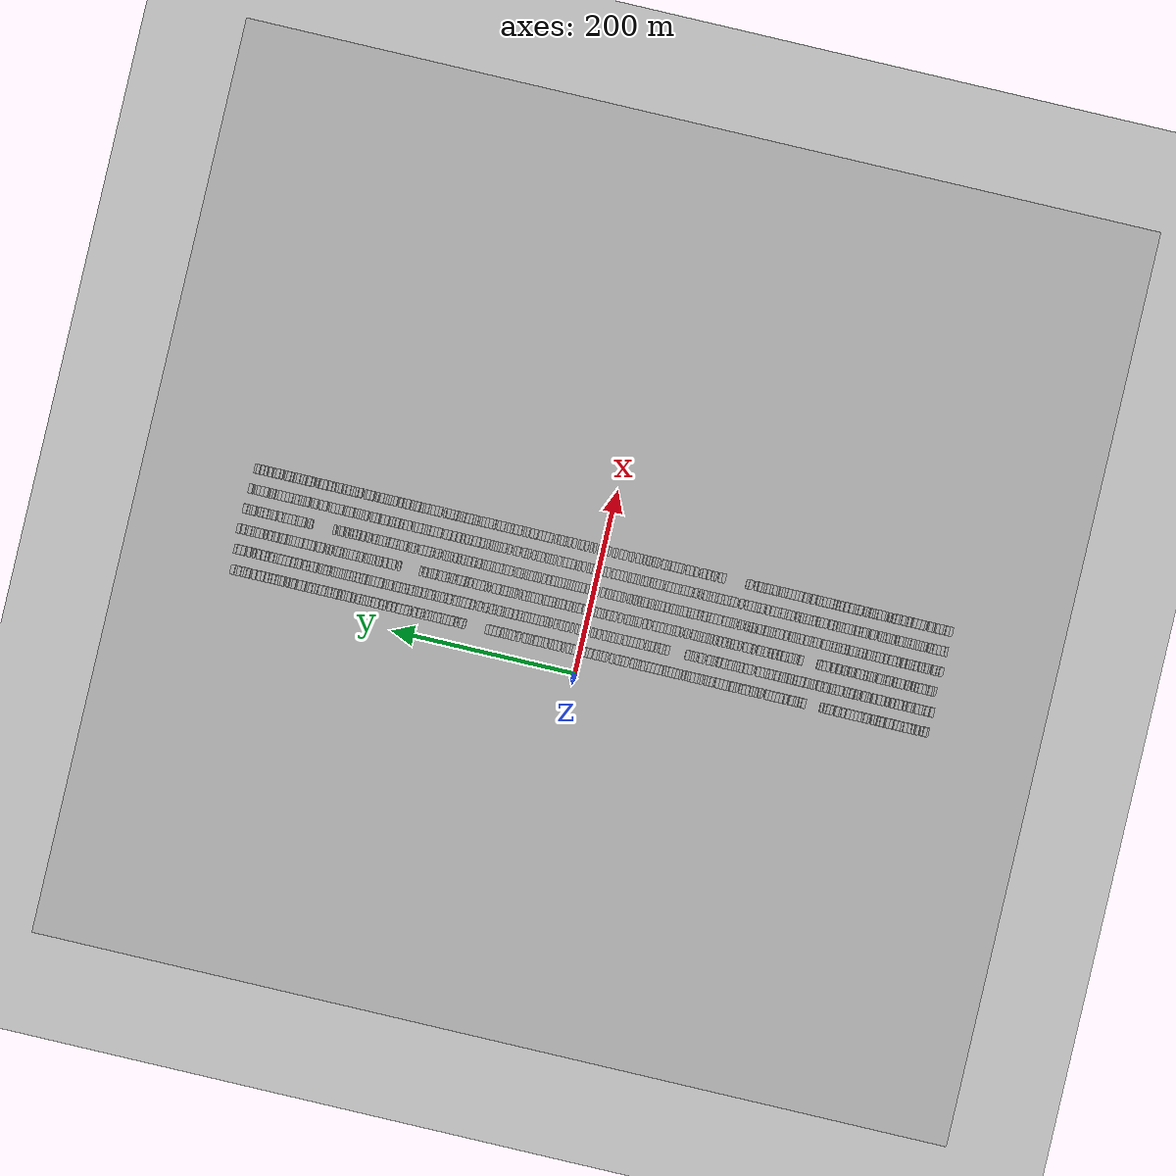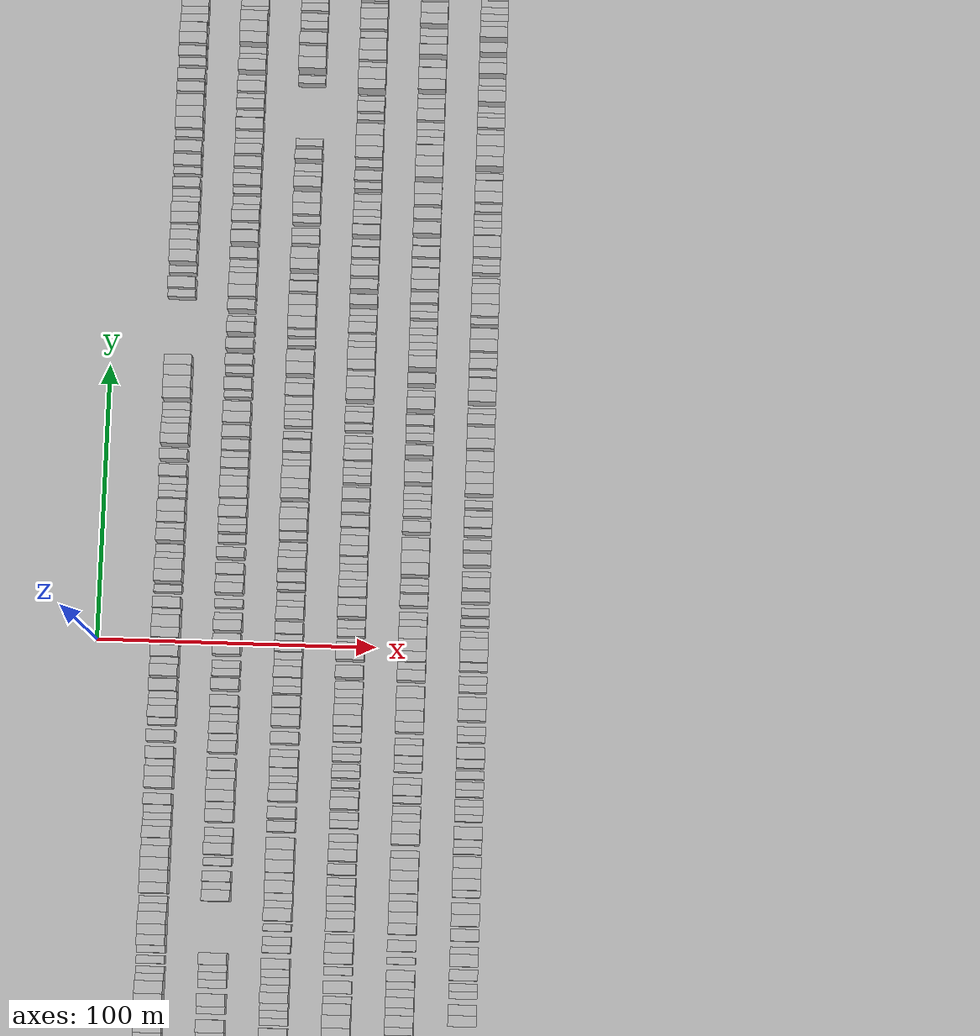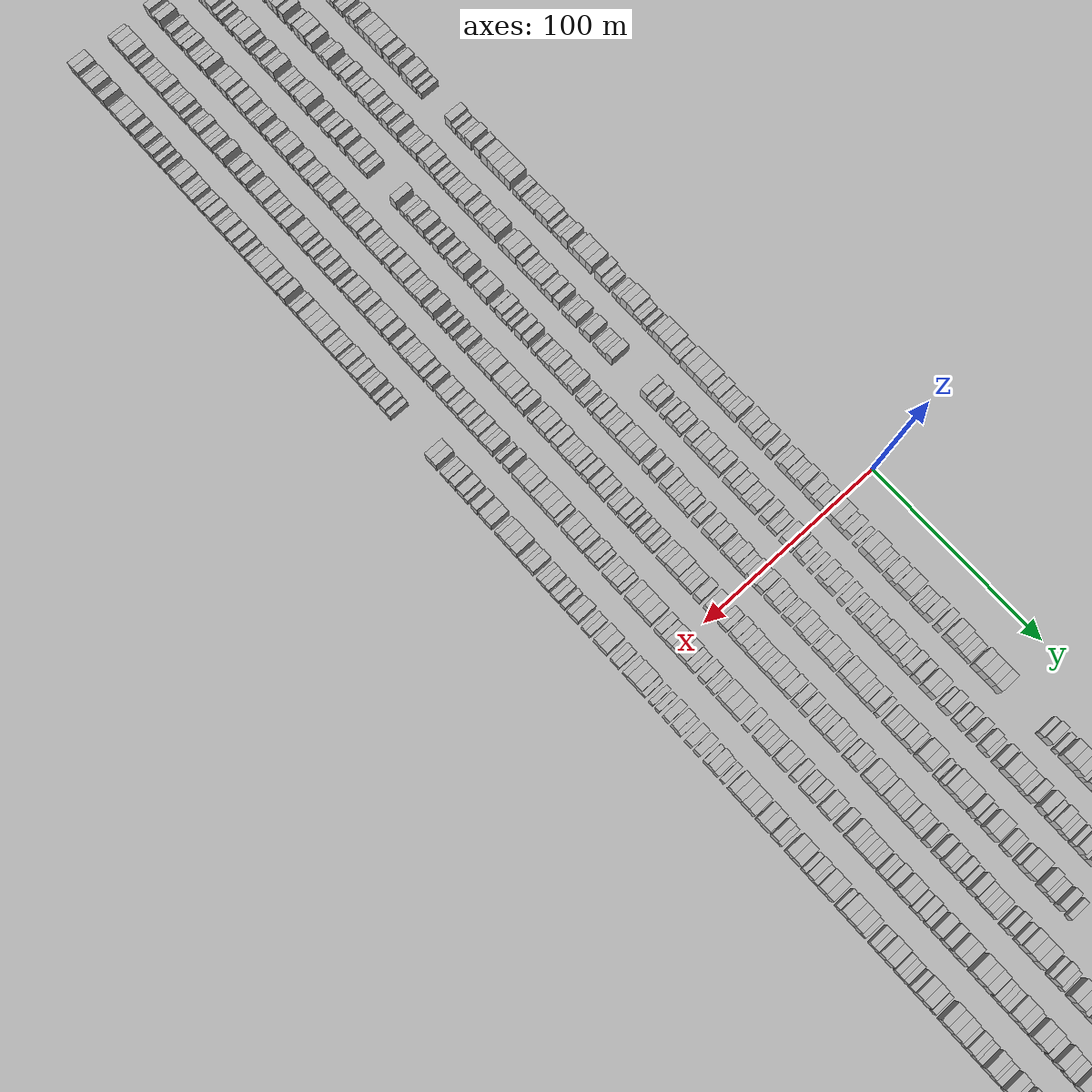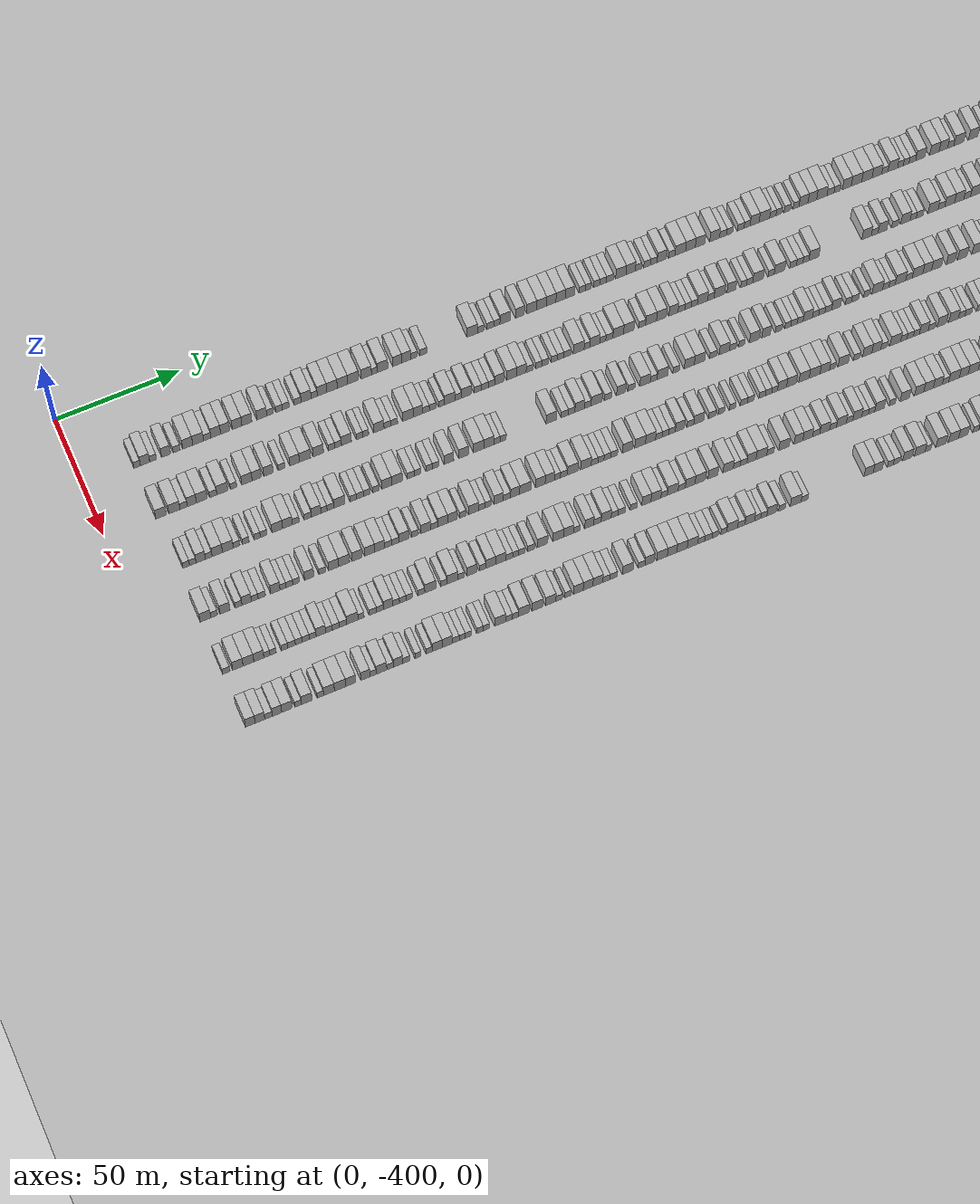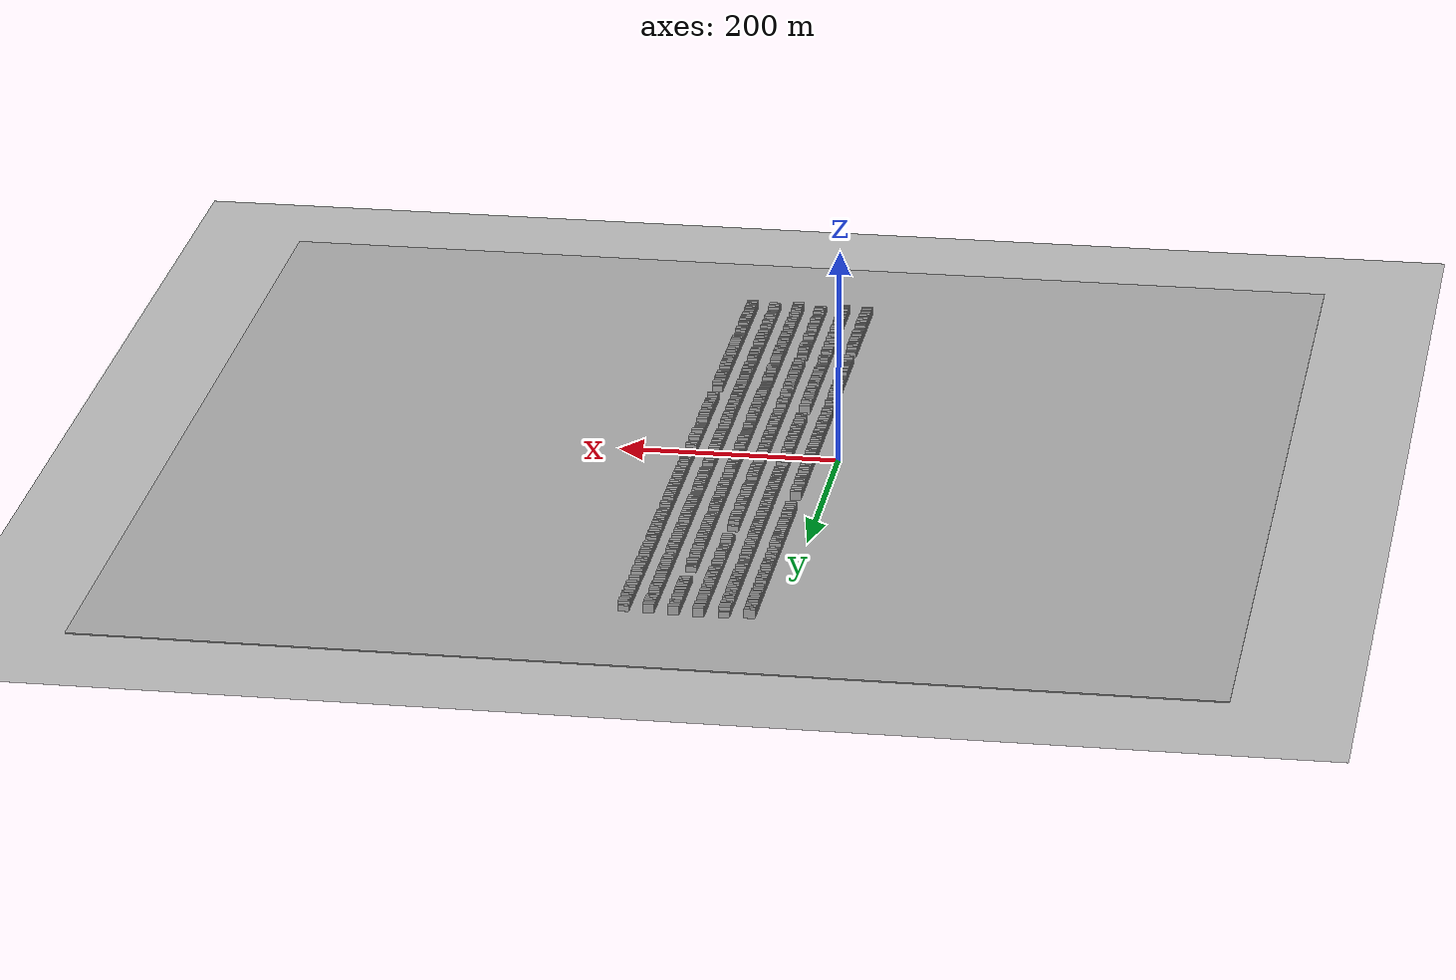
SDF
<?xml version="1.0" encoding="utf-8"?>

<sdf version="1.6">

   <world name="default">

      <gui fullscreen="0">

         <camera name="user_camera">

            <pose>-15 0 4.57585 0 0 0</pose>

            <view_controller>orbit</view_controller>

         </camera>

      </gui>

      <scene>

         <sky>

           <clouds>

             <speed>12</speed>

           </clouds>

         </sky>

         <ambient>0.4 0.4 0.4 1</ambient>

         <background>0.7 0.7 0.7 1</background>

         <shadows>1</shadows>

      </scene>

      <gravity>0 0 -9.8066</gravity>

      <magnetic_field>6e-06 2.3e-05 -4.2e-05</magnetic_field>

      <physics default="0" name="default_physics" type="ode">

         <ode>

            <solver>

               <type>quick</type>

               <iters>10</iters>

               <sor>1.0</sor>

               <use_dynamic_moi_rescaling>0</use_dynamic_moi_rescaling>

            </solver>

            <constraints>

               <cfm>0</cfm>

               <erp>0.2</erp>

               <contact_max_correcting_vel>100</contact_max_correcting_vel>

               <contact_surface_layer>0.001</contact_surface_layer>

            </constraints>

         </ode>

         <max_step_size>0.004</max_step_size>

         <real_time_factor>1</real_time_factor>

         <real_time_update_rate>250</real_time_update_rate>

      </physics>

      <light name="sun" type="directional">

         <cast_shadows>1</cast_shadows>

         <pose>0 0 10 0 0 0</pose>

         <diffuse>0.8 0.8 0.8 1</diffuse>

         <specular>0.2 0.2 0.2 1</specular>

         <attenuation>

            <range>1000</range>

            <constant>0.9</constant>

            <linear>0.01</linear>

            <quadratic>0.001</quadratic>

         </attenuation>

         <direction>-0.5 0.1 -0.9</direction>

      </light>

      <include>

         <name>ground_plane_1</name>

         <uri>model://HANNAS_ground_plane</uri>

         <pose>0 0 0  0 0 0</pose>

      </include>

      <include>

         <name>ground_plane_2</name>

         <uri>model://HANNAS_ground_plane</uri>

         <pose>100 0 0  0 0 0</pose>

      </include>

      <model name="building_1">

         <static>1</static>

         <pose frame="">25.0000 -378.7042 0 0.000000 0.000000 0.000000</pose>

         <link name="link">

            <pose frame="">0 0 3.00 0 0 0</pose>

            <collision name="collision">

               <geometry>

                  <box>

                     <size>10.0000 2.5916 6.0000</size>

                  </box>

               </geometry>

               <max_contacts>10</max_contacts>

               <surface>

                  <contact>

                     <ode/>

                  </contact>

                  <bounce/>

                  <friction>

                     <torsional>

                        <ode/>

                     </torsional>

                     <ode/>

                  </friction>

               </surface>

            </collision>

            <visual name="visual">

               <cast_shadows>0</cast_shadows>

               <geometry>

                  <box>

                     <size>10.0000 2.5916 6.0000</size>

                  </box>

               </geometry>

               <material>

                  <script>

                     <uri>model://HANNAS_wall/materials/scripts</uri>

                     <uri>model://HANNAS_wall/materials/textures</uri>

                     <name>vrc/HANNAS_wall</name>

                  </script>

               </material>

            </visual>

            <self_collide>0</self_collide>

            <enable_wind>0</enable_wind>

            <kinematic>0</kinematic>

         </link>

      </model>

      <model name="building_2">

         <static>1</static>

         <pose frame="">25.0000 -375.5459 0 0.000000 0.000000 0.000000</pose>

         <link name="link">

            <pose frame="">0 0 4.50 0 0 0</pose>

            <collision name="collision">

               <geometry>

                  <box>

                     <size>10.0000 3.7251 9.0000</size>

                  </box>

               </geometry>

               <max_contacts>10</max_contacts>

               <surface>

                  <contact>

                     <ode/>

                  </contact>

                  <bounce/>

                  <friction>

                     <torsional>

                        <ode/>

                     </torsional>

                     <ode/>

                  </friction>

               </surface>

            </collision>

            <visual name="visual">

               <cast_shadows>0</cast_shadows>

               <geometry>

                  <box>

                     <size>10.0000 3.7251 9.0000</size>

                  </box>

               </geometry>

               <material>

                  <script>

                     <uri>model://HANNAS_wall/materials/scripts</uri>

                     <uri>model://HANNAS_wall/materials/textures</uri>

                     <name>vrc/HANNAS_wall</name>

                  </script>

               </material>

            </visual>

            <self_collide>0</self_collide>

            <enable_wind>0</enable_wind>

            <kinematic>0</kinematic>

         </link>

      </model>

      <model name="building_3">

         <static>1</static>

         <pose frame="">25.0000 -372.3275 0 0.000000 0.000000 0.000000</pose>

         <link name="link">

            <pose frame="">0 0 3.00 0 0 0</pose>

            <collision name="collision">

               <geometry>

                  <box>

                     <size>10.0000 2.7116 6.0000</size>

                  </box>

               </geometry>

               <max_contacts>10</max_contacts>

               <surface>

                  <contact>

                     <ode/>

                  </contact>

                  <bounce/>

                  <friction>

                     <torsional>

                        <ode/>

                     </torsional>

                     <ode/>

                  </friction>

               </surface>

            </collision>

            <visual name="visual">

               <cast_shadows>0</cast_shadows>

               <geometry>

                  <box>

                     <size>10.0000 2.7116 6.0000</size>

                  </box>

               </geometry>

               <material>

                  <script>

                     <uri>model://HANNAS_wall/materials/scripts</uri>

                     <uri>model://HANNAS_wall/materials/textures</uri>

                     <name>vrc/HANNAS_wall</name>

                  </script>

               </material>

            </visual>

            <self_collide>0</self_collide>

            <enable_wind>0</enable_wind>

            <kinematic>0</kinematic>

         </link>

      </model>

      <model name="building_4">

         <static>1</static>

         <pose frame="">25.0000 -367.1593 0 0.000000 0.000000 0.000000</pose>

         <link name="link">

            <pose frame="">0 0 4.50 0 0 0</pose>

            <collision name="collision">

               <geometry>

                  <box>

                     <size>10.0000 3.6249 9.0000</size>

                  </box>

               </geometry>

               <max_contacts>10</max_contacts>

               <surface>

                  <contact>

                     <ode/>

                  </contact>

                  <bounce/>

                  <friction>

                     <torsional>

                        <ode/>

                     </torsional>

                     <ode/>

                  </friction>

               </surface>

            </collision>

            <visual name="visual">

               <cast_shadows>0</cast_shadows>

               <geometry>

                  <box>

                     <size>10.0000 3.6249 9.0000</size>

                  </box>

               </geometry>

               <material>

                  <script>

                     <uri>model://HANNAS_wall/materials/scripts</uri>

                     <uri>model://HANNAS_wall/materials/textures</uri>

                     <name>vrc/HANNAS_wall</name>

                  </script>

               </material>

            </visual>

            <self_collide>0</self_collide>

            <enable_wind>0</enable_wind>

            <kinematic>0</kinematic>

         </link>

      </model>

      <model name="building_5">

         <static>1</static>

         <pose frame="">25.0000 -362.9181 0 0.000000 0.000000 0.000000</pose>

         <link name="link">

            <pose frame="">0 0 3.00 0 0 0</pose>

            <collision name="collision">

               <geometry>

                  <box>

                     <size>10.0000 2.8575 6.0000</size>

                  </box>

               </geometry>

               <max_contacts>10</max_contacts>

               <surface>

                  <contact>

                     <ode/>

                  </contact>

                  <bounce/>

                  <friction>

                     <torsional>

                        <ode/>

                     </torsional>

                     <ode/>

                  </friction>

               </surface>

            </collision>

            <visual name="visual">

               <cast_shadows>0</cast_shadows>

               <geometry>

                  <box>

                     <size>10.0000 2.8575 6.0000</size>

                  </box>

               </geometry>

               <material>

                  <script>

                     <uri>model://HANNAS_wall/materials/scripts</uri>

                     <uri>model://HANNAS_wall/materials/textures</uri>

                     <name>vrc/HANNAS_wall</name>

                  </script>

               </material>

            </visual>

            <self_collide>0</self_collide>

            <enable_wind>0</enable_wind>

            <kinematic>0</kinematic>

         </link>

      </model>

      <model name="building_6">

         <static>1</static>

         <pose frame="">25.0000 -358.4756 0 0.000000 0.000000 0.000000</pose>

         <link name="link">

            <pose frame="">0 0 4.50 0 0 0</pose>

            <collision name="collision">

               <geometry>

                  <box>

                     <size>10.0000 4.0275 9.0000</size>

                  </box>

               </geometry>

               <max_contacts>10</max_contacts>

               <surface>

                  <contact>

                     <ode/>

                  </contact>

                  <bounce/>

                  <friction>

                     <torsional>

                        <ode/>

                     </torsional>

                     <ode/>

                  </friction>

               </surface>

            </collision>

            <visual name="visual">

               <cast_shadows>0</cast_shadows>

               <geometry>

                  <box>

                     <size>10.0000 4.0275 9.0000</size>

                  </box>

               </geometry>

               <material>

                  <script>

                     <uri>model://HANNAS_wall/materials/scripts</uri>

                     <uri>model://HANNAS_wall/materials/textures</uri>

                     <name>vrc/HANNAS_wall</name>

                  </script>

               </material>

            </visual>

            <self_collide>0</self_collide>

            <enable_wind>0</enable_wind>

            <kinematic>0</kinematic>

         </link>

      </model>

      <model name="building_7">

         <static>1</static>

         <pose frame="">25.0000 -354.2735 0 0.000000 0.000000 0.000000</pose>

         <link name="link">

            <pose frame="">0 0 4.50 0 0 0</pose>

            <collision name="collision">

               <geometry>

                  <box>

                     <size>10.0000 4.3768 9.0000</size>

                  </box>

               </geometry>

               <max_contacts>10</max_contacts>

               <surface>

                  <contact>

                     <ode/>

                  </contact>

                  <bounce/>

                  <friction>

                     <torsional>

                        <ode/>

                     </torsional>

                     <ode/>

                  </friction>

               </surface>

            </collision>

            <visual name="visual">

               <cast_shadows>0</cast_shadows>

               <geometry>

                  <box>

                     <size>10.0000 4.3768 9.0000</size>

                  </box>

               </geometry>

               <material>

                  <script>

                     <uri>model://HANNAS_wall/materials/scripts</uri>

                     <uri>model://HANNAS_wall/materials/textures</uri>

                     <name>vrc/HANNAS_wall</name>

                  </script>

               </material>

            </visual>

            <self_collide>0</self_collide>

            <enable_wind>0</enable_wind>

            <kinematic>0</kinematic>

         </link>

      </model>

      <model name="building_8">

         <static>1</static>

         <pose frame="">25.0000 -350.6441 0 0.000000 0.000000 0.000000</pose>

         <link name="link">

            <pose frame="">0 0 3.00 0 0 0</pose>

            <collision name="collision">

               <geometry>

                  <box>

                     <size>10.0000 2.8820 6.0000</size>

                  </box>

               </geometry>

               <max_contacts>10</max_contacts>

               <surface>

                  <contact>

                     <ode/>

                  </contact>

                  <bounce/>

                  <friction>

                     <torsional>

                        <ode/>

                     </torsional>

                     <ode/>

                  </friction>

               </surface>

            </collision>

            <visual name="visual">

               <cast_shadows>0</cast_shadows>

               <geometry>

                  <box>

                     <size>10.0000 2.8820 6.0000</size>

                  </box>

               </geometry>

               <material>

                  <script>

                     <uri>model://HANNAS_wall/materials/scripts</uri>

                     <uri>model://HANNAS_wall/materials/textures</uri>

                     <name>vrc/HANNAS_wall</name>

                  </script>

               </material>

            </visual>

            <self_collide>0</self_collide>

            <enable_wind>0</enable_wind>

            <kinematic>0</kinematic>

         </link>

      </model>

      <model name="building_9">

         <static>1</static>

         <pose frame="">25.0000 -347.2375 0 0.000000 0.000000 0.000000</pose>

         <link name="link">

            <pose frame="">0 0 4.50 0 0 0</pose>

            <collision name="collision">

               <geometry>

                  <box>

                     <size>10.0000 3.9311 9.0000</size>

                  </box>

               </geometry>

               <max_contacts>10</max_contacts>

               <surface>

                  <contact>

                     <ode/>

                  </contact>

                  <bounce/>

                  <friction>

                     <torsional>

                        <ode/>

                     </torsional>

                     <ode/>

                  </friction>

               </surface>

            </collision>

            <visual name="visual">

               <cast_shadows>0</cast_shadows>

               <geometry>

                  <box>

                     <size>10.0000 3.9311 9.0000</size>

                  </box>

               </geometry>

               <material>

                  <script>

                     <uri>model://HANNAS_wall/materials/scripts</uri>

                     <uri>model://HANNAS_wall/materials/textures</uri>

                     <name>vrc/HANNAS_wall</name>

                  </script>

               </material>

            </visual>

            <self_collide>0</self_collide>

            <enable_wind>0</enable_wind>

            <kinematic>0</kinematic>

         </link>

      </model>

      <model name="building_10">

         <static>1</static>

         <pose frame="">25.0000 -343.4574 0 0.000000 0.000000 0.000000</pose>

         <link name="link">

            <pose frame="">0 0 4.50 0 0 0</pose>

            <collision name="collision">

               <geometry>

                  <box>

                     <size>10.0000 3.6291 9.0000</size>

                  </box>

               </geometry>

               <max_contacts>10</max_contacts>

               <surface>

                  <contact>

                     <ode/>

                  </contact>

                  <bounce/>

                  <friction>

                     <torsional>

                        <ode/>

                     </torsional>

                     <ode/>

                  </friction>

               </surface>

            </collision>

            <visual name="visual">

               <cast_shadows>0</cast_shadows>

               <geometry>

                  <box>

                     <size>10.0000 3.6291 9.0000</size>

                  </box>

               </geometry>

               <material>

                  <script>

                     <uri>model://HANNAS_wall/materials/scripts</uri>

                     <uri>model://HANNAS_wall/materials/textures</uri>

                     <name>vrc/HANNAS_wall</name>

                  </script>

               </material>

            </visual>

            <self_collide>0</self_collide>

            <enable_wind>0</enable_wind>

            <kinematic>0</kinematic>

         </link>

      </model>

      <model name="building_11">

         <static>1</static>

         <pose frame="">25.0000 -338.7094 0 0.000000 0.000000 0.000000</pose>

         <link name="link">

            <pose frame="">0 0 4.50 0 0 0</pose>

            <collision name="collision">

               <geometry>

                  <box>

                     <size>10.0000 3.8671 9.0000</size>

                  </box>

               </geometry>

               <max_contacts>10</max_contacts>

               <surface>

                  <contact>

                     <ode/>

                  </contact>

                  <bounce/>

                  <friction>

                     <torsional>

                        <ode/>

                     </torsional>

                     <ode/>

                  </friction>

               </surface>

            </collision>

            <visual name="visual">

               <cast_shadows>0</cast_shadows>

               <geometry>

                  <box>

                     <size>10.0000 3.8671 9.0000</size>

                  </box>

               </geometry>

               <material>

                  <script>

                     <uri>model://HANNAS_wall/materials/scripts</uri>

                     <uri>model://HANNAS_wall/materials/textures</uri>

                     <name>vrc/HANNAS_wall</name>

                  </script>

               </material>

            </visual>

            <self_collide>0</self_collide>

            <enable_wind>0</enable_wind>

            <kinematic>0</kinematic>

         </link>

      </model>

      <model name="building_12">

         <static>1</static>

         <pose frame="">25.0000 -334.7679 0 0.000000 0.000000 0.000000</pose>

         <link name="link">

            <pose frame="">0 0 4.50 0 0 0</pose>

            <collision name="collision">

               <geometry>

                  <box>

                     <size>10.0000 4.0159 9.0000</size>

                  </box>

               </geometry>

               <max_contacts>10</max_contacts>

               <surface>

                  <contact>

                     <ode/>

                  </contact>

                  <bounce/>

                  <friction>

                     <torsional>

                        <ode/>

                     </torsional>

                     <ode/>

                  </friction>

               </surface>

            </collision>

            <visual name="visual">

               <cast_shadows>0</cast_shadows>

               <geometry>

                  <box>

                     <size>10.0000 4.0159 9.0000</size>

                  </box>

               </geometry>

               <material>

                  <script>

                     <uri>model://HANNAS_wall/materials/scripts</uri>

                     <uri>model://HANNAS_wall/materials/textures</uri>

                     <name>vrc/HANNAS_wall</name>

                  </script>

               </material>

            </visual>

            <self_collide>0</self_collide>

            <enable_wind>0</enable_wind>

            <kinematic>0</kinematic>

         </link>

      </model>

      <model name="building_13">

         <static>1</static>

         <pose frame="">25.0000 -328.7408 0 0.000000 0.000000 0.000000</pose>

         <link name="link">

            <pose frame="">0 0 4.50 0 0 0</pose>

            <collision name="collision">

               <geometry>

                  <box>

                     <size>10.0000 4.0384 9.0000</size>

                  </box>

               </geometry>

               <max_contacts>10</max_contacts>

               <surface>

                  <contact>

                     <ode/>

                  </contact>

                  <bounce/>

                  <friction>

                     <torsional>

                        <ode/>

                     </torsional>

                     <ode/>

                  </friction>

               </surface>

            </collision>

            <visual name="visual">

               <cast_shadows>0</cast_shadows>

               <geometry>

                  <box>

                     <size>10.0000 4.0384 9.0000</size>

                  </box>

               </geometry>

               <material>

                  <script>

                     <uri>model://HANNAS_wall/materials/scripts</uri>

                     <uri>model://HANNAS_wall/materials/textures</uri>

                     <name>vrc/HANNAS_wall</name>

                  </script>

               </material>

            </visual>

            <self_collide>0</self_collide>

            <enable_wind>0</enable_wind>

            <kinematic>0</kinematic>

         </link>

      </model>

      <model name="building_14">

         <static>1</static>

         <pose frame="">25.0000 -325.4519 0 0.000000 0.000000 0.000000</pose>

         <link name="link">

            <pose frame="">0 0 3.00 0 0 0</pose>

            <collision name="collision">

               <geometry>

                  <box>

                     <size>10.0000 2.5393 6.0000</size>

                  </box>

               </geometry>

               <max_contacts>10</max_contacts>

               <surface>

                  <contact>

                     <ode/>

                  </contact>

                  <bounce/>

                  <friction>

                     <torsional>

                        <ode/>

                     </torsional>

                     <ode/>

                  </friction>

               </surface>

            </collision>

            <visual name="visual">

               <cast_shadows>0</cast_shadows>

               <geometry>

                  <box>

                     <size>10.0000 2.5393 6.0000</size>

                  </box>

               </geometry>

               <material>

                  <script>

                     <uri>model://HANNAS_wall/materials/scripts</uri>

                     <uri>model://HANNAS_wall/materials/textures</uri>

                     <name>vrc/HANNAS_wall</name>

                  </script>

               </material>

            </visual>

            <self_collide>0</self_collide>

            <enable_wind>0</enable_wind>

            <kinematic>0</kinematic>

         </link>

      </model>

      <model name="building_15">

         <static>1</static>

         <pose frame="">25.0000 -321.8085 0 0.000000 0.000000 0.000000</pose>

         <link name="link">

            <pose frame="">0 0 3.00 0 0 0</pose>

            <collision name="collision">

               <geometry>

                  <box>

                     <size>10.0000 2.7476 6.0000</size>

                  </box>

               </geometry>

               <max_contacts>10</max_contacts>

               <surface>

                  <contact>

                     <ode/>

                  </contact>

                  <bounce/>

                  <friction>

                     <torsional>

                        <ode/>

                     </torsional>

                     <ode/>

                  </friction>

               </surface>

            </collision>

            <visual name="visual">

               <cast_shadows>0</cast_shadows>

               <geometry>

                  <box>

                     <size>10.0000 2.7476 6.0000</size>

                  </box>

               </geometry>

               <material>

                  <script>

                     <uri>model://HANNAS_wall/materials/scripts</uri>

                     <uri>model://HANNAS_wall/materials/textures</uri>

                     <name>vrc/HANNAS_wall</name>

                  </script>

               </material>

            </visual>

            <self_collide>0</self_collide>

            <enable_wind>0</enable_wind>

            <kinematic>0</kinematic>

         </link>

      </model>

      <model name="building_16">

         <static>1</static>

         <pose frame="">25.0000 -319.0733 0 0.000000 0.000000 0.000000</pose>

         <link name="link">

            <pose frame="">0 0 3.00 0 0 0</pose>

            <collision name="collision">

               <geometry>

                  <box>

                     <size>10.0000 2.7228 6.0000</size>

                  </box>

               </geometry>

               <max_contacts>10</max_contacts>

               <surface>

                  <contact>

                     <ode/>

                  </contact>

                  <bounce/>

                  <friction>

                     <torsional>

                        <ode/>

                     </torsional>

                     <ode/>

                  </friction>

               </surface>

            </collision>

            <visual name="visual">

               <cast_shadows>0</cast_shadows>

               <geometry>

                  <box>

                     <size>10.0000 2.7228 6.0000</size>

                  </box>

               </geometry>

               <material>

                  <script>

                     <uri>model://HANNAS_wall/materials/scripts</uri>

                     <uri>model://HANNAS_wall/materials/textures</uri>

                     <name>vrc/HANNAS_wall</name>

                  </script>

               </material>

            </visual>

            <self_collide>0</self_collide>

            <enable_wind>0</enable_wind>

            <kinematic>0</kinematic>

         </link>

      </model>

      <model name="building_17">

         <static>1</static>

         <pose frame="">25.0000 -314.3101 0 0.000000 0.000000 0.000000</pose>

         <link name="link">

            <pose frame="">0 0 3.00 0 0 0</pose>

            <collision name="collision">

               <geometry>

                  <box>

                     <size>10.0000 2.8036 6.0000</size>

                  </box>

               </geometry>

               <max_contacts>10</max_contacts>

               <surface>

                  <contact>

                     <ode/>

                  </contact>

                  <bounce/>

                  <friction>

                     <torsional>

                        <ode/>

                     </torsional>

                     <ode/>

                  </friction>

               </surface>

            </collision>

            <visual name="visual">

               <cast_shadows>0</cast_shadows>

               <geometry>

                  <box>

                     <size>10.0000 2.8036 6.0000</size>

                  </box>

               </geometry>

               <material>

                  <script>

                     <uri>model://HANNAS_wall/materials/scripts</uri>

                     <uri>model://HANNAS_wall/materials/textures</uri>

                     <name>vrc/HANNAS_wall</name>

                  </script>

               </material>

            </visual>

            <self_collide>0</self_collide>

            <enable_wind>0</enable_wind>

            <kinematic>0</kinematic>

         </link>

      </model>

      <model name="building_18">

         <static>1</static>

         <pose frame="">25.0000 -310.8846 0 0.000000 0.000000 0.000000</pose>

         <link name="link">

            <pose frame="">0 0 4.50 0 0 0</pose>

            <collision name="collision">

               <geometry>

                  <box>

                     <size>10.0000 4.0474 9.0000</size>

                  </box>

               </geometry>

               <max_contacts>10</max_contacts>

               <surface>

                  <contact>

                     <ode/>

                  </contact>

                  <bounce/>

                  <friction>

                     <torsional>

                        <ode/>

                     </torsional>

                     <ode/>

                  </friction>

               </surface>

            </collision>

            <visual name="visual">

               <cast_shadows>0</cast_shadows>

               <geometry>

                  <box>

                     <size>10.0000 4.0474 9.0000</size>

                  </box>

               </geometry>

               <material>

                  <script>

                     <uri>model://HANNAS_wall/materials/scripts</uri>

                     <uri>model://HANNAS_wall/materials/textures</uri>

                     <name>vrc/HANNAS_wall</name>

                  </script>

               </material>

            </visual>

            <self_collide>0</self_collide>

            <enable_wind>0</enable_wind>

            <kinematic>0</kinematic>

         </link>

      </model>

      <model name="building_19">

         <static>1</static>

         <pose frame="">25.0000 -307.6178 0 0.000000 0.000000 0.000000</pose>

         <link name="link">

            <pose frame="">0 0 3.00 0 0 0</pose>

            <collision name="collision">

               <geometry>

                  <box>

                     <size>10.0000 2.4863 6.0000</size>

                  </box>

               </geometry>

               <max_contacts>10</max_contacts>

               <surface>

                  <contact>

                     <ode/>

                  </contact>

                  <bounce/>

                  <friction>

                     <torsional>

                        <ode/>

                     </torsional>

                     <ode/>

                  </friction>

               </surface>

            </collision>

            <visual name="visual">

               <cast_shadows>0</cast_shadows>

               <geometry>

                  <box>

                     <size>10.0000 2.4863 6.0000</size>

                  </box>

               </geometry>

               <material>

                  <script>

                     <uri>model://HANNAS_wall/materials/scripts</uri>

                     <uri>model://HANNAS_wall/materials/textures</uri>

                     <name>vrc/HANNAS_wall</name>

                  </script>

               </material>

            </visual>

            <self_collide>0</self_collide>

            <enable_wind>0</enable_wind>

            <kinematic>0</kinematic>

         </link>

      </model>

      <model name="building_20">

         <static>1</static>

         <pose frame="">25.0000 -304.4380 0 0.000000 0.000000 0.000000</pose>

         <link name="link">

            <pose frame="">0 0 4.50 0 0 0</pose>

            <collision name="collision">

               <geometry>

                  <box>

                     <size>10.0000 3.8734 9.0000</size>

                  </box>

               </geometry>

               <max_contacts>10</max_contacts>

               <surface>

                  <contact>

                     <ode/>

                  </contact>

                  <bounce/>

                  <friction>

                     <torsional>

                        <ode/>

                     </torsional>

                     <ode/>

                  </friction>

               </surface>

            </collision>

            <visual name="visual">

               <cast_shadows>0</cast_shadows>

               <geometry>

                  <box>

                     <size>10.0000 3.8734 9.0000</size>

                  </box>

               </geometry>

               <material>

                  <script>

                     <uri>model://HANNAS_wall/materials/scripts</uri>

                     <uri>model://HANNAS_wall/materials/textures</uri>

                     <name>vrc/HANNAS_wall</name>

                  </script>

               </material>

            </visual>

            <self_collide>0</self_collide>

            <enable_wind>0</enable_wind>

            <kinematic>0</kinematic>

         </link>

      </model>

      <model name="building_21">

         <static>1</static>

         <pose frame="">25.0000 -300.3931 0 0.000000 0.000000 0.000000</pose>

         <link name="link">

            <pose frame="">0 0 4.50 0 0 0</pose>

            <collision name="collision">

               <geometry>

                  <box>

                     <size>10.0000 4.2163 9.0000</size>

                  </box>

               </geometry>

               <max_contacts>10</max_contacts>

               <surface>

                  <contact>

                     <ode/>

                  </contact>

                  <bounce/>

                  <friction>

                     <torsional>

                        <ode/>

                     </torsional>

                     <ode/>

                  </friction>

               </surface>

            </collision>

            <visual name="visual">

               <cast_shadows>0</cast_shadows>

               <geometry>

                  <box>

                     <size>10.0000 4.2163 9.0000</size>

                  </box>

               </geometry>

               <material>

                  <script>

                     <uri>model://HANNAS_wall/materials/scripts</uri>

                     <uri>model://HANNAS_wall/materials/textures</uri>

                     <name>vrc/HANNAS_wall</name>

                  </script>

               </material>

            </visual>

            <self_collide>0</self_collide>

            <enable_wind>0</enable_wind>

            <kinematic>0</kinematic>

         </link>

      </model>

      <model name="building_22">

         <static>1</static>

         <pose frame="">25.0000 -296.1703 0 0.000000 0.000000 0.000000</pose>

         <link name="link">

            <pose frame="">0 0 4.50 0 0 0</pose>

            <collision name="collision">

               <geometry>

                  <box>

                     <size>10.0000 4.2294 9.0000</size>

                  </box>

               </geometry>

               <max_contacts>10</max_contacts>

               <surface>

                  <contact>

                     <ode/>

                  </contact>

                  <bounce/>

                  <friction>

                     <torsional>

                        <ode/>

                     </torsional>

                     <ode/>

                  </friction>

               </surface>

            </collision>

            <visual name="visual">

               <cast_shadows>0</cast_shadows>

               <geometry>

                  <box>

                     <size>10.0000 4.2294 9.0000</size>

                  </box>

               </geometry>

               <material>

                  <script>

                     <uri>model://HANNAS_wall/materials/scripts</uri>

                     <uri>model://HANNAS_wall/materials/textures</uri>

                     <name>vrc/HANNAS_wall</name>

                  </script>

               </material>

            </visual>

            <self_collide>0</self_collide>

            <enable_wind>0</enable_wind>

            <kinematic>0</kinematic>

         </link>

      </model>

      <model name="building_23">

         <static>1</static>

         <pose frame="">25.0000 -291.8603 0 0.000000 0.000000 0.000000</pose>

         <link name="link">

            <pose frame="">0 0 4.50 0 0 0</pose>

            <collision name="collision">

               <geometry>

                  <box>

                     <size>10.0000 4.3907 9.0000</size>

                  </box>

               </geometry>

               <max_contacts>10</max_contacts>

               <surface>

                  <contact>

                     <ode/>

                  </contact>

                  <bounce/>

                  <friction>

                     <torsional>

                        <ode/>

                     </torsional>

                     <ode/>

                  </friction>

               </surface>

            </collision>

            <visual name="visual">

               <cast_shadows>0</cast_shadows>

               <geometry>

                  <box>

                     <size>10.0000 4.3907 9.0000</size>

                  </box>

               </geometry>

               <material>

                  <script>

                     <uri>model://HANNAS_wall/materials/scripts</uri>

                     <uri>model://HANNAS_wall/materials/textures</uri>

                     <name>vrc/HANNAS_wall</name>

                  </script>

               </material>

            </visual>

            <self_collide>0</self_collide>

            <enable_wind>0</enable_wind>

            <kinematic>0</kinematic>

         </link>

      </model>

      <model name="building_24">

         <static>1</static>

         <pose frame="">25.0000 -286.5370 0 0.000000 0.000000 0.000000</pose>

         <link name="link">

            <pose frame="">0 0 4.50 0 0 0</pose>

            <collision name="collision">

               <geometry>

                  <box>

                     <size>10.0000 4.2558 9.0000</size>

                  </box>

               </geometry>

               <max_contacts>10</max_contacts>

               <surface>

                  <contact>

                     <ode/>

                  </contact>

                  <bounce/>

                  <friction>

                     <torsional>

                        <ode/>

                     </torsional>

                     <ode/>

                  </friction>

               </surface>

            </collision>

            <visual name="visual">

               <cast_shadows>0</cast_shadows>

               <geometry>

                  <box>

                     <size>10.0000 4.2558 9.0000</size>

                  </box>

               </geometry>

               <material>

                  <script>

                     <uri>model://HANNAS_wall/materials/scripts</uri>

                     <uri>model://HANNAS_wall/materials/textures</uri>

                     <name>vrc/HANNAS_wall</name>

                  </script>

               </material>

            </visual>

            <self_collide>0</self_collide>

            <enable_wind>0</enable_wind>

            <kinematic>0</kinematic>

         </link>

      </model>

      <model name="building_25">

         <static>1</static>

         <pose frame="">25.0000 -283.2069 0 0.000000 0.000000 0.000000</pose>

         <link name="link">

            <pose frame="">0 0 3.00 0 0 0</pose>

            <collision name="collision">

               <geometry>

                  <box>

                     <size>10.0000 2.4044 6.0000</size>

                  </box>

               </geometry>

               <max_contacts>10</max_contacts>

               <surface>

                  <contact>

                     <ode/>

                  </contact>

                  <bounce/>

                  <friction>

                     <torsional>

                        <ode/>

                     </torsional>

                     <ode/>

                  </friction>

               </surface>

            </collision>

            <visual name="visual">

               <cast_shadows>0</cast_shadows>

               <geometry>

                  <box>

                     <size>10.0000 2.4044 6.0000</size>

                  </box>

               </geometry>

               <material>

                  <script>

                     <uri>model://HANNAS_wall/materials/scripts</uri>

                     <uri>model://HANNAS_wall/materials/textures</uri>

                     <name>vrc/HANNAS_wall</name>

                  </script>

               </material>

            </visual>

            <self_collide>0</self_collide>

            <enable_wind>0</enable_wind>

            <kinematic>0</kinematic>

         </link>

      </model>

      <model name="building_26">

         <static>1</static>

         <pose frame="">25.0000 -279.8843 0 0.000000 0.000000 0.000000</pose>

         <link name="link">

            <pose frame="">0 0 4.50 0 0 0</pose>

            <collision name="collision">

               <geometry>

                  <box>

                     <size>10.0000 4.2408 9.0000</size>

                  </box>

               </geometry>

               <max_contacts>10</max_contacts>

               <surface>

                  <contact>

                     <ode/>

                  </contact>

                  <bounce/>

                  <friction>

                     <torsional>

                        <ode/>

                     </torsional>

                     <ode/>

                  </friction>

               </surface>

            </collision>

            <visual name="visual">

               <cast_shadows>0</cast_shadows>

               <geometry>

                  <box>

                     <size>10.0000 4.2408 9.0000</size>

                  </box>

               </geometry>

               <material>

                  <script>

                     <uri>model://HANNAS_wall/materials/scripts</uri>

                     <uri>model://HANNAS_wall/materials/textures</uri>

                     <name>vrc/HANNAS_wall</name>

                  </script>

               </material>

            </visual>

            <self_collide>0</self_collide>

            <enable_wind>0</enable_wind>

            <kinematic>0</kinematic>

         </link>

      </model>

      <model name="building_27">

         <static>1</static>

         <pose frame="">25.0000 -273.9616 0 0.000000 0.000000 0.000000</pose>

         <link name="link">

            <pose frame="">0 0 4.50 0 0 0</pose>

            <collision name="collision">

               <geometry>

                  <box>

                     <size>10.0000 3.6046 9.0000</size>

                  </box>

               </geometry>

               <max_contacts>10</max_contacts>

               <surface>

                  <contact>

                     <ode/>

                  </contact>

                  <bounce/>

                  <friction>

                     <torsional>

                        <ode/>

                     </torsional>

                     <ode/>

                  </friction>

               </surface>

            </collision>

            <visual name="visual">

               <cast_shadows>0</cast_shadows>

               <geometry>

                  <box>

                     <size>10.0000 3.6046 9.0000</size>

                  </box>

               </geometry>

               <material>

                  <script>

                     <uri>model://HANNAS_wall/materials/scripts</uri>

                     <uri>model://HANNAS_wall/materials/textures</uri>

                     <name>vrc/HANNAS_wall</name>

                  </script>

               </material>

            </visual>

            <self_collide>0</self_collide>

            <enable_wind>0</enable_wind>

            <kinematic>0</kinematic>

         </link>

      </model>

      <model name="building_28">

         <static>1</static>

         <pose frame="">25.0000 -270.3155 0 0.000000 0.000000 0.000000</pose>

         <link name="link">

            <pose frame="">0 0 4.50 0 0 0</pose>

            <collision name="collision">

               <geometry>

                  <box>

                     <size>10.0000 3.6878 9.0000</size>

                  </box>

               </geometry>

               <max_contacts>10</max_contacts>

               <surface>

                  <contact>

                     <ode/>

                  </contact>

                  <bounce/>

                  <friction>

                     <torsional>

                        <ode/>

                     </torsional>

                     <ode/>

                  </friction>

               </surface>

            </collision>

            <visual name="visual">

               <cast_shadows>0</cast_shadows>

               <geometry>

                  <box>

                     <size>10.0000 3.6878 9.0000</size>

                  </box>

               </geometry>

               <material>

                  <script>

                     <uri>model://HANNAS_wall/materials/scripts</uri>

                     <uri>model://HANNAS_wall/materials/textures</uri>

                     <name>vrc/HANNAS_wall</name>

                  </script>

               </material>

            </visual>

            <self_collide>0</self_collide>

            <enable_wind>0</enable_wind>

            <kinematic>0</kinematic>

         </link>

      </model>

      <model name="building_29">

         <static>1</static>

         <pose frame="">25.0000 -267.1357 0 0.000000 0.000000 0.000000</pose>

         <link name="link">

            <pose frame="">0 0 3.00 0 0 0</pose>

            <collision name="collision">

               <geometry>

                  <box>

                     <size>10.0000 2.6718 6.0000</size>

                  </box>

               </geometry>

               <max_contacts>10</max_contacts>

               <surface>

                  <contact>

                     <ode/>

                  </contact>

                  <bounce/>

                  <friction>

                     <torsional>

                        <ode/>

                     </torsional>

                     <ode/>

                  </friction>

               </surface>

            </collision>

            <visual name="visual">

               <cast_shadows>0</cast_shadows>

               <geometry>

                  <box>

                     <size>10.0000 2.6718 6.0000</size>

                  </box>

               </geometry>

               <material>

                  <script>

                     <uri>model://HANNAS_wall/materials/scripts</uri>

                     <uri>model://HANNAS_wall/materials/textures</uri>

                     <name>vrc/HANNAS_wall</name>

                  </script>

               </material>

            </visual>

            <self_collide>0</self_collide>

            <enable_wind>0</enable_wind>

            <kinematic>0</kinematic>

         </link>

      </model>

      <model name="building_30">

         <static>1</static>

         <pose frame="">25.0000 -263.3466 0 0.000000 0.000000 0.000000</pose>

         <link name="link">

            <pose frame="">0 0 3.00 0 0 0</pose>

            <collision name="collision">

               <geometry>

                  <box>

                     <size>10.0000 2.9063 6.0000</size>

                  </box>

               </geometry>

               <max_contacts>10</max_contacts>

               <surface>

                  <contact>

                     <ode/>

                  </contact>

                  <bounce/>

                  <friction>

                     <torsional>

                        <ode/>

                     </torsional>

                     <ode/>

                  </friction>

               </surface>

            </collision>

            <visual name="visual">

               <cast_shadows>0</cast_shadows>

               <geometry>

                  <box>

                     <size>10.0000 2.9063 6.0000</size>

                  </box>

               </geometry>

               <material>

                  <script>

                     <uri>model://HANNAS_wall/materials/scripts</uri>

                     <uri>model://HANNAS_wall/materials/textures</uri>

                     <name>vrc/HANNAS_wall</name>

                  </script>

               </material>

            </visual>

            <self_collide>0</self_collide>

            <enable_wind>0</enable_wind>

            <kinematic>0</kinematic>

         </link>

      </model>

      <model name="building_31">

         <static>1</static>

         <pose frame="">25.0000 -243.3205 0 0.000000 0.000000 0.000000</pose>

         <link name="link">

            <pose frame="">0 0 4.50 0 0 0</pose>

            <collision name="collision">

               <geometry>

                  <box>

                     <size>10.0000 4.3820 9.0000</size>

                  </box>

               </geometry>

               <max_contacts>10</max_contacts>

               <surface>

                  <contact>

                     <ode/>

                  </contact>

                  <bounce/>

                  <friction>

                     <torsional>

                        <ode/>

                     </torsional>

                     <ode/>

                  </friction>

               </surface>

            </collision>

            <visual name="visual">

               <cast_shadows>0</cast_shadows>

               <geometry>

                  <box>

                     <size>10.0000 4.3820 9.0000</size>

                  </box>

               </geometry>

               <material>

                  <script>

                     <uri>model://HANNAS_wall/materials/scripts</uri>

                     <uri>model://HANNAS_wall/materials/textures</uri>

                     <name>vrc/HANNAS_wall</name>

                  </script>

               </material>

            </visual>

            <self_collide>0</self_collide>

            <enable_wind>0</enable_wind>

            <kinematic>0</kinematic>

         </link>

      </model>

      <model name="building_32">

         <static>1</static>

         <pose frame="">25.0000 -239.7959 0 0.000000 0.000000 0.000000</pose>

         <link name="link">

            <pose frame="">0 0 3.00 0 0 0</pose>

            <collision name="collision">

               <geometry>

                  <box>

                     <size>10.0000 2.6673 6.0000</size>

                  </box>

               </geometry>

               <max_contacts>10</max_contacts>

               <surface>

                  <contact>

                     <ode/>

                  </contact>

                  <bounce/>

                  <friction>

                     <torsional>

                        <ode/>

                     </torsional>

                     <ode/>

                  </friction>

               </surface>

            </collision>

            <visual name="visual">

               <cast_shadows>0</cast_shadows>

               <geometry>

                  <box>

                     <size>10.0000 2.6673 6.0000</size>

                  </box>

               </geometry>

               <material>

                  <script>

                     <uri>model://HANNAS_wall/materials/scripts</uri>

                     <uri>model://HANNAS_wall/materials/textures</uri>

                     <name>vrc/HANNAS_wall</name>

                  </script>

               </material>

            </visual>

            <self_collide>0</self_collide>

            <enable_wind>0</enable_wind>

            <kinematic>0</kinematic>

         </link>

      </model>

      <model name="building_33">

         <static>1</static>

         <pose frame="">25.0000 -236.0294 0 0.000000 0.000000 0.000000</pose>

         <link name="link">

            <pose frame="">0 0 3.00 0 0 0</pose>

            <collision name="collision">

               <geometry>

                  <box>

                     <size>10.0000 2.8657 6.0000</size>

                  </box>

               </geometry>

               <max_contacts>10</max_contacts>

               <surface>

                  <contact>

                     <ode/>

                  </contact>

                  <bounce/>

                  <friction>

                     <torsional>

                        <ode/>

                     </torsional>

                     <ode/>

                  </friction>

               </surface>

            </collision>

            <visual name="visual">

               <cast_shadows>0</cast_shadows>

               <geometry>

                  <box>

                     <size>10.0000 2.8657 6.0000</size>

                  </box>

               </geometry>

               <material>

                  <script>

                     <uri>model://HANNAS_wall/materials/scripts</uri>

                     <uri>model://HANNAS_wall/materials/textures</uri>

                     <name>vrc/HANNAS_wall</name>

                  </script>

               </material>

            </visual>

            <self_collide>0</self_collide>

            <enable_wind>0</enable_wind>

            <kinematic>0</kinematic>

         </link>

      </model>

      <model name="building_34">

         <static>1</static>

         <pose frame="">25.0000 -233.3056 0 0.000000 0.000000 0.000000</pose>

         <link name="link">

            <pose frame="">0 0 3.00 0 0 0</pose>

            <collision name="collision">

               <geometry>

                  <box>

                     <size>10.0000 2.5817 6.0000</size>

                  </box>

               </geometry>

               <max_contacts>10</max_contacts>

               <surface>

                  <contact>

                     <ode/>

                  </contact>

                  <bounce/>

                  <friction>

                     <torsional>

                        <ode/>

                     </torsional>

                     <ode/>

                  </friction>

               </surface>

            </collision>

            <visual name="visual">

               <cast_shadows>0</cast_shadows>

               <geometry>

                  <box>

                     <size>10.0000 2.5817 6.0000</size>

                  </box>

               </geometry>

               <material>

                  <script>

                     <uri>model://HANNAS_wall/materials/scripts</uri>

                     <uri>model://HANNAS_wall/materials/textures</uri>

                     <name>vrc/HANNAS_wall</name>

                  </script>

               </material>

            </visual>

            <self_collide>0</self_collide>

            <enable_wind>0</enable_wind>

            <kinematic>0</kinematic>

         </link>

      </model>

      <model name="building_35">

         <static>1</static>

         <pose frame="">25.0000 -229.8420 0 0.000000 0.000000 0.000000</pose>

         <link name="link">

            <pose frame="">0 0 4.50 0 0 0</pose>

            <collision name="collision">

               <geometry>

                  <box>

                     <size>10.0000 4.3456 9.0000</size>

                  </box>

               </geometry>

               <max_contacts>10</max_contacts>

               <surface>

                  <contact>

                     <ode/>

                  </contact>

                  <bounce/>

                  <friction>

                     <torsional>

                        <ode/>

                     </torsional>

                     <ode/>

                  </friction>

               </surface>

            </collision>

            <visual name="visual">

               <cast_shadows>0</cast_shadows>

               <geometry>

                  <box>

                     <size>10.0000 4.3456 9.0000</size>

                  </box>

               </geometry>

               <material>

                  <script>

                     <uri>model://HANNAS_wall/materials/scripts</uri>

                     <uri>model://HANNAS_wall/materials/textures</uri>

                     <name>vrc/HANNAS_wall</name>

                  </script>

               </material>

            </visual>

            <self_collide>0</self_collide>

            <enable_wind>0</enable_wind>

            <kinematic>0</kinematic>

         </link>

      </model>

      <model name="building_36">

         <static>1</static>

         <pose frame="">25.0000 -223.8364 0 0.000000 0.000000 0.000000</pose>

         <link name="link">

            <pose frame="">0 0 4.50 0 0 0</pose>

            <collision name="collision">

               <geometry>

                  <box>

                     <size>10.0000 3.6656 9.0000</size>

                  </box>

               </geometry>

               <max_contacts>10</max_contacts>

               <surface>

                  <contact>

                     <ode/>

                  </contact>

                  <bounce/>

                  <friction>

                     <torsional>

                        <ode/>

                     </torsional>

                     <ode/>

                  </friction>

               </surface>

            </collision>

            <visual name="visual">

               <cast_shadows>0</cast_shadows>

               <geometry>

                  <box>

                     <size>10.0000 3.6656 9.0000</size>

                  </box>

               </geometry>

               <material>

                  <script>

                     <uri>model://HANNAS_wall/materials/scripts</uri>

                     <uri>model://HANNAS_wall/materials/textures</uri>

                     <name>vrc/HANNAS_wall</name>

                  </script>

               </material>

            </visual>

            <self_collide>0</self_collide>

            <enable_wind>0</enable_wind>

            <kinematic>0</kinematic>

         </link>

      </model>

      <model name="building_37">

         <static>1</static>

         <pose frame="">25.0000 -218.9363 0 0.000000 0.000000 0.000000</pose>

         <link name="link">

            <pose frame="">0 0 4.50 0 0 0</pose>

            <collision name="collision">

               <geometry>

                  <box>

                     <size>10.0000 4.1347 9.0000</size>

                  </box>

               </geometry>

               <max_contacts>10</max_contacts>

               <surface>

                  <contact>

                     <ode/>

                  </contact>

                  <bounce/>

                  <friction>

                     <torsional>

                        <ode/>

                     </torsional>

                     <ode/>

                  </friction>

               </surface>

            </collision>

            <visual name="visual">

               <cast_shadows>0</cast_shadows>

               <geometry>

                  <box>

                     <size>10.0000 4.1347 9.0000</size>

                  </box>

               </geometry>

               <material>

                  <script>

                     <uri>model://HANNAS_wall/materials/scripts</uri>

                     <uri>model://HANNAS_wall/materials/textures</uri>

                     <name>vrc/HANNAS_wall</name>

                  </script>

               </material>

            </visual>

            <self_collide>0</self_collide>

            <enable_wind>0</enable_wind>

            <kinematic>0</kinematic>

         </link>

      </model>

      <model name="building_38">

         <static>1</static>

         <pose frame="">25.0000 -214.8536 0 0.000000 0.000000 0.000000</pose>

         <link name="link">

            <pose frame="">0 0 4.50 0 0 0</pose>

            <collision name="collision">

               <geometry>

                  <box>

                     <size>10.0000 4.0306 9.0000</size>

                  </box>

               </geometry>

               <max_contacts>10</max_contacts>

               <surface>

                  <contact>

                     <ode/>

                  </contact>

                  <bounce/>

                  <friction>

                     <torsional>

                        <ode/>

                     </torsional>

                     <ode/>

                  </friction>

               </surface>

            </collision>

            <visual name="visual">

               <cast_shadows>0</cast_shadows>

               <geometry>

                  <box>

                     <size>10.0000 4.0306 9.0000</size>

                  </box>

               </geometry>

               <material>

                  <script>

                     <uri>model://HANNAS_wall/materials/scripts</uri>

                     <uri>model://HANNAS_wall/materials/textures</uri>

                     <name>vrc/HANNAS_wall</name>

                  </script>

               </material>

            </visual>

            <self_collide>0</self_collide>

            <enable_wind>0</enable_wind>

            <kinematic>0</kinematic>

         </link>

      </model>

      <model name="building_39">

         <static>1</static>

         <pose frame="">25.0000 -210.9039 0 0.000000 0.000000 0.000000</pose>

         <link name="link">

            <pose frame="">0 0 4.50 0 0 0</pose>

            <collision name="collision">

               <geometry>

                  <box>

                     <size>10.0000 3.8688 9.0000</size>

                  </box>

               </geometry>

               <max_contacts>10</max_contacts>

               <surface>

                  <contact>

                     <ode/>

                  </contact>

                  <bounce/>

                  <friction>

                     <torsional>

                        <ode/>

                     </torsional>

                     <ode/>

                  </friction>

               </surface>

            </collision>

            <visual name="visual">

               <cast_shadows>0</cast_shadows>

               <geometry>

                  <box>

                     <size>10.0000 3.8688 9.0000</size>

                  </box>

               </geometry>

               <material>

                  <script>

                     <uri>model://HANNAS_wall/materials/scripts</uri>

                     <uri>model://HANNAS_wall/materials/textures</uri>

                     <name>vrc/HANNAS_wall</name>

                  </script>

               </material>

            </visual>

            <self_collide>0</self_collide>

            <enable_wind>0</enable_wind>

            <kinematic>0</kinematic>

         </link>

      </model>

      <model name="building_40">

         <static>1</static>

         <pose frame="">25.0000 -207.0612 0 0.000000 0.000000 0.000000</pose>

         <link name="link">

            <pose frame="">0 0 4.50 0 0 0</pose>

            <collision name="collision">

               <geometry>

                  <box>

                     <size>10.0000 3.8166 9.0000</size>

                  </box>

               </geometry>

               <max_contacts>10</max_contacts>

               <surface>

                  <contact>

                     <ode/>

                  </contact>

                  <bounce/>

                  <friction>

                     <torsional>

                        <ode/>

                     </torsional>

                     <ode/>

                  </friction>

               </surface>

            </collision>

            <visual name="visual">

               <cast_shadows>0</cast_shadows>

               <geometry>

                  <box>

                     <size>10.0000 3.8166 9.0000</size>

                  </box>

               </geometry>

               <material>

                  <script>

                     <uri>model://HANNAS_wall/materials/scripts</uri>

                     <uri>model://HANNAS_wall/materials/textures</uri>

                     <name>vrc/HANNAS_wall</name>

                  </script>

               </material>

            </visual>

            <self_collide>0</self_collide>

            <enable_wind>0</enable_wind>

            <kinematic>0</kinematic>

         </link>

      </model>

      <model name="building_41">

         <static>1</static>

         <pose frame="">25.0000 -203.2755 0 0.000000 0.000000 0.000000</pose>

         <link name="link">

            <pose frame="">0 0 4.50 0 0 0</pose>

            <collision name="collision">

               <geometry>

                  <box>

                     <size>10.0000 3.7547 9.0000</size>

                  </box>

               </geometry>

               <max_contacts>10</max_contacts>

               <surface>

                  <contact>

                     <ode/>

                  </contact>

                  <bounce/>

                  <friction>

                     <torsional>

                        <ode/>

                     </torsional>

                     <ode/>

                  </friction>

               </surface>

            </collision>

            <visual name="visual">

               <cast_shadows>0</cast_shadows>

               <geometry>

                  <box>

                     <size>10.0000 3.7547 9.0000</size>

                  </box>

               </geometry>

               <material>

                  <script>

                     <uri>model://HANNAS_wall/materials/scripts</uri>

                     <uri>model://HANNAS_wall/materials/textures</uri>

                     <name>vrc/HANNAS_wall</name>

                  </script>

               </material>

            </visual>

            <self_collide>0</self_collide>

            <enable_wind>0</enable_wind>

            <kinematic>0</kinematic>

         </link>

      </model>

      <model name="building_42">

         <static>1</static>

         <pose frame="">25.0000 -198.1532 0 0.000000 0.000000 0.000000</pose>

         <link name="link">

            <pose frame="">0 0 3.00 0 0 0</pose>

            <collision name="collision">

               <geometry>

                  <box>

                     <size>10.0000 2.4900 6.0000</size>

                  </box>

               </geometry>

               <max_contacts>10</max_contacts>

               <surface>

                  <contact>

                     <ode/>

                  </contact>

                  <bounce/>

                  <friction>

                     <torsional>

                        <ode/>

                     </torsional>

                     <ode/>

                  </friction>

               </surface>

            </collision>

            <visual name="visual">

               <cast_shadows>0</cast_shadows>

               <geometry>

                  <box>

                     <size>10.0000 2.4900 6.0000</size>

                  </box>

               </geometry>

               <material>

                  <script>

                     <uri>model://HANNAS_wall/materials/scripts</uri>

                     <uri>model://HANNAS_wall/materials/textures</uri>

                     <name>vrc/HANNAS_wall</name>

                  </script>

               </material>

            </visual>

            <self_collide>0</self_collide>

            <enable_wind>0</enable_wind>

            <kinematic>0</kinematic>

         </link>

      </model>

      <model name="building_43">

         <static>1</static>

         <pose frame="">25.0000 -195.6854 0 0.000000 0.000000 0.000000</pose>

         <link name="link">

            <pose frame="">0 0 3.00 0 0 0</pose>

            <collision name="collision">

               <geometry>

                  <box>

                     <size>10.0000 2.4456 6.0000</size>

                  </box>

               </geometry>

               <max_contacts>10</max_contacts>

               <surface>

                  <contact>

                     <ode/>

                  </contact>

                  <bounce/>

                  <friction>

                     <torsional>

                        <ode/>

                     </torsional>

                     <ode/>

                  </friction>

               </surface>

            </collision>

            <visual name="visual">

               <cast_shadows>0</cast_shadows>

               <geometry>

                  <box>

                     <size>10.0000 2.4456 6.0000</size>

                  </box>

               </geometry>

               <material>

                  <script>

                     <uri>model://HANNAS_wall/materials/scripts</uri>

                     <uri>model://HANNAS_wall/materials/textures</uri>

                     <name>vrc/HANNAS_wall</name>

                  </script>

               </material>

            </visual>

            <self_collide>0</self_collide>

            <enable_wind>0</enable_wind>

            <kinematic>0</kinematic>

         </link>

      </model>

      <model name="building_44">

         <static>1</static>

         <pose frame="">25.0000 -192.1995 0 0.000000 0.000000 0.000000</pose>

         <link name="link">

            <pose frame="">0 0 3.00 0 0 0</pose>

            <collision name="collision">

               <geometry>

                  <box>

                     <size>10.0000 2.5263 6.0000</size>

                  </box>

               </geometry>

               <max_contacts>10</max_contacts>

               <surface>

                  <contact>

                     <ode/>

                  </contact>

                  <bounce/>

                  <friction>

                     <torsional>

                        <ode/>

                     </torsional>

                     <ode/>

                  </friction>

               </surface>

            </collision>

            <visual name="visual">

               <cast_shadows>0</cast_shadows>

               <geometry>

                  <box>

                     <size>10.0000 2.5263 6.0000</size>

                  </box>

               </geometry>

               <material>

                  <script>

                     <uri>model://HANNAS_wall/materials/scripts</uri>

                     <uri>model://HANNAS_wall/materials/textures</uri>

                     <name>vrc/HANNAS_wall</name>

                  </script>

               </material>

            </visual>

            <self_collide>0</self_collide>

            <enable_wind>0</enable_wind>

            <kinematic>0</kinematic>

         </link>

      </model>

      <model name="building_45">

         <static>1</static>

         <pose frame="">25.0000 -189.5589 0 0.000000 0.000000 0.000000</pose>

         <link name="link">

            <pose frame="">0 0 3.00 0 0 0</pose>

            <collision name="collision">

               <geometry>

                  <box>

                     <size>10.0000 2.7547 6.0000</size>

                  </box>

               </geometry>

               <max_contacts>10</max_contacts>

               <surface>

                  <contact>

                     <ode/>

                  </contact>

                  <bounce/>

                  <friction>

                     <torsional>

                        <ode/>

                     </torsional>

                     <ode/>

                  </friction>

               </surface>

            </collision>

            <visual name="visual">

               <cast_shadows>0</cast_shadows>

               <geometry>

                  <box>

                     <size>10.0000 2.7547 6.0000</size>

                  </box>

               </geometry>

               <material>

                  <script>

                     <uri>model://HANNAS_wall/materials/scripts</uri>

                     <uri>model://HANNAS_wall/materials/textures</uri>

                     <name>vrc/HANNAS_wall</name>

                  </script>

               </material>

            </visual>

            <self_collide>0</self_collide>

            <enable_wind>0</enable_wind>

            <kinematic>0</kinematic>

         </link>

      </model>

      <model name="building_46">

         <static>1</static>

         <pose frame="">25.0000 -186.7561 0 0.000000 0.000000 0.000000</pose>

         <link name="link">

            <pose frame="">0 0 3.00 0 0 0</pose>

            <collision name="collision">

               <geometry>

                  <box>

                     <size>10.0000 2.8510 6.0000</size>

                  </box>

               </geometry>

               <max_contacts>10</max_contacts>

               <surface>

                  <contact>

                     <ode/>

                  </contact>

                  <bounce/>

                  <friction>

                     <torsional>

                        <ode/>

                     </torsional>

                     <ode/>

                  </friction>

               </surface>

            </collision>

            <visual name="visual">

               <cast_shadows>0</cast_shadows>

               <geometry>

                  <box>

                     <size>10.0000 2.8510 6.0000</size>

                  </box>

               </geometry>

               <material>

                  <script>

                     <uri>model://HANNAS_wall/materials/scripts</uri>

                     <uri>model://HANNAS_wall/materials/textures</uri>

                     <name>vrc/HANNAS_wall</name>

                  </script>

               </material>

            </visual>

            <self_collide>0</self_collide>

            <enable_wind>0</enable_wind>

            <kinematic>0</kinematic>

         </link>

      </model>

      <model name="building_47">

         <static>1</static>

         <pose frame="">25.0000 -182.2093 0 0.000000 0.000000 0.000000</pose>

         <link name="link">

            <pose frame="">0 0 4.50 0 0 0</pose>

            <collision name="collision">

               <geometry>

                  <box>

                     <size>10.0000 4.2424 9.0000</size>

                  </box>

               </geometry>

               <max_contacts>10</max_contacts>

               <surface>

                  <contact>

                     <ode/>

                  </contact>

                  <bounce/>

                  <friction>

                     <torsional>

                        <ode/>

                     </torsional>

                     <ode/>

                  </friction>

               </surface>

            </collision>

            <visual name="visual">

               <cast_shadows>0</cast_shadows>

               <geometry>

                  <box>

                     <size>10.0000 4.2424 9.0000</size>

                  </box>

               </geometry>

               <material>

                  <script>

                     <uri>model://HANNAS_wall/materials/scripts</uri>

                     <uri>model://HANNAS_wall/materials/textures</uri>

                     <name>vrc/HANNAS_wall</name>

                  </script>

               </material>

            </visual>

            <self_collide>0</self_collide>

            <enable_wind>0</enable_wind>

            <kinematic>0</kinematic>

         </link>

      </model>

      <model name="building_48">

         <static>1</static>

         <pose frame="">25.0000 -178.1361 0 0.000000 0.000000 0.000000</pose>

         <link name="link">

            <pose frame="">0 0 4.50 0 0 0</pose>

            <collision name="collision">

               <geometry>

                  <box>

                     <size>10.0000 3.9040 9.0000</size>

                  </box>

               </geometry>

               <max_contacts>10</max_contacts>

               <surface>

                  <contact>

                     <ode/>

                  </contact>

                  <bounce/>

                  <friction>

                     <torsional>

                        <ode/>

                     </torsional>

                     <ode/>

                  </friction>

               </surface>

            </collision>

            <visual name="visual">

               <cast_shadows>0</cast_shadows>

               <geometry>

                  <box>

                     <size>10.0000 3.9040 9.0000</size>

                  </box>

               </geometry>

               <material>

                  <script>

                     <uri>model://HANNAS_wall/materials/scripts</uri>

                     <uri>model://HANNAS_wall/materials/textures</uri>

                     <name>vrc/HANNAS_wall</name>

                  </script>

               </material>

            </visual>

            <self_collide>0</self_collide>

            <enable_wind>0</enable_wind>

            <kinematic>0</kinematic>

         </link>

      </model>

      <model name="building_49">

         <static>1</static>

         <pose frame="">25.0000 -174.9374 0 0.000000 0.000000 0.000000</pose>

         <link name="link">

            <pose frame="">0 0 3.00 0 0 0</pose>

            <collision name="collision">

               <geometry>

                  <box>

                     <size>10.0000 2.4933 6.0000</size>

                  </box>

               </geometry>

               <max_contacts>10</max_contacts>

               <surface>

                  <contact>

                     <ode/>

                  </contact>

                  <bounce/>

                  <friction>

                     <torsional>

                        <ode/>

                     </torsional>

                     <ode/>

                  </friction>

               </surface>

            </collision>

            <visual name="visual">

               <cast_shadows>0</cast_shadows>

               <geometry>

                  <box>

                     <size>10.0000 2.4933 6.0000</size>

                  </box>

               </geometry>

               <material>

                  <script>

                     <uri>model://HANNAS_wall/materials/scripts</uri>

                     <uri>model://HANNAS_wall/materials/textures</uri>

                     <name>vrc/HANNAS_wall</name>

                  </script>

               </material>

            </visual>

            <self_collide>0</self_collide>

            <enable_wind>0</enable_wind>

            <kinematic>0</kinematic>

         </link>

      </model>

      <model name="building_50">

         <static>1</static>

         <pose frame="">25.0000 -171.2489 0 0.000000 0.000000 0.000000</pose>

         <link name="link">

            <pose frame="">0 0 3.00 0 0 0</pose>

            <collision name="collision">

               <geometry>

                  <box>

                     <size>10.0000 2.8836 6.0000</size>

                  </box>

               </geometry>

               <max_contacts>10</max_contacts>

               <surface>

                  <contact>

                     <ode/>

                  </contact>

                  <bounce/>

                  <friction>

                     <torsional>

                        <ode/>

                     </torsional>

                     <ode/>

                  </friction>

               </surface>

            </collision>

            <visual name="visual">

               <cast_shadows>0</cast_shadows>

               <geometry>

                  <box>

                     <size>10.0000 2.8836 6.0000</size>

                  </box>

               </geometry>

               <material>

                  <script>

                     <uri>model://HANNAS_wall/materials/scripts</uri>

                     <uri>model://HANNAS_wall/materials/textures</uri>

                     <name>vrc/HANNAS_wall</name>

                  </script>

               </material>

            </visual>

            <self_collide>0</self_collide>

            <enable_wind>0</enable_wind>

            <kinematic>0</kinematic>

         </link>

      </model>

      <model name="building_51">

         <static>1</static>

         <pose frame="">25.0000 -168.4808 0 0.000000 0.000000 0.000000</pose>

         <link name="link">

            <pose frame="">0 0 3.00 0 0 0</pose>

            <collision name="collision">

               <geometry>

                  <box>

                     <size>10.0000 2.6526 6.0000</size>

                  </box>

               </geometry>

               <max_contacts>10</max_contacts>

               <surface>

                  <contact>

                     <ode/>

                  </contact>

                  <bounce/>

                  <friction>

                     <torsional>

                        <ode/>

                     </torsional>

                     <ode/>

                  </friction>

               </surface>

            </collision>

            <visual name="visual">

               <cast_shadows>0</cast_shadows>

               <geometry>

                  <box>

                     <size>10.0000 2.6526 6.0000</size>

                  </box>

               </geometry>

               <material>

                  <script>

                     <uri>model://HANNAS_wall/materials/scripts</uri>

                     <uri>model://HANNAS_wall/materials/textures</uri>

                     <name>vrc/HANNAS_wall</name>

                  </script>

               </material>

            </visual>

            <self_collide>0</self_collide>

            <enable_wind>0</enable_wind>

            <kinematic>0</kinematic>

         </link>

      </model>

      <model name="building_52">

         <static>1</static>

         <pose frame="">25.0000 -165.2597 0 0.000000 0.000000 0.000000</pose>

         <link name="link">

            <pose frame="">0 0 4.50 0 0 0</pose>

            <collision name="collision">

               <geometry>

                  <box>

                     <size>10.0000 3.7896 9.0000</size>

                  </box>

               </geometry>

               <max_contacts>10</max_contacts>

               <surface>

                  <contact>

                     <ode/>

                  </contact>

                  <bounce/>

                  <friction>

                     <torsional>

                        <ode/>

                     </torsional>

                     <ode/>

                  </friction>

               </surface>

            </collision>

            <visual name="visual">

               <cast_shadows>0</cast_shadows>

               <geometry>

                  <box>

                     <size>10.0000 3.7896 9.0000</size>

                  </box>

               </geometry>

               <material>

                  <script>

                     <uri>model://HANNAS_wall/materials/scripts</uri>

                     <uri>model://HANNAS_wall/materials/textures</uri>

                     <name>vrc/HANNAS_wall</name>

                  </script>

               </material>

            </visual>

            <self_collide>0</self_collide>

            <enable_wind>0</enable_wind>

            <kinematic>0</kinematic>

         </link>

      </model>

      <model name="building_53">

         <static>1</static>

         <pose frame="">25.0000 -161.0583 0 0.000000 0.000000 0.000000</pose>

         <link name="link">

            <pose frame="">0 0 3.00 0 0 0</pose>

            <collision name="collision">

               <geometry>

                  <box>

                     <size>10.0000 2.6131 6.0000</size>

                  </box>

               </geometry>

               <max_contacts>10</max_contacts>

               <surface>

                  <contact>

                     <ode/>

                  </contact>

                  <bounce/>

                  <friction>

                     <torsional>

                        <ode/>

                     </torsional>

                     <ode/>

                  </friction>

               </surface>

            </collision>

            <visual name="visual">

               <cast_shadows>0</cast_shadows>

               <geometry>

                  <box>

                     <size>10.0000 2.6131 6.0000</size>

                  </box>

               </geometry>

               <material>

                  <script>

                     <uri>model://HANNAS_wall/materials/scripts</uri>

                     <uri>model://HANNAS_wall/materials/textures</uri>

                     <name>vrc/HANNAS_wall</name>

                  </script>

               </material>

            </visual>

            <self_collide>0</self_collide>

            <enable_wind>0</enable_wind>

            <kinematic>0</kinematic>

         </link>

      </model>

      <model name="building_54">

         <static>1</static>

         <pose frame="">25.0000 -157.5441 0 0.000000 0.000000 0.000000</pose>

         <link name="link">

            <pose frame="">0 0 4.50 0 0 0</pose>

            <collision name="collision">

               <geometry>

                  <box>

                     <size>10.0000 4.4152 9.0000</size>

                  </box>

               </geometry>

               <max_contacts>10</max_contacts>

               <surface>

                  <contact>

                     <ode/>

                  </contact>

                  <bounce/>

                  <friction>

                     <torsional>

                        <ode/>

                     </torsional>

                     <ode/>

                  </friction>

               </surface>

            </collision>

            <visual name="visual">

               <cast_shadows>0</cast_shadows>

               <geometry>

                  <box>

                     <size>10.0000 4.4152 9.0000</size>

                  </box>

               </geometry>

               <material>

                  <script>

                     <uri>model://HANNAS_wall/materials/scripts</uri>

                     <uri>model://HANNAS_wall/materials/textures</uri>

                     <name>vrc/HANNAS_wall</name>

                  </script>

               </material>

            </visual>

            <self_collide>0</self_collide>

            <enable_wind>0</enable_wind>

            <kinematic>0</kinematic>

         </link>

      </model>

      <model name="building_55">

         <static>1</static>

         <pose frame="">25.0000 -153.2871 0 0.000000 0.000000 0.000000</pose>

         <link name="link">

            <pose frame="">0 0 4.50 0 0 0</pose>

            <collision name="collision">

               <geometry>

                  <box>

                     <size>10.0000 4.0987 9.0000</size>

                  </box>

               </geometry>

               <max_contacts>10</max_contacts>

               <surface>

                  <contact>

                     <ode/>

                  </contact>

                  <bounce/>

                  <friction>

                     <torsional>

                        <ode/>

                     </torsional>

                     <ode/>

                  </friction>

               </surface>

            </collision>

            <visual name="visual">

               <cast_shadows>0</cast_shadows>

               <geometry>

                  <box>

                     <size>10.0000 4.0987 9.0000</size>

                  </box>

               </geometry>

               <material>

                  <script>

                     <uri>model://HANNAS_wall/materials/scripts</uri>

                     <uri>model://HANNAS_wall/materials/textures</uri>

                     <name>vrc/HANNAS_wall</name>

                  </script>

               </material>

            </visual>

            <self_collide>0</self_collide>

            <enable_wind>0</enable_wind>

            <kinematic>0</kinematic>

         </link>

      </model>

      <model name="building_56">

         <static>1</static>

         <pose frame="">25.0000 -149.2457 0 0.000000 0.000000 0.000000</pose>

         <link name="link">

            <pose frame="">0 0 4.50 0 0 0</pose>

            <collision name="collision">

               <geometry>

                  <box>

                     <size>10.0000 3.9842 9.0000</size>

                  </box>

               </geometry>

               <max_contacts>10</max_contacts>

               <surface>

                  <contact>

                     <ode/>

                  </contact>

                  <bounce/>

                  <friction>

                     <torsional>

                        <ode/>

                     </torsional>

                     <ode/>

                  </friction>

               </surface>

            </collision>

            <visual name="visual">

               <cast_shadows>0</cast_shadows>

               <geometry>

                  <box>

                     <size>10.0000 3.9842 9.0000</size>

                  </box>

               </geometry>

               <material>

                  <script>

                     <uri>model://HANNAS_wall/materials/scripts</uri>

                     <uri>model://HANNAS_wall/materials/textures</uri>

                     <name>vrc/HANNAS_wall</name>

                  </script>

               </material>

            </visual>

            <self_collide>0</self_collide>

            <enable_wind>0</enable_wind>

            <kinematic>0</kinematic>

         </link>

      </model>

      <model name="building_57">

         <static>1</static>

         <pose frame="">25.0000 -143.2007 0 0.000000 0.000000 0.000000</pose>

         <link name="link">

            <pose frame="">0 0 4.50 0 0 0</pose>

            <collision name="collision">

               <geometry>

                  <box>

                     <size>10.0000 4.1058 9.0000</size>

                  </box>

               </geometry>

               <max_contacts>10</max_contacts>

               <surface>

                  <contact>

                     <ode/>

                  </contact>

                  <bounce/>

                  <friction>

                     <torsional>

                        <ode/>

                     </torsional>

                     <ode/>

                  </friction>

               </surface>

            </collision>

            <visual name="visual">

               <cast_shadows>0</cast_shadows>

               <geometry>

                  <box>

                     <size>10.0000 4.1058 9.0000</size>

                  </box>

               </geometry>

               <material>

                  <script>

                     <uri>model://HANNAS_wall/materials/scripts</uri>

                     <uri>model://HANNAS_wall/materials/textures</uri>

                     <name>vrc/HANNAS_wall</name>

                  </script>

               </material>

            </visual>

            <self_collide>0</self_collide>

            <enable_wind>0</enable_wind>

            <kinematic>0</kinematic>

         </link>

      </model>

      <model name="building_58">

         <static>1</static>

         <pose frame="">25.0000 -139.6664 0 0.000000 0.000000 0.000000</pose>

         <link name="link">

            <pose frame="">0 0 3.00 0 0 0</pose>

            <collision name="collision">

               <geometry>

                  <box>

                     <size>10.0000 2.9628 6.0000</size>

                  </box>

               </geometry>

               <max_contacts>10</max_contacts>

               <surface>

                  <contact>

                     <ode/>

                  </contact>

                  <bounce/>

                  <friction>

                     <torsional>

                        <ode/>

                     </torsional>

                     <ode/>

                  </friction>

               </surface>

            </collision>

            <visual name="visual">

               <cast_shadows>0</cast_shadows>

               <geometry>

                  <box>

                     <size>10.0000 2.9628 6.0000</size>

                  </box>

               </geometry>

               <material>

                  <script>

                     <uri>model://HANNAS_wall/materials/scripts</uri>

                     <uri>model://HANNAS_wall/materials/textures</uri>

                     <name>vrc/HANNAS_wall</name>

                  </script>

               </material>

            </visual>

            <self_collide>0</self_collide>

            <enable_wind>0</enable_wind>

            <kinematic>0</kinematic>

         </link>

      </model>

      <model name="building_59">

         <static>1</static>

         <pose frame="">25.0000 -136.9241 0 0.000000 0.000000 0.000000</pose>

         <link name="link">

            <pose frame="">0 0 3.00 0 0 0</pose>

            <collision name="collision">

               <geometry>

                  <box>

                     <size>10.0000 2.5219 6.0000</size>

                  </box>

               </geometry>

               <max_contacts>10</max_contacts>

               <surface>

                  <contact>

                     <ode/>

                  </contact>

                  <bounce/>

                  <friction>

                     <torsional>

                        <ode/>

                     </torsional>

                     <ode/>

                  </friction>

               </surface>

            </collision>

            <visual name="visual">

               <cast_shadows>0</cast_shadows>

               <geometry>

                  <box>

                     <size>10.0000 2.5219 6.0000</size>

                  </box>

               </geometry>

               <material>

                  <script>

                     <uri>model://HANNAS_wall/materials/scripts</uri>

                     <uri>model://HANNAS_wall/materials/textures</uri>

                     <name>vrc/HANNAS_wall</name>

                  </script>

               </material>

            </visual>

            <self_collide>0</self_collide>

            <enable_wind>0</enable_wind>

            <kinematic>0</kinematic>

         </link>

      </model>

      <model name="building_60">

         <static>1</static>

         <pose frame="">25.0000 -132.2909 0 0.000000 0.000000 0.000000</pose>

         <link name="link">

            <pose frame="">0 0 3.00 0 0 0</pose>

            <collision name="collision">

               <geometry>

                  <box>

                     <size>10.0000 2.7445 6.0000</size>

                  </box>

               </geometry>

               <max_contacts>10</max_contacts>

               <surface>

                  <contact>

                     <ode/>

                  </contact>

                  <bounce/>

                  <friction>

                     <torsional>

                        <ode/>

                     </torsional>

                     <ode/>

                  </friction>

               </surface>

            </collision>

            <visual name="visual">

               <cast_shadows>0</cast_shadows>

               <geometry>

                  <box>

                     <size>10.0000 2.7445 6.0000</size>

                  </box>

               </geometry>

               <material>

                  <script>

                     <uri>model://HANNAS_wall/materials/scripts</uri>

                     <uri>model://HANNAS_wall/materials/textures</uri>

                     <name>vrc/HANNAS_wall</name>

                  </script>

               </material>

            </visual>

            <self_collide>0</self_collide>

            <enable_wind>0</enable_wind>

            <kinematic>0</kinematic>

         </link>

      </model>

      <model name="building_61">

         <static>1</static>

         <pose frame="">25.0000 -129.6504 0 0.000000 0.000000 0.000000</pose>

         <link name="link">

            <pose frame="">0 0 3.00 0 0 0</pose>

            <collision name="collision">

               <geometry>

                  <box>

                     <size>10.0000 2.5365 6.0000</size>

                  </box>

               </geometry>

               <max_contacts>10</max_contacts>

               <surface>

                  <contact>

                     <ode/>

                  </contact>

                  <bounce/>

                  <friction>

                     <torsional>

                        <ode/>

                     </torsional>

                     <ode/>

                  </friction>

               </surface>

            </collision>

            <visual name="visual">

               <cast_shadows>0</cast_shadows>

               <geometry>

                  <box>

                     <size>10.0000 2.5365 6.0000</size>

                  </box>

               </geometry>

               <material>

                  <script>

                     <uri>model://HANNAS_wall/materials/scripts</uri>

                     <uri>model://HANNAS_wall/materials/textures</uri>

                     <name>vrc/HANNAS_wall</name>

                  </script>

               </material>

            </visual>

            <self_collide>0</self_collide>

            <enable_wind>0</enable_wind>

            <kinematic>0</kinematic>

         </link>

      </model>

      <model name="building_62">

         <static>1</static>

         <pose frame="">25.0000 -126.5000 0 0.000000 0.000000 0.000000</pose>

         <link name="link">

            <pose frame="">0 0 4.50 0 0 0</pose>

            <collision name="collision">

               <geometry>

                  <box>

                     <size>10.0000 3.7644 9.0000</size>

                  </box>

               </geometry>

               <max_contacts>10</max_contacts>

               <surface>

                  <contact>

                     <ode/>

                  </contact>

                  <bounce/>

                  <friction>

                     <torsional>

                        <ode/>

                     </torsional>

                     <ode/>

                  </friction>

               </surface>

            </collision>

            <visual name="visual">

               <cast_shadows>0</cast_shadows>

               <geometry>

                  <box>

                     <size>10.0000 3.7644 9.0000</size>

                  </box>

               </geometry>

               <material>

                  <script>

                     <uri>model://HANNAS_wall/materials/scripts</uri>

                     <uri>model://HANNAS_wall/materials/textures</uri>

                     <name>vrc/HANNAS_wall</name>

                  </script>

               </material>

            </visual>

            <self_collide>0</self_collide>

            <enable_wind>0</enable_wind>

            <kinematic>0</kinematic>

         </link>

      </model>

      <model name="building_63">

         <static>1</static>

         <pose frame="">25.0000 -122.3911 0 0.000000 0.000000 0.000000</pose>

         <link name="link">

            <pose frame="">0 0 4.50 0 0 0</pose>

            <collision name="collision">

               <geometry>

                  <box>

                     <size>10.0000 4.4532 9.0000</size>

                  </box>

               </geometry>

               <max_contacts>10</max_contacts>

               <surface>

                  <contact>

                     <ode/>

                  </contact>

                  <bounce/>

                  <friction>

                     <torsional>

                        <ode/>

                     </torsional>

                     <ode/>

                  </friction>

               </surface>

            </collision>

            <visual name="visual">

               <cast_shadows>0</cast_shadows>

               <geometry>

                  <box>

                     <size>10.0000 4.4532 9.0000</size>

                  </box>

               </geometry>

               <material>

                  <script>

                     <uri>model://HANNAS_wall/materials/scripts</uri>

                     <uri>model://HANNAS_wall/materials/textures</uri>

                     <name>vrc/HANNAS_wall</name>

                  </script>

               </material>

            </visual>

            <self_collide>0</self_collide>

            <enable_wind>0</enable_wind>

            <kinematic>0</kinematic>

         </link>

      </model>

      <model name="building_64">

         <static>1</static>

         <pose frame="">25.0000 -118.8634 0 0.000000 0.000000 0.000000</pose>

         <link name="link">

            <pose frame="">0 0 3.00 0 0 0</pose>

            <collision name="collision">

               <geometry>

                  <box>

                     <size>10.0000 2.6023 6.0000</size>

                  </box>

               </geometry>

               <max_contacts>10</max_contacts>

               <surface>

                  <contact>

                     <ode/>

                  </contact>

                  <bounce/>

                  <friction>

                     <torsional>

                        <ode/>

                     </torsional>

                     <ode/>

                  </friction>

               </surface>

            </collision>

            <visual name="visual">

               <cast_shadows>0</cast_shadows>

               <geometry>

                  <box>

                     <size>10.0000 2.6023 6.0000</size>

                  </box>

               </geometry>

               <material>

                  <script>

                     <uri>model://HANNAS_wall/materials/scripts</uri>

                     <uri>model://HANNAS_wall/materials/textures</uri>

                     <name>vrc/HANNAS_wall</name>

                  </script>

               </material>

            </visual>

            <self_collide>0</self_collide>

            <enable_wind>0</enable_wind>

            <kinematic>0</kinematic>

         </link>

      </model>

      <model name="building_65">

         <static>1</static>

         <pose frame="">25.0000 -116.3537 0 0.000000 0.000000 0.000000</pose>

         <link name="link">

            <pose frame="">0 0 3.00 0 0 0</pose>

            <collision name="collision">

               <geometry>

                  <box>

                     <size>10.0000 2.4172 6.0000</size>

                  </box>

               </geometry>

               <max_contacts>10</max_contacts>

               <surface>

                  <contact>

                     <ode/>

                  </contact>

                  <bounce/>

                  <friction>

                     <torsional>

                        <ode/>

                     </torsional>

                     <ode/>

                  </friction>

               </surface>

            </collision>

            <visual name="visual">

               <cast_shadows>0</cast_shadows>

               <geometry>

                  <box>

                     <size>10.0000 2.4172 6.0000</size>

                  </box>

               </geometry>

               <material>

                  <script>

                     <uri>model://HANNAS_wall/materials/scripts</uri>

                     <uri>model://HANNAS_wall/materials/textures</uri>

                     <name>vrc/HANNAS_wall</name>

                  </script>

               </material>

            </visual>

            <self_collide>0</self_collide>

            <enable_wind>0</enable_wind>

            <kinematic>0</kinematic>

         </link>

      </model>

      <model name="building_66">

         <static>1</static>

         <pose frame="">25.0000 -112.7623 0 0.000000 0.000000 0.000000</pose>

         <link name="link">

            <pose frame="">0 0 3.00 0 0 0</pose>

            <collision name="collision">

               <geometry>

                  <box>

                     <size>10.0000 2.7655 6.0000</size>

                  </box>

               </geometry>

               <max_contacts>10</max_contacts>

               <surface>

                  <contact>

                     <ode/>

                  </contact>

                  <bounce/>

                  <friction>

                     <torsional>

                        <ode/>

                     </torsional>

                     <ode/>

                  </friction>

               </surface>

            </collision>

            <visual name="visual">

               <cast_shadows>0</cast_shadows>

               <geometry>

                  <box>

                     <size>10.0000 2.7655 6.0000</size>

                  </box>

               </geometry>

               <material>

                  <script>

                     <uri>model://HANNAS_wall/materials/scripts</uri>

                     <uri>model://HANNAS_wall/materials/textures</uri>

                     <name>vrc/HANNAS_wall</name>

                  </script>

               </material>

            </visual>

            <self_collide>0</self_collide>

            <enable_wind>0</enable_wind>

            <kinematic>0</kinematic>

         </link>

      </model>

      <model name="building_67">

         <static>1</static>

         <pose frame="">25.0000 -109.1171 0 0.000000 0.000000 0.000000</pose>

         <link name="link">

            <pose frame="">0 0 3.00 0 0 0</pose>

            <collision name="collision">

               <geometry>

                  <box>

                     <size>10.0000 2.5250 6.0000</size>

                  </box>

               </geometry>

               <max_contacts>10</max_contacts>

               <surface>

                  <contact>

                     <ode/>

                  </contact>

                  <bounce/>

                  <friction>

                     <torsional>

                        <ode/>

                     </torsional>

                     <ode/>

                  </friction>

               </surface>

            </collision>

            <visual name="visual">

               <cast_shadows>0</cast_shadows>

               <geometry>

                  <box>

                     <size>10.0000 2.5250 6.0000</size>

                  </box>

               </geometry>

               <material>

                  <script>

                     <uri>model://HANNAS_wall/materials/scripts</uri>

                     <uri>model://HANNAS_wall/materials/textures</uri>

                     <name>vrc/HANNAS_wall</name>

                  </script>

               </material>

            </visual>

            <self_collide>0</self_collide>

            <enable_wind>0</enable_wind>

            <kinematic>0</kinematic>

         </link>

      </model>

      <model name="building_68">

         <static>1</static>

         <pose frame="">25.0000 -106.0189 0 0.000000 0.000000 0.000000</pose>

         <link name="link">

            <pose frame="">0 0 4.50 0 0 0</pose>

            <collision name="collision">

               <geometry>

                  <box>

                     <size>10.0000 3.6714 9.0000</size>

                  </box>

               </geometry>

               <max_contacts>10</max_contacts>

               <surface>

                  <contact>

                     <ode/>

                  </contact>

                  <bounce/>

                  <friction>

                     <torsional>

                        <ode/>

                     </torsional>

                     <ode/>

                  </friction>

               </surface>

            </collision>

            <visual name="visual">

               <cast_shadows>0</cast_shadows>

               <geometry>

                  <box>

                     <size>10.0000 3.6714 9.0000</size>

                  </box>

               </geometry>

               <material>

                  <script>

                     <uri>model://HANNAS_wall/materials/scripts</uri>

                     <uri>model://HANNAS_wall/materials/textures</uri>

                     <name>vrc/HANNAS_wall</name>

                  </script>

               </material>

            </visual>

            <self_collide>0</self_collide>

            <enable_wind>0</enable_wind>

            <kinematic>0</kinematic>

         </link>

      </model>

      <model name="building_69">

         <static>1</static>

         <pose frame="">25.0000 -102.3389 0 0.000000 0.000000 0.000000</pose>

         <link name="link">

            <pose frame="">0 0 4.50 0 0 0</pose>

            <collision name="collision">

               <geometry>

                  <box>

                     <size>10.0000 3.6885 9.0000</size>

                  </box>

               </geometry>

               <max_contacts>10</max_contacts>

               <surface>

                  <contact>

                     <ode/>

                  </contact>

                  <bounce/>

                  <friction>

                     <torsional>

                        <ode/>

                     </torsional>

                     <ode/>

                  </friction>

               </surface>

            </collision>

            <visual name="visual">

               <cast_shadows>0</cast_shadows>

               <geometry>

                  <box>

                     <size>10.0000 3.6885 9.0000</size>

                  </box>

               </geometry>

               <material>

                  <script>

                     <uri>model://HANNAS_wall/materials/scripts</uri>

                     <uri>model://HANNAS_wall/materials/textures</uri>

                     <name>vrc/HANNAS_wall</name>

                  </script>

               </material>

            </visual>

            <self_collide>0</self_collide>

            <enable_wind>0</enable_wind>

            <kinematic>0</kinematic>

         </link>

      </model>

      <model name="building_70">

         <static>1</static>

         <pose frame="">25.0000 -98.3121 0 0.000000 0.000000 0.000000</pose>

         <link name="link">

            <pose frame="">0 0 4.50 0 0 0</pose>

            <collision name="collision">

               <geometry>

                  <box>

                     <size>10.0000 4.3652 9.0000</size>

                  </box>

               </geometry>

               <max_contacts>10</max_contacts>

               <surface>

                  <contact>

                     <ode/>

                  </contact>

                  <bounce/>

                  <friction>

                     <torsional>

                        <ode/>

                     </torsional>

                     <ode/>

                  </friction>

               </surface>

            </collision>

            <visual name="visual">

               <cast_shadows>0</cast_shadows>

               <geometry>

                  <box>

                     <size>10.0000 4.3652 9.0000</size>

                  </box>

               </geometry>

               <material>

                  <script>

                     <uri>model://HANNAS_wall/materials/scripts</uri>

                     <uri>model://HANNAS_wall/materials/textures</uri>

                     <name>vrc/HANNAS_wall</name>

                  </script>

               </material>

            </visual>

            <self_collide>0</self_collide>

            <enable_wind>0</enable_wind>

            <kinematic>0</kinematic>

         </link>

      </model>

      <model name="building_71">

         <static>1</static>

         <pose frame="">25.0000 -94.6401 0 0.000000 0.000000 0.000000</pose>

         <link name="link">

            <pose frame="">0 0 3.00 0 0 0</pose>

            <collision name="collision">

               <geometry>

                  <box>

                     <size>10.0000 2.9789 6.0000</size>

                  </box>

               </geometry>

               <max_contacts>10</max_contacts>

               <surface>

                  <contact>

                     <ode/>

                  </contact>

                  <bounce/>

                  <friction>

                     <torsional>

                        <ode/>

                     </torsional>

                     <ode/>

                  </friction>

               </surface>

            </collision>

            <visual name="visual">

               <cast_shadows>0</cast_shadows>

               <geometry>

                  <box>

                     <size>10.0000 2.9789 6.0000</size>

                  </box>

               </geometry>

               <material>

                  <script>

                     <uri>model://HANNAS_wall/materials/scripts</uri>

                     <uri>model://HANNAS_wall/materials/textures</uri>

                     <name>vrc/HANNAS_wall</name>

                  </script>

               </material>

            </visual>

            <self_collide>0</self_collide>

            <enable_wind>0</enable_wind>

            <kinematic>0</kinematic>

         </link>

      </model>

      <model name="building_72">

         <static>1</static>

         <pose frame="">25.0000 -91.9100 0 0.000000 0.000000 0.000000</pose>

         <link name="link">

            <pose frame="">0 0 3.00 0 0 0</pose>

            <collision name="collision">

               <geometry>

                  <box>

                     <size>10.0000 2.4813 6.0000</size>

                  </box>

               </geometry>

               <max_contacts>10</max_contacts>

               <surface>

                  <contact>

                     <ode/>

                  </contact>

                  <bounce/>

                  <friction>

                     <torsional>

                        <ode/>

                     </torsional>

                     <ode/>

                  </friction>

               </surface>

            </collision>

            <visual name="visual">

               <cast_shadows>0</cast_shadows>

               <geometry>

                  <box>

                     <size>10.0000 2.4813 6.0000</size>

                  </box>

               </geometry>

               <material>

                  <script>

                     <uri>model://HANNAS_wall/materials/scripts</uri>

                     <uri>model://HANNAS_wall/materials/textures</uri>

                     <name>vrc/HANNAS_wall</name>

                  </script>

               </material>

            </visual>

            <self_collide>0</self_collide>

            <enable_wind>0</enable_wind>

            <kinematic>0</kinematic>

         </link>

      </model>

      <model name="building_73">

         <static>1</static>

         <pose frame="">25.0000 -87.8079 0 0.000000 0.000000 0.000000</pose>

         <link name="link">

            <pose frame="">0 0 4.50 0 0 0</pose>

            <collision name="collision">

               <geometry>

                  <box>

                     <size>10.0000 3.7227 9.0000</size>

                  </box>

               </geometry>

               <max_contacts>10</max_contacts>

               <surface>

                  <contact>

                     <ode/>

                  </contact>

                  <bounce/>

                  <friction>

                     <torsional>

                        <ode/>

                     </torsional>

                     <ode/>

                  </friction>

               </surface>

            </collision>

            <visual name="visual">

               <cast_shadows>0</cast_shadows>

               <geometry>

                  <box>

                     <size>10.0000 3.7227 9.0000</size>

                  </box>

               </geometry>

               <material>

                  <script>

                     <uri>model://HANNAS_wall/materials/scripts</uri>

                     <uri>model://HANNAS_wall/materials/textures</uri>

                     <name>vrc/HANNAS_wall</name>

                  </script>

               </material>

            </visual>

            <self_collide>0</self_collide>

            <enable_wind>0</enable_wind>

            <kinematic>0</kinematic>

         </link>

      </model>

      <model name="building_74">

         <static>1</static>

         <pose frame="">25.0000 -83.7369 0 0.000000 0.000000 0.000000</pose>

         <link name="link">

            <pose frame="">0 0 4.50 0 0 0</pose>

            <collision name="collision">

               <geometry>

                  <box>

                     <size>10.0000 4.4193 9.0000</size>

                  </box>

               </geometry>

               <max_contacts>10</max_contacts>

               <surface>

                  <contact>

                     <ode/>

                  </contact>

                  <bounce/>

                  <friction>

                     <torsional>

                        <ode/>

                     </torsional>

                     <ode/>

                  </friction>

               </surface>

            </collision>

            <visual name="visual">

               <cast_shadows>0</cast_shadows>

               <geometry>

                  <box>

                     <size>10.0000 4.4193 9.0000</size>

                  </box>

               </geometry>

               <material>

                  <script>

                     <uri>model://HANNAS_wall/materials/scripts</uri>

                     <uri>model://HANNAS_wall/materials/textures</uri>

                     <name>vrc/HANNAS_wall</name>

                  </script>

               </material>

            </visual>

            <self_collide>0</self_collide>

            <enable_wind>0</enable_wind>

            <kinematic>0</kinematic>

         </link>

      </model>

      <model name="building_75">

         <static>1</static>

         <pose frame="">25.0000 -79.3423 0 0.000000 0.000000 0.000000</pose>

         <link name="link">

            <pose frame="">0 0 4.50 0 0 0</pose>

            <collision name="collision">

               <geometry>

                  <box>

                     <size>10.0000 4.3701 9.0000</size>

                  </box>

               </geometry>

               <max_contacts>10</max_contacts>

               <surface>

                  <contact>

                     <ode/>

                  </contact>

                  <bounce/>

                  <friction>

                     <torsional>

                        <ode/>

                     </torsional>

                     <ode/>

                  </friction>

               </surface>

            </collision>

            <visual name="visual">

               <cast_shadows>0</cast_shadows>

               <geometry>

                  <box>

                     <size>10.0000 4.3701 9.0000</size>

                  </box>

               </geometry>

               <material>

                  <script>

                     <uri>model://HANNAS_wall/materials/scripts</uri>

                     <uri>model://HANNAS_wall/materials/textures</uri>

                     <name>vrc/HANNAS_wall</name>

                  </script>

               </material>

            </visual>

            <self_collide>0</self_collide>

            <enable_wind>0</enable_wind>

            <kinematic>0</kinematic>

         </link>

      </model>

      <model name="building_76">

         <static>1</static>

         <pose frame="">25.0000 -75.1145 0 0.000000 0.000000 0.000000</pose>

         <link name="link">

            <pose frame="">0 0 4.50 0 0 0</pose>

            <collision name="collision">

               <geometry>

                  <box>

                     <size>10.0000 4.0855 9.0000</size>

                  </box>

               </geometry>

               <max_contacts>10</max_contacts>

               <surface>

                  <contact>

                     <ode/>

                  </contact>

                  <bounce/>

                  <friction>

                     <torsional>

                        <ode/>

                     </torsional>

                     <ode/>

                  </friction>

               </surface>

            </collision>

            <visual name="visual">

               <cast_shadows>0</cast_shadows>

               <geometry>

                  <box>

                     <size>10.0000 4.0855 9.0000</size>

                  </box>

               </geometry>

               <material>

                  <script>

                     <uri>model://HANNAS_wall/materials/scripts</uri>

                     <uri>model://HANNAS_wall/materials/textures</uri>

                     <name>vrc/HANNAS_wall</name>

                  </script>

               </material>

            </visual>

            <self_collide>0</self_collide>

            <enable_wind>0</enable_wind>

            <kinematic>0</kinematic>

         </link>

      </model>

      <model name="building_77">

         <static>1</static>

         <pose frame="">25.0000 -71.7145 0 0.000000 0.000000 0.000000</pose>

         <link name="link">

            <pose frame="">0 0 3.00 0 0 0</pose>

            <collision name="collision">

               <geometry>

                  <box>

                     <size>10.0000 2.7143 6.0000</size>

                  </box>

               </geometry>

               <max_contacts>10</max_contacts>

               <surface>

                  <contact>

                     <ode/>

                  </contact>

                  <bounce/>

                  <friction>

                     <torsional>

                        <ode/>

                     </torsional>

                     <ode/>

                  </friction>

               </surface>

            </collision>

            <visual name="visual">

               <cast_shadows>0</cast_shadows>

               <geometry>

                  <box>

                     <size>10.0000 2.7143 6.0000</size>

                  </box>

               </geometry>

               <material>

                  <script>

                     <uri>model://HANNAS_wall/materials/scripts</uri>

                     <uri>model://HANNAS_wall/materials/textures</uri>

                     <name>vrc/HANNAS_wall</name>

                  </script>

               </material>

            </visual>

            <self_collide>0</self_collide>

            <enable_wind>0</enable_wind>

            <kinematic>0</kinematic>

         </link>

      </model>

      <model name="building_78">

         <static>1</static>

         <pose frame="">25.0000 -68.3395 0 0.000000 0.000000 0.000000</pose>

         <link name="link">

            <pose frame="">0 0 4.50 0 0 0</pose>

            <collision name="collision">

               <geometry>

                  <box>

                     <size>10.0000 4.0358 9.0000</size>

                  </box>

               </geometry>

               <max_contacts>10</max_contacts>

               <surface>

                  <contact>

                     <ode/>

                  </contact>

                  <bounce/>

                  <friction>

                     <torsional>

                        <ode/>

                     </torsional>

                     <ode/>

                  </friction>

               </surface>

            </collision>

            <visual name="visual">

               <cast_shadows>0</cast_shadows>

               <geometry>

                  <box>

                     <size>10.0000 4.0358 9.0000</size>

                  </box>

               </geometry>

               <material>

                  <script>

                     <uri>model://HANNAS_wall/materials/scripts</uri>

                     <uri>model://HANNAS_wall/materials/textures</uri>

                     <name>vrc/HANNAS_wall</name>

                  </script>

               </material>

            </visual>

            <self_collide>0</self_collide>

            <enable_wind>0</enable_wind>

            <kinematic>0</kinematic>

         </link>

      </model>

      <model name="building_79">

         <static>1</static>

         <pose frame="">25.0000 -65.1143 0 0.000000 0.000000 0.000000</pose>

         <link name="link">

            <pose frame="">0 0 3.00 0 0 0</pose>

            <collision name="collision">

               <geometry>

                  <box>

                     <size>10.0000 2.4146 6.0000</size>

                  </box>

               </geometry>

               <max_contacts>10</max_contacts>

               <surface>

                  <contact>

                     <ode/>

                  </contact>

                  <bounce/>

                  <friction>

                     <torsional>

                        <ode/>

                     </torsional>

                     <ode/>

                  </friction>

               </surface>

            </collision>

            <visual name="visual">

               <cast_shadows>0</cast_shadows>

               <geometry>

                  <box>

                     <size>10.0000 2.4146 6.0000</size>

                  </box>

               </geometry>

               <material>

                  <script>

                     <uri>model://HANNAS_wall/materials/scripts</uri>

                     <uri>model://HANNAS_wall/materials/textures</uri>

                     <name>vrc/HANNAS_wall</name>

                  </script>

               </material>

            </visual>

            <self_collide>0</self_collide>

            <enable_wind>0</enable_wind>

            <kinematic>0</kinematic>

         </link>

      </model>

      <model name="building_80">

         <static>1</static>

         <pose frame="">25.0000 -62.6919 0 0.000000 0.000000 0.000000</pose>

         <link name="link">

            <pose frame="">0 0 3.00 0 0 0</pose>

            <collision name="collision">

               <geometry>

                  <box>

                     <size>10.0000 2.4302 6.0000</size>

                  </box>

               </geometry>

               <max_contacts>10</max_contacts>

               <surface>

                  <contact>

                     <ode/>

                  </contact>

                  <bounce/>

                  <friction>

                     <torsional>

                        <ode/>

                     </torsional>

                     <ode/>

                  </friction>

               </surface>

            </collision>

            <visual name="visual">

               <cast_shadows>0</cast_shadows>

               <geometry>

                  <box>

                     <size>10.0000 2.4302 6.0000</size>

                  </box>

               </geometry>

               <material>

                  <script>

                     <uri>model://HANNAS_wall/materials/scripts</uri>

                     <uri>model://HANNAS_wall/materials/textures</uri>

                     <name>vrc/HANNAS_wall</name>

                  </script>

               </material>

            </visual>

            <self_collide>0</self_collide>

            <enable_wind>0</enable_wind>

            <kinematic>0</kinematic>

         </link>

      </model>

      <model name="building_81">

         <static>1</static>

         <pose frame="">25.0000 -60.0693 0 0.000000 0.000000 0.000000</pose>

         <link name="link">

            <pose frame="">0 0 3.00 0 0 0</pose>

            <collision name="collision">

               <geometry>

                  <box>

                     <size>10.0000 2.8149 6.0000</size>

                  </box>

               </geometry>

               <max_contacts>10</max_contacts>

               <surface>

                  <contact>

                     <ode/>

                  </contact>

                  <bounce/>

                  <friction>

                     <torsional>

                        <ode/>

                     </torsional>

                     <ode/>

                  </friction>

               </surface>

            </collision>

            <visual name="visual">

               <cast_shadows>0</cast_shadows>

               <geometry>

                  <box>

                     <size>10.0000 2.8149 6.0000</size>

                  </box>

               </geometry>

               <material>

                  <script>

                     <uri>model://HANNAS_wall/materials/scripts</uri>

                     <uri>model://HANNAS_wall/materials/textures</uri>

                     <name>vrc/HANNAS_wall</name>

                  </script>

               </material>

            </visual>

            <self_collide>0</self_collide>

            <enable_wind>0</enable_wind>

            <kinematic>0</kinematic>

         </link>

      </model>

      <model name="building_82">

         <static>1</static>

         <pose frame="">25.0000 -56.7235 0 0.000000 0.000000 0.000000</pose>

         <link name="link">

            <pose frame="">0 0 4.50 0 0 0</pose>

            <collision name="collision">

               <geometry>

                  <box>

                     <size>10.0000 3.8769 9.0000</size>

                  </box>

               </geometry>

               <max_contacts>10</max_contacts>

               <surface>

                  <contact>

                     <ode/>

                  </contact>

                  <bounce/>

                  <friction>

                     <torsional>

                        <ode/>

                     </torsional>

                     <ode/>

                  </friction>

               </surface>

            </collision>

            <visual name="visual">

               <cast_shadows>0</cast_shadows>

               <geometry>

                  <box>

                     <size>10.0000 3.8769 9.0000</size>

                  </box>

               </geometry>

               <material>

                  <script>

                     <uri>model://HANNAS_wall/materials/scripts</uri>

                     <uri>model://HANNAS_wall/materials/textures</uri>

                     <name>vrc/HANNAS_wall</name>

                  </script>

               </material>

            </visual>

            <self_collide>0</self_collide>

            <enable_wind>0</enable_wind>

            <kinematic>0</kinematic>

         </link>

      </model>

      <model name="building_83">

         <static>1</static>

         <pose frame="">25.0000 -50.7544 0 0.000000 0.000000 0.000000</pose>

         <link name="link">

            <pose frame="">0 0 4.50 0 0 0</pose>

            <collision name="collision">

               <geometry>

                  <box>

                     <size>10.0000 4.0613 9.0000</size>

                  </box>

               </geometry>

               <max_contacts>10</max_contacts>

               <surface>

                  <contact>

                     <ode/>

                  </contact>

                  <bounce/>

                  <friction>

                     <torsional>

                        <ode/>

                     </torsional>

                     <ode/>

                  </friction>

               </surface>

            </collision>

            <visual name="visual">

               <cast_shadows>0</cast_shadows>

               <geometry>

                  <box>

                     <size>10.0000 4.0613 9.0000</size>

                  </box>

               </geometry>

               <material>

                  <script>

                     <uri>model://HANNAS_wall/materials/scripts</uri>

                     <uri>model://HANNAS_wall/materials/textures</uri>

                     <name>vrc/HANNAS_wall</name>

                  </script>

               </material>

            </visual>

            <self_collide>0</self_collide>

            <enable_wind>0</enable_wind>

            <kinematic>0</kinematic>

         </link>

      </model>

      <model name="building_84">

         <static>1</static>

         <pose frame="">25.0000 -46.9219 0 0.000000 0.000000 0.000000</pose>

         <link name="link">

            <pose frame="">0 0 4.50 0 0 0</pose>

            <collision name="collision">

               <geometry>

                  <box>

                     <size>10.0000 3.6037 9.0000</size>

                  </box>

               </geometry>

               <max_contacts>10</max_contacts>

               <surface>

                  <contact>

                     <ode/>

                  </contact>

                  <bounce/>

                  <friction>

                     <torsional>

                        <ode/>

                     </torsional>

                     <ode/>

                  </friction>

               </surface>

            </collision>

            <visual name="visual">

               <cast_shadows>0</cast_shadows>

               <geometry>

                  <box>

                     <size>10.0000 3.6037 9.0000</size>

                  </box>

               </geometry>

               <material>

                  <script>

                     <uri>model://HANNAS_wall/materials/scripts</uri>

                     <uri>model://HANNAS_wall/materials/textures</uri>

                     <name>vrc/HANNAS_wall</name>

                  </script>

               </material>

            </visual>

            <self_collide>0</self_collide>

            <enable_wind>0</enable_wind>

            <kinematic>0</kinematic>

         </link>

      </model>

      <model name="building_85">

         <static>1</static>

         <pose frame="">25.0000 -43.7924 0 0.000000 0.000000 0.000000</pose>

         <link name="link">

            <pose frame="">0 0 3.00 0 0 0</pose>

            <collision name="collision">

               <geometry>

                  <box>

                     <size>10.0000 2.6552 6.0000</size>

                  </box>

               </geometry>

               <max_contacts>10</max_contacts>

               <surface>

                  <contact>

                     <ode/>

                  </contact>

                  <bounce/>

                  <friction>

                     <torsional>

                        <ode/>

                     </torsional>

                     <ode/>

                  </friction>

               </surface>

            </collision>

            <visual name="visual">

               <cast_shadows>0</cast_shadows>

               <geometry>

                  <box>

                     <size>10.0000 2.6552 6.0000</size>

                  </box>

               </geometry>

               <material>

                  <script>

                     <uri>model://HANNAS_wall/materials/scripts</uri>

                     <uri>model://HANNAS_wall/materials/textures</uri>

                     <name>vrc/HANNAS_wall</name>

                  </script>

               </material>

            </visual>

            <self_collide>0</self_collide>

            <enable_wind>0</enable_wind>

            <kinematic>0</kinematic>

         </link>

      </model>

      <model name="building_86">

         <static>1</static>

         <pose frame="">25.0000 -40.3760 0 0.000000 0.000000 0.000000</pose>

         <link name="link">

            <pose frame="">0 0 4.50 0 0 0</pose>

            <collision name="collision">

               <geometry>

                  <box>

                     <size>10.0000 4.1776 9.0000</size>

                  </box>

               </geometry>

               <max_contacts>10</max_contacts>

               <surface>

                  <contact>

                     <ode/>

                  </contact>

                  <bounce/>

                  <friction>

                     <torsional>

                        <ode/>

                     </torsional>

                     <ode/>

                  </friction>

               </surface>

            </collision>

            <visual name="visual">

               <cast_shadows>0</cast_shadows>

               <geometry>

                  <box>

                     <size>10.0000 4.1776 9.0000</size>

                  </box>

               </geometry>

               <material>

                  <script>

                     <uri>model://HANNAS_wall/materials/scripts</uri>

                     <uri>model://HANNAS_wall/materials/textures</uri>

                     <name>vrc/HANNAS_wall</name>

                  </script>

               </material>

            </visual>

            <self_collide>0</self_collide>

            <enable_wind>0</enable_wind>

            <kinematic>0</kinematic>

         </link>

      </model>

      <model name="building_87">

         <static>1</static>

         <pose frame="">25.0000 -34.3118 0 0.000000 0.000000 0.000000</pose>

         <link name="link">

            <pose frame="">0 0 4.50 0 0 0</pose>

            <collision name="collision">

               <geometry>

                  <box>

                     <size>10.0000 3.9508 9.0000</size>

                  </box>

               </geometry>

               <max_contacts>10</max_contacts>

               <surface>

                  <contact>

                     <ode/>

                  </contact>

                  <bounce/>

                  <friction>

                     <torsional>

                        <ode/>

                     </torsional>

                     <ode/>

                  </friction>

               </surface>

            </collision>

            <visual name="visual">

               <cast_shadows>0</cast_shadows>

               <geometry>

                  <box>

                     <size>10.0000 3.9508 9.0000</size>

                  </box>

               </geometry>

               <material>

                  <script>

                     <uri>model://HANNAS_wall/materials/scripts</uri>

                     <uri>model://HANNAS_wall/materials/textures</uri>

                     <name>vrc/HANNAS_wall</name>

                  </script>

               </material>

            </visual>

            <self_collide>0</self_collide>

            <enable_wind>0</enable_wind>

            <kinematic>0</kinematic>

         </link>

      </model>

      <model name="building_88">

         <static>1</static>

         <pose frame="">25.0000 -29.0857 0 0.000000 0.000000 0.000000</pose>

         <link name="link">

            <pose frame="">0 0 3.00 0 0 0</pose>

            <collision name="collision">

               <geometry>

                  <box>

                     <size>10.0000 2.5012 6.0000</size>

                  </box>

               </geometry>

               <max_contacts>10</max_contacts>

               <surface>

                  <contact>

                     <ode/>

                  </contact>

                  <bounce/>

                  <friction>

                     <torsional>

                        <ode/>

                     </torsional>

                     <ode/>

                  </friction>

               </surface>

            </collision>

            <visual name="visual">

               <cast_shadows>0</cast_shadows>

               <geometry>

                  <box>

                     <size>10.0000 2.5012 6.0000</size>

                  </box>

               </geometry>

               <material>

                  <script>

                     <uri>model://HANNAS_wall/materials/scripts</uri>

                     <uri>model://HANNAS_wall/materials/textures</uri>

                     <name>vrc/HANNAS_wall</name>

                  </script>

               </material>

            </visual>

            <self_collide>0</self_collide>

            <enable_wind>0</enable_wind>

            <kinematic>0</kinematic>

         </link>

      </model>

      <model name="building_89">

         <static>1</static>

         <pose frame="">25.0000 -25.7816 0 0.000000 0.000000 0.000000</pose>

         <link name="link">

            <pose frame="">0 0 4.50 0 0 0</pose>

            <collision name="collision">

               <geometry>

                  <box>

                     <size>10.0000 4.1071 9.0000</size>

                  </box>

               </geometry>

               <max_contacts>10</max_contacts>

               <surface>

                  <contact>

                     <ode/>

                  </contact>

                  <bounce/>

                  <friction>

                     <torsional>

                        <ode/>

                     </torsional>

                     <ode/>

                  </friction>

               </surface>

            </collision>

            <visual name="visual">

               <cast_shadows>0</cast_shadows>

               <geometry>

                  <box>

                     <size>10.0000 4.1071 9.0000</size>

                  </box>

               </geometry>

               <material>

                  <script>

                     <uri>model://HANNAS_wall/materials/scripts</uri>

                     <uri>model://HANNAS_wall/materials/textures</uri>

                     <name>vrc/HANNAS_wall</name>

                  </script>

               </material>

            </visual>

            <self_collide>0</self_collide>

            <enable_wind>0</enable_wind>

            <kinematic>0</kinematic>

         </link>

      </model>

      <model name="building_90">

         <static>1</static>

         <pose frame="">25.0000 -22.3142 0 0.000000 0.000000 0.000000</pose>

         <link name="link">

            <pose frame="">0 0 3.00 0 0 0</pose>

            <collision name="collision">

               <geometry>

                  <box>

                     <size>10.0000 2.8277 6.0000</size>

                  </box>

               </geometry>

               <max_contacts>10</max_contacts>

               <surface>

                  <contact>

                     <ode/>

                  </contact>

                  <bounce/>

                  <friction>

                     <torsional>

                        <ode/>

                     </torsional>

                     <ode/>

                  </friction>

               </surface>

            </collision>

            <visual name="visual">

               <cast_shadows>0</cast_shadows>

               <geometry>

                  <box>

                     <size>10.0000 2.8277 6.0000</size>

                  </box>

               </geometry>

               <material>

                  <script>

                     <uri>model://HANNAS_wall/materials/scripts</uri>

                     <uri>model://HANNAS_wall/materials/textures</uri>

                     <name>vrc/HANNAS_wall</name>

                  </script>

               </material>

            </visual>

            <self_collide>0</self_collide>

            <enable_wind>0</enable_wind>

            <kinematic>0</kinematic>

         </link>

      </model>

      <model name="building_91">

         <static>1</static>

         <pose frame="">25.0000 -19.6521 0 0.000000 0.000000 0.000000</pose>

         <link name="link">

            <pose frame="">0 0 3.00 0 0 0</pose>

            <collision name="collision">

               <geometry>

                  <box>

                     <size>10.0000 2.4966 6.0000</size>

                  </box>

               </geometry>

               <max_contacts>10</max_contacts>

               <surface>

                  <contact>

                     <ode/>

                  </contact>

                  <bounce/>

                  <friction>

                     <torsional>

                        <ode/>

                     </torsional>

                     <ode/>

                  </friction>

               </surface>

            </collision>

            <visual name="visual">

               <cast_shadows>0</cast_shadows>

               <geometry>

                  <box>

                     <size>10.0000 2.4966 6.0000</size>

                  </box>

               </geometry>

               <material>

                  <script>

                     <uri>model://HANNAS_wall/materials/scripts</uri>

                     <uri>model://HANNAS_wall/materials/textures</uri>

                     <name>vrc/HANNAS_wall</name>

                  </script>

               </material>

            </visual>

            <self_collide>0</self_collide>

            <enable_wind>0</enable_wind>

            <kinematic>0</kinematic>

         </link>

      </model>

      <model name="building_92">

         <static>1</static>

         <pose frame="">25.0000 -16.2829 0 0.000000 0.000000 0.000000</pose>

         <link name="link">

            <pose frame="">0 0 4.50 0 0 0</pose>

            <collision name="collision">

               <geometry>

                  <box>

                     <size>10.0000 4.2417 9.0000</size>

                  </box>

               </geometry>

               <max_contacts>10</max_contacts>

               <surface>

                  <contact>

                     <ode/>

                  </contact>

                  <bounce/>

                  <friction>

                     <torsional>

                        <ode/>

                     </torsional>

                     <ode/>

                  </friction>

               </surface>

            </collision>

            <visual name="visual">

               <cast_shadows>0</cast_shadows>

               <geometry>

                  <box>

                     <size>10.0000 4.2417 9.0000</size>

                  </box>

               </geometry>

               <material>

                  <script>

                     <uri>model://HANNAS_wall/materials/scripts</uri>

                     <uri>model://HANNAS_wall/materials/textures</uri>

                     <name>vrc/HANNAS_wall</name>

                  </script>

               </material>

            </visual>

            <self_collide>0</self_collide>

            <enable_wind>0</enable_wind>

            <kinematic>0</kinematic>

         </link>

      </model>

      <model name="building_93">

         <static>1</static>

         <pose frame="">25.0000 -11.0403 0 0.000000 0.000000 0.000000</pose>

         <link name="link">

            <pose frame="">0 0 4.50 0 0 0</pose>

            <collision name="collision">

               <geometry>

                  <box>

                     <size>10.0000 4.2434 9.0000</size>

                  </box>

               </geometry>

               <max_contacts>10</max_contacts>

               <surface>

                  <contact>

                     <ode/>

                  </contact>

                  <bounce/>

                  <friction>

                     <torsional>

                        <ode/>

                     </torsional>

                     <ode/>

                  </friction>

               </surface>

            </collision>

            <visual name="visual">

               <cast_shadows>0</cast_shadows>

               <geometry>

                  <box>

                     <size>10.0000 4.2434 9.0000</size>

                  </box>

               </geometry>

               <material>

                  <script>

                     <uri>model://HANNAS_wall/materials/scripts</uri>

                     <uri>model://HANNAS_wall/materials/textures</uri>

                     <name>vrc/HANNAS_wall</name>

                  </script>

               </material>

            </visual>

            <self_collide>0</self_collide>

            <enable_wind>0</enable_wind>

            <kinematic>0</kinematic>

         </link>

      </model>

      <model name="building_94">

         <static>1</static>

         <pose frame="">25.0000 -7.5427 0 0.000000 0.000000 0.000000</pose>

         <link name="link">

            <pose frame="">0 0 3.00 0 0 0</pose>

            <collision name="collision">

               <geometry>

                  <box>

                     <size>10.0000 2.7518 6.0000</size>

                  </box>

               </geometry>

               <max_contacts>10</max_contacts>

               <surface>

                  <contact>

                     <ode/>

                  </contact>

                  <bounce/>

                  <friction>

                     <torsional>

                        <ode/>

                     </torsional>

                     <ode/>

                  </friction>

               </surface>

            </collision>

            <visual name="visual">

               <cast_shadows>0</cast_shadows>

               <geometry>

                  <box>

                     <size>10.0000 2.7518 6.0000</size>

                  </box>

               </geometry>

               <material>

                  <script>

                     <uri>model://HANNAS_wall/materials/scripts</uri>

                     <uri>model://HANNAS_wall/materials/textures</uri>

                     <name>vrc/HANNAS_wall</name>

                  </script>

               </material>

            </visual>

            <self_collide>0</self_collide>

            <enable_wind>0</enable_wind>

            <kinematic>0</kinematic>

         </link>

      </model>

      <model name="building_95">

         <static>1</static>

         <pose frame="">25.0000 -4.1425 0 0.000000 0.000000 0.000000</pose>

         <link name="link">

            <pose frame="">0 0 4.50 0 0 0</pose>

            <collision name="collision">

               <geometry>

                  <box>

                     <size>10.0000 4.0486 9.0000</size>

                  </box>

               </geometry>

               <max_contacts>10</max_contacts>

               <surface>

                  <contact>

                     <ode/>

                  </contact>

                  <bounce/>

                  <friction>

                     <torsional>

                        <ode/>

                     </torsional>

                     <ode/>

                  </friction>

               </surface>

            </collision>

            <visual name="visual">

               <cast_shadows>0</cast_shadows>

               <geometry>

                  <box>

                     <size>10.0000 4.0486 9.0000</size>

                  </box>

               </geometry>

               <material>

                  <script>

                     <uri>model://HANNAS_wall/materials/scripts</uri>

                     <uri>model://HANNAS_wall/materials/textures</uri>

                     <name>vrc/HANNAS_wall</name>

                  </script>

               </material>

            </visual>

            <self_collide>0</self_collide>

            <enable_wind>0</enable_wind>

            <kinematic>0</kinematic>

         </link>

      </model>

      <model name="building_96">

         <static>1</static>

         <pose frame="">25.0000 -0.7693 0 0.000000 0.000000 0.000000</pose>

         <link name="link">

            <pose frame="">0 0 3.00 0 0 0</pose>

            <collision name="collision">

               <geometry>

                  <box>

                     <size>10.0000 2.6978 6.0000</size>

                  </box>

               </geometry>

               <max_contacts>10</max_contacts>

               <surface>

                  <contact>

                     <ode/>

                  </contact>

                  <bounce/>

                  <friction>

                     <torsional>

                        <ode/>

                     </torsional>

                     <ode/>

                  </friction>

               </surface>

            </collision>

            <visual name="visual">

               <cast_shadows>0</cast_shadows>

               <geometry>

                  <box>

                     <size>10.0000 2.6978 6.0000</size>

                  </box>

               </geometry>

               <material>

                  <script>

                     <uri>model://HANNAS_wall/materials/scripts</uri>

                     <uri>model://HANNAS_wall/materials/textures</uri>

                     <name>vrc/HANNAS_wall</name>

                  </script>

               </material>

            </visual>

            <self_collide>0</self_collide>

            <enable_wind>0</enable_wind>

            <kinematic>0</kinematic>

         </link>

      </model>

      <model name="building_97">

         <static>1</static>

         <pose frame="">25.0000 2.3828 0 0.000000 0.000000 0.000000</pose>

         <link name="link">

            <pose frame="">0 0 4.50 0 0 0</pose>

            <collision name="collision">

               <geometry>

                  <box>

                     <size>10.0000 3.6064 9.0000</size>

                  </box>

               </geometry>

               <max_contacts>10</max_contacts>

               <surface>

                  <contact>

                     <ode/>

                  </contact>

                  <bounce/>

                  <friction>

                     <torsional>

                        <ode/>

                     </torsional>

                     <ode/>

                  </friction>

               </surface>

            </collision>

            <visual name="visual">

               <cast_shadows>0</cast_shadows>

               <geometry>

                  <box>

                     <size>10.0000 3.6064 9.0000</size>

                  </box>

               </geometry>

               <material>

                  <script>

                     <uri>model://HANNAS_wall/materials/scripts</uri>

                     <uri>model://HANNAS_wall/materials/textures</uri>

                     <name>vrc/HANNAS_wall</name>

                  </script>

               </material>

            </visual>

            <self_collide>0</self_collide>

            <enable_wind>0</enable_wind>

            <kinematic>0</kinematic>

         </link>

      </model>

      <model name="building_98">

         <static>1</static>

         <pose frame="">25.0000 6.4276 0 0.000000 0.000000 0.000000</pose>

         <link name="link">

            <pose frame="">0 0 4.50 0 0 0</pose>

            <collision name="collision">

               <geometry>

                  <box>

                     <size>10.0000 4.4834 9.0000</size>

                  </box>

               </geometry>

               <max_contacts>10</max_contacts>

               <surface>

                  <contact>

                     <ode/>

                  </contact>

                  <bounce/>

                  <friction>

                     <torsional>

                        <ode/>

                     </torsional>

                     <ode/>

                  </friction>

               </surface>

            </collision>

            <visual name="visual">

               <cast_shadows>0</cast_shadows>

               <geometry>

                  <box>

                     <size>10.0000 4.4834 9.0000</size>

                  </box>

               </geometry>

               <material>

                  <script>

                     <uri>model://HANNAS_wall/materials/scripts</uri>

                     <uri>model://HANNAS_wall/materials/textures</uri>

                     <name>vrc/HANNAS_wall</name>

                  </script>

               </material>

            </visual>

            <self_collide>0</self_collide>

            <enable_wind>0</enable_wind>

            <kinematic>0</kinematic>

         </link>

      </model>

      <model name="building_99">

         <static>1</static>

         <pose frame="">25.0000 9.9178 0 0.000000 0.000000 0.000000</pose>

         <link name="link">

            <pose frame="">0 0 3.00 0 0 0</pose>

            <collision name="collision">

               <geometry>

                  <box>

                     <size>10.0000 2.4969 6.0000</size>

                  </box>

               </geometry>

               <max_contacts>10</max_contacts>

               <surface>

                  <contact>

                     <ode/>

                  </contact>

                  <bounce/>

                  <friction>

                     <torsional>

                        <ode/>

                     </torsional>

                     <ode/>

                  </friction>

               </surface>

            </collision>

            <visual name="visual">

               <cast_shadows>0</cast_shadows>

               <geometry>

                  <box>

                     <size>10.0000 2.4969 6.0000</size>

                  </box>

               </geometry>

               <material>

                  <script>

                     <uri>model://HANNAS_wall/materials/scripts</uri>

                     <uri>model://HANNAS_wall/materials/textures</uri>

                     <name>vrc/HANNAS_wall</name>

                  </script>

               </material>

            </visual>

            <self_collide>0</self_collide>

            <enable_wind>0</enable_wind>

            <kinematic>0</kinematic>

         </link>

      </model>

      <model name="building_100">

         <static>1</static>

         <pose frame="">25.0000 13.1443 0 0.000000 0.000000 0.000000</pose>

         <link name="link">

            <pose frame="">0 0 4.50 0 0 0</pose>

            <collision name="collision">

               <geometry>

                  <box>

                     <size>10.0000 3.9560 9.0000</size>

                  </box>

               </geometry>

               <max_contacts>10</max_contacts>

               <surface>

                  <contact>

                     <ode/>

                  </contact>

                  <bounce/>

                  <friction>

                     <torsional>

                        <ode/>

                     </torsional>

                     <ode/>

                  </friction>

               </surface>

            </collision>

            <visual name="visual">

               <cast_shadows>0</cast_shadows>

               <geometry>

                  <box>

                     <size>10.0000 3.9560 9.0000</size>

                  </box>

               </geometry>

               <material>

                  <script>

                     <uri>model://HANNAS_wall/materials/scripts</uri>

                     <uri>model://HANNAS_wall/materials/textures</uri>

                     <name>vrc/HANNAS_wall</name>

                  </script>

               </material>

            </visual>

            <self_collide>0</self_collide>

            <enable_wind>0</enable_wind>

            <kinematic>0</kinematic>

         </link>

      </model>

      <model name="building_101">

         <static>1</static>

         <pose frame="">25.0000 18.4155 0 0.000000 0.000000 0.000000</pose>

         <link name="link">

            <pose frame="">0 0 3.00 0 0 0</pose>

            <collision name="collision">

               <geometry>

                  <box>

                     <size>10.0000 2.5864 6.0000</size>

                  </box>

               </geometry>

               <max_contacts>10</max_contacts>

               <surface>

                  <contact>

                     <ode/>

                  </contact>

                  <bounce/>

                  <friction>

                     <torsional>

                        <ode/>

                     </torsional>

                     <ode/>

                  </friction>

               </surface>

            </collision>

            <visual name="visual">

               <cast_shadows>0</cast_shadows>

               <geometry>

                  <box>

                     <size>10.0000 2.5864 6.0000</size>

                  </box>

               </geometry>

               <material>

                  <script>

                     <uri>model://HANNAS_wall/materials/scripts</uri>

                     <uri>model://HANNAS_wall/materials/textures</uri>

                     <name>vrc/HANNAS_wall</name>

                  </script>

               </material>

            </visual>

            <self_collide>0</self_collide>

            <enable_wind>0</enable_wind>

            <kinematic>0</kinematic>

         </link>

      </model>

      <model name="building_102">

         <static>1</static>

         <pose frame="">25.0000 22.8309 0 0.000000 0.000000 0.000000</pose>

         <link name="link">

            <pose frame="">0 0 4.50 0 0 0</pose>

            <collision name="collision">

               <geometry>

                  <box>

                     <size>10.0000 4.2445 9.0000</size>

                  </box>

               </geometry>

               <max_contacts>10</max_contacts>

               <surface>

                  <contact>

                     <ode/>

                  </contact>

                  <bounce/>

                  <friction>

                     <torsional>

                        <ode/>

                     </torsional>

                     <ode/>

                  </friction>

               </surface>

            </collision>

            <visual name="visual">

               <cast_shadows>0</cast_shadows>

               <geometry>

                  <box>

                     <size>10.0000 4.2445 9.0000</size>

                  </box>

               </geometry>

               <material>

                  <script>

                     <uri>model://HANNAS_wall/materials/scripts</uri>

                     <uri>model://HANNAS_wall/materials/textures</uri>

                     <name>vrc/HANNAS_wall</name>

                  </script>

               </material>

            </visual>

            <self_collide>0</self_collide>

            <enable_wind>0</enable_wind>

            <kinematic>0</kinematic>

         </link>

      </model>

      <model name="building_103">

         <static>1</static>

         <pose frame="">25.0000 26.9489 0 0.000000 0.000000 0.000000</pose>

         <link name="link">

            <pose frame="">0 0 4.50 0 0 0</pose>

            <collision name="collision">

               <geometry>

                  <box>

                     <size>10.0000 3.9914 9.0000</size>

                  </box>

               </geometry>

               <max_contacts>10</max_contacts>

               <surface>

                  <contact>

                     <ode/>

                  </contact>

                  <bounce/>

                  <friction>

                     <torsional>

                        <ode/>

                     </torsional>

                     <ode/>

                  </friction>

               </surface>

            </collision>

            <visual name="visual">

               <cast_shadows>0</cast_shadows>

               <geometry>

                  <box>

                     <size>10.0000 3.9914 9.0000</size>

                  </box>

               </geometry>

               <material>

                  <script>

                     <uri>model://HANNAS_wall/materials/scripts</uri>

                     <uri>model://HANNAS_wall/materials/textures</uri>

                     <name>vrc/HANNAS_wall</name>

                  </script>

               </material>

            </visual>

            <self_collide>0</self_collide>

            <enable_wind>0</enable_wind>

            <kinematic>0</kinematic>

         </link>

      </model>

      <model name="building_104">

         <static>1</static>

         <pose frame="">25.0000 30.2217 0 0.000000 0.000000 0.000000</pose>

         <link name="link">

            <pose frame="">0 0 3.00 0 0 0</pose>

            <collision name="collision">

               <geometry>

                  <box>

                     <size>10.0000 2.5542 6.0000</size>

                  </box>

               </geometry>

               <max_contacts>10</max_contacts>

               <surface>

                  <contact>

                     <ode/>

                  </contact>

                  <bounce/>

                  <friction>

                     <torsional>

                        <ode/>

                     </torsional>

                     <ode/>

                  </friction>

               </surface>

            </collision>

            <visual name="visual">

               <cast_shadows>0</cast_shadows>

               <geometry>

                  <box>

                     <size>10.0000 2.5542 6.0000</size>

                  </box>

               </geometry>

               <material>

                  <script>

                     <uri>model://HANNAS_wall/materials/scripts</uri>

                     <uri>model://HANNAS_wall/materials/textures</uri>

                     <name>vrc/HANNAS_wall</name>

                  </script>

               </material>

            </visual>

            <self_collide>0</self_collide>

            <enable_wind>0</enable_wind>

            <kinematic>0</kinematic>

         </link>

      </model>

      <model name="building_105">

         <static>1</static>

         <pose frame="">25.0000 32.9067 0 0.000000 0.000000 0.000000</pose>

         <link name="link">

            <pose frame="">0 0 3.00 0 0 0</pose>

            <collision name="collision">

               <geometry>

                  <box>

                     <size>10.0000 2.8159 6.0000</size>

                  </box>

               </geometry>

               <max_contacts>10</max_contacts>

               <surface>

                  <contact>

                     <ode/>

                  </contact>

                  <bounce/>

                  <friction>

                     <torsional>

                        <ode/>

                     </torsional>

                     <ode/>

                  </friction>

               </surface>

            </collision>

            <visual name="visual">

               <cast_shadows>0</cast_shadows>

               <geometry>

                  <box>

                     <size>10.0000 2.8159 6.0000</size>

                  </box>

               </geometry>

               <material>

                  <script>

                     <uri>model://HANNAS_wall/materials/scripts</uri>

                     <uri>model://HANNAS_wall/materials/textures</uri>

                     <name>vrc/HANNAS_wall</name>

                  </script>

               </material>

            </visual>

            <self_collide>0</self_collide>

            <enable_wind>0</enable_wind>

            <kinematic>0</kinematic>

         </link>

      </model>

      <model name="building_106">

         <static>1</static>

         <pose frame="">25.0000 37.4665 0 0.000000 0.000000 0.000000</pose>

         <link name="link">

            <pose frame="">0 0 4.50 0 0 0</pose>

            <collision name="collision">

               <geometry>

                  <box>

                     <size>10.0000 4.3036 9.0000</size>

                  </box>

               </geometry>

               <max_contacts>10</max_contacts>

               <surface>

                  <contact>

                     <ode/>

                  </contact>

                  <bounce/>

                  <friction>

                     <torsional>

                        <ode/>

                     </torsional>

                     <ode/>

                  </friction>

               </surface>

            </collision>

            <visual name="visual">

               <cast_shadows>0</cast_shadows>

               <geometry>

                  <box>

                     <size>10.0000 4.3036 9.0000</size>

                  </box>

               </geometry>

               <material>

                  <script>

                     <uri>model://HANNAS_wall/materials/scripts</uri>

                     <uri>model://HANNAS_wall/materials/textures</uri>

                     <name>vrc/HANNAS_wall</name>

                  </script>

               </material>

            </visual>

            <self_collide>0</self_collide>

            <enable_wind>0</enable_wind>

            <kinematic>0</kinematic>

         </link>

      </model>

      <model name="building_107">

         <static>1</static>

         <pose frame="">25.0000 40.8359 0 0.000000 0.000000 0.000000</pose>

         <link name="link">

            <pose frame="">0 0 3.00 0 0 0</pose>

            <collision name="collision">

               <geometry>

                  <box>

                     <size>10.0000 2.4352 6.0000</size>

                  </box>

               </geometry>

               <max_contacts>10</max_contacts>

               <surface>

                  <contact>

                     <ode/>

                  </contact>

                  <bounce/>

                  <friction>

                     <torsional>

                        <ode/>

                     </torsional>

                     <ode/>

                  </friction>

               </surface>

            </collision>

            <visual name="visual">

               <cast_shadows>0</cast_shadows>

               <geometry>

                  <box>

                     <size>10.0000 2.4352 6.0000</size>

                  </box>

               </geometry>

               <material>

                  <script>

                     <uri>model://HANNAS_wall/materials/scripts</uri>

                     <uri>model://HANNAS_wall/materials/textures</uri>

                     <name>vrc/HANNAS_wall</name>

                  </script>

               </material>

            </visual>

            <self_collide>0</self_collide>

            <enable_wind>0</enable_wind>

            <kinematic>0</kinematic>

         </link>

      </model>

      <model name="building_108">

         <static>1</static>

         <pose frame="">25.0000 43.9327 0 0.000000 0.000000 0.000000</pose>

         <link name="link">

            <pose frame="">0 0 4.50 0 0 0</pose>

            <collision name="collision">

               <geometry>

                  <box>

                     <size>10.0000 3.7583 9.0000</size>

                  </box>

               </geometry>

               <max_contacts>10</max_contacts>

               <surface>

                  <contact>

                     <ode/>

                  </contact>

                  <bounce/>

                  <friction>

                     <torsional>

                        <ode/>

                     </torsional>

                     <ode/>

                  </friction>

               </surface>

            </collision>

            <visual name="visual">

               <cast_shadows>0</cast_shadows>

               <geometry>

                  <box>

                     <size>10.0000 3.7583 9.0000</size>

                  </box>

               </geometry>

               <material>

                  <script>

                     <uri>model://HANNAS_wall/materials/scripts</uri>

                     <uri>model://HANNAS_wall/materials/textures</uri>

                     <name>vrc/HANNAS_wall</name>

                  </script>

               </material>

            </visual>

            <self_collide>0</self_collide>

            <enable_wind>0</enable_wind>

            <kinematic>0</kinematic>

         </link>

      </model>

      <model name="building_109">

         <static>1</static>

         <pose frame="">25.0000 48.0435 0 0.000000 0.000000 0.000000</pose>

         <link name="link">

            <pose frame="">0 0 4.50 0 0 0</pose>

            <collision name="collision">

               <geometry>

                  <box>

                     <size>10.0000 4.4634 9.0000</size>

                  </box>

               </geometry>

               <max_contacts>10</max_contacts>

               <surface>

                  <contact>

                     <ode/>

                  </contact>

                  <bounce/>

                  <friction>

                     <torsional>

                        <ode/>

                     </torsional>

                     <ode/>

                  </friction>

               </surface>

            </collision>

            <visual name="visual">

               <cast_shadows>0</cast_shadows>

               <geometry>

                  <box>

                     <size>10.0000 4.4634 9.0000</size>

                  </box>

               </geometry>

               <material>

                  <script>

                     <uri>model://HANNAS_wall/materials/scripts</uri>

                     <uri>model://HANNAS_wall/materials/textures</uri>

                     <name>vrc/HANNAS_wall</name>

                  </script>

               </material>

            </visual>

            <self_collide>0</self_collide>

            <enable_wind>0</enable_wind>

            <kinematic>0</kinematic>

         </link>

      </model>

      <model name="building_110">

         <static>1</static>

         <pose frame="">25.0000 52.5089 0 0.000000 0.000000 0.000000</pose>

         <link name="link">

            <pose frame="">0 0 3.00 0 0 0</pose>

            <collision name="collision">

               <geometry>

                  <box>

                     <size>10.0000 2.4673 6.0000</size>

                  </box>

               </geometry>

               <max_contacts>10</max_contacts>

               <surface>

                  <contact>

                     <ode/>

                  </contact>

                  <bounce/>

                  <friction>

                     <torsional>

                        <ode/>

                     </torsional>

                     <ode/>

                  </friction>

               </surface>

            </collision>

            <visual name="visual">

               <cast_shadows>0</cast_shadows>

               <geometry>

                  <box>

                     <size>10.0000 2.4673 6.0000</size>

                  </box>

               </geometry>

               <material>

                  <script>

                     <uri>model://HANNAS_wall/materials/scripts</uri>

                     <uri>model://HANNAS_wall/materials/textures</uri>

                     <name>vrc/HANNAS_wall</name>

                  </script>

               </material>

            </visual>

            <self_collide>0</self_collide>

            <enable_wind>0</enable_wind>

            <kinematic>0</kinematic>

         </link>

      </model>

      <model name="building_111">

         <static>1</static>

         <pose frame="">25.0000 54.9427 0 0.000000 0.000000 0.000000</pose>

         <link name="link">

            <pose frame="">0 0 3.00 0 0 0</pose>

            <collision name="collision">

               <geometry>

                  <box>

                     <size>10.0000 2.4004 6.0000</size>

                  </box>

               </geometry>

               <max_contacts>10</max_contacts>

               <surface>

                  <contact>

                     <ode/>

                  </contact>

                  <bounce/>

                  <friction>

                     <torsional>

                        <ode/>

                     </torsional>

                     <ode/>

                  </friction>

               </surface>

            </collision>

            <visual name="visual">

               <cast_shadows>0</cast_shadows>

               <geometry>

                  <box>

                     <size>10.0000 2.4004 6.0000</size>

                  </box>

               </geometry>

               <material>

                  <script>

                     <uri>model://HANNAS_wall/materials/scripts</uri>

                     <uri>model://HANNAS_wall/materials/textures</uri>

                     <name>vrc/HANNAS_wall</name>

                  </script>

               </material>

            </visual>

            <self_collide>0</self_collide>

            <enable_wind>0</enable_wind>

            <kinematic>0</kinematic>

         </link>

      </model>

      <model name="building_112">

         <static>1</static>

         <pose frame="">25.0000 57.4086 0 0.000000 0.000000 0.000000</pose>

         <link name="link">

            <pose frame="">0 0 3.00 0 0 0</pose>

            <collision name="collision">

               <geometry>

                  <box>

                     <size>10.0000 2.5314 6.0000</size>

                  </box>

               </geometry>

               <max_contacts>10</max_contacts>

               <surface>

                  <contact>

                     <ode/>

                  </contact>

                  <bounce/>

                  <friction>

                     <torsional>

                        <ode/>

                     </torsional>

                     <ode/>

                  </friction>

               </surface>

            </collision>

            <visual name="visual">

               <cast_shadows>0</cast_shadows>

               <geometry>

                  <box>

                     <size>10.0000 2.5314 6.0000</size>

                  </box>

               </geometry>

               <material>

                  <script>

                     <uri>model://HANNAS_wall/materials/scripts</uri>

                     <uri>model://HANNAS_wall/materials/textures</uri>

                     <name>vrc/HANNAS_wall</name>

                  </script>

               </material>

            </visual>

            <self_collide>0</self_collide>

            <enable_wind>0</enable_wind>

            <kinematic>0</kinematic>

         </link>

      </model>

      <model name="building_113">

         <static>1</static>

         <pose frame="">25.0000 60.8050 0 0.000000 0.000000 0.000000</pose>

         <link name="link">

            <pose frame="">0 0 4.50 0 0 0</pose>

            <collision name="collision">

               <geometry>

                  <box>

                     <size>10.0000 4.2615 9.0000</size>

                  </box>

               </geometry>

               <max_contacts>10</max_contacts>

               <surface>

                  <contact>

                     <ode/>

                  </contact>

                  <bounce/>

                  <friction>

                     <torsional>

                        <ode/>

                     </torsional>

                     <ode/>

                  </friction>

               </surface>

            </collision>

            <visual name="visual">

               <cast_shadows>0</cast_shadows>

               <geometry>

                  <box>

                     <size>10.0000 4.2615 9.0000</size>

                  </box>

               </geometry>

               <material>

                  <script>

                     <uri>model://HANNAS_wall/materials/scripts</uri>

                     <uri>model://HANNAS_wall/materials/textures</uri>

                     <name>vrc/HANNAS_wall</name>

                  </script>

               </material>

            </visual>

            <self_collide>0</self_collide>

            <enable_wind>0</enable_wind>

            <kinematic>0</kinematic>

         </link>

      </model>

      <model name="building_114">

         <static>1</static>

         <pose frame="">25.0000 66.7361 0 0.000000 0.000000 0.000000</pose>

         <link name="link">

            <pose frame="">0 0 4.50 0 0 0</pose>

            <collision name="collision">

               <geometry>

                  <box>

                     <size>10.0000 3.6007 9.0000</size>

                  </box>

               </geometry>

               <max_contacts>10</max_contacts>

               <surface>

                  <contact>

                     <ode/>

                  </contact>

                  <bounce/>

                  <friction>

                     <torsional>

                        <ode/>

                     </torsional>

                     <ode/>

                  </friction>

               </surface>

            </collision>

            <visual name="visual">

               <cast_shadows>0</cast_shadows>

               <geometry>

                  <box>

                     <size>10.0000 3.6007 9.0000</size>

                  </box>

               </geometry>

               <material>

                  <script>

                     <uri>model://HANNAS_wall/materials/scripts</uri>

                     <uri>model://HANNAS_wall/materials/textures</uri>

                     <name>vrc/HANNAS_wall</name>

                  </script>

               </material>

            </visual>

            <self_collide>0</self_collide>

            <enable_wind>0</enable_wind>

            <kinematic>0</kinematic>

         </link>

      </model>

      <model name="building_115">

         <static>1</static>

         <pose frame="">25.0000 72.3580 0 0.000000 0.000000 0.000000</pose>

         <link name="link">

            <pose frame="">0 0 4.50 0 0 0</pose>

            <collision name="collision">

               <geometry>

                  <box>

                     <size>10.0000 3.6429 9.0000</size>

                  </box>

               </geometry>

               <max_contacts>10</max_contacts>

               <surface>

                  <contact>

                     <ode/>

                  </contact>

                  <bounce/>

                  <friction>

                     <torsional>

                        <ode/>

                     </torsional>

                     <ode/>

                  </friction>

               </surface>

            </collision>

            <visual name="visual">

               <cast_shadows>0</cast_shadows>

               <geometry>

                  <box>

                     <size>10.0000 3.6429 9.0000</size>

                  </box>

               </geometry>

               <material>

                  <script>

                     <uri>model://HANNAS_wall/materials/scripts</uri>

                     <uri>model://HANNAS_wall/materials/textures</uri>

                     <name>vrc/HANNAS_wall</name>

                  </script>

               </material>

            </visual>

            <self_collide>0</self_collide>

            <enable_wind>0</enable_wind>

            <kinematic>0</kinematic>

         </link>

      </model>

      <model name="building_116">

         <static>1</static>

         <pose frame="">25.0000 76.0213 0 0.000000 0.000000 0.000000</pose>

         <link name="link">

            <pose frame="">0 0 4.50 0 0 0</pose>

            <collision name="collision">

               <geometry>

                  <box>

                     <size>10.0000 3.6837 9.0000</size>

                  </box>

               </geometry>

               <max_contacts>10</max_contacts>

               <surface>

                  <contact>

                     <ode/>

                  </contact>

                  <bounce/>

                  <friction>

                     <torsional>

                        <ode/>

                     </torsional>

                     <ode/>

                  </friction>

               </surface>

            </collision>

            <visual name="visual">

               <cast_shadows>0</cast_shadows>

               <geometry>

                  <box>

                     <size>10.0000 3.6837 9.0000</size>

                  </box>

               </geometry>

               <material>

                  <script>

                     <uri>model://HANNAS_wall/materials/scripts</uri>

                     <uri>model://HANNAS_wall/materials/textures</uri>

                     <name>vrc/HANNAS_wall</name>

                  </script>

               </material>

            </visual>

            <self_collide>0</self_collide>

            <enable_wind>0</enable_wind>

            <kinematic>0</kinematic>

         </link>

      </model>

      <model name="building_117">

         <static>1</static>

         <pose frame="">25.0000 79.2006 0 0.000000 0.000000 0.000000</pose>

         <link name="link">

            <pose frame="">0 0 3.00 0 0 0</pose>

            <collision name="collision">

               <geometry>

                  <box>

                     <size>10.0000 2.6751 6.0000</size>

                  </box>

               </geometry>

               <max_contacts>10</max_contacts>

               <surface>

                  <contact>

                     <ode/>

                  </contact>

                  <bounce/>

                  <friction>

                     <torsional>

                        <ode/>

                     </torsional>

                     <ode/>

                  </friction>

               </surface>

            </collision>

            <visual name="visual">

               <cast_shadows>0</cast_shadows>

               <geometry>

                  <box>

                     <size>10.0000 2.6751 6.0000</size>

                  </box>

               </geometry>

               <material>

                  <script>

                     <uri>model://HANNAS_wall/materials/scripts</uri>

                     <uri>model://HANNAS_wall/materials/textures</uri>

                     <name>vrc/HANNAS_wall</name>

                  </script>

               </material>

            </visual>

            <self_collide>0</self_collide>

            <enable_wind>0</enable_wind>

            <kinematic>0</kinematic>

         </link>

      </model>

      <model name="building_118">

         <static>1</static>

         <pose frame="">25.0000 81.8854 0 0.000000 0.000000 0.000000</pose>

         <link name="link">

            <pose frame="">0 0 3.00 0 0 0</pose>

            <collision name="collision">

               <geometry>

                  <box>

                     <size>10.0000 2.6946 6.0000</size>

                  </box>

               </geometry>

               <max_contacts>10</max_contacts>

               <surface>

                  <contact>

                     <ode/>

                  </contact>

                  <bounce/>

                  <friction>

                     <torsional>

                        <ode/>

                     </torsional>

                     <ode/>

                  </friction>

               </surface>

            </collision>

            <visual name="visual">

               <cast_shadows>0</cast_shadows>

               <geometry>

                  <box>

                     <size>10.0000 2.6946 6.0000</size>

                  </box>

               </geometry>

               <material>

                  <script>

                     <uri>model://HANNAS_wall/materials/scripts</uri>

                     <uri>model://HANNAS_wall/materials/textures</uri>

                     <name>vrc/HANNAS_wall</name>

                  </script>

               </material>

            </visual>

            <self_collide>0</self_collide>

            <enable_wind>0</enable_wind>

            <kinematic>0</kinematic>

         </link>

      </model>

      <model name="building_119">

         <static>1</static>

         <pose frame="">25.0000 84.6328 0 0.000000 0.000000 0.000000</pose>

         <link name="link">

            <pose frame="">0 0 3.00 0 0 0</pose>

            <collision name="collision">

               <geometry>

                  <box>

                     <size>10.0000 2.8002 6.0000</size>

                  </box>

               </geometry>

               <max_contacts>10</max_contacts>

               <surface>

                  <contact>

                     <ode/>

                  </contact>

                  <bounce/>

                  <friction>

                     <torsional>

                        <ode/>

                     </torsional>

                     <ode/>

                  </friction>

               </surface>

            </collision>

            <visual name="visual">

               <cast_shadows>0</cast_shadows>

               <geometry>

                  <box>

                     <size>10.0000 2.8002 6.0000</size>

                  </box>

               </geometry>

               <material>

                  <script>

                     <uri>model://HANNAS_wall/materials/scripts</uri>

                     <uri>model://HANNAS_wall/materials/textures</uri>

                     <name>vrc/HANNAS_wall</name>

                  </script>

               </material>

            </visual>

            <self_collide>0</self_collide>

            <enable_wind>0</enable_wind>

            <kinematic>0</kinematic>

         </link>

      </model>

      <model name="building_120">

         <static>1</static>

         <pose frame="">25.0000 89.0095 0 0.000000 0.000000 0.000000</pose>

         <link name="link">

            <pose frame="">0 0 4.50 0 0 0</pose>

            <collision name="collision">

               <geometry>

                  <box>

                     <size>10.0000 3.9533 9.0000</size>

                  </box>

               </geometry>

               <max_contacts>10</max_contacts>

               <surface>

                  <contact>

                     <ode/>

                  </contact>

                  <bounce/>

                  <friction>

                     <torsional>

                        <ode/>

                     </torsional>

                     <ode/>

                  </friction>

               </surface>

            </collision>

            <visual name="visual">

               <cast_shadows>0</cast_shadows>

               <geometry>

                  <box>

                     <size>10.0000 3.9533 9.0000</size>

                  </box>

               </geometry>

               <material>

                  <script>

                     <uri>model://HANNAS_wall/materials/scripts</uri>

                     <uri>model://HANNAS_wall/materials/textures</uri>

                     <name>vrc/HANNAS_wall</name>

                  </script>

               </material>

            </visual>

            <self_collide>0</self_collide>

            <enable_wind>0</enable_wind>

            <kinematic>0</kinematic>

         </link>

      </model>

      <model name="building_121">

         <static>1</static>

         <pose frame="">25.0000 93.1823 0 0.000000 0.000000 0.000000</pose>

         <link name="link">

            <pose frame="">0 0 4.50 0 0 0</pose>

            <collision name="collision">

               <geometry>

                  <box>

                     <size>10.0000 4.3922 9.0000</size>

                  </box>

               </geometry>

               <max_contacts>10</max_contacts>

               <surface>

                  <contact>

                     <ode/>

                  </contact>

                  <bounce/>

                  <friction>

                     <torsional>

                        <ode/>

                     </torsional>

                     <ode/>

                  </friction>

               </surface>

            </collision>

            <visual name="visual">

               <cast_shadows>0</cast_shadows>

               <geometry>

                  <box>

                     <size>10.0000 4.3922 9.0000</size>

                  </box>

               </geometry>

               <material>

                  <script>

                     <uri>model://HANNAS_wall/materials/scripts</uri>

                     <uri>model://HANNAS_wall/materials/textures</uri>

                     <name>vrc/HANNAS_wall</name>

                  </script>

               </material>

            </visual>

            <self_collide>0</self_collide>

            <enable_wind>0</enable_wind>

            <kinematic>0</kinematic>

         </link>

      </model>

      <model name="building_122">

         <static>1</static>

         <pose frame="">25.0000 97.3300 0 0.000000 0.000000 0.000000</pose>

         <link name="link">

            <pose frame="">0 0 4.50 0 0 0</pose>

            <collision name="collision">

               <geometry>

                  <box>

                     <size>10.0000 3.9031 9.0000</size>

                  </box>

               </geometry>

               <max_contacts>10</max_contacts>

               <surface>

                  <contact>

                     <ode/>

                  </contact>

                  <bounce/>

                  <friction>

                     <torsional>

                        <ode/>

                     </torsional>

                     <ode/>

                  </friction>

               </surface>

            </collision>

            <visual name="visual">

               <cast_shadows>0</cast_shadows>

               <geometry>

                  <box>

                     <size>10.0000 3.9031 9.0000</size>

                  </box>

               </geometry>

               <material>

                  <script>

                     <uri>model://HANNAS_wall/materials/scripts</uri>

                     <uri>model://HANNAS_wall/materials/textures</uri>

                     <name>vrc/HANNAS_wall</name>

                  </script>

               </material>

            </visual>

            <self_collide>0</self_collide>

            <enable_wind>0</enable_wind>

            <kinematic>0</kinematic>

         </link>

      </model>

      <model name="building_123">

         <static>1</static>

         <pose frame="">25.0000 101.1537 0 0.000000 0.000000 0.000000</pose>

         <link name="link">

            <pose frame="">0 0 4.50 0 0 0</pose>

            <collision name="collision">

               <geometry>

                  <box>

                     <size>10.0000 3.7442 9.0000</size>

                  </box>

               </geometry>

               <max_contacts>10</max_contacts>

               <surface>

                  <contact>

                     <ode/>

                  </contact>

                  <bounce/>

                  <friction>

                     <torsional>

                        <ode/>

                     </torsional>

                     <ode/>

                  </friction>

               </surface>

            </collision>

            <visual name="visual">

               <cast_shadows>0</cast_shadows>

               <geometry>

                  <box>

                     <size>10.0000 3.7442 9.0000</size>

                  </box>

               </geometry>

               <material>

                  <script>

                     <uri>model://HANNAS_wall/materials/scripts</uri>

                     <uri>model://HANNAS_wall/materials/textures</uri>

                     <name>vrc/HANNAS_wall</name>

                  </script>

               </material>

            </visual>

            <self_collide>0</self_collide>

            <enable_wind>0</enable_wind>

            <kinematic>0</kinematic>

         </link>

      </model>

      <model name="building_124">

         <static>1</static>

         <pose frame="">25.0000 126.2511 0 0.000000 0.000000 0.000000</pose>

         <link name="link">

            <pose frame="">0 0 3.00 0 0 0</pose>

            <collision name="collision">

               <geometry>

                  <box>

                     <size>10.0000 2.8169 6.0000</size>

                  </box>

               </geometry>

               <max_contacts>10</max_contacts>

               <surface>

                  <contact>

                     <ode/>

                  </contact>

                  <bounce/>

                  <friction>

                     <torsional>

                        <ode/>

                     </torsional>

                     <ode/>

                  </friction>

               </surface>

            </collision>

            <visual name="visual">

               <cast_shadows>0</cast_shadows>

               <geometry>

                  <box>

                     <size>10.0000 2.8169 6.0000</size>

                  </box>

               </geometry>

               <material>

                  <script>

                     <uri>model://HANNAS_wall/materials/scripts</uri>

                     <uri>model://HANNAS_wall/materials/textures</uri>

                     <name>vrc/HANNAS_wall</name>

                  </script>

               </material>

            </visual>

            <self_collide>0</self_collide>

            <enable_wind>0</enable_wind>

            <kinematic>0</kinematic>

         </link>

      </model>

      <model name="building_125">

         <static>1</static>

         <pose frame="">25.0000 129.7025 0 0.000000 0.000000 0.000000</pose>

         <link name="link">

            <pose frame="">0 0 4.50 0 0 0</pose>

            <collision name="collision">

               <geometry>

                  <box>

                     <size>10.0000 4.0858 9.0000</size>

                  </box>

               </geometry>

               <max_contacts>10</max_contacts>

               <surface>

                  <contact>

                     <ode/>

                  </contact>

                  <bounce/>

                  <friction>

                     <torsional>

                        <ode/>

                     </torsional>

                     <ode/>

                  </friction>

               </surface>

            </collision>

            <visual name="visual">

               <cast_shadows>0</cast_shadows>

               <geometry>

                  <box>

                     <size>10.0000 4.0858 9.0000</size>

                  </box>

               </geometry>

               <material>

                  <script>

                     <uri>model://HANNAS_wall/materials/scripts</uri>

                     <uri>model://HANNAS_wall/materials/textures</uri>

                     <name>vrc/HANNAS_wall</name>

                  </script>

               </material>

            </visual>

            <self_collide>0</self_collide>

            <enable_wind>0</enable_wind>

            <kinematic>0</kinematic>

         </link>

      </model>

      <model name="building_126">

         <static>1</static>

         <pose frame="">25.0000 135.0457 0 0.000000 0.000000 0.000000</pose>

         <link name="link">

            <pose frame="">0 0 3.00 0 0 0</pose>

            <collision name="collision">

               <geometry>

                  <box>

                     <size>10.0000 2.6007 6.0000</size>

                  </box>

               </geometry>

               <max_contacts>10</max_contacts>

               <surface>

                  <contact>

                     <ode/>

                  </contact>

                  <bounce/>

                  <friction>

                     <torsional>

                        <ode/>

                     </torsional>

                     <ode/>

                  </friction>

               </surface>

            </collision>

            <visual name="visual">

               <cast_shadows>0</cast_shadows>

               <geometry>

                  <box>

                     <size>10.0000 2.6007 6.0000</size>

                  </box>

               </geometry>

               <material>

                  <script>

                     <uri>model://HANNAS_wall/materials/scripts</uri>

                     <uri>model://HANNAS_wall/materials/textures</uri>

                     <name>vrc/HANNAS_wall</name>

                  </script>

               </material>

            </visual>

            <self_collide>0</self_collide>

            <enable_wind>0</enable_wind>

            <kinematic>0</kinematic>

         </link>

      </model>

      <model name="building_127">

         <static>1</static>

         <pose frame="">25.0000 139.5342 0 0.000000 0.000000 0.000000</pose>

         <link name="link">

            <pose frame="">0 0 4.50 0 0 0</pose>

            <collision name="collision">

               <geometry>

                  <box>

                     <size>10.0000 4.3762 9.0000</size>

                  </box>

               </geometry>

               <max_contacts>10</max_contacts>

               <surface>

                  <contact>

                     <ode/>

                  </contact>

                  <bounce/>

                  <friction>

                     <torsional>

                        <ode/>

                     </torsional>

                     <ode/>

                  </friction>

               </surface>

            </collision>

            <visual name="visual">

               <cast_shadows>0</cast_shadows>

               <geometry>

                  <box>

                     <size>10.0000 4.3762 9.0000</size>

                  </box>

               </geometry>

               <material>

                  <script>

                     <uri>model://HANNAS_wall/materials/scripts</uri>

                     <uri>model://HANNAS_wall/materials/textures</uri>

                     <name>vrc/HANNAS_wall</name>

                  </script>

               </material>

            </visual>

            <self_collide>0</self_collide>

            <enable_wind>0</enable_wind>

            <kinematic>0</kinematic>

         </link>

      </model>

      <model name="building_128">

         <static>1</static>

         <pose frame="">25.0000 143.5923 0 0.000000 0.000000 0.000000</pose>

         <link name="link">

            <pose frame="">0 0 4.50 0 0 0</pose>

            <collision name="collision">

               <geometry>

                  <box>

                     <size>10.0000 3.7400 9.0000</size>

                  </box>

               </geometry>

               <max_contacts>10</max_contacts>

               <surface>

                  <contact>

                     <ode/>

                  </contact>

                  <bounce/>

                  <friction>

                     <torsional>

                        <ode/>

                     </torsional>

                     <ode/>

                  </friction>

               </surface>

            </collision>

            <visual name="visual">

               <cast_shadows>0</cast_shadows>

               <geometry>

                  <box>

                     <size>10.0000 3.7400 9.0000</size>

                  </box>

               </geometry>

               <material>

                  <script>

                     <uri>model://HANNAS_wall/materials/scripts</uri>

                     <uri>model://HANNAS_wall/materials/textures</uri>

                     <name>vrc/HANNAS_wall</name>

                  </script>

               </material>

            </visual>

            <self_collide>0</self_collide>

            <enable_wind>0</enable_wind>

            <kinematic>0</kinematic>

         </link>

      </model>

      <model name="building_129">

         <static>1</static>

         <pose frame="">25.0000 147.3271 0 0.000000 0.000000 0.000000</pose>

         <link name="link">

            <pose frame="">0 0 4.50 0 0 0</pose>

            <collision name="collision">

               <geometry>

                  <box>

                     <size>10.0000 3.7297 9.0000</size>

                  </box>

               </geometry>

               <max_contacts>10</max_contacts>

               <surface>

                  <contact>

                     <ode/>

                  </contact>

                  <bounce/>

                  <friction>

                     <torsional>

                        <ode/>

                     </torsional>

                     <ode/>

                  </friction>

               </surface>

            </collision>

            <visual name="visual">

               <cast_shadows>0</cast_shadows>

               <geometry>

                  <box>

                     <size>10.0000 3.7297 9.0000</size>

                  </box>

               </geometry>

               <material>

                  <script>

                     <uri>model://HANNAS_wall/materials/scripts</uri>

                     <uri>model://HANNAS_wall/materials/textures</uri>

                     <name>vrc/HANNAS_wall</name>

                  </script>

               </material>

            </visual>

            <self_collide>0</self_collide>

            <enable_wind>0</enable_wind>

            <kinematic>0</kinematic>

         </link>

      </model>

      <model name="building_130">

         <static>1</static>

         <pose frame="">25.0000 150.4811 0 0.000000 0.000000 0.000000</pose>

         <link name="link">

            <pose frame="">0 0 3.00 0 0 0</pose>

            <collision name="collision">

               <geometry>

                  <box>

                     <size>10.0000 2.5783 6.0000</size>

                  </box>

               </geometry>

               <max_contacts>10</max_contacts>

               <surface>

                  <contact>

                     <ode/>

                  </contact>

                  <bounce/>

                  <friction>

                     <torsional>

                        <ode/>

                     </torsional>

                     <ode/>

                  </friction>

               </surface>

            </collision>

            <visual name="visual">

               <cast_shadows>0</cast_shadows>

               <geometry>

                  <box>

                     <size>10.0000 2.5783 6.0000</size>

                  </box>

               </geometry>

               <material>

                  <script>

                     <uri>model://HANNAS_wall/materials/scripts</uri>

                     <uri>model://HANNAS_wall/materials/textures</uri>

                     <name>vrc/HANNAS_wall</name>

                  </script>

               </material>

            </visual>

            <self_collide>0</self_collide>

            <enable_wind>0</enable_wind>

            <kinematic>0</kinematic>

         </link>

      </model>

      <model name="building_131">

         <static>1</static>

         <pose frame="">25.0000 153.8093 0 0.000000 0.000000 0.000000</pose>

         <link name="link">

            <pose frame="">0 0 4.50 0 0 0</pose>

            <collision name="collision">

               <geometry>

                  <box>

                     <size>10.0000 4.0782 9.0000</size>

                  </box>

               </geometry>

               <max_contacts>10</max_contacts>

               <surface>

                  <contact>

                     <ode/>

                  </contact>

                  <bounce/>

                  <friction>

                     <torsional>

                        <ode/>

                     </torsional>

                     <ode/>

                  </friction>

               </surface>

            </collision>

            <visual name="visual">

               <cast_shadows>0</cast_shadows>

               <geometry>

                  <box>

                     <size>10.0000 4.0782 9.0000</size>

                  </box>

               </geometry>

               <material>

                  <script>

                     <uri>model://HANNAS_wall/materials/scripts</uri>

                     <uri>model://HANNAS_wall/materials/textures</uri>

                     <name>vrc/HANNAS_wall</name>

                  </script>

               </material>

            </visual>

            <self_collide>0</self_collide>

            <enable_wind>0</enable_wind>

            <kinematic>0</kinematic>

         </link>

      </model>

      <model name="building_132">

         <static>1</static>

         <pose frame="">25.0000 157.6649 0 0.000000 0.000000 0.000000</pose>

         <link name="link">

            <pose frame="">0 0 4.50 0 0 0</pose>

            <collision name="collision">

               <geometry>

                  <box>

                     <size>10.0000 3.6330 9.0000</size>

                  </box>

               </geometry>

               <max_contacts>10</max_contacts>

               <surface>

                  <contact>

                     <ode/>

                  </contact>

                  <bounce/>

                  <friction>

                     <torsional>

                        <ode/>

                     </torsional>

                     <ode/>

                  </friction>

               </surface>

            </collision>

            <visual name="visual">

               <cast_shadows>0</cast_shadows>

               <geometry>

                  <box>

                     <size>10.0000 3.6330 9.0000</size>

                  </box>

               </geometry>

               <material>

                  <script>

                     <uri>model://HANNAS_wall/materials/scripts</uri>

                     <uri>model://HANNAS_wall/materials/textures</uri>

                     <name>vrc/HANNAS_wall</name>

                  </script>

               </material>

            </visual>

            <self_collide>0</self_collide>

            <enable_wind>0</enable_wind>

            <kinematic>0</kinematic>

         </link>

      </model>

      <model name="building_133">

         <static>1</static>

         <pose frame="">25.0000 160.8158 0 0.000000 0.000000 0.000000</pose>

         <link name="link">

            <pose frame="">0 0 3.00 0 0 0</pose>

            <collision name="collision">

               <geometry>

                  <box>

                     <size>10.0000 2.6688 6.0000</size>

                  </box>

               </geometry>

               <max_contacts>10</max_contacts>

               <surface>

                  <contact>

                     <ode/>

                  </contact>

                  <bounce/>

                  <friction>

                     <torsional>

                        <ode/>

                     </torsional>

                     <ode/>

                  </friction>

               </surface>

            </collision>

            <visual name="visual">

               <cast_shadows>0</cast_shadows>

               <geometry>

                  <box>

                     <size>10.0000 2.6688 6.0000</size>

                  </box>

               </geometry>

               <material>

                  <script>

                     <uri>model://HANNAS_wall/materials/scripts</uri>

                     <uri>model://HANNAS_wall/materials/textures</uri>

                     <name>vrc/HANNAS_wall</name>

                  </script>

               </material>

            </visual>

            <self_collide>0</self_collide>

            <enable_wind>0</enable_wind>

            <kinematic>0</kinematic>

         </link>

      </model>

      <model name="building_134">

         <static>1</static>

         <pose frame="">25.0000 163.6121 0 0.000000 0.000000 0.000000</pose>

         <link name="link">

            <pose frame="">0 0 3.00 0 0 0</pose>

            <collision name="collision">

               <geometry>

                  <box>

                     <size>10.0000 2.9237 6.0000</size>

                  </box>

               </geometry>

               <max_contacts>10</max_contacts>

               <surface>

                  <contact>

                     <ode/>

                  </contact>

                  <bounce/>

                  <friction>

                     <torsional>

                        <ode/>

                     </torsional>

                     <ode/>

                  </friction>

               </surface>

            </collision>

            <visual name="visual">

               <cast_shadows>0</cast_shadows>

               <geometry>

                  <box>

                     <size>10.0000 2.9237 6.0000</size>

                  </box>

               </geometry>

               <material>

                  <script>

                     <uri>model://HANNAS_wall/materials/scripts</uri>

                     <uri>model://HANNAS_wall/materials/textures</uri>

                     <name>vrc/HANNAS_wall</name>

                  </script>

               </material>

            </visual>

            <self_collide>0</self_collide>

            <enable_wind>0</enable_wind>

            <kinematic>0</kinematic>

         </link>

      </model>

      <model name="building_135">

         <static>1</static>

         <pose frame="">25.0000 166.8798 0 0.000000 0.000000 0.000000</pose>

         <link name="link">

            <pose frame="">0 0 4.50 0 0 0</pose>

            <collision name="collision">

               <geometry>

                  <box>

                     <size>10.0000 3.6118 9.0000</size>

                  </box>

               </geometry>

               <max_contacts>10</max_contacts>

               <surface>

                  <contact>

                     <ode/>

                  </contact>

                  <bounce/>

                  <friction>

                     <torsional>

                        <ode/>

                     </torsional>

                     <ode/>

                  </friction>

               </surface>

            </collision>

            <visual name="visual">

               <cast_shadows>0</cast_shadows>

               <geometry>

                  <box>

                     <size>10.0000 3.6118 9.0000</size>

                  </box>

               </geometry>

               <material>

                  <script>

                     <uri>model://HANNAS_wall/materials/scripts</uri>

                     <uri>model://HANNAS_wall/materials/textures</uri>

                     <name>vrc/HANNAS_wall</name>

                  </script>

               </material>

            </visual>

            <self_collide>0</self_collide>

            <enable_wind>0</enable_wind>

            <kinematic>0</kinematic>

         </link>

      </model>

      <model name="building_136">

         <static>1</static>

         <pose frame="">25.0000 171.9429 0 0.000000 0.000000 0.000000</pose>

         <link name="link">

            <pose frame="">0 0 3.00 0 0 0</pose>

            <collision name="collision">

               <geometry>

                  <box>

                     <size>10.0000 2.5144 6.0000</size>

                  </box>

               </geometry>

               <max_contacts>10</max_contacts>

               <surface>

                  <contact>

                     <ode/>

                  </contact>

                  <bounce/>

                  <friction>

                     <torsional>

                        <ode/>

                     </torsional>

                     <ode/>

                  </friction>

               </surface>

            </collision>

            <visual name="visual">

               <cast_shadows>0</cast_shadows>

               <geometry>

                  <box>

                     <size>10.0000 2.5144 6.0000</size>

                  </box>

               </geometry>

               <material>

                  <script>

                     <uri>model://HANNAS_wall/materials/scripts</uri>

                     <uri>model://HANNAS_wall/materials/textures</uri>

                     <name>vrc/HANNAS_wall</name>

                  </script>

               </material>

            </visual>

            <self_collide>0</self_collide>

            <enable_wind>0</enable_wind>

            <kinematic>0</kinematic>

         </link>

      </model>

      <model name="building_137">

         <static>1</static>

         <pose frame="">25.0000 175.2676 0 0.000000 0.000000 0.000000</pose>

         <link name="link">

            <pose frame="">0 0 4.50 0 0 0</pose>

            <collision name="collision">

               <geometry>

                  <box>

                     <size>10.0000 4.1349 9.0000</size>

                  </box>

               </geometry>

               <max_contacts>10</max_contacts>

               <surface>

                  <contact>

                     <ode/>

                  </contact>

                  <bounce/>

                  <friction>

                     <torsional>

                        <ode/>

                     </torsional>

                     <ode/>

                  </friction>

               </surface>

            </collision>

            <visual name="visual">

               <cast_shadows>0</cast_shadows>

               <geometry>

                  <box>

                     <size>10.0000 4.1349 9.0000</size>

                  </box>

               </geometry>

               <material>

                  <script>

                     <uri>model://HANNAS_wall/materials/scripts</uri>

                     <uri>model://HANNAS_wall/materials/textures</uri>

                     <name>vrc/HANNAS_wall</name>

                  </script>

               </material>

            </visual>

            <self_collide>0</self_collide>

            <enable_wind>0</enable_wind>

            <kinematic>0</kinematic>

         </link>

      </model>

      <model name="building_138">

         <static>1</static>

         <pose frame="">25.0000 180.4040 0 0.000000 0.000000 0.000000</pose>

         <link name="link">

            <pose frame="">0 0 4.50 0 0 0</pose>

            <collision name="collision">

               <geometry>

                  <box>

                     <size>10.0000 4.1379 9.0000</size>

                  </box>

               </geometry>

               <max_contacts>10</max_contacts>

               <surface>

                  <contact>

                     <ode/>

                  </contact>

                  <bounce/>

                  <friction>

                     <torsional>

                        <ode/>

                     </torsional>

                     <ode/>

                  </friction>

               </surface>

            </collision>

            <visual name="visual">

               <cast_shadows>0</cast_shadows>

               <geometry>

                  <box>

                     <size>10.0000 4.1379 9.0000</size>

                  </box>

               </geometry>

               <material>

                  <script>

                     <uri>model://HANNAS_wall/materials/scripts</uri>

                     <uri>model://HANNAS_wall/materials/textures</uri>

                     <name>vrc/HANNAS_wall</name>

                  </script>

               </material>

            </visual>

            <self_collide>0</self_collide>

            <enable_wind>0</enable_wind>

            <kinematic>0</kinematic>

         </link>

      </model>

      <model name="building_139">

         <static>1</static>

         <pose frame="">25.0000 185.8107 0 0.000000 0.000000 0.000000</pose>

         <link name="link">

            <pose frame="">0 0 3.00 0 0 0</pose>

            <collision name="collision">

               <geometry>

                  <box>

                     <size>10.0000 2.6757 6.0000</size>

                  </box>

               </geometry>

               <max_contacts>10</max_contacts>

               <surface>

                  <contact>

                     <ode/>

                  </contact>

                  <bounce/>

                  <friction>

                     <torsional>

                        <ode/>

                     </torsional>

                     <ode/>

                  </friction>

               </surface>

            </collision>

            <visual name="visual">

               <cast_shadows>0</cast_shadows>

               <geometry>

                  <box>

                     <size>10.0000 2.6757 6.0000</size>

                  </box>

               </geometry>

               <material>

                  <script>

                     <uri>model://HANNAS_wall/materials/scripts</uri>

                     <uri>model://HANNAS_wall/materials/textures</uri>

                     <name>vrc/HANNAS_wall</name>

                  </script>

               </material>

            </visual>

            <self_collide>0</self_collide>

            <enable_wind>0</enable_wind>

            <kinematic>0</kinematic>

         </link>

      </model>

      <model name="building_140">

         <static>1</static>

         <pose frame="">25.0000 189.2454 0 0.000000 0.000000 0.000000</pose>

         <link name="link">

            <pose frame="">0 0 4.50 0 0 0</pose>

            <collision name="collision">

               <geometry>

                  <box>

                     <size>10.0000 4.1937 9.0000</size>

                  </box>

               </geometry>

               <max_contacts>10</max_contacts>

               <surface>

                  <contact>

                     <ode/>

                  </contact>

                  <bounce/>

                  <friction>

                     <torsional>

                        <ode/>

                     </torsional>

                     <ode/>

                  </friction>

               </surface>

            </collision>

            <visual name="visual">

               <cast_shadows>0</cast_shadows>

               <geometry>

                  <box>

                     <size>10.0000 4.1937 9.0000</size>

                  </box>

               </geometry>

               <material>

                  <script>

                     <uri>model://HANNAS_wall/materials/scripts</uri>

                     <uri>model://HANNAS_wall/materials/textures</uri>

                     <name>vrc/HANNAS_wall</name>

                  </script>

               </material>

            </visual>

            <self_collide>0</self_collide>

            <enable_wind>0</enable_wind>

            <kinematic>0</kinematic>

         </link>

      </model>

      <model name="building_141">

         <static>1</static>

         <pose frame="">25.0000 193.4095 0 0.000000 0.000000 0.000000</pose>

         <link name="link">

            <pose frame="">0 0 4.50 0 0 0</pose>

            <collision name="collision">

               <geometry>

                  <box>

                     <size>10.0000 4.1345 9.0000</size>

                  </box>

               </geometry>

               <max_contacts>10</max_contacts>

               <surface>

                  <contact>

                     <ode/>

                  </contact>

                  <bounce/>

                  <friction>

                     <torsional>

                        <ode/>

                     </torsional>

                     <ode/>

                  </friction>

               </surface>

            </collision>

            <visual name="visual">

               <cast_shadows>0</cast_shadows>

               <geometry>

                  <box>

                     <size>10.0000 4.1345 9.0000</size>

                  </box>

               </geometry>

               <material>

                  <script>

                     <uri>model://HANNAS_wall/materials/scripts</uri>

                     <uri>model://HANNAS_wall/materials/textures</uri>

                     <name>vrc/HANNAS_wall</name>

                  </script>

               </material>

            </visual>

            <self_collide>0</self_collide>

            <enable_wind>0</enable_wind>

            <kinematic>0</kinematic>

         </link>

      </model>

      <model name="building_142">

         <static>1</static>

         <pose frame="">25.0000 197.6893 0 0.000000 0.000000 0.000000</pose>

         <link name="link">

            <pose frame="">0 0 4.50 0 0 0</pose>

            <collision name="collision">

               <geometry>

                  <box>

                     <size>10.0000 4.4251 9.0000</size>

                  </box>

               </geometry>

               <max_contacts>10</max_contacts>

               <surface>

                  <contact>

                     <ode/>

                  </contact>

                  <bounce/>

                  <friction>

                     <torsional>

                        <ode/>

                     </torsional>

                     <ode/>

                  </friction>

               </surface>

            </collision>

            <visual name="visual">

               <cast_shadows>0</cast_shadows>

               <geometry>

                  <box>

                     <size>10.0000 4.4251 9.0000</size>

                  </box>

               </geometry>

               <material>

                  <script>

                     <uri>model://HANNAS_wall/materials/scripts</uri>

                     <uri>model://HANNAS_wall/materials/textures</uri>

                     <name>vrc/HANNAS_wall</name>

                  </script>

               </material>

            </visual>

            <self_collide>0</self_collide>

            <enable_wind>0</enable_wind>

            <kinematic>0</kinematic>

         </link>

      </model>

      <model name="building_143">

         <static>1</static>

         <pose frame="">25.0000 202.7530 0 0.000000 0.000000 0.000000</pose>

         <link name="link">

            <pose frame="">0 0 4.50 0 0 0</pose>

            <collision name="collision">

               <geometry>

                  <box>

                     <size>10.0000 3.7022 9.0000</size>

                  </box>

               </geometry>

               <max_contacts>10</max_contacts>

               <surface>

                  <contact>

                     <ode/>

                  </contact>

                  <bounce/>

                  <friction>

                     <torsional>

                        <ode/>

                     </torsional>

                     <ode/>

                  </friction>

               </surface>

            </collision>

            <visual name="visual">

               <cast_shadows>0</cast_shadows>

               <geometry>

                  <box>

                     <size>10.0000 3.7022 9.0000</size>

                  </box>

               </geometry>

               <material>

                  <script>

                     <uri>model://HANNAS_wall/materials/scripts</uri>

                     <uri>model://HANNAS_wall/materials/textures</uri>

                     <name>vrc/HANNAS_wall</name>

                  </script>

               </material>

            </visual>

            <self_collide>0</self_collide>

            <enable_wind>0</enable_wind>

            <kinematic>0</kinematic>

         </link>

      </model>

      <model name="building_144">

         <static>1</static>

         <pose frame="">25.0000 207.5599 0 0.000000 0.000000 0.000000</pose>

         <link name="link">

            <pose frame="">0 0 4.50 0 0 0</pose>

            <collision name="collision">

               <geometry>

                  <box>

                     <size>10.0000 3.9117 9.0000</size>

                  </box>

               </geometry>

               <max_contacts>10</max_contacts>

               <surface>

                  <contact>

                     <ode/>

                  </contact>

                  <bounce/>

                  <friction>

                     <torsional>

                        <ode/>

                     </torsional>

                     <ode/>

                  </friction>

               </surface>

            </collision>

            <visual name="visual">

               <cast_shadows>0</cast_shadows>

               <geometry>

                  <box>

                     <size>10.0000 3.9117 9.0000</size>

                  </box>

               </geometry>

               <material>

                  <script>

                     <uri>model://HANNAS_wall/materials/scripts</uri>

                     <uri>model://HANNAS_wall/materials/textures</uri>

                     <name>vrc/HANNAS_wall</name>

                  </script>

               </material>

            </visual>

            <self_collide>0</self_collide>

            <enable_wind>0</enable_wind>

            <kinematic>0</kinematic>

         </link>

      </model>

      <model name="building_145">

         <static>1</static>

         <pose frame="">25.0000 212.9838 0 0.000000 0.000000 0.000000</pose>

         <link name="link">

            <pose frame="">0 0 3.00 0 0 0</pose>

            <collision name="collision">

               <geometry>

                  <box>

                     <size>10.0000 2.9361 6.0000</size>

                  </box>

               </geometry>

               <max_contacts>10</max_contacts>

               <surface>

                  <contact>

                     <ode/>

                  </contact>

                  <bounce/>

                  <friction>

                     <torsional>

                        <ode/>

                     </torsional>

                     <ode/>

                  </friction>

               </surface>

            </collision>

            <visual name="visual">

               <cast_shadows>0</cast_shadows>

               <geometry>

                  <box>

                     <size>10.0000 2.9361 6.0000</size>

                  </box>

               </geometry>

               <material>

                  <script>

                     <uri>model://HANNAS_wall/materials/scripts</uri>

                     <uri>model://HANNAS_wall/materials/textures</uri>

                     <name>vrc/HANNAS_wall</name>

                  </script>

               </material>

            </visual>

            <self_collide>0</self_collide>

            <enable_wind>0</enable_wind>

            <kinematic>0</kinematic>

         </link>

      </model>

      <model name="building_146">

         <static>1</static>

         <pose frame="">25.0000 216.3185 0 0.000000 0.000000 0.000000</pose>

         <link name="link">

            <pose frame="">0 0 4.50 0 0 0</pose>

            <collision name="collision">

               <geometry>

                  <box>

                     <size>10.0000 3.7333 9.0000</size>

                  </box>

               </geometry>

               <max_contacts>10</max_contacts>

               <surface>

                  <contact>

                     <ode/>

                  </contact>

                  <bounce/>

                  <friction>

                     <torsional>

                        <ode/>

                     </torsional>

                     <ode/>

                  </friction>

               </surface>

            </collision>

            <visual name="visual">

               <cast_shadows>0</cast_shadows>

               <geometry>

                  <box>

                     <size>10.0000 3.7333 9.0000</size>

                  </box>

               </geometry>

               <material>

                  <script>

                     <uri>model://HANNAS_wall/materials/scripts</uri>

                     <uri>model://HANNAS_wall/materials/textures</uri>

                     <name>vrc/HANNAS_wall</name>

                  </script>

               </material>

            </visual>

            <self_collide>0</self_collide>

            <enable_wind>0</enable_wind>

            <kinematic>0</kinematic>

         </link>

      </model>

      <model name="building_147">

         <static>1</static>

         <pose frame="">25.0000 221.2882 0 0.000000 0.000000 0.000000</pose>

         <link name="link">

            <pose frame="">0 0 4.50 0 0 0</pose>

            <collision name="collision">

               <geometry>

                  <box>

                     <size>10.0000 4.2061 9.0000</size>

                  </box>

               </geometry>

               <max_contacts>10</max_contacts>

               <surface>

                  <contact>

                     <ode/>

                  </contact>

                  <bounce/>

                  <friction>

                     <torsional>

                        <ode/>

                     </torsional>

                     <ode/>

                  </friction>

               </surface>

            </collision>

            <visual name="visual">

               <cast_shadows>0</cast_shadows>

               <geometry>

                  <box>

                     <size>10.0000 4.2061 9.0000</size>

                  </box>

               </geometry>

               <material>

                  <script>

                     <uri>model://HANNAS_wall/materials/scripts</uri>

                     <uri>model://HANNAS_wall/materials/textures</uri>

                     <name>vrc/HANNAS_wall</name>

                  </script>

               </material>

            </visual>

            <self_collide>0</self_collide>

            <enable_wind>0</enable_wind>

            <kinematic>0</kinematic>

         </link>

      </model>

      <model name="building_148">

         <static>1</static>

         <pose frame="">25.0000 225.2576 0 0.000000 0.000000 0.000000</pose>

         <link name="link">

            <pose frame="">0 0 4.50 0 0 0</pose>

            <collision name="collision">

               <geometry>

                  <box>

                     <size>10.0000 3.7326 9.0000</size>

                  </box>

               </geometry>

               <max_contacts>10</max_contacts>

               <surface>

                  <contact>

                     <ode/>

                  </contact>

                  <bounce/>

                  <friction>

                     <torsional>

                        <ode/>

                     </torsional>

                     <ode/>

                  </friction>

               </surface>

            </collision>

            <visual name="visual">

               <cast_shadows>0</cast_shadows>

               <geometry>

                  <box>

                     <size>10.0000 3.7326 9.0000</size>

                  </box>

               </geometry>

               <material>

                  <script>

                     <uri>model://HANNAS_wall/materials/scripts</uri>

                     <uri>model://HANNAS_wall/materials/textures</uri>

                     <name>vrc/HANNAS_wall</name>

                  </script>

               </material>

            </visual>

            <self_collide>0</self_collide>

            <enable_wind>0</enable_wind>

            <kinematic>0</kinematic>

         </link>

      </model>

      <model name="building_149">

         <static>1</static>

         <pose frame="">25.0000 229.5954 0 0.000000 0.000000 0.000000</pose>

         <link name="link">

            <pose frame="">0 0 3.00 0 0 0</pose>

            <collision name="collision">

               <geometry>

                  <box>

                     <size>10.0000 2.9430 6.0000</size>

                  </box>

               </geometry>

               <max_contacts>10</max_contacts>

               <surface>

                  <contact>

                     <ode/>

                  </contact>

                  <bounce/>

                  <friction>

                     <torsional>

                        <ode/>

                     </torsional>

                     <ode/>

                  </friction>

               </surface>

            </collision>

            <visual name="visual">

               <cast_shadows>0</cast_shadows>

               <geometry>

                  <box>

                     <size>10.0000 2.9430 6.0000</size>

                  </box>

               </geometry>

               <material>

                  <script>

                     <uri>model://HANNAS_wall/materials/scripts</uri>

                     <uri>model://HANNAS_wall/materials/textures</uri>

                     <name>vrc/HANNAS_wall</name>

                  </script>

               </material>

            </visual>

            <self_collide>0</self_collide>

            <enable_wind>0</enable_wind>

            <kinematic>0</kinematic>

         </link>

      </model>

      <model name="building_150">

         <static>1</static>

         <pose frame="">25.0000 232.5193 0 0.000000 0.000000 0.000000</pose>

         <link name="link">

            <pose frame="">0 0 3.00 0 0 0</pose>

            <collision name="collision">

               <geometry>

                  <box>

                     <size>10.0000 2.9049 6.0000</size>

                  </box>

               </geometry>

               <max_contacts>10</max_contacts>

               <surface>

                  <contact>

                     <ode/>

                  </contact>

                  <bounce/>

                  <friction>

                     <torsional>

                        <ode/>

                     </torsional>

                     <ode/>

                  </friction>

               </surface>

            </collision>

            <visual name="visual">

               <cast_shadows>0</cast_shadows>

               <geometry>

                  <box>

                     <size>10.0000 2.9049 6.0000</size>

                  </box>

               </geometry>

               <material>

                  <script>

                     <uri>model://HANNAS_wall/materials/scripts</uri>

                     <uri>model://HANNAS_wall/materials/textures</uri>

                     <name>vrc/HANNAS_wall</name>

                  </script>

               </material>

            </visual>

            <self_collide>0</self_collide>

            <enable_wind>0</enable_wind>

            <kinematic>0</kinematic>

         </link>

      </model>

      <model name="building_151">

         <static>1</static>

         <pose frame="">25.0000 235.4498 0 0.000000 0.000000 0.000000</pose>

         <link name="link">

            <pose frame="">0 0 3.00 0 0 0</pose>

            <collision name="collision">

               <geometry>

                  <box>

                     <size>10.0000 2.9562 6.0000</size>

                  </box>

               </geometry>

               <max_contacts>10</max_contacts>

               <surface>

                  <contact>

                     <ode/>

                  </contact>

                  <bounce/>

                  <friction>

                     <torsional>

                        <ode/>

                     </torsional>

                     <ode/>

                  </friction>

               </surface>

            </collision>

            <visual name="visual">

               <cast_shadows>0</cast_shadows>

               <geometry>

                  <box>

                     <size>10.0000 2.9562 6.0000</size>

                  </box>

               </geometry>

               <material>

                  <script>

                     <uri>model://HANNAS_wall/materials/scripts</uri>

                     <uri>model://HANNAS_wall/materials/textures</uri>

                     <name>vrc/HANNAS_wall</name>

                  </script>

               </material>

            </visual>

            <self_collide>0</self_collide>

            <enable_wind>0</enable_wind>

            <kinematic>0</kinematic>

         </link>

      </model>

      <model name="building_152">

         <static>1</static>

         <pose frame="">25.0000 238.3135 0 0.000000 0.000000 0.000000</pose>

         <link name="link">

            <pose frame="">0 0 3.00 0 0 0</pose>

            <collision name="collision">

               <geometry>

                  <box>

                     <size>10.0000 2.7711 6.0000</size>

                  </box>

               </geometry>

               <max_contacts>10</max_contacts>

               <surface>

                  <contact>

                     <ode/>

                  </contact>

                  <bounce/>

                  <friction>

                     <torsional>

                        <ode/>

                     </torsional>

                     <ode/>

                  </friction>

               </surface>

            </collision>

            <visual name="visual">

               <cast_shadows>0</cast_shadows>

               <geometry>

                  <box>

                     <size>10.0000 2.7711 6.0000</size>

                  </box>

               </geometry>

               <material>

                  <script>

                     <uri>model://HANNAS_wall/materials/scripts</uri>

                     <uri>model://HANNAS_wall/materials/textures</uri>

                     <name>vrc/HANNAS_wall</name>

                  </script>

               </material>

            </visual>

            <self_collide>0</self_collide>

            <enable_wind>0</enable_wind>

            <kinematic>0</kinematic>

         </link>

      </model>

      <model name="building_153">

         <static>1</static>

         <pose frame="">25.0000 241.7020 0 0.000000 0.000000 0.000000</pose>

         <link name="link">

            <pose frame="">0 0 4.50 0 0 0</pose>

            <collision name="collision">

               <geometry>

                  <box>

                     <size>10.0000 4.0059 9.0000</size>

                  </box>

               </geometry>

               <max_contacts>10</max_contacts>

               <surface>

                  <contact>

                     <ode/>

                  </contact>

                  <bounce/>

                  <friction>

                     <torsional>

                        <ode/>

                     </torsional>

                     <ode/>

                  </friction>

               </surface>

            </collision>

            <visual name="visual">

               <cast_shadows>0</cast_shadows>

               <geometry>

                  <box>

                     <size>10.0000 4.0059 9.0000</size>

                  </box>

               </geometry>

               <material>

                  <script>

                     <uri>model://HANNAS_wall/materials/scripts</uri>

                     <uri>model://HANNAS_wall/materials/textures</uri>

                     <name>vrc/HANNAS_wall</name>

                  </script>

               </material>

            </visual>

            <self_collide>0</self_collide>

            <enable_wind>0</enable_wind>

            <kinematic>0</kinematic>

         </link>

      </model>

      <model name="building_154">

         <static>1</static>

         <pose frame="">25.0000 247.1800 0 0.000000 0.000000 0.000000</pose>

         <link name="link">

            <pose frame="">0 0 3.00 0 0 0</pose>

            <collision name="collision">

               <geometry>

                  <box>

                     <size>10.0000 2.9500 6.0000</size>

                  </box>

               </geometry>

               <max_contacts>10</max_contacts>

               <surface>

                  <contact>

                     <ode/>

                  </contact>

                  <bounce/>

                  <friction>

                     <torsional>

                        <ode/>

                     </torsional>

                     <ode/>

                  </friction>

               </surface>

            </collision>

            <visual name="visual">

               <cast_shadows>0</cast_shadows>

               <geometry>

                  <box>

                     <size>10.0000 2.9500 6.0000</size>

                  </box>

               </geometry>

               <material>

                  <script>

                     <uri>model://HANNAS_wall/materials/scripts</uri>

                     <uri>model://HANNAS_wall/materials/textures</uri>

                     <name>vrc/HANNAS_wall</name>

                  </script>

               </material>

            </visual>

            <self_collide>0</self_collide>

            <enable_wind>0</enable_wind>

            <kinematic>0</kinematic>

         </link>

      </model>

      <model name="building_155">

         <static>1</static>

         <pose frame="">25.0000 251.7447 0 0.000000 0.000000 0.000000</pose>

         <link name="link">

            <pose frame="">0 0 4.50 0 0 0</pose>

            <collision name="collision">

               <geometry>

                  <box>

                     <size>10.0000 4.1795 9.0000</size>

                  </box>

               </geometry>

               <max_contacts>10</max_contacts>

               <surface>

                  <contact>

                     <ode/>

                  </contact>

                  <bounce/>

                  <friction>

                     <torsional>

                        <ode/>

                     </torsional>

                     <ode/>

                  </friction>

               </surface>

            </collision>

            <visual name="visual">

               <cast_shadows>0</cast_shadows>

               <geometry>

                  <box>

                     <size>10.0000 4.1795 9.0000</size>

                  </box>

               </geometry>

               <material>

                  <script>

                     <uri>model://HANNAS_wall/materials/scripts</uri>

                     <uri>model://HANNAS_wall/materials/textures</uri>

                     <name>vrc/HANNAS_wall</name>

                  </script>

               </material>

            </visual>

            <self_collide>0</self_collide>

            <enable_wind>0</enable_wind>

            <kinematic>0</kinematic>

         </link>

      </model>

      <model name="building_156">

         <static>1</static>

         <pose frame="">25.0000 255.3090 0 0.000000 0.000000 0.000000</pose>

         <link name="link">

            <pose frame="">0 0 3.00 0 0 0</pose>

            <collision name="collision">

               <geometry>

                  <box>

                     <size>10.0000 2.9490 6.0000</size>

                  </box>

               </geometry>

               <max_contacts>10</max_contacts>

               <surface>

                  <contact>

                     <ode/>

                  </contact>

                  <bounce/>

                  <friction>

                     <torsional>

                        <ode/>

                     </torsional>

                     <ode/>

                  </friction>

               </surface>

            </collision>

            <visual name="visual">

               <cast_shadows>0</cast_shadows>

               <geometry>

                  <box>

                     <size>10.0000 2.9490 6.0000</size>

                  </box>

               </geometry>

               <material>

                  <script>

                     <uri>model://HANNAS_wall/materials/scripts</uri>

                     <uri>model://HANNAS_wall/materials/textures</uri>

                     <name>vrc/HANNAS_wall</name>

                  </script>

               </material>

            </visual>

            <self_collide>0</self_collide>

            <enable_wind>0</enable_wind>

            <kinematic>0</kinematic>

         </link>

      </model>

      <model name="building_157">

         <static>1</static>

         <pose frame="">25.0000 258.2600 0 0.000000 0.000000 0.000000</pose>

         <link name="link">

            <pose frame="">0 0 3.00 0 0 0</pose>

            <collision name="collision">

               <geometry>

                  <box>

                     <size>10.0000 2.9530 6.0000</size>

                  </box>

               </geometry>

               <max_contacts>10</max_contacts>

               <surface>

                  <contact>

                     <ode/>

                  </contact>

                  <bounce/>

                  <friction>

                     <torsional>

                        <ode/>

                     </torsional>

                     <ode/>

                  </friction>

               </surface>

            </collision>

            <visual name="visual">

               <cast_shadows>0</cast_shadows>

               <geometry>

                  <box>

                     <size>10.0000 2.9530 6.0000</size>

                  </box>

               </geometry>

               <material>

                  <script>

                     <uri>model://HANNAS_wall/materials/scripts</uri>

                     <uri>model://HANNAS_wall/materials/textures</uri>

                     <name>vrc/HANNAS_wall</name>

                  </script>

               </material>

            </visual>

            <self_collide>0</self_collide>

            <enable_wind>0</enable_wind>

            <kinematic>0</kinematic>

         </link>

      </model>

      <model name="building_158">

         <static>1</static>

         <pose frame="">25.0000 262.0031 0 0.000000 0.000000 0.000000</pose>

         <link name="link">

            <pose frame="">0 0 3.00 0 0 0</pose>

            <collision name="collision">

               <geometry>

                  <box>

                     <size>10.0000 2.5333 6.0000</size>

                  </box>

               </geometry>

               <max_contacts>10</max_contacts>

               <surface>

                  <contact>

                     <ode/>

                  </contact>

                  <bounce/>

                  <friction>

                     <torsional>

                        <ode/>

                     </torsional>

                     <ode/>

                  </friction>

               </surface>

            </collision>

            <visual name="visual">

               <cast_shadows>0</cast_shadows>

               <geometry>

                  <box>

                     <size>10.0000 2.5333 6.0000</size>

                  </box>

               </geometry>

               <material>

                  <script>

                     <uri>model://HANNAS_wall/materials/scripts</uri>

                     <uri>model://HANNAS_wall/materials/textures</uri>

                     <name>vrc/HANNAS_wall</name>

                  </script>

               </material>

            </visual>

            <self_collide>0</self_collide>

            <enable_wind>0</enable_wind>

            <kinematic>0</kinematic>

         </link>

      </model>

      <model name="building_159">

         <static>1</static>

         <pose frame="">25.0000 266.1835 0 0.000000 0.000000 0.000000</pose>

         <link name="link">

            <pose frame="">0 0 4.50 0 0 0</pose>

            <collision name="collision">

               <geometry>

                  <box>

                     <size>10.0000 3.8274 9.0000</size>

                  </box>

               </geometry>

               <max_contacts>10</max_contacts>

               <surface>

                  <contact>

                     <ode/>

                  </contact>

                  <bounce/>

                  <friction>

                     <torsional>

                        <ode/>

                     </torsional>

                     <ode/>

                  </friction>

               </surface>

            </collision>

            <visual name="visual">

               <cast_shadows>0</cast_shadows>

               <geometry>

                  <box>

                     <size>10.0000 3.8274 9.0000</size>

                  </box>

               </geometry>

               <material>

                  <script>

                     <uri>model://HANNAS_wall/materials/scripts</uri>

                     <uri>model://HANNAS_wall/materials/textures</uri>

                     <name>vrc/HANNAS_wall</name>

                  </script>

               </material>

            </visual>

            <self_collide>0</self_collide>

            <enable_wind>0</enable_wind>

            <kinematic>0</kinematic>

         </link>

      </model>

      <model name="building_160">

         <static>1</static>

         <pose frame="">25.0000 269.5204 0 0.000000 0.000000 0.000000</pose>

         <link name="link">

            <pose frame="">0 0 3.00 0 0 0</pose>

            <collision name="collision">

               <geometry>

                  <box>

                     <size>10.0000 2.8465 6.0000</size>

                  </box>

               </geometry>

               <max_contacts>10</max_contacts>

               <surface>

                  <contact>

                     <ode/>

                  </contact>

                  <bounce/>

                  <friction>

                     <torsional>

                        <ode/>

                     </torsional>

                     <ode/>

                  </friction>

               </surface>

            </collision>

            <visual name="visual">

               <cast_shadows>0</cast_shadows>

               <geometry>

                  <box>

                     <size>10.0000 2.8465 6.0000</size>

                  </box>

               </geometry>

               <material>

                  <script>

                     <uri>model://HANNAS_wall/materials/scripts</uri>

                     <uri>model://HANNAS_wall/materials/textures</uri>

                     <name>vrc/HANNAS_wall</name>

                  </script>

               </material>

            </visual>

            <self_collide>0</self_collide>

            <enable_wind>0</enable_wind>

            <kinematic>0</kinematic>

         </link>

      </model>

      <model name="building_161">

         <static>1</static>

         <pose frame="">25.0000 272.7795 0 0.000000 0.000000 0.000000</pose>

         <link name="link">

            <pose frame="">0 0 4.50 0 0 0</pose>

            <collision name="collision">

               <geometry>

                  <box>

                     <size>10.0000 3.6715 9.0000</size>

                  </box>

               </geometry>

               <max_contacts>10</max_contacts>

               <surface>

                  <contact>

                     <ode/>

                  </contact>

                  <bounce/>

                  <friction>

                     <torsional>

                        <ode/>

                     </torsional>

                     <ode/>

                  </friction>

               </surface>

            </collision>

            <visual name="visual">

               <cast_shadows>0</cast_shadows>

               <geometry>

                  <box>

                     <size>10.0000 3.6715 9.0000</size>

                  </box>

               </geometry>

               <material>

                  <script>

                     <uri>model://HANNAS_wall/materials/scripts</uri>

                     <uri>model://HANNAS_wall/materials/textures</uri>

                     <name>vrc/HANNAS_wall</name>

                  </script>

               </material>

            </visual>

            <self_collide>0</self_collide>

            <enable_wind>0</enable_wind>

            <kinematic>0</kinematic>

         </link>

      </model>

      <model name="building_162">

         <static>1</static>

         <pose frame="">25.0000 275.8817 0 0.000000 0.000000 0.000000</pose>

         <link name="link">

            <pose frame="">0 0 3.00 0 0 0</pose>

            <collision name="collision">

               <geometry>

                  <box>

                     <size>10.0000 2.5330 6.0000</size>

                  </box>

               </geometry>

               <max_contacts>10</max_contacts>

               <surface>

                  <contact>

                     <ode/>

                  </contact>

                  <bounce/>

                  <friction>

                     <torsional>

                        <ode/>

                     </torsional>

                     <ode/>

                  </friction>

               </surface>

            </collision>

            <visual name="visual">

               <cast_shadows>0</cast_shadows>

               <geometry>

                  <box>

                     <size>10.0000 2.5330 6.0000</size>

                  </box>

               </geometry>

               <material>

                  <script>

                     <uri>model://HANNAS_wall/materials/scripts</uri>

                     <uri>model://HANNAS_wall/materials/textures</uri>

                     <name>vrc/HANNAS_wall</name>

                  </script>

               </material>

            </visual>

            <self_collide>0</self_collide>

            <enable_wind>0</enable_wind>

            <kinematic>0</kinematic>

         </link>

      </model>

      <model name="building_163">

         <static>1</static>

         <pose frame="">25.0000 279.2330 0 0.000000 0.000000 0.000000</pose>

         <link name="link">

            <pose frame="">0 0 4.50 0 0 0</pose>

            <collision name="collision">

               <geometry>

                  <box>

                     <size>10.0000 4.1696 9.0000</size>

                  </box>

               </geometry>

               <max_contacts>10</max_contacts>

               <surface>

                  <contact>

                     <ode/>

                  </contact>

                  <bounce/>

                  <friction>

                     <torsional>

                        <ode/>

                     </torsional>

                     <ode/>

                  </friction>

               </surface>

            </collision>

            <visual name="visual">

               <cast_shadows>0</cast_shadows>

               <geometry>

                  <box>

                     <size>10.0000 4.1696 9.0000</size>

                  </box>

               </geometry>

               <material>

                  <script>

                     <uri>model://HANNAS_wall/materials/scripts</uri>

                     <uri>model://HANNAS_wall/materials/textures</uri>

                     <name>vrc/HANNAS_wall</name>

                  </script>

               </material>

            </visual>

            <self_collide>0</self_collide>

            <enable_wind>0</enable_wind>

            <kinematic>0</kinematic>

         </link>

      </model>

      <model name="building_164">

         <static>1</static>

         <pose frame="">25.0000 283.2691 0 0.000000 0.000000 0.000000</pose>

         <link name="link">

            <pose frame="">0 0 4.50 0 0 0</pose>

            <collision name="collision">

               <geometry>

                  <box>

                     <size>10.0000 3.9026 9.0000</size>

                  </box>

               </geometry>

               <max_contacts>10</max_contacts>

               <surface>

                  <contact>

                     <ode/>

                  </contact>

                  <bounce/>

                  <friction>

                     <torsional>

                        <ode/>

                     </torsional>

                     <ode/>

                  </friction>

               </surface>

            </collision>

            <visual name="visual">

               <cast_shadows>0</cast_shadows>

               <geometry>

                  <box>

                     <size>10.0000 3.9026 9.0000</size>

                  </box>

               </geometry>

               <material>

                  <script>

                     <uri>model://HANNAS_wall/materials/scripts</uri>

                     <uri>model://HANNAS_wall/materials/textures</uri>

                     <name>vrc/HANNAS_wall</name>

                  </script>

               </material>

            </visual>

            <self_collide>0</self_collide>

            <enable_wind>0</enable_wind>

            <kinematic>0</kinematic>

         </link>

      </model>

      <model name="building_165">

         <static>1</static>

         <pose frame="">25.0000 287.6342 0 0.000000 0.000000 0.000000</pose>

         <link name="link">

            <pose frame="">0 0 3.00 0 0 0</pose>

            <collision name="collision">

               <geometry>

                  <box>

                     <size>10.0000 2.8275 6.0000</size>

                  </box>

               </geometry>

               <max_contacts>10</max_contacts>

               <surface>

                  <contact>

                     <ode/>

                  </contact>

                  <bounce/>

                  <friction>

                     <torsional>

                        <ode/>

                     </torsional>

                     <ode/>

                  </friction>

               </surface>

            </collision>

            <visual name="visual">

               <cast_shadows>0</cast_shadows>

               <geometry>

                  <box>

                     <size>10.0000 2.8275 6.0000</size>

                  </box>

               </geometry>

               <material>

                  <script>

                     <uri>model://HANNAS_wall/materials/scripts</uri>

                     <uri>model://HANNAS_wall/materials/textures</uri>

                     <name>vrc/HANNAS_wall</name>

                  </script>

               </material>

            </visual>

            <self_collide>0</self_collide>

            <enable_wind>0</enable_wind>

            <kinematic>0</kinematic>

         </link>

      </model>

      <model name="building_166">

         <static>1</static>

         <pose frame="">25.0000 290.5154 0 0.000000 0.000000 0.000000</pose>

         <link name="link">

            <pose frame="">0 0 3.00 0 0 0</pose>

            <collision name="collision">

               <geometry>

                  <box>

                     <size>10.0000 2.9350 6.0000</size>

                  </box>

               </geometry>

               <max_contacts>10</max_contacts>

               <surface>

                  <contact>

                     <ode/>

                  </contact>

                  <bounce/>

                  <friction>

                     <torsional>

                        <ode/>

                     </torsional>

                     <ode/>

                  </friction>

               </surface>

            </collision>

            <visual name="visual">

               <cast_shadows>0</cast_shadows>

               <geometry>

                  <box>

                     <size>10.0000 2.9350 6.0000</size>

                  </box>

               </geometry>

               <material>

                  <script>

                     <uri>model://HANNAS_wall/materials/scripts</uri>

                     <uri>model://HANNAS_wall/materials/textures</uri>

                     <name>vrc/HANNAS_wall</name>

                  </script>

               </material>

            </visual>

            <self_collide>0</self_collide>

            <enable_wind>0</enable_wind>

            <kinematic>0</kinematic>

         </link>

      </model>

      <model name="building_167">

         <static>1</static>

         <pose frame="">25.0000 293.9731 0 0.000000 0.000000 0.000000</pose>

         <link name="link">

            <pose frame="">0 0 4.50 0 0 0</pose>

            <collision name="collision">

               <geometry>

                  <box>

                     <size>10.0000 3.9804 9.0000</size>

                  </box>

               </geometry>

               <max_contacts>10</max_contacts>

               <surface>

                  <contact>

                     <ode/>

                  </contact>

                  <bounce/>

                  <friction>

                     <torsional>

                        <ode/>

                     </torsional>

                     <ode/>

                  </friction>

               </surface>

            </collision>

            <visual name="visual">

               <cast_shadows>0</cast_shadows>

               <geometry>

                  <box>

                     <size>10.0000 3.9804 9.0000</size>

                  </box>

               </geometry>

               <material>

                  <script>

                     <uri>model://HANNAS_wall/materials/scripts</uri>

                     <uri>model://HANNAS_wall/materials/textures</uri>

                     <name>vrc/HANNAS_wall</name>

                  </script>

               </material>

            </visual>

            <self_collide>0</self_collide>

            <enable_wind>0</enable_wind>

            <kinematic>0</kinematic>

         </link>

      </model>

      <model name="building_168">

         <static>1</static>

         <pose frame="">25.0000 297.1837 0 0.000000 0.000000 0.000000</pose>

         <link name="link">

            <pose frame="">0 0 3.00 0 0 0</pose>

            <collision name="collision">

               <geometry>

                  <box>

                     <size>10.0000 2.4409 6.0000</size>

                  </box>

               </geometry>

               <max_contacts>10</max_contacts>

               <surface>

                  <contact>

                     <ode/>

                  </contact>

                  <bounce/>

                  <friction>

                     <torsional>

                        <ode/>

                     </torsional>

                     <ode/>

                  </friction>

               </surface>

            </collision>

            <visual name="visual">

               <cast_shadows>0</cast_shadows>

               <geometry>

                  <box>

                     <size>10.0000 2.4409 6.0000</size>

                  </box>

               </geometry>

               <material>

                  <script>

                     <uri>model://HANNAS_wall/materials/scripts</uri>

                     <uri>model://HANNAS_wall/materials/textures</uri>

                     <name>vrc/HANNAS_wall</name>

                  </script>

               </material>

            </visual>

            <self_collide>0</self_collide>

            <enable_wind>0</enable_wind>

            <kinematic>0</kinematic>

         </link>

      </model>

      <model name="building_169">

         <static>1</static>

         <pose frame="">25.0000 301.3516 0 0.000000 0.000000 0.000000</pose>

         <link name="link">

            <pose frame="">0 0 4.50 0 0 0</pose>

            <collision name="collision">

               <geometry>

                  <box>

                     <size>10.0000 3.8948 9.0000</size>

                  </box>

               </geometry>

               <max_contacts>10</max_contacts>

               <surface>

                  <contact>

                     <ode/>

                  </contact>

                  <bounce/>

                  <friction>

                     <torsional>

                        <ode/>

                     </torsional>

                     <ode/>

                  </friction>

               </surface>

            </collision>

            <visual name="visual">

               <cast_shadows>0</cast_shadows>

               <geometry>

                  <box>

                     <size>10.0000 3.8948 9.0000</size>

                  </box>

               </geometry>

               <material>

                  <script>

                     <uri>model://HANNAS_wall/materials/scripts</uri>

                     <uri>model://HANNAS_wall/materials/textures</uri>

                     <name>vrc/HANNAS_wall</name>

                  </script>

               </material>

            </visual>

            <self_collide>0</self_collide>

            <enable_wind>0</enable_wind>

            <kinematic>0</kinematic>

         </link>

      </model>

      <model name="building_170">

         <static>1</static>

         <pose frame="">25.0000 305.5456 0 0.000000 0.000000 0.000000</pose>

         <link name="link">

            <pose frame="">0 0 4.50 0 0 0</pose>

            <collision name="collision">

               <geometry>

                  <box>

                     <size>10.0000 4.4932 9.0000</size>

                  </box>

               </geometry>

               <max_contacts>10</max_contacts>

               <surface>

                  <contact>

                     <ode/>

                  </contact>

                  <bounce/>

                  <friction>

                     <torsional>

                        <ode/>

                     </torsional>

                     <ode/>

                  </friction>

               </surface>

            </collision>

            <visual name="visual">

               <cast_shadows>0</cast_shadows>

               <geometry>

                  <box>

                     <size>10.0000 4.4932 9.0000</size>

                  </box>

               </geometry>

               <material>

                  <script>

                     <uri>model://HANNAS_wall/materials/scripts</uri>

                     <uri>model://HANNAS_wall/materials/textures</uri>

                     <name>vrc/HANNAS_wall</name>

                  </script>

               </material>

            </visual>

            <self_collide>0</self_collide>

            <enable_wind>0</enable_wind>

            <kinematic>0</kinematic>

         </link>

      </model>

      <model name="building_171">

         <static>1</static>

         <pose frame="">25.0000 311.8754 0 0.000000 0.000000 0.000000</pose>

         <link name="link">

            <pose frame="">0 0 4.50 0 0 0</pose>

            <collision name="collision">

               <geometry>

                  <box>

                     <size>10.0000 4.1664 9.0000</size>

                  </box>

               </geometry>

               <max_contacts>10</max_contacts>

               <surface>

                  <contact>

                     <ode/>

                  </contact>

                  <bounce/>

                  <friction>

                     <torsional>

                        <ode/>

                     </torsional>

                     <ode/>

                  </friction>

               </surface>

            </collision>

            <visual name="visual">

               <cast_shadows>0</cast_shadows>

               <geometry>

                  <box>

                     <size>10.0000 4.1664 9.0000</size>

                  </box>

               </geometry>

               <material>

                  <script>

                     <uri>model://HANNAS_wall/materials/scripts</uri>

                     <uri>model://HANNAS_wall/materials/textures</uri>

                     <name>vrc/HANNAS_wall</name>

                  </script>

               </material>

            </visual>

            <self_collide>0</self_collide>

            <enable_wind>0</enable_wind>

            <kinematic>0</kinematic>

         </link>

      </model>

      <model name="building_172">

         <static>1</static>

         <pose frame="">25.0000 315.2566 0 0.000000 0.000000 0.000000</pose>

         <link name="link">

            <pose frame="">0 0 3.00 0 0 0</pose>

            <collision name="collision">

               <geometry>

                  <box>

                     <size>10.0000 2.5960 6.0000</size>

                  </box>

               </geometry>

               <max_contacts>10</max_contacts>

               <surface>

                  <contact>

                     <ode/>

                  </contact>

                  <bounce/>

                  <friction>

                     <torsional>

                        <ode/>

                     </torsional>

                     <ode/>

                  </friction>

               </surface>

            </collision>

            <visual name="visual">

               <cast_shadows>0</cast_shadows>

               <geometry>

                  <box>

                     <size>10.0000 2.5960 6.0000</size>

                  </box>

               </geometry>

               <material>

                  <script>

                     <uri>model://HANNAS_wall/materials/scripts</uri>

                     <uri>model://HANNAS_wall/materials/textures</uri>

                     <name>vrc/HANNAS_wall</name>

                  </script>

               </material>

            </visual>

            <self_collide>0</self_collide>

            <enable_wind>0</enable_wind>

            <kinematic>0</kinematic>

         </link>

      </model>

      <model name="building_173">

         <static>1</static>

         <pose frame="">25.0000 318.8989 0 0.000000 0.000000 0.000000</pose>

         <link name="link">

            <pose frame="">0 0 3.00 0 0 0</pose>

            <collision name="collision">

               <geometry>

                  <box>

                     <size>10.0000 2.6887 6.0000</size>

                  </box>

               </geometry>

               <max_contacts>10</max_contacts>

               <surface>

                  <contact>

                     <ode/>

                  </contact>

                  <bounce/>

                  <friction>

                     <torsional>

                        <ode/>

                     </torsional>

                     <ode/>

                  </friction>

               </surface>

            </collision>

            <visual name="visual">

               <cast_shadows>0</cast_shadows>

               <geometry>

                  <box>

                     <size>10.0000 2.6887 6.0000</size>

                  </box>

               </geometry>

               <material>

                  <script>

                     <uri>model://HANNAS_wall/materials/scripts</uri>

                     <uri>model://HANNAS_wall/materials/textures</uri>

                     <name>vrc/HANNAS_wall</name>

                  </script>

               </material>

            </visual>

            <self_collide>0</self_collide>

            <enable_wind>0</enable_wind>

            <kinematic>0</kinematic>

         </link>

      </model>

      <model name="building_174">

         <static>1</static>

         <pose frame="">25.0000 324.3795 0 0.000000 0.000000 0.000000</pose>

         <link name="link">

            <pose frame="">0 0 4.50 0 0 0</pose>

            <collision name="collision">

               <geometry>

                  <box>

                     <size>10.0000 4.2726 9.0000</size>

                  </box>

               </geometry>

               <max_contacts>10</max_contacts>

               <surface>

                  <contact>

                     <ode/>

                  </contact>

                  <bounce/>

                  <friction>

                     <torsional>

                        <ode/>

                     </torsional>

                     <ode/>

                  </friction>

               </surface>

            </collision>

            <visual name="visual">

               <cast_shadows>0</cast_shadows>

               <geometry>

                  <box>

                     <size>10.0000 4.2726 9.0000</size>

                  </box>

               </geometry>

               <material>

                  <script>

                     <uri>model://HANNAS_wall/materials/scripts</uri>

                     <uri>model://HANNAS_wall/materials/textures</uri>

                     <name>vrc/HANNAS_wall</name>

                  </script>

               </material>

            </visual>

            <self_collide>0</self_collide>

            <enable_wind>0</enable_wind>

            <kinematic>0</kinematic>

         </link>

      </model>

      <model name="building_175">

         <static>1</static>

         <pose frame="">25.0000 327.9289 0 0.000000 0.000000 0.000000</pose>

         <link name="link">

            <pose frame="">0 0 3.00 0 0 0</pose>

            <collision name="collision">

               <geometry>

                  <box>

                     <size>10.0000 2.8261 6.0000</size>

                  </box>

               </geometry>

               <max_contacts>10</max_contacts>

               <surface>

                  <contact>

                     <ode/>

                  </contact>

                  <bounce/>

                  <friction>

                     <torsional>

                        <ode/>

                     </torsional>

                     <ode/>

                  </friction>

               </surface>

            </collision>

            <visual name="visual">

               <cast_shadows>0</cast_shadows>

               <geometry>

                  <box>

                     <size>10.0000 2.8261 6.0000</size>

                  </box>

               </geometry>

               <material>

                  <script>

                     <uri>model://HANNAS_wall/materials/scripts</uri>

                     <uri>model://HANNAS_wall/materials/textures</uri>

                     <name>vrc/HANNAS_wall</name>

                  </script>

               </material>

            </visual>

            <self_collide>0</self_collide>

            <enable_wind>0</enable_wind>

            <kinematic>0</kinematic>

         </link>

      </model>

      <model name="building_176">

         <static>1</static>

         <pose frame="">25.0000 330.6680 0 0.000000 0.000000 0.000000</pose>

         <link name="link">

            <pose frame="">0 0 3.00 0 0 0</pose>

            <collision name="collision">

               <geometry>

                  <box>

                     <size>10.0000 2.6521 6.0000</size>

                  </box>

               </geometry>

               <max_contacts>10</max_contacts>

               <surface>

                  <contact>

                     <ode/>

                  </contact>

                  <bounce/>

                  <friction>

                     <torsional>

                        <ode/>

                     </torsional>

                     <ode/>

                  </friction>

               </surface>

            </collision>

            <visual name="visual">

               <cast_shadows>0</cast_shadows>

               <geometry>

                  <box>

                     <size>10.0000 2.6521 6.0000</size>

                  </box>

               </geometry>

               <material>

                  <script>

                     <uri>model://HANNAS_wall/materials/scripts</uri>

                     <uri>model://HANNAS_wall/materials/textures</uri>

                     <name>vrc/HANNAS_wall</name>

                  </script>

               </material>

            </visual>

            <self_collide>0</self_collide>

            <enable_wind>0</enable_wind>

            <kinematic>0</kinematic>

         </link>

      </model>

      <model name="building_177">

         <static>1</static>

         <pose frame="">25.0000 333.9187 0 0.000000 0.000000 0.000000</pose>

         <link name="link">

            <pose frame="">0 0 4.50 0 0 0</pose>

            <collision name="collision">

               <geometry>

                  <box>

                     <size>10.0000 3.8493 9.0000</size>

                  </box>

               </geometry>

               <max_contacts>10</max_contacts>

               <surface>

                  <contact>

                     <ode/>

                  </contact>

                  <bounce/>

                  <friction>

                     <torsional>

                        <ode/>

                     </torsional>

                     <ode/>

                  </friction>

               </surface>

            </collision>

            <visual name="visual">

               <cast_shadows>0</cast_shadows>

               <geometry>

                  <box>

                     <size>10.0000 3.8493 9.0000</size>

                  </box>

               </geometry>

               <material>

                  <script>

                     <uri>model://HANNAS_wall/materials/scripts</uri>

                     <uri>model://HANNAS_wall/materials/textures</uri>

                     <name>vrc/HANNAS_wall</name>

                  </script>

               </material>

            </visual>

            <self_collide>0</self_collide>

            <enable_wind>0</enable_wind>

            <kinematic>0</kinematic>

         </link>

      </model>

      <model name="building_178">

         <static>1</static>

         <pose frame="">25.0000 338.0436 0 0.000000 0.000000 0.000000</pose>

         <link name="link">

            <pose frame="">0 0 3.00 0 0 0</pose>

            <collision name="collision">

               <geometry>

                  <box>

                     <size>10.0000 2.4005 6.0000</size>

                  </box>

               </geometry>

               <max_contacts>10</max_contacts>

               <surface>

                  <contact>

                     <ode/>

                  </contact>

                  <bounce/>

                  <friction>

                     <torsional>

                        <ode/>

                     </torsional>

                     <ode/>

                  </friction>

               </surface>

            </collision>

            <visual name="visual">

               <cast_shadows>0</cast_shadows>

               <geometry>

                  <box>

                     <size>10.0000 2.4005 6.0000</size>

                  </box>

               </geometry>

               <material>

                  <script>

                     <uri>model://HANNAS_wall/materials/scripts</uri>

                     <uri>model://HANNAS_wall/materials/textures</uri>

                     <name>vrc/HANNAS_wall</name>

                  </script>

               </material>

            </visual>

            <self_collide>0</self_collide>

            <enable_wind>0</enable_wind>

            <kinematic>0</kinematic>

         </link>

      </model>

      <model name="building_179">

         <static>1</static>

         <pose frame="">25.0000 341.1020 0 0.000000 0.000000 0.000000</pose>

         <link name="link">

            <pose frame="">0 0 4.50 0 0 0</pose>

            <collision name="collision">

               <geometry>

                  <box>

                     <size>10.0000 3.7163 9.0000</size>

                  </box>

               </geometry>

               <max_contacts>10</max_contacts>

               <surface>

                  <contact>

                     <ode/>

                  </contact>

                  <bounce/>

                  <friction>

                     <torsional>

                        <ode/>

                     </torsional>

                     <ode/>

                  </friction>

               </surface>

            </collision>

            <visual name="visual">

               <cast_shadows>0</cast_shadows>

               <geometry>

                  <box>

                     <size>10.0000 3.7163 9.0000</size>

                  </box>

               </geometry>

               <material>

                  <script>

                     <uri>model://HANNAS_wall/materials/scripts</uri>

                     <uri>model://HANNAS_wall/materials/textures</uri>

                     <name>vrc/HANNAS_wall</name>

                  </script>

               </material>

            </visual>

            <self_collide>0</self_collide>

            <enable_wind>0</enable_wind>

            <kinematic>0</kinematic>

         </link>

      </model>

      <model name="building_180">

         <static>1</static>

         <pose frame="">25.0000 345.8897 0 0.000000 0.000000 0.000000</pose>

         <link name="link">

            <pose frame="">0 0 4.50 0 0 0</pose>

            <collision name="collision">

               <geometry>

                  <box>

                     <size>10.0000 3.8592 9.0000</size>

                  </box>

               </geometry>

               <max_contacts>10</max_contacts>

               <surface>

                  <contact>

                     <ode/>

                  </contact>

                  <bounce/>

                  <friction>

                     <torsional>

                        <ode/>

                     </torsional>

                     <ode/>

                  </friction>

               </surface>

            </collision>

            <visual name="visual">

               <cast_shadows>0</cast_shadows>

               <geometry>

                  <box>

                     <size>10.0000 3.8592 9.0000</size>

                  </box>

               </geometry>

               <material>

                  <script>

                     <uri>model://HANNAS_wall/materials/scripts</uri>

                     <uri>model://HANNAS_wall/materials/textures</uri>

                     <name>vrc/HANNAS_wall</name>

                  </script>

               </material>

            </visual>

            <self_collide>0</self_collide>

            <enable_wind>0</enable_wind>

            <kinematic>0</kinematic>

         </link>

      </model>

      <model name="building_181">

         <static>1</static>

         <pose frame="">25.0000 349.8152 0 0.000000 0.000000 0.000000</pose>

         <link name="link">

            <pose frame="">0 0 4.50 0 0 0</pose>

            <collision name="collision">

               <geometry>

                  <box>

                     <size>10.0000 3.9918 9.0000</size>

                  </box>

               </geometry>

               <max_contacts>10</max_contacts>

               <surface>

                  <contact>

                     <ode/>

                  </contact>

                  <bounce/>

                  <friction>

                     <torsional>

                        <ode/>

                     </torsional>

                     <ode/>

                  </friction>

               </surface>

            </collision>

            <visual name="visual">

               <cast_shadows>0</cast_shadows>

               <geometry>

                  <box>

                     <size>10.0000 3.9918 9.0000</size>

                  </box>

               </geometry>

               <material>

                  <script>

                     <uri>model://HANNAS_wall/materials/scripts</uri>

                     <uri>model://HANNAS_wall/materials/textures</uri>

                     <name>vrc/HANNAS_wall</name>

                  </script>

               </material>

            </visual>

            <self_collide>0</self_collide>

            <enable_wind>0</enable_wind>

            <kinematic>0</kinematic>

         </link>

      </model>

      <model name="building_182">

         <static>1</static>

         <pose frame="">25.0000 355.0511 0 0.000000 0.000000 0.000000</pose>

         <link name="link">

            <pose frame="">0 0 4.50 0 0 0</pose>

            <collision name="collision">

               <geometry>

                  <box>

                     <size>10.0000 4.4800 9.0000</size>

                  </box>

               </geometry>

               <max_contacts>10</max_contacts>

               <surface>

                  <contact>

                     <ode/>

                  </contact>

                  <bounce/>

                  <friction>

                     <torsional>

                        <ode/>

                     </torsional>

                     <ode/>

                  </friction>

               </surface>

            </collision>

            <visual name="visual">

               <cast_shadows>0</cast_shadows>

               <geometry>

                  <box>

                     <size>10.0000 4.4800 9.0000</size>

                  </box>

               </geometry>

               <material>

                  <script>

                     <uri>model://HANNAS_wall/materials/scripts</uri>

                     <uri>model://HANNAS_wall/materials/textures</uri>

                     <name>vrc/HANNAS_wall</name>

                  </script>

               </material>

            </visual>

            <self_collide>0</self_collide>

            <enable_wind>0</enable_wind>

            <kinematic>0</kinematic>

         </link>

      </model>

      <model name="building_183">

         <static>1</static>

         <pose frame="">25.0000 361.2094 0 0.000000 0.000000 0.000000</pose>

         <link name="link">

            <pose frame="">0 0 4.50 0 0 0</pose>

            <collision name="collision">

               <geometry>

                  <box>

                     <size>10.0000 3.8364 9.0000</size>

                  </box>

               </geometry>

               <max_contacts>10</max_contacts>

               <surface>

                  <contact>

                     <ode/>

                  </contact>

                  <bounce/>

                  <friction>

                     <torsional>

                        <ode/>

                     </torsional>

                     <ode/>

                  </friction>

               </surface>

            </collision>

            <visual name="visual">

               <cast_shadows>0</cast_shadows>

               <geometry>

                  <box>

                     <size>10.0000 3.8364 9.0000</size>

                  </box>

               </geometry>

               <material>

                  <script>

                     <uri>model://HANNAS_wall/materials/scripts</uri>

                     <uri>model://HANNAS_wall/materials/textures</uri>

                     <name>vrc/HANNAS_wall</name>

                  </script>

               </material>

            </visual>

            <self_collide>0</self_collide>

            <enable_wind>0</enable_wind>

            <kinematic>0</kinematic>

         </link>

      </model>

      <model name="building_184">

         <static>1</static>

         <pose frame="">25.0000 365.5385 0 0.000000 0.000000 0.000000</pose>

         <link name="link">

            <pose frame="">0 0 3.00 0 0 0</pose>

            <collision name="collision">

               <geometry>

                  <box>

                     <size>10.0000 2.8219 6.0000</size>

                  </box>

               </geometry>

               <max_contacts>10</max_contacts>

               <surface>

                  <contact>

                     <ode/>

                  </contact>

                  <bounce/>

                  <friction>

                     <torsional>

                        <ode/>

                     </torsional>

                     <ode/>

                  </friction>

               </surface>

            </collision>

            <visual name="visual">

               <cast_shadows>0</cast_shadows>

               <geometry>

                  <box>

                     <size>10.0000 2.8219 6.0000</size>

                  </box>

               </geometry>

               <material>

                  <script>

                     <uri>model://HANNAS_wall/materials/scripts</uri>

                     <uri>model://HANNAS_wall/materials/textures</uri>

                     <name>vrc/HANNAS_wall</name>

                  </script>

               </material>

            </visual>

            <self_collide>0</self_collide>

            <enable_wind>0</enable_wind>

            <kinematic>0</kinematic>

         </link>

      </model>

      <model name="building_185">

         <static>1</static>

         <pose frame="">25.0000 368.2086 0 0.000000 0.000000 0.000000</pose>

         <link name="link">

            <pose frame="">0 0 3.00 0 0 0</pose>

            <collision name="collision">

               <geometry>

                  <box>

                     <size>10.0000 2.5183 6.0000</size>

                  </box>

               </geometry>

               <max_contacts>10</max_contacts>

               <surface>

                  <contact>

                     <ode/>

                  </contact>

                  <bounce/>

                  <friction>

                     <torsional>

                        <ode/>

                     </torsional>

                     <ode/>

                  </friction>

               </surface>

            </collision>

            <visual name="visual">

               <cast_shadows>0</cast_shadows>

               <geometry>

                  <box>

                     <size>10.0000 2.5183 6.0000</size>

                  </box>

               </geometry>

               <material>

                  <script>

                     <uri>model://HANNAS_wall/materials/scripts</uri>

                     <uri>model://HANNAS_wall/materials/textures</uri>

                     <name>vrc/HANNAS_wall</name>

                  </script>

               </material>

            </visual>

            <self_collide>0</self_collide>

            <enable_wind>0</enable_wind>

            <kinematic>0</kinematic>

         </link>

      </model>

      <model name="building_186">

         <static>1</static>

         <pose frame="">25.0000 371.5582 0 0.000000 0.000000 0.000000</pose>

         <link name="link">

            <pose frame="">0 0 4.50 0 0 0</pose>

            <collision name="collision">

               <geometry>

                  <box>

                     <size>10.0000 4.1809 9.0000</size>

                  </box>

               </geometry>

               <max_contacts>10</max_contacts>

               <surface>

                  <contact>

                     <ode/>

                  </contact>

                  <bounce/>

                  <friction>

                     <torsional>

                        <ode/>

                     </torsional>

                     <ode/>

                  </friction>

               </surface>

            </collision>

            <visual name="visual">

               <cast_shadows>0</cast_shadows>

               <geometry>

                  <box>

                     <size>10.0000 4.1809 9.0000</size>

                  </box>

               </geometry>

               <material>

                  <script>

                     <uri>model://HANNAS_wall/materials/scripts</uri>

                     <uri>model://HANNAS_wall/materials/textures</uri>

                     <name>vrc/HANNAS_wall</name>

                  </script>

               </material>

            </visual>

            <self_collide>0</self_collide>

            <enable_wind>0</enable_wind>

            <kinematic>0</kinematic>

         </link>

      </model>

      <model name="building_187">

         <static>1</static>

         <pose frame="">25.0000 374.9747 0 0.000000 0.000000 0.000000</pose>

         <link name="link">

            <pose frame="">0 0 3.00 0 0 0</pose>

            <collision name="collision">

               <geometry>

                  <box>

                     <size>10.0000 2.6520 6.0000</size>

                  </box>

               </geometry>

               <max_contacts>10</max_contacts>

               <surface>

                  <contact>

                     <ode/>

                  </contact>

                  <bounce/>

                  <friction>

                     <torsional>

                        <ode/>

                     </torsional>

                     <ode/>

                  </friction>

               </surface>

            </collision>

            <visual name="visual">

               <cast_shadows>0</cast_shadows>

               <geometry>

                  <box>

                     <size>10.0000 2.6520 6.0000</size>

                  </box>

               </geometry>

               <material>

                  <script>

                     <uri>model://HANNAS_wall/materials/scripts</uri>

                     <uri>model://HANNAS_wall/materials/textures</uri>

                     <name>vrc/HANNAS_wall</name>

                  </script>

               </material>

            </visual>

            <self_collide>0</self_collide>

            <enable_wind>0</enable_wind>

            <kinematic>0</kinematic>

         </link>

      </model>

      <model name="building_188">

         <static>1</static>

         <pose frame="">25.0000 378.4992 0 0.000000 0.000000 0.000000</pose>

         <link name="link">

            <pose frame="">0 0 4.50 0 0 0</pose>

            <collision name="collision">

               <geometry>

                  <box>

                     <size>10.0000 4.3971 9.0000</size>

                  </box>

               </geometry>

               <max_contacts>10</max_contacts>

               <surface>

                  <contact>

                     <ode/>

                  </contact>

                  <bounce/>

                  <friction>

                     <torsional>

                        <ode/>

                     </torsional>

                     <ode/>

                  </friction>

               </surface>

            </collision>

            <visual name="visual">

               <cast_shadows>0</cast_shadows>

               <geometry>

                  <box>

                     <size>10.0000 4.3971 9.0000</size>

                  </box>

               </geometry>

               <material>

                  <script>

                     <uri>model://HANNAS_wall/materials/scripts</uri>

                     <uri>model://HANNAS_wall/materials/textures</uri>

                     <name>vrc/HANNAS_wall</name>

                  </script>

               </material>

            </visual>

            <self_collide>0</self_collide>

            <enable_wind>0</enable_wind>

            <kinematic>0</kinematic>

         </link>

      </model>

      <model name="building_189">

         <static>1</static>

         <pose frame="">47.0000 -377.9081 0 0.000000 0.000000 0.000000</pose>

         <link name="link">

            <pose frame="">0 0 4.50 0 0 0</pose>

            <collision name="collision">

               <geometry>

                  <box>

                     <size>10.0000 4.1838 9.0000</size>

                  </box>

               </geometry>

               <max_contacts>10</max_contacts>

               <surface>

                  <contact>

                     <ode/>

                  </contact>

                  <bounce/>

                  <friction>

                     <torsional>

                        <ode/>

                     </torsional>

                     <ode/>

                  </friction>

               </surface>

            </collision>

            <visual name="visual">

               <cast_shadows>0</cast_shadows>

               <geometry>

                  <box>

                     <size>10.0000 4.1838 9.0000</size>

                  </box>

               </geometry>

               <material>

                  <script>

                     <uri>model://HANNAS_wall/materials/scripts</uri>

                     <uri>model://HANNAS_wall/materials/textures</uri>

                     <name>vrc/HANNAS_wall</name>

                  </script>

               </material>

            </visual>

            <self_collide>0</self_collide>

            <enable_wind>0</enable_wind>

            <kinematic>0</kinematic>

         </link>

      </model>

      <model name="building_190">

         <static>1</static>

         <pose frame="">47.0000 -372.5840 0 0.000000 0.000000 0.000000</pose>

         <link name="link">

            <pose frame="">0 0 4.50 0 0 0</pose>

            <collision name="collision">

               <geometry>

                  <box>

                     <size>10.0000 4.4645 9.0000</size>

                  </box>

               </geometry>

               <max_contacts>10</max_contacts>

               <surface>

                  <contact>

                     <ode/>

                  </contact>

                  <bounce/>

                  <friction>

                     <torsional>

                        <ode/>

                     </torsional>

                     <ode/>

                  </friction>

               </surface>

            </collision>

            <visual name="visual">

               <cast_shadows>0</cast_shadows>

               <geometry>

                  <box>

                     <size>10.0000 4.4645 9.0000</size>

                  </box>

               </geometry>

               <material>

                  <script>

                     <uri>model://HANNAS_wall/materials/scripts</uri>

                     <uri>model://HANNAS_wall/materials/textures</uri>

                     <name>vrc/HANNAS_wall</name>

                  </script>

               </material>

            </visual>

            <self_collide>0</self_collide>

            <enable_wind>0</enable_wind>

            <kinematic>0</kinematic>

         </link>

      </model>

      <model name="building_191">

         <static>1</static>

         <pose frame="">47.0000 -368.9100 0 0.000000 0.000000 0.000000</pose>

         <link name="link">

            <pose frame="">0 0 3.00 0 0 0</pose>

            <collision name="collision">

               <geometry>

                  <box>

                     <size>10.0000 2.8834 6.0000</size>

                  </box>

               </geometry>

               <max_contacts>10</max_contacts>

               <surface>

                  <contact>

                     <ode/>

                  </contact>

                  <bounce/>

                  <friction>

                     <torsional>

                        <ode/>

                     </torsional>

                     <ode/>

                  </friction>

               </surface>

            </collision>

            <visual name="visual">

               <cast_shadows>0</cast_shadows>

               <geometry>

                  <box>

                     <size>10.0000 2.8834 6.0000</size>

                  </box>

               </geometry>

               <material>

                  <script>

                     <uri>model://HANNAS_wall/materials/scripts</uri>

                     <uri>model://HANNAS_wall/materials/textures</uri>

                     <name>vrc/HANNAS_wall</name>

                  </script>

               </material>

            </visual>

            <self_collide>0</self_collide>

            <enable_wind>0</enable_wind>

            <kinematic>0</kinematic>

         </link>

      </model>

      <model name="building_192">

         <static>1</static>

         <pose frame="">47.0000 -365.6551 0 0.000000 0.000000 0.000000</pose>

         <link name="link">

            <pose frame="">0 0 4.50 0 0 0</pose>

            <collision name="collision">

               <geometry>

                  <box>

                     <size>10.0000 3.6265 9.0000</size>

                  </box>

               </geometry>

               <max_contacts>10</max_contacts>

               <surface>

                  <contact>

                     <ode/>

                  </contact>

                  <bounce/>

                  <friction>

                     <torsional>

                        <ode/>

                     </torsional>

                     <ode/>

                  </friction>

               </surface>

            </collision>

            <visual name="visual">

               <cast_shadows>0</cast_shadows>

               <geometry>

                  <box>

                     <size>10.0000 3.6265 9.0000</size>

                  </box>

               </geometry>

               <material>

                  <script>

                     <uri>model://HANNAS_wall/materials/scripts</uri>

                     <uri>model://HANNAS_wall/materials/textures</uri>

                     <name>vrc/HANNAS_wall</name>

                  </script>

               </material>

            </visual>

            <self_collide>0</self_collide>

            <enable_wind>0</enable_wind>

            <kinematic>0</kinematic>

         </link>

      </model>

      <model name="building_193">

         <static>1</static>

         <pose frame="">47.0000 -361.7041 0 0.000000 0.000000 0.000000</pose>

         <link name="link">

            <pose frame="">0 0 4.50 0 0 0</pose>

            <collision name="collision">

               <geometry>

                  <box>

                     <size>10.0000 4.2756 9.0000</size>

                  </box>

               </geometry>

               <max_contacts>10</max_contacts>

               <surface>

                  <contact>

                     <ode/>

                  </contact>

                  <bounce/>

                  <friction>

                     <torsional>

                        <ode/>

                     </torsional>

                     <ode/>

                  </friction>

               </surface>

            </collision>

            <visual name="visual">

               <cast_shadows>0</cast_shadows>

               <geometry>

                  <box>

                     <size>10.0000 4.2756 9.0000</size>

                  </box>

               </geometry>

               <material>

                  <script>

                     <uri>model://HANNAS_wall/materials/scripts</uri>

                     <uri>model://HANNAS_wall/materials/textures</uri>

                     <name>vrc/HANNAS_wall</name>

                  </script>

               </material>

            </visual>

            <self_collide>0</self_collide>

            <enable_wind>0</enable_wind>

            <kinematic>0</kinematic>

         </link>

      </model>

      <model name="building_194">

         <static>1</static>

         <pose frame="">47.0000 -357.1173 0 0.000000 0.000000 0.000000</pose>

         <link name="link">

            <pose frame="">0 0 3.00 0 0 0</pose>

            <collision name="collision">

               <geometry>

                  <box>

                     <size>10.0000 2.8979 6.0000</size>

                  </box>

               </geometry>

               <max_contacts>10</max_contacts>

               <surface>

                  <contact>

                     <ode/>

                  </contact>

                  <bounce/>

                  <friction>

                     <torsional>

                        <ode/>

                     </torsional>

                     <ode/>

                  </friction>

               </surface>

            </collision>

            <visual name="visual">

               <cast_shadows>0</cast_shadows>

               <geometry>

                  <box>

                     <size>10.0000 2.8979 6.0000</size>

                  </box>

               </geometry>

               <material>

                  <script>

                     <uri>model://HANNAS_wall/materials/scripts</uri>

                     <uri>model://HANNAS_wall/materials/textures</uri>

                     <name>vrc/HANNAS_wall</name>

                  </script>

               </material>

            </visual>

            <self_collide>0</self_collide>

            <enable_wind>0</enable_wind>

            <kinematic>0</kinematic>

         </link>

      </model>

      <model name="building_195">

         <static>1</static>

         <pose frame="">47.0000 -353.4883 0 0.000000 0.000000 0.000000</pose>

         <link name="link">

            <pose frame="">0 0 4.50 0 0 0</pose>

            <collision name="collision">

               <geometry>

                  <box>

                     <size>10.0000 4.3600 9.0000</size>

                  </box>

               </geometry>

               <max_contacts>10</max_contacts>

               <surface>

                  <contact>

                     <ode/>

                  </contact>

                  <bounce/>

                  <friction>

                     <torsional>

                        <ode/>

                     </torsional>

                     <ode/>

                  </friction>

               </surface>

            </collision>

            <visual name="visual">

               <cast_shadows>0</cast_shadows>

               <geometry>

                  <box>

                     <size>10.0000 4.3600 9.0000</size>

                  </box>

               </geometry>

               <material>

                  <script>

                     <uri>model://HANNAS_wall/materials/scripts</uri>

                     <uri>model://HANNAS_wall/materials/textures</uri>

                     <name>vrc/HANNAS_wall</name>

                  </script>

               </material>

            </visual>

            <self_collide>0</self_collide>

            <enable_wind>0</enable_wind>

            <kinematic>0</kinematic>

         </link>

      </model>

      <model name="building_196">

         <static>1</static>

         <pose frame="">47.0000 -349.0237 0 0.000000 0.000000 0.000000</pose>

         <link name="link">

            <pose frame="">0 0 3.00 0 0 0</pose>

            <collision name="collision">

               <geometry>

                  <box>

                     <size>10.0000 2.5692 6.0000</size>

                  </box>

               </geometry>

               <max_contacts>10</max_contacts>

               <surface>

                  <contact>

                     <ode/>

                  </contact>

                  <bounce/>

                  <friction>

                     <torsional>

                        <ode/>

                     </torsional>

                     <ode/>

                  </friction>

               </surface>

            </collision>

            <visual name="visual">

               <cast_shadows>0</cast_shadows>

               <geometry>

                  <box>

                     <size>10.0000 2.5692 6.0000</size>

                  </box>

               </geometry>

               <material>

                  <script>

                     <uri>model://HANNAS_wall/materials/scripts</uri>

                     <uri>model://HANNAS_wall/materials/textures</uri>

                     <name>vrc/HANNAS_wall</name>

                  </script>

               </material>

            </visual>

            <self_collide>0</self_collide>

            <enable_wind>0</enable_wind>

            <kinematic>0</kinematic>

         </link>

      </model>

      <model name="building_197">

         <static>1</static>

         <pose frame="">47.0000 -343.6737 0 0.000000 0.000000 0.000000</pose>

         <link name="link">

            <pose frame="">0 0 4.50 0 0 0</pose>

            <collision name="collision">

               <geometry>

                  <box>

                     <size>10.0000 4.1309 9.0000</size>

                  </box>

               </geometry>

               <max_contacts>10</max_contacts>

               <surface>

                  <contact>

                     <ode/>

                  </contact>

                  <bounce/>

                  <friction>

                     <torsional>

                        <ode/>

                     </torsional>

                     <ode/>

                  </friction>

               </surface>

            </collision>

            <visual name="visual">

               <cast_shadows>0</cast_shadows>

               <geometry>

                  <box>

                     <size>10.0000 4.1309 9.0000</size>

                  </box>

               </geometry>

               <material>

                  <script>

                     <uri>model://HANNAS_wall/materials/scripts</uri>

                     <uri>model://HANNAS_wall/materials/textures</uri>

                     <name>vrc/HANNAS_wall</name>

                  </script>

               </material>

            </visual>

            <self_collide>0</self_collide>

            <enable_wind>0</enable_wind>

            <kinematic>0</kinematic>

         </link>

      </model>

      <model name="building_198">

         <static>1</static>

         <pose frame="">47.0000 -339.7836 0 0.000000 0.000000 0.000000</pose>

         <link name="link">

            <pose frame="">0 0 4.50 0 0 0</pose>

            <collision name="collision">

               <geometry>

                  <box>

                     <size>10.0000 3.6491 9.0000</size>

                  </box>

               </geometry>

               <max_contacts>10</max_contacts>

               <surface>

                  <contact>

                     <ode/>

                  </contact>

                  <bounce/>

                  <friction>

                     <torsional>

                        <ode/>

                     </torsional>

                     <ode/>

                  </friction>

               </surface>

            </collision>

            <visual name="visual">

               <cast_shadows>0</cast_shadows>

               <geometry>

                  <box>

                     <size>10.0000 3.6491 9.0000</size>

                  </box>

               </geometry>

               <material>

                  <script>

                     <uri>model://HANNAS_wall/materials/scripts</uri>

                     <uri>model://HANNAS_wall/materials/textures</uri>

                     <name>vrc/HANNAS_wall</name>

                  </script>

               </material>

            </visual>

            <self_collide>0</self_collide>

            <enable_wind>0</enable_wind>

            <kinematic>0</kinematic>

         </link>

      </model>

      <model name="building_199">

         <static>1</static>

         <pose frame="">47.0000 -335.0573 0 0.000000 0.000000 0.000000</pose>

         <link name="link">

            <pose frame="">0 0 4.50 0 0 0</pose>

            <collision name="collision">

               <geometry>

                  <box>

                     <size>10.0000 3.8035 9.0000</size>

                  </box>

               </geometry>

               <max_contacts>10</max_contacts>

               <surface>

                  <contact>

                     <ode/>

                  </contact>

                  <bounce/>

                  <friction>

                     <torsional>

                        <ode/>

                     </torsional>

                     <ode/>

                  </friction>

               </surface>

            </collision>

            <visual name="visual">

               <cast_shadows>0</cast_shadows>

               <geometry>

                  <box>

                     <size>10.0000 3.8035 9.0000</size>

                  </box>

               </geometry>

               <material>

                  <script>

                     <uri>model://HANNAS_wall/materials/scripts</uri>

                     <uri>model://HANNAS_wall/materials/textures</uri>

                     <name>vrc/HANNAS_wall</name>

                  </script>

               </material>

            </visual>

            <self_collide>0</self_collide>

            <enable_wind>0</enable_wind>

            <kinematic>0</kinematic>

         </link>

      </model>

      <model name="building_200">

         <static>1</static>

         <pose frame="">47.0000 -329.8142 0 0.000000 0.000000 0.000000</pose>

         <link name="link">

            <pose frame="">0 0 3.00 0 0 0</pose>

            <collision name="collision">

               <geometry>

                  <box>

                     <size>10.0000 2.6826 6.0000</size>

                  </box>

               </geometry>

               <max_contacts>10</max_contacts>

               <surface>

                  <contact>

                     <ode/>

                  </contact>

                  <bounce/>

                  <friction>

                     <torsional>

                        <ode/>

                     </torsional>

                     <ode/>

                  </friction>

               </surface>

            </collision>

            <visual name="visual">

               <cast_shadows>0</cast_shadows>

               <geometry>

                  <box>

                     <size>10.0000 2.6826 6.0000</size>

                  </box>

               </geometry>

               <material>

                  <script>

                     <uri>model://HANNAS_wall/materials/scripts</uri>

                     <uri>model://HANNAS_wall/materials/textures</uri>

                     <name>vrc/HANNAS_wall</name>

                  </script>

               </material>

            </visual>

            <self_collide>0</self_collide>

            <enable_wind>0</enable_wind>

            <kinematic>0</kinematic>

         </link>

      </model>

      <model name="building_201">

         <static>1</static>

         <pose frame="">47.0000 -324.5609 0 0.000000 0.000000 0.000000</pose>

         <link name="link">

            <pose frame="">0 0 4.50 0 0 0</pose>

            <collision name="collision">

               <geometry>

                  <box>

                     <size>10.0000 3.8240 9.0000</size>

                  </box>

               </geometry>

               <max_contacts>10</max_contacts>

               <surface>

                  <contact>

                     <ode/>

                  </contact>

                  <bounce/>

                  <friction>

                     <torsional>

                        <ode/>

                     </torsional>

                     <ode/>

                  </friction>

               </surface>

            </collision>

            <visual name="visual">

               <cast_shadows>0</cast_shadows>

               <geometry>

                  <box>

                     <size>10.0000 3.8240 9.0000</size>

                  </box>

               </geometry>

               <material>

                  <script>

                     <uri>model://HANNAS_wall/materials/scripts</uri>

                     <uri>model://HANNAS_wall/materials/textures</uri>

                     <name>vrc/HANNAS_wall</name>

                  </script>

               </material>

            </visual>

            <self_collide>0</self_collide>

            <enable_wind>0</enable_wind>

            <kinematic>0</kinematic>

         </link>

      </model>

      <model name="building_202">

         <static>1</static>

         <pose frame="">47.0000 -320.4090 0 0.000000 0.000000 0.000000</pose>

         <link name="link">

            <pose frame="">0 0 4.50 0 0 0</pose>

            <collision name="collision">

               <geometry>

                  <box>

                     <size>10.0000 4.4798 9.0000</size>

                  </box>

               </geometry>

               <max_contacts>10</max_contacts>

               <surface>

                  <contact>

                     <ode/>

                  </contact>

                  <bounce/>

                  <friction>

                     <torsional>

                        <ode/>

                     </torsional>

                     <ode/>

                  </friction>

               </surface>

            </collision>

            <visual name="visual">

               <cast_shadows>0</cast_shadows>

               <geometry>

                  <box>

                     <size>10.0000 4.4798 9.0000</size>

                  </box>

               </geometry>

               <material>

                  <script>

                     <uri>model://HANNAS_wall/materials/scripts</uri>

                     <uri>model://HANNAS_wall/materials/textures</uri>

                     <name>vrc/HANNAS_wall</name>

                  </script>

               </material>

            </visual>

            <self_collide>0</self_collide>

            <enable_wind>0</enable_wind>

            <kinematic>0</kinematic>

         </link>

      </model>

      <model name="building_203">

         <static>1</static>

         <pose frame="">47.0000 -315.0668 0 0.000000 0.000000 0.000000</pose>

         <link name="link">

            <pose frame="">0 0 4.50 0 0 0</pose>

            <collision name="collision">

               <geometry>

                  <box>

                     <size>10.0000 4.2047 9.0000</size>

                  </box>

               </geometry>

               <max_contacts>10</max_contacts>

               <surface>

                  <contact>

                     <ode/>

                  </contact>

                  <bounce/>

                  <friction>

                     <torsional>

                        <ode/>

                     </torsional>

                     <ode/>

                  </friction>

               </surface>

            </collision>

            <visual name="visual">

               <cast_shadows>0</cast_shadows>

               <geometry>

                  <box>

                     <size>10.0000 4.2047 9.0000</size>

                  </box>

               </geometry>

               <material>

                  <script>

                     <uri>model://HANNAS_wall/materials/scripts</uri>

                     <uri>model://HANNAS_wall/materials/textures</uri>

                     <name>vrc/HANNAS_wall</name>

                  </script>

               </material>

            </visual>

            <self_collide>0</self_collide>

            <enable_wind>0</enable_wind>

            <kinematic>0</kinematic>

         </link>

      </model>

      <model name="building_204">

         <static>1</static>

         <pose frame="">47.0000 -309.7242 0 0.000000 0.000000 0.000000</pose>

         <link name="link">

            <pose frame="">0 0 3.00 0 0 0</pose>

            <collision name="collision">

               <geometry>

                  <box>

                     <size>10.0000 2.4804 6.0000</size>

                  </box>

               </geometry>

               <max_contacts>10</max_contacts>

               <surface>

                  <contact>

                     <ode/>

                  </contact>

                  <bounce/>

                  <friction>

                     <torsional>

                        <ode/>

                     </torsional>

                     <ode/>

                  </friction>

               </surface>

            </collision>

            <visual name="visual">

               <cast_shadows>0</cast_shadows>

               <geometry>

                  <box>

                     <size>10.0000 2.4804 6.0000</size>

                  </box>

               </geometry>

               <material>

                  <script>

                     <uri>model://HANNAS_wall/materials/scripts</uri>

                     <uri>model://HANNAS_wall/materials/textures</uri>

                     <name>vrc/HANNAS_wall</name>

                  </script>

               </material>

            </visual>

            <self_collide>0</self_collide>

            <enable_wind>0</enable_wind>

            <kinematic>0</kinematic>

         </link>

      </model>

      <model name="building_205">

         <static>1</static>

         <pose frame="">47.0000 -307.1142 0 0.000000 0.000000 0.000000</pose>

         <link name="link">

            <pose frame="">0 0 3.00 0 0 0</pose>

            <collision name="collision">

               <geometry>

                  <box>

                     <size>10.0000 2.7396 6.0000</size>

                  </box>

               </geometry>

               <max_contacts>10</max_contacts>

               <surface>

                  <contact>

                     <ode/>

                  </contact>

                  <bounce/>

                  <friction>

                     <torsional>

                        <ode/>

                     </torsional>

                     <ode/>

                  </friction>

               </surface>

            </collision>

            <visual name="visual">

               <cast_shadows>0</cast_shadows>

               <geometry>

                  <box>

                     <size>10.0000 2.7396 6.0000</size>

                  </box>

               </geometry>

               <material>

                  <script>

                     <uri>model://HANNAS_wall/materials/scripts</uri>

                     <uri>model://HANNAS_wall/materials/textures</uri>

                     <name>vrc/HANNAS_wall</name>

                  </script>

               </material>

            </visual>

            <self_collide>0</self_collide>

            <enable_wind>0</enable_wind>

            <kinematic>0</kinematic>

         </link>

      </model>

      <model name="building_206">

         <static>1</static>

         <pose frame="">47.0000 -303.7391 0 0.000000 0.000000 0.000000</pose>

         <link name="link">

            <pose frame="">0 0 4.50 0 0 0</pose>

            <collision name="collision">

               <geometry>

                  <box>

                     <size>10.0000 4.0106 9.0000</size>

                  </box>

               </geometry>

               <max_contacts>10</max_contacts>

               <surface>

                  <contact>

                     <ode/>

                  </contact>

                  <bounce/>

                  <friction>

                     <torsional>

                        <ode/>

                     </torsional>

                     <ode/>

                  </friction>

               </surface>

            </collision>

            <visual name="visual">

               <cast_shadows>0</cast_shadows>

               <geometry>

                  <box>

                     <size>10.0000 4.0106 9.0000</size>

                  </box>

               </geometry>

               <material>

                  <script>

                     <uri>model://HANNAS_wall/materials/scripts</uri>

                     <uri>model://HANNAS_wall/materials/textures</uri>

                     <name>vrc/HANNAS_wall</name>

                  </script>

               </material>

            </visual>

            <self_collide>0</self_collide>

            <enable_wind>0</enable_wind>

            <kinematic>0</kinematic>

         </link>

      </model>

      <model name="building_207">

         <static>1</static>

         <pose frame="">47.0000 -298.4569 0 0.000000 0.000000 0.000000</pose>

         <link name="link">

            <pose frame="">0 0 3.00 0 0 0</pose>

            <collision name="collision">

               <geometry>

                  <box>

                     <size>10.0000 2.5538 6.0000</size>

                  </box>

               </geometry>

               <max_contacts>10</max_contacts>

               <surface>

                  <contact>

                     <ode/>

                  </contact>

                  <bounce/>

                  <friction>

                     <torsional>

                        <ode/>

                     </torsional>

                     <ode/>

                  </friction>

               </surface>

            </collision>

            <visual name="visual">

               <cast_shadows>0</cast_shadows>

               <geometry>

                  <box>

                     <size>10.0000 2.5538 6.0000</size>

                  </box>

               </geometry>

               <material>

                  <script>

                     <uri>model://HANNAS_wall/materials/scripts</uri>

                     <uri>model://HANNAS_wall/materials/textures</uri>

                     <name>vrc/HANNAS_wall</name>

                  </script>

               </material>

            </visual>

            <self_collide>0</self_collide>

            <enable_wind>0</enable_wind>

            <kinematic>0</kinematic>

         </link>

      </model>

      <model name="building_208">

         <static>1</static>

         <pose frame="">47.0000 -295.9746 0 0.000000 0.000000 0.000000</pose>

         <link name="link">

            <pose frame="">0 0 3.00 0 0 0</pose>

            <collision name="collision">

               <geometry>

                  <box>

                     <size>10.0000 2.4107 6.0000</size>

                  </box>

               </geometry>

               <max_contacts>10</max_contacts>

               <surface>

                  <contact>

                     <ode/>

                  </contact>

                  <bounce/>

                  <friction>

                     <torsional>

                        <ode/>

                     </torsional>

                     <ode/>

                  </friction>

               </surface>

            </collision>

            <visual name="visual">

               <cast_shadows>0</cast_shadows>

               <geometry>

                  <box>

                     <size>10.0000 2.4107 6.0000</size>

                  </box>

               </geometry>

               <material>

                  <script>

                     <uri>model://HANNAS_wall/materials/scripts</uri>

                     <uri>model://HANNAS_wall/materials/textures</uri>

                     <name>vrc/HANNAS_wall</name>

                  </script>

               </material>

            </visual>

            <self_collide>0</self_collide>

            <enable_wind>0</enable_wind>

            <kinematic>0</kinematic>

         </link>

      </model>

      <model name="building_209">

         <static>1</static>

         <pose frame="">47.0000 -290.6665 0 0.000000 0.000000 0.000000</pose>

         <link name="link">

            <pose frame="">0 0 4.50 0 0 0</pose>

            <collision name="collision">

               <geometry>

                  <box>

                     <size>10.0000 4.2055 9.0000</size>

                  </box>

               </geometry>

               <max_contacts>10</max_contacts>

               <surface>

                  <contact>

                     <ode/>

                  </contact>

                  <bounce/>

                  <friction>

                     <torsional>

                        <ode/>

                     </torsional>

                     <ode/>

                  </friction>

               </surface>

            </collision>

            <visual name="visual">

               <cast_shadows>0</cast_shadows>

               <geometry>

                  <box>

                     <size>10.0000 4.2055 9.0000</size>

                  </box>

               </geometry>

               <material>

                  <script>

                     <uri>model://HANNAS_wall/materials/scripts</uri>

                     <uri>model://HANNAS_wall/materials/textures</uri>

                     <name>vrc/HANNAS_wall</name>

                  </script>

               </material>

            </visual>

            <self_collide>0</self_collide>

            <enable_wind>0</enable_wind>

            <kinematic>0</kinematic>

         </link>

      </model>

      <model name="building_210">

         <static>1</static>

         <pose frame="">47.0000 -287.2032 0 0.000000 0.000000 0.000000</pose>

         <link name="link">

            <pose frame="">0 0 3.00 0 0 0</pose>

            <collision name="collision">

               <geometry>

                  <box>

                     <size>10.0000 2.7211 6.0000</size>

                  </box>

               </geometry>

               <max_contacts>10</max_contacts>

               <surface>

                  <contact>

                     <ode/>

                  </contact>

                  <bounce/>

                  <friction>

                     <torsional>

                        <ode/>

                     </torsional>

                     <ode/>

                  </friction>

               </surface>

            </collision>

            <visual name="visual">

               <cast_shadows>0</cast_shadows>

               <geometry>

                  <box>

                     <size>10.0000 2.7211 6.0000</size>

                  </box>

               </geometry>

               <material>

                  <script>

                     <uri>model://HANNAS_wall/materials/scripts</uri>

                     <uri>model://HANNAS_wall/materials/textures</uri>

                     <name>vrc/HANNAS_wall</name>

                  </script>

               </material>

            </visual>

            <self_collide>0</self_collide>

            <enable_wind>0</enable_wind>

            <kinematic>0</kinematic>

         </link>

      </model>

      <model name="building_211">

         <static>1</static>

         <pose frame="">47.0000 -284.4563 0 0.000000 0.000000 0.000000</pose>

         <link name="link">

            <pose frame="">0 0 3.00 0 0 0</pose>

            <collision name="collision">

               <geometry>

                  <box>

                     <size>10.0000 2.7726 6.0000</size>

                  </box>

               </geometry>

               <max_contacts>10</max_contacts>

               <surface>

                  <contact>

                     <ode/>

                  </contact>

                  <bounce/>

                  <friction>

                     <torsional>

                        <ode/>

                     </torsional>

                     <ode/>

                  </friction>

               </surface>

            </collision>

            <visual name="visual">

               <cast_shadows>0</cast_shadows>

               <geometry>

                  <box>

                     <size>10.0000 2.7726 6.0000</size>

                  </box>

               </geometry>

               <material>

                  <script>

                     <uri>model://HANNAS_wall/materials/scripts</uri>

                     <uri>model://HANNAS_wall/materials/textures</uri>

                     <name>vrc/HANNAS_wall</name>

                  </script>

               </material>

            </visual>

            <self_collide>0</self_collide>

            <enable_wind>0</enable_wind>

            <kinematic>0</kinematic>

         </link>

      </model>

      <model name="building_212">

         <static>1</static>

         <pose frame="">47.0000 -278.8762 0 0.000000 0.000000 0.000000</pose>

         <link name="link">

            <pose frame="">0 0 4.50 0 0 0</pose>

            <collision name="collision">

               <geometry>

                  <box>

                     <size>10.0000 4.3877 9.0000</size>

                  </box>

               </geometry>

               <max_contacts>10</max_contacts>

               <surface>

                  <contact>

                     <ode/>

                  </contact>

                  <bounce/>

                  <friction>

                     <torsional>

                        <ode/>

                     </torsional>

                     <ode/>

                  </friction>

               </surface>

            </collision>

            <visual name="visual">

               <cast_shadows>0</cast_shadows>

               <geometry>

                  <box>

                     <size>10.0000 4.3877 9.0000</size>

                  </box>

               </geometry>

               <material>

                  <script>

                     <uri>model://HANNAS_wall/materials/scripts</uri>

                     <uri>model://HANNAS_wall/materials/textures</uri>

                     <name>vrc/HANNAS_wall</name>

                  </script>

               </material>

            </visual>

            <self_collide>0</self_collide>

            <enable_wind>0</enable_wind>

            <kinematic>0</kinematic>

         </link>

      </model>

      <model name="building_213">

         <static>1</static>

         <pose frame="">47.0000 -274.7833 0 0.000000 0.000000 0.000000</pose>

         <link name="link">

            <pose frame="">0 0 4.50 0 0 0</pose>

            <collision name="collision">

               <geometry>

                  <box>

                     <size>10.0000 3.7979 9.0000</size>

                  </box>

               </geometry>

               <max_contacts>10</max_contacts>

               <surface>

                  <contact>

                     <ode/>

                  </contact>

                  <bounce/>

                  <friction>

                     <torsional>

                        <ode/>

                     </torsional>

                     <ode/>

                  </friction>

               </surface>

            </collision>

            <visual name="visual">

               <cast_shadows>0</cast_shadows>

               <geometry>

                  <box>

                     <size>10.0000 3.7979 9.0000</size>

                  </box>

               </geometry>

               <material>

                  <script>

                     <uri>model://HANNAS_wall/materials/scripts</uri>

                     <uri>model://HANNAS_wall/materials/textures</uri>

                     <name>vrc/HANNAS_wall</name>

                  </script>

               </material>

            </visual>

            <self_collide>0</self_collide>

            <enable_wind>0</enable_wind>

            <kinematic>0</kinematic>

         </link>

      </model>

      <model name="building_214">

         <static>1</static>

         <pose frame="">47.0000 -271.5562 0 0.000000 0.000000 0.000000</pose>

         <link name="link">

            <pose frame="">0 0 3.00 0 0 0</pose>

            <collision name="collision">

               <geometry>

                  <box>

                     <size>10.0000 2.6563 6.0000</size>

                  </box>

               </geometry>

               <max_contacts>10</max_contacts>

               <surface>

                  <contact>

                     <ode/>

                  </contact>

                  <bounce/>

                  <friction>

                     <torsional>

                        <ode/>

                     </torsional>

                     <ode/>

                  </friction>

               </surface>

            </collision>

            <visual name="visual">

               <cast_shadows>0</cast_shadows>

               <geometry>

                  <box>

                     <size>10.0000 2.6563 6.0000</size>

                  </box>

               </geometry>

               <material>

                  <script>

                     <uri>model://HANNAS_wall/materials/scripts</uri>

                     <uri>model://HANNAS_wall/materials/textures</uri>

                     <name>vrc/HANNAS_wall</name>

                  </script>

               </material>

            </visual>

            <self_collide>0</self_collide>

            <enable_wind>0</enable_wind>

            <kinematic>0</kinematic>

         </link>

      </model>

      <model name="building_215">

         <static>1</static>

         <pose frame="">47.0000 -268.8867 0 0.000000 0.000000 0.000000</pose>

         <link name="link">

            <pose frame="">0 0 3.00 0 0 0</pose>

            <collision name="collision">

               <geometry>

                  <box>

                     <size>10.0000 2.6827 6.0000</size>

                  </box>

               </geometry>

               <max_contacts>10</max_contacts>

               <surface>

                  <contact>

                     <ode/>

                  </contact>

                  <bounce/>

                  <friction>

                     <torsional>

                        <ode/>

                     </torsional>

                     <ode/>

                  </friction>

               </surface>

            </collision>

            <visual name="visual">

               <cast_shadows>0</cast_shadows>

               <geometry>

                  <box>

                     <size>10.0000 2.6827 6.0000</size>

                  </box>

               </geometry>

               <material>

                  <script>

                     <uri>model://HANNAS_wall/materials/scripts</uri>

                     <uri>model://HANNAS_wall/materials/textures</uri>

                     <name>vrc/HANNAS_wall</name>

                  </script>

               </material>

            </visual>

            <self_collide>0</self_collide>

            <enable_wind>0</enable_wind>

            <kinematic>0</kinematic>

         </link>

      </model>

      <model name="building_216">

         <static>1</static>

         <pose frame="">47.0000 -265.3339 0 0.000000 0.000000 0.000000</pose>

         <link name="link">

            <pose frame="">0 0 3.00 0 0 0</pose>

            <collision name="collision">

               <geometry>

                  <box>

                     <size>10.0000 2.4229 6.0000</size>

                  </box>

               </geometry>

               <max_contacts>10</max_contacts>

               <surface>

                  <contact>

                     <ode/>

                  </contact>

                  <bounce/>

                  <friction>

                     <torsional>

                        <ode/>

                     </torsional>

                     <ode/>

                  </friction>

               </surface>

            </collision>

            <visual name="visual">

               <cast_shadows>0</cast_shadows>

               <geometry>

                  <box>

                     <size>10.0000 2.4229 6.0000</size>

                  </box>

               </geometry>

               <material>

                  <script>

                     <uri>model://HANNAS_wall/materials/scripts</uri>

                     <uri>model://HANNAS_wall/materials/textures</uri>

                     <name>vrc/HANNAS_wall</name>

                  </script>

               </material>

            </visual>

            <self_collide>0</self_collide>

            <enable_wind>0</enable_wind>

            <kinematic>0</kinematic>

         </link>

      </model>

      <model name="building_217">

         <static>1</static>

         <pose frame="">47.0000 -261.9814 0 0.000000 0.000000 0.000000</pose>

         <link name="link">

            <pose frame="">0 0 4.50 0 0 0</pose>

            <collision name="collision">

               <geometry>

                  <box>

                     <size>10.0000 4.2821 9.0000</size>

                  </box>

               </geometry>

               <max_contacts>10</max_contacts>

               <surface>

                  <contact>

                     <ode/>

                  </contact>

                  <bounce/>

                  <friction>

                     <torsional>

                        <ode/>

                     </torsional>

                     <ode/>

                  </friction>

               </surface>

            </collision>

            <visual name="visual">

               <cast_shadows>0</cast_shadows>

               <geometry>

                  <box>

                     <size>10.0000 4.2821 9.0000</size>

                  </box>

               </geometry>

               <material>

                  <script>

                     <uri>model://HANNAS_wall/materials/scripts</uri>

                     <uri>model://HANNAS_wall/materials/textures</uri>

                     <name>vrc/HANNAS_wall</name>

                  </script>

               </material>

            </visual>

            <self_collide>0</self_collide>

            <enable_wind>0</enable_wind>

            <kinematic>0</kinematic>

         </link>

      </model>

      <model name="building_218">

         <static>1</static>

         <pose frame="">47.0000 -258.5374 0 0.000000 0.000000 0.000000</pose>

         <link name="link">

            <pose frame="">0 0 3.00 0 0 0</pose>

            <collision name="collision">

               <geometry>

                  <box>

                     <size>10.0000 2.6060 6.0000</size>

                  </box>

               </geometry>

               <max_contacts>10</max_contacts>

               <surface>

                  <contact>

                     <ode/>

                  </contact>

                  <bounce/>

                  <friction>

                     <torsional>

                        <ode/>

                     </torsional>

                     <ode/>

                  </friction>

               </surface>

            </collision>

            <visual name="visual">

               <cast_shadows>0</cast_shadows>

               <geometry>

                  <box>

                     <size>10.0000 2.6060 6.0000</size>

                  </box>

               </geometry>

               <material>

                  <script>

                     <uri>model://HANNAS_wall/materials/scripts</uri>

                     <uri>model://HANNAS_wall/materials/textures</uri>

                     <name>vrc/HANNAS_wall</name>

                  </script>

               </material>

            </visual>

            <self_collide>0</self_collide>

            <enable_wind>0</enable_wind>

            <kinematic>0</kinematic>

         </link>

      </model>

      <model name="building_219">

         <static>1</static>

         <pose frame="">47.0000 -255.1278 0 0.000000 0.000000 0.000000</pose>

         <link name="link">

            <pose frame="">0 0 4.50 0 0 0</pose>

            <collision name="collision">

               <geometry>

                  <box>

                     <size>10.0000 4.2130 9.0000</size>

                  </box>

               </geometry>

               <max_contacts>10</max_contacts>

               <surface>

                  <contact>

                     <ode/>

                  </contact>

                  <bounce/>

                  <friction>

                     <torsional>

                        <ode/>

                     </torsional>

                     <ode/>

                  </friction>

               </surface>

            </collision>

            <visual name="visual">

               <cast_shadows>0</cast_shadows>

               <geometry>

                  <box>

                     <size>10.0000 4.2130 9.0000</size>

                  </box>

               </geometry>

               <material>

                  <script>

                     <uri>model://HANNAS_wall/materials/scripts</uri>

                     <uri>model://HANNAS_wall/materials/textures</uri>

                     <name>vrc/HANNAS_wall</name>

                  </script>

               </material>

            </visual>

            <self_collide>0</self_collide>

            <enable_wind>0</enable_wind>

            <kinematic>0</kinematic>

         </link>

      </model>

      <model name="building_220">

         <static>1</static>

         <pose frame="">47.0000 -250.5356 0 0.000000 0.000000 0.000000</pose>

         <link name="link">

            <pose frame="">0 0 3.00 0 0 0</pose>

            <collision name="collision">

               <geometry>

                  <box>

                     <size>10.0000 2.9715 6.0000</size>

                  </box>

               </geometry>

               <max_contacts>10</max_contacts>

               <surface>

                  <contact>

                     <ode/>

                  </contact>

                  <bounce/>

                  <friction>

                     <torsional>

                        <ode/>

                     </torsional>

                     <ode/>

                  </friction>

               </surface>

            </collision>

            <visual name="visual">

               <cast_shadows>0</cast_shadows>

               <geometry>

                  <box>

                     <size>10.0000 2.9715 6.0000</size>

                  </box>

               </geometry>

               <material>

                  <script>

                     <uri>model://HANNAS_wall/materials/scripts</uri>

                     <uri>model://HANNAS_wall/materials/textures</uri>

                     <name>vrc/HANNAS_wall</name>

                  </script>

               </material>

            </visual>

            <self_collide>0</self_collide>

            <enable_wind>0</enable_wind>

            <kinematic>0</kinematic>

         </link>

      </model>

      <model name="building_221">

         <static>1</static>

         <pose frame="">47.0000 -247.6510 0 0.000000 0.000000 0.000000</pose>

         <link name="link">

            <pose frame="">0 0 3.00 0 0 0</pose>

            <collision name="collision">

               <geometry>

                  <box>

                     <size>10.0000 2.7976 6.0000</size>

                  </box>

               </geometry>

               <max_contacts>10</max_contacts>

               <surface>

                  <contact>

                     <ode/>

                  </contact>

                  <bounce/>

                  <friction>

                     <torsional>

                        <ode/>

                     </torsional>

                     <ode/>

                  </friction>

               </surface>

            </collision>

            <visual name="visual">

               <cast_shadows>0</cast_shadows>

               <geometry>

                  <box>

                     <size>10.0000 2.7976 6.0000</size>

                  </box>

               </geometry>

               <material>

                  <script>

                     <uri>model://HANNAS_wall/materials/scripts</uri>

                     <uri>model://HANNAS_wall/materials/textures</uri>

                     <name>vrc/HANNAS_wall</name>

                  </script>

               </material>

            </visual>

            <self_collide>0</self_collide>

            <enable_wind>0</enable_wind>

            <kinematic>0</kinematic>

         </link>

      </model>

      <model name="building_222">

         <static>1</static>

         <pose frame="">47.0000 -244.9726 0 0.000000 0.000000 0.000000</pose>

         <link name="link">

            <pose frame="">0 0 3.00 0 0 0</pose>

            <collision name="collision">

               <geometry>

                  <box>

                     <size>10.0000 2.5590 6.0000</size>

                  </box>

               </geometry>

               <max_contacts>10</max_contacts>

               <surface>

                  <contact>

                     <ode/>

                  </contact>

                  <bounce/>

                  <friction>

                     <torsional>

                        <ode/>

                     </torsional>

                     <ode/>

                  </friction>

               </surface>

            </collision>

            <visual name="visual">

               <cast_shadows>0</cast_shadows>

               <geometry>

                  <box>

                     <size>10.0000 2.5590 6.0000</size>

                  </box>

               </geometry>

               <material>

                  <script>

                     <uri>model://HANNAS_wall/materials/scripts</uri>

                     <uri>model://HANNAS_wall/materials/textures</uri>

                     <name>vrc/HANNAS_wall</name>

                  </script>

               </material>

            </visual>

            <self_collide>0</self_collide>

            <enable_wind>0</enable_wind>

            <kinematic>0</kinematic>

         </link>

      </model>

      <model name="building_223">

         <static>1</static>

         <pose frame="">47.0000 -241.7598 0 0.000000 0.000000 0.000000</pose>

         <link name="link">

            <pose frame="">0 0 4.50 0 0 0</pose>

            <collision name="collision">

               <geometry>

                  <box>

                     <size>10.0000 3.8667 9.0000</size>

                  </box>

               </geometry>

               <max_contacts>10</max_contacts>

               <surface>

                  <contact>

                     <ode/>

                  </contact>

                  <bounce/>

                  <friction>

                     <torsional>

                        <ode/>

                     </torsional>

                     <ode/>

                  </friction>

               </surface>

            </collision>

            <visual name="visual">

               <cast_shadows>0</cast_shadows>

               <geometry>

                  <box>

                     <size>10.0000 3.8667 9.0000</size>

                  </box>

               </geometry>

               <material>

                  <script>

                     <uri>model://HANNAS_wall/materials/scripts</uri>

                     <uri>model://HANNAS_wall/materials/textures</uri>

                     <name>vrc/HANNAS_wall</name>

                  </script>

               </material>

            </visual>

            <self_collide>0</self_collide>

            <enable_wind>0</enable_wind>

            <kinematic>0</kinematic>

         </link>

      </model>

      <model name="building_224">

         <static>1</static>

         <pose frame="">47.0000 -236.7335 0 0.000000 0.000000 0.000000</pose>

         <link name="link">

            <pose frame="">0 0 4.50 0 0 0</pose>

            <collision name="collision">

               <geometry>

                  <box>

                     <size>10.0000 4.1858 9.0000</size>

                  </box>

               </geometry>

               <max_contacts>10</max_contacts>

               <surface>

                  <contact>

                     <ode/>

                  </contact>

                  <bounce/>

                  <friction>

                     <torsional>

                        <ode/>

                     </torsional>

                     <ode/>

                  </friction>

               </surface>

            </collision>

            <visual name="visual">

               <cast_shadows>0</cast_shadows>

               <geometry>

                  <box>

                     <size>10.0000 4.1858 9.0000</size>

                  </box>

               </geometry>

               <material>

                  <script>

                     <uri>model://HANNAS_wall/materials/scripts</uri>

                     <uri>model://HANNAS_wall/materials/textures</uri>

                     <name>vrc/HANNAS_wall</name>

                  </script>

               </material>

            </visual>

            <self_collide>0</self_collide>

            <enable_wind>0</enable_wind>

            <kinematic>0</kinematic>

         </link>

      </model>

      <model name="building_225">

         <static>1</static>

         <pose frame="">47.0000 -232.7395 0 0.000000 0.000000 0.000000</pose>

         <link name="link">

            <pose frame="">0 0 4.50 0 0 0</pose>

            <collision name="collision">

               <geometry>

                  <box>

                     <size>10.0000 3.8023 9.0000</size>

                  </box>

               </geometry>

               <max_contacts>10</max_contacts>

               <surface>

                  <contact>

                     <ode/>

                  </contact>

                  <bounce/>

                  <friction>

                     <torsional>

                        <ode/>

                     </torsional>

                     <ode/>

                  </friction>

               </surface>

            </collision>

            <visual name="visual">

               <cast_shadows>0</cast_shadows>

               <geometry>

                  <box>

                     <size>10.0000 3.8023 9.0000</size>

                  </box>

               </geometry>

               <material>

                  <script>

                     <uri>model://HANNAS_wall/materials/scripts</uri>

                     <uri>model://HANNAS_wall/materials/textures</uri>

                     <name>vrc/HANNAS_wall</name>

                  </script>

               </material>

            </visual>

            <self_collide>0</self_collide>

            <enable_wind>0</enable_wind>

            <kinematic>0</kinematic>

         </link>

      </model>

      <model name="building_226">

         <static>1</static>

         <pose frame="">47.0000 -229.4067 0 0.000000 0.000000 0.000000</pose>

         <link name="link">

            <pose frame="">0 0 3.00 0 0 0</pose>

            <collision name="collision">

               <geometry>

                  <box>

                     <size>10.0000 2.8632 6.0000</size>

                  </box>

               </geometry>

               <max_contacts>10</max_contacts>

               <surface>

                  <contact>

                     <ode/>

                  </contact>

                  <bounce/>

                  <friction>

                     <torsional>

                        <ode/>

                     </torsional>

                     <ode/>

                  </friction>

               </surface>

            </collision>

            <visual name="visual">

               <cast_shadows>0</cast_shadows>

               <geometry>

                  <box>

                     <size>10.0000 2.8632 6.0000</size>

                  </box>

               </geometry>

               <material>

                  <script>

                     <uri>model://HANNAS_wall/materials/scripts</uri>

                     <uri>model://HANNAS_wall/materials/textures</uri>

                     <name>vrc/HANNAS_wall</name>

                  </script>

               </material>

            </visual>

            <self_collide>0</self_collide>

            <enable_wind>0</enable_wind>

            <kinematic>0</kinematic>

         </link>

      </model>

      <model name="building_227">

         <static>1</static>

         <pose frame="">47.0000 -225.6837 0 0.000000 0.000000 0.000000</pose>

         <link name="link">

            <pose frame="">0 0 3.00 0 0 0</pose>

            <collision name="collision">

               <geometry>

                  <box>

                     <size>10.0000 2.5828 6.0000</size>

                  </box>

               </geometry>

               <max_contacts>10</max_contacts>

               <surface>

                  <contact>

                     <ode/>

                  </contact>

                  <bounce/>

                  <friction>

                     <torsional>

                        <ode/>

                     </torsional>

                     <ode/>

                  </friction>

               </surface>

            </collision>

            <visual name="visual">

               <cast_shadows>0</cast_shadows>

               <geometry>

                  <box>

                     <size>10.0000 2.5828 6.0000</size>

                  </box>

               </geometry>

               <material>

                  <script>

                     <uri>model://HANNAS_wall/materials/scripts</uri>

                     <uri>model://HANNAS_wall/materials/textures</uri>

                     <name>vrc/HANNAS_wall</name>

                  </script>

               </material>

            </visual>

            <self_collide>0</self_collide>

            <enable_wind>0</enable_wind>

            <kinematic>0</kinematic>

         </link>

      </model>

      <model name="building_228">

         <static>1</static>

         <pose frame="">47.0000 -223.0009 0 0.000000 0.000000 0.000000</pose>

         <link name="link">

            <pose frame="">0 0 3.00 0 0 0</pose>

            <collision name="collision">

               <geometry>

                  <box>

                     <size>10.0000 2.7828 6.0000</size>

                  </box>

               </geometry>

               <max_contacts>10</max_contacts>

               <surface>

                  <contact>

                     <ode/>

                  </contact>

                  <bounce/>

                  <friction>

                     <torsional>

                        <ode/>

                     </torsional>

                     <ode/>

                  </friction>

               </surface>

            </collision>

            <visual name="visual">

               <cast_shadows>0</cast_shadows>

               <geometry>

                  <box>

                     <size>10.0000 2.7828 6.0000</size>

                  </box>

               </geometry>

               <material>

                  <script>

                     <uri>model://HANNAS_wall/materials/scripts</uri>

                     <uri>model://HANNAS_wall/materials/textures</uri>

                     <name>vrc/HANNAS_wall</name>

                  </script>

               </material>

            </visual>

            <self_collide>0</self_collide>

            <enable_wind>0</enable_wind>

            <kinematic>0</kinematic>

         </link>

      </model>

      <model name="building_229">

         <static>1</static>

         <pose frame="">47.0000 -219.3722 0 0.000000 0.000000 0.000000</pose>

         <link name="link">

            <pose frame="">0 0 3.00 0 0 0</pose>

            <collision name="collision">

               <geometry>

                  <box>

                     <size>10.0000 2.4747 6.0000</size>

                  </box>

               </geometry>

               <max_contacts>10</max_contacts>

               <surface>

                  <contact>

                     <ode/>

                  </contact>

                  <bounce/>

                  <friction>

                     <torsional>

                        <ode/>

                     </torsional>

                     <ode/>

                  </friction>

               </surface>

            </collision>

            <visual name="visual">

               <cast_shadows>0</cast_shadows>

               <geometry>

                  <box>

                     <size>10.0000 2.4747 6.0000</size>

                  </box>

               </geometry>

               <material>

                  <script>

                     <uri>model://HANNAS_wall/materials/scripts</uri>

                     <uri>model://HANNAS_wall/materials/textures</uri>

                     <name>vrc/HANNAS_wall</name>

                  </script>

               </material>

            </visual>

            <self_collide>0</self_collide>

            <enable_wind>0</enable_wind>

            <kinematic>0</kinematic>

         </link>

      </model>

      <model name="building_230">

         <static>1</static>

         <pose frame="">47.0000 -216.7842 0 0.000000 0.000000 0.000000</pose>

         <link name="link">

            <pose frame="">0 0 3.00 0 0 0</pose>

            <collision name="collision">

               <geometry>

                  <box>

                     <size>10.0000 2.7013 6.0000</size>

                  </box>

               </geometry>

               <max_contacts>10</max_contacts>

               <surface>

                  <contact>

                     <ode/>

                  </contact>

                  <bounce/>

                  <friction>

                     <torsional>

                        <ode/>

                     </torsional>

                     <ode/>

                  </friction>

               </surface>

            </collision>

            <visual name="visual">

               <cast_shadows>0</cast_shadows>

               <geometry>

                  <box>

                     <size>10.0000 2.7013 6.0000</size>

                  </box>

               </geometry>

               <material>

                  <script>

                     <uri>model://HANNAS_wall/materials/scripts</uri>

                     <uri>model://HANNAS_wall/materials/textures</uri>

                     <name>vrc/HANNAS_wall</name>

                  </script>

               </material>

            </visual>

            <self_collide>0</self_collide>

            <enable_wind>0</enable_wind>

            <kinematic>0</kinematic>

         </link>

      </model>

      <model name="building_231">

         <static>1</static>

         <pose frame="">47.0000 -214.0095 0 0.000000 0.000000 0.000000</pose>

         <link name="link">

            <pose frame="">0 0 3.00 0 0 0</pose>

            <collision name="collision">

               <geometry>

                  <box>

                     <size>10.0000 2.8481 6.0000</size>

                  </box>

               </geometry>

               <max_contacts>10</max_contacts>

               <surface>

                  <contact>

                     <ode/>

                  </contact>

                  <bounce/>

                  <friction>

                     <torsional>

                        <ode/>

                     </torsional>

                     <ode/>

                  </friction>

               </surface>

            </collision>

            <visual name="visual">

               <cast_shadows>0</cast_shadows>

               <geometry>

                  <box>

                     <size>10.0000 2.8481 6.0000</size>

                  </box>

               </geometry>

               <material>

                  <script>

                     <uri>model://HANNAS_wall/materials/scripts</uri>

                     <uri>model://HANNAS_wall/materials/textures</uri>

                     <name>vrc/HANNAS_wall</name>

                  </script>

               </material>

            </visual>

            <self_collide>0</self_collide>

            <enable_wind>0</enable_wind>

            <kinematic>0</kinematic>

         </link>

      </model>

      <model name="building_232">

         <static>1</static>

         <pose frame="">47.0000 -209.3414 0 0.000000 0.000000 0.000000</pose>

         <link name="link">

            <pose frame="">0 0 4.50 0 0 0</pose>

            <collision name="collision">

               <geometry>

                  <box>

                     <size>10.0000 4.4881 9.0000</size>

                  </box>

               </geometry>

               <max_contacts>10</max_contacts>

               <surface>

                  <contact>

                     <ode/>

                  </contact>

                  <bounce/>

                  <friction>

                     <torsional>

                        <ode/>

                     </torsional>

                     <ode/>

                  </friction>

               </surface>

            </collision>

            <visual name="visual">

               <cast_shadows>0</cast_shadows>

               <geometry>

                  <box>

                     <size>10.0000 4.4881 9.0000</size>

                  </box>

               </geometry>

               <material>

                  <script>

                     <uri>model://HANNAS_wall/materials/scripts</uri>

                     <uri>model://HANNAS_wall/materials/textures</uri>

                     <name>vrc/HANNAS_wall</name>

                  </script>

               </material>

            </visual>

            <self_collide>0</self_collide>

            <enable_wind>0</enable_wind>

            <kinematic>0</kinematic>

         </link>

      </model>

      <model name="building_233">

         <static>1</static>

         <pose frame="">47.0000 -205.8927 0 0.000000 0.000000 0.000000</pose>

         <link name="link">

            <pose frame="">0 0 3.00 0 0 0</pose>

            <collision name="collision">

               <geometry>

                  <box>

                     <size>10.0000 2.4092 6.0000</size>

                  </box>

               </geometry>

               <max_contacts>10</max_contacts>

               <surface>

                  <contact>

                     <ode/>

                  </contact>

                  <bounce/>

                  <friction>

                     <torsional>

                        <ode/>

                     </torsional>

                     <ode/>

                  </friction>

               </surface>

            </collision>

            <visual name="visual">

               <cast_shadows>0</cast_shadows>

               <geometry>

                  <box>

                     <size>10.0000 2.4092 6.0000</size>

                  </box>

               </geometry>

               <material>

                  <script>

                     <uri>model://HANNAS_wall/materials/scripts</uri>

                     <uri>model://HANNAS_wall/materials/textures</uri>

                     <name>vrc/HANNAS_wall</name>

                  </script>

               </material>

            </visual>

            <self_collide>0</self_collide>

            <enable_wind>0</enable_wind>

            <kinematic>0</kinematic>

         </link>

      </model>

      <model name="building_234">

         <static>1</static>

         <pose frame="">47.0000 -202.6949 0 0.000000 0.000000 0.000000</pose>

         <link name="link">

            <pose frame="">0 0 4.50 0 0 0</pose>

            <collision name="collision">

               <geometry>

                  <box>

                     <size>10.0000 3.9864 9.0000</size>

                  </box>

               </geometry>

               <max_contacts>10</max_contacts>

               <surface>

                  <contact>

                     <ode/>

                  </contact>

                  <bounce/>

                  <friction>

                     <torsional>

                        <ode/>

                     </torsional>

                     <ode/>

                  </friction>

               </surface>

            </collision>

            <visual name="visual">

               <cast_shadows>0</cast_shadows>

               <geometry>

                  <box>

                     <size>10.0000 3.9864 9.0000</size>

                  </box>

               </geometry>

               <material>

                  <script>

                     <uri>model://HANNAS_wall/materials/scripts</uri>

                     <uri>model://HANNAS_wall/materials/textures</uri>

                     <name>vrc/HANNAS_wall</name>

                  </script>

               </material>

            </visual>

            <self_collide>0</self_collide>

            <enable_wind>0</enable_wind>

            <kinematic>0</kinematic>

         </link>

      </model>

      <model name="building_235">

         <static>1</static>

         <pose frame="">47.0000 -199.4555 0 0.000000 0.000000 0.000000</pose>

         <link name="link">

            <pose frame="">0 0 3.00 0 0 0</pose>

            <collision name="collision">

               <geometry>

                  <box>

                     <size>10.0000 2.4923 6.0000</size>

                  </box>

               </geometry>

               <max_contacts>10</max_contacts>

               <surface>

                  <contact>

                     <ode/>

                  </contact>

                  <bounce/>

                  <friction>

                     <torsional>

                        <ode/>

                     </torsional>

                     <ode/>

                  </friction>

               </surface>

            </collision>

            <visual name="visual">

               <cast_shadows>0</cast_shadows>

               <geometry>

                  <box>

                     <size>10.0000 2.4923 6.0000</size>

                  </box>

               </geometry>

               <material>

                  <script>

                     <uri>model://HANNAS_wall/materials/scripts</uri>

                     <uri>model://HANNAS_wall/materials/textures</uri>

                     <name>vrc/HANNAS_wall</name>

                  </script>

               </material>

            </visual>

            <self_collide>0</self_collide>

            <enable_wind>0</enable_wind>

            <kinematic>0</kinematic>

         </link>

      </model>

      <model name="building_236">

         <static>1</static>

         <pose frame="">47.0000 -196.7406 0 0.000000 0.000000 0.000000</pose>

         <link name="link">

            <pose frame="">0 0 3.00 0 0 0</pose>

            <collision name="collision">

               <geometry>

                  <box>

                     <size>10.0000 2.9376 6.0000</size>

                  </box>

               </geometry>

               <max_contacts>10</max_contacts>

               <surface>

                  <contact>

                     <ode/>

                  </contact>

                  <bounce/>

                  <friction>

                     <torsional>

                        <ode/>

                     </torsional>

                     <ode/>

                  </friction>

               </surface>

            </collision>

            <visual name="visual">

               <cast_shadows>0</cast_shadows>

               <geometry>

                  <box>

                     <size>10.0000 2.9376 6.0000</size>

                  </box>

               </geometry>

               <material>

                  <script>

                     <uri>model://HANNAS_wall/materials/scripts</uri>

                     <uri>model://HANNAS_wall/materials/textures</uri>

                     <name>vrc/HANNAS_wall</name>

                  </script>

               </material>

            </visual>

            <self_collide>0</self_collide>

            <enable_wind>0</enable_wind>

            <kinematic>0</kinematic>

         </link>

      </model>

      <model name="building_237">

         <static>1</static>

         <pose frame="">47.0000 -193.0768 0 0.000000 0.000000 0.000000</pose>

         <link name="link">

            <pose frame="">0 0 4.50 0 0 0</pose>

            <collision name="collision">

               <geometry>

                  <box>

                     <size>10.0000 4.3901 9.0000</size>

                  </box>

               </geometry>

               <max_contacts>10</max_contacts>

               <surface>

                  <contact>

                     <ode/>

                  </contact>

                  <bounce/>

                  <friction>

                     <torsional>

                        <ode/>

                     </torsional>

                     <ode/>

                  </friction>

               </surface>

            </collision>

            <visual name="visual">

               <cast_shadows>0</cast_shadows>

               <geometry>

                  <box>

                     <size>10.0000 4.3901 9.0000</size>

                  </box>

               </geometry>

               <material>

                  <script>

                     <uri>model://HANNAS_wall/materials/scripts</uri>

                     <uri>model://HANNAS_wall/materials/textures</uri>

                     <name>vrc/HANNAS_wall</name>

                  </script>

               </material>

            </visual>

            <self_collide>0</self_collide>

            <enable_wind>0</enable_wind>

            <kinematic>0</kinematic>

         </link>

      </model>

      <model name="building_238">

         <static>1</static>

         <pose frame="">47.0000 -188.7446 0 0.000000 0.000000 0.000000</pose>

         <link name="link">

            <pose frame="">0 0 4.50 0 0 0</pose>

            <collision name="collision">

               <geometry>

                  <box>

                     <size>10.0000 4.2743 9.0000</size>

                  </box>

               </geometry>

               <max_contacts>10</max_contacts>

               <surface>

                  <contact>

                     <ode/>

                  </contact>

                  <bounce/>

                  <friction>

                     <torsional>

                        <ode/>

                     </torsional>

                     <ode/>

                  </friction>

               </surface>

            </collision>

            <visual name="visual">

               <cast_shadows>0</cast_shadows>

               <geometry>

                  <box>

                     <size>10.0000 4.2743 9.0000</size>

                  </box>

               </geometry>

               <material>

                  <script>

                     <uri>model://HANNAS_wall/materials/scripts</uri>

                     <uri>model://HANNAS_wall/materials/textures</uri>

                     <name>vrc/HANNAS_wall</name>

                  </script>

               </material>

            </visual>

            <self_collide>0</self_collide>

            <enable_wind>0</enable_wind>

            <kinematic>0</kinematic>

         </link>

      </model>

      <model name="building_239">

         <static>1</static>

         <pose frame="">47.0000 -183.2133 0 0.000000 0.000000 0.000000</pose>

         <link name="link">

            <pose frame="">0 0 3.00 0 0 0</pose>

            <collision name="collision">

               <geometry>

                  <box>

                     <size>10.0000 2.7883 6.0000</size>

                  </box>

               </geometry>

               <max_contacts>10</max_contacts>

               <surface>

                  <contact>

                     <ode/>

                  </contact>

                  <bounce/>

                  <friction>

                     <torsional>

                        <ode/>

                     </torsional>

                     <ode/>

                  </friction>

               </surface>

            </collision>

            <visual name="visual">

               <cast_shadows>0</cast_shadows>

               <geometry>

                  <box>

                     <size>10.0000 2.7883 6.0000</size>

                  </box>

               </geometry>

               <material>

                  <script>

                     <uri>model://HANNAS_wall/materials/scripts</uri>

                     <uri>model://HANNAS_wall/materials/textures</uri>

                     <name>vrc/HANNAS_wall</name>

                  </script>

               </material>

            </visual>

            <self_collide>0</self_collide>

            <enable_wind>0</enable_wind>

            <kinematic>0</kinematic>

         </link>

      </model>

      <model name="building_240">

         <static>1</static>

         <pose frame="">47.0000 -179.5703 0 0.000000 0.000000 0.000000</pose>

         <link name="link">

            <pose frame="">0 0 4.50 0 0 0</pose>

            <collision name="collision">

               <geometry>

                  <box>

                     <size>10.0000 4.4978 9.0000</size>

                  </box>

               </geometry>

               <max_contacts>10</max_contacts>

               <surface>

                  <contact>

                     <ode/>

                  </contact>

                  <bounce/>

                  <friction>

                     <torsional>

                        <ode/>

                     </torsional>

                     <ode/>

                  </friction>

               </surface>

            </collision>

            <visual name="visual">

               <cast_shadows>0</cast_shadows>

               <geometry>

                  <box>

                     <size>10.0000 4.4978 9.0000</size>

                  </box>

               </geometry>

               <material>

                  <script>

                     <uri>model://HANNAS_wall/materials/scripts</uri>

                     <uri>model://HANNAS_wall/materials/textures</uri>

                     <name>vrc/HANNAS_wall</name>

                  </script>

               </material>

            </visual>

            <self_collide>0</self_collide>

            <enable_wind>0</enable_wind>

            <kinematic>0</kinematic>

         </link>

      </model>

      <model name="building_241">

         <static>1</static>

         <pose frame="">47.0000 -175.2602 0 0.000000 0.000000 0.000000</pose>

         <link name="link">

            <pose frame="">0 0 4.50 0 0 0</pose>

            <collision name="collision">

               <geometry>

                  <box>

                     <size>10.0000 4.1224 9.0000</size>

                  </box>

               </geometry>

               <max_contacts>10</max_contacts>

               <surface>

                  <contact>

                     <ode/>

                  </contact>

                  <bounce/>

                  <friction>

                     <torsional>

                        <ode/>

                     </torsional>

                     <ode/>

                  </friction>

               </surface>

            </collision>

            <visual name="visual">

               <cast_shadows>0</cast_shadows>

               <geometry>

                  <box>

                     <size>10.0000 4.1224 9.0000</size>

                  </box>

               </geometry>

               <material>

                  <script>

                     <uri>model://HANNAS_wall/materials/scripts</uri>

                     <uri>model://HANNAS_wall/materials/textures</uri>

                     <name>vrc/HANNAS_wall</name>

                  </script>

               </material>

            </visual>

            <self_collide>0</self_collide>

            <enable_wind>0</enable_wind>

            <kinematic>0</kinematic>

         </link>

      </model>

      <model name="building_242">

         <static>1</static>

         <pose frame="">47.0000 -170.3046 0 0.000000 0.000000 0.000000</pose>

         <link name="link">

            <pose frame="">0 0 4.50 0 0 0</pose>

            <collision name="collision">

               <geometry>

                  <box>

                     <size>10.0000 3.7889 9.0000</size>

                  </box>

               </geometry>

               <max_contacts>10</max_contacts>

               <surface>

                  <contact>

                     <ode/>

                  </contact>

                  <bounce/>

                  <friction>

                     <torsional>

                        <ode/>

                     </torsional>

                     <ode/>

                  </friction>

               </surface>

            </collision>

            <visual name="visual">

               <cast_shadows>0</cast_shadows>

               <geometry>

                  <box>

                     <size>10.0000 3.7889 9.0000</size>

                  </box>

               </geometry>

               <material>

                  <script>

                     <uri>model://HANNAS_wall/materials/scripts</uri>

                     <uri>model://HANNAS_wall/materials/textures</uri>

                     <name>vrc/HANNAS_wall</name>

                  </script>

               </material>

            </visual>

            <self_collide>0</self_collide>

            <enable_wind>0</enable_wind>

            <kinematic>0</kinematic>

         </link>

      </model>

      <model name="building_243">

         <static>1</static>

         <pose frame="">47.0000 -166.9746 0 0.000000 0.000000 0.000000</pose>

         <link name="link">

            <pose frame="">0 0 3.00 0 0 0</pose>

            <collision name="collision">

               <geometry>

                  <box>

                     <size>10.0000 2.8710 6.0000</size>

                  </box>

               </geometry>

               <max_contacts>10</max_contacts>

               <surface>

                  <contact>

                     <ode/>

                  </contact>

                  <bounce/>

                  <friction>

                     <torsional>

                        <ode/>

                     </torsional>

                     <ode/>

                  </friction>

               </surface>

            </collision>

            <visual name="visual">

               <cast_shadows>0</cast_shadows>

               <geometry>

                  <box>

                     <size>10.0000 2.8710 6.0000</size>

                  </box>

               </geometry>

               <material>

                  <script>

                     <uri>model://HANNAS_wall/materials/scripts</uri>

                     <uri>model://HANNAS_wall/materials/textures</uri>

                     <name>vrc/HANNAS_wall</name>

                  </script>

               </material>

            </visual>

            <self_collide>0</self_collide>

            <enable_wind>0</enable_wind>

            <kinematic>0</kinematic>

         </link>

      </model>

      <model name="building_244">

         <static>1</static>

         <pose frame="">47.0000 -164.2507 0 0.000000 0.000000 0.000000</pose>

         <link name="link">

            <pose frame="">0 0 3.00 0 0 0</pose>

            <collision name="collision">

               <geometry>

                  <box>

                     <size>10.0000 2.5768 6.0000</size>

                  </box>

               </geometry>

               <max_contacts>10</max_contacts>

               <surface>

                  <contact>

                     <ode/>

                  </contact>

                  <bounce/>

                  <friction>

                     <torsional>

                        <ode/>

                     </torsional>

                     <ode/>

                  </friction>

               </surface>

            </collision>

            <visual name="visual">

               <cast_shadows>0</cast_shadows>

               <geometry>

                  <box>

                     <size>10.0000 2.5768 6.0000</size>

                  </box>

               </geometry>

               <material>

                  <script>

                     <uri>model://HANNAS_wall/materials/scripts</uri>

                     <uri>model://HANNAS_wall/materials/textures</uri>

                     <name>vrc/HANNAS_wall</name>

                  </script>

               </material>

            </visual>

            <self_collide>0</self_collide>

            <enable_wind>0</enable_wind>

            <kinematic>0</kinematic>

         </link>

      </model>

      <model name="building_245">

         <static>1</static>

         <pose frame="">47.0000 -161.6881 0 0.000000 0.000000 0.000000</pose>

         <link name="link">

            <pose frame="">0 0 3.00 0 0 0</pose>

            <collision name="collision">

               <geometry>

                  <box>

                     <size>10.0000 2.5483 6.0000</size>

                  </box>

               </geometry>

               <max_contacts>10</max_contacts>

               <surface>

                  <contact>

                     <ode/>

                  </contact>

                  <bounce/>

                  <friction>

                     <torsional>

                        <ode/>

                     </torsional>

                     <ode/>

                  </friction>

               </surface>

            </collision>

            <visual name="visual">

               <cast_shadows>0</cast_shadows>

               <geometry>

                  <box>

                     <size>10.0000 2.5483 6.0000</size>

                  </box>

               </geometry>

               <material>

                  <script>

                     <uri>model://HANNAS_wall/materials/scripts</uri>

                     <uri>model://HANNAS_wall/materials/textures</uri>

                     <name>vrc/HANNAS_wall</name>

                  </script>

               </material>

            </visual>

            <self_collide>0</self_collide>

            <enable_wind>0</enable_wind>

            <kinematic>0</kinematic>

         </link>

      </model>

      <model name="building_246">

         <static>1</static>

         <pose frame="">47.0000 -158.2617 0 0.000000 0.000000 0.000000</pose>

         <link name="link">

            <pose frame="">0 0 4.50 0 0 0</pose>

            <collision name="collision">

               <geometry>

                  <box>

                     <size>10.0000 4.3046 9.0000</size>

                  </box>

               </geometry>

               <max_contacts>10</max_contacts>

               <surface>

                  <contact>

                     <ode/>

                  </contact>

                  <bounce/>

                  <friction>

                     <torsional>

                        <ode/>

                     </torsional>

                     <ode/>

                  </friction>

               </surface>

            </collision>

            <visual name="visual">

               <cast_shadows>0</cast_shadows>

               <geometry>

                  <box>

                     <size>10.0000 4.3046 9.0000</size>

                  </box>

               </geometry>

               <material>

                  <script>

                     <uri>model://HANNAS_wall/materials/scripts</uri>

                     <uri>model://HANNAS_wall/materials/textures</uri>

                     <name>vrc/HANNAS_wall</name>

                  </script>

               </material>

            </visual>

            <self_collide>0</self_collide>

            <enable_wind>0</enable_wind>

            <kinematic>0</kinematic>

         </link>

      </model>

      <model name="building_247">

         <static>1</static>

         <pose frame="">47.0000 -154.8001 0 0.000000 0.000000 0.000000</pose>

         <link name="link">

            <pose frame="">0 0 3.00 0 0 0</pose>

            <collision name="collision">

               <geometry>

                  <box>

                     <size>10.0000 2.6187 6.0000</size>

                  </box>

               </geometry>

               <max_contacts>10</max_contacts>

               <surface>

                  <contact>

                     <ode/>

                  </contact>

                  <bounce/>

                  <friction>

                     <torsional>

                        <ode/>

                     </torsional>

                     <ode/>

                  </friction>

               </surface>

            </collision>

            <visual name="visual">

               <cast_shadows>0</cast_shadows>

               <geometry>

                  <box>

                     <size>10.0000 2.6187 6.0000</size>

                  </box>

               </geometry>

               <material>

                  <script>

                     <uri>model://HANNAS_wall/materials/scripts</uri>

                     <uri>model://HANNAS_wall/materials/textures</uri>

                     <name>vrc/HANNAS_wall</name>

                  </script>

               </material>

            </visual>

            <self_collide>0</self_collide>

            <enable_wind>0</enable_wind>

            <kinematic>0</kinematic>

         </link>

      </model>

      <model name="building_248">

         <static>1</static>

         <pose frame="">47.0000 -151.3104 0 0.000000 0.000000 0.000000</pose>

         <link name="link">

            <pose frame="">0 0 4.50 0 0 0</pose>

            <collision name="collision">

               <geometry>

                  <box>

                     <size>10.0000 4.3606 9.0000</size>

                  </box>

               </geometry>

               <max_contacts>10</max_contacts>

               <surface>

                  <contact>

                     <ode/>

                  </contact>

                  <bounce/>

                  <friction>

                     <torsional>

                        <ode/>

                     </torsional>

                     <ode/>

                  </friction>

               </surface>

            </collision>

            <visual name="visual">

               <cast_shadows>0</cast_shadows>

               <geometry>

                  <box>

                     <size>10.0000 4.3606 9.0000</size>

                  </box>

               </geometry>

               <material>

                  <script>

                     <uri>model://HANNAS_wall/materials/scripts</uri>

                     <uri>model://HANNAS_wall/materials/textures</uri>

                     <name>vrc/HANNAS_wall</name>

                  </script>

               </material>

            </visual>

            <self_collide>0</self_collide>

            <enable_wind>0</enable_wind>

            <kinematic>0</kinematic>

         </link>

      </model>

      <model name="building_249">

         <static>1</static>

         <pose frame="">47.0000 -146.3010 0 0.000000 0.000000 0.000000</pose>

         <link name="link">

            <pose frame="">0 0 4.50 0 0 0</pose>

            <collision name="collision">

               <geometry>

                  <box>

                     <size>10.0000 3.6583 9.0000</size>

                  </box>

               </geometry>

               <max_contacts>10</max_contacts>

               <surface>

                  <contact>

                     <ode/>

                  </contact>

                  <bounce/>

                  <friction>

                     <torsional>

                        <ode/>

                     </torsional>

                     <ode/>

                  </friction>

               </surface>

            </collision>

            <visual name="visual">

               <cast_shadows>0</cast_shadows>

               <geometry>

                  <box>

                     <size>10.0000 3.6583 9.0000</size>

                  </box>

               </geometry>

               <material>

                  <script>

                     <uri>model://HANNAS_wall/materials/scripts</uri>

                     <uri>model://HANNAS_wall/materials/textures</uri>

                     <name>vrc/HANNAS_wall</name>

                  </script>

               </material>

            </visual>

            <self_collide>0</self_collide>

            <enable_wind>0</enable_wind>

            <kinematic>0</kinematic>

         </link>

      </model>

      <model name="building_250">

         <static>1</static>

         <pose frame="">47.0000 -141.2087 0 0.000000 0.000000 0.000000</pose>

         <link name="link">

            <pose frame="">0 0 3.00 0 0 0</pose>

            <collision name="collision">

               <geometry>

                  <box>

                     <size>10.0000 2.5261 6.0000</size>

                  </box>

               </geometry>

               <max_contacts>10</max_contacts>

               <surface>

                  <contact>

                     <ode/>

                  </contact>

                  <bounce/>

                  <friction>

                     <torsional>

                        <ode/>

                     </torsional>

                     <ode/>

                  </friction>

               </surface>

            </collision>

            <visual name="visual">

               <cast_shadows>0</cast_shadows>

               <geometry>

                  <box>

                     <size>10.0000 2.5261 6.0000</size>

                  </box>

               </geometry>

               <material>

                  <script>

                     <uri>model://HANNAS_wall/materials/scripts</uri>

                     <uri>model://HANNAS_wall/materials/textures</uri>

                     <name>vrc/HANNAS_wall</name>

                  </script>

               </material>

            </visual>

            <self_collide>0</self_collide>

            <enable_wind>0</enable_wind>

            <kinematic>0</kinematic>

         </link>

      </model>

      <model name="building_251">

         <static>1</static>

         <pose frame="">47.0000 -138.7225 0 0.000000 0.000000 0.000000</pose>

         <link name="link">

            <pose frame="">0 0 3.00 0 0 0</pose>

            <collision name="collision">

               <geometry>

                  <box>

                     <size>10.0000 2.4464 6.0000</size>

                  </box>

               </geometry>

               <max_contacts>10</max_contacts>

               <surface>

                  <contact>

                     <ode/>

                  </contact>

                  <bounce/>

                  <friction>

                     <torsional>

                        <ode/>

                     </torsional>

                     <ode/>

                  </friction>

               </surface>

            </collision>

            <visual name="visual">

               <cast_shadows>0</cast_shadows>

               <geometry>

                  <box>

                     <size>10.0000 2.4464 6.0000</size>

                  </box>

               </geometry>

               <material>

                  <script>

                     <uri>model://HANNAS_wall/materials/scripts</uri>

                     <uri>model://HANNAS_wall/materials/textures</uri>

                     <name>vrc/HANNAS_wall</name>

                  </script>

               </material>

            </visual>

            <self_collide>0</self_collide>

            <enable_wind>0</enable_wind>

            <kinematic>0</kinematic>

         </link>

      </model>

      <model name="building_252">

         <static>1</static>

         <pose frame="">47.0000 -135.2540 0 0.000000 0.000000 0.000000</pose>

         <link name="link">

            <pose frame="">0 0 4.50 0 0 0</pose>

            <collision name="collision">

               <geometry>

                  <box>

                     <size>10.0000 4.4904 9.0000</size>

                  </box>

               </geometry>

               <max_contacts>10</max_contacts>

               <surface>

                  <contact>

                     <ode/>

                  </contact>

                  <bounce/>

                  <friction>

                     <torsional>

                        <ode/>

                     </torsional>

                     <ode/>

                  </friction>

               </surface>

            </collision>

            <visual name="visual">

               <cast_shadows>0</cast_shadows>

               <geometry>

                  <box>

                     <size>10.0000 4.4904 9.0000</size>

                  </box>

               </geometry>

               <material>

                  <script>

                     <uri>model://HANNAS_wall/materials/scripts</uri>

                     <uri>model://HANNAS_wall/materials/textures</uri>

                     <name>vrc/HANNAS_wall</name>

                  </script>

               </material>

            </visual>

            <self_collide>0</self_collide>

            <enable_wind>0</enable_wind>

            <kinematic>0</kinematic>

         </link>

      </model>

      <model name="building_253">

         <static>1</static>

         <pose frame="">47.0000 -129.7563 0 0.000000 0.000000 0.000000</pose>

         <link name="link">

            <pose frame="">0 0 3.00 0 0 0</pose>

            <collision name="collision">

               <geometry>

                  <box>

                     <size>10.0000 2.5051 6.0000</size>

                  </box>

               </geometry>

               <max_contacts>10</max_contacts>

               <surface>

                  <contact>

                     <ode/>

                  </contact>

                  <bounce/>

                  <friction>

                     <torsional>

                        <ode/>

                     </torsional>

                     <ode/>

                  </friction>

               </surface>

            </collision>

            <visual name="visual">

               <cast_shadows>0</cast_shadows>

               <geometry>

                  <box>

                     <size>10.0000 2.5051 6.0000</size>

                  </box>

               </geometry>

               <material>

                  <script>

                     <uri>model://HANNAS_wall/materials/scripts</uri>

                     <uri>model://HANNAS_wall/materials/textures</uri>

                     <name>vrc/HANNAS_wall</name>

                  </script>

               </material>

            </visual>

            <self_collide>0</self_collide>

            <enable_wind>0</enable_wind>

            <kinematic>0</kinematic>

         </link>

      </model>

      <model name="building_254">

         <static>1</static>

         <pose frame="">47.0000 -126.2746 0 0.000000 0.000000 0.000000</pose>

         <link name="link">

            <pose frame="">0 0 4.50 0 0 0</pose>

            <collision name="collision">

               <geometry>

                  <box>

                     <size>10.0000 4.4584 9.0000</size>

                  </box>

               </geometry>

               <max_contacts>10</max_contacts>

               <surface>

                  <contact>

                     <ode/>

                  </contact>

                  <bounce/>

                  <friction>

                     <torsional>

                        <ode/>

                     </torsional>

                     <ode/>

                  </friction>

               </surface>

            </collision>

            <visual name="visual">

               <cast_shadows>0</cast_shadows>

               <geometry>

                  <box>

                     <size>10.0000 4.4584 9.0000</size>

                  </box>

               </geometry>

               <material>

                  <script>

                     <uri>model://HANNAS_wall/materials/scripts</uri>

                     <uri>model://HANNAS_wall/materials/textures</uri>

                     <name>vrc/HANNAS_wall</name>

                  </script>

               </material>

            </visual>

            <self_collide>0</self_collide>

            <enable_wind>0</enable_wind>

            <kinematic>0</kinematic>

         </link>

      </model>

      <model name="building_255">

         <static>1</static>

         <pose frame="">47.0000 -120.6117 0 0.000000 0.000000 0.000000</pose>

         <link name="link">

            <pose frame="">0 0 3.00 0 0 0</pose>

            <collision name="collision">

               <geometry>

                  <box>

                     <size>10.0000 2.8674 6.0000</size>

                  </box>

               </geometry>

               <max_contacts>10</max_contacts>

               <surface>

                  <contact>

                     <ode/>

                  </contact>

                  <bounce/>

                  <friction>

                     <torsional>

                        <ode/>

                     </torsional>

                     <ode/>

                  </friction>

               </surface>

            </collision>

            <visual name="visual">

               <cast_shadows>0</cast_shadows>

               <geometry>

                  <box>

                     <size>10.0000 2.8674 6.0000</size>

                  </box>

               </geometry>

               <material>

                  <script>

                     <uri>model://HANNAS_wall/materials/scripts</uri>

                     <uri>model://HANNAS_wall/materials/textures</uri>

                     <name>vrc/HANNAS_wall</name>

                  </script>

               </material>

            </visual>

            <self_collide>0</self_collide>

            <enable_wind>0</enable_wind>

            <kinematic>0</kinematic>

         </link>

      </model>

      <model name="building_256">

         <static>1</static>

         <pose frame="">47.0000 -117.8294 0 0.000000 0.000000 0.000000</pose>

         <link name="link">

            <pose frame="">0 0 3.00 0 0 0</pose>

            <collision name="collision">

               <geometry>

                  <box>

                     <size>10.0000 2.6973 6.0000</size>

                  </box>

               </geometry>

               <max_contacts>10</max_contacts>

               <surface>

                  <contact>

                     <ode/>

                  </contact>

                  <bounce/>

                  <friction>

                     <torsional>

                        <ode/>

                     </torsional>

                     <ode/>

                  </friction>

               </surface>

            </collision>

            <visual name="visual">

               <cast_shadows>0</cast_shadows>

               <geometry>

                  <box>

                     <size>10.0000 2.6973 6.0000</size>

                  </box>

               </geometry>

               <material>

                  <script>

                     <uri>model://HANNAS_wall/materials/scripts</uri>

                     <uri>model://HANNAS_wall/materials/textures</uri>

                     <name>vrc/HANNAS_wall</name>

                  </script>

               </material>

            </visual>

            <self_collide>0</self_collide>

            <enable_wind>0</enable_wind>

            <kinematic>0</kinematic>

         </link>

      </model>

      <model name="building_257">

         <static>1</static>

         <pose frame="">47.0000 -115.2384 0 0.000000 0.000000 0.000000</pose>

         <link name="link">

            <pose frame="">0 0 3.00 0 0 0</pose>

            <collision name="collision">

               <geometry>

                  <box>

                     <size>10.0000 2.4847 6.0000</size>

                  </box>

               </geometry>

               <max_contacts>10</max_contacts>

               <surface>

                  <contact>

                     <ode/>

                  </contact>

                  <bounce/>

                  <friction>

                     <torsional>

                        <ode/>

                     </torsional>

                     <ode/>

                  </friction>

               </surface>

            </collision>

            <visual name="visual">

               <cast_shadows>0</cast_shadows>

               <geometry>

                  <box>

                     <size>10.0000 2.4847 6.0000</size>

                  </box>

               </geometry>

               <material>

                  <script>

                     <uri>model://HANNAS_wall/materials/scripts</uri>

                     <uri>model://HANNAS_wall/materials/textures</uri>

                     <name>vrc/HANNAS_wall</name>

                  </script>

               </material>

            </visual>

            <self_collide>0</self_collide>

            <enable_wind>0</enable_wind>

            <kinematic>0</kinematic>

         </link>

      </model>

      <model name="building_258">

         <static>1</static>

         <pose frame="">47.0000 -111.9195 0 0.000000 0.000000 0.000000</pose>

         <link name="link">

            <pose frame="">0 0 4.50 0 0 0</pose>

            <collision name="collision">

               <geometry>

                  <box>

                     <size>10.0000 4.1532 9.0000</size>

                  </box>

               </geometry>

               <max_contacts>10</max_contacts>

               <surface>

                  <contact>

                     <ode/>

                  </contact>

                  <bounce/>

                  <friction>

                     <torsional>

                        <ode/>

                     </torsional>

                     <ode/>

                  </friction>

               </surface>

            </collision>

            <visual name="visual">

               <cast_shadows>0</cast_shadows>

               <geometry>

                  <box>

                     <size>10.0000 4.1532 9.0000</size>

                  </box>

               </geometry>

               <material>

                  <script>

                     <uri>model://HANNAS_wall/materials/scripts</uri>

                     <uri>model://HANNAS_wall/materials/textures</uri>

                     <name>vrc/HANNAS_wall</name>

                  </script>

               </material>

            </visual>

            <self_collide>0</self_collide>

            <enable_wind>0</enable_wind>

            <kinematic>0</kinematic>

         </link>

      </model>

      <model name="building_259">

         <static>1</static>

         <pose frame="">47.0000 -89.8505 0 0.000000 0.000000 0.000000</pose>

         <link name="link">

            <pose frame="">0 0 4.50 0 0 0</pose>

            <collision name="collision">

               <geometry>

                  <box>

                     <size>10.0000 3.9949 9.0000</size>

                  </box>

               </geometry>

               <max_contacts>10</max_contacts>

               <surface>

                  <contact>

                     <ode/>

                  </contact>

                  <bounce/>

                  <friction>

                     <torsional>

                        <ode/>

                     </torsional>

                     <ode/>

                  </friction>

               </surface>

            </collision>

            <visual name="visual">

               <cast_shadows>0</cast_shadows>

               <geometry>

                  <box>

                     <size>10.0000 3.9949 9.0000</size>

                  </box>

               </geometry>

               <material>

                  <script>

                     <uri>model://HANNAS_wall/materials/scripts</uri>

                     <uri>model://HANNAS_wall/materials/textures</uri>

                     <name>vrc/HANNAS_wall</name>

                  </script>

               </material>

            </visual>

            <self_collide>0</self_collide>

            <enable_wind>0</enable_wind>

            <kinematic>0</kinematic>

         </link>

      </model>

      <model name="building_260">

         <static>1</static>

         <pose frame="">47.0000 -86.4581 0 0.000000 0.000000 0.000000</pose>

         <link name="link">

            <pose frame="">0 0 3.00 0 0 0</pose>

            <collision name="collision">

               <geometry>

                  <box>

                     <size>10.0000 2.7898 6.0000</size>

                  </box>

               </geometry>

               <max_contacts>10</max_contacts>

               <surface>

                  <contact>

                     <ode/>

                  </contact>

                  <bounce/>

                  <friction>

                     <torsional>

                        <ode/>

                     </torsional>

                     <ode/>

                  </friction>

               </surface>

            </collision>

            <visual name="visual">

               <cast_shadows>0</cast_shadows>

               <geometry>

                  <box>

                     <size>10.0000 2.7898 6.0000</size>

                  </box>

               </geometry>

               <material>

                  <script>

                     <uri>model://HANNAS_wall/materials/scripts</uri>

                     <uri>model://HANNAS_wall/materials/textures</uri>

                     <name>vrc/HANNAS_wall</name>

                  </script>

               </material>

            </visual>

            <self_collide>0</self_collide>

            <enable_wind>0</enable_wind>

            <kinematic>0</kinematic>

         </link>

      </model>

      <model name="building_261">

         <static>1</static>

         <pose frame="">47.0000 -83.1957 0 0.000000 0.000000 0.000000</pose>

         <link name="link">

            <pose frame="">0 0 4.50 0 0 0</pose>

            <collision name="collision">

               <geometry>

                  <box>

                     <size>10.0000 3.7350 9.0000</size>

                  </box>

               </geometry>

               <max_contacts>10</max_contacts>

               <surface>

                  <contact>

                     <ode/>

                  </contact>

                  <bounce/>

                  <friction>

                     <torsional>

                        <ode/>

                     </torsional>

                     <ode/>

                  </friction>

               </surface>

            </collision>

            <visual name="visual">

               <cast_shadows>0</cast_shadows>

               <geometry>

                  <box>

                     <size>10.0000 3.7350 9.0000</size>

                  </box>

               </geometry>

               <material>

                  <script>

                     <uri>model://HANNAS_wall/materials/scripts</uri>

                     <uri>model://HANNAS_wall/materials/textures</uri>

                     <name>vrc/HANNAS_wall</name>

                  </script>

               </material>

            </visual>

            <self_collide>0</self_collide>

            <enable_wind>0</enable_wind>

            <kinematic>0</kinematic>

         </link>

      </model>

      <model name="building_262">

         <static>1</static>

         <pose frame="">47.0000 -77.9371 0 0.000000 0.000000 0.000000</pose>

         <link name="link">

            <pose frame="">0 0 3.00 0 0 0</pose>

            <collision name="collision">

               <geometry>

                  <box>

                     <size>10.0000 2.7823 6.0000</size>

                  </box>

               </geometry>

               <max_contacts>10</max_contacts>

               <surface>

                  <contact>

                     <ode/>

                  </contact>

                  <bounce/>

                  <friction>

                     <torsional>

                        <ode/>

                     </torsional>

                     <ode/>

                  </friction>

               </surface>

            </collision>

            <visual name="visual">

               <cast_shadows>0</cast_shadows>

               <geometry>

                  <box>

                     <size>10.0000 2.7823 6.0000</size>

                  </box>

               </geometry>

               <material>

                  <script>

                     <uri>model://HANNAS_wall/materials/scripts</uri>

                     <uri>model://HANNAS_wall/materials/textures</uri>

                     <name>vrc/HANNAS_wall</name>

                  </script>

               </material>

            </visual>

            <self_collide>0</self_collide>

            <enable_wind>0</enable_wind>

            <kinematic>0</kinematic>

         </link>

      </model>

      <model name="building_263">

         <static>1</static>

         <pose frame="">47.0000 -73.5469 0 0.000000 0.000000 0.000000</pose>

         <link name="link">

            <pose frame="">0 0 4.50 0 0 0</pose>

            <collision name="collision">

               <geometry>

                  <box>

                     <size>10.0000 3.9981 9.0000</size>

                  </box>

               </geometry>

               <max_contacts>10</max_contacts>

               <surface>

                  <contact>

                     <ode/>

                  </contact>

                  <bounce/>

                  <friction>

                     <torsional>

                        <ode/>

                     </torsional>

                     <ode/>

                  </friction>

               </surface>

            </collision>

            <visual name="visual">

               <cast_shadows>0</cast_shadows>

               <geometry>

                  <box>

                     <size>10.0000 3.9981 9.0000</size>

                  </box>

               </geometry>

               <material>

                  <script>

                     <uri>model://HANNAS_wall/materials/scripts</uri>

                     <uri>model://HANNAS_wall/materials/textures</uri>

                     <name>vrc/HANNAS_wall</name>

                  </script>

               </material>

            </visual>

            <self_collide>0</self_collide>

            <enable_wind>0</enable_wind>

            <kinematic>0</kinematic>

         </link>

      </model>

      <model name="building_264">

         <static>1</static>

         <pose frame="">47.0000 -70.2468 0 0.000000 0.000000 0.000000</pose>

         <link name="link">

            <pose frame="">0 0 3.00 0 0 0</pose>

            <collision name="collision">

               <geometry>

                  <box>

                     <size>10.0000 2.6020 6.0000</size>

                  </box>

               </geometry>

               <max_contacts>10</max_contacts>

               <surface>

                  <contact>

                     <ode/>

                  </contact>

                  <bounce/>

                  <friction>

                     <torsional>

                        <ode/>

                     </torsional>

                     <ode/>

                  </friction>

               </surface>

            </collision>

            <visual name="visual">

               <cast_shadows>0</cast_shadows>

               <geometry>

                  <box>

                     <size>10.0000 2.6020 6.0000</size>

                  </box>

               </geometry>

               <material>

                  <script>

                     <uri>model://HANNAS_wall/materials/scripts</uri>

                     <uri>model://HANNAS_wall/materials/textures</uri>

                     <name>vrc/HANNAS_wall</name>

                  </script>

               </material>

            </visual>

            <self_collide>0</self_collide>

            <enable_wind>0</enable_wind>

            <kinematic>0</kinematic>

         </link>

      </model>

      <model name="building_265">

         <static>1</static>

         <pose frame="">47.0000 -67.5067 0 0.000000 0.000000 0.000000</pose>

         <link name="link">

            <pose frame="">0 0 3.00 0 0 0</pose>

            <collision name="collision">

               <geometry>

                  <box>

                     <size>10.0000 2.8781 6.0000</size>

                  </box>

               </geometry>

               <max_contacts>10</max_contacts>

               <surface>

                  <contact>

                     <ode/>

                  </contact>

                  <bounce/>

                  <friction>

                     <torsional>

                        <ode/>

                     </torsional>

                     <ode/>

                  </friction>

               </surface>

            </collision>

            <visual name="visual">

               <cast_shadows>0</cast_shadows>

               <geometry>

                  <box>

                     <size>10.0000 2.8781 6.0000</size>

                  </box>

               </geometry>

               <material>

                  <script>

                     <uri>model://HANNAS_wall/materials/scripts</uri>

                     <uri>model://HANNAS_wall/materials/textures</uri>

                     <name>vrc/HANNAS_wall</name>

                  </script>

               </material>

            </visual>

            <self_collide>0</self_collide>

            <enable_wind>0</enable_wind>

            <kinematic>0</kinematic>

         </link>

      </model>

      <model name="building_266">

         <static>1</static>

         <pose frame="">47.0000 -61.8612 0 0.000000 0.000000 0.000000</pose>

         <link name="link">

            <pose frame="">0 0 4.50 0 0 0</pose>

            <collision name="collision">

               <geometry>

                  <box>

                     <size>10.0000 4.4130 9.0000</size>

                  </box>

               </geometry>

               <max_contacts>10</max_contacts>

               <surface>

                  <contact>

                     <ode/>

                  </contact>

                  <bounce/>

                  <friction>

                     <torsional>

                        <ode/>

                     </torsional>

                     <ode/>

                  </friction>

               </surface>

            </collision>

            <visual name="visual">

               <cast_shadows>0</cast_shadows>

               <geometry>

                  <box>

                     <size>10.0000 4.4130 9.0000</size>

                  </box>

               </geometry>

               <material>

                  <script>

                     <uri>model://HANNAS_wall/materials/scripts</uri>

                     <uri>model://HANNAS_wall/materials/textures</uri>

                     <name>vrc/HANNAS_wall</name>

                  </script>

               </material>

            </visual>

            <self_collide>0</self_collide>

            <enable_wind>0</enable_wind>

            <kinematic>0</kinematic>

         </link>

      </model>

      <model name="building_267">

         <static>1</static>

         <pose frame="">47.0000 -58.3132 0 0.000000 0.000000 0.000000</pose>

         <link name="link">

            <pose frame="">0 0 3.00 0 0 0</pose>

            <collision name="collision">

               <geometry>

                  <box>

                     <size>10.0000 2.6830 6.0000</size>

                  </box>

               </geometry>

               <max_contacts>10</max_contacts>

               <surface>

                  <contact>

                     <ode/>

                  </contact>

                  <bounce/>

                  <friction>

                     <torsional>

                        <ode/>

                     </torsional>

                     <ode/>

                  </friction>

               </surface>

            </collision>

            <visual name="visual">

               <cast_shadows>0</cast_shadows>

               <geometry>

                  <box>

                     <size>10.0000 2.6830 6.0000</size>

                  </box>

               </geometry>

               <material>

                  <script>

                     <uri>model://HANNAS_wall/materials/scripts</uri>

                     <uri>model://HANNAS_wall/materials/textures</uri>

                     <name>vrc/HANNAS_wall</name>

                  </script>

               </material>

            </visual>

            <self_collide>0</self_collide>

            <enable_wind>0</enable_wind>

            <kinematic>0</kinematic>

         </link>

      </model>

      <model name="building_268">

         <static>1</static>

         <pose frame="">47.0000 -54.9056 0 0.000000 0.000000 0.000000</pose>

         <link name="link">

            <pose frame="">0 0 4.50 0 0 0</pose>

            <collision name="collision">

               <geometry>

                  <box>

                     <size>10.0000 4.1321 9.0000</size>

                  </box>

               </geometry>

               <max_contacts>10</max_contacts>

               <surface>

                  <contact>

                     <ode/>

                  </contact>

                  <bounce/>

                  <friction>

                     <torsional>

                        <ode/>

                     </torsional>

                     <ode/>

                  </friction>

               </surface>

            </collision>

            <visual name="visual">

               <cast_shadows>0</cast_shadows>

               <geometry>

                  <box>

                     <size>10.0000 4.1321 9.0000</size>

                  </box>

               </geometry>

               <material>

                  <script>

                     <uri>model://HANNAS_wall/materials/scripts</uri>

                     <uri>model://HANNAS_wall/materials/textures</uri>

                     <name>vrc/HANNAS_wall</name>

                  </script>

               </material>

            </visual>

            <self_collide>0</self_collide>

            <enable_wind>0</enable_wind>

            <kinematic>0</kinematic>

         </link>

      </model>

      <model name="building_269">

         <static>1</static>

         <pose frame="">47.0000 -50.8537 0 0.000000 0.000000 0.000000</pose>

         <link name="link">

            <pose frame="">0 0 4.50 0 0 0</pose>

            <collision name="collision">

               <geometry>

                  <box>

                     <size>10.0000 3.9716 9.0000</size>

                  </box>

               </geometry>

               <max_contacts>10</max_contacts>

               <surface>

                  <contact>

                     <ode/>

                  </contact>

                  <bounce/>

                  <friction>

                     <torsional>

                        <ode/>

                     </torsional>

                     <ode/>

                  </friction>

               </surface>

            </collision>

            <visual name="visual">

               <cast_shadows>0</cast_shadows>

               <geometry>

                  <box>

                     <size>10.0000 3.9716 9.0000</size>

                  </box>

               </geometry>

               <material>

                  <script>

                     <uri>model://HANNAS_wall/materials/scripts</uri>

                     <uri>model://HANNAS_wall/materials/textures</uri>

                     <name>vrc/HANNAS_wall</name>

                  </script>

               </material>

            </visual>

            <self_collide>0</self_collide>

            <enable_wind>0</enable_wind>

            <kinematic>0</kinematic>

         </link>

      </model>

      <model name="building_270">

         <static>1</static>

         <pose frame="">47.0000 -47.4224 0 0.000000 0.000000 0.000000</pose>

         <link name="link">

            <pose frame="">0 0 3.00 0 0 0</pose>

            <collision name="collision">

               <geometry>

                  <box>

                     <size>10.0000 2.8911 6.0000</size>

                  </box>

               </geometry>

               <max_contacts>10</max_contacts>

               <surface>

                  <contact>

                     <ode/>

                  </contact>

                  <bounce/>

                  <friction>

                     <torsional>

                        <ode/>

                     </torsional>

                     <ode/>

                  </friction>

               </surface>

            </collision>

            <visual name="visual">

               <cast_shadows>0</cast_shadows>

               <geometry>

                  <box>

                     <size>10.0000 2.8911 6.0000</size>

                  </box>

               </geometry>

               <material>

                  <script>

                     <uri>model://HANNAS_wall/materials/scripts</uri>

                     <uri>model://HANNAS_wall/materials/textures</uri>

                     <name>vrc/HANNAS_wall</name>

                  </script>

               </material>

            </visual>

            <self_collide>0</self_collide>

            <enable_wind>0</enable_wind>

            <kinematic>0</kinematic>

         </link>

      </model>

      <model name="building_271">

         <static>1</static>

         <pose frame="">47.0000 -43.8256 0 0.000000 0.000000 0.000000</pose>

         <link name="link">

            <pose frame="">0 0 4.50 0 0 0</pose>

            <collision name="collision">

               <geometry>

                  <box>

                     <size>10.0000 4.3025 9.0000</size>

                  </box>

               </geometry>

               <max_contacts>10</max_contacts>

               <surface>

                  <contact>

                     <ode/>

                  </contact>

                  <bounce/>

                  <friction>

                     <torsional>

                        <ode/>

                     </torsional>

                     <ode/>

                  </friction>

               </surface>

            </collision>

            <visual name="visual">

               <cast_shadows>0</cast_shadows>

               <geometry>

                  <box>

                     <size>10.0000 4.3025 9.0000</size>

                  </box>

               </geometry>

               <material>

                  <script>

                     <uri>model://HANNAS_wall/materials/scripts</uri>

                     <uri>model://HANNAS_wall/materials/textures</uri>

                     <name>vrc/HANNAS_wall</name>

                  </script>

               </material>

            </visual>

            <self_collide>0</self_collide>

            <enable_wind>0</enable_wind>

            <kinematic>0</kinematic>

         </link>

      </model>

      <model name="building_272">

         <static>1</static>

         <pose frame="">47.0000 -37.6017 0 0.000000 0.000000 0.000000</pose>

         <link name="link">

            <pose frame="">0 0 4.50 0 0 0</pose>

            <collision name="collision">

               <geometry>

                  <box>

                     <size>10.0000 4.1455 9.0000</size>

                  </box>

               </geometry>

               <max_contacts>10</max_contacts>

               <surface>

                  <contact>

                     <ode/>

                  </contact>

                  <bounce/>

                  <friction>

                     <torsional>

                        <ode/>

                     </torsional>

                     <ode/>

                  </friction>

               </surface>

            </collision>

            <visual name="visual">

               <cast_shadows>0</cast_shadows>

               <geometry>

                  <box>

                     <size>10.0000 4.1455 9.0000</size>

                  </box>

               </geometry>

               <material>

                  <script>

                     <uri>model://HANNAS_wall/materials/scripts</uri>

                     <uri>model://HANNAS_wall/materials/textures</uri>

                     <name>vrc/HANNAS_wall</name>

                  </script>

               </material>

            </visual>

            <self_collide>0</self_collide>

            <enable_wind>0</enable_wind>

            <kinematic>0</kinematic>

         </link>

      </model>

      <model name="building_273">

         <static>1</static>

         <pose frame="">47.0000 -34.2141 0 0.000000 0.000000 0.000000</pose>

         <link name="link">

            <pose frame="">0 0 3.00 0 0 0</pose>

            <collision name="collision">

               <geometry>

                  <box>

                     <size>10.0000 2.6296 6.0000</size>

                  </box>

               </geometry>

               <max_contacts>10</max_contacts>

               <surface>

                  <contact>

                     <ode/>

                  </contact>

                  <bounce/>

                  <friction>

                     <torsional>

                        <ode/>

                     </torsional>

                     <ode/>

                  </friction>

               </surface>

            </collision>

            <visual name="visual">

               <cast_shadows>0</cast_shadows>

               <geometry>

                  <box>

                     <size>10.0000 2.6296 6.0000</size>

                  </box>

               </geometry>

               <material>

                  <script>

                     <uri>model://HANNAS_wall/materials/scripts</uri>

                     <uri>model://HANNAS_wall/materials/textures</uri>

                     <name>vrc/HANNAS_wall</name>

                  </script>

               </material>

            </visual>

            <self_collide>0</self_collide>

            <enable_wind>0</enable_wind>

            <kinematic>0</kinematic>

         </link>

      </model>

      <model name="building_274">

         <static>1</static>

         <pose frame="">47.0000 -30.8430 0 0.000000 0.000000 0.000000</pose>

         <link name="link">

            <pose frame="">0 0 4.50 0 0 0</pose>

            <collision name="collision">

               <geometry>

                  <box>

                     <size>10.0000 4.1127 9.0000</size>

                  </box>

               </geometry>

               <max_contacts>10</max_contacts>

               <surface>

                  <contact>

                     <ode/>

                  </contact>

                  <bounce/>

                  <friction>

                     <torsional>

                        <ode/>

                     </torsional>

                     <ode/>

                  </friction>

               </surface>

            </collision>

            <visual name="visual">

               <cast_shadows>0</cast_shadows>

               <geometry>

                  <box>

                     <size>10.0000 4.1127 9.0000</size>

                  </box>

               </geometry>

               <material>

                  <script>

                     <uri>model://HANNAS_wall/materials/scripts</uri>

                     <uri>model://HANNAS_wall/materials/textures</uri>

                     <name>vrc/HANNAS_wall</name>

                  </script>

               </material>

            </visual>

            <self_collide>0</self_collide>

            <enable_wind>0</enable_wind>

            <kinematic>0</kinematic>

         </link>

      </model>

      <model name="building_275">

         <static>1</static>

         <pose frame="">47.0000 -27.3571 0 0.000000 0.000000 0.000000</pose>

         <link name="link">

            <pose frame="">0 0 3.00 0 0 0</pose>

            <collision name="collision">

               <geometry>

                  <box>

                     <size>10.0000 2.8590 6.0000</size>

                  </box>

               </geometry>

               <max_contacts>10</max_contacts>

               <surface>

                  <contact>

                     <ode/>

                  </contact>

                  <bounce/>

                  <friction>

                     <torsional>

                        <ode/>

                     </torsional>

                     <ode/>

                  </friction>

               </surface>

            </collision>

            <visual name="visual">

               <cast_shadows>0</cast_shadows>

               <geometry>

                  <box>

                     <size>10.0000 2.8590 6.0000</size>

                  </box>

               </geometry>

               <material>

                  <script>

                     <uri>model://HANNAS_wall/materials/scripts</uri>

                     <uri>model://HANNAS_wall/materials/textures</uri>

                     <name>vrc/HANNAS_wall</name>

                  </script>

               </material>

            </visual>

            <self_collide>0</self_collide>

            <enable_wind>0</enable_wind>

            <kinematic>0</kinematic>

         </link>

      </model>

      <model name="building_276">

         <static>1</static>

         <pose frame="">47.0000 -24.6711 0 0.000000 0.000000 0.000000</pose>

         <link name="link">

            <pose frame="">0 0 3.00 0 0 0</pose>

            <collision name="collision">

               <geometry>

                  <box>

                     <size>10.0000 2.5130 6.0000</size>

                  </box>

               </geometry>

               <max_contacts>10</max_contacts>

               <surface>

                  <contact>

                     <ode/>

                  </contact>

                  <bounce/>

                  <friction>

                     <torsional>

                        <ode/>

                     </torsional>

                     <ode/>

                  </friction>

               </surface>

            </collision>

            <visual name="visual">

               <cast_shadows>0</cast_shadows>

               <geometry>

                  <box>

                     <size>10.0000 2.5130 6.0000</size>

                  </box>

               </geometry>

               <material>

                  <script>

                     <uri>model://HANNAS_wall/materials/scripts</uri>

                     <uri>model://HANNAS_wall/materials/textures</uri>

                     <name>vrc/HANNAS_wall</name>

                  </script>

               </material>

            </visual>

            <self_collide>0</self_collide>

            <enable_wind>0</enable_wind>

            <kinematic>0</kinematic>

         </link>

      </model>

      <model name="building_277">

         <static>1</static>

         <pose frame="">47.0000 -21.3496 0 0.000000 0.000000 0.000000</pose>

         <link name="link">

            <pose frame="">0 0 4.50 0 0 0</pose>

            <collision name="collision">

               <geometry>

                  <box>

                     <size>10.0000 4.1299 9.0000</size>

                  </box>

               </geometry>

               <max_contacts>10</max_contacts>

               <surface>

                  <contact>

                     <ode/>

                  </contact>

                  <bounce/>

                  <friction>

                     <torsional>

                        <ode/>

                     </torsional>

                     <ode/>

                  </friction>

               </surface>

            </collision>

            <visual name="visual">

               <cast_shadows>0</cast_shadows>

               <geometry>

                  <box>

                     <size>10.0000 4.1299 9.0000</size>

                  </box>

               </geometry>

               <material>

                  <script>

                     <uri>model://HANNAS_wall/materials/scripts</uri>

                     <uri>model://HANNAS_wall/materials/textures</uri>

                     <name>vrc/HANNAS_wall</name>

                  </script>

               </material>

            </visual>

            <self_collide>0</self_collide>

            <enable_wind>0</enable_wind>

            <kinematic>0</kinematic>

         </link>

      </model>

      <model name="building_278">

         <static>1</static>

         <pose frame="">47.0000 -15.2818 0 0.000000 0.000000 0.000000</pose>

         <link name="link">

            <pose frame="">0 0 4.50 0 0 0</pose>

            <collision name="collision">

               <geometry>

                  <box>

                     <size>10.0000 4.0058 9.0000</size>

                  </box>

               </geometry>

               <max_contacts>10</max_contacts>

               <surface>

                  <contact>

                     <ode/>

                  </contact>

                  <bounce/>

                  <friction>

                     <torsional>

                        <ode/>

                     </torsional>

                     <ode/>

                  </friction>

               </surface>

            </collision>

            <visual name="visual">

               <cast_shadows>0</cast_shadows>

               <geometry>

                  <box>

                     <size>10.0000 4.0058 9.0000</size>

                  </box>

               </geometry>

               <material>

                  <script>

                     <uri>model://HANNAS_wall/materials/scripts</uri>

                     <uri>model://HANNAS_wall/materials/textures</uri>

                     <name>vrc/HANNAS_wall</name>

                  </script>

               </material>

            </visual>

            <self_collide>0</self_collide>

            <enable_wind>0</enable_wind>

            <kinematic>0</kinematic>

         </link>

      </model>

      <model name="building_279">

         <static>1</static>

         <pose frame="">47.0000 -10.9223 0 0.000000 0.000000 0.000000</pose>

         <link name="link">

            <pose frame="">0 0 3.00 0 0 0</pose>

            <collision name="collision">

               <geometry>

                  <box>

                     <size>10.0000 2.7131 6.0000</size>

                  </box>

               </geometry>

               <max_contacts>10</max_contacts>

               <surface>

                  <contact>

                     <ode/>

                  </contact>

                  <bounce/>

                  <friction>

                     <torsional>

                        <ode/>

                     </torsional>

                     <ode/>

                  </friction>

               </surface>

            </collision>

            <visual name="visual">

               <cast_shadows>0</cast_shadows>

               <geometry>

                  <box>

                     <size>10.0000 2.7131 6.0000</size>

                  </box>

               </geometry>

               <material>

                  <script>

                     <uri>model://HANNAS_wall/materials/scripts</uri>

                     <uri>model://HANNAS_wall/materials/textures</uri>

                     <name>vrc/HANNAS_wall</name>

                  </script>

               </material>

            </visual>

            <self_collide>0</self_collide>

            <enable_wind>0</enable_wind>

            <kinematic>0</kinematic>

         </link>

      </model>

      <model name="building_280">

         <static>1</static>

         <pose frame="">47.0000 -8.1749 0 0.000000 0.000000 0.000000</pose>

         <link name="link">

            <pose frame="">0 0 3.00 0 0 0</pose>

            <collision name="collision">

               <geometry>

                  <box>

                     <size>10.0000 2.7819 6.0000</size>

                  </box>

               </geometry>

               <max_contacts>10</max_contacts>

               <surface>

                  <contact>

                     <ode/>

                  </contact>

                  <bounce/>

                  <friction>

                     <torsional>

                        <ode/>

                     </torsional>

                     <ode/>

                  </friction>

               </surface>

            </collision>

            <visual name="visual">

               <cast_shadows>0</cast_shadows>

               <geometry>

                  <box>

                     <size>10.0000 2.7819 6.0000</size>

                  </box>

               </geometry>

               <material>

                  <script>

                     <uri>model://HANNAS_wall/materials/scripts</uri>

                     <uri>model://HANNAS_wall/materials/textures</uri>

                     <name>vrc/HANNAS_wall</name>

                  </script>

               </material>

            </visual>

            <self_collide>0</self_collide>

            <enable_wind>0</enable_wind>

            <kinematic>0</kinematic>

         </link>

      </model>

      <model name="building_281">

         <static>1</static>

         <pose frame="">47.0000 -2.8957 0 0.000000 0.000000 0.000000</pose>

         <link name="link">

            <pose frame="">0 0 4.50 0 0 0</pose>

            <collision name="collision">

               <geometry>

                  <box>

                     <size>10.0000 3.7765 9.0000</size>

                  </box>

               </geometry>

               <max_contacts>10</max_contacts>

               <surface>

                  <contact>

                     <ode/>

                  </contact>

                  <bounce/>

                  <friction>

                     <torsional>

                        <ode/>

                     </torsional>

                     <ode/>

                  </friction>

               </surface>

            </collision>

            <visual name="visual">

               <cast_shadows>0</cast_shadows>

               <geometry>

                  <box>

                     <size>10.0000 3.7765 9.0000</size>

                  </box>

               </geometry>

               <material>

                  <script>

                     <uri>model://HANNAS_wall/materials/scripts</uri>

                     <uri>model://HANNAS_wall/materials/textures</uri>

                     <name>vrc/HANNAS_wall</name>

                  </script>

               </material>

            </visual>

            <self_collide>0</self_collide>

            <enable_wind>0</enable_wind>

            <kinematic>0</kinematic>

         </link>

      </model>

      <model name="building_282">

         <static>1</static>

         <pose frame="">47.0000 0.8235 0 0.000000 0.000000 0.000000</pose>

         <link name="link">

            <pose frame="">0 0 4.50 0 0 0</pose>

            <collision name="collision">

               <geometry>

                  <box>

                     <size>10.0000 3.6619 9.0000</size>

                  </box>

               </geometry>

               <max_contacts>10</max_contacts>

               <surface>

                  <contact>

                     <ode/>

                  </contact>

                  <bounce/>

                  <friction>

                     <torsional>

                        <ode/>

                     </torsional>

                     <ode/>

                  </friction>

               </surface>

            </collision>

            <visual name="visual">

               <cast_shadows>0</cast_shadows>

               <geometry>

                  <box>

                     <size>10.0000 3.6619 9.0000</size>

                  </box>

               </geometry>

               <material>

                  <script>

                     <uri>model://HANNAS_wall/materials/scripts</uri>

                     <uri>model://HANNAS_wall/materials/textures</uri>

                     <name>vrc/HANNAS_wall</name>

                  </script>

               </material>

            </visual>

            <self_collide>0</self_collide>

            <enable_wind>0</enable_wind>

            <kinematic>0</kinematic>

         </link>

      </model>

      <model name="building_283">

         <static>1</static>

         <pose frame="">47.0000 5.5740 0 0.000000 0.000000 0.000000</pose>

         <link name="link">

            <pose frame="">0 0 4.50 0 0 0</pose>

            <collision name="collision">

               <geometry>

                  <box>

                     <size>10.0000 3.8389 9.0000</size>

                  </box>

               </geometry>

               <max_contacts>10</max_contacts>

               <surface>

                  <contact>

                     <ode/>

                  </contact>

                  <bounce/>

                  <friction>

                     <torsional>

                        <ode/>

                     </torsional>

                     <ode/>

                  </friction>

               </surface>

            </collision>

            <visual name="visual">

               <cast_shadows>0</cast_shadows>

               <geometry>

                  <box>

                     <size>10.0000 3.8389 9.0000</size>

                  </box>

               </geometry>

               <material>

                  <script>

                     <uri>model://HANNAS_wall/materials/scripts</uri>

                     <uri>model://HANNAS_wall/materials/textures</uri>

                     <name>vrc/HANNAS_wall</name>

                  </script>

               </material>

            </visual>

            <self_collide>0</self_collide>

            <enable_wind>0</enable_wind>

            <kinematic>0</kinematic>

         </link>

      </model>

      <model name="building_284">

         <static>1</static>

         <pose frame="">47.0000 8.9031 0 0.000000 0.000000 0.000000</pose>

         <link name="link">

            <pose frame="">0 0 3.00 0 0 0</pose>

            <collision name="collision">

               <geometry>

                  <box>

                     <size>10.0000 2.8193 6.0000</size>

                  </box>

               </geometry>

               <max_contacts>10</max_contacts>

               <surface>

                  <contact>

                     <ode/>

                  </contact>

                  <bounce/>

                  <friction>

                     <torsional>

                        <ode/>

                     </torsional>

                     <ode/>

                  </friction>

               </surface>

            </collision>

            <visual name="visual">

               <cast_shadows>0</cast_shadows>

               <geometry>

                  <box>

                     <size>10.0000 2.8193 6.0000</size>

                  </box>

               </geometry>

               <material>

                  <script>

                     <uri>model://HANNAS_wall/materials/scripts</uri>

                     <uri>model://HANNAS_wall/materials/textures</uri>

                     <name>vrc/HANNAS_wall</name>

                  </script>

               </material>

            </visual>

            <self_collide>0</self_collide>

            <enable_wind>0</enable_wind>

            <kinematic>0</kinematic>

         </link>

      </model>

      <model name="building_285">

         <static>1</static>

         <pose frame="">47.0000 13.7507 0 0.000000 0.000000 0.000000</pose>

         <link name="link">

            <pose frame="">0 0 3.00 0 0 0</pose>

            <collision name="collision">

               <geometry>

                  <box>

                     <size>10.0000 2.8761 6.0000</size>

                  </box>

               </geometry>

               <max_contacts>10</max_contacts>

               <surface>

                  <contact>

                     <ode/>

                  </contact>

                  <bounce/>

                  <friction>

                     <torsional>

                        <ode/>

                     </torsional>

                     <ode/>

                  </friction>

               </surface>

            </collision>

            <visual name="visual">

               <cast_shadows>0</cast_shadows>

               <geometry>

                  <box>

                     <size>10.0000 2.8761 6.0000</size>

                  </box>

               </geometry>

               <material>

                  <script>

                     <uri>model://HANNAS_wall/materials/scripts</uri>

                     <uri>model://HANNAS_wall/materials/textures</uri>

                     <name>vrc/HANNAS_wall</name>

                  </script>

               </material>

            </visual>

            <self_collide>0</self_collide>

            <enable_wind>0</enable_wind>

            <kinematic>0</kinematic>

         </link>

      </model>

      <model name="building_286">

         <static>1</static>

         <pose frame="">47.0000 19.0590 0 0.000000 0.000000 0.000000</pose>

         <link name="link">

            <pose frame="">0 0 4.50 0 0 0</pose>

            <collision name="collision">

               <geometry>

                  <box>

                     <size>10.0000 3.7406 9.0000</size>

                  </box>

               </geometry>

               <max_contacts>10</max_contacts>

               <surface>

                  <contact>

                     <ode/>

                  </contact>

                  <bounce/>

                  <friction>

                     <torsional>

                        <ode/>

                     </torsional>

                     <ode/>

                  </friction>

               </surface>

            </collision>

            <visual name="visual">

               <cast_shadows>0</cast_shadows>

               <geometry>

                  <box>

                     <size>10.0000 3.7406 9.0000</size>

                  </box>

               </geometry>

               <material>

                  <script>

                     <uri>model://HANNAS_wall/materials/scripts</uri>

                     <uri>model://HANNAS_wall/materials/textures</uri>

                     <name>vrc/HANNAS_wall</name>

                  </script>

               </material>

            </visual>

            <self_collide>0</self_collide>

            <enable_wind>0</enable_wind>

            <kinematic>0</kinematic>

         </link>

      </model>

      <model name="building_287">

         <static>1</static>

         <pose frame="">47.0000 22.4105 0 0.000000 0.000000 0.000000</pose>

         <link name="link">

            <pose frame="">0 0 3.00 0 0 0</pose>

            <collision name="collision">

               <geometry>

                  <box>

                     <size>10.0000 2.9623 6.0000</size>

                  </box>

               </geometry>

               <max_contacts>10</max_contacts>

               <surface>

                  <contact>

                     <ode/>

                  </contact>

                  <bounce/>

                  <friction>

                     <torsional>

                        <ode/>

                     </torsional>

                     <ode/>

                  </friction>

               </surface>

            </collision>

            <visual name="visual">

               <cast_shadows>0</cast_shadows>

               <geometry>

                  <box>

                     <size>10.0000 2.9623 6.0000</size>

                  </box>

               </geometry>

               <material>

                  <script>

                     <uri>model://HANNAS_wall/materials/scripts</uri>

                     <uri>model://HANNAS_wall/materials/textures</uri>

                     <name>vrc/HANNAS_wall</name>

                  </script>

               </material>

            </visual>

            <self_collide>0</self_collide>

            <enable_wind>0</enable_wind>

            <kinematic>0</kinematic>

         </link>

      </model>

      <model name="building_288">

         <static>1</static>

         <pose frame="">47.0000 25.9115 0 0.000000 0.000000 0.000000</pose>

         <link name="link">

            <pose frame="">0 0 4.50 0 0 0</pose>

            <collision name="collision">

               <geometry>

                  <box>

                     <size>10.0000 4.0396 9.0000</size>

                  </box>

               </geometry>

               <max_contacts>10</max_contacts>

               <surface>

                  <contact>

                     <ode/>

                  </contact>

                  <bounce/>

                  <friction>

                     <torsional>

                        <ode/>

                     </torsional>

                     <ode/>

                  </friction>

               </surface>

            </collision>

            <visual name="visual">

               <cast_shadows>0</cast_shadows>

               <geometry>

                  <box>

                     <size>10.0000 4.0396 9.0000</size>

                  </box>

               </geometry>

               <material>

                  <script>

                     <uri>model://HANNAS_wall/materials/scripts</uri>

                     <uri>model://HANNAS_wall/materials/textures</uri>

                     <name>vrc/HANNAS_wall</name>

                  </script>

               </material>

            </visual>

            <self_collide>0</self_collide>

            <enable_wind>0</enable_wind>

            <kinematic>0</kinematic>

         </link>

      </model>

      <model name="building_289">

         <static>1</static>

         <pose frame="">47.0000 31.7763 0 0.000000 0.000000 0.000000</pose>

         <link name="link">

            <pose frame="">0 0 4.50 0 0 0</pose>

            <collision name="collision">

               <geometry>

                  <box>

                     <size>10.0000 3.6900 9.0000</size>

                  </box>

               </geometry>

               <max_contacts>10</max_contacts>

               <surface>

                  <contact>

                     <ode/>

                  </contact>

                  <bounce/>

                  <friction>

                     <torsional>

                        <ode/>

                     </torsional>

                     <ode/>

                  </friction>

               </surface>

            </collision>

            <visual name="visual">

               <cast_shadows>0</cast_shadows>

               <geometry>

                  <box>

                     <size>10.0000 3.6900 9.0000</size>

                  </box>

               </geometry>

               <material>

                  <script>

                     <uri>model://HANNAS_wall/materials/scripts</uri>

                     <uri>model://HANNAS_wall/materials/textures</uri>

                     <name>vrc/HANNAS_wall</name>

                  </script>

               </material>

            </visual>

            <self_collide>0</self_collide>

            <enable_wind>0</enable_wind>

            <kinematic>0</kinematic>

         </link>

      </model>

      <model name="building_290">

         <static>1</static>

         <pose frame="">47.0000 37.0419 0 0.000000 0.000000 0.000000</pose>

         <link name="link">

            <pose frame="">0 0 3.00 0 0 0</pose>

            <collision name="collision">

               <geometry>

                  <box>

                     <size>10.0000 2.8412 6.0000</size>

                  </box>

               </geometry>

               <max_contacts>10</max_contacts>

               <surface>

                  <contact>

                     <ode/>

                  </contact>

                  <bounce/>

                  <friction>

                     <torsional>

                        <ode/>

                     </torsional>

                     <ode/>

                  </friction>

               </surface>

            </collision>

            <visual name="visual">

               <cast_shadows>0</cast_shadows>

               <geometry>

                  <box>

                     <size>10.0000 2.8412 6.0000</size>

                  </box>

               </geometry>

               <material>

                  <script>

                     <uri>model://HANNAS_wall/materials/scripts</uri>

                     <uri>model://HANNAS_wall/materials/textures</uri>

                     <name>vrc/HANNAS_wall</name>

                  </script>

               </material>

            </visual>

            <self_collide>0</self_collide>

            <enable_wind>0</enable_wind>

            <kinematic>0</kinematic>

         </link>

      </model>

      <model name="building_291">

         <static>1</static>

         <pose frame="">47.0000 40.7753 0 0.000000 0.000000 0.000000</pose>

         <link name="link">

            <pose frame="">0 0 3.00 0 0 0</pose>

            <collision name="collision">

               <geometry>

                  <box>

                     <size>10.0000 2.6255 6.0000</size>

                  </box>

               </geometry>

               <max_contacts>10</max_contacts>

               <surface>

                  <contact>

                     <ode/>

                  </contact>

                  <bounce/>

                  <friction>

                     <torsional>

                        <ode/>

                     </torsional>

                     <ode/>

                  </friction>

               </surface>

            </collision>

            <visual name="visual">

               <cast_shadows>0</cast_shadows>

               <geometry>

                  <box>

                     <size>10.0000 2.6255 6.0000</size>

                  </box>

               </geometry>

               <material>

                  <script>

                     <uri>model://HANNAS_wall/materials/scripts</uri>

                     <uri>model://HANNAS_wall/materials/textures</uri>

                     <name>vrc/HANNAS_wall</name>

                  </script>

               </material>

            </visual>

            <self_collide>0</self_collide>

            <enable_wind>0</enable_wind>

            <kinematic>0</kinematic>

         </link>

      </model>

      <model name="building_292">

         <static>1</static>

         <pose frame="">47.0000 43.3401 0 0.000000 0.000000 0.000000</pose>

         <link name="link">

            <pose frame="">0 0 3.00 0 0 0</pose>

            <collision name="collision">

               <geometry>

                  <box>

                     <size>10.0000 2.5040 6.0000</size>

                  </box>

               </geometry>

               <max_contacts>10</max_contacts>

               <surface>

                  <contact>

                     <ode/>

                  </contact>

                  <bounce/>

                  <friction>

                     <torsional>

                        <ode/>

                     </torsional>

                     <ode/>

                  </friction>

               </surface>

            </collision>

            <visual name="visual">

               <cast_shadows>0</cast_shadows>

               <geometry>

                  <box>

                     <size>10.0000 2.5040 6.0000</size>

                  </box>

               </geometry>

               <material>

                  <script>

                     <uri>model://HANNAS_wall/materials/scripts</uri>

                     <uri>model://HANNAS_wall/materials/textures</uri>

                     <name>vrc/HANNAS_wall</name>

                  </script>

               </material>

            </visual>

            <self_collide>0</self_collide>

            <enable_wind>0</enable_wind>

            <kinematic>0</kinematic>

         </link>

      </model>

      <model name="building_293">

         <static>1</static>

         <pose frame="">47.0000 46.6297 0 0.000000 0.000000 0.000000</pose>

         <link name="link">

            <pose frame="">0 0 4.50 0 0 0</pose>

            <collision name="collision">

               <geometry>

                  <box>

                     <size>10.0000 4.0752 9.0000</size>

                  </box>

               </geometry>

               <max_contacts>10</max_contacts>

               <surface>

                  <contact>

                     <ode/>

                  </contact>

                  <bounce/>

                  <friction>

                     <torsional>

                        <ode/>

                     </torsional>

                     <ode/>

                  </friction>

               </surface>

            </collision>

            <visual name="visual">

               <cast_shadows>0</cast_shadows>

               <geometry>

                  <box>

                     <size>10.0000 4.0752 9.0000</size>

                  </box>

               </geometry>

               <material>

                  <script>

                     <uri>model://HANNAS_wall/materials/scripts</uri>

                     <uri>model://HANNAS_wall/materials/textures</uri>

                     <name>vrc/HANNAS_wall</name>

                  </script>

               </material>

            </visual>

            <self_collide>0</self_collide>

            <enable_wind>0</enable_wind>

            <kinematic>0</kinematic>

         </link>

      </model>

      <model name="building_294">

         <static>1</static>

         <pose frame="">47.0000 50.0947 0 0.000000 0.000000 0.000000</pose>

         <link name="link">

            <pose frame="">0 0 3.00 0 0 0</pose>

            <collision name="collision">

               <geometry>

                  <box>

                     <size>10.0000 2.8548 6.0000</size>

                  </box>

               </geometry>

               <max_contacts>10</max_contacts>

               <surface>

                  <contact>

                     <ode/>

                  </contact>

                  <bounce/>

                  <friction>

                     <torsional>

                        <ode/>

                     </torsional>

                     <ode/>

                  </friction>

               </surface>

            </collision>

            <visual name="visual">

               <cast_shadows>0</cast_shadows>

               <geometry>

                  <box>

                     <size>10.0000 2.8548 6.0000</size>

                  </box>

               </geometry>

               <material>

                  <script>

                     <uri>model://HANNAS_wall/materials/scripts</uri>

                     <uri>model://HANNAS_wall/materials/textures</uri>

                     <name>vrc/HANNAS_wall</name>

                  </script>

               </material>

            </visual>

            <self_collide>0</self_collide>

            <enable_wind>0</enable_wind>

            <kinematic>0</kinematic>

         </link>

      </model>

      <model name="building_295">

         <static>1</static>

         <pose frame="">47.0000 53.5658 0 0.000000 0.000000 0.000000</pose>

         <link name="link">

            <pose frame="">0 0 4.50 0 0 0</pose>

            <collision name="collision">

               <geometry>

                  <box>

                     <size>10.0000 4.0875 9.0000</size>

                  </box>

               </geometry>

               <max_contacts>10</max_contacts>

               <surface>

                  <contact>

                     <ode/>

                  </contact>

                  <bounce/>

                  <friction>

                     <torsional>

                        <ode/>

                     </torsional>

                     <ode/>

                  </friction>

               </surface>

            </collision>

            <visual name="visual">

               <cast_shadows>0</cast_shadows>

               <geometry>

                  <box>

                     <size>10.0000 4.0875 9.0000</size>

                  </box>

               </geometry>

               <material>

                  <script>

                     <uri>model://HANNAS_wall/materials/scripts</uri>

                     <uri>model://HANNAS_wall/materials/textures</uri>

                     <name>vrc/HANNAS_wall</name>

                  </script>

               </material>

            </visual>

            <self_collide>0</self_collide>

            <enable_wind>0</enable_wind>

            <kinematic>0</kinematic>

         </link>

      </model>

      <model name="building_296">

         <static>1</static>

         <pose frame="">47.0000 57.5071 0 0.000000 0.000000 0.000000</pose>

         <link name="link">

            <pose frame="">0 0 4.50 0 0 0</pose>

            <collision name="collision">

               <geometry>

                  <box>

                     <size>10.0000 3.7950 9.0000</size>

                  </box>

               </geometry>

               <max_contacts>10</max_contacts>

               <surface>

                  <contact>

                     <ode/>

                  </contact>

                  <bounce/>

                  <friction>

                     <torsional>

                        <ode/>

                     </torsional>

                     <ode/>

                  </friction>

               </surface>

            </collision>

            <visual name="visual">

               <cast_shadows>0</cast_shadows>

               <geometry>

                  <box>

                     <size>10.0000 3.7950 9.0000</size>

                  </box>

               </geometry>

               <material>

                  <script>

                     <uri>model://HANNAS_wall/materials/scripts</uri>

                     <uri>model://HANNAS_wall/materials/textures</uri>

                     <name>vrc/HANNAS_wall</name>

                  </script>

               </material>

            </visual>

            <self_collide>0</self_collide>

            <enable_wind>0</enable_wind>

            <kinematic>0</kinematic>

         </link>

      </model>

      <model name="building_297">

         <static>1</static>

         <pose frame="">47.0000 60.8852 0 0.000000 0.000000 0.000000</pose>

         <link name="link">

            <pose frame="">0 0 3.00 0 0 0</pose>

            <collision name="collision">

               <geometry>

                  <box>

                     <size>10.0000 2.9613 6.0000</size>

                  </box>

               </geometry>

               <max_contacts>10</max_contacts>

               <surface>

                  <contact>

                     <ode/>

                  </contact>

                  <bounce/>

                  <friction>

                     <torsional>

                        <ode/>

                     </torsional>

                     <ode/>

                  </friction>

               </surface>

            </collision>

            <visual name="visual">

               <cast_shadows>0</cast_shadows>

               <geometry>

                  <box>

                     <size>10.0000 2.9613 6.0000</size>

                  </box>

               </geometry>

               <material>

                  <script>

                     <uri>model://HANNAS_wall/materials/scripts</uri>

                     <uri>model://HANNAS_wall/materials/textures</uri>

                     <name>vrc/HANNAS_wall</name>

                  </script>

               </material>

            </visual>

            <self_collide>0</self_collide>

            <enable_wind>0</enable_wind>

            <kinematic>0</kinematic>

         </link>

      </model>

      <model name="building_298">

         <static>1</static>

         <pose frame="">47.0000 64.1844 0 0.000000 0.000000 0.000000</pose>

         <link name="link">

            <pose frame="">0 0 4.50 0 0 0</pose>

            <collision name="collision">

               <geometry>

                  <box>

                     <size>10.0000 3.6370 9.0000</size>

                  </box>

               </geometry>

               <max_contacts>10</max_contacts>

               <surface>

                  <contact>

                     <ode/>

                  </contact>

                  <bounce/>

                  <friction>

                     <torsional>

                        <ode/>

                     </torsional>

                     <ode/>

                  </friction>

               </surface>

            </collision>

            <visual name="visual">

               <cast_shadows>0</cast_shadows>

               <geometry>

                  <box>

                     <size>10.0000 3.6370 9.0000</size>

                  </box>

               </geometry>

               <material>

                  <script>

                     <uri>model://HANNAS_wall/materials/scripts</uri>

                     <uri>model://HANNAS_wall/materials/textures</uri>

                     <name>vrc/HANNAS_wall</name>

                  </script>

               </material>

            </visual>

            <self_collide>0</self_collide>

            <enable_wind>0</enable_wind>

            <kinematic>0</kinematic>

         </link>

      </model>

      <model name="building_299">

         <static>1</static>

         <pose frame="">47.0000 67.3896 0 0.000000 0.000000 0.000000</pose>

         <link name="link">

            <pose frame="">0 0 3.00 0 0 0</pose>

            <collision name="collision">

               <geometry>

                  <box>

                     <size>10.0000 2.7734 6.0000</size>

                  </box>

               </geometry>

               <max_contacts>10</max_contacts>

               <surface>

                  <contact>

                     <ode/>

                  </contact>

                  <bounce/>

                  <friction>

                     <torsional>

                        <ode/>

                     </torsional>

                     <ode/>

                  </friction>

               </surface>

            </collision>

            <visual name="visual">

               <cast_shadows>0</cast_shadows>

               <geometry>

                  <box>

                     <size>10.0000 2.7734 6.0000</size>

                  </box>

               </geometry>

               <material>

                  <script>

                     <uri>model://HANNAS_wall/materials/scripts</uri>

                     <uri>model://HANNAS_wall/materials/textures</uri>

                     <name>vrc/HANNAS_wall</name>

                  </script>

               </material>

            </visual>

            <self_collide>0</self_collide>

            <enable_wind>0</enable_wind>

            <kinematic>0</kinematic>

         </link>

      </model>

      <model name="building_300">

         <static>1</static>

         <pose frame="">47.0000 70.6910 0 0.000000 0.000000 0.000000</pose>

         <link name="link">

            <pose frame="">0 0 4.50 0 0 0</pose>

            <collision name="collision">

               <geometry>

                  <box>

                     <size>10.0000 3.8295 9.0000</size>

                  </box>

               </geometry>

               <max_contacts>10</max_contacts>

               <surface>

                  <contact>

                     <ode/>

                  </contact>

                  <bounce/>

                  <friction>

                     <torsional>

                        <ode/>

                     </torsional>

                     <ode/>

                  </friction>

               </surface>

            </collision>

            <visual name="visual">

               <cast_shadows>0</cast_shadows>

               <geometry>

                  <box>

                     <size>10.0000 3.8295 9.0000</size>

                  </box>

               </geometry>

               <material>

                  <script>

                     <uri>model://HANNAS_wall/materials/scripts</uri>

                     <uri>model://HANNAS_wall/materials/textures</uri>

                     <name>vrc/HANNAS_wall</name>

                  </script>

               </material>

            </visual>

            <self_collide>0</self_collide>

            <enable_wind>0</enable_wind>

            <kinematic>0</kinematic>

         </link>

      </model>

      <model name="building_301">

         <static>1</static>

         <pose frame="">47.0000 75.7354 0 0.000000 0.000000 0.000000</pose>

         <link name="link">

            <pose frame="">0 0 4.50 0 0 0</pose>

            <collision name="collision">

               <geometry>

                  <box>

                     <size>10.0000 4.2593 9.0000</size>

                  </box>

               </geometry>

               <max_contacts>10</max_contacts>

               <surface>

                  <contact>

                     <ode/>

                  </contact>

                  <bounce/>

                  <friction>

                     <torsional>

                        <ode/>

                     </torsional>

                     <ode/>

                  </friction>

               </surface>

            </collision>

            <visual name="visual">

               <cast_shadows>0</cast_shadows>

               <geometry>

                  <box>

                     <size>10.0000 4.2593 9.0000</size>

                  </box>

               </geometry>

               <material>

                  <script>

                     <uri>model://HANNAS_wall/materials/scripts</uri>

                     <uri>model://HANNAS_wall/materials/textures</uri>

                     <name>vrc/HANNAS_wall</name>

                  </script>

               </material>

            </visual>

            <self_collide>0</self_collide>

            <enable_wind>0</enable_wind>

            <kinematic>0</kinematic>

         </link>

      </model>

      <model name="building_302">

         <static>1</static>

         <pose frame="">47.0000 80.8781 0 0.000000 0.000000 0.000000</pose>

         <link name="link">

            <pose frame="">0 0 4.50 0 0 0</pose>

            <collision name="collision">

               <geometry>

                  <box>

                     <size>10.0000 4.0260 9.0000</size>

                  </box>

               </geometry>

               <max_contacts>10</max_contacts>

               <surface>

                  <contact>

                     <ode/>

                  </contact>

                  <bounce/>

                  <friction>

                     <torsional>

                        <ode/>

                     </torsional>

                     <ode/>

                  </friction>

               </surface>

            </collision>

            <visual name="visual">

               <cast_shadows>0</cast_shadows>

               <geometry>

                  <box>

                     <size>10.0000 4.0260 9.0000</size>

                  </box>

               </geometry>

               <material>

                  <script>

                     <uri>model://HANNAS_wall/materials/scripts</uri>

                     <uri>model://HANNAS_wall/materials/textures</uri>

                     <name>vrc/HANNAS_wall</name>

                  </script>

               </material>

            </visual>

            <self_collide>0</self_collide>

            <enable_wind>0</enable_wind>

            <kinematic>0</kinematic>

         </link>

      </model>

      <model name="building_303">

         <static>1</static>

         <pose frame="">47.0000 84.7371 0 0.000000 0.000000 0.000000</pose>

         <link name="link">

            <pose frame="">0 0 4.50 0 0 0</pose>

            <collision name="collision">

               <geometry>

                  <box>

                     <size>10.0000 3.6920 9.0000</size>

                  </box>

               </geometry>

               <max_contacts>10</max_contacts>

               <surface>

                  <contact>

                     <ode/>

                  </contact>

                  <bounce/>

                  <friction>

                     <torsional>

                        <ode/>

                     </torsional>

                     <ode/>

                  </friction>

               </surface>

            </collision>

            <visual name="visual">

               <cast_shadows>0</cast_shadows>

               <geometry>

                  <box>

                     <size>10.0000 3.6920 9.0000</size>

                  </box>

               </geometry>

               <material>

                  <script>

                     <uri>model://HANNAS_wall/materials/scripts</uri>

                     <uri>model://HANNAS_wall/materials/textures</uri>

                     <name>vrc/HANNAS_wall</name>

                  </script>

               </material>

            </visual>

            <self_collide>0</self_collide>

            <enable_wind>0</enable_wind>

            <kinematic>0</kinematic>

         </link>

      </model>

      <model name="building_304">

         <static>1</static>

         <pose frame="">47.0000 89.7901 0 0.000000 0.000000 0.000000</pose>

         <link name="link">

            <pose frame="">0 0 3.00 0 0 0</pose>

            <collision name="collision">

               <geometry>

                  <box>

                     <size>10.0000 2.4141 6.0000</size>

                  </box>

               </geometry>

               <max_contacts>10</max_contacts>

               <surface>

                  <contact>

                     <ode/>

                  </contact>

                  <bounce/>

                  <friction>

                     <torsional>

                        <ode/>

                     </torsional>

                     <ode/>

                  </friction>

               </surface>

            </collision>

            <visual name="visual">

               <cast_shadows>0</cast_shadows>

               <geometry>

                  <box>

                     <size>10.0000 2.4141 6.0000</size>

                  </box>

               </geometry>

               <material>

                  <script>

                     <uri>model://HANNAS_wall/materials/scripts</uri>

                     <uri>model://HANNAS_wall/materials/textures</uri>

                     <name>vrc/HANNAS_wall</name>

                  </script>

               </material>

            </visual>

            <self_collide>0</self_collide>

            <enable_wind>0</enable_wind>

            <kinematic>0</kinematic>

         </link>

      </model>

      <model name="building_305">

         <static>1</static>

         <pose frame="">47.0000 93.1582 0 0.000000 0.000000 0.000000</pose>

         <link name="link">

            <pose frame="">0 0 4.50 0 0 0</pose>

            <collision name="collision">

               <geometry>

                  <box>

                     <size>10.0000 4.3221 9.0000</size>

                  </box>

               </geometry>

               <max_contacts>10</max_contacts>

               <surface>

                  <contact>

                     <ode/>

                  </contact>

                  <bounce/>

                  <friction>

                     <torsional>

                        <ode/>

                     </torsional>

                     <ode/>

                  </friction>

               </surface>

            </collision>

            <visual name="visual">

               <cast_shadows>0</cast_shadows>

               <geometry>

                  <box>

                     <size>10.0000 4.3221 9.0000</size>

                  </box>

               </geometry>

               <material>

                  <script>

                     <uri>model://HANNAS_wall/materials/scripts</uri>

                     <uri>model://HANNAS_wall/materials/textures</uri>

                     <name>vrc/HANNAS_wall</name>

                  </script>

               </material>

            </visual>

            <self_collide>0</self_collide>

            <enable_wind>0</enable_wind>

            <kinematic>0</kinematic>

         </link>

      </model>

      <model name="building_306">

         <static>1</static>

         <pose frame="">47.0000 98.6654 0 0.000000 0.000000 0.000000</pose>

         <link name="link">

            <pose frame="">0 0 3.00 0 0 0</pose>

            <collision name="collision">

               <geometry>

                  <box>

                     <size>10.0000 2.6923 6.0000</size>

                  </box>

               </geometry>

               <max_contacts>10</max_contacts>

               <surface>

                  <contact>

                     <ode/>

                  </contact>

                  <bounce/>

                  <friction>

                     <torsional>

                        <ode/>

                     </torsional>

                     <ode/>

                  </friction>

               </surface>

            </collision>

            <visual name="visual">

               <cast_shadows>0</cast_shadows>

               <geometry>

                  <box>

                     <size>10.0000 2.6923 6.0000</size>

                  </box>

               </geometry>

               <material>

                  <script>

                     <uri>model://HANNAS_wall/materials/scripts</uri>

                     <uri>model://HANNAS_wall/materials/textures</uri>

                     <name>vrc/HANNAS_wall</name>

                  </script>

               </material>

            </visual>

            <self_collide>0</self_collide>

            <enable_wind>0</enable_wind>

            <kinematic>0</kinematic>

         </link>

      </model>

      <model name="building_307">

         <static>1</static>

         <pose frame="">47.0000 101.9658 0 0.000000 0.000000 0.000000</pose>

         <link name="link">

            <pose frame="">0 0 4.50 0 0 0</pose>

            <collision name="collision">

               <geometry>

                  <box>

                     <size>10.0000 3.9084 9.0000</size>

                  </box>

               </geometry>

               <max_contacts>10</max_contacts>

               <surface>

                  <contact>

                     <ode/>

                  </contact>

                  <bounce/>

                  <friction>

                     <torsional>

                        <ode/>

                     </torsional>

                     <ode/>

                  </friction>

               </surface>

            </collision>

            <visual name="visual">

               <cast_shadows>0</cast_shadows>

               <geometry>

                  <box>

                     <size>10.0000 3.9084 9.0000</size>

                  </box>

               </geometry>

               <material>

                  <script>

                     <uri>model://HANNAS_wall/materials/scripts</uri>

                     <uri>model://HANNAS_wall/materials/textures</uri>

                     <name>vrc/HANNAS_wall</name>

                  </script>

               </material>

            </visual>

            <self_collide>0</self_collide>

            <enable_wind>0</enable_wind>

            <kinematic>0</kinematic>

         </link>

      </model>

      <model name="building_308">

         <static>1</static>

         <pose frame="">47.0000 107.9237 0 0.000000 0.000000 0.000000</pose>

         <link name="link">

            <pose frame="">0 0 4.50 0 0 0</pose>

            <collision name="collision">

               <geometry>

                  <box>

                     <size>10.0000 4.0075 9.0000</size>

                  </box>

               </geometry>

               <max_contacts>10</max_contacts>

               <surface>

                  <contact>

                     <ode/>

                  </contact>

                  <bounce/>

                  <friction>

                     <torsional>

                        <ode/>

                     </torsional>

                     <ode/>

                  </friction>

               </surface>

            </collision>

            <visual name="visual">

               <cast_shadows>0</cast_shadows>

               <geometry>

                  <box>

                     <size>10.0000 4.0075 9.0000</size>

                  </box>

               </geometry>

               <material>

                  <script>

                     <uri>model://HANNAS_wall/materials/scripts</uri>

                     <uri>model://HANNAS_wall/materials/textures</uri>

                     <name>vrc/HANNAS_wall</name>

                  </script>

               </material>

            </visual>

            <self_collide>0</self_collide>

            <enable_wind>0</enable_wind>

            <kinematic>0</kinematic>

         </link>

      </model>

      <model name="building_309">

         <static>1</static>

         <pose frame="">47.0000 113.8187 0 0.000000 0.000000 0.000000</pose>

         <link name="link">

            <pose frame="">0 0 4.50 0 0 0</pose>

            <collision name="collision">

               <geometry>

                  <box>

                     <size>10.0000 3.7824 9.0000</size>

                  </box>

               </geometry>

               <max_contacts>10</max_contacts>

               <surface>

                  <contact>

                     <ode/>

                  </contact>

                  <bounce/>

                  <friction>

                     <torsional>

                        <ode/>

                     </torsional>

                     <ode/>

                  </friction>

               </surface>

            </collision>

            <visual name="visual">

               <cast_shadows>0</cast_shadows>

               <geometry>

                  <box>

                     <size>10.0000 3.7824 9.0000</size>

                  </box>

               </geometry>

               <material>

                  <script>

                     <uri>model://HANNAS_wall/materials/scripts</uri>

                     <uri>model://HANNAS_wall/materials/textures</uri>

                     <name>vrc/HANNAS_wall</name>

                  </script>

               </material>

            </visual>

            <self_collide>0</self_collide>

            <enable_wind>0</enable_wind>

            <kinematic>0</kinematic>

         </link>

      </model>

      <model name="building_310">

         <static>1</static>

         <pose frame="">47.0000 117.0295 0 0.000000 0.000000 0.000000</pose>

         <link name="link">

            <pose frame="">0 0 3.00 0 0 0</pose>

            <collision name="collision">

               <geometry>

                  <box>

                     <size>10.0000 2.6392 6.0000</size>

                  </box>

               </geometry>

               <max_contacts>10</max_contacts>

               <surface>

                  <contact>

                     <ode/>

                  </contact>

                  <bounce/>

                  <friction>

                     <torsional>

                        <ode/>

                     </torsional>

                     <ode/>

                  </friction>

               </surface>

            </collision>

            <visual name="visual">

               <cast_shadows>0</cast_shadows>

               <geometry>

                  <box>

                     <size>10.0000 2.6392 6.0000</size>

                  </box>

               </geometry>

               <material>

                  <script>

                     <uri>model://HANNAS_wall/materials/scripts</uri>

                     <uri>model://HANNAS_wall/materials/textures</uri>

                     <name>vrc/HANNAS_wall</name>

                  </script>

               </material>

            </visual>

            <self_collide>0</self_collide>

            <enable_wind>0</enable_wind>

            <kinematic>0</kinematic>

         </link>

      </model>

      <model name="building_311">

         <static>1</static>

         <pose frame="">47.0000 122.2091 0 0.000000 0.000000 0.000000</pose>

         <link name="link">

            <pose frame="">0 0 4.50 0 0 0</pose>

            <collision name="collision">

               <geometry>

                  <box>

                     <size>10.0000 3.7201 9.0000</size>

                  </box>

               </geometry>

               <max_contacts>10</max_contacts>

               <surface>

                  <contact>

                     <ode/>

                  </contact>

                  <bounce/>

                  <friction>

                     <torsional>

                        <ode/>

                     </torsional>

                     <ode/>

                  </friction>

               </surface>

            </collision>

            <visual name="visual">

               <cast_shadows>0</cast_shadows>

               <geometry>

                  <box>

                     <size>10.0000 3.7201 9.0000</size>

                  </box>

               </geometry>

               <material>

                  <script>

                     <uri>model://HANNAS_wall/materials/scripts</uri>

                     <uri>model://HANNAS_wall/materials/textures</uri>

                     <name>vrc/HANNAS_wall</name>

                  </script>

               </material>

            </visual>

            <self_collide>0</self_collide>

            <enable_wind>0</enable_wind>

            <kinematic>0</kinematic>

         </link>

      </model>

      <model name="building_312">

         <static>1</static>

         <pose frame="">47.0000 127.2841 0 0.000000 0.000000 0.000000</pose>

         <link name="link">

            <pose frame="">0 0 4.50 0 0 0</pose>

            <collision name="collision">

               <geometry>

                  <box>

                     <size>10.0000 4.4299 9.0000</size>

                  </box>

               </geometry>

               <max_contacts>10</max_contacts>

               <surface>

                  <contact>

                     <ode/>

                  </contact>

                  <bounce/>

                  <friction>

                     <torsional>

                        <ode/>

                     </torsional>

                     <ode/>

                  </friction>

               </surface>

            </collision>

            <visual name="visual">

               <cast_shadows>0</cast_shadows>

               <geometry>

                  <box>

                     <size>10.0000 4.4299 9.0000</size>

                  </box>

               </geometry>

               <material>

                  <script>

                     <uri>model://HANNAS_wall/materials/scripts</uri>

                     <uri>model://HANNAS_wall/materials/textures</uri>

                     <name>vrc/HANNAS_wall</name>

                  </script>

               </material>

            </visual>

            <self_collide>0</self_collide>

            <enable_wind>0</enable_wind>

            <kinematic>0</kinematic>

         </link>

      </model>

      <model name="building_313">

         <static>1</static>

         <pose frame="">47.0000 131.6734 0 0.000000 0.000000 0.000000</pose>

         <link name="link">

            <pose frame="">0 0 4.50 0 0 0</pose>

            <collision name="collision">

               <geometry>

                  <box>

                     <size>10.0000 4.3488 9.0000</size>

                  </box>

               </geometry>

               <max_contacts>10</max_contacts>

               <surface>

                  <contact>

                     <ode/>

                  </contact>

                  <bounce/>

                  <friction>

                     <torsional>

                        <ode/>

                     </torsional>

                     <ode/>

                  </friction>

               </surface>

            </collision>

            <visual name="visual">

               <cast_shadows>0</cast_shadows>

               <geometry>

                  <box>

                     <size>10.0000 4.3488 9.0000</size>

                  </box>

               </geometry>

               <material>

                  <script>

                     <uri>model://HANNAS_wall/materials/scripts</uri>

                     <uri>model://HANNAS_wall/materials/textures</uri>

                     <name>vrc/HANNAS_wall</name>

                  </script>

               </material>

            </visual>

            <self_collide>0</self_collide>

            <enable_wind>0</enable_wind>

            <kinematic>0</kinematic>

         </link>

      </model>

      <model name="building_314">

         <static>1</static>

         <pose frame="">47.0000 135.1822 0 0.000000 0.000000 0.000000</pose>

         <link name="link">

            <pose frame="">0 0 3.00 0 0 0</pose>

            <collision name="collision">

               <geometry>

                  <box>

                     <size>10.0000 2.6687 6.0000</size>

                  </box>

               </geometry>

               <max_contacts>10</max_contacts>

               <surface>

                  <contact>

                     <ode/>

                  </contact>

                  <bounce/>

                  <friction>

                     <torsional>

                        <ode/>

                     </torsional>

                     <ode/>

                  </friction>

               </surface>

            </collision>

            <visual name="visual">

               <cast_shadows>0</cast_shadows>

               <geometry>

                  <box>

                     <size>10.0000 2.6687 6.0000</size>

                  </box>

               </geometry>

               <material>

                  <script>

                     <uri>model://HANNAS_wall/materials/scripts</uri>

                     <uri>model://HANNAS_wall/materials/textures</uri>

                     <name>vrc/HANNAS_wall</name>

                  </script>

               </material>

            </visual>

            <self_collide>0</self_collide>

            <enable_wind>0</enable_wind>

            <kinematic>0</kinematic>

         </link>

      </model>

      <model name="building_315">

         <static>1</static>

         <pose frame="">47.0000 137.8945 0 0.000000 0.000000 0.000000</pose>

         <link name="link">

            <pose frame="">0 0 3.00 0 0 0</pose>

            <collision name="collision">

               <geometry>

                  <box>

                     <size>10.0000 2.7558 6.0000</size>

                  </box>

               </geometry>

               <max_contacts>10</max_contacts>

               <surface>

                  <contact>

                     <ode/>

                  </contact>

                  <bounce/>

                  <friction>

                     <torsional>

                        <ode/>

                     </torsional>

                     <ode/>

                  </friction>

               </surface>

            </collision>

            <visual name="visual">

               <cast_shadows>0</cast_shadows>

               <geometry>

                  <box>

                     <size>10.0000 2.7558 6.0000</size>

                  </box>

               </geometry>

               <material>

                  <script>

                     <uri>model://HANNAS_wall/materials/scripts</uri>

                     <uri>model://HANNAS_wall/materials/textures</uri>

                     <name>vrc/HANNAS_wall</name>

                  </script>

               </material>

            </visual>

            <self_collide>0</self_collide>

            <enable_wind>0</enable_wind>

            <kinematic>0</kinematic>

         </link>

      </model>

      <model name="building_316">

         <static>1</static>

         <pose frame="">47.0000 141.2739 0 0.000000 0.000000 0.000000</pose>

         <link name="link">

            <pose frame="">0 0 4.50 0 0 0</pose>

            <collision name="collision">

               <geometry>

                  <box>

                     <size>10.0000 4.0030 9.0000</size>

                  </box>

               </geometry>

               <max_contacts>10</max_contacts>

               <surface>

                  <contact>

                     <ode/>

                  </contact>

                  <bounce/>

                  <friction>

                     <torsional>

                        <ode/>

                     </torsional>

                     <ode/>

                  </friction>

               </surface>

            </collision>

            <visual name="visual">

               <cast_shadows>0</cast_shadows>

               <geometry>

                  <box>

                     <size>10.0000 4.0030 9.0000</size>

                  </box>

               </geometry>

               <material>

                  <script>

                     <uri>model://HANNAS_wall/materials/scripts</uri>

                     <uri>model://HANNAS_wall/materials/textures</uri>

                     <name>vrc/HANNAS_wall</name>

                  </script>

               </material>

            </visual>

            <self_collide>0</self_collide>

            <enable_wind>0</enable_wind>

            <kinematic>0</kinematic>

         </link>

      </model>

      <model name="building_317">

         <static>1</static>

         <pose frame="">47.0000 147.4681 0 0.000000 0.000000 0.000000</pose>

         <link name="link">

            <pose frame="">0 0 4.50 0 0 0</pose>

            <collision name="collision">

               <geometry>

                  <box>

                     <size>10.0000 4.3854 9.0000</size>

                  </box>

               </geometry>

               <max_contacts>10</max_contacts>

               <surface>

                  <contact>

                     <ode/>

                  </contact>

                  <bounce/>

                  <friction>

                     <torsional>

                        <ode/>

                     </torsional>

                     <ode/>

                  </friction>

               </surface>

            </collision>

            <visual name="visual">

               <cast_shadows>0</cast_shadows>

               <geometry>

                  <box>

                     <size>10.0000 4.3854 9.0000</size>

                  </box>

               </geometry>

               <material>

                  <script>

                     <uri>model://HANNAS_wall/materials/scripts</uri>

                     <uri>model://HANNAS_wall/materials/textures</uri>

                     <name>vrc/HANNAS_wall</name>

                  </script>

               </material>

            </visual>

            <self_collide>0</self_collide>

            <enable_wind>0</enable_wind>

            <kinematic>0</kinematic>

         </link>

      </model>

      <model name="building_318">

         <static>1</static>

         <pose frame="">47.0000 151.8883 0 0.000000 0.000000 0.000000</pose>

         <link name="link">

            <pose frame="">0 0 3.00 0 0 0</pose>

            <collision name="collision">

               <geometry>

                  <box>

                     <size>10.0000 2.4551 6.0000</size>

                  </box>

               </geometry>

               <max_contacts>10</max_contacts>

               <surface>

                  <contact>

                     <ode/>

                  </contact>

                  <bounce/>

                  <friction>

                     <torsional>

                        <ode/>

                     </torsional>

                     <ode/>

                  </friction>

               </surface>

            </collision>

            <visual name="visual">

               <cast_shadows>0</cast_shadows>

               <geometry>

                  <box>

                     <size>10.0000 2.4551 6.0000</size>

                  </box>

               </geometry>

               <material>

                  <script>

                     <uri>model://HANNAS_wall/materials/scripts</uri>

                     <uri>model://HANNAS_wall/materials/textures</uri>

                     <name>vrc/HANNAS_wall</name>

                  </script>

               </material>

            </visual>

            <self_collide>0</self_collide>

            <enable_wind>0</enable_wind>

            <kinematic>0</kinematic>

         </link>

      </model>

      <model name="building_319">

         <static>1</static>

         <pose frame="">47.0000 155.1498 0 0.000000 0.000000 0.000000</pose>

         <link name="link">

            <pose frame="">0 0 4.50 0 0 0</pose>

            <collision name="collision">

               <geometry>

                  <box>

                     <size>10.0000 4.0678 9.0000</size>

                  </box>

               </geometry>

               <max_contacts>10</max_contacts>

               <surface>

                  <contact>

                     <ode/>

                  </contact>

                  <bounce/>

                  <friction>

                     <torsional>

                        <ode/>

                     </torsional>

                     <ode/>

                  </friction>

               </surface>

            </collision>

            <visual name="visual">

               <cast_shadows>0</cast_shadows>

               <geometry>

                  <box>

                     <size>10.0000 4.0678 9.0000</size>

                  </box>

               </geometry>

               <material>

                  <script>

                     <uri>model://HANNAS_wall/materials/scripts</uri>

                     <uri>model://HANNAS_wall/materials/textures</uri>

                     <name>vrc/HANNAS_wall</name>

                  </script>

               </material>

            </visual>

            <self_collide>0</self_collide>

            <enable_wind>0</enable_wind>

            <kinematic>0</kinematic>

         </link>

      </model>

      <model name="building_320">

         <static>1</static>

         <pose frame="">47.0000 158.5693 0 0.000000 0.000000 0.000000</pose>

         <link name="link">

            <pose frame="">0 0 3.00 0 0 0</pose>

            <collision name="collision">

               <geometry>

                  <box>

                     <size>10.0000 2.7711 6.0000</size>

                  </box>

               </geometry>

               <max_contacts>10</max_contacts>

               <surface>

                  <contact>

                     <ode/>

                  </contact>

                  <bounce/>

                  <friction>

                     <torsional>

                        <ode/>

                     </torsional>

                     <ode/>

                  </friction>

               </surface>

            </collision>

            <visual name="visual">

               <cast_shadows>0</cast_shadows>

               <geometry>

                  <box>

                     <size>10.0000 2.7711 6.0000</size>

                  </box>

               </geometry>

               <material>

                  <script>

                     <uri>model://HANNAS_wall/materials/scripts</uri>

                     <uri>model://HANNAS_wall/materials/textures</uri>

                     <name>vrc/HANNAS_wall</name>

                  </script>

               </material>

            </visual>

            <self_collide>0</self_collide>

            <enable_wind>0</enable_wind>

            <kinematic>0</kinematic>

         </link>

      </model>

      <model name="building_321">

         <static>1</static>

         <pose frame="">47.0000 161.4415 0 0.000000 0.000000 0.000000</pose>

         <link name="link">

            <pose frame="">0 0 3.00 0 0 0</pose>

            <collision name="collision">

               <geometry>

                  <box>

                     <size>10.0000 2.9733 6.0000</size>

                  </box>

               </geometry>

               <max_contacts>10</max_contacts>

               <surface>

                  <contact>

                     <ode/>

                  </contact>

                  <bounce/>

                  <friction>

                     <torsional>

                        <ode/>

                     </torsional>

                     <ode/>

                  </friction>

               </surface>

            </collision>

            <visual name="visual">

               <cast_shadows>0</cast_shadows>

               <geometry>

                  <box>

                     <size>10.0000 2.9733 6.0000</size>

                  </box>

               </geometry>

               <material>

                  <script>

                     <uri>model://HANNAS_wall/materials/scripts</uri>

                     <uri>model://HANNAS_wall/materials/textures</uri>

                     <name>vrc/HANNAS_wall</name>

                  </script>

               </material>

            </visual>

            <self_collide>0</self_collide>

            <enable_wind>0</enable_wind>

            <kinematic>0</kinematic>

         </link>

      </model>

      <model name="building_322">

         <static>1</static>

         <pose frame="">47.0000 165.1710 0 0.000000 0.000000 0.000000</pose>

         <link name="link">

            <pose frame="">0 0 3.00 0 0 0</pose>

            <collision name="collision">

               <geometry>

                  <box>

                     <size>10.0000 2.4856 6.0000</size>

                  </box>

               </geometry>

               <max_contacts>10</max_contacts>

               <surface>

                  <contact>

                     <ode/>

                  </contact>

                  <bounce/>

                  <friction>

                     <torsional>

                        <ode/>

                     </torsional>

                     <ode/>

                  </friction>

               </surface>

            </collision>

            <visual name="visual">

               <cast_shadows>0</cast_shadows>

               <geometry>

                  <box>

                     <size>10.0000 2.4856 6.0000</size>

                  </box>

               </geometry>

               <material>

                  <script>

                     <uri>model://HANNAS_wall/materials/scripts</uri>

                     <uri>model://HANNAS_wall/materials/textures</uri>

                     <name>vrc/HANNAS_wall</name>

                  </script>

               </material>

            </visual>

            <self_collide>0</self_collide>

            <enable_wind>0</enable_wind>

            <kinematic>0</kinematic>

         </link>

      </model>

      <model name="building_323">

         <static>1</static>

         <pose frame="">47.0000 168.6358 0 0.000000 0.000000 0.000000</pose>

         <link name="link">

            <pose frame="">0 0 4.50 0 0 0</pose>

            <collision name="collision">

               <geometry>

                  <box>

                     <size>10.0000 4.4440 9.0000</size>

                  </box>

               </geometry>

               <max_contacts>10</max_contacts>

               <surface>

                  <contact>

                     <ode/>

                  </contact>

                  <bounce/>

                  <friction>

                     <torsional>

                        <ode/>

                     </torsional>

                     <ode/>

                  </friction>

               </surface>

            </collision>

            <visual name="visual">

               <cast_shadows>0</cast_shadows>

               <geometry>

                  <box>

                     <size>10.0000 4.4440 9.0000</size>

                  </box>

               </geometry>

               <material>

                  <script>

                     <uri>model://HANNAS_wall/materials/scripts</uri>

                     <uri>model://HANNAS_wall/materials/textures</uri>

                     <name>vrc/HANNAS_wall</name>

                  </script>

               </material>

            </visual>

            <self_collide>0</self_collide>

            <enable_wind>0</enable_wind>

            <kinematic>0</kinematic>

         </link>

      </model>

      <model name="building_324">

         <static>1</static>

         <pose frame="">47.0000 172.0806 0 0.000000 0.000000 0.000000</pose>

         <link name="link">

            <pose frame="">0 0 3.00 0 0 0</pose>

            <collision name="collision">

               <geometry>

                  <box>

                     <size>10.0000 2.4456 6.0000</size>

                  </box>

               </geometry>

               <max_contacts>10</max_contacts>

               <surface>

                  <contact>

                     <ode/>

                  </contact>

                  <bounce/>

                  <friction>

                     <torsional>

                        <ode/>

                     </torsional>

                     <ode/>

                  </friction>

               </surface>

            </collision>

            <visual name="visual">

               <cast_shadows>0</cast_shadows>

               <geometry>

                  <box>

                     <size>10.0000 2.4456 6.0000</size>

                  </box>

               </geometry>

               <material>

                  <script>

                     <uri>model://HANNAS_wall/materials/scripts</uri>

                     <uri>model://HANNAS_wall/materials/textures</uri>

                     <name>vrc/HANNAS_wall</name>

                  </script>

               </material>

            </visual>

            <self_collide>0</self_collide>

            <enable_wind>0</enable_wind>

            <kinematic>0</kinematic>

         </link>

      </model>

      <model name="building_325">

         <static>1</static>

         <pose frame="">47.0000 175.2502 0 0.000000 0.000000 0.000000</pose>

         <link name="link">

            <pose frame="">0 0 4.50 0 0 0</pose>

            <collision name="collision">

               <geometry>

                  <box>

                     <size>10.0000 3.8937 9.0000</size>

                  </box>

               </geometry>

               <max_contacts>10</max_contacts>

               <surface>

                  <contact>

                     <ode/>

                  </contact>

                  <bounce/>

                  <friction>

                     <torsional>

                        <ode/>

                     </torsional>

                     <ode/>

                  </friction>

               </surface>

            </collision>

            <visual name="visual">

               <cast_shadows>0</cast_shadows>

               <geometry>

                  <box>

                     <size>10.0000 3.8937 9.0000</size>

                  </box>

               </geometry>

               <material>

                  <script>

                     <uri>model://HANNAS_wall/materials/scripts</uri>

                     <uri>model://HANNAS_wall/materials/textures</uri>

                     <name>vrc/HANNAS_wall</name>

                  </script>

               </material>

            </visual>

            <self_collide>0</self_collide>

            <enable_wind>0</enable_wind>

            <kinematic>0</kinematic>

         </link>

      </model>

      <model name="building_326">

         <static>1</static>

         <pose frame="">47.0000 180.0775 0 0.000000 0.000000 0.000000</pose>

         <link name="link">

            <pose frame="">0 0 4.50 0 0 0</pose>

            <collision name="collision">

               <geometry>

                  <box>

                     <size>10.0000 3.7610 9.0000</size>

                  </box>

               </geometry>

               <max_contacts>10</max_contacts>

               <surface>

                  <contact>

                     <ode/>

                  </contact>

                  <bounce/>

                  <friction>

                     <torsional>

                        <ode/>

                     </torsional>

                     <ode/>

                  </friction>

               </surface>

            </collision>

            <visual name="visual">

               <cast_shadows>0</cast_shadows>

               <geometry>

                  <box>

                     <size>10.0000 3.7610 9.0000</size>

                  </box>

               </geometry>

               <material>

                  <script>

                     <uri>model://HANNAS_wall/materials/scripts</uri>

                     <uri>model://HANNAS_wall/materials/textures</uri>

                     <name>vrc/HANNAS_wall</name>

                  </script>

               </material>

            </visual>

            <self_collide>0</self_collide>

            <enable_wind>0</enable_wind>

            <kinematic>0</kinematic>

         </link>

      </model>

      <model name="building_327">

         <static>1</static>

         <pose frame="">47.0000 183.3421 0 0.000000 0.000000 0.000000</pose>

         <link name="link">

            <pose frame="">0 0 3.00 0 0 0</pose>

            <collision name="collision">

               <geometry>

                  <box>

                     <size>10.0000 2.7680 6.0000</size>

                  </box>

               </geometry>

               <max_contacts>10</max_contacts>

               <surface>

                  <contact>

                     <ode/>

                  </contact>

                  <bounce/>

                  <friction>

                     <torsional>

                        <ode/>

                     </torsional>

                     <ode/>

                  </friction>

               </surface>

            </collision>

            <visual name="visual">

               <cast_shadows>0</cast_shadows>

               <geometry>

                  <box>

                     <size>10.0000 2.7680 6.0000</size>

                  </box>

               </geometry>

               <material>

                  <script>

                     <uri>model://HANNAS_wall/materials/scripts</uri>

                     <uri>model://HANNAS_wall/materials/textures</uri>

                     <name>vrc/HANNAS_wall</name>

                  </script>

               </material>

            </visual>

            <self_collide>0</self_collide>

            <enable_wind>0</enable_wind>

            <kinematic>0</kinematic>

         </link>

      </model>

      <model name="building_328">

         <static>1</static>

         <pose frame="">47.0000 186.0578 0 0.000000 0.000000 0.000000</pose>

         <link name="link">

            <pose frame="">0 0 3.00 0 0 0</pose>

            <collision name="collision">

               <geometry>

                  <box>

                     <size>10.0000 2.6634 6.0000</size>

                  </box>

               </geometry>

               <max_contacts>10</max_contacts>

               <surface>

                  <contact>

                     <ode/>

                  </contact>

                  <bounce/>

                  <friction>

                     <torsional>

                        <ode/>

                     </torsional>

                     <ode/>

                  </friction>

               </surface>

            </collision>

            <visual name="visual">

               <cast_shadows>0</cast_shadows>

               <geometry>

                  <box>

                     <size>10.0000 2.6634 6.0000</size>

                  </box>

               </geometry>

               <material>

                  <script>

                     <uri>model://HANNAS_wall/materials/scripts</uri>

                     <uri>model://HANNAS_wall/materials/textures</uri>

                     <name>vrc/HANNAS_wall</name>

                  </script>

               </material>

            </visual>

            <self_collide>0</self_collide>

            <enable_wind>0</enable_wind>

            <kinematic>0</kinematic>

         </link>

      </model>

      <model name="building_329">

         <static>1</static>

         <pose frame="">47.0000 189.5351 0 0.000000 0.000000 0.000000</pose>

         <link name="link">

            <pose frame="">0 0 4.50 0 0 0</pose>

            <collision name="collision">

               <geometry>

                  <box>

                     <size>10.0000 4.2912 9.0000</size>

                  </box>

               </geometry>

               <max_contacts>10</max_contacts>

               <surface>

                  <contact>

                     <ode/>

                  </contact>

                  <bounce/>

                  <friction>

                     <torsional>

                        <ode/>

                     </torsional>

                     <ode/>

                  </friction>

               </surface>

            </collision>

            <visual name="visual">

               <cast_shadows>0</cast_shadows>

               <geometry>

                  <box>

                     <size>10.0000 4.2912 9.0000</size>

                  </box>

               </geometry>

               <material>

                  <script>

                     <uri>model://HANNAS_wall/materials/scripts</uri>

                     <uri>model://HANNAS_wall/materials/textures</uri>

                     <name>vrc/HANNAS_wall</name>

                  </script>

               </material>

            </visual>

            <self_collide>0</self_collide>

            <enable_wind>0</enable_wind>

            <kinematic>0</kinematic>

         </link>

      </model>

      <model name="building_330">

         <static>1</static>

         <pose frame="">47.0000 193.9598 0 0.000000 0.000000 0.000000</pose>

         <link name="link">

            <pose frame="">0 0 3.00 0 0 0</pose>

            <collision name="collision">

               <geometry>

                  <box>

                     <size>10.0000 2.5583 6.0000</size>

                  </box>

               </geometry>

               <max_contacts>10</max_contacts>

               <surface>

                  <contact>

                     <ode/>

                  </contact>

                  <bounce/>

                  <friction>

                     <torsional>

                        <ode/>

                     </torsional>

                     <ode/>

                  </friction>

               </surface>

            </collision>

            <visual name="visual">

               <cast_shadows>0</cast_shadows>

               <geometry>

                  <box>

                     <size>10.0000 2.5583 6.0000</size>

                  </box>

               </geometry>

               <material>

                  <script>

                     <uri>model://HANNAS_wall/materials/scripts</uri>

                     <uri>model://HANNAS_wall/materials/textures</uri>

                     <name>vrc/HANNAS_wall</name>

                  </script>

               </material>

            </visual>

            <self_collide>0</self_collide>

            <enable_wind>0</enable_wind>

            <kinematic>0</kinematic>

         </link>

      </model>

      <model name="building_331">

         <static>1</static>

         <pose frame="">47.0000 197.0719 0 0.000000 0.000000 0.000000</pose>

         <link name="link">

            <pose frame="">0 0 4.50 0 0 0</pose>

            <collision name="collision">

               <geometry>

                  <box>

                     <size>10.0000 3.6661 9.0000</size>

                  </box>

               </geometry>

               <max_contacts>10</max_contacts>

               <surface>

                  <contact>

                     <ode/>

                  </contact>

                  <bounce/>

                  <friction>

                     <torsional>

                        <ode/>

                     </torsional>

                     <ode/>

                  </friction>

               </surface>

            </collision>

            <visual name="visual">

               <cast_shadows>0</cast_shadows>

               <geometry>

                  <box>

                     <size>10.0000 3.6661 9.0000</size>

                  </box>

               </geometry>

               <material>

                  <script>

                     <uri>model://HANNAS_wall/materials/scripts</uri>

                     <uri>model://HANNAS_wall/materials/textures</uri>

                     <name>vrc/HANNAS_wall</name>

                  </script>

               </material>

            </visual>

            <self_collide>0</self_collide>

            <enable_wind>0</enable_wind>

            <kinematic>0</kinematic>

         </link>

      </model>

      <model name="building_332">

         <static>1</static>

         <pose frame="">47.0000 200.2560 0 0.000000 0.000000 0.000000</pose>

         <link name="link">

            <pose frame="">0 0 3.00 0 0 0</pose>

            <collision name="collision">

               <geometry>

                  <box>

                     <size>10.0000 2.7021 6.0000</size>

                  </box>

               </geometry>

               <max_contacts>10</max_contacts>

               <surface>

                  <contact>

                     <ode/>

                  </contact>

                  <bounce/>

                  <friction>

                     <torsional>

                        <ode/>

                     </torsional>

                     <ode/>

                  </friction>

               </surface>

            </collision>

            <visual name="visual">

               <cast_shadows>0</cast_shadows>

               <geometry>

                  <box>

                     <size>10.0000 2.7021 6.0000</size>

                  </box>

               </geometry>

               <material>

                  <script>

                     <uri>model://HANNAS_wall/materials/scripts</uri>

                     <uri>model://HANNAS_wall/materials/textures</uri>

                     <name>vrc/HANNAS_wall</name>

                  </script>

               </material>

            </visual>

            <self_collide>0</self_collide>

            <enable_wind>0</enable_wind>

            <kinematic>0</kinematic>

         </link>

      </model>

      <model name="building_333">

         <static>1</static>

         <pose frame="">47.0000 203.6150 0 0.000000 0.000000 0.000000</pose>

         <link name="link">

            <pose frame="">0 0 4.50 0 0 0</pose>

            <collision name="collision">

               <geometry>

                  <box>

                     <size>10.0000 4.0159 9.0000</size>

                  </box>

               </geometry>

               <max_contacts>10</max_contacts>

               <surface>

                  <contact>

                     <ode/>

                  </contact>

                  <bounce/>

                  <friction>

                     <torsional>

                        <ode/>

                     </torsional>

                     <ode/>

                  </friction>

               </surface>

            </collision>

            <visual name="visual">

               <cast_shadows>0</cast_shadows>

               <geometry>

                  <box>

                     <size>10.0000 4.0159 9.0000</size>

                  </box>

               </geometry>

               <material>

                  <script>

                     <uri>model://HANNAS_wall/materials/scripts</uri>

                     <uri>model://HANNAS_wall/materials/textures</uri>

                     <name>vrc/HANNAS_wall</name>

                  </script>

               </material>

            </visual>

            <self_collide>0</self_collide>

            <enable_wind>0</enable_wind>

            <kinematic>0</kinematic>

         </link>

      </model>

      <model name="building_334">

         <static>1</static>

         <pose frame="">47.0000 207.0984 0 0.000000 0.000000 0.000000</pose>

         <link name="link">

            <pose frame="">0 0 3.00 0 0 0</pose>

            <collision name="collision">

               <geometry>

                  <box>

                     <size>10.0000 2.9509 6.0000</size>

                  </box>

               </geometry>

               <max_contacts>10</max_contacts>

               <surface>

                  <contact>

                     <ode/>

                  </contact>

                  <bounce/>

                  <friction>

                     <torsional>

                        <ode/>

                     </torsional>

                     <ode/>

                  </friction>

               </surface>

            </collision>

            <visual name="visual">

               <cast_shadows>0</cast_shadows>

               <geometry>

                  <box>

                     <size>10.0000 2.9509 6.0000</size>

                  </box>

               </geometry>

               <material>

                  <script>

                     <uri>model://HANNAS_wall/materials/scripts</uri>

                     <uri>model://HANNAS_wall/materials/textures</uri>

                     <name>vrc/HANNAS_wall</name>

                  </script>

               </material>

            </visual>

            <self_collide>0</self_collide>

            <enable_wind>0</enable_wind>

            <kinematic>0</kinematic>

         </link>

      </model>

      <model name="building_335">

         <static>1</static>

         <pose frame="">47.0000 211.7146 0 0.000000 0.000000 0.000000</pose>

         <link name="link">

            <pose frame="">0 0 4.50 0 0 0</pose>

            <collision name="collision">

               <geometry>

                  <box>

                     <size>10.0000 4.2815 9.0000</size>

                  </box>

               </geometry>

               <max_contacts>10</max_contacts>

               <surface>

                  <contact>

                     <ode/>

                  </contact>

                  <bounce/>

                  <friction>

                     <torsional>

                        <ode/>

                     </torsional>

                     <ode/>

                  </friction>

               </surface>

            </collision>

            <visual name="visual">

               <cast_shadows>0</cast_shadows>

               <geometry>

                  <box>

                     <size>10.0000 4.2815 9.0000</size>

                  </box>

               </geometry>

               <material>

                  <script>

                     <uri>model://HANNAS_wall/materials/scripts</uri>

                     <uri>model://HANNAS_wall/materials/textures</uri>

                     <name>vrc/HANNAS_wall</name>

                  </script>

               </material>

            </visual>

            <self_collide>0</self_collide>

            <enable_wind>0</enable_wind>

            <kinematic>0</kinematic>

         </link>

      </model>

      <model name="building_336">

         <static>1</static>

         <pose frame="">47.0000 215.2776 0 0.000000 0.000000 0.000000</pose>

         <link name="link">

            <pose frame="">0 0 3.00 0 0 0</pose>

            <collision name="collision">

               <geometry>

                  <box>

                     <size>10.0000 2.8447 6.0000</size>

                  </box>

               </geometry>

               <max_contacts>10</max_contacts>

               <surface>

                  <contact>

                     <ode/>

                  </contact>

                  <bounce/>

                  <friction>

                     <torsional>

                        <ode/>

                     </torsional>

                     <ode/>

                  </friction>

               </surface>

            </collision>

            <visual name="visual">

               <cast_shadows>0</cast_shadows>

               <geometry>

                  <box>

                     <size>10.0000 2.8447 6.0000</size>

                  </box>

               </geometry>

               <material>

                  <script>

                     <uri>model://HANNAS_wall/materials/scripts</uri>

                     <uri>model://HANNAS_wall/materials/textures</uri>

                     <name>vrc/HANNAS_wall</name>

                  </script>

               </material>

            </visual>

            <self_collide>0</self_collide>

            <enable_wind>0</enable_wind>

            <kinematic>0</kinematic>

         </link>

      </model>

      <model name="building_337">

         <static>1</static>

         <pose frame="">47.0000 217.9155 0 0.000000 0.000000 0.000000</pose>

         <link name="link">

            <pose frame="">0 0 3.00 0 0 0</pose>

            <collision name="collision">

               <geometry>

                  <box>

                     <size>10.0000 2.4310 6.0000</size>

                  </box>

               </geometry>

               <max_contacts>10</max_contacts>

               <surface>

                  <contact>

                     <ode/>

                  </contact>

                  <bounce/>

                  <friction>

                     <torsional>

                        <ode/>

                     </torsional>

                     <ode/>

                  </friction>

               </surface>

            </collision>

            <visual name="visual">

               <cast_shadows>0</cast_shadows>

               <geometry>

                  <box>

                     <size>10.0000 2.4310 6.0000</size>

                  </box>

               </geometry>

               <material>

                  <script>

                     <uri>model://HANNAS_wall/materials/scripts</uri>

                     <uri>model://HANNAS_wall/materials/textures</uri>

                     <name>vrc/HANNAS_wall</name>

                  </script>

               </material>

            </visual>

            <self_collide>0</self_collide>

            <enable_wind>0</enable_wind>

            <kinematic>0</kinematic>

         </link>

      </model>

      <model name="building_338">

         <static>1</static>

         <pose frame="">47.0000 222.2063 0 0.000000 0.000000 0.000000</pose>

         <link name="link">

            <pose frame="">0 0 4.50 0 0 0</pose>

            <collision name="collision">

               <geometry>

                  <box>

                     <size>10.0000 4.1507 9.0000</size>

                  </box>

               </geometry>

               <max_contacts>10</max_contacts>

               <surface>

                  <contact>

                     <ode/>

                  </contact>

                  <bounce/>

                  <friction>

                     <torsional>

                        <ode/>

                     </torsional>

                     <ode/>

                  </friction>

               </surface>

            </collision>

            <visual name="visual">

               <cast_shadows>0</cast_shadows>

               <geometry>

                  <box>

                     <size>10.0000 4.1507 9.0000</size>

                  </box>

               </geometry>

               <material>

                  <script>

                     <uri>model://HANNAS_wall/materials/scripts</uri>

                     <uri>model://HANNAS_wall/materials/textures</uri>

                     <name>vrc/HANNAS_wall</name>

                  </script>

               </material>

            </visual>

            <self_collide>0</self_collide>

            <enable_wind>0</enable_wind>

            <kinematic>0</kinematic>

         </link>

      </model>

      <model name="building_339">

         <static>1</static>

         <pose frame="">47.0000 226.3808 0 0.000000 0.000000 0.000000</pose>

         <link name="link">

            <pose frame="">0 0 4.50 0 0 0</pose>

            <collision name="collision">

               <geometry>

                  <box>

                     <size>10.0000 4.1982 9.0000</size>

                  </box>

               </geometry>

               <max_contacts>10</max_contacts>

               <surface>

                  <contact>

                     <ode/>

                  </contact>

                  <bounce/>

                  <friction>

                     <torsional>

                        <ode/>

                     </torsional>

                     <ode/>

                  </friction>

               </surface>

            </collision>

            <visual name="visual">

               <cast_shadows>0</cast_shadows>

               <geometry>

                  <box>

                     <size>10.0000 4.1982 9.0000</size>

                  </box>

               </geometry>

               <material>

                  <script>

                     <uri>model://HANNAS_wall/materials/scripts</uri>

                     <uri>model://HANNAS_wall/materials/textures</uri>

                     <name>vrc/HANNAS_wall</name>

                  </script>

               </material>

            </visual>

            <self_collide>0</self_collide>

            <enable_wind>0</enable_wind>

            <kinematic>0</kinematic>

         </link>

      </model>

      <model name="building_340">

         <static>1</static>

         <pose frame="">47.0000 230.3634 0 0.000000 0.000000 0.000000</pose>

         <link name="link">

            <pose frame="">0 0 4.50 0 0 0</pose>

            <collision name="collision">

               <geometry>

                  <box>

                     <size>10.0000 3.7671 9.0000</size>

                  </box>

               </geometry>

               <max_contacts>10</max_contacts>

               <surface>

                  <contact>

                     <ode/>

                  </contact>

                  <bounce/>

                  <friction>

                     <torsional>

                        <ode/>

                     </torsional>

                     <ode/>

                  </friction>

               </surface>

            </collision>

            <visual name="visual">

               <cast_shadows>0</cast_shadows>

               <geometry>

                  <box>

                     <size>10.0000 3.7671 9.0000</size>

                  </box>

               </geometry>

               <material>

                  <script>

                     <uri>model://HANNAS_wall/materials/scripts</uri>

                     <uri>model://HANNAS_wall/materials/textures</uri>

                     <name>vrc/HANNAS_wall</name>

                  </script>

               </material>

            </visual>

            <self_collide>0</self_collide>

            <enable_wind>0</enable_wind>

            <kinematic>0</kinematic>

         </link>

      </model>

      <model name="building_341">

         <static>1</static>

         <pose frame="">47.0000 233.4624 0 0.000000 0.000000 0.000000</pose>

         <link name="link">

            <pose frame="">0 0 3.00 0 0 0</pose>

            <collision name="collision">

               <geometry>

                  <box>

                     <size>10.0000 2.4308 6.0000</size>

                  </box>

               </geometry>

               <max_contacts>10</max_contacts>

               <surface>

                  <contact>

                     <ode/>

                  </contact>

                  <bounce/>

                  <friction>

                     <torsional>

                        <ode/>

                     </torsional>

                     <ode/>

                  </friction>

               </surface>

            </collision>

            <visual name="visual">

               <cast_shadows>0</cast_shadows>

               <geometry>

                  <box>

                     <size>10.0000 2.4308 6.0000</size>

                  </box>

               </geometry>

               <material>

                  <script>

                     <uri>model://HANNAS_wall/materials/scripts</uri>

                     <uri>model://HANNAS_wall/materials/textures</uri>

                     <name>vrc/HANNAS_wall</name>

                  </script>

               </material>

            </visual>

            <self_collide>0</self_collide>

            <enable_wind>0</enable_wind>

            <kinematic>0</kinematic>

         </link>

      </model>

      <model name="building_342">

         <static>1</static>

         <pose frame="">47.0000 236.1251 0 0.000000 0.000000 0.000000</pose>

         <link name="link">

            <pose frame="">0 0 3.00 0 0 0</pose>

            <collision name="collision">

               <geometry>

                  <box>

                     <size>10.0000 2.8946 6.0000</size>

                  </box>

               </geometry>

               <max_contacts>10</max_contacts>

               <surface>

                  <contact>

                     <ode/>

                  </contact>

                  <bounce/>

                  <friction>

                     <torsional>

                        <ode/>

                     </torsional>

                     <ode/>

                  </friction>

               </surface>

            </collision>

            <visual name="visual">

               <cast_shadows>0</cast_shadows>

               <geometry>

                  <box>

                     <size>10.0000 2.8946 6.0000</size>

                  </box>

               </geometry>

               <material>

                  <script>

                     <uri>model://HANNAS_wall/materials/scripts</uri>

                     <uri>model://HANNAS_wall/materials/textures</uri>

                     <name>vrc/HANNAS_wall</name>

                  </script>

               </material>

            </visual>

            <self_collide>0</self_collide>

            <enable_wind>0</enable_wind>

            <kinematic>0</kinematic>

         </link>

      </model>

      <model name="building_343">

         <static>1</static>

         <pose frame="">47.0000 240.4562 0 0.000000 0.000000 0.000000</pose>

         <link name="link">

            <pose frame="">0 0 4.50 0 0 0</pose>

            <collision name="collision">

               <geometry>

                  <box>

                     <size>10.0000 3.7675 9.0000</size>

                  </box>

               </geometry>

               <max_contacts>10</max_contacts>

               <surface>

                  <contact>

                     <ode/>

                  </contact>

                  <bounce/>

                  <friction>

                     <torsional>

                        <ode/>

                     </torsional>

                     <ode/>

                  </friction>

               </surface>

            </collision>

            <visual name="visual">

               <cast_shadows>0</cast_shadows>

               <geometry>

                  <box>

                     <size>10.0000 3.7675 9.0000</size>

                  </box>

               </geometry>

               <material>

                  <script>

                     <uri>model://HANNAS_wall/materials/scripts</uri>

                     <uri>model://HANNAS_wall/materials/textures</uri>

                     <name>vrc/HANNAS_wall</name>

                  </script>

               </material>

            </visual>

            <self_collide>0</self_collide>

            <enable_wind>0</enable_wind>

            <kinematic>0</kinematic>

         </link>

      </model>

      <model name="building_344">

         <static>1</static>

         <pose frame="">47.0000 243.8338 0 0.000000 0.000000 0.000000</pose>

         <link name="link">

            <pose frame="">0 0 3.00 0 0 0</pose>

            <collision name="collision">

               <geometry>

                  <box>

                     <size>10.0000 2.9877 6.0000</size>

                  </box>

               </geometry>

               <max_contacts>10</max_contacts>

               <surface>

                  <contact>

                     <ode/>

                  </contact>

                  <bounce/>

                  <friction>

                     <torsional>

                        <ode/>

                     </torsional>

                     <ode/>

                  </friction>

               </surface>

            </collision>

            <visual name="visual">

               <cast_shadows>0</cast_shadows>

               <geometry>

                  <box>

                     <size>10.0000 2.9877 6.0000</size>

                  </box>

               </geometry>

               <material>

                  <script>

                     <uri>model://HANNAS_wall/materials/scripts</uri>

                     <uri>model://HANNAS_wall/materials/textures</uri>

                     <name>vrc/HANNAS_wall</name>

                  </script>

               </material>

            </visual>

            <self_collide>0</self_collide>

            <enable_wind>0</enable_wind>

            <kinematic>0</kinematic>

         </link>

      </model>

      <model name="building_345">

         <static>1</static>

         <pose frame="">47.0000 247.2604 0 0.000000 0.000000 0.000000</pose>

         <link name="link">

            <pose frame="">0 0 4.50 0 0 0</pose>

            <collision name="collision">

               <geometry>

                  <box>

                     <size>10.0000 3.8655 9.0000</size>

                  </box>

               </geometry>

               <max_contacts>10</max_contacts>

               <surface>

                  <contact>

                     <ode/>

                  </contact>

                  <bounce/>

                  <friction>

                     <torsional>

                        <ode/>

                     </torsional>

                     <ode/>

                  </friction>

               </surface>

            </collision>

            <visual name="visual">

               <cast_shadows>0</cast_shadows>

               <geometry>

                  <box>

                     <size>10.0000 3.8655 9.0000</size>

                  </box>

               </geometry>

               <material>

                  <script>

                     <uri>model://HANNAS_wall/materials/scripts</uri>

                     <uri>model://HANNAS_wall/materials/textures</uri>

                     <name>vrc/HANNAS_wall</name>

                  </script>

               </material>

            </visual>

            <self_collide>0</self_collide>

            <enable_wind>0</enable_wind>

            <kinematic>0</kinematic>

         </link>

      </model>

      <model name="building_346">

         <static>1</static>

         <pose frame="">47.0000 251.6124 0 0.000000 0.000000 0.000000</pose>

         <link name="link">

            <pose frame="">0 0 3.00 0 0 0</pose>

            <collision name="collision">

               <geometry>

                  <box>

                     <size>10.0000 2.8384 6.0000</size>

                  </box>

               </geometry>

               <max_contacts>10</max_contacts>

               <surface>

                  <contact>

                     <ode/>

                  </contact>

                  <bounce/>

                  <friction>

                     <torsional>

                        <ode/>

                     </torsional>

                     <ode/>

                  </friction>

               </surface>

            </collision>

            <visual name="visual">

               <cast_shadows>0</cast_shadows>

               <geometry>

                  <box>

                     <size>10.0000 2.8384 6.0000</size>

                  </box>

               </geometry>

               <material>

                  <script>

                     <uri>model://HANNAS_wall/materials/scripts</uri>

                     <uri>model://HANNAS_wall/materials/textures</uri>

                     <name>vrc/HANNAS_wall</name>

                  </script>

               </material>

            </visual>

            <self_collide>0</self_collide>

            <enable_wind>0</enable_wind>

            <kinematic>0</kinematic>

         </link>

      </model>

      <model name="building_347">

         <static>1</static>

         <pose frame="">47.0000 254.4365 0 0.000000 0.000000 0.000000</pose>

         <link name="link">

            <pose frame="">0 0 3.00 0 0 0</pose>

            <collision name="collision">

               <geometry>

                  <box>

                     <size>10.0000 2.8099 6.0000</size>

                  </box>

               </geometry>

               <max_contacts>10</max_contacts>

               <surface>

                  <contact>

                     <ode/>

                  </contact>

                  <bounce/>

                  <friction>

                     <torsional>

                        <ode/>

                     </torsional>

                     <ode/>

                  </friction>

               </surface>

            </collision>

            <visual name="visual">

               <cast_shadows>0</cast_shadows>

               <geometry>

                  <box>

                     <size>10.0000 2.8099 6.0000</size>

                  </box>

               </geometry>

               <material>

                  <script>

                     <uri>model://HANNAS_wall/materials/scripts</uri>

                     <uri>model://HANNAS_wall/materials/textures</uri>

                     <name>vrc/HANNAS_wall</name>

                  </script>

               </material>

            </visual>

            <self_collide>0</self_collide>

            <enable_wind>0</enable_wind>

            <kinematic>0</kinematic>

         </link>

      </model>

      <model name="building_348">

         <static>1</static>

         <pose frame="">47.0000 257.6778 0 0.000000 0.000000 0.000000</pose>

         <link name="link">

            <pose frame="">0 0 4.50 0 0 0</pose>

            <collision name="collision">

               <geometry>

                  <box>

                     <size>10.0000 3.6727 9.0000</size>

                  </box>

               </geometry>

               <max_contacts>10</max_contacts>

               <surface>

                  <contact>

                     <ode/>

                  </contact>

                  <bounce/>

                  <friction>

                     <torsional>

                        <ode/>

                     </torsional>

                     <ode/>

                  </friction>

               </surface>

            </collision>

            <visual name="visual">

               <cast_shadows>0</cast_shadows>

               <geometry>

                  <box>

                     <size>10.0000 3.6727 9.0000</size>

                  </box>

               </geometry>

               <material>

                  <script>

                     <uri>model://HANNAS_wall/materials/scripts</uri>

                     <uri>model://HANNAS_wall/materials/textures</uri>

                     <name>vrc/HANNAS_wall</name>

                  </script>

               </material>

            </visual>

            <self_collide>0</self_collide>

            <enable_wind>0</enable_wind>

            <kinematic>0</kinematic>

         </link>

      </model>

      <model name="building_349">

         <static>1</static>

         <pose frame="">47.0000 260.7254 0 0.000000 0.000000 0.000000</pose>

         <link name="link">

            <pose frame="">0 0 3.00 0 0 0</pose>

            <collision name="collision">

               <geometry>

                  <box>

                     <size>10.0000 2.4224 6.0000</size>

                  </box>

               </geometry>

               <max_contacts>10</max_contacts>

               <surface>

                  <contact>

                     <ode/>

                  </contact>

                  <bounce/>

                  <friction>

                     <torsional>

                        <ode/>

                     </torsional>

                     <ode/>

                  </friction>

               </surface>

            </collision>

            <visual name="visual">

               <cast_shadows>0</cast_shadows>

               <geometry>

                  <box>

                     <size>10.0000 2.4224 6.0000</size>

                  </box>

               </geometry>

               <material>

                  <script>

                     <uri>model://HANNAS_wall/materials/scripts</uri>

                     <uri>model://HANNAS_wall/materials/textures</uri>

                     <name>vrc/HANNAS_wall</name>

                  </script>

               </material>

            </visual>

            <self_collide>0</self_collide>

            <enable_wind>0</enable_wind>

            <kinematic>0</kinematic>

         </link>

      </model>

      <model name="building_350">

         <static>1</static>

         <pose frame="">47.0000 263.4015 0 0.000000 0.000000 0.000000</pose>

         <link name="link">

            <pose frame="">0 0 3.00 0 0 0</pose>

            <collision name="collision">

               <geometry>

                  <box>

                     <size>10.0000 2.9299 6.0000</size>

                  </box>

               </geometry>

               <max_contacts>10</max_contacts>

               <surface>

                  <contact>

                     <ode/>

                  </contact>

                  <bounce/>

                  <friction>

                     <torsional>

                        <ode/>

                     </torsional>

                     <ode/>

                  </friction>

               </surface>

            </collision>

            <visual name="visual">

               <cast_shadows>0</cast_shadows>

               <geometry>

                  <box>

                     <size>10.0000 2.9299 6.0000</size>

                  </box>

               </geometry>

               <material>

                  <script>

                     <uri>model://HANNAS_wall/materials/scripts</uri>

                     <uri>model://HANNAS_wall/materials/textures</uri>

                     <name>vrc/HANNAS_wall</name>

                  </script>

               </material>

            </visual>

            <self_collide>0</self_collide>

            <enable_wind>0</enable_wind>

            <kinematic>0</kinematic>

         </link>

      </model>

      <model name="building_351">

         <static>1</static>

         <pose frame="">47.0000 266.2505 0 0.000000 0.000000 0.000000</pose>

         <link name="link">

            <pose frame="">0 0 3.00 0 0 0</pose>

            <collision name="collision">

               <geometry>

                  <box>

                     <size>10.0000 2.7680 6.0000</size>

                  </box>

               </geometry>

               <max_contacts>10</max_contacts>

               <surface>

                  <contact>

                     <ode/>

                  </contact>

                  <bounce/>

                  <friction>

                     <torsional>

                        <ode/>

                     </torsional>

                     <ode/>

                  </friction>

               </surface>

            </collision>

            <visual name="visual">

               <cast_shadows>0</cast_shadows>

               <geometry>

                  <box>

                     <size>10.0000 2.7680 6.0000</size>

                  </box>

               </geometry>

               <material>

                  <script>

                     <uri>model://HANNAS_wall/materials/scripts</uri>

                     <uri>model://HANNAS_wall/materials/textures</uri>

                     <name>vrc/HANNAS_wall</name>

                  </script>

               </material>

            </visual>

            <self_collide>0</self_collide>

            <enable_wind>0</enable_wind>

            <kinematic>0</kinematic>

         </link>

      </model>

      <model name="building_352">

         <static>1</static>

         <pose frame="">47.0000 269.1079 0 0.000000 0.000000 0.000000</pose>

         <link name="link">

            <pose frame="">0 0 3.00 0 0 0</pose>

            <collision name="collision">

               <geometry>

                  <box>

                     <size>10.0000 2.9468 6.0000</size>

                  </box>

               </geometry>

               <max_contacts>10</max_contacts>

               <surface>

                  <contact>

                     <ode/>

                  </contact>

                  <bounce/>

                  <friction>

                     <torsional>

                        <ode/>

                     </torsional>

                     <ode/>

                  </friction>

               </surface>

            </collision>

            <visual name="visual">

               <cast_shadows>0</cast_shadows>

               <geometry>

                  <box>

                     <size>10.0000 2.9468 6.0000</size>

                  </box>

               </geometry>

               <material>

                  <script>

                     <uri>model://HANNAS_wall/materials/scripts</uri>

                     <uri>model://HANNAS_wall/materials/textures</uri>

                     <name>vrc/HANNAS_wall</name>

                  </script>

               </material>

            </visual>

            <self_collide>0</self_collide>

            <enable_wind>0</enable_wind>

            <kinematic>0</kinematic>

         </link>

      </model>

      <model name="building_353">

         <static>1</static>

         <pose frame="">47.0000 271.9712 0 0.000000 0.000000 0.000000</pose>

         <link name="link">

            <pose frame="">0 0 3.00 0 0 0</pose>

            <collision name="collision">

               <geometry>

                  <box>

                     <size>10.0000 2.7799 6.0000</size>

                  </box>

               </geometry>

               <max_contacts>10</max_contacts>

               <surface>

                  <contact>

                     <ode/>

                  </contact>

                  <bounce/>

                  <friction>

                     <torsional>

                        <ode/>

                     </torsional>

                     <ode/>

                  </friction>

               </surface>

            </collision>

            <visual name="visual">

               <cast_shadows>0</cast_shadows>

               <geometry>

                  <box>

                     <size>10.0000 2.7799 6.0000</size>

                  </box>

               </geometry>

               <material>

                  <script>

                     <uri>model://HANNAS_wall/materials/scripts</uri>

                     <uri>model://HANNAS_wall/materials/textures</uri>

                     <name>vrc/HANNAS_wall</name>

                  </script>

               </material>

            </visual>

            <self_collide>0</self_collide>

            <enable_wind>0</enable_wind>

            <kinematic>0</kinematic>

         </link>

      </model>

      <model name="building_354">

         <static>1</static>

         <pose frame="">47.0000 274.6646 0 0.000000 0.000000 0.000000</pose>

         <link name="link">

            <pose frame="">0 0 3.00 0 0 0</pose>

            <collision name="collision">

               <geometry>

                  <box>

                     <size>10.0000 2.6069 6.0000</size>

                  </box>

               </geometry>

               <max_contacts>10</max_contacts>

               <surface>

                  <contact>

                     <ode/>

                  </contact>

                  <bounce/>

                  <friction>

                     <torsional>

                        <ode/>

                     </torsional>

                     <ode/>

                  </friction>

               </surface>

            </collision>

            <visual name="visual">

               <cast_shadows>0</cast_shadows>

               <geometry>

                  <box>

                     <size>10.0000 2.6069 6.0000</size>

                  </box>

               </geometry>

               <material>

                  <script>

                     <uri>model://HANNAS_wall/materials/scripts</uri>

                     <uri>model://HANNAS_wall/materials/textures</uri>

                     <name>vrc/HANNAS_wall</name>

                  </script>

               </material>

            </visual>

            <self_collide>0</self_collide>

            <enable_wind>0</enable_wind>

            <kinematic>0</kinematic>

         </link>

      </model>

      <model name="building_355">

         <static>1</static>

         <pose frame="">47.0000 279.2722 0 0.000000 0.000000 0.000000</pose>

         <link name="link">

            <pose frame="">0 0 3.00 0 0 0</pose>

            <collision name="collision">

               <geometry>

                  <box>

                     <size>10.0000 2.6082 6.0000</size>

                  </box>

               </geometry>

               <max_contacts>10</max_contacts>

               <surface>

                  <contact>

                     <ode/>

                  </contact>

                  <bounce/>

                  <friction>

                     <torsional>

                        <ode/>

                     </torsional>

                     <ode/>

                  </friction>

               </surface>

            </collision>

            <visual name="visual">

               <cast_shadows>0</cast_shadows>

               <geometry>

                  <box>

                     <size>10.0000 2.6082 6.0000</size>

                  </box>

               </geometry>

               <material>

                  <script>

                     <uri>model://HANNAS_wall/materials/scripts</uri>

                     <uri>model://HANNAS_wall/materials/textures</uri>

                     <name>vrc/HANNAS_wall</name>

                  </script>

               </material>

            </visual>

            <self_collide>0</self_collide>

            <enable_wind>0</enable_wind>

            <kinematic>0</kinematic>

         </link>

      </model>

      <model name="building_356">

         <static>1</static>

         <pose frame="">47.0000 282.4522 0 0.000000 0.000000 0.000000</pose>

         <link name="link">

            <pose frame="">0 0 4.50 0 0 0</pose>

            <collision name="collision">

               <geometry>

                  <box>

                     <size>10.0000 3.7520 9.0000</size>

                  </box>

               </geometry>

               <max_contacts>10</max_contacts>

               <surface>

                  <contact>

                     <ode/>

                  </contact>

                  <bounce/>

                  <friction>

                     <torsional>

                        <ode/>

                     </torsional>

                     <ode/>

                  </friction>

               </surface>

            </collision>

            <visual name="visual">

               <cast_shadows>0</cast_shadows>

               <geometry>

                  <box>

                     <size>10.0000 3.7520 9.0000</size>

                  </box>

               </geometry>

               <material>

                  <script>

                     <uri>model://HANNAS_wall/materials/scripts</uri>

                     <uri>model://HANNAS_wall/materials/textures</uri>

                     <name>vrc/HANNAS_wall</name>

                  </script>

               </material>

            </visual>

            <self_collide>0</self_collide>

            <enable_wind>0</enable_wind>

            <kinematic>0</kinematic>

         </link>

      </model>

      <model name="building_357">

         <static>1</static>

         <pose frame="">47.0000 285.6091 0 0.000000 0.000000 0.000000</pose>

         <link name="link">

            <pose frame="">0 0 3.00 0 0 0</pose>

            <collision name="collision">

               <geometry>

                  <box>

                     <size>10.0000 2.5618 6.0000</size>

                  </box>

               </geometry>

               <max_contacts>10</max_contacts>

               <surface>

                  <contact>

                     <ode/>

                  </contact>

                  <bounce/>

                  <friction>

                     <torsional>

                        <ode/>

                     </torsional>

                     <ode/>

                  </friction>

               </surface>

            </collision>

            <visual name="visual">

               <cast_shadows>0</cast_shadows>

               <geometry>

                  <box>

                     <size>10.0000 2.5618 6.0000</size>

                  </box>

               </geometry>

               <material>

                  <script>

                     <uri>model://HANNAS_wall/materials/scripts</uri>

                     <uri>model://HANNAS_wall/materials/textures</uri>

                     <name>vrc/HANNAS_wall</name>

                  </script>

               </material>

            </visual>

            <self_collide>0</self_collide>

            <enable_wind>0</enable_wind>

            <kinematic>0</kinematic>

         </link>

      </model>

      <model name="building_358">

         <static>1</static>

         <pose frame="">47.0000 288.3603 0 0.000000 0.000000 0.000000</pose>

         <link name="link">

            <pose frame="">0 0 3.00 0 0 0</pose>

            <collision name="collision">

               <geometry>

                  <box>

                     <size>10.0000 2.9406 6.0000</size>

                  </box>

               </geometry>

               <max_contacts>10</max_contacts>

               <surface>

                  <contact>

                     <ode/>

                  </contact>

                  <bounce/>

                  <friction>

                     <torsional>

                        <ode/>

                     </torsional>

                     <ode/>

                  </friction>

               </surface>

            </collision>

            <visual name="visual">

               <cast_shadows>0</cast_shadows>

               <geometry>

                  <box>

                     <size>10.0000 2.9406 6.0000</size>

                  </box>

               </geometry>

               <material>

                  <script>

                     <uri>model://HANNAS_wall/materials/scripts</uri>

                     <uri>model://HANNAS_wall/materials/textures</uri>

                     <name>vrc/HANNAS_wall</name>

                  </script>

               </material>

            </visual>

            <self_collide>0</self_collide>

            <enable_wind>0</enable_wind>

            <kinematic>0</kinematic>

         </link>

      </model>

      <model name="building_359">

         <static>1</static>

         <pose frame="">47.0000 293.6311 0 0.000000 0.000000 0.000000</pose>

         <link name="link">

            <pose frame="">0 0 4.50 0 0 0</pose>

            <collision name="collision">

               <geometry>

                  <box>

                     <size>10.0000 3.6010 9.0000</size>

                  </box>

               </geometry>

               <max_contacts>10</max_contacts>

               <surface>

                  <contact>

                     <ode/>

                  </contact>

                  <bounce/>

                  <friction>

                     <torsional>

                        <ode/>

                     </torsional>

                     <ode/>

                  </friction>

               </surface>

            </collision>

            <visual name="visual">

               <cast_shadows>0</cast_shadows>

               <geometry>

                  <box>

                     <size>10.0000 3.6010 9.0000</size>

                  </box>

               </geometry>

               <material>

                  <script>

                     <uri>model://HANNAS_wall/materials/scripts</uri>

                     <uri>model://HANNAS_wall/materials/textures</uri>

                     <name>vrc/HANNAS_wall</name>

                  </script>

               </material>

            </visual>

            <self_collide>0</self_collide>

            <enable_wind>0</enable_wind>

            <kinematic>0</kinematic>

         </link>

      </model>

      <model name="building_360">

         <static>1</static>

         <pose frame="">47.0000 297.4551 0 0.000000 0.000000 0.000000</pose>

         <link name="link">

            <pose frame="">0 0 4.50 0 0 0</pose>

            <collision name="collision">

               <geometry>

                  <box>

                     <size>10.0000 4.0470 9.0000</size>

                  </box>

               </geometry>

               <max_contacts>10</max_contacts>

               <surface>

                  <contact>

                     <ode/>

                  </contact>

                  <bounce/>

                  <friction>

                     <torsional>

                        <ode/>

                     </torsional>

                     <ode/>

                  </friction>

               </surface>

            </collision>

            <visual name="visual">

               <cast_shadows>0</cast_shadows>

               <geometry>

                  <box>

                     <size>10.0000 4.0470 9.0000</size>

                  </box>

               </geometry>

               <material>

                  <script>

                     <uri>model://HANNAS_wall/materials/scripts</uri>

                     <uri>model://HANNAS_wall/materials/textures</uri>

                     <name>vrc/HANNAS_wall</name>

                  </script>

               </material>

            </visual>

            <self_collide>0</self_collide>

            <enable_wind>0</enable_wind>

            <kinematic>0</kinematic>

         </link>

      </model>

      <model name="building_361">

         <static>1</static>

         <pose frame="">47.0000 301.7408 0 0.000000 0.000000 0.000000</pose>

         <link name="link">

            <pose frame="">0 0 3.00 0 0 0</pose>

            <collision name="collision">

               <geometry>

                  <box>

                     <size>10.0000 2.5244 6.0000</size>

                  </box>

               </geometry>

               <max_contacts>10</max_contacts>

               <surface>

                  <contact>

                     <ode/>

                  </contact>

                  <bounce/>

                  <friction>

                     <torsional>

                        <ode/>

                     </torsional>

                     <ode/>

                  </friction>

               </surface>

            </collision>

            <visual name="visual">

               <cast_shadows>0</cast_shadows>

               <geometry>

                  <box>

                     <size>10.0000 2.5244 6.0000</size>

                  </box>

               </geometry>

               <material>

                  <script>

                     <uri>model://HANNAS_wall/materials/scripts</uri>

                     <uri>model://HANNAS_wall/materials/textures</uri>

                     <name>vrc/HANNAS_wall</name>

                  </script>

               </material>

            </visual>

            <self_collide>0</self_collide>

            <enable_wind>0</enable_wind>

            <kinematic>0</kinematic>

         </link>

      </model>

      <model name="building_362">

         <static>1</static>

         <pose frame="">47.0000 304.9739 0 0.000000 0.000000 0.000000</pose>

         <link name="link">

            <pose frame="">0 0 4.50 0 0 0</pose>

            <collision name="collision">

               <geometry>

                  <box>

                     <size>10.0000 3.9418 9.0000</size>

                  </box>

               </geometry>

               <max_contacts>10</max_contacts>

               <surface>

                  <contact>

                     <ode/>

                  </contact>

                  <bounce/>

                  <friction>

                     <torsional>

                        <ode/>

                     </torsional>

                     <ode/>

                  </friction>

               </surface>

            </collision>

            <visual name="visual">

               <cast_shadows>0</cast_shadows>

               <geometry>

                  <box>

                     <size>10.0000 3.9418 9.0000</size>

                  </box>

               </geometry>

               <material>

                  <script>

                     <uri>model://HANNAS_wall/materials/scripts</uri>

                     <uri>model://HANNAS_wall/materials/textures</uri>

                     <name>vrc/HANNAS_wall</name>

                  </script>

               </material>

            </visual>

            <self_collide>0</self_collide>

            <enable_wind>0</enable_wind>

            <kinematic>0</kinematic>

         </link>

      </model>

      <model name="building_363">

         <static>1</static>

         <pose frame="">47.0000 310.9781 0 0.000000 0.000000 0.000000</pose>

         <link name="link">

            <pose frame="">0 0 4.50 0 0 0</pose>

            <collision name="collision">

               <geometry>

                  <box>

                     <size>10.0000 4.0666 9.0000</size>

                  </box>

               </geometry>

               <max_contacts>10</max_contacts>

               <surface>

                  <contact>

                     <ode/>

                  </contact>

                  <bounce/>

                  <friction>

                     <torsional>

                        <ode/>

                     </torsional>

                     <ode/>

                  </friction>

               </surface>

            </collision>

            <visual name="visual">

               <cast_shadows>0</cast_shadows>

               <geometry>

                  <box>

                     <size>10.0000 4.0666 9.0000</size>

                  </box>

               </geometry>

               <material>

                  <script>

                     <uri>model://HANNAS_wall/materials/scripts</uri>

                     <uri>model://HANNAS_wall/materials/textures</uri>

                     <name>vrc/HANNAS_wall</name>

                  </script>

               </material>

            </visual>

            <self_collide>0</self_collide>

            <enable_wind>0</enable_wind>

            <kinematic>0</kinematic>

         </link>

      </model>

      <model name="building_364">

         <static>1</static>

         <pose frame="">47.0000 314.3029 0 0.000000 0.000000 0.000000</pose>

         <link name="link">

            <pose frame="">0 0 3.00 0 0 0</pose>

            <collision name="collision">

               <geometry>

                  <box>

                     <size>10.0000 2.5829 6.0000</size>

                  </box>

               </geometry>

               <max_contacts>10</max_contacts>

               <surface>

                  <contact>

                     <ode/>

                  </contact>

                  <bounce/>

                  <friction>

                     <torsional>

                        <ode/>

                     </torsional>

                     <ode/>

                  </friction>

               </surface>

            </collision>

            <visual name="visual">

               <cast_shadows>0</cast_shadows>

               <geometry>

                  <box>

                     <size>10.0000 2.5829 6.0000</size>

                  </box>

               </geometry>

               <material>

                  <script>

                     <uri>model://HANNAS_wall/materials/scripts</uri>

                     <uri>model://HANNAS_wall/materials/textures</uri>

                     <name>vrc/HANNAS_wall</name>

                  </script>

               </material>

            </visual>

            <self_collide>0</self_collide>

            <enable_wind>0</enable_wind>

            <kinematic>0</kinematic>

         </link>

      </model>

      <model name="building_365">

         <static>1</static>

         <pose frame="">47.0000 317.5752 0 0.000000 0.000000 0.000000</pose>

         <link name="link">

            <pose frame="">0 0 4.50 0 0 0</pose>

            <collision name="collision">

               <geometry>

                  <box>

                     <size>10.0000 3.9618 9.0000</size>

                  </box>

               </geometry>

               <max_contacts>10</max_contacts>

               <surface>

                  <contact>

                     <ode/>

                  </contact>

                  <bounce/>

                  <friction>

                     <torsional>

                        <ode/>

                     </torsional>

                     <ode/>

                  </friction>

               </surface>

            </collision>

            <visual name="visual">

               <cast_shadows>0</cast_shadows>

               <geometry>

                  <box>

                     <size>10.0000 3.9618 9.0000</size>

                  </box>

               </geometry>

               <material>

                  <script>

                     <uri>model://HANNAS_wall/materials/scripts</uri>

                     <uri>model://HANNAS_wall/materials/textures</uri>

                     <name>vrc/HANNAS_wall</name>

                  </script>

               </material>

            </visual>

            <self_collide>0</self_collide>

            <enable_wind>0</enable_wind>

            <kinematic>0</kinematic>

         </link>

      </model>

      <model name="building_366">

         <static>1</static>

         <pose frame="">47.0000 322.7609 0 0.000000 0.000000 0.000000</pose>

         <link name="link">

            <pose frame="">0 0 4.50 0 0 0</pose>

            <collision name="collision">

               <geometry>

                  <box>

                     <size>10.0000 4.4095 9.0000</size>

                  </box>

               </geometry>

               <max_contacts>10</max_contacts>

               <surface>

                  <contact>

                     <ode/>

                  </contact>

                  <bounce/>

                  <friction>

                     <torsional>

                        <ode/>

                     </torsional>

                     <ode/>

                  </friction>

               </surface>

            </collision>

            <visual name="visual">

               <cast_shadows>0</cast_shadows>

               <geometry>

                  <box>

                     <size>10.0000 4.4095 9.0000</size>

                  </box>

               </geometry>

               <material>

                  <script>

                     <uri>model://HANNAS_wall/materials/scripts</uri>

                     <uri>model://HANNAS_wall/materials/textures</uri>

                     <name>vrc/HANNAS_wall</name>

                  </script>

               </material>

            </visual>

            <self_collide>0</self_collide>

            <enable_wind>0</enable_wind>

            <kinematic>0</kinematic>

         </link>

      </model>

      <model name="building_367">

         <static>1</static>

         <pose frame="">47.0000 327.0212 0 0.000000 0.000000 0.000000</pose>

         <link name="link">

            <pose frame="">0 0 4.50 0 0 0</pose>

            <collision name="collision">

               <geometry>

                  <box>

                     <size>10.0000 4.1112 9.0000</size>

                  </box>

               </geometry>

               <max_contacts>10</max_contacts>

               <surface>

                  <contact>

                     <ode/>

                  </contact>

                  <bounce/>

                  <friction>

                     <torsional>

                        <ode/>

                     </torsional>

                     <ode/>

                  </friction>

               </surface>

            </collision>

            <visual name="visual">

               <cast_shadows>0</cast_shadows>

               <geometry>

                  <box>

                     <size>10.0000 4.1112 9.0000</size>

                  </box>

               </geometry>

               <material>

                  <script>

                     <uri>model://HANNAS_wall/materials/scripts</uri>

                     <uri>model://HANNAS_wall/materials/textures</uri>

                     <name>vrc/HANNAS_wall</name>

                  </script>

               </material>

            </visual>

            <self_collide>0</self_collide>

            <enable_wind>0</enable_wind>

            <kinematic>0</kinematic>

         </link>

      </model>

      <model name="building_368">

         <static>1</static>

         <pose frame="">47.0000 331.2294 0 0.000000 0.000000 0.000000</pose>

         <link name="link">

            <pose frame="">0 0 4.50 0 0 0</pose>

            <collision name="collision">

               <geometry>

                  <box>

                     <size>10.0000 4.3052 9.0000</size>

                  </box>

               </geometry>

               <max_contacts>10</max_contacts>

               <surface>

                  <contact>

                     <ode/>

                  </contact>

                  <bounce/>

                  <friction>

                     <torsional>

                        <ode/>

                     </torsional>

                     <ode/>

                  </friction>

               </surface>

            </collision>

            <visual name="visual">

               <cast_shadows>0</cast_shadows>

               <geometry>

                  <box>

                     <size>10.0000 4.3052 9.0000</size>

                  </box>

               </geometry>

               <material>

                  <script>

                     <uri>model://HANNAS_wall/materials/scripts</uri>

                     <uri>model://HANNAS_wall/materials/textures</uri>

                     <name>vrc/HANNAS_wall</name>

                  </script>

               </material>

            </visual>

            <self_collide>0</self_collide>

            <enable_wind>0</enable_wind>

            <kinematic>0</kinematic>

         </link>

      </model>

      <model name="building_369">

         <static>1</static>

         <pose frame="">47.0000 334.7934 0 0.000000 0.000000 0.000000</pose>

         <link name="link">

            <pose frame="">0 0 3.00 0 0 0</pose>

            <collision name="collision">

               <geometry>

                  <box>

                     <size>10.0000 2.8227 6.0000</size>

                  </box>

               </geometry>

               <max_contacts>10</max_contacts>

               <surface>

                  <contact>

                     <ode/>

                  </contact>

                  <bounce/>

                  <friction>

                     <torsional>

                        <ode/>

                     </torsional>

                     <ode/>

                  </friction>

               </surface>

            </collision>

            <visual name="visual">

               <cast_shadows>0</cast_shadows>

               <geometry>

                  <box>

                     <size>10.0000 2.8227 6.0000</size>

                  </box>

               </geometry>

               <material>

                  <script>

                     <uri>model://HANNAS_wall/materials/scripts</uri>

                     <uri>model://HANNAS_wall/materials/textures</uri>

                     <name>vrc/HANNAS_wall</name>

                  </script>

               </material>

            </visual>

            <self_collide>0</self_collide>

            <enable_wind>0</enable_wind>

            <kinematic>0</kinematic>

         </link>

      </model>

      <model name="building_370">

         <static>1</static>

         <pose frame="">47.0000 337.5000 0 0.000000 0.000000 0.000000</pose>

         <link name="link">

            <pose frame="">0 0 3.00 0 0 0</pose>

            <collision name="collision">

               <geometry>

                  <box>

                     <size>10.0000 2.5905 6.0000</size>

                  </box>

               </geometry>

               <max_contacts>10</max_contacts>

               <surface>

                  <contact>

                     <ode/>

                  </contact>

                  <bounce/>

                  <friction>

                     <torsional>

                        <ode/>

                     </torsional>

                     <ode/>

                  </friction>

               </surface>

            </collision>

            <visual name="visual">

               <cast_shadows>0</cast_shadows>

               <geometry>

                  <box>

                     <size>10.0000 2.5905 6.0000</size>

                  </box>

               </geometry>

               <material>

                  <script>

                     <uri>model://HANNAS_wall/materials/scripts</uri>

                     <uri>model://HANNAS_wall/materials/textures</uri>

                     <name>vrc/HANNAS_wall</name>

                  </script>

               </material>

            </visual>

            <self_collide>0</self_collide>

            <enable_wind>0</enable_wind>

            <kinematic>0</kinematic>

         </link>

      </model>

      <model name="building_371">

         <static>1</static>

         <pose frame="">47.0000 340.8681 0 0.000000 0.000000 0.000000</pose>

         <link name="link">

            <pose frame="">0 0 4.50 0 0 0</pose>

            <collision name="collision">

               <geometry>

                  <box>

                     <size>10.0000 4.1456 9.0000</size>

                  </box>

               </geometry>

               <max_contacts>10</max_contacts>

               <surface>

                  <contact>

                     <ode/>

                  </contact>

                  <bounce/>

                  <friction>

                     <torsional>

                        <ode/>

                     </torsional>

                     <ode/>

                  </friction>

               </surface>

            </collision>

            <visual name="visual">

               <cast_shadows>0</cast_shadows>

               <geometry>

                  <box>

                     <size>10.0000 4.1456 9.0000</size>

                  </box>

               </geometry>

               <material>

                  <script>

                     <uri>model://HANNAS_wall/materials/scripts</uri>

                     <uri>model://HANNAS_wall/materials/textures</uri>

                     <name>vrc/HANNAS_wall</name>

                  </script>

               </material>

            </visual>

            <self_collide>0</self_collide>

            <enable_wind>0</enable_wind>

            <kinematic>0</kinematic>

         </link>

      </model>

      <model name="building_372">

         <static>1</static>

         <pose frame="">47.0000 346.3682 0 0.000000 0.000000 0.000000</pose>

         <link name="link">

            <pose frame="">0 0 3.00 0 0 0</pose>

            <collision name="collision">

               <geometry>

                  <box>

                     <size>10.0000 2.8547 6.0000</size>

                  </box>

               </geometry>

               <max_contacts>10</max_contacts>

               <surface>

                  <contact>

                     <ode/>

                  </contact>

                  <bounce/>

                  <friction>

                     <torsional>

                        <ode/>

                     </torsional>

                     <ode/>

                  </friction>

               </surface>

            </collision>

            <visual name="visual">

               <cast_shadows>0</cast_shadows>

               <geometry>

                  <box>

                     <size>10.0000 2.8547 6.0000</size>

                  </box>

               </geometry>

               <material>

                  <script>

                     <uri>model://HANNAS_wall/materials/scripts</uri>

                     <uri>model://HANNAS_wall/materials/textures</uri>

                     <name>vrc/HANNAS_wall</name>

                  </script>

               </material>

            </visual>

            <self_collide>0</self_collide>

            <enable_wind>0</enable_wind>

            <kinematic>0</kinematic>

         </link>

      </model>

      <model name="building_373">

         <static>1</static>

         <pose frame="">47.0000 349.8794 0 0.000000 0.000000 0.000000</pose>

         <link name="link">

            <pose frame="">0 0 4.50 0 0 0</pose>

            <collision name="collision">

               <geometry>

                  <box>

                     <size>10.0000 4.1676 9.0000</size>

                  </box>

               </geometry>

               <max_contacts>10</max_contacts>

               <surface>

                  <contact>

                     <ode/>

                  </contact>

                  <bounce/>

                  <friction>

                     <torsional>

                        <ode/>

                     </torsional>

                     <ode/>

                  </friction>

               </surface>

            </collision>

            <visual name="visual">

               <cast_shadows>0</cast_shadows>

               <geometry>

                  <box>

                     <size>10.0000 4.1676 9.0000</size>

                  </box>

               </geometry>

               <material>

                  <script>

                     <uri>model://HANNAS_wall/materials/scripts</uri>

                     <uri>model://HANNAS_wall/materials/textures</uri>

                     <name>vrc/HANNAS_wall</name>

                  </script>

               </material>

            </visual>

            <self_collide>0</self_collide>

            <enable_wind>0</enable_wind>

            <kinematic>0</kinematic>

         </link>

      </model>

      <model name="building_374">

         <static>1</static>

         <pose frame="">47.0000 355.0971 0 0.000000 0.000000 0.000000</pose>

         <link name="link">

            <pose frame="">0 0 4.50 0 0 0</pose>

            <collision name="collision">

               <geometry>

                  <box>

                     <size>10.0000 4.2678 9.0000</size>

                  </box>

               </geometry>

               <max_contacts>10</max_contacts>

               <surface>

                  <contact>

                     <ode/>

                  </contact>

                  <bounce/>

                  <friction>

                     <torsional>

                        <ode/>

                     </torsional>

                     <ode/>

                  </friction>

               </surface>

            </collision>

            <visual name="visual">

               <cast_shadows>0</cast_shadows>

               <geometry>

                  <box>

                     <size>10.0000 4.2678 9.0000</size>

                  </box>

               </geometry>

               <material>

                  <script>

                     <uri>model://HANNAS_wall/materials/scripts</uri>

                     <uri>model://HANNAS_wall/materials/textures</uri>

                     <name>vrc/HANNAS_wall</name>

                  </script>

               </material>

            </visual>

            <self_collide>0</self_collide>

            <enable_wind>0</enable_wind>

            <kinematic>0</kinematic>

         </link>

      </model>

      <model name="building_375">

         <static>1</static>

         <pose frame="">47.0000 360.4883 0 0.000000 0.000000 0.000000</pose>

         <link name="link">

            <pose frame="">0 0 3.00 0 0 0</pose>

            <collision name="collision">

               <geometry>

                  <box>

                     <size>10.0000 2.5147 6.0000</size>

                  </box>

               </geometry>

               <max_contacts>10</max_contacts>

               <surface>

                  <contact>

                     <ode/>

                  </contact>

                  <bounce/>

                  <friction>

                     <torsional>

                        <ode/>

                     </torsional>

                     <ode/>

                  </friction>

               </surface>

            </collision>

            <visual name="visual">

               <cast_shadows>0</cast_shadows>

               <geometry>

                  <box>

                     <size>10.0000 2.5147 6.0000</size>

                  </box>

               </geometry>

               <material>

                  <script>

                     <uri>model://HANNAS_wall/materials/scripts</uri>

                     <uri>model://HANNAS_wall/materials/textures</uri>

                     <name>vrc/HANNAS_wall</name>

                  </script>

               </material>

            </visual>

            <self_collide>0</self_collide>

            <enable_wind>0</enable_wind>

            <kinematic>0</kinematic>

         </link>

      </model>

      <model name="building_376">

         <static>1</static>

         <pose frame="">47.0000 365.7655 0 0.000000 0.000000 0.000000</pose>

         <link name="link">

            <pose frame="">0 0 4.50 0 0 0</pose>

            <collision name="collision">

               <geometry>

                  <box>

                     <size>10.0000 4.0397 9.0000</size>

                  </box>

               </geometry>

               <max_contacts>10</max_contacts>

               <surface>

                  <contact>

                     <ode/>

                  </contact>

                  <bounce/>

                  <friction>

                     <torsional>

                        <ode/>

                     </torsional>

                     <ode/>

                  </friction>

               </surface>

            </collision>

            <visual name="visual">

               <cast_shadows>0</cast_shadows>

               <geometry>

                  <box>

                     <size>10.0000 4.0397 9.0000</size>

                  </box>

               </geometry>

               <material>

                  <script>

                     <uri>model://HANNAS_wall/materials/scripts</uri>

                     <uri>model://HANNAS_wall/materials/textures</uri>

                     <name>vrc/HANNAS_wall</name>

                  </script>

               </material>

            </visual>

            <self_collide>0</self_collide>

            <enable_wind>0</enable_wind>

            <kinematic>0</kinematic>

         </link>

      </model>

      <model name="building_377">

         <static>1</static>

         <pose frame="">47.0000 372.0050 0 0.000000 0.000000 0.000000</pose>

         <link name="link">

            <pose frame="">0 0 4.50 0 0 0</pose>

            <collision name="collision">

               <geometry>

                  <box>

                     <size>10.0000 4.4393 9.0000</size>

                  </box>

               </geometry>

               <max_contacts>10</max_contacts>

               <surface>

                  <contact>

                     <ode/>

                  </contact>

                  <bounce/>

                  <friction>

                     <torsional>

                        <ode/>

                     </torsional>

                     <ode/>

                  </friction>

               </surface>

            </collision>

            <visual name="visual">

               <cast_shadows>0</cast_shadows>

               <geometry>

                  <box>

                     <size>10.0000 4.4393 9.0000</size>

                  </box>

               </geometry>

               <material>

                  <script>

                     <uri>model://HANNAS_wall/materials/scripts</uri>

                     <uri>model://HANNAS_wall/materials/textures</uri>

                     <name>vrc/HANNAS_wall</name>

                  </script>

               </material>

            </visual>

            <self_collide>0</self_collide>

            <enable_wind>0</enable_wind>

            <kinematic>0</kinematic>

         </link>

      </model>

      <model name="building_378">

         <static>1</static>

         <pose frame="">47.0000 376.4641 0 0.000000 0.000000 0.000000</pose>

         <link name="link">

            <pose frame="">0 0 4.50 0 0 0</pose>

            <collision name="collision">

               <geometry>

                  <box>

                     <size>10.0000 4.4789 9.0000</size>

                  </box>

               </geometry>

               <max_contacts>10</max_contacts>

               <surface>

                  <contact>

                     <ode/>

                  </contact>

                  <bounce/>

                  <friction>

                     <torsional>

                        <ode/>

                     </torsional>

                     <ode/>

                  </friction>

               </surface>

            </collision>

            <visual name="visual">

               <cast_shadows>0</cast_shadows>

               <geometry>

                  <box>

                     <size>10.0000 4.4789 9.0000</size>

                  </box>

               </geometry>

               <material>

                  <script>

                     <uri>model://HANNAS_wall/materials/scripts</uri>

                     <uri>model://HANNAS_wall/materials/textures</uri>

                     <name>vrc/HANNAS_wall</name>

                  </script>

               </material>

            </visual>

            <self_collide>0</self_collide>

            <enable_wind>0</enable_wind>

            <kinematic>0</kinematic>

         </link>

      </model>

      <model name="building_379">

         <static>1</static>

         <pose frame="">47.0000 381.1455 0 0.000000 0.000000 0.000000</pose>

         <link name="link">

            <pose frame="">0 0 3.00 0 0 0</pose>

            <collision name="collision">

               <geometry>

                  <box>

                     <size>10.0000 2.8838 6.0000</size>

                  </box>

               </geometry>

               <max_contacts>10</max_contacts>

               <surface>

                  <contact>

                     <ode/>

                  </contact>

                  <bounce/>

                  <friction>

                     <torsional>

                        <ode/>

                     </torsional>

                     <ode/>

                  </friction>

               </surface>

            </collision>

            <visual name="visual">

               <cast_shadows>0</cast_shadows>

               <geometry>

                  <box>

                     <size>10.0000 2.8838 6.0000</size>

                  </box>

               </geometry>

               <material>

                  <script>

                     <uri>model://HANNAS_wall/materials/scripts</uri>

                     <uri>model://HANNAS_wall/materials/textures</uri>

                     <name>vrc/HANNAS_wall</name>

                  </script>

               </material>

            </visual>

            <self_collide>0</self_collide>

            <enable_wind>0</enable_wind>

            <kinematic>0</kinematic>

         </link>

      </model>

      <model name="building_380">

         <static>1</static>

         <pose frame="">69.0000 -376.6741 0 0.000000 0.000000 0.000000</pose>

         <link name="link">

            <pose frame="">0 0 3.00 0 0 0</pose>

            <collision name="collision">

               <geometry>

                  <box>

                     <size>10.0000 2.6517 6.0000</size>

                  </box>

               </geometry>

               <max_contacts>10</max_contacts>

               <surface>

                  <contact>

                     <ode/>

                  </contact>

                  <bounce/>

                  <friction>

                     <torsional>

                        <ode/>

                     </torsional>

                     <ode/>

                  </friction>

               </surface>

            </collision>

            <visual name="visual">

               <cast_shadows>0</cast_shadows>

               <geometry>

                  <box>

                     <size>10.0000 2.6517 6.0000</size>

                  </box>

               </geometry>

               <material>

                  <script>

                     <uri>model://HANNAS_wall/materials/scripts</uri>

                     <uri>model://HANNAS_wall/materials/textures</uri>

                     <name>vrc/HANNAS_wall</name>

                  </script>

               </material>

            </visual>

            <self_collide>0</self_collide>

            <enable_wind>0</enable_wind>

            <kinematic>0</kinematic>

         </link>

      </model>

      <model name="building_381">

         <static>1</static>

         <pose frame="">69.0000 -374.0664 0 0.000000 0.000000 0.000000</pose>

         <link name="link">

            <pose frame="">0 0 3.00 0 0 0</pose>

            <collision name="collision">

               <geometry>

                  <box>

                     <size>10.0000 2.5638 6.0000</size>

                  </box>

               </geometry>

               <max_contacts>10</max_contacts>

               <surface>

                  <contact>

                     <ode/>

                  </contact>

                  <bounce/>

                  <friction>

                     <torsional>

                        <ode/>

                     </torsional>

                     <ode/>

                  </friction>

               </surface>

            </collision>

            <visual name="visual">

               <cast_shadows>0</cast_shadows>

               <geometry>

                  <box>

                     <size>10.0000 2.5638 6.0000</size>

                  </box>

               </geometry>

               <material>

                  <script>

                     <uri>model://HANNAS_wall/materials/scripts</uri>

                     <uri>model://HANNAS_wall/materials/textures</uri>

                     <name>vrc/HANNAS_wall</name>

                  </script>

               </material>

            </visual>

            <self_collide>0</self_collide>

            <enable_wind>0</enable_wind>

            <kinematic>0</kinematic>

         </link>

      </model>

      <model name="building_382">

         <static>1</static>

         <pose frame="">69.0000 -370.9356 0 0.000000 0.000000 0.000000</pose>

         <link name="link">

            <pose frame="">0 0 4.50 0 0 0</pose>

            <collision name="collision">

               <geometry>

                  <box>

                     <size>10.0000 3.6976 9.0000</size>

                  </box>

               </geometry>

               <max_contacts>10</max_contacts>

               <surface>

                  <contact>

                     <ode/>

                  </contact>

                  <bounce/>

                  <friction>

                     <torsional>

                        <ode/>

                     </torsional>

                     <ode/>

                  </friction>

               </surface>

            </collision>

            <visual name="visual">

               <cast_shadows>0</cast_shadows>

               <geometry>

                  <box>

                     <size>10.0000 3.6976 9.0000</size>

                  </box>

               </geometry>

               <material>

                  <script>

                     <uri>model://HANNAS_wall/materials/scripts</uri>

                     <uri>model://HANNAS_wall/materials/textures</uri>

                     <name>vrc/HANNAS_wall</name>

                  </script>

               </material>

            </visual>

            <self_collide>0</self_collide>

            <enable_wind>0</enable_wind>

            <kinematic>0</kinematic>

         </link>

      </model>

      <model name="building_383">

         <static>1</static>

         <pose frame="">69.0000 -367.7574 0 0.000000 0.000000 0.000000</pose>

         <link name="link">

            <pose frame="">0 0 3.00 0 0 0</pose>

            <collision name="collision">

               <geometry>

                  <box>

                     <size>10.0000 2.6589 6.0000</size>

                  </box>

               </geometry>

               <max_contacts>10</max_contacts>

               <surface>

                  <contact>

                     <ode/>

                  </contact>

                  <bounce/>

                  <friction>

                     <torsional>

                        <ode/>

                     </torsional>

                     <ode/>

                  </friction>

               </surface>

            </collision>

            <visual name="visual">

               <cast_shadows>0</cast_shadows>

               <geometry>

                  <box>

                     <size>10.0000 2.6589 6.0000</size>

                  </box>

               </geometry>

               <material>

                  <script>

                     <uri>model://HANNAS_wall/materials/scripts</uri>

                     <uri>model://HANNAS_wall/materials/textures</uri>

                     <name>vrc/HANNAS_wall</name>

                  </script>

               </material>

            </visual>

            <self_collide>0</self_collide>

            <enable_wind>0</enable_wind>

            <kinematic>0</kinematic>

         </link>

      </model>

      <model name="building_384">

         <static>1</static>

         <pose frame="">69.0000 -364.3811 0 0.000000 0.000000 0.000000</pose>

         <link name="link">

            <pose frame="">0 0 4.50 0 0 0</pose>

            <collision name="collision">

               <geometry>

                  <box>

                     <size>10.0000 4.0938 9.0000</size>

                  </box>

               </geometry>

               <max_contacts>10</max_contacts>

               <surface>

                  <contact>

                     <ode/>

                  </contact>

                  <bounce/>

                  <friction>

                     <torsional>

                        <ode/>

                     </torsional>

                     <ode/>

                  </friction>

               </surface>

            </collision>

            <visual name="visual">

               <cast_shadows>0</cast_shadows>

               <geometry>

                  <box>

                     <size>10.0000 4.0938 9.0000</size>

                  </box>

               </geometry>

               <material>

                  <script>

                     <uri>model://HANNAS_wall/materials/scripts</uri>

                     <uri>model://HANNAS_wall/materials/textures</uri>

                     <name>vrc/HANNAS_wall</name>

                  </script>

               </material>

            </visual>

            <self_collide>0</self_collide>

            <enable_wind>0</enable_wind>

            <kinematic>0</kinematic>

         </link>

      </model>

      <model name="building_385">

         <static>1</static>

         <pose frame="">69.0000 -360.1810 0 0.000000 0.000000 0.000000</pose>

         <link name="link">

            <pose frame="">0 0 4.50 0 0 0</pose>

            <collision name="collision">

               <geometry>

                  <box>

                     <size>10.0000 4.3063 9.0000</size>

                  </box>

               </geometry>

               <max_contacts>10</max_contacts>

               <surface>

                  <contact>

                     <ode/>

                  </contact>

                  <bounce/>

                  <friction>

                     <torsional>

                        <ode/>

                     </torsional>

                     <ode/>

                  </friction>

               </surface>

            </collision>

            <visual name="visual">

               <cast_shadows>0</cast_shadows>

               <geometry>

                  <box>

                     <size>10.0000 4.3063 9.0000</size>

                  </box>

               </geometry>

               <material>

                  <script>

                     <uri>model://HANNAS_wall/materials/scripts</uri>

                     <uri>model://HANNAS_wall/materials/textures</uri>

                     <name>vrc/HANNAS_wall</name>

                  </script>

               </material>

            </visual>

            <self_collide>0</self_collide>

            <enable_wind>0</enable_wind>

            <kinematic>0</kinematic>

         </link>

      </model>

      <model name="building_386">

         <static>1</static>

         <pose frame="">69.0000 -356.6786 0 0.000000 0.000000 0.000000</pose>

         <link name="link">

            <pose frame="">0 0 3.00 0 0 0</pose>

            <collision name="collision">

               <geometry>

                  <box>

                     <size>10.0000 2.6985 6.0000</size>

                  </box>

               </geometry>

               <max_contacts>10</max_contacts>

               <surface>

                  <contact>

                     <ode/>

                  </contact>

                  <bounce/>

                  <friction>

                     <torsional>

                        <ode/>

                     </torsional>

                     <ode/>

                  </friction>

               </surface>

            </collision>

            <visual name="visual">

               <cast_shadows>0</cast_shadows>

               <geometry>

                  <box>

                     <size>10.0000 2.6985 6.0000</size>

                  </box>

               </geometry>

               <material>

                  <script>

                     <uri>model://HANNAS_wall/materials/scripts</uri>

                     <uri>model://HANNAS_wall/materials/textures</uri>

                     <name>vrc/HANNAS_wall</name>

                  </script>

               </material>

            </visual>

            <self_collide>0</self_collide>

            <enable_wind>0</enable_wind>

            <kinematic>0</kinematic>

         </link>

      </model>

      <model name="building_387">

         <static>1</static>

         <pose frame="">69.0000 -353.0262 0 0.000000 0.000000 0.000000</pose>

         <link name="link">

            <pose frame="">0 0 3.00 0 0 0</pose>

            <collision name="collision">

               <geometry>

                  <box>

                     <size>10.0000 2.6064 6.0000</size>

                  </box>

               </geometry>

               <max_contacts>10</max_contacts>

               <surface>

                  <contact>

                     <ode/>

                  </contact>

                  <bounce/>

                  <friction>

                     <torsional>

                        <ode/>

                     </torsional>

                     <ode/>

                  </friction>

               </surface>

            </collision>

            <visual name="visual">

               <cast_shadows>0</cast_shadows>

               <geometry>

                  <box>

                     <size>10.0000 2.6064 6.0000</size>

                  </box>

               </geometry>

               <material>

                  <script>

                     <uri>model://HANNAS_wall/materials/scripts</uri>

                     <uri>model://HANNAS_wall/materials/textures</uri>

                     <name>vrc/HANNAS_wall</name>

                  </script>

               </material>

            </visual>

            <self_collide>0</self_collide>

            <enable_wind>0</enable_wind>

            <kinematic>0</kinematic>

         </link>

      </model>

      <model name="building_388">

         <static>1</static>

         <pose frame="">69.0000 -348.4966 0 0.000000 0.000000 0.000000</pose>

         <link name="link">

            <pose frame="">0 0 3.00 0 0 0</pose>

            <collision name="collision">

               <geometry>

                  <box>

                     <size>10.0000 2.4528 6.0000</size>

                  </box>

               </geometry>

               <max_contacts>10</max_contacts>

               <surface>

                  <contact>

                     <ode/>

                  </contact>

                  <bounce/>

                  <friction>

                     <torsional>

                        <ode/>

                     </torsional>

                     <ode/>

                  </friction>

               </surface>

            </collision>

            <visual name="visual">

               <cast_shadows>0</cast_shadows>

               <geometry>

                  <box>

                     <size>10.0000 2.4528 6.0000</size>

                  </box>

               </geometry>

               <material>

                  <script>

                     <uri>model://HANNAS_wall/materials/scripts</uri>

                     <uri>model://HANNAS_wall/materials/textures</uri>

                     <name>vrc/HANNAS_wall</name>

                  </script>

               </material>

            </visual>

            <self_collide>0</self_collide>

            <enable_wind>0</enable_wind>

            <kinematic>0</kinematic>

         </link>

      </model>

      <model name="building_389">

         <static>1</static>

         <pose frame="">69.0000 -345.9564 0 0.000000 0.000000 0.000000</pose>

         <link name="link">

            <pose frame="">0 0 3.00 0 0 0</pose>

            <collision name="collision">

               <geometry>

                  <box>

                     <size>10.0000 2.6276 6.0000</size>

                  </box>

               </geometry>

               <max_contacts>10</max_contacts>

               <surface>

                  <contact>

                     <ode/>

                  </contact>

                  <bounce/>

                  <friction>

                     <torsional>

                        <ode/>

                     </torsional>

                     <ode/>

                  </friction>

               </surface>

            </collision>

            <visual name="visual">

               <cast_shadows>0</cast_shadows>

               <geometry>

                  <box>

                     <size>10.0000 2.6276 6.0000</size>

                  </box>

               </geometry>

               <material>

                  <script>

                     <uri>model://HANNAS_wall/materials/scripts</uri>

                     <uri>model://HANNAS_wall/materials/textures</uri>

                     <name>vrc/HANNAS_wall</name>

                  </script>

               </material>

            </visual>

            <self_collide>0</self_collide>

            <enable_wind>0</enable_wind>

            <kinematic>0</kinematic>

         </link>

      </model>

      <model name="building_390">

         <static>1</static>

         <pose frame="">69.0000 -340.5116 0 0.000000 0.000000 0.000000</pose>

         <link name="link">

            <pose frame="">0 0 4.50 0 0 0</pose>

            <collision name="collision">

               <geometry>

                  <box>

                     <size>10.0000 4.2619 9.0000</size>

                  </box>

               </geometry>

               <max_contacts>10</max_contacts>

               <surface>

                  <contact>

                     <ode/>

                  </contact>

                  <bounce/>

                  <friction>

                     <torsional>

                        <ode/>

                     </torsional>

                     <ode/>

                  </friction>

               </surface>

            </collision>

            <visual name="visual">

               <cast_shadows>0</cast_shadows>

               <geometry>

                  <box>

                     <size>10.0000 4.2619 9.0000</size>

                  </box>

               </geometry>

               <material>

                  <script>

                     <uri>model://HANNAS_wall/materials/scripts</uri>

                     <uri>model://HANNAS_wall/materials/textures</uri>

                     <name>vrc/HANNAS_wall</name>

                  </script>

               </material>

            </visual>

            <self_collide>0</self_collide>

            <enable_wind>0</enable_wind>

            <kinematic>0</kinematic>

         </link>

      </model>

      <model name="building_391">

         <static>1</static>

         <pose frame="">69.0000 -336.4485 0 0.000000 0.000000 0.000000</pose>

         <link name="link">

            <pose frame="">0 0 4.50 0 0 0</pose>

            <collision name="collision">

               <geometry>

                  <box>

                     <size>10.0000 3.8643 9.0000</size>

                  </box>

               </geometry>

               <max_contacts>10</max_contacts>

               <surface>

                  <contact>

                     <ode/>

                  </contact>

                  <bounce/>

                  <friction>

                     <torsional>

                        <ode/>

                     </torsional>

                     <ode/>

                  </friction>

               </surface>

            </collision>

            <visual name="visual">

               <cast_shadows>0</cast_shadows>

               <geometry>

                  <box>

                     <size>10.0000 3.8643 9.0000</size>

                  </box>

               </geometry>

               <material>

                  <script>

                     <uri>model://HANNAS_wall/materials/scripts</uri>

                     <uri>model://HANNAS_wall/materials/textures</uri>

                     <name>vrc/HANNAS_wall</name>

                  </script>

               </material>

            </visual>

            <self_collide>0</self_collide>

            <enable_wind>0</enable_wind>

            <kinematic>0</kinematic>

         </link>

      </model>

      <model name="building_392">

         <static>1</static>

         <pose frame="">69.0000 -333.1596 0 0.000000 0.000000 0.000000</pose>

         <link name="link">

            <pose frame="">0 0 3.00 0 0 0</pose>

            <collision name="collision">

               <geometry>

                  <box>

                     <size>10.0000 2.7135 6.0000</size>

                  </box>

               </geometry>

               <max_contacts>10</max_contacts>

               <surface>

                  <contact>

                     <ode/>

                  </contact>

                  <bounce/>

                  <friction>

                     <torsional>

                        <ode/>

                     </torsional>

                     <ode/>

                  </friction>

               </surface>

            </collision>

            <visual name="visual">

               <cast_shadows>0</cast_shadows>

               <geometry>

                  <box>

                     <size>10.0000 2.7135 6.0000</size>

                  </box>

               </geometry>

               <material>

                  <script>

                     <uri>model://HANNAS_wall/materials/scripts</uri>

                     <uri>model://HANNAS_wall/materials/textures</uri>

                     <name>vrc/HANNAS_wall</name>

                  </script>

               </material>

            </visual>

            <self_collide>0</self_collide>

            <enable_wind>0</enable_wind>

            <kinematic>0</kinematic>

         </link>

      </model>

      <model name="building_393">

         <static>1</static>

         <pose frame="">69.0000 -328.3326 0 0.000000 0.000000 0.000000</pose>

         <link name="link">

            <pose frame="">0 0 3.00 0 0 0</pose>

            <collision name="collision">

               <geometry>

                  <box>

                     <size>10.0000 2.9405 6.0000</size>

                  </box>

               </geometry>

               <max_contacts>10</max_contacts>

               <surface>

                  <contact>

                     <ode/>

                  </contact>

                  <bounce/>

                  <friction>

                     <torsional>

                        <ode/>

                     </torsional>

                     <ode/>

                  </friction>

               </surface>

            </collision>

            <visual name="visual">

               <cast_shadows>0</cast_shadows>

               <geometry>

                  <box>

                     <size>10.0000 2.9405 6.0000</size>

                  </box>

               </geometry>

               <material>

                  <script>

                     <uri>model://HANNAS_wall/materials/scripts</uri>

                     <uri>model://HANNAS_wall/materials/textures</uri>

                     <name>vrc/HANNAS_wall</name>

                  </script>

               </material>

            </visual>

            <self_collide>0</self_collide>

            <enable_wind>0</enable_wind>

            <kinematic>0</kinematic>

         </link>

      </model>

      <model name="building_394">

         <static>1</static>

         <pose frame="">69.0000 -324.9668 0 0.000000 0.000000 0.000000</pose>

         <link name="link">

            <pose frame="">0 0 4.50 0 0 0</pose>

            <collision name="collision">

               <geometry>

                  <box>

                     <size>10.0000 3.7911 9.0000</size>

                  </box>

               </geometry>

               <max_contacts>10</max_contacts>

               <surface>

                  <contact>

                     <ode/>

                  </contact>

                  <bounce/>

                  <friction>

                     <torsional>

                        <ode/>

                     </torsional>

                     <ode/>

                  </friction>

               </surface>

            </collision>

            <visual name="visual">

               <cast_shadows>0</cast_shadows>

               <geometry>

                  <box>

                     <size>10.0000 3.7911 9.0000</size>

                  </box>

               </geometry>

               <material>

                  <script>

                     <uri>model://HANNAS_wall/materials/scripts</uri>

                     <uri>model://HANNAS_wall/materials/textures</uri>

                     <name>vrc/HANNAS_wall</name>

                  </script>

               </material>

            </visual>

            <self_collide>0</self_collide>

            <enable_wind>0</enable_wind>

            <kinematic>0</kinematic>

         </link>

      </model>

      <model name="building_395">

         <static>1</static>

         <pose frame="">69.0000 -321.8522 0 0.000000 0.000000 0.000000</pose>

         <link name="link">

            <pose frame="">0 0 3.00 0 0 0</pose>

            <collision name="collision">

               <geometry>

                  <box>

                     <size>10.0000 2.4382 6.0000</size>

                  </box>

               </geometry>

               <max_contacts>10</max_contacts>

               <surface>

                  <contact>

                     <ode/>

                  </contact>

                  <bounce/>

                  <friction>

                     <torsional>

                        <ode/>

                     </torsional>

                     <ode/>

                  </friction>

               </surface>

            </collision>

            <visual name="visual">

               <cast_shadows>0</cast_shadows>

               <geometry>

                  <box>

                     <size>10.0000 2.4382 6.0000</size>

                  </box>

               </geometry>

               <material>

                  <script>

                     <uri>model://HANNAS_wall/materials/scripts</uri>

                     <uri>model://HANNAS_wall/materials/textures</uri>

                     <name>vrc/HANNAS_wall</name>

                  </script>

               </material>

            </visual>

            <self_collide>0</self_collide>

            <enable_wind>0</enable_wind>

            <kinematic>0</kinematic>

         </link>

      </model>

      <model name="building_396">

         <static>1</static>

         <pose frame="">69.0000 -319.2989 0 0.000000 0.000000 0.000000</pose>

         <link name="link">

            <pose frame="">0 0 3.00 0 0 0</pose>

            <collision name="collision">

               <geometry>

                  <box>

                     <size>10.0000 2.6685 6.0000</size>

                  </box>

               </geometry>

               <max_contacts>10</max_contacts>

               <surface>

                  <contact>

                     <ode/>

                  </contact>

                  <bounce/>

                  <friction>

                     <torsional>

                        <ode/>

                     </torsional>

                     <ode/>

                  </friction>

               </surface>

            </collision>

            <visual name="visual">

               <cast_shadows>0</cast_shadows>

               <geometry>

                  <box>

                     <size>10.0000 2.6685 6.0000</size>

                  </box>

               </geometry>

               <material>

                  <script>

                     <uri>model://HANNAS_wall/materials/scripts</uri>

                     <uri>model://HANNAS_wall/materials/textures</uri>

                     <name>vrc/HANNAS_wall</name>

                  </script>

               </material>

            </visual>

            <self_collide>0</self_collide>

            <enable_wind>0</enable_wind>

            <kinematic>0</kinematic>

         </link>

      </model>

      <model name="building_397">

         <static>1</static>

         <pose frame="">69.0000 -315.7253 0 0.000000 0.000000 0.000000</pose>

         <link name="link">

            <pose frame="">0 0 4.50 0 0 0</pose>

            <collision name="collision">

               <geometry>

                  <box>

                     <size>10.0000 4.4787 9.0000</size>

                  </box>

               </geometry>

               <max_contacts>10</max_contacts>

               <surface>

                  <contact>

                     <ode/>

                  </contact>

                  <bounce/>

                  <friction>

                     <torsional>

                        <ode/>

                     </torsional>

                     <ode/>

                  </friction>

               </surface>

            </collision>

            <visual name="visual">

               <cast_shadows>0</cast_shadows>

               <geometry>

                  <box>

                     <size>10.0000 4.4787 9.0000</size>

                  </box>

               </geometry>

               <material>

                  <script>

                     <uri>model://HANNAS_wall/materials/scripts</uri>

                     <uri>model://HANNAS_wall/materials/textures</uri>

                     <name>vrc/HANNAS_wall</name>

                  </script>

               </material>

            </visual>

            <self_collide>0</self_collide>

            <enable_wind>0</enable_wind>

            <kinematic>0</kinematic>

         </link>

      </model>

      <model name="building_398">

         <static>1</static>

         <pose frame="">69.0000 -310.2356 0 0.000000 0.000000 0.000000</pose>

         <link name="link">

            <pose frame="">0 0 3.00 0 0 0</pose>

            <collision name="collision">

               <geometry>

                  <box>

                     <size>10.0000 2.5006 6.0000</size>

                  </box>

               </geometry>

               <max_contacts>10</max_contacts>

               <surface>

                  <contact>

                     <ode/>

                  </contact>

                  <bounce/>

                  <friction>

                     <torsional>

                        <ode/>

                     </torsional>

                     <ode/>

                  </friction>

               </surface>

            </collision>

            <visual name="visual">

               <cast_shadows>0</cast_shadows>

               <geometry>

                  <box>

                     <size>10.0000 2.5006 6.0000</size>

                  </box>

               </geometry>

               <material>

                  <script>

                     <uri>model://HANNAS_wall/materials/scripts</uri>

                     <uri>model://HANNAS_wall/materials/textures</uri>

                     <name>vrc/HANNAS_wall</name>

                  </script>

               </material>

            </visual>

            <self_collide>0</self_collide>

            <enable_wind>0</enable_wind>

            <kinematic>0</kinematic>

         </link>

      </model>

      <model name="building_399">

         <static>1</static>

         <pose frame="">69.0000 -307.5289 0 0.000000 0.000000 0.000000</pose>

         <link name="link">

            <pose frame="">0 0 3.00 0 0 0</pose>

            <collision name="collision">

               <geometry>

                  <box>

                     <size>10.0000 2.9128 6.0000</size>

                  </box>

               </geometry>

               <max_contacts>10</max_contacts>

               <surface>

                  <contact>

                     <ode/>

                  </contact>

                  <bounce/>

                  <friction>

                     <torsional>

                        <ode/>

                     </torsional>

                     <ode/>

                  </friction>

               </surface>

            </collision>

            <visual name="visual">

               <cast_shadows>0</cast_shadows>

               <geometry>

                  <box>

                     <size>10.0000 2.9128 6.0000</size>

                  </box>

               </geometry>

               <material>

                  <script>

                     <uri>model://HANNAS_wall/materials/scripts</uri>

                     <uri>model://HANNAS_wall/materials/textures</uri>

                     <name>vrc/HANNAS_wall</name>

                  </script>

               </material>

            </visual>

            <self_collide>0</self_collide>

            <enable_wind>0</enable_wind>

            <kinematic>0</kinematic>

         </link>

      </model>

      <model name="building_400">

         <static>1</static>

         <pose frame="">69.0000 -304.7548 0 0.000000 0.000000 0.000000</pose>

         <link name="link">

            <pose frame="">0 0 3.00 0 0 0</pose>

            <collision name="collision">

               <geometry>

                  <box>

                     <size>10.0000 2.6355 6.0000</size>

                  </box>

               </geometry>

               <max_contacts>10</max_contacts>

               <surface>

                  <contact>

                     <ode/>

                  </contact>

                  <bounce/>

                  <friction>

                     <torsional>

                        <ode/>

                     </torsional>

                     <ode/>

                  </friction>

               </surface>

            </collision>

            <visual name="visual">

               <cast_shadows>0</cast_shadows>

               <geometry>

                  <box>

                     <size>10.0000 2.6355 6.0000</size>

                  </box>

               </geometry>

               <material>

                  <script>

                     <uri>model://HANNAS_wall/materials/scripts</uri>

                     <uri>model://HANNAS_wall/materials/textures</uri>

                     <name>vrc/HANNAS_wall</name>

                  </script>

               </material>

            </visual>

            <self_collide>0</self_collide>

            <enable_wind>0</enable_wind>

            <kinematic>0</kinematic>

         </link>

      </model>

      <model name="building_401">

         <static>1</static>

         <pose frame="">69.0000 -301.1172 0 0.000000 0.000000 0.000000</pose>

         <link name="link">

            <pose frame="">0 0 3.00 0 0 0</pose>

            <collision name="collision">

               <geometry>

                  <box>

                     <size>10.0000 2.6398 6.0000</size>

                  </box>

               </geometry>

               <max_contacts>10</max_contacts>

               <surface>

                  <contact>

                     <ode/>

                  </contact>

                  <bounce/>

                  <friction>

                     <torsional>

                        <ode/>

                     </torsional>

                     <ode/>

                  </friction>

               </surface>

            </collision>

            <visual name="visual">

               <cast_shadows>0</cast_shadows>

               <geometry>

                  <box>

                     <size>10.0000 2.6398 6.0000</size>

                  </box>

               </geometry>

               <material>

                  <script>

                     <uri>model://HANNAS_wall/materials/scripts</uri>

                     <uri>model://HANNAS_wall/materials/textures</uri>

                     <name>vrc/HANNAS_wall</name>

                  </script>

               </material>

            </visual>

            <self_collide>0</self_collide>

            <enable_wind>0</enable_wind>

            <kinematic>0</kinematic>

         </link>

      </model>

      <model name="building_402">

         <static>1</static>

         <pose frame="">69.0000 -296.8001 0 0.000000 0.000000 0.000000</pose>

         <link name="link">

            <pose frame="">0 0 4.50 0 0 0</pose>

            <collision name="collision">

               <geometry>

                  <box>

                     <size>10.0000 3.9944 9.0000</size>

                  </box>

               </geometry>

               <max_contacts>10</max_contacts>

               <surface>

                  <contact>

                     <ode/>

                  </contact>

                  <bounce/>

                  <friction>

                     <torsional>

                        <ode/>

                     </torsional>

                     <ode/>

                  </friction>

               </surface>

            </collision>

            <visual name="visual">

               <cast_shadows>0</cast_shadows>

               <geometry>

                  <box>

                     <size>10.0000 3.9944 9.0000</size>

                  </box>

               </geometry>

               <material>

                  <script>

                     <uri>model://HANNAS_wall/materials/scripts</uri>

                     <uri>model://HANNAS_wall/materials/textures</uri>

                     <name>vrc/HANNAS_wall</name>

                  </script>

               </material>

            </visual>

            <self_collide>0</self_collide>

            <enable_wind>0</enable_wind>

            <kinematic>0</kinematic>

         </link>

      </model>

      <model name="building_403">

         <static>1</static>

         <pose frame="">69.0000 -292.6310 0 0.000000 0.000000 0.000000</pose>

         <link name="link">

            <pose frame="">0 0 4.50 0 0 0</pose>

            <collision name="collision">

               <geometry>

                  <box>

                     <size>10.0000 4.3438 9.0000</size>

                  </box>

               </geometry>

               <max_contacts>10</max_contacts>

               <surface>

                  <contact>

                     <ode/>

                  </contact>

                  <bounce/>

                  <friction>

                     <torsional>

                        <ode/>

                     </torsional>

                     <ode/>

                  </friction>

               </surface>

            </collision>

            <visual name="visual">

               <cast_shadows>0</cast_shadows>

               <geometry>

                  <box>

                     <size>10.0000 4.3438 9.0000</size>

                  </box>

               </geometry>

               <material>

                  <script>

                     <uri>model://HANNAS_wall/materials/scripts</uri>

                     <uri>model://HANNAS_wall/materials/textures</uri>

                     <name>vrc/HANNAS_wall</name>

                  </script>

               </material>

            </visual>

            <self_collide>0</self_collide>

            <enable_wind>0</enable_wind>

            <kinematic>0</kinematic>

         </link>

      </model>

      <model name="building_404">

         <static>1</static>

         <pose frame="">69.0000 -287.0007 0 0.000000 0.000000 0.000000</pose>

         <link name="link">

            <pose frame="">0 0 3.00 0 0 0</pose>

            <collision name="collision">

               <geometry>

                  <box>

                     <size>10.0000 2.9169 6.0000</size>

                  </box>

               </geometry>

               <max_contacts>10</max_contacts>

               <surface>

                  <contact>

                     <ode/>

                  </contact>

                  <bounce/>

                  <friction>

                     <torsional>

                        <ode/>

                     </torsional>

                     <ode/>

                  </friction>

               </surface>

            </collision>

            <visual name="visual">

               <cast_shadows>0</cast_shadows>

               <geometry>

                  <box>

                     <size>10.0000 2.9169 6.0000</size>

                  </box>

               </geometry>

               <material>

                  <script>

                     <uri>model://HANNAS_wall/materials/scripts</uri>

                     <uri>model://HANNAS_wall/materials/textures</uri>

                     <name>vrc/HANNAS_wall</name>

                  </script>

               </material>

            </visual>

            <self_collide>0</self_collide>

            <enable_wind>0</enable_wind>

            <kinematic>0</kinematic>

         </link>

      </model>

      <model name="building_405">

         <static>1</static>

         <pose frame="">69.0000 -284.2606 0 0.000000 0.000000 0.000000</pose>

         <link name="link">

            <pose frame="">0 0 3.00 0 0 0</pose>

            <collision name="collision">

               <geometry>

                  <box>

                     <size>10.0000 2.5632 6.0000</size>

                  </box>

               </geometry>

               <max_contacts>10</max_contacts>

               <surface>

                  <contact>

                     <ode/>

                  </contact>

                  <bounce/>

                  <friction>

                     <torsional>

                        <ode/>

                     </torsional>

                     <ode/>

                  </friction>

               </surface>

            </collision>

            <visual name="visual">

               <cast_shadows>0</cast_shadows>

               <geometry>

                  <box>

                     <size>10.0000 2.5632 6.0000</size>

                  </box>

               </geometry>

               <material>

                  <script>

                     <uri>model://HANNAS_wall/materials/scripts</uri>

                     <uri>model://HANNAS_wall/materials/textures</uri>

                     <name>vrc/HANNAS_wall</name>

                  </script>

               </material>

            </visual>

            <self_collide>0</self_collide>

            <enable_wind>0</enable_wind>

            <kinematic>0</kinematic>

         </link>

      </model>

      <model name="building_406">

         <static>1</static>

         <pose frame="">69.0000 -279.6822 0 0.000000 0.000000 0.000000</pose>

         <link name="link">

            <pose frame="">0 0 3.00 0 0 0</pose>

            <collision name="collision">

               <geometry>

                  <box>

                     <size>10.0000 2.5938 6.0000</size>

                  </box>

               </geometry>

               <max_contacts>10</max_contacts>

               <surface>

                  <contact>

                     <ode/>

                  </contact>

                  <bounce/>

                  <friction>

                     <torsional>

                        <ode/>

                     </torsional>

                     <ode/>

                  </friction>

               </surface>

            </collision>

            <visual name="visual">

               <cast_shadows>0</cast_shadows>

               <geometry>

                  <box>

                     <size>10.0000 2.5938 6.0000</size>

                  </box>

               </geometry>

               <material>

                  <script>

                     <uri>model://HANNAS_wall/materials/scripts</uri>

                     <uri>model://HANNAS_wall/materials/textures</uri>

                     <name>vrc/HANNAS_wall</name>

                  </script>

               </material>

            </visual>

            <self_collide>0</self_collide>

            <enable_wind>0</enable_wind>

            <kinematic>0</kinematic>

         </link>

      </model>

      <model name="building_407">

         <static>1</static>

         <pose frame="">69.0000 -277.0204 0 0.000000 0.000000 0.000000</pose>

         <link name="link">

            <pose frame="">0 0 3.00 0 0 0</pose>

            <collision name="collision">

               <geometry>

                  <box>

                     <size>10.0000 2.7297 6.0000</size>

                  </box>

               </geometry>

               <max_contacts>10</max_contacts>

               <surface>

                  <contact>

                     <ode/>

                  </contact>

                  <bounce/>

                  <friction>

                     <torsional>

                        <ode/>

                     </torsional>

                     <ode/>

                  </friction>

               </surface>

            </collision>

            <visual name="visual">

               <cast_shadows>0</cast_shadows>

               <geometry>

                  <box>

                     <size>10.0000 2.7297 6.0000</size>

                  </box>

               </geometry>

               <material>

                  <script>

                     <uri>model://HANNAS_wall/materials/scripts</uri>

                     <uri>model://HANNAS_wall/materials/textures</uri>

                     <name>vrc/HANNAS_wall</name>

                  </script>

               </material>

            </visual>

            <self_collide>0</self_collide>

            <enable_wind>0</enable_wind>

            <kinematic>0</kinematic>

         </link>

      </model>

      <model name="building_408">

         <static>1</static>

         <pose frame="">69.0000 -271.7046 0 0.000000 0.000000 0.000000</pose>

         <link name="link">

            <pose frame="">0 0 4.50 0 0 0</pose>

            <collision name="collision">

               <geometry>

                  <box>

                     <size>10.0000 3.9019 9.0000</size>

                  </box>

               </geometry>

               <max_contacts>10</max_contacts>

               <surface>

                  <contact>

                     <ode/>

                  </contact>

                  <bounce/>

                  <friction>

                     <torsional>

                        <ode/>

                     </torsional>

                     <ode/>

                  </friction>

               </surface>

            </collision>

            <visual name="visual">

               <cast_shadows>0</cast_shadows>

               <geometry>

                  <box>

                     <size>10.0000 3.9019 9.0000</size>

                  </box>

               </geometry>

               <material>

                  <script>

                     <uri>model://HANNAS_wall/materials/scripts</uri>

                     <uri>model://HANNAS_wall/materials/textures</uri>

                     <name>vrc/HANNAS_wall</name>

                  </script>

               </material>

            </visual>

            <self_collide>0</self_collide>

            <enable_wind>0</enable_wind>

            <kinematic>0</kinematic>

         </link>

      </model>

      <model name="building_409">

         <static>1</static>

         <pose frame="">69.0000 -265.7890 0 0.000000 0.000000 0.000000</pose>

         <link name="link">

            <pose frame="">0 0 4.50 0 0 0</pose>

            <collision name="collision">

               <geometry>

                  <box>

                     <size>10.0000 3.9293 9.0000</size>

                  </box>

               </geometry>

               <max_contacts>10</max_contacts>

               <surface>

                  <contact>

                     <ode/>

                  </contact>

                  <bounce/>

                  <friction>

                     <torsional>

                        <ode/>

                     </torsional>

                     <ode/>

                  </friction>

               </surface>

            </collision>

            <visual name="visual">

               <cast_shadows>0</cast_shadows>

               <geometry>

                  <box>

                     <size>10.0000 3.9293 9.0000</size>

                  </box>

               </geometry>

               <material>

                  <script>

                     <uri>model://HANNAS_wall/materials/scripts</uri>

                     <uri>model://HANNAS_wall/materials/textures</uri>

                     <name>vrc/HANNAS_wall</name>

                  </script>

               </material>

            </visual>

            <self_collide>0</self_collide>

            <enable_wind>0</enable_wind>

            <kinematic>0</kinematic>

         </link>

      </model>

      <model name="building_410">

         <static>1</static>

         <pose frame="">69.0000 -259.7115 0 0.000000 0.000000 0.000000</pose>

         <link name="link">

            <pose frame="">0 0 4.50 0 0 0</pose>

            <collision name="collision">

               <geometry>

                  <box>

                     <size>10.0000 4.2257 9.0000</size>

                  </box>

               </geometry>

               <max_contacts>10</max_contacts>

               <surface>

                  <contact>

                     <ode/>

                  </contact>

                  <bounce/>

                  <friction>

                     <torsional>

                        <ode/>

                     </torsional>

                     <ode/>

                  </friction>

               </surface>

            </collision>

            <visual name="visual">

               <cast_shadows>0</cast_shadows>

               <geometry>

                  <box>

                     <size>10.0000 4.2257 9.0000</size>

                  </box>

               </geometry>

               <material>

                  <script>

                     <uri>model://HANNAS_wall/materials/scripts</uri>

                     <uri>model://HANNAS_wall/materials/textures</uri>

                     <name>vrc/HANNAS_wall</name>

                  </script>

               </material>

            </visual>

            <self_collide>0</self_collide>

            <enable_wind>0</enable_wind>

            <kinematic>0</kinematic>

         </link>

      </model>

      <model name="building_411">

         <static>1</static>

         <pose frame="">69.0000 -255.5405 0 0.000000 0.000000 0.000000</pose>

         <link name="link">

            <pose frame="">0 0 4.50 0 0 0</pose>

            <collision name="collision">

               <geometry>

                  <box>

                     <size>10.0000 4.1163 9.0000</size>

                  </box>

               </geometry>

               <max_contacts>10</max_contacts>

               <surface>

                  <contact>

                     <ode/>

                  </contact>

                  <bounce/>

                  <friction>

                     <torsional>

                        <ode/>

                     </torsional>

                     <ode/>

                  </friction>

               </surface>

            </collision>

            <visual name="visual">

               <cast_shadows>0</cast_shadows>

               <geometry>

                  <box>

                     <size>10.0000 4.1163 9.0000</size>

                  </box>

               </geometry>

               <material>

                  <script>

                     <uri>model://HANNAS_wall/materials/scripts</uri>

                     <uri>model://HANNAS_wall/materials/textures</uri>

                     <name>vrc/HANNAS_wall</name>

                  </script>

               </material>

            </visual>

            <self_collide>0</self_collide>

            <enable_wind>0</enable_wind>

            <kinematic>0</kinematic>

         </link>

      </model>

      <model name="building_412">

         <static>1</static>

         <pose frame="">69.0000 -252.2043 0 0.000000 0.000000 0.000000</pose>

         <link name="link">

            <pose frame="">0 0 3.00 0 0 0</pose>

            <collision name="collision">

               <geometry>

                  <box>

                     <size>10.0000 2.5562 6.0000</size>

                  </box>

               </geometry>

               <max_contacts>10</max_contacts>

               <surface>

                  <contact>

                     <ode/>

                  </contact>

                  <bounce/>

                  <friction>

                     <torsional>

                        <ode/>

                     </torsional>

                     <ode/>

                  </friction>

               </surface>

            </collision>

            <visual name="visual">

               <cast_shadows>0</cast_shadows>

               <geometry>

                  <box>

                     <size>10.0000 2.5562 6.0000</size>

                  </box>

               </geometry>

               <material>

                  <script>

                     <uri>model://HANNAS_wall/materials/scripts</uri>

                     <uri>model://HANNAS_wall/materials/textures</uri>

                     <name>vrc/HANNAS_wall</name>

                  </script>

               </material>

            </visual>

            <self_collide>0</self_collide>

            <enable_wind>0</enable_wind>

            <kinematic>0</kinematic>

         </link>

      </model>

      <model name="building_413">

         <static>1</static>

         <pose frame="">69.0000 -249.7206 0 0.000000 0.000000 0.000000</pose>

         <link name="link">

            <pose frame="">0 0 3.00 0 0 0</pose>

            <collision name="collision">

               <geometry>

                  <box>

                     <size>10.0000 2.4111 6.0000</size>

                  </box>

               </geometry>

               <max_contacts>10</max_contacts>

               <surface>

                  <contact>

                     <ode/>

                  </contact>

                  <bounce/>

                  <friction>

                     <torsional>

                        <ode/>

                     </torsional>

                     <ode/>

                  </friction>

               </surface>

            </collision>

            <visual name="visual">

               <cast_shadows>0</cast_shadows>

               <geometry>

                  <box>

                     <size>10.0000 2.4111 6.0000</size>

                  </box>

               </geometry>

               <material>

                  <script>

                     <uri>model://HANNAS_wall/materials/scripts</uri>

                     <uri>model://HANNAS_wall/materials/textures</uri>

                     <name>vrc/HANNAS_wall</name>

                  </script>

               </material>

            </visual>

            <self_collide>0</self_collide>

            <enable_wind>0</enable_wind>

            <kinematic>0</kinematic>

         </link>

      </model>

      <model name="building_414">

         <static>1</static>

         <pose frame="">69.0000 -230.2471 0 0.000000 0.000000 0.000000</pose>

         <link name="link">

            <pose frame="">0 0 4.50 0 0 0</pose>

            <collision name="collision">

               <geometry>

                  <box>

                     <size>10.0000 4.1786 9.0000</size>

                  </box>

               </geometry>

               <max_contacts>10</max_contacts>

               <surface>

                  <contact>

                     <ode/>

                  </contact>

                  <bounce/>

                  <friction>

                     <torsional>

                        <ode/>

                     </torsional>

                     <ode/>

                  </friction>

               </surface>

            </collision>

            <visual name="visual">

               <cast_shadows>0</cast_shadows>

               <geometry>

                  <box>

                     <size>10.0000 4.1786 9.0000</size>

                  </box>

               </geometry>

               <material>

                  <script>

                     <uri>model://HANNAS_wall/materials/scripts</uri>

                     <uri>model://HANNAS_wall/materials/textures</uri>

                     <name>vrc/HANNAS_wall</name>

                  </script>

               </material>

            </visual>

            <self_collide>0</self_collide>

            <enable_wind>0</enable_wind>

            <kinematic>0</kinematic>

         </link>

      </model>

      <model name="building_415">

         <static>1</static>

         <pose frame="">69.0000 -224.7182 0 0.000000 0.000000 0.000000</pose>

         <link name="link">

            <pose frame="">0 0 3.00 0 0 0</pose>

            <collision name="collision">

               <geometry>

                  <box>

                     <size>10.0000 2.8792 6.0000</size>

                  </box>

               </geometry>

               <max_contacts>10</max_contacts>

               <surface>

                  <contact>

                     <ode/>

                  </contact>

                  <bounce/>

                  <friction>

                     <torsional>

                        <ode/>

                     </torsional>

                     <ode/>

                  </friction>

               </surface>

            </collision>

            <visual name="visual">

               <cast_shadows>0</cast_shadows>

               <geometry>

                  <box>

                     <size>10.0000 2.8792 6.0000</size>

                  </box>

               </geometry>

               <material>

                  <script>

                     <uri>model://HANNAS_wall/materials/scripts</uri>

                     <uri>model://HANNAS_wall/materials/textures</uri>

                     <name>vrc/HANNAS_wall</name>

                  </script>

               </material>

            </visual>

            <self_collide>0</self_collide>

            <enable_wind>0</enable_wind>

            <kinematic>0</kinematic>

         </link>

      </model>

      <model name="building_416">

         <static>1</static>

         <pose frame="">69.0000 -221.9303 0 0.000000 0.000000 0.000000</pose>

         <link name="link">

            <pose frame="">0 0 3.00 0 0 0</pose>

            <collision name="collision">

               <geometry>

                  <box>

                     <size>10.0000 2.6965 6.0000</size>

                  </box>

               </geometry>

               <max_contacts>10</max_contacts>

               <surface>

                  <contact>

                     <ode/>

                  </contact>

                  <bounce/>

                  <friction>

                     <torsional>

                        <ode/>

                     </torsional>

                     <ode/>

                  </friction>

               </surface>

            </collision>

            <visual name="visual">

               <cast_shadows>0</cast_shadows>

               <geometry>

                  <box>

                     <size>10.0000 2.6965 6.0000</size>

                  </box>

               </geometry>

               <material>

                  <script>

                     <uri>model://HANNAS_wall/materials/scripts</uri>

                     <uri>model://HANNAS_wall/materials/textures</uri>

                     <name>vrc/HANNAS_wall</name>

                  </script>

               </material>

            </visual>

            <self_collide>0</self_collide>

            <enable_wind>0</enable_wind>

            <kinematic>0</kinematic>

         </link>

      </model>

      <model name="building_417">

         <static>1</static>

         <pose frame="">69.0000 -218.6546 0 0.000000 0.000000 0.000000</pose>

         <link name="link">

            <pose frame="">0 0 4.50 0 0 0</pose>

            <collision name="collision">

               <geometry>

                  <box>

                     <size>10.0000 3.8548 9.0000</size>

                  </box>

               </geometry>

               <max_contacts>10</max_contacts>

               <surface>

                  <contact>

                     <ode/>

                  </contact>

                  <bounce/>

                  <friction>

                     <torsional>

                        <ode/>

                     </torsional>

                     <ode/>

                  </friction>

               </surface>

            </collision>

            <visual name="visual">

               <cast_shadows>0</cast_shadows>

               <geometry>

                  <box>

                     <size>10.0000 3.8548 9.0000</size>

                  </box>

               </geometry>

               <material>

                  <script>

                     <uri>model://HANNAS_wall/materials/scripts</uri>

                     <uri>model://HANNAS_wall/materials/textures</uri>

                     <name>vrc/HANNAS_wall</name>

                  </script>

               </material>

            </visual>

            <self_collide>0</self_collide>

            <enable_wind>0</enable_wind>

            <kinematic>0</kinematic>

         </link>

      </model>

      <model name="building_418">

         <static>1</static>

         <pose frame="">69.0000 -215.3597 0 0.000000 0.000000 0.000000</pose>

         <link name="link">

            <pose frame="">0 0 3.00 0 0 0</pose>

            <collision name="collision">

               <geometry>

                  <box>

                     <size>10.0000 2.7350 6.0000</size>

                  </box>

               </geometry>

               <max_contacts>10</max_contacts>

               <surface>

                  <contact>

                     <ode/>

                  </contact>

                  <bounce/>

                  <friction>

                     <torsional>

                        <ode/>

                     </torsional>

                     <ode/>

                  </friction>

               </surface>

            </collision>

            <visual name="visual">

               <cast_shadows>0</cast_shadows>

               <geometry>

                  <box>

                     <size>10.0000 2.7350 6.0000</size>

                  </box>

               </geometry>

               <material>

                  <script>

                     <uri>model://HANNAS_wall/materials/scripts</uri>

                     <uri>model://HANNAS_wall/materials/textures</uri>

                     <name>vrc/HANNAS_wall</name>

                  </script>

               </material>

            </visual>

            <self_collide>0</self_collide>

            <enable_wind>0</enable_wind>

            <kinematic>0</kinematic>

         </link>

      </model>

      <model name="building_419">

         <static>1</static>

         <pose frame="">69.0000 -211.7740 0 0.000000 0.000000 0.000000</pose>

         <link name="link">

            <pose frame="">0 0 4.50 0 0 0</pose>

            <collision name="collision">

               <geometry>

                  <box>

                     <size>10.0000 4.4363 9.0000</size>

                  </box>

               </geometry>

               <max_contacts>10</max_contacts>

               <surface>

                  <contact>

                     <ode/>

                  </contact>

                  <bounce/>

                  <friction>

                     <torsional>

                        <ode/>

                     </torsional>

                     <ode/>

                  </friction>

               </surface>

            </collision>

            <visual name="visual">

               <cast_shadows>0</cast_shadows>

               <geometry>

                  <box>

                     <size>10.0000 4.4363 9.0000</size>

                  </box>

               </geometry>

               <material>

                  <script>

                     <uri>model://HANNAS_wall/materials/scripts</uri>

                     <uri>model://HANNAS_wall/materials/textures</uri>

                     <name>vrc/HANNAS_wall</name>

                  </script>

               </material>

            </visual>

            <self_collide>0</self_collide>

            <enable_wind>0</enable_wind>

            <kinematic>0</kinematic>

         </link>

      </model>

      <model name="building_420">

         <static>1</static>

         <pose frame="">69.0000 -207.0685 0 0.000000 0.000000 0.000000</pose>

         <link name="link">

            <pose frame="">0 0 3.00 0 0 0</pose>

            <collision name="collision">

               <geometry>

                  <box>

                     <size>10.0000 2.9748 6.0000</size>

                  </box>

               </geometry>

               <max_contacts>10</max_contacts>

               <surface>

                  <contact>

                     <ode/>

                  </contact>

                  <bounce/>

                  <friction>

                     <torsional>

                        <ode/>

                     </torsional>

                     <ode/>

                  </friction>

               </surface>

            </collision>

            <visual name="visual">

               <cast_shadows>0</cast_shadows>

               <geometry>

                  <box>

                     <size>10.0000 2.9748 6.0000</size>

                  </box>

               </geometry>

               <material>

                  <script>

                     <uri>model://HANNAS_wall/materials/scripts</uri>

                     <uri>model://HANNAS_wall/materials/textures</uri>

                     <name>vrc/HANNAS_wall</name>

                  </script>

               </material>

            </visual>

            <self_collide>0</self_collide>

            <enable_wind>0</enable_wind>

            <kinematic>0</kinematic>

         </link>

      </model>

      <model name="building_421">

         <static>1</static>

         <pose frame="">69.0000 -201.7510 0 0.000000 0.000000 0.000000</pose>

         <link name="link">

            <pose frame="">0 0 4.50 0 0 0</pose>

            <collision name="collision">

               <geometry>

                  <box>

                     <size>10.0000 3.6602 9.0000</size>

                  </box>

               </geometry>

               <max_contacts>10</max_contacts>

               <surface>

                  <contact>

                     <ode/>

                  </contact>

                  <bounce/>

                  <friction>

                     <torsional>

                        <ode/>

                     </torsional>

                     <ode/>

                  </friction>

               </surface>

            </collision>

            <visual name="visual">

               <cast_shadows>0</cast_shadows>

               <geometry>

                  <box>

                     <size>10.0000 3.6602 9.0000</size>

                  </box>

               </geometry>

               <material>

                  <script>

                     <uri>model://HANNAS_wall/materials/scripts</uri>

                     <uri>model://HANNAS_wall/materials/textures</uri>

                     <name>vrc/HANNAS_wall</name>

                  </script>

               </material>

            </visual>

            <self_collide>0</self_collide>

            <enable_wind>0</enable_wind>

            <kinematic>0</kinematic>

         </link>

      </model>

      <model name="building_422">

         <static>1</static>

         <pose frame="">69.0000 -197.4986 0 0.000000 0.000000 0.000000</pose>

         <link name="link">

            <pose frame="">0 0 3.00 0 0 0</pose>

            <collision name="collision">

               <geometry>

                  <box>

                     <size>10.0000 2.8445 6.0000</size>

                  </box>

               </geometry>

               <max_contacts>10</max_contacts>

               <surface>

                  <contact>

                     <ode/>

                  </contact>

                  <bounce/>

                  <friction>

                     <torsional>

                        <ode/>

                     </torsional>

                     <ode/>

                  </friction>

               </surface>

            </collision>

            <visual name="visual">

               <cast_shadows>0</cast_shadows>

               <geometry>

                  <box>

                     <size>10.0000 2.8445 6.0000</size>

                  </box>

               </geometry>

               <material>

                  <script>

                     <uri>model://HANNAS_wall/materials/scripts</uri>

                     <uri>model://HANNAS_wall/materials/textures</uri>

                     <name>vrc/HANNAS_wall</name>

                  </script>

               </material>

            </visual>

            <self_collide>0</self_collide>

            <enable_wind>0</enable_wind>

            <kinematic>0</kinematic>

         </link>

      </model>

      <model name="building_423">

         <static>1</static>

         <pose frame="">69.0000 -191.9128 0 0.000000 0.000000 0.000000</pose>

         <link name="link">

            <pose frame="">0 0 4.50 0 0 0</pose>

            <collision name="collision">

               <geometry>

                  <box>

                     <size>10.0000 4.3272 9.0000</size>

                  </box>

               </geometry>

               <max_contacts>10</max_contacts>

               <surface>

                  <contact>

                     <ode/>

                  </contact>

                  <bounce/>

                  <friction>

                     <torsional>

                        <ode/>

                     </torsional>

                     <ode/>

                  </friction>

               </surface>

            </collision>

            <visual name="visual">

               <cast_shadows>0</cast_shadows>

               <geometry>

                  <box>

                     <size>10.0000 4.3272 9.0000</size>

                  </box>

               </geometry>

               <material>

                  <script>

                     <uri>model://HANNAS_wall/materials/scripts</uri>

                     <uri>model://HANNAS_wall/materials/textures</uri>

                     <name>vrc/HANNAS_wall</name>

                  </script>

               </material>

            </visual>

            <self_collide>0</self_collide>

            <enable_wind>0</enable_wind>

            <kinematic>0</kinematic>

         </link>

      </model>

      <model name="building_424">

         <static>1</static>

         <pose frame="">69.0000 -188.3586 0 0.000000 0.000000 0.000000</pose>

         <link name="link">

            <pose frame="">0 0 3.00 0 0 0</pose>

            <collision name="collision">

               <geometry>

                  <box>

                     <size>10.0000 2.7813 6.0000</size>

                  </box>

               </geometry>

               <max_contacts>10</max_contacts>

               <surface>

                  <contact>

                     <ode/>

                  </contact>

                  <bounce/>

                  <friction>

                     <torsional>

                        <ode/>

                     </torsional>

                     <ode/>

                  </friction>

               </surface>

            </collision>

            <visual name="visual">

               <cast_shadows>0</cast_shadows>

               <geometry>

                  <box>

                     <size>10.0000 2.7813 6.0000</size>

                  </box>

               </geometry>

               <material>

                  <script>

                     <uri>model://HANNAS_wall/materials/scripts</uri>

                     <uri>model://HANNAS_wall/materials/textures</uri>

                     <name>vrc/HANNAS_wall</name>

                  </script>

               </material>

            </visual>

            <self_collide>0</self_collide>

            <enable_wind>0</enable_wind>

            <kinematic>0</kinematic>

         </link>

      </model>

      <model name="building_425">

         <static>1</static>

         <pose frame="">69.0000 -184.7558 0 0.000000 0.000000 0.000000</pose>

         <link name="link">

            <pose frame="">0 0 4.50 0 0 0</pose>

            <collision name="collision">

               <geometry>

                  <box>

                     <size>10.0000 4.4242 9.0000</size>

                  </box>

               </geometry>

               <max_contacts>10</max_contacts>

               <surface>

                  <contact>

                     <ode/>

                  </contact>

                  <bounce/>

                  <friction>

                     <torsional>

                        <ode/>

                     </torsional>

                     <ode/>

                  </friction>

               </surface>

            </collision>

            <visual name="visual">

               <cast_shadows>0</cast_shadows>

               <geometry>

                  <box>

                     <size>10.0000 4.4242 9.0000</size>

                  </box>

               </geometry>

               <material>

                  <script>

                     <uri>model://HANNAS_wall/materials/scripts</uri>

                     <uri>model://HANNAS_wall/materials/textures</uri>

                     <name>vrc/HANNAS_wall</name>

                  </script>

               </material>

            </visual>

            <self_collide>0</self_collide>

            <enable_wind>0</enable_wind>

            <kinematic>0</kinematic>

         </link>

      </model>

      <model name="building_426">

         <static>1</static>

         <pose frame="">69.0000 -179.1888 0 0.000000 0.000000 0.000000</pose>

         <link name="link">

            <pose frame="">0 0 3.00 0 0 0</pose>

            <collision name="collision">

               <geometry>

                  <box>

                     <size>10.0000 2.7099 6.0000</size>

                  </box>

               </geometry>

               <max_contacts>10</max_contacts>

               <surface>

                  <contact>

                     <ode/>

                  </contact>

                  <bounce/>

                  <friction>

                     <torsional>

                        <ode/>

                     </torsional>

                     <ode/>

                  </friction>

               </surface>

            </collision>

            <visual name="visual">

               <cast_shadows>0</cast_shadows>

               <geometry>

                  <box>

                     <size>10.0000 2.7099 6.0000</size>

                  </box>

               </geometry>

               <material>

                  <script>

                     <uri>model://HANNAS_wall/materials/scripts</uri>

                     <uri>model://HANNAS_wall/materials/textures</uri>

                     <name>vrc/HANNAS_wall</name>

                  </script>

               </material>

            </visual>

            <self_collide>0</self_collide>

            <enable_wind>0</enable_wind>

            <kinematic>0</kinematic>

         </link>

      </model>

      <model name="building_427">

         <static>1</static>

         <pose frame="">69.0000 -173.7508 0 0.000000 0.000000 0.000000</pose>

         <link name="link">

            <pose frame="">0 0 4.50 0 0 0</pose>

            <collision name="collision">

               <geometry>

                  <box>

                     <size>10.0000 4.1661 9.0000</size>

                  </box>

               </geometry>

               <max_contacts>10</max_contacts>

               <surface>

                  <contact>

                     <ode/>

                  </contact>

                  <bounce/>

                  <friction>

                     <torsional>

                        <ode/>

                     </torsional>

                     <ode/>

                  </friction>

               </surface>

            </collision>

            <visual name="visual">

               <cast_shadows>0</cast_shadows>

               <geometry>

                  <box>

                     <size>10.0000 4.1661 9.0000</size>

                  </box>

               </geometry>

               <material>

                  <script>

                     <uri>model://HANNAS_wall/materials/scripts</uri>

                     <uri>model://HANNAS_wall/materials/textures</uri>

                     <name>vrc/HANNAS_wall</name>

                  </script>

               </material>

            </visual>

            <self_collide>0</self_collide>

            <enable_wind>0</enable_wind>

            <kinematic>0</kinematic>

         </link>

      </model>

      <model name="building_428">

         <static>1</static>

         <pose frame="">69.0000 -169.5221 0 0.000000 0.000000 0.000000</pose>

         <link name="link">

            <pose frame="">0 0 4.50 0 0 0</pose>

            <collision name="collision">

               <geometry>

                  <box>

                     <size>10.0000 4.2913 9.0000</size>

                  </box>

               </geometry>

               <max_contacts>10</max_contacts>

               <surface>

                  <contact>

                     <ode/>

                  </contact>

                  <bounce/>

                  <friction>

                     <torsional>

                        <ode/>

                     </torsional>

                     <ode/>

                  </friction>

               </surface>

            </collision>

            <visual name="visual">

               <cast_shadows>0</cast_shadows>

               <geometry>

                  <box>

                     <size>10.0000 4.2913 9.0000</size>

                  </box>

               </geometry>

               <material>

                  <script>

                     <uri>model://HANNAS_wall/materials/scripts</uri>

                     <uri>model://HANNAS_wall/materials/textures</uri>

                     <name>vrc/HANNAS_wall</name>

                  </script>

               </material>

            </visual>

            <self_collide>0</self_collide>

            <enable_wind>0</enable_wind>

            <kinematic>0</kinematic>

         </link>

      </model>

      <model name="building_429">

         <static>1</static>

         <pose frame="">69.0000 -163.9144 0 0.000000 0.000000 0.000000</pose>

         <link name="link">

            <pose frame="">0 0 3.00 0 0 0</pose>

            <collision name="collision">

               <geometry>

                  <box>

                     <size>10.0000 2.9240 6.0000</size>

                  </box>

               </geometry>

               <max_contacts>10</max_contacts>

               <surface>

                  <contact>

                     <ode/>

                  </contact>

                  <bounce/>

                  <friction>

                     <torsional>

                        <ode/>

                     </torsional>

                     <ode/>

                  </friction>

               </surface>

            </collision>

            <visual name="visual">

               <cast_shadows>0</cast_shadows>

               <geometry>

                  <box>

                     <size>10.0000 2.9240 6.0000</size>

                  </box>

               </geometry>

               <material>

                  <script>

                     <uri>model://HANNAS_wall/materials/scripts</uri>

                     <uri>model://HANNAS_wall/materials/textures</uri>

                     <name>vrc/HANNAS_wall</name>

                  </script>

               </material>

            </visual>

            <self_collide>0</self_collide>

            <enable_wind>0</enable_wind>

            <kinematic>0</kinematic>

         </link>

      </model>

      <model name="building_430">

         <static>1</static>

         <pose frame="">69.0000 -159.3323 0 0.000000 0.000000 0.000000</pose>

         <link name="link">

            <pose frame="">0 0 4.50 0 0 0</pose>

            <collision name="collision">

               <geometry>

                  <box>

                     <size>10.0000 4.2403 9.0000</size>

                  </box>

               </geometry>

               <max_contacts>10</max_contacts>

               <surface>

                  <contact>

                     <ode/>

                  </contact>

                  <bounce/>

                  <friction>

                     <torsional>

                        <ode/>

                     </torsional>

                     <ode/>

                  </friction>

               </surface>

            </collision>

            <visual name="visual">

               <cast_shadows>0</cast_shadows>

               <geometry>

                  <box>

                     <size>10.0000 4.2403 9.0000</size>

                  </box>

               </geometry>

               <material>

                  <script>

                     <uri>model://HANNAS_wall/materials/scripts</uri>

                     <uri>model://HANNAS_wall/materials/textures</uri>

                     <name>vrc/HANNAS_wall</name>

                  </script>

               </material>

            </visual>

            <self_collide>0</self_collide>

            <enable_wind>0</enable_wind>

            <kinematic>0</kinematic>

         </link>

      </model>

      <model name="building_431">

         <static>1</static>

         <pose frame="">69.0000 -155.7856 0 0.000000 0.000000 0.000000</pose>

         <link name="link">

            <pose frame="">0 0 3.00 0 0 0</pose>

            <collision name="collision">

               <geometry>

                  <box>

                     <size>10.0000 2.8531 6.0000</size>

                  </box>

               </geometry>

               <max_contacts>10</max_contacts>

               <surface>

                  <contact>

                     <ode/>

                  </contact>

                  <bounce/>

                  <friction>

                     <torsional>

                        <ode/>

                     </torsional>

                     <ode/>

                  </friction>

               </surface>

            </collision>

            <visual name="visual">

               <cast_shadows>0</cast_shadows>

               <geometry>

                  <box>

                     <size>10.0000 2.8531 6.0000</size>

                  </box>

               </geometry>

               <material>

                  <script>

                     <uri>model://HANNAS_wall/materials/scripts</uri>

                     <uri>model://HANNAS_wall/materials/textures</uri>

                     <name>vrc/HANNAS_wall</name>

                  </script>

               </material>

            </visual>

            <self_collide>0</self_collide>

            <enable_wind>0</enable_wind>

            <kinematic>0</kinematic>

         </link>

      </model>

      <model name="building_432">

         <static>1</static>

         <pose frame="">69.0000 -152.1526 0 0.000000 0.000000 0.000000</pose>

         <link name="link">

            <pose frame="">0 0 3.00 0 0 0</pose>

            <collision name="collision">

               <geometry>

                  <box>

                     <size>10.0000 2.4130 6.0000</size>

                  </box>

               </geometry>

               <max_contacts>10</max_contacts>

               <surface>

                  <contact>

                     <ode/>

                  </contact>

                  <bounce/>

                  <friction>

                     <torsional>

                        <ode/>

                     </torsional>

                     <ode/>

                  </friction>

               </surface>

            </collision>

            <visual name="visual">

               <cast_shadows>0</cast_shadows>

               <geometry>

                  <box>

                     <size>10.0000 2.4130 6.0000</size>

                  </box>

               </geometry>

               <material>

                  <script>

                     <uri>model://HANNAS_wall/materials/scripts</uri>

                     <uri>model://HANNAS_wall/materials/textures</uri>

                     <name>vrc/HANNAS_wall</name>

                  </script>

               </material>

            </visual>

            <self_collide>0</self_collide>

            <enable_wind>0</enable_wind>

            <kinematic>0</kinematic>

         </link>

      </model>

      <model name="building_433">

         <static>1</static>

         <pose frame="">69.0000 -146.9288 0 0.000000 0.000000 0.000000</pose>

         <link name="link">

            <pose frame="">0 0 4.50 0 0 0</pose>

            <collision name="collision">

               <geometry>

                  <box>

                     <size>10.0000 4.0346 9.0000</size>

                  </box>

               </geometry>

               <max_contacts>10</max_contacts>

               <surface>

                  <contact>

                     <ode/>

                  </contact>

                  <bounce/>

                  <friction>

                     <torsional>

                        <ode/>

                     </torsional>

                     <ode/>

                  </friction>

               </surface>

            </collision>

            <visual name="visual">

               <cast_shadows>0</cast_shadows>

               <geometry>

                  <box>

                     <size>10.0000 4.0346 9.0000</size>

                  </box>

               </geometry>

               <material>

                  <script>

                     <uri>model://HANNAS_wall/materials/scripts</uri>

                     <uri>model://HANNAS_wall/materials/textures</uri>

                     <name>vrc/HANNAS_wall</name>

                  </script>

               </material>

            </visual>

            <self_collide>0</self_collide>

            <enable_wind>0</enable_wind>

            <kinematic>0</kinematic>

         </link>

      </model>

      <model name="building_434">

         <static>1</static>

         <pose frame="">69.0000 -142.0897 0 0.000000 0.000000 0.000000</pose>

         <link name="link">

            <pose frame="">0 0 4.50 0 0 0</pose>

            <collision name="collision">

               <geometry>

                  <box>

                     <size>10.0000 3.6436 9.0000</size>

                  </box>

               </geometry>

               <max_contacts>10</max_contacts>

               <surface>

                  <contact>

                     <ode/>

                  </contact>

                  <bounce/>

                  <friction>

                     <torsional>

                        <ode/>

                     </torsional>

                     <ode/>

                  </friction>

               </surface>

            </collision>

            <visual name="visual">

               <cast_shadows>0</cast_shadows>

               <geometry>

                  <box>

                     <size>10.0000 3.6436 9.0000</size>

                  </box>

               </geometry>

               <material>

                  <script>

                     <uri>model://HANNAS_wall/materials/scripts</uri>

                     <uri>model://HANNAS_wall/materials/textures</uri>

                     <name>vrc/HANNAS_wall</name>

                  </script>

               </material>

            </visual>

            <self_collide>0</self_collide>

            <enable_wind>0</enable_wind>

            <kinematic>0</kinematic>

         </link>

      </model>

      <model name="building_435">

         <static>1</static>

         <pose frame="">69.0000 -136.7868 0 0.000000 0.000000 0.000000</pose>

         <link name="link">

            <pose frame="">0 0 3.00 0 0 0</pose>

            <collision name="collision">

               <geometry>

                  <box>

                     <size>10.0000 2.9622 6.0000</size>

                  </box>

               </geometry>

               <max_contacts>10</max_contacts>

               <surface>

                  <contact>

                     <ode/>

                  </contact>

                  <bounce/>

                  <friction>

                     <torsional>

                        <ode/>

                     </torsional>

                     <ode/>

                  </friction>

               </surface>

            </collision>

            <visual name="visual">

               <cast_shadows>0</cast_shadows>

               <geometry>

                  <box>

                     <size>10.0000 2.9622 6.0000</size>

                  </box>

               </geometry>

               <material>

                  <script>

                     <uri>model://HANNAS_wall/materials/scripts</uri>

                     <uri>model://HANNAS_wall/materials/textures</uri>

                     <name>vrc/HANNAS_wall</name>

                  </script>

               </material>

            </visual>

            <self_collide>0</self_collide>

            <enable_wind>0</enable_wind>

            <kinematic>0</kinematic>

         </link>

      </model>

      <model name="building_436">

         <static>1</static>

         <pose frame="">69.0000 -133.0434 0 0.000000 0.000000 0.000000</pose>

         <link name="link">

            <pose frame="">0 0 3.00 0 0 0</pose>

            <collision name="collision">

               <geometry>

                  <box>

                     <size>10.0000 2.5246 6.0000</size>

                  </box>

               </geometry>

               <max_contacts>10</max_contacts>

               <surface>

                  <contact>

                     <ode/>

                  </contact>

                  <bounce/>

                  <friction>

                     <torsional>

                        <ode/>

                     </torsional>

                     <ode/>

                  </friction>

               </surface>

            </collision>

            <visual name="visual">

               <cast_shadows>0</cast_shadows>

               <geometry>

                  <box>

                     <size>10.0000 2.5246 6.0000</size>

                  </box>

               </geometry>

               <material>

                  <script>

                     <uri>model://HANNAS_wall/materials/scripts</uri>

                     <uri>model://HANNAS_wall/materials/textures</uri>

                     <name>vrc/HANNAS_wall</name>

                  </script>

               </material>

            </visual>

            <self_collide>0</self_collide>

            <enable_wind>0</enable_wind>

            <kinematic>0</kinematic>

         </link>

      </model>

      <model name="building_437">

         <static>1</static>

         <pose frame="">69.0000 -130.4493 0 0.000000 0.000000 0.000000</pose>

         <link name="link">

            <pose frame="">0 0 3.00 0 0 0</pose>

            <collision name="collision">

               <geometry>

                  <box>

                     <size>10.0000 2.6636 6.0000</size>

                  </box>

               </geometry>

               <max_contacts>10</max_contacts>

               <surface>

                  <contact>

                     <ode/>

                  </contact>

                  <bounce/>

                  <friction>

                     <torsional>

                        <ode/>

                     </torsional>

                     <ode/>

                  </friction>

               </surface>

            </collision>

            <visual name="visual">

               <cast_shadows>0</cast_shadows>

               <geometry>

                  <box>

                     <size>10.0000 2.6636 6.0000</size>

                  </box>

               </geometry>

               <material>

                  <script>

                     <uri>model://HANNAS_wall/materials/scripts</uri>

                     <uri>model://HANNAS_wall/materials/textures</uri>

                     <name>vrc/HANNAS_wall</name>

                  </script>

               </material>

            </visual>

            <self_collide>0</self_collide>

            <enable_wind>0</enable_wind>

            <kinematic>0</kinematic>

         </link>

      </model>

      <model name="building_438">

         <static>1</static>

         <pose frame="">69.0000 -127.8905 0 0.000000 0.000000 0.000000</pose>

         <link name="link">

            <pose frame="">0 0 3.00 0 0 0</pose>

            <collision name="collision">

               <geometry>

                  <box>

                     <size>10.0000 2.4540 6.0000</size>

                  </box>

               </geometry>

               <max_contacts>10</max_contacts>

               <surface>

                  <contact>

                     <ode/>

                  </contact>

                  <bounce/>

                  <friction>

                     <torsional>

                        <ode/>

                     </torsional>

                     <ode/>

                  </friction>

               </surface>

            </collision>

            <visual name="visual">

               <cast_shadows>0</cast_shadows>

               <geometry>

                  <box>

                     <size>10.0000 2.4540 6.0000</size>

                  </box>

               </geometry>

               <material>

                  <script>

                     <uri>model://HANNAS_wall/materials/scripts</uri>

                     <uri>model://HANNAS_wall/materials/textures</uri>

                     <name>vrc/HANNAS_wall</name>

                  </script>

               </material>

            </visual>

            <self_collide>0</self_collide>

            <enable_wind>0</enable_wind>

            <kinematic>0</kinematic>

         </link>

      </model>

      <model name="building_439">

         <static>1</static>

         <pose frame="">69.0000 -124.7581 0 0.000000 0.000000 0.000000</pose>

         <link name="link">

            <pose frame="">0 0 4.50 0 0 0</pose>

            <collision name="collision">

               <geometry>

                  <box>

                     <size>10.0000 3.8107 9.0000</size>

                  </box>

               </geometry>

               <max_contacts>10</max_contacts>

               <surface>

                  <contact>

                     <ode/>

                  </contact>

                  <bounce/>

                  <friction>

                     <torsional>

                        <ode/>

                     </torsional>

                     <ode/>

                  </friction>

               </surface>

            </collision>

            <visual name="visual">

               <cast_shadows>0</cast_shadows>

               <geometry>

                  <box>

                     <size>10.0000 3.8107 9.0000</size>

                  </box>

               </geometry>

               <material>

                  <script>

                     <uri>model://HANNAS_wall/materials/scripts</uri>

                     <uri>model://HANNAS_wall/materials/textures</uri>

                     <name>vrc/HANNAS_wall</name>

                  </script>

               </material>

            </visual>

            <self_collide>0</self_collide>

            <enable_wind>0</enable_wind>

            <kinematic>0</kinematic>

         </link>

      </model>

      <model name="building_440">

         <static>1</static>

         <pose frame="">69.0000 -121.5416 0 0.000000 0.000000 0.000000</pose>

         <link name="link">

            <pose frame="">0 0 3.00 0 0 0</pose>

            <collision name="collision">

               <geometry>

                  <box>

                     <size>10.0000 2.6223 6.0000</size>

                  </box>

               </geometry>

               <max_contacts>10</max_contacts>

               <surface>

                  <contact>

                     <ode/>

                  </contact>

                  <bounce/>

                  <friction>

                     <torsional>

                        <ode/>

                     </torsional>

                     <ode/>

                  </friction>

               </surface>

            </collision>

            <visual name="visual">

               <cast_shadows>0</cast_shadows>

               <geometry>

                  <box>

                     <size>10.0000 2.6223 6.0000</size>

                  </box>

               </geometry>

               <material>

                  <script>

                     <uri>model://HANNAS_wall/materials/scripts</uri>

                     <uri>model://HANNAS_wall/materials/textures</uri>

                     <name>vrc/HANNAS_wall</name>

                  </script>

               </material>

            </visual>

            <self_collide>0</self_collide>

            <enable_wind>0</enable_wind>

            <kinematic>0</kinematic>

         </link>

      </model>

      <model name="building_441">

         <static>1</static>

         <pose frame="">69.0000 -118.9310 0 0.000000 0.000000 0.000000</pose>

         <link name="link">

            <pose frame="">0 0 3.00 0 0 0</pose>

            <collision name="collision">

               <geometry>

                  <box>

                     <size>10.0000 2.5988 6.0000</size>

                  </box>

               </geometry>

               <max_contacts>10</max_contacts>

               <surface>

                  <contact>

                     <ode/>

                  </contact>

                  <bounce/>

                  <friction>

                     <torsional>

                        <ode/>

                     </torsional>

                     <ode/>

                  </friction>

               </surface>

            </collision>

            <visual name="visual">

               <cast_shadows>0</cast_shadows>

               <geometry>

                  <box>

                     <size>10.0000 2.5988 6.0000</size>

                  </box>

               </geometry>

               <material>

                  <script>

                     <uri>model://HANNAS_wall/materials/scripts</uri>

                     <uri>model://HANNAS_wall/materials/textures</uri>

                     <name>vrc/HANNAS_wall</name>

                  </script>

               </material>

            </visual>

            <self_collide>0</self_collide>

            <enable_wind>0</enable_wind>

            <kinematic>0</kinematic>

         </link>

      </model>

      <model name="building_442">

         <static>1</static>

         <pose frame="">69.0000 -116.2239 0 0.000000 0.000000 0.000000</pose>

         <link name="link">

            <pose frame="">0 0 3.00 0 0 0</pose>

            <collision name="collision">

               <geometry>

                  <box>

                     <size>10.0000 2.8154 6.0000</size>

                  </box>

               </geometry>

               <max_contacts>10</max_contacts>

               <surface>

                  <contact>

                     <ode/>

                  </contact>

                  <bounce/>

                  <friction>

                     <torsional>

                        <ode/>

                     </torsional>

                     <ode/>

                  </friction>

               </surface>

            </collision>

            <visual name="visual">

               <cast_shadows>0</cast_shadows>

               <geometry>

                  <box>

                     <size>10.0000 2.8154 6.0000</size>

                  </box>

               </geometry>

               <material>

                  <script>

                     <uri>model://HANNAS_wall/materials/scripts</uri>

                     <uri>model://HANNAS_wall/materials/textures</uri>

                     <name>vrc/HANNAS_wall</name>

                  </script>

               </material>

            </visual>

            <self_collide>0</self_collide>

            <enable_wind>0</enable_wind>

            <kinematic>0</kinematic>

         </link>

      </model>

      <model name="building_443">

         <static>1</static>

         <pose frame="">69.0000 -112.9844 0 0.000000 0.000000 0.000000</pose>

         <link name="link">

            <pose frame="">0 0 4.50 0 0 0</pose>

            <collision name="collision">

               <geometry>

                  <box>

                     <size>10.0000 3.6636 9.0000</size>

                  </box>

               </geometry>

               <max_contacts>10</max_contacts>

               <surface>

                  <contact>

                     <ode/>

                  </contact>

                  <bounce/>

                  <friction>

                     <torsional>

                        <ode/>

                     </torsional>

                     <ode/>

                  </friction>

               </surface>

            </collision>

            <visual name="visual">

               <cast_shadows>0</cast_shadows>

               <geometry>

                  <box>

                     <size>10.0000 3.6636 9.0000</size>

                  </box>

               </geometry>

               <material>

                  <script>

                     <uri>model://HANNAS_wall/materials/scripts</uri>

                     <uri>model://HANNAS_wall/materials/textures</uri>

                     <name>vrc/HANNAS_wall</name>

                  </script>

               </material>

            </visual>

            <self_collide>0</self_collide>

            <enable_wind>0</enable_wind>

            <kinematic>0</kinematic>

         </link>

      </model>

      <model name="building_444">

         <static>1</static>

         <pose frame="">69.0000 -107.8527 0 0.000000 0.000000 0.000000</pose>

         <link name="link">

            <pose frame="">0 0 3.00 0 0 0</pose>

            <collision name="collision">

               <geometry>

                  <box>

                     <size>10.0000 2.6000 6.0000</size>

                  </box>

               </geometry>

               <max_contacts>10</max_contacts>

               <surface>

                  <contact>

                     <ode/>

                  </contact>

                  <bounce/>

                  <friction>

                     <torsional>

                        <ode/>

                     </torsional>

                     <ode/>

                  </friction>

               </surface>

            </collision>

            <visual name="visual">

               <cast_shadows>0</cast_shadows>

               <geometry>

                  <box>

                     <size>10.0000 2.6000 6.0000</size>

                  </box>

               </geometry>

               <material>

                  <script>

                     <uri>model://HANNAS_wall/materials/scripts</uri>

                     <uri>model://HANNAS_wall/materials/textures</uri>

                     <name>vrc/HANNAS_wall</name>

                  </script>

               </material>

            </visual>

            <self_collide>0</self_collide>

            <enable_wind>0</enable_wind>

            <kinematic>0</kinematic>

         </link>

      </model>

      <model name="building_445">

         <static>1</static>

         <pose frame="">69.0000 -105.0635 0 0.000000 0.000000 0.000000</pose>

         <link name="link">

            <pose frame="">0 0 3.00 0 0 0</pose>

            <collision name="collision">

               <geometry>

                  <box>

                     <size>10.0000 2.9783 6.0000</size>

                  </box>

               </geometry>

               <max_contacts>10</max_contacts>

               <surface>

                  <contact>

                     <ode/>

                  </contact>

                  <bounce/>

                  <friction>

                     <torsional>

                        <ode/>

                     </torsional>

                     <ode/>

                  </friction>

               </surface>

            </collision>

            <visual name="visual">

               <cast_shadows>0</cast_shadows>

               <geometry>

                  <box>

                     <size>10.0000 2.9783 6.0000</size>

                  </box>

               </geometry>

               <material>

                  <script>

                     <uri>model://HANNAS_wall/materials/scripts</uri>

                     <uri>model://HANNAS_wall/materials/textures</uri>

                     <name>vrc/HANNAS_wall</name>

                  </script>

               </material>

            </visual>

            <self_collide>0</self_collide>

            <enable_wind>0</enable_wind>

            <kinematic>0</kinematic>

         </link>

      </model>

      <model name="building_446">

         <static>1</static>

         <pose frame="">69.0000 -100.2997 0 0.000000 0.000000 0.000000</pose>

         <link name="link">

            <pose frame="">0 0 3.00 0 0 0</pose>

            <collision name="collision">

               <geometry>

                  <box>

                     <size>10.0000 2.5494 6.0000</size>

                  </box>

               </geometry>

               <max_contacts>10</max_contacts>

               <surface>

                  <contact>

                     <ode/>

                  </contact>

                  <bounce/>

                  <friction>

                     <torsional>

                        <ode/>

                     </torsional>

                     <ode/>

                  </friction>

               </surface>

            </collision>

            <visual name="visual">

               <cast_shadows>0</cast_shadows>

               <geometry>

                  <box>

                     <size>10.0000 2.5494 6.0000</size>

                  </box>

               </geometry>

               <material>

                  <script>

                     <uri>model://HANNAS_wall/materials/scripts</uri>

                     <uri>model://HANNAS_wall/materials/textures</uri>

                     <name>vrc/HANNAS_wall</name>

                  </script>

               </material>

            </visual>

            <self_collide>0</self_collide>

            <enable_wind>0</enable_wind>

            <kinematic>0</kinematic>

         </link>

      </model>

      <model name="building_447">

         <static>1</static>

         <pose frame="">69.0000 -95.7952 0 0.000000 0.000000 0.000000</pose>

         <link name="link">

            <pose frame="">0 0 4.50 0 0 0</pose>

            <collision name="collision">

               <geometry>

                  <box>

                     <size>10.0000 4.4595 9.0000</size>

                  </box>

               </geometry>

               <max_contacts>10</max_contacts>

               <surface>

                  <contact>

                     <ode/>

                  </contact>

                  <bounce/>

                  <friction>

                     <torsional>

                        <ode/>

                     </torsional>

                     <ode/>

                  </friction>

               </surface>

            </collision>

            <visual name="visual">

               <cast_shadows>0</cast_shadows>

               <geometry>

                  <box>

                     <size>10.0000 4.4595 9.0000</size>

                  </box>

               </geometry>

               <material>

                  <script>

                     <uri>model://HANNAS_wall/materials/scripts</uri>

                     <uri>model://HANNAS_wall/materials/textures</uri>

                     <name>vrc/HANNAS_wall</name>

                  </script>

               </material>

            </visual>

            <self_collide>0</self_collide>

            <enable_wind>0</enable_wind>

            <kinematic>0</kinematic>

         </link>

      </model>

      <model name="building_448">

         <static>1</static>

         <pose frame="">69.0000 -92.2520 0 0.000000 0.000000 0.000000</pose>

         <link name="link">

            <pose frame="">0 0 3.00 0 0 0</pose>

            <collision name="collision">

               <geometry>

                  <box>

                     <size>10.0000 2.6271 6.0000</size>

                  </box>

               </geometry>

               <max_contacts>10</max_contacts>

               <surface>

                  <contact>

                     <ode/>

                  </contact>

                  <bounce/>

                  <friction>

                     <torsional>

                        <ode/>

                     </torsional>

                     <ode/>

                  </friction>

               </surface>

            </collision>

            <visual name="visual">

               <cast_shadows>0</cast_shadows>

               <geometry>

                  <box>

                     <size>10.0000 2.6271 6.0000</size>

                  </box>

               </geometry>

               <material>

                  <script>

                     <uri>model://HANNAS_wall/materials/scripts</uri>

                     <uri>model://HANNAS_wall/materials/textures</uri>

                     <name>vrc/HANNAS_wall</name>

                  </script>

               </material>

            </visual>

            <self_collide>0</self_collide>

            <enable_wind>0</enable_wind>

            <kinematic>0</kinematic>

         </link>

      </model>

      <model name="building_449">

         <static>1</static>

         <pose frame="">69.0000 -89.6305 0 0.000000 0.000000 0.000000</pose>

         <link name="link">

            <pose frame="">0 0 3.00 0 0 0</pose>

            <collision name="collision">

               <geometry>

                  <box>

                     <size>10.0000 2.6158 6.0000</size>

                  </box>

               </geometry>

               <max_contacts>10</max_contacts>

               <surface>

                  <contact>

                     <ode/>

                  </contact>

                  <bounce/>

                  <friction>

                     <torsional>

                        <ode/>

                     </torsional>

                     <ode/>

                  </friction>

               </surface>

            </collision>

            <visual name="visual">

               <cast_shadows>0</cast_shadows>

               <geometry>

                  <box>

                     <size>10.0000 2.6158 6.0000</size>

                  </box>

               </geometry>

               <material>

                  <script>

                     <uri>model://HANNAS_wall/materials/scripts</uri>

                     <uri>model://HANNAS_wall/materials/textures</uri>

                     <name>vrc/HANNAS_wall</name>

                  </script>

               </material>

            </visual>

            <self_collide>0</self_collide>

            <enable_wind>0</enable_wind>

            <kinematic>0</kinematic>

         </link>

      </model>

      <model name="building_450">

         <static>1</static>

         <pose frame="">69.0000 -86.1173 0 0.000000 0.000000 0.000000</pose>

         <link name="link">

            <pose frame="">0 0 4.50 0 0 0</pose>

            <collision name="collision">

               <geometry>

                  <box>

                     <size>10.0000 4.4107 9.0000</size>

                  </box>

               </geometry>

               <max_contacts>10</max_contacts>

               <surface>

                  <contact>

                     <ode/>

                  </contact>

                  <bounce/>

                  <friction>

                     <torsional>

                        <ode/>

                     </torsional>

                     <ode/>

                  </friction>

               </surface>

            </collision>

            <visual name="visual">

               <cast_shadows>0</cast_shadows>

               <geometry>

                  <box>

                     <size>10.0000 4.4107 9.0000</size>

                  </box>

               </geometry>

               <material>

                  <script>

                     <uri>model://HANNAS_wall/materials/scripts</uri>

                     <uri>model://HANNAS_wall/materials/textures</uri>

                     <name>vrc/HANNAS_wall</name>

                  </script>

               </material>

            </visual>

            <self_collide>0</self_collide>

            <enable_wind>0</enable_wind>

            <kinematic>0</kinematic>

         </link>

      </model>

      <model name="building_451">

         <static>1</static>

         <pose frame="">69.0000 -82.5428 0 0.000000 0.000000 0.000000</pose>

         <link name="link">

            <pose frame="">0 0 3.00 0 0 0</pose>

            <collision name="collision">

               <geometry>

                  <box>

                     <size>10.0000 2.7382 6.0000</size>

                  </box>

               </geometry>

               <max_contacts>10</max_contacts>

               <surface>

                  <contact>

                     <ode/>

                  </contact>

                  <bounce/>

                  <friction>

                     <torsional>

                        <ode/>

                     </torsional>

                     <ode/>

                  </friction>

               </surface>

            </collision>

            <visual name="visual">

               <cast_shadows>0</cast_shadows>

               <geometry>

                  <box>

                     <size>10.0000 2.7382 6.0000</size>

                  </box>

               </geometry>

               <material>

                  <script>

                     <uri>model://HANNAS_wall/materials/scripts</uri>

                     <uri>model://HANNAS_wall/materials/textures</uri>

                     <name>vrc/HANNAS_wall</name>

                  </script>

               </material>

            </visual>

            <self_collide>0</self_collide>

            <enable_wind>0</enable_wind>

            <kinematic>0</kinematic>

         </link>

      </model>

      <model name="building_452">

         <static>1</static>

         <pose frame="">69.0000 -78.9491 0 0.000000 0.000000 0.000000</pose>

         <link name="link">

            <pose frame="">0 0 4.50 0 0 0</pose>

            <collision name="collision">

               <geometry>

                  <box>

                     <size>10.0000 4.4492 9.0000</size>

                  </box>

               </geometry>

               <max_contacts>10</max_contacts>

               <surface>

                  <contact>

                     <ode/>

                  </contact>

                  <bounce/>

                  <friction>

                     <torsional>

                        <ode/>

                     </torsional>

                     <ode/>

                  </friction>

               </surface>

            </collision>

            <visual name="visual">

               <cast_shadows>0</cast_shadows>

               <geometry>

                  <box>

                     <size>10.0000 4.4492 9.0000</size>

                  </box>

               </geometry>

               <material>

                  <script>

                     <uri>model://HANNAS_wall/materials/scripts</uri>

                     <uri>model://HANNAS_wall/materials/textures</uri>

                     <name>vrc/HANNAS_wall</name>

                  </script>

               </material>

            </visual>

            <self_collide>0</self_collide>

            <enable_wind>0</enable_wind>

            <kinematic>0</kinematic>

         </link>

      </model>

      <model name="building_453">

         <static>1</static>

         <pose frame="">69.0000 -74.9120 0 0.000000 0.000000 0.000000</pose>

         <link name="link">

            <pose frame="">0 0 4.50 0 0 0</pose>

            <collision name="collision">

               <geometry>

                  <box>

                     <size>10.0000 3.6250 9.0000</size>

                  </box>

               </geometry>

               <max_contacts>10</max_contacts>

               <surface>

                  <contact>

                     <ode/>

                  </contact>

                  <bounce/>

                  <friction>

                     <torsional>

                        <ode/>

                     </torsional>

                     <ode/>

                  </friction>

               </surface>

            </collision>

            <visual name="visual">

               <cast_shadows>0</cast_shadows>

               <geometry>

                  <box>

                     <size>10.0000 3.6250 9.0000</size>

                  </box>

               </geometry>

               <material>

                  <script>

                     <uri>model://HANNAS_wall/materials/scripts</uri>

                     <uri>model://HANNAS_wall/materials/textures</uri>

                     <name>vrc/HANNAS_wall</name>

                  </script>

               </material>

            </visual>

            <self_collide>0</self_collide>

            <enable_wind>0</enable_wind>

            <kinematic>0</kinematic>

         </link>

      </model>

      <model name="building_454">

         <static>1</static>

         <pose frame="">69.0000 -70.9981 0 0.000000 0.000000 0.000000</pose>

         <link name="link">

            <pose frame="">0 0 4.50 0 0 0</pose>

            <collision name="collision">

               <geometry>

                  <box>

                     <size>10.0000 4.2029 9.0000</size>

                  </box>

               </geometry>

               <max_contacts>10</max_contacts>

               <surface>

                  <contact>

                     <ode/>

                  </contact>

                  <bounce/>

                  <friction>

                     <torsional>

                        <ode/>

                     </torsional>

                     <ode/>

                  </friction>

               </surface>

            </collision>

            <visual name="visual">

               <cast_shadows>0</cast_shadows>

               <geometry>

                  <box>

                     <size>10.0000 4.2029 9.0000</size>

                  </box>

               </geometry>

               <material>

                  <script>

                     <uri>model://HANNAS_wall/materials/scripts</uri>

                     <uri>model://HANNAS_wall/materials/textures</uri>

                     <name>vrc/HANNAS_wall</name>

                  </script>

               </material>

            </visual>

            <self_collide>0</self_collide>

            <enable_wind>0</enable_wind>

            <kinematic>0</kinematic>

         </link>

      </model>

      <model name="building_455">

         <static>1</static>

         <pose frame="">69.0000 -65.0454 0 0.000000 0.000000 0.000000</pose>

         <link name="link">

            <pose frame="">0 0 4.50 0 0 0</pose>

            <collision name="collision">

               <geometry>

                  <box>

                     <size>10.0000 3.7025 9.0000</size>

                  </box>

               </geometry>

               <max_contacts>10</max_contacts>

               <surface>

                  <contact>

                     <ode/>

                  </contact>

                  <bounce/>

                  <friction>

                     <torsional>

                        <ode/>

                     </torsional>

                     <ode/>

                  </friction>

               </surface>

            </collision>

            <visual name="visual">

               <cast_shadows>0</cast_shadows>

               <geometry>

                  <box>

                     <size>10.0000 3.7025 9.0000</size>

                  </box>

               </geometry>

               <material>

                  <script>

                     <uri>model://HANNAS_wall/materials/scripts</uri>

                     <uri>model://HANNAS_wall/materials/textures</uri>

                     <name>vrc/HANNAS_wall</name>

                  </script>

               </material>

            </visual>

            <self_collide>0</self_collide>

            <enable_wind>0</enable_wind>

            <kinematic>0</kinematic>

         </link>

      </model>

      <model name="building_456">

         <static>1</static>

         <pose frame="">69.0000 -60.1752 0 0.000000 0.000000 0.000000</pose>

         <link name="link">

            <pose frame="">0 0 4.50 0 0 0</pose>

            <collision name="collision">

               <geometry>

                  <box>

                     <size>10.0000 4.0378 9.0000</size>

                  </box>

               </geometry>

               <max_contacts>10</max_contacts>

               <surface>

                  <contact>

                     <ode/>

                  </contact>

                  <bounce/>

                  <friction>

                     <torsional>

                        <ode/>

                     </torsional>

                     <ode/>

                  </friction>

               </surface>

            </collision>

            <visual name="visual">

               <cast_shadows>0</cast_shadows>

               <geometry>

                  <box>

                     <size>10.0000 4.0378 9.0000</size>

                  </box>

               </geometry>

               <material>

                  <script>

                     <uri>model://HANNAS_wall/materials/scripts</uri>

                     <uri>model://HANNAS_wall/materials/textures</uri>

                     <name>vrc/HANNAS_wall</name>

                  </script>

               </material>

            </visual>

            <self_collide>0</self_collide>

            <enable_wind>0</enable_wind>

            <kinematic>0</kinematic>

         </link>

      </model>

      <model name="building_457">

         <static>1</static>

         <pose frame="">69.0000 -54.0944 0 0.000000 0.000000 0.000000</pose>

         <link name="link">

            <pose frame="">0 0 4.50 0 0 0</pose>

            <collision name="collision">

               <geometry>

                  <box>

                     <size>10.0000 4.1237 9.0000</size>

                  </box>

               </geometry>

               <max_contacts>10</max_contacts>

               <surface>

                  <contact>

                     <ode/>

                  </contact>

                  <bounce/>

                  <friction>

                     <torsional>

                        <ode/>

                     </torsional>

                     <ode/>

                  </friction>

               </surface>

            </collision>

            <visual name="visual">

               <cast_shadows>0</cast_shadows>

               <geometry>

                  <box>

                     <size>10.0000 4.1237 9.0000</size>

                  </box>

               </geometry>

               <material>

                  <script>

                     <uri>model://HANNAS_wall/materials/scripts</uri>

                     <uri>model://HANNAS_wall/materials/textures</uri>

                     <name>vrc/HANNAS_wall</name>

                  </script>

               </material>

            </visual>

            <self_collide>0</self_collide>

            <enable_wind>0</enable_wind>

            <kinematic>0</kinematic>

         </link>

      </model>

      <model name="building_458">

         <static>1</static>

         <pose frame="">69.0000 -50.7899 0 0.000000 0.000000 0.000000</pose>

         <link name="link">

            <pose frame="">0 0 3.00 0 0 0</pose>

            <collision name="collision">

               <geometry>

                  <box>

                     <size>10.0000 2.4854 6.0000</size>

                  </box>

               </geometry>

               <max_contacts>10</max_contacts>

               <surface>

                  <contact>

                     <ode/>

                  </contact>

                  <bounce/>

                  <friction>

                     <torsional>

                        <ode/>

                     </torsional>

                     <ode/>

                  </friction>

               </surface>

            </collision>

            <visual name="visual">

               <cast_shadows>0</cast_shadows>

               <geometry>

                  <box>

                     <size>10.0000 2.4854 6.0000</size>

                  </box>

               </geometry>

               <material>

                  <script>

                     <uri>model://HANNAS_wall/materials/scripts</uri>

                     <uri>model://HANNAS_wall/materials/textures</uri>

                     <name>vrc/HANNAS_wall</name>

                  </script>

               </material>

            </visual>

            <self_collide>0</self_collide>

            <enable_wind>0</enable_wind>

            <kinematic>0</kinematic>

         </link>

      </model>

      <model name="building_459">

         <static>1</static>

         <pose frame="">69.0000 -48.3383 0 0.000000 0.000000 0.000000</pose>

         <link name="link">

            <pose frame="">0 0 3.00 0 0 0</pose>

            <collision name="collision">

               <geometry>

                  <box>

                     <size>10.0000 2.4177 6.0000</size>

                  </box>

               </geometry>

               <max_contacts>10</max_contacts>

               <surface>

                  <contact>

                     <ode/>

                  </contact>

                  <bounce/>

                  <friction>

                     <torsional>

                        <ode/>

                     </torsional>

                     <ode/>

                  </friction>

               </surface>

            </collision>

            <visual name="visual">

               <cast_shadows>0</cast_shadows>

               <geometry>

                  <box>

                     <size>10.0000 2.4177 6.0000</size>

                  </box>

               </geometry>

               <material>

                  <script>

                     <uri>model://HANNAS_wall/materials/scripts</uri>

                     <uri>model://HANNAS_wall/materials/textures</uri>

                     <name>vrc/HANNAS_wall</name>

                  </script>

               </material>

            </visual>

            <self_collide>0</self_collide>

            <enable_wind>0</enable_wind>

            <kinematic>0</kinematic>

         </link>

      </model>

      <model name="building_460">

         <static>1</static>

         <pose frame="">69.0000 -45.7048 0 0.000000 0.000000 0.000000</pose>

         <link name="link">

            <pose frame="">0 0 3.00 0 0 0</pose>

            <collision name="collision">

               <geometry>

                  <box>

                     <size>10.0000 2.8493 6.0000</size>

                  </box>

               </geometry>

               <max_contacts>10</max_contacts>

               <surface>

                  <contact>

                     <ode/>

                  </contact>

                  <bounce/>

                  <friction>

                     <torsional>

                        <ode/>

                     </torsional>

                     <ode/>

                  </friction>

               </surface>

            </collision>

            <visual name="visual">

               <cast_shadows>0</cast_shadows>

               <geometry>

                  <box>

                     <size>10.0000 2.8493 6.0000</size>

                  </box>

               </geometry>

               <material>

                  <script>

                     <uri>model://HANNAS_wall/materials/scripts</uri>

                     <uri>model://HANNAS_wall/materials/textures</uri>

                     <name>vrc/HANNAS_wall</name>

                  </script>

               </material>

            </visual>

            <self_collide>0</self_collide>

            <enable_wind>0</enable_wind>

            <kinematic>0</kinematic>

         </link>

      </model>

      <model name="building_461">

         <static>1</static>

         <pose frame="">69.0000 -42.4607 0 0.000000 0.000000 0.000000</pose>

         <link name="link">

            <pose frame="">0 0 4.50 0 0 0</pose>

            <collision name="collision">

               <geometry>

                  <box>

                     <size>10.0000 3.6390 9.0000</size>

                  </box>

               </geometry>

               <max_contacts>10</max_contacts>

               <surface>

                  <contact>

                     <ode/>

                  </contact>

                  <bounce/>

                  <friction>

                     <torsional>

                        <ode/>

                     </torsional>

                     <ode/>

                  </friction>

               </surface>

            </collision>

            <visual name="visual">

               <cast_shadows>0</cast_shadows>

               <geometry>

                  <box>

                     <size>10.0000 3.6390 9.0000</size>

                  </box>

               </geometry>

               <material>

                  <script>

                     <uri>model://HANNAS_wall/materials/scripts</uri>

                     <uri>model://HANNAS_wall/materials/textures</uri>

                     <name>vrc/HANNAS_wall</name>

                  </script>

               </material>

            </visual>

            <self_collide>0</self_collide>

            <enable_wind>0</enable_wind>

            <kinematic>0</kinematic>

         </link>

      </model>

      <model name="building_462">

         <static>1</static>

         <pose frame="">69.0000 -39.2181 0 0.000000 0.000000 0.000000</pose>

         <link name="link">

            <pose frame="">0 0 3.00 0 0 0</pose>

            <collision name="collision">

               <geometry>

                  <box>

                     <size>10.0000 2.8462 6.0000</size>

                  </box>

               </geometry>

               <max_contacts>10</max_contacts>

               <surface>

                  <contact>

                     <ode/>

                  </contact>

                  <bounce/>

                  <friction>

                     <torsional>

                        <ode/>

                     </torsional>

                     <ode/>

                  </friction>

               </surface>

            </collision>

            <visual name="visual">

               <cast_shadows>0</cast_shadows>

               <geometry>

                  <box>

                     <size>10.0000 2.8462 6.0000</size>

                  </box>

               </geometry>

               <material>

                  <script>

                     <uri>model://HANNAS_wall/materials/scripts</uri>

                     <uri>model://HANNAS_wall/materials/textures</uri>

                     <name>vrc/HANNAS_wall</name>

                  </script>

               </material>

            </visual>

            <self_collide>0</self_collide>

            <enable_wind>0</enable_wind>

            <kinematic>0</kinematic>

         </link>

      </model>

      <model name="building_463">

         <static>1</static>

         <pose frame="">69.0000 -33.7368 0 0.000000 0.000000 0.000000</pose>

         <link name="link">

            <pose frame="">0 0 4.50 0 0 0</pose>

            <collision name="collision">

               <geometry>

                  <box>

                     <size>10.0000 4.1163 9.0000</size>

                  </box>

               </geometry>

               <max_contacts>10</max_contacts>

               <surface>

                  <contact>

                     <ode/>

                  </contact>

                  <bounce/>

                  <friction>

                     <torsional>

                        <ode/>

                     </torsional>

                     <ode/>

                  </friction>

               </surface>

            </collision>

            <visual name="visual">

               <cast_shadows>0</cast_shadows>

               <geometry>

                  <box>

                     <size>10.0000 4.1163 9.0000</size>

                  </box>

               </geometry>

               <material>

                  <script>

                     <uri>model://HANNAS_wall/materials/scripts</uri>

                     <uri>model://HANNAS_wall/materials/textures</uri>

                     <name>vrc/HANNAS_wall</name>

                  </script>

               </material>

            </visual>

            <self_collide>0</self_collide>

            <enable_wind>0</enable_wind>

            <kinematic>0</kinematic>

         </link>

      </model>

      <model name="building_464">

         <static>1</static>

         <pose frame="">69.0000 -27.5535 0 0.000000 0.000000 0.000000</pose>

         <link name="link">

            <pose frame="">0 0 4.50 0 0 0</pose>

            <collision name="collision">

               <geometry>

                  <box>

                     <size>10.0000 4.2504 9.0000</size>

                  </box>

               </geometry>

               <max_contacts>10</max_contacts>

               <surface>

                  <contact>

                     <ode/>

                  </contact>

                  <bounce/>

                  <friction>

                     <torsional>

                        <ode/>

                     </torsional>

                     <ode/>

                  </friction>

               </surface>

            </collision>

            <visual name="visual">

               <cast_shadows>0</cast_shadows>

               <geometry>

                  <box>

                     <size>10.0000 4.2504 9.0000</size>

                  </box>

               </geometry>

               <material>

                  <script>

                     <uri>model://HANNAS_wall/materials/scripts</uri>

                     <uri>model://HANNAS_wall/materials/textures</uri>

                     <name>vrc/HANNAS_wall</name>

                  </script>

               </material>

            </visual>

            <self_collide>0</self_collide>

            <enable_wind>0</enable_wind>

            <kinematic>0</kinematic>

         </link>

      </model>

      <model name="building_465">

         <static>1</static>

         <pose frame="">69.0000 -24.1855 0 0.000000 0.000000 0.000000</pose>

         <link name="link">

            <pose frame="">0 0 3.00 0 0 0</pose>

            <collision name="collision">

               <geometry>

                  <box>

                     <size>10.0000 2.4857 6.0000</size>

                  </box>

               </geometry>

               <max_contacts>10</max_contacts>

               <surface>

                  <contact>

                     <ode/>

                  </contact>

                  <bounce/>

                  <friction>

                     <torsional>

                        <ode/>

                     </torsional>

                     <ode/>

                  </friction>

               </surface>

            </collision>

            <visual name="visual">

               <cast_shadows>0</cast_shadows>

               <geometry>

                  <box>

                     <size>10.0000 2.4857 6.0000</size>

                  </box>

               </geometry>

               <material>

                  <script>

                     <uri>model://HANNAS_wall/materials/scripts</uri>

                     <uri>model://HANNAS_wall/materials/textures</uri>

                     <name>vrc/HANNAS_wall</name>

                  </script>

               </material>

            </visual>

            <self_collide>0</self_collide>

            <enable_wind>0</enable_wind>

            <kinematic>0</kinematic>

         </link>

      </model>

      <model name="building_466">

         <static>1</static>

         <pose frame="">69.0000 -20.8711 0 0.000000 0.000000 0.000000</pose>

         <link name="link">

            <pose frame="">0 0 4.50 0 0 0</pose>

            <collision name="collision">

               <geometry>

                  <box>

                     <size>10.0000 4.1431 9.0000</size>

                  </box>

               </geometry>

               <max_contacts>10</max_contacts>

               <surface>

                  <contact>

                     <ode/>

                  </contact>

                  <bounce/>

                  <friction>

                     <torsional>

                        <ode/>

                     </torsional>

                     <ode/>

                  </friction>

               </surface>

            </collision>

            <visual name="visual">

               <cast_shadows>0</cast_shadows>

               <geometry>

                  <box>

                     <size>10.0000 4.1431 9.0000</size>

                  </box>

               </geometry>

               <material>

                  <script>

                     <uri>model://HANNAS_wall/materials/scripts</uri>

                     <uri>model://HANNAS_wall/materials/textures</uri>

                     <name>vrc/HANNAS_wall</name>

                  </script>

               </material>

            </visual>

            <self_collide>0</self_collide>

            <enable_wind>0</enable_wind>

            <kinematic>0</kinematic>

         </link>

      </model>

      <model name="building_467">

         <static>1</static>

         <pose frame="">69.0000 -16.5202 0 0.000000 0.000000 0.000000</pose>

         <link name="link">

            <pose frame="">0 0 3.00 0 0 0</pose>

            <collision name="collision">

               <geometry>

                  <box>

                     <size>10.0000 2.5587 6.0000</size>

                  </box>

               </geometry>

               <max_contacts>10</max_contacts>

               <surface>

                  <contact>

                     <ode/>

                  </contact>

                  <bounce/>

                  <friction>

                     <torsional>

                        <ode/>

                     </torsional>

                     <ode/>

                  </friction>

               </surface>

            </collision>

            <visual name="visual">

               <cast_shadows>0</cast_shadows>

               <geometry>

                  <box>

                     <size>10.0000 2.5587 6.0000</size>

                  </box>

               </geometry>

               <material>

                  <script>

                     <uri>model://HANNAS_wall/materials/scripts</uri>

                     <uri>model://HANNAS_wall/materials/textures</uri>

                     <name>vrc/HANNAS_wall</name>

                  </script>

               </material>

            </visual>

            <self_collide>0</self_collide>

            <enable_wind>0</enable_wind>

            <kinematic>0</kinematic>

         </link>

      </model>

      <model name="building_468">

         <static>1</static>

         <pose frame="">69.0000 -13.7600 0 0.000000 0.000000 0.000000</pose>

         <link name="link">

            <pose frame="">0 0 3.00 0 0 0</pose>

            <collision name="collision">

               <geometry>

                  <box>

                     <size>10.0000 2.9616 6.0000</size>

                  </box>

               </geometry>

               <max_contacts>10</max_contacts>

               <surface>

                  <contact>

                     <ode/>

                  </contact>

                  <bounce/>

                  <friction>

                     <torsional>

                        <ode/>

                     </torsional>

                     <ode/>

                  </friction>

               </surface>

            </collision>

            <visual name="visual">

               <cast_shadows>0</cast_shadows>

               <geometry>

                  <box>

                     <size>10.0000 2.9616 6.0000</size>

                  </box>

               </geometry>

               <material>

                  <script>

                     <uri>model://HANNAS_wall/materials/scripts</uri>

                     <uri>model://HANNAS_wall/materials/textures</uri>

                     <name>vrc/HANNAS_wall</name>

                  </script>

               </material>

            </visual>

            <self_collide>0</self_collide>

            <enable_wind>0</enable_wind>

            <kinematic>0</kinematic>

         </link>

      </model>

      <model name="building_469">

         <static>1</static>

         <pose frame="">69.0000 -10.3335 0 0.000000 0.000000 0.000000</pose>

         <link name="link">

            <pose frame="">0 0 4.50 0 0 0</pose>

            <collision name="collision">

               <geometry>

                  <box>

                     <size>10.0000 3.8915 9.0000</size>

                  </box>

               </geometry>

               <max_contacts>10</max_contacts>

               <surface>

                  <contact>

                     <ode/>

                  </contact>

                  <bounce/>

                  <friction>

                     <torsional>

                        <ode/>

                     </torsional>

                     <ode/>

                  </friction>

               </surface>

            </collision>

            <visual name="visual">

               <cast_shadows>0</cast_shadows>

               <geometry>

                  <box>

                     <size>10.0000 3.8915 9.0000</size>

                  </box>

               </geometry>

               <material>

                  <script>

                     <uri>model://HANNAS_wall/materials/scripts</uri>

                     <uri>model://HANNAS_wall/materials/textures</uri>

                     <name>vrc/HANNAS_wall</name>

                  </script>

               </material>

            </visual>

            <self_collide>0</self_collide>

            <enable_wind>0</enable_wind>

            <kinematic>0</kinematic>

         </link>

      </model>

      <model name="building_470">

         <static>1</static>

         <pose frame="">69.0000 -7.1035 0 0.000000 0.000000 0.000000</pose>

         <link name="link">

            <pose frame="">0 0 3.00 0 0 0</pose>

            <collision name="collision">

               <geometry>

                  <box>

                     <size>10.0000 2.5685 6.0000</size>

                  </box>

               </geometry>

               <max_contacts>10</max_contacts>

               <surface>

                  <contact>

                     <ode/>

                  </contact>

                  <bounce/>

                  <friction>

                     <torsional>

                        <ode/>

                     </torsional>

                     <ode/>

                  </friction>

               </surface>

            </collision>

            <visual name="visual">

               <cast_shadows>0</cast_shadows>

               <geometry>

                  <box>

                     <size>10.0000 2.5685 6.0000</size>

                  </box>

               </geometry>

               <material>

                  <script>

                     <uri>model://HANNAS_wall/materials/scripts</uri>

                     <uri>model://HANNAS_wall/materials/textures</uri>

                     <name>vrc/HANNAS_wall</name>

                  </script>

               </material>

            </visual>

            <self_collide>0</self_collide>

            <enable_wind>0</enable_wind>

            <kinematic>0</kinematic>

         </link>

      </model>

      <model name="building_471">

         <static>1</static>

         <pose frame="">69.0000 -4.4828 0 0.000000 0.000000 0.000000</pose>

         <link name="link">

            <pose frame="">0 0 3.00 0 0 0</pose>

            <collision name="collision">

               <geometry>

                  <box>

                     <size>10.0000 2.6730 6.0000</size>

                  </box>

               </geometry>

               <max_contacts>10</max_contacts>

               <surface>

                  <contact>

                     <ode/>

                  </contact>

                  <bounce/>

                  <friction>

                     <torsional>

                        <ode/>

                     </torsional>

                     <ode/>

                  </friction>

               </surface>

            </collision>

            <visual name="visual">

               <cast_shadows>0</cast_shadows>

               <geometry>

                  <box>

                     <size>10.0000 2.6730 6.0000</size>

                  </box>

               </geometry>

               <material>

                  <script>

                     <uri>model://HANNAS_wall/materials/scripts</uri>

                     <uri>model://HANNAS_wall/materials/textures</uri>

                     <name>vrc/HANNAS_wall</name>

                  </script>

               </material>

            </visual>

            <self_collide>0</self_collide>

            <enable_wind>0</enable_wind>

            <kinematic>0</kinematic>

         </link>

      </model>

      <model name="building_472">

         <static>1</static>

         <pose frame="">69.0000 -1.2137 0 0.000000 0.000000 0.000000</pose>

         <link name="link">

            <pose frame="">0 0 4.50 0 0 0</pose>

            <collision name="collision">

               <geometry>

                  <box>

                     <size>10.0000 3.8652 9.0000</size>

                  </box>

               </geometry>

               <max_contacts>10</max_contacts>

               <surface>

                  <contact>

                     <ode/>

                  </contact>

                  <bounce/>

                  <friction>

                     <torsional>

                        <ode/>

                     </torsional>

                     <ode/>

                  </friction>

               </surface>

            </collision>

            <visual name="visual">

               <cast_shadows>0</cast_shadows>

               <geometry>

                  <box>

                     <size>10.0000 3.8652 9.0000</size>

                  </box>

               </geometry>

               <material>

                  <script>

                     <uri>model://HANNAS_wall/materials/scripts</uri>

                     <uri>model://HANNAS_wall/materials/textures</uri>

                     <name>vrc/HANNAS_wall</name>

                  </script>

               </material>

            </visual>

            <self_collide>0</self_collide>

            <enable_wind>0</enable_wind>

            <kinematic>0</kinematic>

         </link>

      </model>

      <model name="building_473">

         <static>1</static>

         <pose frame="">69.0000 1.9572 0 0.000000 0.000000 0.000000</pose>

         <link name="link">

            <pose frame="">0 0 3.00 0 0 0</pose>

            <collision name="collision">

               <geometry>

                  <box>

                     <size>10.0000 2.4765 6.0000</size>

                  </box>

               </geometry>

               <max_contacts>10</max_contacts>

               <surface>

                  <contact>

                     <ode/>

                  </contact>

                  <bounce/>

                  <friction>

                     <torsional>

                        <ode/>

                     </torsional>

                     <ode/>

                  </friction>

               </surface>

            </collision>

            <visual name="visual">

               <cast_shadows>0</cast_shadows>

               <geometry>

                  <box>

                     <size>10.0000 2.4765 6.0000</size>

                  </box>

               </geometry>

               <material>

                  <script>

                     <uri>model://HANNAS_wall/materials/scripts</uri>

                     <uri>model://HANNAS_wall/materials/textures</uri>

                     <name>vrc/HANNAS_wall</name>

                  </script>

               </material>

            </visual>

            <self_collide>0</self_collide>

            <enable_wind>0</enable_wind>

            <kinematic>0</kinematic>

         </link>

      </model>

      <model name="building_474">

         <static>1</static>

         <pose frame="">69.0000 5.3225 0 0.000000 0.000000 0.000000</pose>

         <link name="link">

            <pose frame="">0 0 4.50 0 0 0</pose>

            <collision name="collision">

               <geometry>

                  <box>

                     <size>10.0000 4.2541 9.0000</size>

                  </box>

               </geometry>

               <max_contacts>10</max_contacts>

               <surface>

                  <contact>

                     <ode/>

                  </contact>

                  <bounce/>

                  <friction>

                     <torsional>

                        <ode/>

                     </torsional>

                     <ode/>

                  </friction>

               </surface>

            </collision>

            <visual name="visual">

               <cast_shadows>0</cast_shadows>

               <geometry>

                  <box>

                     <size>10.0000 4.2541 9.0000</size>

                  </box>

               </geometry>

               <material>

                  <script>

                     <uri>model://HANNAS_wall/materials/scripts</uri>

                     <uri>model://HANNAS_wall/materials/textures</uri>

                     <name>vrc/HANNAS_wall</name>

                  </script>

               </material>

            </visual>

            <self_collide>0</self_collide>

            <enable_wind>0</enable_wind>

            <kinematic>0</kinematic>

         </link>

      </model>

      <model name="building_475">

         <static>1</static>

         <pose frame="">69.0000 10.6438 0 0.000000 0.000000 0.000000</pose>

         <link name="link">

            <pose frame="">0 0 4.50 0 0 0</pose>

            <collision name="collision">

               <geometry>

                  <box>

                     <size>10.0000 4.3885 9.0000</size>

                  </box>

               </geometry>

               <max_contacts>10</max_contacts>

               <surface>

                  <contact>

                     <ode/>

                  </contact>

                  <bounce/>

                  <friction>

                     <torsional>

                        <ode/>

                     </torsional>

                     <ode/>

                  </friction>

               </surface>

            </collision>

            <visual name="visual">

               <cast_shadows>0</cast_shadows>

               <geometry>

                  <box>

                     <size>10.0000 4.3885 9.0000</size>

                  </box>

               </geometry>

               <material>

                  <script>

                     <uri>model://HANNAS_wall/materials/scripts</uri>

                     <uri>model://HANNAS_wall/materials/textures</uri>

                     <name>vrc/HANNAS_wall</name>

                  </script>

               </material>

            </visual>

            <self_collide>0</self_collide>

            <enable_wind>0</enable_wind>

            <kinematic>0</kinematic>

         </link>

      </model>

      <model name="building_476">

         <static>1</static>

         <pose frame="">69.0000 14.1087 0 0.000000 0.000000 0.000000</pose>

         <link name="link">

            <pose frame="">0 0 3.00 0 0 0</pose>

            <collision name="collision">

               <geometry>

                  <box>

                     <size>10.0000 2.5413 6.0000</size>

                  </box>

               </geometry>

               <max_contacts>10</max_contacts>

               <surface>

                  <contact>

                     <ode/>

                  </contact>

                  <bounce/>

                  <friction>

                     <torsional>

                        <ode/>

                     </torsional>

                     <ode/>

                  </friction>

               </surface>

            </collision>

            <visual name="visual">

               <cast_shadows>0</cast_shadows>

               <geometry>

                  <box>

                     <size>10.0000 2.5413 6.0000</size>

                  </box>

               </geometry>

               <material>

                  <script>

                     <uri>model://HANNAS_wall/materials/scripts</uri>

                     <uri>model://HANNAS_wall/materials/textures</uri>

                     <name>vrc/HANNAS_wall</name>

                  </script>

               </material>

            </visual>

            <self_collide>0</self_collide>

            <enable_wind>0</enable_wind>

            <kinematic>0</kinematic>

         </link>

      </model>

      <model name="building_477">

         <static>1</static>

         <pose frame="">69.0000 16.8133 0 0.000000 0.000000 0.000000</pose>

         <link name="link">

            <pose frame="">0 0 3.00 0 0 0</pose>

            <collision name="collision">

               <geometry>

                  <box>

                     <size>10.0000 2.8680 6.0000</size>

                  </box>

               </geometry>

               <max_contacts>10</max_contacts>

               <surface>

                  <contact>

                     <ode/>

                  </contact>

                  <bounce/>

                  <friction>

                     <torsional>

                        <ode/>

                     </torsional>

                     <ode/>

                  </friction>

               </surface>

            </collision>

            <visual name="visual">

               <cast_shadows>0</cast_shadows>

               <geometry>

                  <box>

                     <size>10.0000 2.8680 6.0000</size>

                  </box>

               </geometry>

               <material>

                  <script>

                     <uri>model://HANNAS_wall/materials/scripts</uri>

                     <uri>model://HANNAS_wall/materials/textures</uri>

                     <name>vrc/HANNAS_wall</name>

                  </script>

               </material>

            </visual>

            <self_collide>0</self_collide>

            <enable_wind>0</enable_wind>

            <kinematic>0</kinematic>

         </link>

      </model>

      <model name="building_478">

         <static>1</static>

         <pose frame="">69.0000 20.4971 0 0.000000 0.000000 0.000000</pose>

         <link name="link">

            <pose frame="">0 0 3.00 0 0 0</pose>

            <collision name="collision">

               <geometry>

                  <box>

                     <size>10.0000 2.4996 6.0000</size>

                  </box>

               </geometry>

               <max_contacts>10</max_contacts>

               <surface>

                  <contact>

                     <ode/>

                  </contact>

                  <bounce/>

                  <friction>

                     <torsional>

                        <ode/>

                     </torsional>

                     <ode/>

                  </friction>

               </surface>

            </collision>

            <visual name="visual">

               <cast_shadows>0</cast_shadows>

               <geometry>

                  <box>

                     <size>10.0000 2.4996 6.0000</size>

                  </box>

               </geometry>

               <material>

                  <script>

                     <uri>model://HANNAS_wall/materials/scripts</uri>

                     <uri>model://HANNAS_wall/materials/textures</uri>

                     <name>vrc/HANNAS_wall</name>

                  </script>

               </material>

            </visual>

            <self_collide>0</self_collide>

            <enable_wind>0</enable_wind>

            <kinematic>0</kinematic>

         </link>

      </model>

      <model name="building_479">

         <static>1</static>

         <pose frame="">69.0000 23.5612 0 0.000000 0.000000 0.000000</pose>

         <link name="link">

            <pose frame="">0 0 4.50 0 0 0</pose>

            <collision name="collision">

               <geometry>

                  <box>

                     <size>10.0000 3.6288 9.0000</size>

                  </box>

               </geometry>

               <max_contacts>10</max_contacts>

               <surface>

                  <contact>

                     <ode/>

                  </contact>

                  <bounce/>

                  <friction>

                     <torsional>

                        <ode/>

                     </torsional>

                     <ode/>

                  </friction>

               </surface>

            </collision>

            <visual name="visual">

               <cast_shadows>0</cast_shadows>

               <geometry>

                  <box>

                     <size>10.0000 3.6288 9.0000</size>

                  </box>

               </geometry>

               <material>

                  <script>

                     <uri>model://HANNAS_wall/materials/scripts</uri>

                     <uri>model://HANNAS_wall/materials/textures</uri>

                     <name>vrc/HANNAS_wall</name>

                  </script>

               </material>

            </visual>

            <self_collide>0</self_collide>

            <enable_wind>0</enable_wind>

            <kinematic>0</kinematic>

         </link>

      </model>

      <model name="building_480">

         <static>1</static>

         <pose frame="">69.0000 28.4859 0 0.000000 0.000000 0.000000</pose>

         <link name="link">

            <pose frame="">0 0 4.50 0 0 0</pose>

            <collision name="collision">

               <geometry>

                  <box>

                     <size>10.0000 4.2206 9.0000</size>

                  </box>

               </geometry>

               <max_contacts>10</max_contacts>

               <surface>

                  <contact>

                     <ode/>

                  </contact>

                  <bounce/>

                  <friction>

                     <torsional>

                        <ode/>

                     </torsional>

                     <ode/>

                  </friction>

               </surface>

            </collision>

            <visual name="visual">

               <cast_shadows>0</cast_shadows>

               <geometry>

                  <box>

                     <size>10.0000 4.2206 9.0000</size>

                  </box>

               </geometry>

               <material>

                  <script>

                     <uri>model://HANNAS_wall/materials/scripts</uri>

                     <uri>model://HANNAS_wall/materials/textures</uri>

                     <name>vrc/HANNAS_wall</name>

                  </script>

               </material>

            </visual>

            <self_collide>0</self_collide>

            <enable_wind>0</enable_wind>

            <kinematic>0</kinematic>

         </link>

      </model>

      <model name="building_481">

         <static>1</static>

         <pose frame="">69.0000 32.0418 0 0.000000 0.000000 0.000000</pose>

         <link name="link">

            <pose frame="">0 0 3.00 0 0 0</pose>

            <collision name="collision">

               <geometry>

                  <box>

                     <size>10.0000 2.8912 6.0000</size>

                  </box>

               </geometry>

               <max_contacts>10</max_contacts>

               <surface>

                  <contact>

                     <ode/>

                  </contact>

                  <bounce/>

                  <friction>

                     <torsional>

                        <ode/>

                     </torsional>

                     <ode/>

                  </friction>

               </surface>

            </collision>

            <visual name="visual">

               <cast_shadows>0</cast_shadows>

               <geometry>

                  <box>

                     <size>10.0000 2.8912 6.0000</size>

                  </box>

               </geometry>

               <material>

                  <script>

                     <uri>model://HANNAS_wall/materials/scripts</uri>

                     <uri>model://HANNAS_wall/materials/textures</uri>

                     <name>vrc/HANNAS_wall</name>

                  </script>

               </material>

            </visual>

            <self_collide>0</self_collide>

            <enable_wind>0</enable_wind>

            <kinematic>0</kinematic>

         </link>

      </model>

      <model name="building_482">

         <static>1</static>

         <pose frame="">69.0000 34.8995 0 0.000000 0.000000 0.000000</pose>

         <link name="link">

            <pose frame="">0 0 3.00 0 0 0</pose>

            <collision name="collision">

               <geometry>

                  <box>

                     <size>10.0000 2.8243 6.0000</size>

                  </box>

               </geometry>

               <max_contacts>10</max_contacts>

               <surface>

                  <contact>

                     <ode/>

                  </contact>

                  <bounce/>

                  <friction>

                     <torsional>

                        <ode/>

                     </torsional>

                     <ode/>

                  </friction>

               </surface>

            </collision>

            <visual name="visual">

               <cast_shadows>0</cast_shadows>

               <geometry>

                  <box>

                     <size>10.0000 2.8243 6.0000</size>

                  </box>

               </geometry>

               <material>

                  <script>

                     <uri>model://HANNAS_wall/materials/scripts</uri>

                     <uri>model://HANNAS_wall/materials/textures</uri>

                     <name>vrc/HANNAS_wall</name>

                  </script>

               </material>

            </visual>

            <self_collide>0</self_collide>

            <enable_wind>0</enable_wind>

            <kinematic>0</kinematic>

         </link>

      </model>

      <model name="building_483">

         <static>1</static>

         <pose frame="">69.0000 38.7670 0 0.000000 0.000000 0.000000</pose>

         <link name="link">

            <pose frame="">0 0 3.00 0 0 0</pose>

            <collision name="collision">

               <geometry>

                  <box>

                     <size>10.0000 2.9107 6.0000</size>

                  </box>

               </geometry>

               <max_contacts>10</max_contacts>

               <surface>

                  <contact>

                     <ode/>

                  </contact>

                  <bounce/>

                  <friction>

                     <torsional>

                        <ode/>

                     </torsional>

                     <ode/>

                  </friction>

               </surface>

            </collision>

            <visual name="visual">

               <cast_shadows>0</cast_shadows>

               <geometry>

                  <box>

                     <size>10.0000 2.9107 6.0000</size>

                  </box>

               </geometry>

               <material>

                  <script>

                     <uri>model://HANNAS_wall/materials/scripts</uri>

                     <uri>model://HANNAS_wall/materials/textures</uri>

                     <name>vrc/HANNAS_wall</name>

                  </script>

               </material>

            </visual>

            <self_collide>0</self_collide>

            <enable_wind>0</enable_wind>

            <kinematic>0</kinematic>

         </link>

      </model>

      <model name="building_484">

         <static>1</static>

         <pose frame="">69.0000 42.3333 0 0.000000 0.000000 0.000000</pose>

         <link name="link">

            <pose frame="">0 0 4.50 0 0 0</pose>

            <collision name="collision">

               <geometry>

                  <box>

                     <size>10.0000 4.2220 9.0000</size>

                  </box>

               </geometry>

               <max_contacts>10</max_contacts>

               <surface>

                  <contact>

                     <ode/>

                  </contact>

                  <bounce/>

                  <friction>

                     <torsional>

                        <ode/>

                     </torsional>

                     <ode/>

                  </friction>

               </surface>

            </collision>

            <visual name="visual">

               <cast_shadows>0</cast_shadows>

               <geometry>

                  <box>

                     <size>10.0000 4.2220 9.0000</size>

                  </box>

               </geometry>

               <material>

                  <script>

                     <uri>model://HANNAS_wall/materials/scripts</uri>

                     <uri>model://HANNAS_wall/materials/textures</uri>

                     <name>vrc/HANNAS_wall</name>

                  </script>

               </material>

            </visual>

            <self_collide>0</self_collide>

            <enable_wind>0</enable_wind>

            <kinematic>0</kinematic>

         </link>

      </model>

      <model name="building_485">

         <static>1</static>

         <pose frame="">69.0000 46.5141 0 0.000000 0.000000 0.000000</pose>

         <link name="link">

            <pose frame="">0 0 4.50 0 0 0</pose>

            <collision name="collision">

               <geometry>

                  <box>

                     <size>10.0000 4.1396 9.0000</size>

                  </box>

               </geometry>

               <max_contacts>10</max_contacts>

               <surface>

                  <contact>

                     <ode/>

                  </contact>

                  <bounce/>

                  <friction>

                     <torsional>

                        <ode/>

                     </torsional>

                     <ode/>

                  </friction>

               </surface>

            </collision>

            <visual name="visual">

               <cast_shadows>0</cast_shadows>

               <geometry>

                  <box>

                     <size>10.0000 4.1396 9.0000</size>

                  </box>

               </geometry>

               <material>

                  <script>

                     <uri>model://HANNAS_wall/materials/scripts</uri>

                     <uri>model://HANNAS_wall/materials/textures</uri>

                     <name>vrc/HANNAS_wall</name>

                  </script>

               </material>

            </visual>

            <self_collide>0</self_collide>

            <enable_wind>0</enable_wind>

            <kinematic>0</kinematic>

         </link>

      </model>

      <model name="building_486">

         <static>1</static>

         <pose frame="">69.0000 49.7893 0 0.000000 0.000000 0.000000</pose>

         <link name="link">

            <pose frame="">0 0 3.00 0 0 0</pose>

            <collision name="collision">

               <geometry>

                  <box>

                     <size>10.0000 2.4109 6.0000</size>

                  </box>

               </geometry>

               <max_contacts>10</max_contacts>

               <surface>

                  <contact>

                     <ode/>

                  </contact>

                  <bounce/>

                  <friction>

                     <torsional>

                        <ode/>

                     </torsional>

                     <ode/>

                  </friction>

               </surface>

            </collision>

            <visual name="visual">

               <cast_shadows>0</cast_shadows>

               <geometry>

                  <box>

                     <size>10.0000 2.4109 6.0000</size>

                  </box>

               </geometry>

               <material>

                  <script>

                     <uri>model://HANNAS_wall/materials/scripts</uri>

                     <uri>model://HANNAS_wall/materials/textures</uri>

                     <name>vrc/HANNAS_wall</name>

                  </script>

               </material>

            </visual>

            <self_collide>0</self_collide>

            <enable_wind>0</enable_wind>

            <kinematic>0</kinematic>

         </link>

      </model>

      <model name="building_487">

         <static>1</static>

         <pose frame="">69.0000 53.7963 0 0.000000 0.000000 0.000000</pose>

         <link name="link">

            <pose frame="">0 0 4.50 0 0 0</pose>

            <collision name="collision">

               <geometry>

                  <box>

                     <size>10.0000 3.6031 9.0000</size>

                  </box>

               </geometry>

               <max_contacts>10</max_contacts>

               <surface>

                  <contact>

                     <ode/>

                  </contact>

                  <bounce/>

                  <friction>

                     <torsional>

                        <ode/>

                     </torsional>

                     <ode/>

                  </friction>

               </surface>

            </collision>

            <visual name="visual">

               <cast_shadows>0</cast_shadows>

               <geometry>

                  <box>

                     <size>10.0000 3.6031 9.0000</size>

                  </box>

               </geometry>

               <material>

                  <script>

                     <uri>model://HANNAS_wall/materials/scripts</uri>

                     <uri>model://HANNAS_wall/materials/textures</uri>

                     <name>vrc/HANNAS_wall</name>

                  </script>

               </material>

            </visual>

            <self_collide>0</self_collide>

            <enable_wind>0</enable_wind>

            <kinematic>0</kinematic>

         </link>

      </model>

      <model name="building_488">

         <static>1</static>

         <pose frame="">69.0000 57.3985 0 0.000000 0.000000 0.000000</pose>

         <link name="link">

            <pose frame="">0 0 4.50 0 0 0</pose>

            <collision name="collision">

               <geometry>

                  <box>

                     <size>10.0000 3.6013 9.0000</size>

                  </box>

               </geometry>

               <max_contacts>10</max_contacts>

               <surface>

                  <contact>

                     <ode/>

                  </contact>

                  <bounce/>

                  <friction>

                     <torsional>

                        <ode/>

                     </torsional>

                     <ode/>

                  </friction>

               </surface>

            </collision>

            <visual name="visual">

               <cast_shadows>0</cast_shadows>

               <geometry>

                  <box>

                     <size>10.0000 3.6013 9.0000</size>

                  </box>

               </geometry>

               <material>

                  <script>

                     <uri>model://HANNAS_wall/materials/scripts</uri>

                     <uri>model://HANNAS_wall/materials/textures</uri>

                     <name>vrc/HANNAS_wall</name>

                  </script>

               </material>

            </visual>

            <self_collide>0</self_collide>

            <enable_wind>0</enable_wind>

            <kinematic>0</kinematic>

         </link>

      </model>

      <model name="building_489">

         <static>1</static>

         <pose frame="">69.0000 61.4174 0 0.000000 0.000000 0.000000</pose>

         <link name="link">

            <pose frame="">0 0 4.50 0 0 0</pose>

            <collision name="collision">

               <geometry>

                  <box>

                     <size>10.0000 4.4366 9.0000</size>

                  </box>

               </geometry>

               <max_contacts>10</max_contacts>

               <surface>

                  <contact>

                     <ode/>

                  </contact>

                  <bounce/>

                  <friction>

                     <torsional>

                        <ode/>

                     </torsional>

                     <ode/>

                  </friction>

               </surface>

            </collision>

            <visual name="visual">

               <cast_shadows>0</cast_shadows>

               <geometry>

                  <box>

                     <size>10.0000 4.4366 9.0000</size>

                  </box>

               </geometry>

               <material>

                  <script>

                     <uri>model://HANNAS_wall/materials/scripts</uri>

                     <uri>model://HANNAS_wall/materials/textures</uri>

                     <name>vrc/HANNAS_wall</name>

                  </script>

               </material>

            </visual>

            <self_collide>0</self_collide>

            <enable_wind>0</enable_wind>

            <kinematic>0</kinematic>

         </link>

      </model>

      <model name="building_490">

         <static>1</static>

         <pose frame="">69.0000 64.9900 0 0.000000 0.000000 0.000000</pose>

         <link name="link">

            <pose frame="">0 0 3.00 0 0 0</pose>

            <collision name="collision">

               <geometry>

                  <box>

                     <size>10.0000 2.7085 6.0000</size>

                  </box>

               </geometry>

               <max_contacts>10</max_contacts>

               <surface>

                  <contact>

                     <ode/>

                  </contact>

                  <bounce/>

                  <friction>

                     <torsional>

                        <ode/>

                     </torsional>

                     <ode/>

                  </friction>

               </surface>

            </collision>

            <visual name="visual">

               <cast_shadows>0</cast_shadows>

               <geometry>

                  <box>

                     <size>10.0000 2.7085 6.0000</size>

                  </box>

               </geometry>

               <material>

                  <script>

                     <uri>model://HANNAS_wall/materials/scripts</uri>

                     <uri>model://HANNAS_wall/materials/textures</uri>

                     <name>vrc/HANNAS_wall</name>

                  </script>

               </material>

            </visual>

            <self_collide>0</self_collide>

            <enable_wind>0</enable_wind>

            <kinematic>0</kinematic>

         </link>

      </model>

      <model name="building_491">

         <static>1</static>

         <pose frame="">69.0000 67.6381 0 0.000000 0.000000 0.000000</pose>

         <link name="link">

            <pose frame="">0 0 3.00 0 0 0</pose>

            <collision name="collision">

               <geometry>

                  <box>

                     <size>10.0000 2.5879 6.0000</size>

                  </box>

               </geometry>

               <max_contacts>10</max_contacts>

               <surface>

                  <contact>

                     <ode/>

                  </contact>

                  <bounce/>

                  <friction>

                     <torsional>

                        <ode/>

                     </torsional>

                     <ode/>

                  </friction>

               </surface>

            </collision>

            <visual name="visual">

               <cast_shadows>0</cast_shadows>

               <geometry>

                  <box>

                     <size>10.0000 2.5879 6.0000</size>

                  </box>

               </geometry>

               <material>

                  <script>

                     <uri>model://HANNAS_wall/materials/scripts</uri>

                     <uri>model://HANNAS_wall/materials/textures</uri>

                     <name>vrc/HANNAS_wall</name>

                  </script>

               </material>

            </visual>

            <self_collide>0</self_collide>

            <enable_wind>0</enable_wind>

            <kinematic>0</kinematic>

         </link>

      </model>

      <model name="building_492">

         <static>1</static>

         <pose frame="">69.0000 71.0471 0 0.000000 0.000000 0.000000</pose>

         <link name="link">

            <pose frame="">0 0 4.50 0 0 0</pose>

            <collision name="collision">

               <geometry>

                  <box>

                     <size>10.0000 4.2301 9.0000</size>

                  </box>

               </geometry>

               <max_contacts>10</max_contacts>

               <surface>

                  <contact>

                     <ode/>

                  </contact>

                  <bounce/>

                  <friction>

                     <torsional>

                        <ode/>

                     </torsional>

                     <ode/>

                  </friction>

               </surface>

            </collision>

            <visual name="visual">

               <cast_shadows>0</cast_shadows>

               <geometry>

                  <box>

                     <size>10.0000 4.2301 9.0000</size>

                  </box>

               </geometry>

               <material>

                  <script>

                     <uri>model://HANNAS_wall/materials/scripts</uri>

                     <uri>model://HANNAS_wall/materials/textures</uri>

                     <name>vrc/HANNAS_wall</name>

                  </script>

               </material>

            </visual>

            <self_collide>0</self_collide>

            <enable_wind>0</enable_wind>

            <kinematic>0</kinematic>

         </link>

      </model>

      <model name="building_493">

         <static>1</static>

         <pose frame="">69.0000 75.3949 0 0.000000 0.000000 0.000000</pose>

         <link name="link">

            <pose frame="">0 0 3.00 0 0 0</pose>

            <collision name="collision">

               <geometry>

                  <box>

                     <size>10.0000 2.4656 6.0000</size>

                  </box>

               </geometry>

               <max_contacts>10</max_contacts>

               <surface>

                  <contact>

                     <ode/>

                  </contact>

                  <bounce/>

                  <friction>

                     <torsional>

                        <ode/>

                     </torsional>

                     <ode/>

                  </friction>

               </surface>

            </collision>

            <visual name="visual">

               <cast_shadows>0</cast_shadows>

               <geometry>

                  <box>

                     <size>10.0000 2.4656 6.0000</size>

                  </box>

               </geometry>

               <material>

                  <script>

                     <uri>model://HANNAS_wall/materials/scripts</uri>

                     <uri>model://HANNAS_wall/materials/textures</uri>

                     <name>vrc/HANNAS_wall</name>

                  </script>

               </material>

            </visual>

            <self_collide>0</self_collide>

            <enable_wind>0</enable_wind>

            <kinematic>0</kinematic>

         </link>

      </model>

      <model name="building_494">

         <static>1</static>

         <pose frame="">69.0000 79.9015 0 0.000000 0.000000 0.000000</pose>

         <link name="link">

            <pose frame="">0 0 3.00 0 0 0</pose>

            <collision name="collision">

               <geometry>

                  <box>

                     <size>10.0000 2.5474 6.0000</size>

                  </box>

               </geometry>

               <max_contacts>10</max_contacts>

               <surface>

                  <contact>

                     <ode/>

                  </contact>

                  <bounce/>

                  <friction>

                     <torsional>

                        <ode/>

                     </torsional>

                     <ode/>

                  </friction>

               </surface>

            </collision>

            <visual name="visual">

               <cast_shadows>0</cast_shadows>

               <geometry>

                  <box>

                     <size>10.0000 2.5474 6.0000</size>

                  </box>

               </geometry>

               <material>

                  <script>

                     <uri>model://HANNAS_wall/materials/scripts</uri>

                     <uri>model://HANNAS_wall/materials/textures</uri>

                     <name>vrc/HANNAS_wall</name>

                  </script>

               </material>

            </visual>

            <self_collide>0</self_collide>

            <enable_wind>0</enable_wind>

            <kinematic>0</kinematic>

         </link>

      </model>

      <model name="building_495">

         <static>1</static>

         <pose frame="">69.0000 82.6116 0 0.000000 0.000000 0.000000</pose>

         <link name="link">

            <pose frame="">0 0 3.00 0 0 0</pose>

            <collision name="collision">

               <geometry>

                  <box>

                     <size>10.0000 2.8728 6.0000</size>

                  </box>

               </geometry>

               <max_contacts>10</max_contacts>

               <surface>

                  <contact>

                     <ode/>

                  </contact>

                  <bounce/>

                  <friction>

                     <torsional>

                        <ode/>

                     </torsional>

                     <ode/>

                  </friction>

               </surface>

            </collision>

            <visual name="visual">

               <cast_shadows>0</cast_shadows>

               <geometry>

                  <box>

                     <size>10.0000 2.8728 6.0000</size>

                  </box>

               </geometry>

               <material>

                  <script>

                     <uri>model://HANNAS_wall/materials/scripts</uri>

                     <uri>model://HANNAS_wall/materials/textures</uri>

                     <name>vrc/HANNAS_wall</name>

                  </script>

               </material>

            </visual>

            <self_collide>0</self_collide>

            <enable_wind>0</enable_wind>

            <kinematic>0</kinematic>

         </link>

      </model>

      <model name="building_496">

         <static>1</static>

         <pose frame="">69.0000 85.3006 0 0.000000 0.000000 0.000000</pose>

         <link name="link">

            <pose frame="">0 0 3.00 0 0 0</pose>

            <collision name="collision">

               <geometry>

                  <box>

                     <size>10.0000 2.5053 6.0000</size>

                  </box>

               </geometry>

               <max_contacts>10</max_contacts>

               <surface>

                  <contact>

                     <ode/>

                  </contact>

                  <bounce/>

                  <friction>

                     <torsional>

                        <ode/>

                     </torsional>

                     <ode/>

                  </friction>

               </surface>

            </collision>

            <visual name="visual">

               <cast_shadows>0</cast_shadows>

               <geometry>

                  <box>

                     <size>10.0000 2.5053 6.0000</size>

                  </box>

               </geometry>

               <material>

                  <script>

                     <uri>model://HANNAS_wall/materials/scripts</uri>

                     <uri>model://HANNAS_wall/materials/textures</uri>

                     <name>vrc/HANNAS_wall</name>

                  </script>

               </material>

            </visual>

            <self_collide>0</self_collide>

            <enable_wind>0</enable_wind>

            <kinematic>0</kinematic>

         </link>

      </model>

      <model name="building_497">

         <static>1</static>

         <pose frame="">69.0000 87.9721 0 0.000000 0.000000 0.000000</pose>

         <link name="link">

            <pose frame="">0 0 3.00 0 0 0</pose>

            <collision name="collision">

               <geometry>

                  <box>

                     <size>10.0000 2.8376 6.0000</size>

                  </box>

               </geometry>

               <max_contacts>10</max_contacts>

               <surface>

                  <contact>

                     <ode/>

                  </contact>

                  <bounce/>

                  <friction>

                     <torsional>

                        <ode/>

                     </torsional>

                     <ode/>

                  </friction>

               </surface>

            </collision>

            <visual name="visual">

               <cast_shadows>0</cast_shadows>

               <geometry>

                  <box>

                     <size>10.0000 2.8376 6.0000</size>

                  </box>

               </geometry>

               <material>

                  <script>

                     <uri>model://HANNAS_wall/materials/scripts</uri>

                     <uri>model://HANNAS_wall/materials/textures</uri>

                     <name>vrc/HANNAS_wall</name>

                  </script>

               </material>

            </visual>

            <self_collide>0</self_collide>

            <enable_wind>0</enable_wind>

            <kinematic>0</kinematic>

         </link>

      </model>

      <model name="building_498">

         <static>1</static>

         <pose frame="">69.0000 91.5959 0 0.000000 0.000000 0.000000</pose>

         <link name="link">

            <pose frame="">0 0 4.50 0 0 0</pose>

            <collision name="collision">

               <geometry>

                  <box>

                     <size>10.0000 4.4100 9.0000</size>

                  </box>

               </geometry>

               <max_contacts>10</max_contacts>

               <surface>

                  <contact>

                     <ode/>

                  </contact>

                  <bounce/>

                  <friction>

                     <torsional>

                        <ode/>

                     </torsional>

                     <ode/>

                  </friction>

               </surface>

            </collision>

            <visual name="visual">

               <cast_shadows>0</cast_shadows>

               <geometry>

                  <box>

                     <size>10.0000 4.4100 9.0000</size>

                  </box>

               </geometry>

               <material>

                  <script>

                     <uri>model://HANNAS_wall/materials/scripts</uri>

                     <uri>model://HANNAS_wall/materials/textures</uri>

                     <name>vrc/HANNAS_wall</name>

                  </script>

               </material>

            </visual>

            <self_collide>0</self_collide>

            <enable_wind>0</enable_wind>

            <kinematic>0</kinematic>

         </link>

      </model>

      <model name="building_499">

         <static>1</static>

         <pose frame="">69.0000 95.0624 0 0.000000 0.000000 0.000000</pose>

         <link name="link">

            <pose frame="">0 0 3.00 0 0 0</pose>

            <collision name="collision">

               <geometry>

                  <box>

                     <size>10.0000 2.5231 6.0000</size>

                  </box>

               </geometry>

               <max_contacts>10</max_contacts>

               <surface>

                  <contact>

                     <ode/>

                  </contact>

                  <bounce/>

                  <friction>

                     <torsional>

                        <ode/>

                     </torsional>

                     <ode/>

                  </friction>

               </surface>

            </collision>

            <visual name="visual">

               <cast_shadows>0</cast_shadows>

               <geometry>

                  <box>

                     <size>10.0000 2.5231 6.0000</size>

                  </box>

               </geometry>

               <material>

                  <script>

                     <uri>model://HANNAS_wall/materials/scripts</uri>

                     <uri>model://HANNAS_wall/materials/textures</uri>

                     <name>vrc/HANNAS_wall</name>

                  </script>

               </material>

            </visual>

            <self_collide>0</self_collide>

            <enable_wind>0</enable_wind>

            <kinematic>0</kinematic>

         </link>

      </model>

      <model name="building_500">

         <static>1</static>

         <pose frame="">69.0000 99.5644 0 0.000000 0.000000 0.000000</pose>

         <link name="link">

            <pose frame="">0 0 4.50 0 0 0</pose>

            <collision name="collision">

               <geometry>

                  <box>

                     <size>10.0000 4.4809 9.0000</size>

                  </box>

               </geometry>

               <max_contacts>10</max_contacts>

               <surface>

                  <contact>

                     <ode/>

                  </contact>

                  <bounce/>

                  <friction>

                     <torsional>

                        <ode/>

                     </torsional>

                     <ode/>

                  </friction>

               </surface>

            </collision>

            <visual name="visual">

               <cast_shadows>0</cast_shadows>

               <geometry>

                  <box>

                     <size>10.0000 4.4809 9.0000</size>

                  </box>

               </geometry>

               <material>

                  <script>

                     <uri>model://HANNAS_wall/materials/scripts</uri>

                     <uri>model://HANNAS_wall/materials/textures</uri>

                     <name>vrc/HANNAS_wall</name>

                  </script>

               </material>

            </visual>

            <self_collide>0</self_collide>

            <enable_wind>0</enable_wind>

            <kinematic>0</kinematic>

         </link>

      </model>

      <model name="building_501">

         <static>1</static>

         <pose frame="">69.0000 103.9727 0 0.000000 0.000000 0.000000</pose>

         <link name="link">

            <pose frame="">0 0 4.50 0 0 0</pose>

            <collision name="collision">

               <geometry>

                  <box>

                     <size>10.0000 4.3356 9.0000</size>

                  </box>

               </geometry>

               <max_contacts>10</max_contacts>

               <surface>

                  <contact>

                     <ode/>

                  </contact>

                  <bounce/>

                  <friction>

                     <torsional>

                        <ode/>

                     </torsional>

                     <ode/>

                  </friction>

               </surface>

            </collision>

            <visual name="visual">

               <cast_shadows>0</cast_shadows>

               <geometry>

                  <box>

                     <size>10.0000 4.3356 9.0000</size>

                  </box>

               </geometry>

               <material>

                  <script>

                     <uri>model://HANNAS_wall/materials/scripts</uri>

                     <uri>model://HANNAS_wall/materials/textures</uri>

                     <name>vrc/HANNAS_wall</name>

                  </script>

               </material>

            </visual>

            <self_collide>0</self_collide>

            <enable_wind>0</enable_wind>

            <kinematic>0</kinematic>

         </link>

      </model>

      <model name="building_502">

         <static>1</static>

         <pose frame="">69.0000 109.3906 0 0.000000 0.000000 0.000000</pose>

         <link name="link">

            <pose frame="">0 0 3.00 0 0 0</pose>

            <collision name="collision">

               <geometry>

                  <box>

                     <size>10.0000 2.5004 6.0000</size>

                  </box>

               </geometry>

               <max_contacts>10</max_contacts>

               <surface>

                  <contact>

                     <ode/>

                  </contact>

                  <bounce/>

                  <friction>

                     <torsional>

                        <ode/>

                     </torsional>

                     <ode/>

                  </friction>

               </surface>

            </collision>

            <visual name="visual">

               <cast_shadows>0</cast_shadows>

               <geometry>

                  <box>

                     <size>10.0000 2.5004 6.0000</size>

                  </box>

               </geometry>

               <material>

                  <script>

                     <uri>model://HANNAS_wall/materials/scripts</uri>

                     <uri>model://HANNAS_wall/materials/textures</uri>

                     <name>vrc/HANNAS_wall</name>

                  </script>

               </material>

            </visual>

            <self_collide>0</self_collide>

            <enable_wind>0</enable_wind>

            <kinematic>0</kinematic>

         </link>

      </model>

      <model name="building_503">

         <static>1</static>

         <pose frame="">69.0000 112.8725 0 0.000000 0.000000 0.000000</pose>

         <link name="link">

            <pose frame="">0 0 3.00 0 0 0</pose>

            <collision name="collision">

               <geometry>

                  <box>

                     <size>10.0000 2.4634 6.0000</size>

                  </box>

               </geometry>

               <max_contacts>10</max_contacts>

               <surface>

                  <contact>

                     <ode/>

                  </contact>

                  <bounce/>

                  <friction>

                     <torsional>

                        <ode/>

                     </torsional>

                     <ode/>

                  </friction>

               </surface>

            </collision>

            <visual name="visual">

               <cast_shadows>0</cast_shadows>

               <geometry>

                  <box>

                     <size>10.0000 2.4634 6.0000</size>

                  </box>

               </geometry>

               <material>

                  <script>

                     <uri>model://HANNAS_wall/materials/scripts</uri>

                     <uri>model://HANNAS_wall/materials/textures</uri>

                     <name>vrc/HANNAS_wall</name>

                  </script>

               </material>

            </visual>

            <self_collide>0</self_collide>

            <enable_wind>0</enable_wind>

            <kinematic>0</kinematic>

         </link>

      </model>

      <model name="building_504">

         <static>1</static>

         <pose frame="">69.0000 116.2974 0 0.000000 0.000000 0.000000</pose>

         <link name="link">

            <pose frame="">0 0 4.50 0 0 0</pose>

            <collision name="collision">

               <geometry>

                  <box>

                     <size>10.0000 4.3864 9.0000</size>

                  </box>

               </geometry>

               <max_contacts>10</max_contacts>

               <surface>

                  <contact>

                     <ode/>

                  </contact>

                  <bounce/>

                  <friction>

                     <torsional>

                        <ode/>

                     </torsional>

                     <ode/>

                  </friction>

               </surface>

            </collision>

            <visual name="visual">

               <cast_shadows>0</cast_shadows>

               <geometry>

                  <box>

                     <size>10.0000 4.3864 9.0000</size>

                  </box>

               </geometry>

               <material>

                  <script>

                     <uri>model://HANNAS_wall/materials/scripts</uri>

                     <uri>model://HANNAS_wall/materials/textures</uri>

                     <name>vrc/HANNAS_wall</name>

                  </script>

               </material>

            </visual>

            <self_collide>0</self_collide>

            <enable_wind>0</enable_wind>

            <kinematic>0</kinematic>

         </link>

      </model>

      <model name="building_505">

         <static>1</static>

         <pose frame="">69.0000 120.5874 0 0.000000 0.000000 0.000000</pose>

         <link name="link">

            <pose frame="">0 0 4.50 0 0 0</pose>

            <collision name="collision">

               <geometry>

                  <box>

                     <size>10.0000 4.1936 9.0000</size>

                  </box>

               </geometry>

               <max_contacts>10</max_contacts>

               <surface>

                  <contact>

                     <ode/>

                  </contact>

                  <bounce/>

                  <friction>

                     <torsional>

                        <ode/>

                     </torsional>

                     <ode/>

                  </friction>

               </surface>

            </collision>

            <visual name="visual">

               <cast_shadows>0</cast_shadows>

               <geometry>

                  <box>

                     <size>10.0000 4.1936 9.0000</size>

                  </box>

               </geometry>

               <material>

                  <script>

                     <uri>model://HANNAS_wall/materials/scripts</uri>

                     <uri>model://HANNAS_wall/materials/textures</uri>

                     <name>vrc/HANNAS_wall</name>

                  </script>

               </material>

            </visual>

            <self_collide>0</self_collide>

            <enable_wind>0</enable_wind>

            <kinematic>0</kinematic>

         </link>

      </model>

      <model name="building_506">

         <static>1</static>

         <pose frame="">69.0000 124.6198 0 0.000000 0.000000 0.000000</pose>

         <link name="link">

            <pose frame="">0 0 4.50 0 0 0</pose>

            <collision name="collision">

               <geometry>

                  <box>

                     <size>10.0000 3.8713 9.0000</size>

                  </box>

               </geometry>

               <max_contacts>10</max_contacts>

               <surface>

                  <contact>

                     <ode/>

                  </contact>

                  <bounce/>

                  <friction>

                     <torsional>

                        <ode/>

                     </torsional>

                     <ode/>

                  </friction>

               </surface>

            </collision>

            <visual name="visual">

               <cast_shadows>0</cast_shadows>

               <geometry>

                  <box>

                     <size>10.0000 3.8713 9.0000</size>

                  </box>

               </geometry>

               <material>

                  <script>

                     <uri>model://HANNAS_wall/materials/scripts</uri>

                     <uri>model://HANNAS_wall/materials/textures</uri>

                     <name>vrc/HANNAS_wall</name>

                  </script>

               </material>

            </visual>

            <self_collide>0</self_collide>

            <enable_wind>0</enable_wind>

            <kinematic>0</kinematic>

         </link>

      </model>

      <model name="building_507">

         <static>1</static>

         <pose frame="">69.0000 129.4871 0 0.000000 0.000000 0.000000</pose>

         <link name="link">

            <pose frame="">0 0 4.50 0 0 0</pose>

            <collision name="collision">

               <geometry>

                  <box>

                     <size>10.0000 3.8633 9.0000</size>

                  </box>

               </geometry>

               <max_contacts>10</max_contacts>

               <surface>

                  <contact>

                     <ode/>

                  </contact>

                  <bounce/>

                  <friction>

                     <torsional>

                        <ode/>

                     </torsional>

                     <ode/>

                  </friction>

               </surface>

            </collision>

            <visual name="visual">

               <cast_shadows>0</cast_shadows>

               <geometry>

                  <box>

                     <size>10.0000 3.8633 9.0000</size>

                  </box>

               </geometry>

               <material>

                  <script>

                     <uri>model://HANNAS_wall/materials/scripts</uri>

                     <uri>model://HANNAS_wall/materials/textures</uri>

                     <name>vrc/HANNAS_wall</name>

                  </script>

               </material>

            </visual>

            <self_collide>0</self_collide>

            <enable_wind>0</enable_wind>

            <kinematic>0</kinematic>

         </link>

      </model>

      <model name="building_508">

         <static>1</static>

         <pose frame="">69.0000 133.6254 0 0.000000 0.000000 0.000000</pose>

         <link name="link">

            <pose frame="">0 0 3.00 0 0 0</pose>

            <collision name="collision">

               <geometry>

                  <box>

                     <size>10.0000 2.4132 6.0000</size>

                  </box>

               </geometry>

               <max_contacts>10</max_contacts>

               <surface>

                  <contact>

                     <ode/>

                  </contact>

                  <bounce/>

                  <friction>

                     <torsional>

                        <ode/>

                     </torsional>

                     <ode/>

                  </friction>

               </surface>

            </collision>

            <visual name="visual">

               <cast_shadows>0</cast_shadows>

               <geometry>

                  <box>

                     <size>10.0000 2.4132 6.0000</size>

                  </box>

               </geometry>

               <material>

                  <script>

                     <uri>model://HANNAS_wall/materials/scripts</uri>

                     <uri>model://HANNAS_wall/materials/textures</uri>

                     <name>vrc/HANNAS_wall</name>

                  </script>

               </material>

            </visual>

            <self_collide>0</self_collide>

            <enable_wind>0</enable_wind>

            <kinematic>0</kinematic>

         </link>

      </model>

      <model name="building_509">

         <static>1</static>

         <pose frame="">69.0000 137.8310 0 0.000000 0.000000 0.000000</pose>

         <link name="link">

            <pose frame="">0 0 4.50 0 0 0</pose>

            <collision name="collision">

               <geometry>

                  <box>

                     <size>10.0000 3.9982 9.0000</size>

                  </box>

               </geometry>

               <max_contacts>10</max_contacts>

               <surface>

                  <contact>

                     <ode/>

                  </contact>

                  <bounce/>

                  <friction>

                     <torsional>

                        <ode/>

                     </torsional>

                     <ode/>

                  </friction>

               </surface>

            </collision>

            <visual name="visual">

               <cast_shadows>0</cast_shadows>

               <geometry>

                  <box>

                     <size>10.0000 3.9982 9.0000</size>

                  </box>

               </geometry>

               <material>

                  <script>

                     <uri>model://HANNAS_wall/materials/scripts</uri>

                     <uri>model://HANNAS_wall/materials/textures</uri>

                     <name>vrc/HANNAS_wall</name>

                  </script>

               </material>

            </visual>

            <self_collide>0</self_collide>

            <enable_wind>0</enable_wind>

            <kinematic>0</kinematic>

         </link>

      </model>

      <model name="building_510">

         <static>1</static>

         <pose frame="">69.0000 141.9258 0 0.000000 0.000000 0.000000</pose>

         <link name="link">

            <pose frame="">0 0 4.50 0 0 0</pose>

            <collision name="collision">

               <geometry>

                  <box>

                     <size>10.0000 4.1914 9.0000</size>

                  </box>

               </geometry>

               <max_contacts>10</max_contacts>

               <surface>

                  <contact>

                     <ode/>

                  </contact>

                  <bounce/>

                  <friction>

                     <torsional>

                        <ode/>

                     </torsional>

                     <ode/>

                  </friction>

               </surface>

            </collision>

            <visual name="visual">

               <cast_shadows>0</cast_shadows>

               <geometry>

                  <box>

                     <size>10.0000 4.1914 9.0000</size>

                  </box>

               </geometry>

               <material>

                  <script>

                     <uri>model://HANNAS_wall/materials/scripts</uri>

                     <uri>model://HANNAS_wall/materials/textures</uri>

                     <name>vrc/HANNAS_wall</name>

                  </script>

               </material>

            </visual>

            <self_collide>0</self_collide>

            <enable_wind>0</enable_wind>

            <kinematic>0</kinematic>

         </link>

      </model>

      <model name="building_511">

         <static>1</static>

         <pose frame="">69.0000 147.4771 0 0.000000 0.000000 0.000000</pose>

         <link name="link">

            <pose frame="">0 0 3.00 0 0 0</pose>

            <collision name="collision">

               <geometry>

                  <box>

                     <size>10.0000 2.9110 6.0000</size>

                  </box>

               </geometry>

               <max_contacts>10</max_contacts>

               <surface>

                  <contact>

                     <ode/>

                  </contact>

                  <bounce/>

                  <friction>

                     <torsional>

                        <ode/>

                     </torsional>

                     <ode/>

                  </friction>

               </surface>

            </collision>

            <visual name="visual">

               <cast_shadows>0</cast_shadows>

               <geometry>

                  <box>

                     <size>10.0000 2.9110 6.0000</size>

                  </box>

               </geometry>

               <material>

                  <script>

                     <uri>model://HANNAS_wall/materials/scripts</uri>

                     <uri>model://HANNAS_wall/materials/textures</uri>

                     <name>vrc/HANNAS_wall</name>

                  </script>

               </material>

            </visual>

            <self_collide>0</self_collide>

            <enable_wind>0</enable_wind>

            <kinematic>0</kinematic>

         </link>

      </model>

      <model name="building_512">

         <static>1</static>

         <pose frame="">69.0000 150.3437 0 0.000000 0.000000 0.000000</pose>

         <link name="link">

            <pose frame="">0 0 3.00 0 0 0</pose>

            <collision name="collision">

               <geometry>

                  <box>

                     <size>10.0000 2.8223 6.0000</size>

                  </box>

               </geometry>

               <max_contacts>10</max_contacts>

               <surface>

                  <contact>

                     <ode/>

                  </contact>

                  <bounce/>

                  <friction>

                     <torsional>

                        <ode/>

                     </torsional>

                     <ode/>

                  </friction>

               </surface>

            </collision>

            <visual name="visual">

               <cast_shadows>0</cast_shadows>

               <geometry>

                  <box>

                     <size>10.0000 2.8223 6.0000</size>

                  </box>

               </geometry>

               <material>

                  <script>

                     <uri>model://HANNAS_wall/materials/scripts</uri>

                     <uri>model://HANNAS_wall/materials/textures</uri>

                     <name>vrc/HANNAS_wall</name>

                  </script>

               </material>

            </visual>

            <self_collide>0</self_collide>

            <enable_wind>0</enable_wind>

            <kinematic>0</kinematic>

         </link>

      </model>

      <model name="building_513">

         <static>1</static>

         <pose frame="">69.0000 154.9745 0 0.000000 0.000000 0.000000</pose>

         <link name="link">

            <pose frame="">0 0 3.00 0 0 0</pose>

            <collision name="collision">

               <geometry>

                  <box>

                     <size>10.0000 2.4394 6.0000</size>

                  </box>

               </geometry>

               <max_contacts>10</max_contacts>

               <surface>

                  <contact>

                     <ode/>

                  </contact>

                  <bounce/>

                  <friction>

                     <torsional>

                        <ode/>

                     </torsional>

                     <ode/>

                  </friction>

               </surface>

            </collision>

            <visual name="visual">

               <cast_shadows>0</cast_shadows>

               <geometry>

                  <box>

                     <size>10.0000 2.4394 6.0000</size>

                  </box>

               </geometry>

               <material>

                  <script>

                     <uri>model://HANNAS_wall/materials/scripts</uri>

                     <uri>model://HANNAS_wall/materials/textures</uri>

                     <name>vrc/HANNAS_wall</name>

                  </script>

               </material>

            </visual>

            <self_collide>0</self_collide>

            <enable_wind>0</enable_wind>

            <kinematic>0</kinematic>

         </link>

      </model>

      <model name="building_514">

         <static>1</static>

         <pose frame="">69.0000 158.3569 0 0.000000 0.000000 0.000000</pose>

         <link name="link">

            <pose frame="">0 0 4.50 0 0 0</pose>

            <collision name="collision">

               <geometry>

                  <box>

                     <size>10.0000 4.3254 9.0000</size>

                  </box>

               </geometry>

               <max_contacts>10</max_contacts>

               <surface>

                  <contact>

                     <ode/>

                  </contact>

                  <bounce/>

                  <friction>

                     <torsional>

                        <ode/>

                     </torsional>

                     <ode/>

                  </friction>

               </surface>

            </collision>

            <visual name="visual">

               <cast_shadows>0</cast_shadows>

               <geometry>

                  <box>

                     <size>10.0000 4.3254 9.0000</size>

                  </box>

               </geometry>

               <material>

                  <script>

                     <uri>model://HANNAS_wall/materials/scripts</uri>

                     <uri>model://HANNAS_wall/materials/textures</uri>

                     <name>vrc/HANNAS_wall</name>

                  </script>

               </material>

            </visual>

            <self_collide>0</self_collide>

            <enable_wind>0</enable_wind>

            <kinematic>0</kinematic>

         </link>

      </model>

      <model name="building_515">

         <static>1</static>

         <pose frame="">69.0000 162.5420 0 0.000000 0.000000 0.000000</pose>

         <link name="link">

            <pose frame="">0 0 4.50 0 0 0</pose>

            <collision name="collision">

               <geometry>

                  <box>

                     <size>10.0000 4.0447 9.0000</size>

                  </box>

               </geometry>

               <max_contacts>10</max_contacts>

               <surface>

                  <contact>

                     <ode/>

                  </contact>

                  <bounce/>

                  <friction>

                     <torsional>

                        <ode/>

                     </torsional>

                     <ode/>

                  </friction>

               </surface>

            </collision>

            <visual name="visual">

               <cast_shadows>0</cast_shadows>

               <geometry>

                  <box>

                     <size>10.0000 4.0447 9.0000</size>

                  </box>

               </geometry>

               <material>

                  <script>

                     <uri>model://HANNAS_wall/materials/scripts</uri>

                     <uri>model://HANNAS_wall/materials/textures</uri>

                     <name>vrc/HANNAS_wall</name>

                  </script>

               </material>

            </visual>

            <self_collide>0</self_collide>

            <enable_wind>0</enable_wind>

            <kinematic>0</kinematic>

         </link>

      </model>

      <model name="building_516">

         <static>1</static>

         <pose frame="">69.0000 168.4609 0 0.000000 0.000000 0.000000</pose>

         <link name="link">

            <pose frame="">0 0 4.50 0 0 0</pose>

            <collision name="collision">

               <geometry>

                  <box>

                     <size>10.0000 3.7931 9.0000</size>

                  </box>

               </geometry>

               <max_contacts>10</max_contacts>

               <surface>

                  <contact>

                     <ode/>

                  </contact>

                  <bounce/>

                  <friction>

                     <torsional>

                        <ode/>

                     </torsional>

                     <ode/>

                  </friction>

               </surface>

            </collision>

            <visual name="visual">

               <cast_shadows>0</cast_shadows>

               <geometry>

                  <box>

                     <size>10.0000 3.7931 9.0000</size>

                  </box>

               </geometry>

               <material>

                  <script>

                     <uri>model://HANNAS_wall/materials/scripts</uri>

                     <uri>model://HANNAS_wall/materials/textures</uri>

                     <name>vrc/HANNAS_wall</name>

                  </script>

               </material>

            </visual>

            <self_collide>0</self_collide>

            <enable_wind>0</enable_wind>

            <kinematic>0</kinematic>

         </link>

      </model>

      <model name="building_517">

         <static>1</static>

         <pose frame="">69.0000 171.6311 0 0.000000 0.000000 0.000000</pose>

         <link name="link">

            <pose frame="">0 0 3.00 0 0 0</pose>

            <collision name="collision">

               <geometry>

                  <box>

                     <size>10.0000 2.5473 6.0000</size>

                  </box>

               </geometry>

               <max_contacts>10</max_contacts>

               <surface>

                  <contact>

                     <ode/>

                  </contact>

                  <bounce/>

                  <friction>

                     <torsional>

                        <ode/>

                     </torsional>

                     <ode/>

                  </friction>

               </surface>

            </collision>

            <visual name="visual">

               <cast_shadows>0</cast_shadows>

               <geometry>

                  <box>

                     <size>10.0000 2.5473 6.0000</size>

                  </box>

               </geometry>

               <material>

                  <script>

                     <uri>model://HANNAS_wall/materials/scripts</uri>

                     <uri>model://HANNAS_wall/materials/textures</uri>

                     <name>vrc/HANNAS_wall</name>

                  </script>

               </material>

            </visual>

            <self_collide>0</self_collide>

            <enable_wind>0</enable_wind>

            <kinematic>0</kinematic>

         </link>

      </model>

      <model name="building_518">

         <static>1</static>

         <pose frame="">69.0000 174.3835 0 0.000000 0.000000 0.000000</pose>

         <link name="link">

            <pose frame="">0 0 3.00 0 0 0</pose>

            <collision name="collision">

               <geometry>

                  <box>

                     <size>10.0000 2.9573 6.0000</size>

                  </box>

               </geometry>

               <max_contacts>10</max_contacts>

               <surface>

                  <contact>

                     <ode/>

                  </contact>

                  <bounce/>

                  <friction>

                     <torsional>

                        <ode/>

                     </torsional>

                     <ode/>

                  </friction>

               </surface>

            </collision>

            <visual name="visual">

               <cast_shadows>0</cast_shadows>

               <geometry>

                  <box>

                     <size>10.0000 2.9573 6.0000</size>

                  </box>

               </geometry>

               <material>

                  <script>

                     <uri>model://HANNAS_wall/materials/scripts</uri>

                     <uri>model://HANNAS_wall/materials/textures</uri>

                     <name>vrc/HANNAS_wall</name>

                  </script>

               </material>

            </visual>

            <self_collide>0</self_collide>

            <enable_wind>0</enable_wind>

            <kinematic>0</kinematic>

         </link>

      </model>

      <model name="building_519">

         <static>1</static>

         <pose frame="">69.0000 178.6733 0 0.000000 0.000000 0.000000</pose>

         <link name="link">

            <pose frame="">0 0 4.50 0 0 0</pose>

            <collision name="collision">

               <geometry>

                  <box>

                     <size>10.0000 3.6224 9.0000</size>

                  </box>

               </geometry>

               <max_contacts>10</max_contacts>

               <surface>

                  <contact>

                     <ode/>

                  </contact>

                  <bounce/>

                  <friction>

                     <torsional>

                        <ode/>

                     </torsional>

                     <ode/>

                  </friction>

               </surface>

            </collision>

            <visual name="visual">

               <cast_shadows>0</cast_shadows>

               <geometry>

                  <box>

                     <size>10.0000 3.6224 9.0000</size>

                  </box>

               </geometry>

               <material>

                  <script>

                     <uri>model://HANNAS_wall/materials/scripts</uri>

                     <uri>model://HANNAS_wall/materials/textures</uri>

                     <name>vrc/HANNAS_wall</name>

                  </script>

               </material>

            </visual>

            <self_collide>0</self_collide>

            <enable_wind>0</enable_wind>

            <kinematic>0</kinematic>

         </link>

      </model>

      <model name="building_520">

         <static>1</static>

         <pose frame="">69.0000 183.8120 0 0.000000 0.000000 0.000000</pose>

         <link name="link">

            <pose frame="">0 0 3.00 0 0 0</pose>

            <collision name="collision">

               <geometry>

                  <box>

                     <size>10.0000 2.6550 6.0000</size>

                  </box>

               </geometry>

               <max_contacts>10</max_contacts>

               <surface>

                  <contact>

                     <ode/>

                  </contact>

                  <bounce/>

                  <friction>

                     <torsional>

                        <ode/>

                     </torsional>

                     <ode/>

                  </friction>

               </surface>

            </collision>

            <visual name="visual">

               <cast_shadows>0</cast_shadows>

               <geometry>

                  <box>

                     <size>10.0000 2.6550 6.0000</size>

                  </box>

               </geometry>

               <material>

                  <script>

                     <uri>model://HANNAS_wall/materials/scripts</uri>

                     <uri>model://HANNAS_wall/materials/textures</uri>

                     <name>vrc/HANNAS_wall</name>

                  </script>

               </material>

            </visual>

            <self_collide>0</self_collide>

            <enable_wind>0</enable_wind>

            <kinematic>0</kinematic>

         </link>

      </model>

      <model name="building_521">

         <static>1</static>

         <pose frame="">69.0000 207.5459 0 0.000000 0.000000 0.000000</pose>

         <link name="link">

            <pose frame="">0 0 3.00 0 0 0</pose>

            <collision name="collision">

               <geometry>

                  <box>

                     <size>10.0000 2.9376 6.0000</size>

                  </box>

               </geometry>

               <max_contacts>10</max_contacts>

               <surface>

                  <contact>

                     <ode/>

                  </contact>

                  <bounce/>

                  <friction>

                     <torsional>

                        <ode/>

                     </torsional>

                     <ode/>

                  </friction>

               </surface>

            </collision>

            <visual name="visual">

               <cast_shadows>0</cast_shadows>

               <geometry>

                  <box>

                     <size>10.0000 2.9376 6.0000</size>

                  </box>

               </geometry>

               <material>

                  <script>

                     <uri>model://HANNAS_wall/materials/scripts</uri>

                     <uri>model://HANNAS_wall/materials/textures</uri>

                     <name>vrc/HANNAS_wall</name>

                  </script>

               </material>

            </visual>

            <self_collide>0</self_collide>

            <enable_wind>0</enable_wind>

            <kinematic>0</kinematic>

         </link>

      </model>

      <model name="building_522">

         <static>1</static>

         <pose frame="">69.0000 213.1712 0 0.000000 0.000000 0.000000</pose>

         <link name="link">

            <pose frame="">0 0 4.50 0 0 0</pose>

            <collision name="collision">

               <geometry>

                  <box>

                     <size>10.0000 4.3131 9.0000</size>

                  </box>

               </geometry>

               <max_contacts>10</max_contacts>

               <surface>

                  <contact>

                     <ode/>

                  </contact>

                  <bounce/>

                  <friction>

                     <torsional>

                        <ode/>

                     </torsional>

                     <ode/>

                  </friction>

               </surface>

            </collision>

            <visual name="visual">

               <cast_shadows>0</cast_shadows>

               <geometry>

                  <box>

                     <size>10.0000 4.3131 9.0000</size>

                  </box>

               </geometry>

               <material>

                  <script>

                     <uri>model://HANNAS_wall/materials/scripts</uri>

                     <uri>model://HANNAS_wall/materials/textures</uri>

                     <name>vrc/HANNAS_wall</name>

                  </script>

               </material>

            </visual>

            <self_collide>0</self_collide>

            <enable_wind>0</enable_wind>

            <kinematic>0</kinematic>

         </link>

      </model>

      <model name="building_523">

         <static>1</static>

         <pose frame="">69.0000 217.4056 0 0.000000 0.000000 0.000000</pose>

         <link name="link">

            <pose frame="">0 0 4.50 0 0 0</pose>

            <collision name="collision">

               <geometry>

                  <box>

                     <size>10.0000 4.1556 9.0000</size>

                  </box>

               </geometry>

               <max_contacts>10</max_contacts>

               <surface>

                  <contact>

                     <ode/>

                  </contact>

                  <bounce/>

                  <friction>

                     <torsional>

                        <ode/>

                     </torsional>

                     <ode/>

                  </friction>

               </surface>

            </collision>

            <visual name="visual">

               <cast_shadows>0</cast_shadows>

               <geometry>

                  <box>

                     <size>10.0000 4.1556 9.0000</size>

                  </box>

               </geometry>

               <material>

                  <script>

                     <uri>model://HANNAS_wall/materials/scripts</uri>

                     <uri>model://HANNAS_wall/materials/textures</uri>

                     <name>vrc/HANNAS_wall</name>

                  </script>

               </material>

            </visual>

            <self_collide>0</self_collide>

            <enable_wind>0</enable_wind>

            <kinematic>0</kinematic>

         </link>

      </model>

      <model name="building_524">

         <static>1</static>

         <pose frame="">69.0000 222.6230 0 0.000000 0.000000 0.000000</pose>

         <link name="link">

            <pose frame="">0 0 4.50 0 0 0</pose>

            <collision name="collision">

               <geometry>

                  <box>

                     <size>10.0000 4.2792 9.0000</size>

                  </box>

               </geometry>

               <max_contacts>10</max_contacts>

               <surface>

                  <contact>

                     <ode/>

                  </contact>

                  <bounce/>

                  <friction>

                     <torsional>

                        <ode/>

                     </torsional>

                     <ode/>

                  </friction>

               </surface>

            </collision>

            <visual name="visual">

               <cast_shadows>0</cast_shadows>

               <geometry>

                  <box>

                     <size>10.0000 4.2792 9.0000</size>

                  </box>

               </geometry>

               <material>

                  <script>

                     <uri>model://HANNAS_wall/materials/scripts</uri>

                     <uri>model://HANNAS_wall/materials/textures</uri>

                     <name>vrc/HANNAS_wall</name>

                  </script>

               </material>

            </visual>

            <self_collide>0</self_collide>

            <enable_wind>0</enable_wind>

            <kinematic>0</kinematic>

         </link>

      </model>

      <model name="building_525">

         <static>1</static>

         <pose frame="">69.0000 228.2190 0 0.000000 0.000000 0.000000</pose>

         <link name="link">

            <pose frame="">0 0 3.00 0 0 0</pose>

            <collision name="collision">

               <geometry>

                  <box>

                     <size>10.0000 2.9126 6.0000</size>

                  </box>

               </geometry>

               <max_contacts>10</max_contacts>

               <surface>

                  <contact>

                     <ode/>

                  </contact>

                  <bounce/>

                  <friction>

                     <torsional>

                        <ode/>

                     </torsional>

                     <ode/>

                  </friction>

               </surface>

            </collision>

            <visual name="visual">

               <cast_shadows>0</cast_shadows>

               <geometry>

                  <box>

                     <size>10.0000 2.9126 6.0000</size>

                  </box>

               </geometry>

               <material>

                  <script>

                     <uri>model://HANNAS_wall/materials/scripts</uri>

                     <uri>model://HANNAS_wall/materials/textures</uri>

                     <name>vrc/HANNAS_wall</name>

                  </script>

               </material>

            </visual>

            <self_collide>0</self_collide>

            <enable_wind>0</enable_wind>

            <kinematic>0</kinematic>

         </link>

      </model>

      <model name="building_526">

         <static>1</static>

         <pose frame="">69.0000 231.1720 0 0.000000 0.000000 0.000000</pose>

         <link name="link">

            <pose frame="">0 0 3.00 0 0 0</pose>

            <collision name="collision">

               <geometry>

                  <box>

                     <size>10.0000 2.9935 6.0000</size>

                  </box>

               </geometry>

               <max_contacts>10</max_contacts>

               <surface>

                  <contact>

                     <ode/>

                  </contact>

                  <bounce/>

                  <friction>

                     <torsional>

                        <ode/>

                     </torsional>

                     <ode/>

                  </friction>

               </surface>

            </collision>

            <visual name="visual">

               <cast_shadows>0</cast_shadows>

               <geometry>

                  <box>

                     <size>10.0000 2.9935 6.0000</size>

                  </box>

               </geometry>

               <material>

                  <script>

                     <uri>model://HANNAS_wall/materials/scripts</uri>

                     <uri>model://HANNAS_wall/materials/textures</uri>

                     <name>vrc/HANNAS_wall</name>

                  </script>

               </material>

            </visual>

            <self_collide>0</self_collide>

            <enable_wind>0</enable_wind>

            <kinematic>0</kinematic>

         </link>

      </model>

      <model name="building_527">

         <static>1</static>

         <pose frame="">69.0000 235.1482 0 0.000000 0.000000 0.000000</pose>

         <link name="link">

            <pose frame="">0 0 3.00 0 0 0</pose>

            <collision name="collision">

               <geometry>

                  <box>

                     <size>10.0000 2.9589 6.0000</size>

                  </box>

               </geometry>

               <max_contacts>10</max_contacts>

               <surface>

                  <contact>

                     <ode/>

                  </contact>

                  <bounce/>

                  <friction>

                     <torsional>

                        <ode/>

                     </torsional>

                     <ode/>

                  </friction>

               </surface>

            </collision>

            <visual name="visual">

               <cast_shadows>0</cast_shadows>

               <geometry>

                  <box>

                     <size>10.0000 2.9589 6.0000</size>

                  </box>

               </geometry>

               <material>

                  <script>

                     <uri>model://HANNAS_wall/materials/scripts</uri>

                     <uri>model://HANNAS_wall/materials/textures</uri>

                     <name>vrc/HANNAS_wall</name>

                  </script>

               </material>

            </visual>

            <self_collide>0</self_collide>

            <enable_wind>0</enable_wind>

            <kinematic>0</kinematic>

         </link>

      </model>

      <model name="building_528">

         <static>1</static>

         <pose frame="">69.0000 238.1125 0 0.000000 0.000000 0.000000</pose>

         <link name="link">

            <pose frame="">0 0 3.00 0 0 0</pose>

            <collision name="collision">

               <geometry>

                  <box>

                     <size>10.0000 2.9697 6.0000</size>

                  </box>

               </geometry>

               <max_contacts>10</max_contacts>

               <surface>

                  <contact>

                     <ode/>

                  </contact>

                  <bounce/>

                  <friction>

                     <torsional>

                        <ode/>

                     </torsional>

                     <ode/>

                  </friction>

               </surface>

            </collision>

            <visual name="visual">

               <cast_shadows>0</cast_shadows>

               <geometry>

                  <box>

                     <size>10.0000 2.9697 6.0000</size>

                  </box>

               </geometry>

               <material>

                  <script>

                     <uri>model://HANNAS_wall/materials/scripts</uri>

                     <uri>model://HANNAS_wall/materials/textures</uri>

                     <name>vrc/HANNAS_wall</name>

                  </script>

               </material>

            </visual>

            <self_collide>0</self_collide>

            <enable_wind>0</enable_wind>

            <kinematic>0</kinematic>

         </link>

      </model>

      <model name="building_529">

         <static>1</static>

         <pose frame="">69.0000 240.9370 0 0.000000 0.000000 0.000000</pose>

         <link name="link">

            <pose frame="">0 0 3.00 0 0 0</pose>

            <collision name="collision">

               <geometry>

                  <box>

                     <size>10.0000 2.6793 6.0000</size>

                  </box>

               </geometry>

               <max_contacts>10</max_contacts>

               <surface>

                  <contact>

                     <ode/>

                  </contact>

                  <bounce/>

                  <friction>

                     <torsional>

                        <ode/>

                     </torsional>

                     <ode/>

                  </friction>

               </surface>

            </collision>

            <visual name="visual">

               <cast_shadows>0</cast_shadows>

               <geometry>

                  <box>

                     <size>10.0000 2.6793 6.0000</size>

                  </box>

               </geometry>

               <material>

                  <script>

                     <uri>model://HANNAS_wall/materials/scripts</uri>

                     <uri>model://HANNAS_wall/materials/textures</uri>

                     <name>vrc/HANNAS_wall</name>

                  </script>

               </material>

            </visual>

            <self_collide>0</self_collide>

            <enable_wind>0</enable_wind>

            <kinematic>0</kinematic>

         </link>

      </model>

      <model name="building_530">

         <static>1</static>

         <pose frame="">69.0000 243.5886 0 0.000000 0.000000 0.000000</pose>

         <link name="link">

            <pose frame="">0 0 3.00 0 0 0</pose>

            <collision name="collision">

               <geometry>

                  <box>

                     <size>10.0000 2.6238 6.0000</size>

                  </box>

               </geometry>

               <max_contacts>10</max_contacts>

               <surface>

                  <contact>

                     <ode/>

                  </contact>

                  <bounce/>

                  <friction>

                     <torsional>

                        <ode/>

                     </torsional>

                     <ode/>

                  </friction>

               </surface>

            </collision>

            <visual name="visual">

               <cast_shadows>0</cast_shadows>

               <geometry>

                  <box>

                     <size>10.0000 2.6238 6.0000</size>

                  </box>

               </geometry>

               <material>

                  <script>

                     <uri>model://HANNAS_wall/materials/scripts</uri>

                     <uri>model://HANNAS_wall/materials/textures</uri>

                     <name>vrc/HANNAS_wall</name>

                  </script>

               </material>

            </visual>

            <self_collide>0</self_collide>

            <enable_wind>0</enable_wind>

            <kinematic>0</kinematic>

         </link>

      </model>

      <model name="building_531">

         <static>1</static>

         <pose frame="">69.0000 248.9062 0 0.000000 0.000000 0.000000</pose>

         <link name="link">

            <pose frame="">0 0 4.50 0 0 0</pose>

            <collision name="collision">

               <geometry>

                  <box>

                     <size>10.0000 4.0115 9.0000</size>

                  </box>

               </geometry>

               <max_contacts>10</max_contacts>

               <surface>

                  <contact>

                     <ode/>

                  </contact>

                  <bounce/>

                  <friction>

                     <torsional>

                        <ode/>

                     </torsional>

                     <ode/>

                  </friction>

               </surface>

            </collision>

            <visual name="visual">

               <cast_shadows>0</cast_shadows>

               <geometry>

                  <box>

                     <size>10.0000 4.0115 9.0000</size>

                  </box>

               </geometry>

               <material>

                  <script>

                     <uri>model://HANNAS_wall/materials/scripts</uri>

                     <uri>model://HANNAS_wall/materials/textures</uri>

                     <name>vrc/HANNAS_wall</name>

                  </script>

               </material>

            </visual>

            <self_collide>0</self_collide>

            <enable_wind>0</enable_wind>

            <kinematic>0</kinematic>

         </link>

      </model>

      <model name="building_532">

         <static>1</static>

         <pose frame="">69.0000 252.1972 0 0.000000 0.000000 0.000000</pose>

         <link name="link">

            <pose frame="">0 0 3.00 0 0 0</pose>

            <collision name="collision">

               <geometry>

                  <box>

                     <size>10.0000 2.5704 6.0000</size>

                  </box>

               </geometry>

               <max_contacts>10</max_contacts>

               <surface>

                  <contact>

                     <ode/>

                  </contact>

                  <bounce/>

                  <friction>

                     <torsional>

                        <ode/>

                     </torsional>

                     <ode/>

                  </friction>

               </surface>

            </collision>

            <visual name="visual">

               <cast_shadows>0</cast_shadows>

               <geometry>

                  <box>

                     <size>10.0000 2.5704 6.0000</size>

                  </box>

               </geometry>

               <material>

                  <script>

                     <uri>model://HANNAS_wall/materials/scripts</uri>

                     <uri>model://HANNAS_wall/materials/textures</uri>

                     <name>vrc/HANNAS_wall</name>

                  </script>

               </material>

            </visual>

            <self_collide>0</self_collide>

            <enable_wind>0</enable_wind>

            <kinematic>0</kinematic>

         </link>

      </model>

      <model name="building_533">

         <static>1</static>

         <pose frame="">69.0000 255.5799 0 0.000000 0.000000 0.000000</pose>

         <link name="link">

            <pose frame="">0 0 4.50 0 0 0</pose>

            <collision name="collision">

               <geometry>

                  <box>

                     <size>10.0000 4.1950 9.0000</size>

                  </box>

               </geometry>

               <max_contacts>10</max_contacts>

               <surface>

                  <contact>

                     <ode/>

                  </contact>

                  <bounce/>

                  <friction>

                     <torsional>

                        <ode/>

                     </torsional>

                     <ode/>

                  </friction>

               </surface>

            </collision>

            <visual name="visual">

               <cast_shadows>0</cast_shadows>

               <geometry>

                  <box>

                     <size>10.0000 4.1950 9.0000</size>

                  </box>

               </geometry>

               <material>

                  <script>

                     <uri>model://HANNAS_wall/materials/scripts</uri>

                     <uri>model://HANNAS_wall/materials/textures</uri>

                     <name>vrc/HANNAS_wall</name>

                  </script>

               </material>

            </visual>

            <self_collide>0</self_collide>

            <enable_wind>0</enable_wind>

            <kinematic>0</kinematic>

         </link>

      </model>

      <model name="building_534">

         <static>1</static>

         <pose frame="">69.0000 259.8725 0 0.000000 0.000000 0.000000</pose>

         <link name="link">

            <pose frame="">0 0 4.50 0 0 0</pose>

            <collision name="collision">

               <geometry>

                  <box>

                     <size>10.0000 4.3902 9.0000</size>

                  </box>

               </geometry>

               <max_contacts>10</max_contacts>

               <surface>

                  <contact>

                     <ode/>

                  </contact>

                  <bounce/>

                  <friction>

                     <torsional>

                        <ode/>

                     </torsional>

                     <ode/>

                  </friction>

               </surface>

            </collision>

            <visual name="visual">

               <cast_shadows>0</cast_shadows>

               <geometry>

                  <box>

                     <size>10.0000 4.3902 9.0000</size>

                  </box>

               </geometry>

               <material>

                  <script>

                     <uri>model://HANNAS_wall/materials/scripts</uri>

                     <uri>model://HANNAS_wall/materials/textures</uri>

                     <name>vrc/HANNAS_wall</name>

                  </script>

               </material>

            </visual>

            <self_collide>0</self_collide>

            <enable_wind>0</enable_wind>

            <kinematic>0</kinematic>

         </link>

      </model>

      <model name="building_535">

         <static>1</static>

         <pose frame="">69.0000 263.5295 0 0.000000 0.000000 0.000000</pose>

         <link name="link">

            <pose frame="">0 0 3.00 0 0 0</pose>

            <collision name="collision">

               <geometry>

                  <box>

                     <size>10.0000 2.9238 6.0000</size>

                  </box>

               </geometry>

               <max_contacts>10</max_contacts>

               <surface>

                  <contact>

                     <ode/>

                  </contact>

                  <bounce/>

                  <friction>

                     <torsional>

                        <ode/>

                     </torsional>

                     <ode/>

                  </friction>

               </surface>

            </collision>

            <visual name="visual">

               <cast_shadows>0</cast_shadows>

               <geometry>

                  <box>

                     <size>10.0000 2.9238 6.0000</size>

                  </box>

               </geometry>

               <material>

                  <script>

                     <uri>model://HANNAS_wall/materials/scripts</uri>

                     <uri>model://HANNAS_wall/materials/textures</uri>

                     <name>vrc/HANNAS_wall</name>

                  </script>

               </material>

            </visual>

            <self_collide>0</self_collide>

            <enable_wind>0</enable_wind>

            <kinematic>0</kinematic>

         </link>

      </model>

      <model name="building_536">

         <static>1</static>

         <pose frame="">69.0000 266.4872 0 0.000000 0.000000 0.000000</pose>

         <link name="link">

            <pose frame="">0 0 3.00 0 0 0</pose>

            <collision name="collision">

               <geometry>

                  <box>

                     <size>10.0000 2.9914 6.0000</size>

                  </box>

               </geometry>

               <max_contacts>10</max_contacts>

               <surface>

                  <contact>

                     <ode/>

                  </contact>

                  <bounce/>

                  <friction>

                     <torsional>

                        <ode/>

                     </torsional>

                     <ode/>

                  </friction>

               </surface>

            </collision>

            <visual name="visual">

               <cast_shadows>0</cast_shadows>

               <geometry>

                  <box>

                     <size>10.0000 2.9914 6.0000</size>

                  </box>

               </geometry>

               <material>

                  <script>

                     <uri>model://HANNAS_wall/materials/scripts</uri>

                     <uri>model://HANNAS_wall/materials/textures</uri>

                     <name>vrc/HANNAS_wall</name>

                  </script>

               </material>

            </visual>

            <self_collide>0</self_collide>

            <enable_wind>0</enable_wind>

            <kinematic>0</kinematic>

         </link>

      </model>

      <model name="building_537">

         <static>1</static>

         <pose frame="">69.0000 270.2079 0 0.000000 0.000000 0.000000</pose>

         <link name="link">

            <pose frame="">0 0 3.00 0 0 0</pose>

            <collision name="collision">

               <geometry>

                  <box>

                     <size>10.0000 2.4501 6.0000</size>

                  </box>

               </geometry>

               <max_contacts>10</max_contacts>

               <surface>

                  <contact>

                     <ode/>

                  </contact>

                  <bounce/>

                  <friction>

                     <torsional>

                        <ode/>

                     </torsional>

                     <ode/>

                  </friction>

               </surface>

            </collision>

            <visual name="visual">

               <cast_shadows>0</cast_shadows>

               <geometry>

                  <box>

                     <size>10.0000 2.4501 6.0000</size>

                  </box>

               </geometry>

               <material>

                  <script>

                     <uri>model://HANNAS_wall/materials/scripts</uri>

                     <uri>model://HANNAS_wall/materials/textures</uri>

                     <name>vrc/HANNAS_wall</name>

                  </script>

               </material>

            </visual>

            <self_collide>0</self_collide>

            <enable_wind>0</enable_wind>

            <kinematic>0</kinematic>

         </link>

      </model>

      <model name="building_538">

         <static>1</static>

         <pose frame="">69.0000 273.5625 0 0.000000 0.000000 0.000000</pose>

         <link name="link">

            <pose frame="">0 0 4.50 0 0 0</pose>

            <collision name="collision">

               <geometry>

                  <box>

                     <size>10.0000 4.2590 9.0000</size>

                  </box>

               </geometry>

               <max_contacts>10</max_contacts>

               <surface>

                  <contact>

                     <ode/>

                  </contact>

                  <bounce/>

                  <friction>

                     <torsional>

                        <ode/>

                     </torsional>

                     <ode/>

                  </friction>

               </surface>

            </collision>

            <visual name="visual">

               <cast_shadows>0</cast_shadows>

               <geometry>

                  <box>

                     <size>10.0000 4.2590 9.0000</size>

                  </box>

               </geometry>

               <material>

                  <script>

                     <uri>model://HANNAS_wall/materials/scripts</uri>

                     <uri>model://HANNAS_wall/materials/textures</uri>

                     <name>vrc/HANNAS_wall</name>

                  </script>

               </material>

            </visual>

            <self_collide>0</self_collide>

            <enable_wind>0</enable_wind>

            <kinematic>0</kinematic>

         </link>

      </model>

      <model name="building_539">

         <static>1</static>

         <pose frame="">69.0000 277.1818 0 0.000000 0.000000 0.000000</pose>

         <link name="link">

            <pose frame="">0 0 3.00 0 0 0</pose>

            <collision name="collision">

               <geometry>

                  <box>

                     <size>10.0000 2.9796 6.0000</size>

                  </box>

               </geometry>

               <max_contacts>10</max_contacts>

               <surface>

                  <contact>

                     <ode/>

                  </contact>

                  <bounce/>

                  <friction>

                     <torsional>

                        <ode/>

                     </torsional>

                     <ode/>

                  </friction>

               </surface>

            </collision>

            <visual name="visual">

               <cast_shadows>0</cast_shadows>

               <geometry>

                  <box>

                     <size>10.0000 2.9796 6.0000</size>

                  </box>

               </geometry>

               <material>

                  <script>

                     <uri>model://HANNAS_wall/materials/scripts</uri>

                     <uri>model://HANNAS_wall/materials/textures</uri>

                     <name>vrc/HANNAS_wall</name>

                  </script>

               </material>

            </visual>

            <self_collide>0</self_collide>

            <enable_wind>0</enable_wind>

            <kinematic>0</kinematic>

         </link>

      </model>

      <model name="building_540">

         <static>1</static>

         <pose frame="">69.0000 282.1539 0 0.000000 0.000000 0.000000</pose>

         <link name="link">

            <pose frame="">0 0 3.00 0 0 0</pose>

            <collision name="collision">

               <geometry>

                  <box>

                     <size>10.0000 2.9646 6.0000</size>

                  </box>

               </geometry>

               <max_contacts>10</max_contacts>

               <surface>

                  <contact>

                     <ode/>

                  </contact>

                  <bounce/>

                  <friction>

                     <torsional>

                        <ode/>

                     </torsional>

                     <ode/>

                  </friction>

               </surface>

            </collision>

            <visual name="visual">

               <cast_shadows>0</cast_shadows>

               <geometry>

                  <box>

                     <size>10.0000 2.9646 6.0000</size>

                  </box>

               </geometry>

               <material>

                  <script>

                     <uri>model://HANNAS_wall/materials/scripts</uri>

                     <uri>model://HANNAS_wall/materials/textures</uri>

                     <name>vrc/HANNAS_wall</name>

                  </script>

               </material>

            </visual>

            <self_collide>0</self_collide>

            <enable_wind>0</enable_wind>

            <kinematic>0</kinematic>

         </link>

      </model>

      <model name="building_541">

         <static>1</static>

         <pose frame="">69.0000 285.9232 0 0.000000 0.000000 0.000000</pose>

         <link name="link">

            <pose frame="">0 0 3.00 0 0 0</pose>

            <collision name="collision">

               <geometry>

                  <box>

                     <size>10.0000 2.5739 6.0000</size>

                  </box>

               </geometry>

               <max_contacts>10</max_contacts>

               <surface>

                  <contact>

                     <ode/>

                  </contact>

                  <bounce/>

                  <friction>

                     <torsional>

                        <ode/>

                     </torsional>

                     <ode/>

                  </friction>

               </surface>

            </collision>

            <visual name="visual">

               <cast_shadows>0</cast_shadows>

               <geometry>

                  <box>

                     <size>10.0000 2.5739 6.0000</size>

                  </box>

               </geometry>

               <material>

                  <script>

                     <uri>model://HANNAS_wall/materials/scripts</uri>

                     <uri>model://HANNAS_wall/materials/textures</uri>

                     <name>vrc/HANNAS_wall</name>

                  </script>

               </material>

            </visual>

            <self_collide>0</self_collide>

            <enable_wind>0</enable_wind>

            <kinematic>0</kinematic>

         </link>

      </model>

      <model name="building_542">

         <static>1</static>

         <pose frame="">69.0000 291.3525 0 0.000000 0.000000 0.000000</pose>

         <link name="link">

            <pose frame="">0 0 4.50 0 0 0</pose>

            <collision name="collision">

               <geometry>

                  <box>

                     <size>10.0000 4.2847 9.0000</size>

                  </box>

               </geometry>

               <max_contacts>10</max_contacts>

               <surface>

                  <contact>

                     <ode/>

                  </contact>

                  <bounce/>

                  <friction>

                     <torsional>

                        <ode/>

                     </torsional>

                     <ode/>

                  </friction>

               </surface>

            </collision>

            <visual name="visual">

               <cast_shadows>0</cast_shadows>

               <geometry>

                  <box>

                     <size>10.0000 4.2847 9.0000</size>

                  </box>

               </geometry>

               <material>

                  <script>

                     <uri>model://HANNAS_wall/materials/scripts</uri>

                     <uri>model://HANNAS_wall/materials/textures</uri>

                     <name>vrc/HANNAS_wall</name>

                  </script>

               </material>

            </visual>

            <self_collide>0</self_collide>

            <enable_wind>0</enable_wind>

            <kinematic>0</kinematic>

         </link>

      </model>

      <model name="building_543">

         <static>1</static>

         <pose frame="">69.0000 295.4483 0 0.000000 0.000000 0.000000</pose>

         <link name="link">

            <pose frame="">0 0 4.50 0 0 0</pose>

            <collision name="collision">

               <geometry>

                  <box>

                     <size>10.0000 3.9069 9.0000</size>

                  </box>

               </geometry>

               <max_contacts>10</max_contacts>

               <surface>

                  <contact>

                     <ode/>

                  </contact>

                  <bounce/>

                  <friction>

                     <torsional>

                        <ode/>

                     </torsional>

                     <ode/>

                  </friction>

               </surface>

            </collision>

            <visual name="visual">

               <cast_shadows>0</cast_shadows>

               <geometry>

                  <box>

                     <size>10.0000 3.9069 9.0000</size>

                  </box>

               </geometry>

               <material>

                  <script>

                     <uri>model://HANNAS_wall/materials/scripts</uri>

                     <uri>model://HANNAS_wall/materials/textures</uri>

                     <name>vrc/HANNAS_wall</name>

                  </script>

               </material>

            </visual>

            <self_collide>0</self_collide>

            <enable_wind>0</enable_wind>

            <kinematic>0</kinematic>

         </link>

      </model>

      <model name="building_544">

         <static>1</static>

         <pose frame="">69.0000 301.2829 0 0.000000 0.000000 0.000000</pose>

         <link name="link">

            <pose frame="">0 0 4.50 0 0 0</pose>

            <collision name="collision">

               <geometry>

                  <box>

                     <size>10.0000 3.7624 9.0000</size>

                  </box>

               </geometry>

               <max_contacts>10</max_contacts>

               <surface>

                  <contact>

                     <ode/>

                  </contact>

                  <bounce/>

                  <friction>

                     <torsional>

                        <ode/>

                     </torsional>

                     <ode/>

                  </friction>

               </surface>

            </collision>

            <visual name="visual">

               <cast_shadows>0</cast_shadows>

               <geometry>

                  <box>

                     <size>10.0000 3.7624 9.0000</size>

                  </box>

               </geometry>

               <material>

                  <script>

                     <uri>model://HANNAS_wall/materials/scripts</uri>

                     <uri>model://HANNAS_wall/materials/textures</uri>

                     <name>vrc/HANNAS_wall</name>

                  </script>

               </material>

            </visual>

            <self_collide>0</self_collide>

            <enable_wind>0</enable_wind>

            <kinematic>0</kinematic>

         </link>

      </model>

      <model name="building_545">

         <static>1</static>

         <pose frame="">69.0000 305.0726 0 0.000000 0.000000 0.000000</pose>

         <link name="link">

            <pose frame="">0 0 4.50 0 0 0</pose>

            <collision name="collision">

               <geometry>

                  <box>

                     <size>10.0000 3.8170 9.0000</size>

                  </box>

               </geometry>

               <max_contacts>10</max_contacts>

               <surface>

                  <contact>

                     <ode/>

                  </contact>

                  <bounce/>

                  <friction>

                     <torsional>

                        <ode/>

                     </torsional>

                     <ode/>

                  </friction>

               </surface>

            </collision>

            <visual name="visual">

               <cast_shadows>0</cast_shadows>

               <geometry>

                  <box>

                     <size>10.0000 3.8170 9.0000</size>

                  </box>

               </geometry>

               <material>

                  <script>

                     <uri>model://HANNAS_wall/materials/scripts</uri>

                     <uri>model://HANNAS_wall/materials/textures</uri>

                     <name>vrc/HANNAS_wall</name>

                  </script>

               </material>

            </visual>

            <self_collide>0</self_collide>

            <enable_wind>0</enable_wind>

            <kinematic>0</kinematic>

         </link>

      </model>

      <model name="building_546">

         <static>1</static>

         <pose frame="">69.0000 309.1991 0 0.000000 0.000000 0.000000</pose>

         <link name="link">

            <pose frame="">0 0 4.50 0 0 0</pose>

            <collision name="collision">

               <geometry>

                  <box>

                     <size>10.0000 4.4358 9.0000</size>

                  </box>

               </geometry>

               <max_contacts>10</max_contacts>

               <surface>

                  <contact>

                     <ode/>

                  </contact>

                  <bounce/>

                  <friction>

                     <torsional>

                        <ode/>

                     </torsional>

                     <ode/>

                  </friction>

               </surface>

            </collision>

            <visual name="visual">

               <cast_shadows>0</cast_shadows>

               <geometry>

                  <box>

                     <size>10.0000 4.4358 9.0000</size>

                  </box>

               </geometry>

               <material>

                  <script>

                     <uri>model://HANNAS_wall/materials/scripts</uri>

                     <uri>model://HANNAS_wall/materials/textures</uri>

                     <name>vrc/HANNAS_wall</name>

                  </script>

               </material>

            </visual>

            <self_collide>0</self_collide>

            <enable_wind>0</enable_wind>

            <kinematic>0</kinematic>

         </link>

      </model>

      <model name="building_547">

         <static>1</static>

         <pose frame="">69.0000 314.4036 0 0.000000 0.000000 0.000000</pose>

         <link name="link">

            <pose frame="">0 0 4.50 0 0 0</pose>

            <collision name="collision">

               <geometry>

                  <box>

                     <size>10.0000 3.9733 9.0000</size>

                  </box>

               </geometry>

               <max_contacts>10</max_contacts>

               <surface>

                  <contact>

                     <ode/>

                  </contact>

                  <bounce/>

                  <friction>

                     <torsional>

                        <ode/>

                     </torsional>

                     <ode/>

                  </friction>

               </surface>

            </collision>

            <visual name="visual">

               <cast_shadows>0</cast_shadows>

               <geometry>

                  <box>

                     <size>10.0000 3.9733 9.0000</size>

                  </box>

               </geometry>

               <material>

                  <script>

                     <uri>model://HANNAS_wall/materials/scripts</uri>

                     <uri>model://HANNAS_wall/materials/textures</uri>

                     <name>vrc/HANNAS_wall</name>

                  </script>

               </material>

            </visual>

            <self_collide>0</self_collide>

            <enable_wind>0</enable_wind>

            <kinematic>0</kinematic>

         </link>

      </model>

      <model name="building_548">

         <static>1</static>

         <pose frame="">69.0000 318.3116 0 0.000000 0.000000 0.000000</pose>

         <link name="link">

            <pose frame="">0 0 4.50 0 0 0</pose>

            <collision name="collision">

               <geometry>

                  <box>

                     <size>10.0000 3.8427 9.0000</size>

                  </box>

               </geometry>

               <max_contacts>10</max_contacts>

               <surface>

                  <contact>

                     <ode/>

                  </contact>

                  <bounce/>

                  <friction>

                     <torsional>

                        <ode/>

                     </torsional>

                     <ode/>

                  </friction>

               </surface>

            </collision>

            <visual name="visual">

               <cast_shadows>0</cast_shadows>

               <geometry>

                  <box>

                     <size>10.0000 3.8427 9.0000</size>

                  </box>

               </geometry>

               <material>

                  <script>

                     <uri>model://HANNAS_wall/materials/scripts</uri>

                     <uri>model://HANNAS_wall/materials/textures</uri>

                     <name>vrc/HANNAS_wall</name>

                  </script>

               </material>

            </visual>

            <self_collide>0</self_collide>

            <enable_wind>0</enable_wind>

            <kinematic>0</kinematic>

         </link>

      </model>

      <model name="building_549">

         <static>1</static>

         <pose frame="">69.0000 322.2350 0 0.000000 0.000000 0.000000</pose>

         <link name="link">

            <pose frame="">0 0 4.50 0 0 0</pose>

            <collision name="collision">

               <geometry>

                  <box>

                     <size>10.0000 4.0041 9.0000</size>

                  </box>

               </geometry>

               <max_contacts>10</max_contacts>

               <surface>

                  <contact>

                     <ode/>

                  </contact>

                  <bounce/>

                  <friction>

                     <torsional>

                        <ode/>

                     </torsional>

                     <ode/>

                  </friction>

               </surface>

            </collision>

            <visual name="visual">

               <cast_shadows>0</cast_shadows>

               <geometry>

                  <box>

                     <size>10.0000 4.0041 9.0000</size>

                  </box>

               </geometry>

               <material>

                  <script>

                     <uri>model://HANNAS_wall/materials/scripts</uri>

                     <uri>model://HANNAS_wall/materials/textures</uri>

                     <name>vrc/HANNAS_wall</name>

                  </script>

               </material>

            </visual>

            <self_collide>0</self_collide>

            <enable_wind>0</enable_wind>

            <kinematic>0</kinematic>

         </link>

      </model>

      <model name="building_550">

         <static>1</static>

         <pose frame="">69.0000 325.7071 0 0.000000 0.000000 0.000000</pose>

         <link name="link">

            <pose frame="">0 0 3.00 0 0 0</pose>

            <collision name="collision">

               <geometry>

                  <box>

                     <size>10.0000 2.9400 6.0000</size>

                  </box>

               </geometry>

               <max_contacts>10</max_contacts>

               <surface>

                  <contact>

                     <ode/>

                  </contact>

                  <bounce/>

                  <friction>

                     <torsional>

                        <ode/>

                     </torsional>

                     <ode/>

                  </friction>

               </surface>

            </collision>

            <visual name="visual">

               <cast_shadows>0</cast_shadows>

               <geometry>

                  <box>

                     <size>10.0000 2.9400 6.0000</size>

                  </box>

               </geometry>

               <material>

                  <script>

                     <uri>model://HANNAS_wall/materials/scripts</uri>

                     <uri>model://HANNAS_wall/materials/textures</uri>

                     <name>vrc/HANNAS_wall</name>

                  </script>

               </material>

            </visual>

            <self_collide>0</self_collide>

            <enable_wind>0</enable_wind>

            <kinematic>0</kinematic>

         </link>

      </model>

      <model name="building_551">

         <static>1</static>

         <pose frame="">69.0000 328.5225 0 0.000000 0.000000 0.000000</pose>

         <link name="link">

            <pose frame="">0 0 3.00 0 0 0</pose>

            <collision name="collision">

               <geometry>

                  <box>

                     <size>10.0000 2.6907 6.0000</size>

                  </box>

               </geometry>

               <max_contacts>10</max_contacts>

               <surface>

                  <contact>

                     <ode/>

                  </contact>

                  <bounce/>

                  <friction>

                     <torsional>

                        <ode/>

                     </torsional>

                     <ode/>

                  </friction>

               </surface>

            </collision>

            <visual name="visual">

               <cast_shadows>0</cast_shadows>

               <geometry>

                  <box>

                     <size>10.0000 2.6907 6.0000</size>

                  </box>

               </geometry>

               <material>

                  <script>

                     <uri>model://HANNAS_wall/materials/scripts</uri>

                     <uri>model://HANNAS_wall/materials/textures</uri>

                     <name>vrc/HANNAS_wall</name>

                  </script>

               </material>

            </visual>

            <self_collide>0</self_collide>

            <enable_wind>0</enable_wind>

            <kinematic>0</kinematic>

         </link>

      </model>

      <model name="building_552">

         <static>1</static>

         <pose frame="">69.0000 333.0431 0 0.000000 0.000000 0.000000</pose>

         <link name="link">

            <pose frame="">0 0 4.50 0 0 0</pose>

            <collision name="collision">

               <geometry>

                  <box>

                     <size>10.0000 4.3505 9.0000</size>

                  </box>

               </geometry>

               <max_contacts>10</max_contacts>

               <surface>

                  <contact>

                     <ode/>

                  </contact>

                  <bounce/>

                  <friction>

                     <torsional>

                        <ode/>

                     </torsional>

                     <ode/>

                  </friction>

               </surface>

            </collision>

            <visual name="visual">

               <cast_shadows>0</cast_shadows>

               <geometry>

                  <box>

                     <size>10.0000 4.3505 9.0000</size>

                  </box>

               </geometry>

               <material>

                  <script>

                     <uri>model://HANNAS_wall/materials/scripts</uri>

                     <uri>model://HANNAS_wall/materials/textures</uri>

                     <name>vrc/HANNAS_wall</name>

                  </script>

               </material>

            </visual>

            <self_collide>0</self_collide>

            <enable_wind>0</enable_wind>

            <kinematic>0</kinematic>

         </link>

      </model>

      <model name="building_553">

         <static>1</static>

         <pose frame="">69.0000 336.6901 0 0.000000 0.000000 0.000000</pose>

         <link name="link">

            <pose frame="">0 0 3.00 0 0 0</pose>

            <collision name="collision">

               <geometry>

                  <box>

                     <size>10.0000 2.9434 6.0000</size>

                  </box>

               </geometry>

               <max_contacts>10</max_contacts>

               <surface>

                  <contact>

                     <ode/>

                  </contact>

                  <bounce/>

                  <friction>

                     <torsional>

                        <ode/>

                     </torsional>

                     <ode/>

                  </friction>

               </surface>

            </collision>

            <visual name="visual">

               <cast_shadows>0</cast_shadows>

               <geometry>

                  <box>

                     <size>10.0000 2.9434 6.0000</size>

                  </box>

               </geometry>

               <material>

                  <script>

                     <uri>model://HANNAS_wall/materials/scripts</uri>

                     <uri>model://HANNAS_wall/materials/textures</uri>

                     <name>vrc/HANNAS_wall</name>

                  </script>

               </material>

            </visual>

            <self_collide>0</self_collide>

            <enable_wind>0</enable_wind>

            <kinematic>0</kinematic>

         </link>

      </model>

      <model name="building_554">

         <static>1</static>

         <pose frame="">69.0000 341.2045 0 0.000000 0.000000 0.000000</pose>

         <link name="link">

            <pose frame="">0 0 4.50 0 0 0</pose>

            <collision name="collision">

               <geometry>

                  <box>

                     <size>10.0000 4.0854 9.0000</size>

                  </box>

               </geometry>

               <max_contacts>10</max_contacts>

               <surface>

                  <contact>

                     <ode/>

                  </contact>

                  <bounce/>

                  <friction>

                     <torsional>

                        <ode/>

                     </torsional>

                     <ode/>

                  </friction>

               </surface>

            </collision>

            <visual name="visual">

               <cast_shadows>0</cast_shadows>

               <geometry>

                  <box>

                     <size>10.0000 4.0854 9.0000</size>

                  </box>

               </geometry>

               <material>

                  <script>

                     <uri>model://HANNAS_wall/materials/scripts</uri>

                     <uri>model://HANNAS_wall/materials/textures</uri>

                     <name>vrc/HANNAS_wall</name>

                  </script>

               </material>

            </visual>

            <self_collide>0</self_collide>

            <enable_wind>0</enable_wind>

            <kinematic>0</kinematic>

         </link>

      </model>

      <model name="building_555">

         <static>1</static>

         <pose frame="">69.0000 344.4740 0 0.000000 0.000000 0.000000</pose>

         <link name="link">

            <pose frame="">0 0 3.00 0 0 0</pose>

            <collision name="collision">

               <geometry>

                  <box>

                     <size>10.0000 2.4536 6.0000</size>

                  </box>

               </geometry>

               <max_contacts>10</max_contacts>

               <surface>

                  <contact>

                     <ode/>

                  </contact>

                  <bounce/>

                  <friction>

                     <torsional>

                        <ode/>

                     </torsional>

                     <ode/>

                  </friction>

               </surface>

            </collision>

            <visual name="visual">

               <cast_shadows>0</cast_shadows>

               <geometry>

                  <box>

                     <size>10.0000 2.4536 6.0000</size>

                  </box>

               </geometry>

               <material>

                  <script>

                     <uri>model://HANNAS_wall/materials/scripts</uri>

                     <uri>model://HANNAS_wall/materials/textures</uri>

                     <name>vrc/HANNAS_wall</name>

                  </script>

               </material>

            </visual>

            <self_collide>0</self_collide>

            <enable_wind>0</enable_wind>

            <kinematic>0</kinematic>

         </link>

      </model>

      <model name="building_556">

         <static>1</static>

         <pose frame="">69.0000 347.6618 0 0.000000 0.000000 0.000000</pose>

         <link name="link">

            <pose frame="">0 0 4.50 0 0 0</pose>

            <collision name="collision">

               <geometry>

                  <box>

                     <size>10.0000 3.9221 9.0000</size>

                  </box>

               </geometry>

               <max_contacts>10</max_contacts>

               <surface>

                  <contact>

                     <ode/>

                  </contact>

                  <bounce/>

                  <friction>

                     <torsional>

                        <ode/>

                     </torsional>

                     <ode/>

                  </friction>

               </surface>

            </collision>

            <visual name="visual">

               <cast_shadows>0</cast_shadows>

               <geometry>

                  <box>

                     <size>10.0000 3.9221 9.0000</size>

                  </box>

               </geometry>

               <material>

                  <script>

                     <uri>model://HANNAS_wall/materials/scripts</uri>

                     <uri>model://HANNAS_wall/materials/textures</uri>

                     <name>vrc/HANNAS_wall</name>

                  </script>

               </material>

            </visual>

            <self_collide>0</self_collide>

            <enable_wind>0</enable_wind>

            <kinematic>0</kinematic>

         </link>

      </model>

      <model name="building_557">

         <static>1</static>

         <pose frame="">69.0000 352.8868 0 0.000000 0.000000 0.000000</pose>

         <link name="link">

            <pose frame="">0 0 3.00 0 0 0</pose>

            <collision name="collision">

               <geometry>

                  <box>

                     <size>10.0000 2.5279 6.0000</size>

                  </box>

               </geometry>

               <max_contacts>10</max_contacts>

               <surface>

                  <contact>

                     <ode/>

                  </contact>

                  <bounce/>

                  <friction>

                     <torsional>

                        <ode/>

                     </torsional>

                     <ode/>

                  </friction>

               </surface>

            </collision>

            <visual name="visual">

               <cast_shadows>0</cast_shadows>

               <geometry>

                  <box>

                     <size>10.0000 2.5279 6.0000</size>

                  </box>

               </geometry>

               <material>

                  <script>

                     <uri>model://HANNAS_wall/materials/scripts</uri>

                     <uri>model://HANNAS_wall/materials/textures</uri>

                     <name>vrc/HANNAS_wall</name>

                  </script>

               </material>

            </visual>

            <self_collide>0</self_collide>

            <enable_wind>0</enable_wind>

            <kinematic>0</kinematic>

         </link>

      </model>

      <model name="building_558">

         <static>1</static>

         <pose frame="">69.0000 357.0947 0 0.000000 0.000000 0.000000</pose>

         <link name="link">

            <pose frame="">0 0 4.50 0 0 0</pose>

            <collision name="collision">

               <geometry>

                  <box>

                     <size>10.0000 3.8879 9.0000</size>

                  </box>

               </geometry>

               <max_contacts>10</max_contacts>

               <surface>

                  <contact>

                     <ode/>

                  </contact>

                  <bounce/>

                  <friction>

                     <torsional>

                        <ode/>

                     </torsional>

                     <ode/>

                  </friction>

               </surface>

            </collision>

            <visual name="visual">

               <cast_shadows>0</cast_shadows>

               <geometry>

                  <box>

                     <size>10.0000 3.8879 9.0000</size>

                  </box>

               </geometry>

               <material>

                  <script>

                     <uri>model://HANNAS_wall/materials/scripts</uri>

                     <uri>model://HANNAS_wall/materials/textures</uri>

                     <name>vrc/HANNAS_wall</name>

                  </script>

               </material>

            </visual>

            <self_collide>0</self_collide>

            <enable_wind>0</enable_wind>

            <kinematic>0</kinematic>

         </link>

      </model>

      <model name="building_559">

         <static>1</static>

         <pose frame="">69.0000 361.1309 0 0.000000 0.000000 0.000000</pose>

         <link name="link">

            <pose frame="">0 0 4.50 0 0 0</pose>

            <collision name="collision">

               <geometry>

                  <box>

                     <size>10.0000 4.1846 9.0000</size>

                  </box>

               </geometry>

               <max_contacts>10</max_contacts>

               <surface>

                  <contact>

                     <ode/>

                  </contact>

                  <bounce/>

                  <friction>

                     <torsional>

                        <ode/>

                     </torsional>

                     <ode/>

                  </friction>

               </surface>

            </collision>

            <visual name="visual">

               <cast_shadows>0</cast_shadows>

               <geometry>

                  <box>

                     <size>10.0000 4.1846 9.0000</size>

                  </box>

               </geometry>

               <material>

                  <script>

                     <uri>model://HANNAS_wall/materials/scripts</uri>

                     <uri>model://HANNAS_wall/materials/textures</uri>

                     <name>vrc/HANNAS_wall</name>

                  </script>

               </material>

            </visual>

            <self_collide>0</self_collide>

            <enable_wind>0</enable_wind>

            <kinematic>0</kinematic>

         </link>

      </model>

      <model name="building_560">

         <static>1</static>

         <pose frame="">69.0000 364.5388 0 0.000000 0.000000 0.000000</pose>

         <link name="link">

            <pose frame="">0 0 3.00 0 0 0</pose>

            <collision name="collision">

               <geometry>

                  <box>

                     <size>10.0000 2.6311 6.0000</size>

                  </box>

               </geometry>

               <max_contacts>10</max_contacts>

               <surface>

                  <contact>

                     <ode/>

                  </contact>

                  <bounce/>

                  <friction>

                     <torsional>

                        <ode/>

                     </torsional>

                     <ode/>

                  </friction>

               </surface>

            </collision>

            <visual name="visual">

               <cast_shadows>0</cast_shadows>

               <geometry>

                  <box>

                     <size>10.0000 2.6311 6.0000</size>

                  </box>

               </geometry>

               <material>

                  <script>

                     <uri>model://HANNAS_wall/materials/scripts</uri>

                     <uri>model://HANNAS_wall/materials/textures</uri>

                     <name>vrc/HANNAS_wall</name>

                  </script>

               </material>

            </visual>

            <self_collide>0</self_collide>

            <enable_wind>0</enable_wind>

            <kinematic>0</kinematic>

         </link>

      </model>

      <model name="building_561">

         <static>1</static>

         <pose frame="">69.0000 367.1324 0 0.000000 0.000000 0.000000</pose>

         <link name="link">

            <pose frame="">0 0 3.00 0 0 0</pose>

            <collision name="collision">

               <geometry>

                  <box>

                     <size>10.0000 2.5561 6.0000</size>

                  </box>

               </geometry>

               <max_contacts>10</max_contacts>

               <surface>

                  <contact>

                     <ode/>

                  </contact>

                  <bounce/>

                  <friction>

                     <torsional>

                        <ode/>

                     </torsional>

                     <ode/>

                  </friction>

               </surface>

            </collision>

            <visual name="visual">

               <cast_shadows>0</cast_shadows>

               <geometry>

                  <box>

                     <size>10.0000 2.5561 6.0000</size>

                  </box>

               </geometry>

               <material>

                  <script>

                     <uri>model://HANNAS_wall/materials/scripts</uri>

                     <uri>model://HANNAS_wall/materials/textures</uri>

                     <name>vrc/HANNAS_wall</name>

                  </script>

               </material>

            </visual>

            <self_collide>0</self_collide>

            <enable_wind>0</enable_wind>

            <kinematic>0</kinematic>

         </link>

      </model>

      <model name="building_562">

         <static>1</static>

         <pose frame="">69.0000 370.3896 0 0.000000 0.000000 0.000000</pose>

         <link name="link">

            <pose frame="">0 0 4.50 0 0 0</pose>

            <collision name="collision">

               <geometry>

                  <box>

                     <size>10.0000 3.9584 9.0000</size>

                  </box>

               </geometry>

               <max_contacts>10</max_contacts>

               <surface>

                  <contact>

                     <ode/>

                  </contact>

                  <bounce/>

                  <friction>

                     <torsional>

                        <ode/>

                     </torsional>

                     <ode/>

                  </friction>

               </surface>

            </collision>

            <visual name="visual">

               <cast_shadows>0</cast_shadows>

               <geometry>

                  <box>

                     <size>10.0000 3.9584 9.0000</size>

                  </box>

               </geometry>

               <material>

                  <script>

                     <uri>model://HANNAS_wall/materials/scripts</uri>

                     <uri>model://HANNAS_wall/materials/textures</uri>

                     <name>vrc/HANNAS_wall</name>

                  </script>

               </material>

            </visual>

            <self_collide>0</self_collide>

            <enable_wind>0</enable_wind>

            <kinematic>0</kinematic>

         </link>

      </model>

      <model name="building_563">

         <static>1</static>

         <pose frame="">69.0000 373.5733 0 0.000000 0.000000 0.000000</pose>

         <link name="link">

            <pose frame="">0 0 3.00 0 0 0</pose>

            <collision name="collision">

               <geometry>

                  <box>

                     <size>10.0000 2.4089 6.0000</size>

                  </box>

               </geometry>

               <max_contacts>10</max_contacts>

               <surface>

                  <contact>

                     <ode/>

                  </contact>

                  <bounce/>

                  <friction>

                     <torsional>

                        <ode/>

                     </torsional>

                     <ode/>

                  </friction>

               </surface>

            </collision>

            <visual name="visual">

               <cast_shadows>0</cast_shadows>

               <geometry>

                  <box>

                     <size>10.0000 2.4089 6.0000</size>

                  </box>

               </geometry>

               <material>

                  <script>

                     <uri>model://HANNAS_wall/materials/scripts</uri>

                     <uri>model://HANNAS_wall/materials/textures</uri>

                     <name>vrc/HANNAS_wall</name>

                  </script>

               </material>

            </visual>

            <self_collide>0</self_collide>

            <enable_wind>0</enable_wind>

            <kinematic>0</kinematic>

         </link>

      </model>

      <model name="building_564">

         <static>1</static>

         <pose frame="">69.0000 376.9236 0 0.000000 0.000000 0.000000</pose>

         <link name="link">

            <pose frame="">0 0 4.50 0 0 0</pose>

            <collision name="collision">

               <geometry>

                  <box>

                     <size>10.0000 4.2917 9.0000</size>

                  </box>

               </geometry>

               <max_contacts>10</max_contacts>

               <surface>

                  <contact>

                     <ode/>

                  </contact>

                  <bounce/>

                  <friction>

                     <torsional>

                        <ode/>

                     </torsional>

                     <ode/>

                  </friction>

               </surface>

            </collision>

            <visual name="visual">

               <cast_shadows>0</cast_shadows>

               <geometry>

                  <box>

                     <size>10.0000 4.2917 9.0000</size>

                  </box>

               </geometry>

               <material>

                  <script>

                     <uri>model://HANNAS_wall/materials/scripts</uri>

                     <uri>model://HANNAS_wall/materials/textures</uri>

                     <name>vrc/HANNAS_wall</name>

                  </script>

               </material>

            </visual>

            <self_collide>0</self_collide>

            <enable_wind>0</enable_wind>

            <kinematic>0</kinematic>

         </link>

      </model>

      <model name="building_565">

         <static>1</static>

         <pose frame="">69.0000 382.0958 0 0.000000 0.000000 0.000000</pose>

         <link name="link">

            <pose frame="">0 0 4.50 0 0 0</pose>

            <collision name="collision">

               <geometry>

                  <box>

                     <size>10.0000 4.0528 9.0000</size>

                  </box>

               </geometry>

               <max_contacts>10</max_contacts>

               <surface>

                  <contact>

                     <ode/>

                  </contact>

                  <bounce/>

                  <friction>

                     <torsional>

                        <ode/>

                     </torsional>

                     <ode/>

                  </friction>

               </surface>

            </collision>

            <visual name="visual">

               <cast_shadows>0</cast_shadows>

               <geometry>

                  <box>

                     <size>10.0000 4.0528 9.0000</size>

                  </box>

               </geometry>

               <material>

                  <script>

                     <uri>model://HANNAS_wall/materials/scripts</uri>

                     <uri>model://HANNAS_wall/materials/textures</uri>

                     <name>vrc/HANNAS_wall</name>

                  </script>

               </material>

            </visual>

            <self_collide>0</self_collide>

            <enable_wind>0</enable_wind>

            <kinematic>0</kinematic>

         </link>

      </model>

      <model name="building_566">

         <static>1</static>

         <pose frame="">91.0000 -377.9114 0 0.000000 0.000000 0.000000</pose>

         <link name="link">

            <pose frame="">0 0 4.50 0 0 0</pose>

            <collision name="collision">

               <geometry>

                  <box>

                     <size>10.0000 4.1773 9.0000</size>

                  </box>

               </geometry>

               <max_contacts>10</max_contacts>

               <surface>

                  <contact>

                     <ode/>

                  </contact>

                  <bounce/>

                  <friction>

                     <torsional>

                        <ode/>

                     </torsional>

                     <ode/>

                  </friction>

               </surface>

            </collision>

            <visual name="visual">

               <cast_shadows>0</cast_shadows>

               <geometry>

                  <box>

                     <size>10.0000 4.1773 9.0000</size>

                  </box>

               </geometry>

               <material>

                  <script>

                     <uri>model://HANNAS_wall/materials/scripts</uri>

                     <uri>model://HANNAS_wall/materials/textures</uri>

                     <name>vrc/HANNAS_wall</name>

                  </script>

               </material>

            </visual>

            <self_collide>0</self_collide>

            <enable_wind>0</enable_wind>

            <kinematic>0</kinematic>

         </link>

      </model>

      <model name="building_567">

         <static>1</static>

         <pose frame="">91.0000 -374.4914 0 0.000000 0.000000 0.000000</pose>

         <link name="link">

            <pose frame="">0 0 3.00 0 0 0</pose>

            <collision name="collision">

               <geometry>

                  <box>

                     <size>10.0000 2.6626 6.0000</size>

                  </box>

               </geometry>

               <max_contacts>10</max_contacts>

               <surface>

                  <contact>

                     <ode/>

                  </contact>

                  <bounce/>

                  <friction>

                     <torsional>

                        <ode/>

                     </torsional>

                     <ode/>

                  </friction>

               </surface>

            </collision>

            <visual name="visual">

               <cast_shadows>0</cast_shadows>

               <geometry>

                  <box>

                     <size>10.0000 2.6626 6.0000</size>

                  </box>

               </geometry>

               <material>

                  <script>

                     <uri>model://HANNAS_wall/materials/scripts</uri>

                     <uri>model://HANNAS_wall/materials/textures</uri>

                     <name>vrc/HANNAS_wall</name>

                  </script>

               </material>

            </visual>

            <self_collide>0</self_collide>

            <enable_wind>0</enable_wind>

            <kinematic>0</kinematic>

         </link>

      </model>

      <model name="building_568">

         <static>1</static>

         <pose frame="">91.0000 -370.1942 0 0.000000 0.000000 0.000000</pose>

         <link name="link">

            <pose frame="">0 0 4.50 0 0 0</pose>

            <collision name="collision">

               <geometry>

                  <box>

                     <size>10.0000 3.9318 9.0000</size>

                  </box>

               </geometry>

               <max_contacts>10</max_contacts>

               <surface>

                  <contact>

                     <ode/>

                  </contact>

                  <bounce/>

                  <friction>

                     <torsional>

                        <ode/>

                     </torsional>

                     <ode/>

                  </friction>

               </surface>

            </collision>

            <visual name="visual">

               <cast_shadows>0</cast_shadows>

               <geometry>

                  <box>

                     <size>10.0000 3.9318 9.0000</size>

                  </box>

               </geometry>

               <material>

                  <script>

                     <uri>model://HANNAS_wall/materials/scripts</uri>

                     <uri>model://HANNAS_wall/materials/textures</uri>

                     <name>vrc/HANNAS_wall</name>

                  </script>

               </material>

            </visual>

            <self_collide>0</self_collide>

            <enable_wind>0</enable_wind>

            <kinematic>0</kinematic>

         </link>

      </model>

      <model name="building_569">

         <static>1</static>

         <pose frame="">91.0000 -364.8611 0 0.000000 0.000000 0.000000</pose>

         <link name="link">

            <pose frame="">0 0 3.00 0 0 0</pose>

            <collision name="collision">

               <geometry>

                  <box>

                     <size>10.0000 2.7345 6.0000</size>

                  </box>

               </geometry>

               <max_contacts>10</max_contacts>

               <surface>

                  <contact>

                     <ode/>

                  </contact>

                  <bounce/>

                  <friction>

                     <torsional>

                        <ode/>

                     </torsional>

                     <ode/>

                  </friction>

               </surface>

            </collision>

            <visual name="visual">

               <cast_shadows>0</cast_shadows>

               <geometry>

                  <box>

                     <size>10.0000 2.7345 6.0000</size>

                  </box>

               </geometry>

               <material>

                  <script>

                     <uri>model://HANNAS_wall/materials/scripts</uri>

                     <uri>model://HANNAS_wall/materials/textures</uri>

                     <name>vrc/HANNAS_wall</name>

                  </script>

               </material>

            </visual>

            <self_collide>0</self_collide>

            <enable_wind>0</enable_wind>

            <kinematic>0</kinematic>

         </link>

      </model>

      <model name="building_570">

         <static>1</static>

         <pose frame="">91.0000 -361.6273 0 0.000000 0.000000 0.000000</pose>

         <link name="link">

            <pose frame="">0 0 4.50 0 0 0</pose>

            <collision name="collision">

               <geometry>

                  <box>

                     <size>10.0000 3.7331 9.0000</size>

                  </box>

               </geometry>

               <max_contacts>10</max_contacts>

               <surface>

                  <contact>

                     <ode/>

                  </contact>

                  <bounce/>

                  <friction>

                     <torsional>

                        <ode/>

                     </torsional>

                     <ode/>

                  </friction>

               </surface>

            </collision>

            <visual name="visual">

               <cast_shadows>0</cast_shadows>

               <geometry>

                  <box>

                     <size>10.0000 3.7331 9.0000</size>

                  </box>

               </geometry>

               <material>

                  <script>

                     <uri>model://HANNAS_wall/materials/scripts</uri>

                     <uri>model://HANNAS_wall/materials/textures</uri>

                     <name>vrc/HANNAS_wall</name>

                  </script>

               </material>

            </visual>

            <self_collide>0</self_collide>

            <enable_wind>0</enable_wind>

            <kinematic>0</kinematic>

         </link>

      </model>

      <model name="building_571">

         <static>1</static>

         <pose frame="">91.0000 -358.4364 0 0.000000 0.000000 0.000000</pose>

         <link name="link">

            <pose frame="">0 0 3.00 0 0 0</pose>

            <collision name="collision">

               <geometry>

                  <box>

                     <size>10.0000 2.6488 6.0000</size>

                  </box>

               </geometry>

               <max_contacts>10</max_contacts>

               <surface>

                  <contact>

                     <ode/>

                  </contact>

                  <bounce/>

                  <friction>

                     <torsional>

                        <ode/>

                     </torsional>

                     <ode/>

                  </friction>

               </surface>

            </collision>

            <visual name="visual">

               <cast_shadows>0</cast_shadows>

               <geometry>

                  <box>

                     <size>10.0000 2.6488 6.0000</size>

                  </box>

               </geometry>

               <material>

                  <script>

                     <uri>model://HANNAS_wall/materials/scripts</uri>

                     <uri>model://HANNAS_wall/materials/textures</uri>

                     <name>vrc/HANNAS_wall</name>

                  </script>

               </material>

            </visual>

            <self_collide>0</self_collide>

            <enable_wind>0</enable_wind>

            <kinematic>0</kinematic>

         </link>

      </model>

      <model name="building_572">

         <static>1</static>

         <pose frame="">91.0000 -355.6492 0 0.000000 0.000000 0.000000</pose>

         <link name="link">

            <pose frame="">0 0 3.00 0 0 0</pose>

            <collision name="collision">

               <geometry>

                  <box>

                     <size>10.0000 2.9255 6.0000</size>

                  </box>

               </geometry>

               <max_contacts>10</max_contacts>

               <surface>

                  <contact>

                     <ode/>

                  </contact>

                  <bounce/>

                  <friction>

                     <torsional>

                        <ode/>

                     </torsional>

                     <ode/>

                  </friction>

               </surface>

            </collision>

            <visual name="visual">

               <cast_shadows>0</cast_shadows>

               <geometry>

                  <box>

                     <size>10.0000 2.9255 6.0000</size>

                  </box>

               </geometry>

               <material>

                  <script>

                     <uri>model://HANNAS_wall/materials/scripts</uri>

                     <uri>model://HANNAS_wall/materials/textures</uri>

                     <name>vrc/HANNAS_wall</name>

                  </script>

               </material>

            </visual>

            <self_collide>0</self_collide>

            <enable_wind>0</enable_wind>

            <kinematic>0</kinematic>

         </link>

      </model>

      <model name="building_573">

         <static>1</static>

         <pose frame="">91.0000 -350.3255 0 0.000000 0.000000 0.000000</pose>

         <link name="link">

            <pose frame="">0 0 4.50 0 0 0</pose>

            <collision name="collision">

               <geometry>

                  <box>

                     <size>10.0000 3.7219 9.0000</size>

                  </box>

               </geometry>

               <max_contacts>10</max_contacts>

               <surface>

                  <contact>

                     <ode/>

                  </contact>

                  <bounce/>

                  <friction>

                     <torsional>

                        <ode/>

                     </torsional>

                     <ode/>

                  </friction>

               </surface>

            </collision>

            <visual name="visual">

               <cast_shadows>0</cast_shadows>

               <geometry>

                  <box>

                     <size>10.0000 3.7219 9.0000</size>

                  </box>

               </geometry>

               <material>

                  <script>

                     <uri>model://HANNAS_wall/materials/scripts</uri>

                     <uri>model://HANNAS_wall/materials/textures</uri>

                     <name>vrc/HANNAS_wall</name>

                  </script>

               </material>

            </visual>

            <self_collide>0</self_collide>

            <enable_wind>0</enable_wind>

            <kinematic>0</kinematic>

         </link>

      </model>

      <model name="building_574">

         <static>1</static>

         <pose frame="">91.0000 -347.2628 0 0.000000 0.000000 0.000000</pose>

         <link name="link">

            <pose frame="">0 0 3.00 0 0 0</pose>

            <collision name="collision">

               <geometry>

                  <box>

                     <size>10.0000 2.4035 6.0000</size>

                  </box>

               </geometry>

               <max_contacts>10</max_contacts>

               <surface>

                  <contact>

                     <ode/>

                  </contact>

                  <bounce/>

                  <friction>

                     <torsional>

                        <ode/>

                     </torsional>

                     <ode/>

                  </friction>

               </surface>

            </collision>

            <visual name="visual">

               <cast_shadows>0</cast_shadows>

               <geometry>

                  <box>

                     <size>10.0000 2.4035 6.0000</size>

                  </box>

               </geometry>

               <material>

                  <script>

                     <uri>model://HANNAS_wall/materials/scripts</uri>

                     <uri>model://HANNAS_wall/materials/textures</uri>

                     <name>vrc/HANNAS_wall</name>

                  </script>

               </material>

            </visual>

            <self_collide>0</self_collide>

            <enable_wind>0</enable_wind>

            <kinematic>0</kinematic>

         </link>

      </model>

      <model name="building_575">

         <static>1</static>

         <pose frame="">91.0000 -344.7207 0 0.000000 0.000000 0.000000</pose>

         <link name="link">

            <pose frame="">0 0 3.00 0 0 0</pose>

            <collision name="collision">

               <geometry>

                  <box>

                     <size>10.0000 2.6806 6.0000</size>

                  </box>

               </geometry>

               <max_contacts>10</max_contacts>

               <surface>

                  <contact>

                     <ode/>

                  </contact>

                  <bounce/>

                  <friction>

                     <torsional>

                        <ode/>

                     </torsional>

                     <ode/>

                  </friction>

               </surface>

            </collision>

            <visual name="visual">

               <cast_shadows>0</cast_shadows>

               <geometry>

                  <box>

                     <size>10.0000 2.6806 6.0000</size>

                  </box>

               </geometry>

               <material>

                  <script>

                     <uri>model://HANNAS_wall/materials/scripts</uri>

                     <uri>model://HANNAS_wall/materials/textures</uri>

                     <name>vrc/HANNAS_wall</name>

                  </script>

               </material>

            </visual>

            <self_collide>0</self_collide>

            <enable_wind>0</enable_wind>

            <kinematic>0</kinematic>

         </link>

      </model>

      <model name="building_576">

         <static>1</static>

         <pose frame="">91.0000 -342.0457 0 0.000000 0.000000 0.000000</pose>

         <link name="link">

            <pose frame="">0 0 3.00 0 0 0</pose>

            <collision name="collision">

               <geometry>

                  <box>

                     <size>10.0000 2.6695 6.0000</size>

                  </box>

               </geometry>

               <max_contacts>10</max_contacts>

               <surface>

                  <contact>

                     <ode/>

                  </contact>

                  <bounce/>

                  <friction>

                     <torsional>

                        <ode/>

                     </torsional>

                     <ode/>

                  </friction>

               </surface>

            </collision>

            <visual name="visual">

               <cast_shadows>0</cast_shadows>

               <geometry>

                  <box>

                     <size>10.0000 2.6695 6.0000</size>

                  </box>

               </geometry>

               <material>

                  <script>

                     <uri>model://HANNAS_wall/materials/scripts</uri>

                     <uri>model://HANNAS_wall/materials/textures</uri>

                     <name>vrc/HANNAS_wall</name>

                  </script>

               </material>

            </visual>

            <self_collide>0</self_collide>

            <enable_wind>0</enable_wind>

            <kinematic>0</kinematic>

         </link>

      </model>

      <model name="building_577">

         <static>1</static>

         <pose frame="">91.0000 -336.8740 0 0.000000 0.000000 0.000000</pose>

         <link name="link">

            <pose frame="">0 0 4.50 0 0 0</pose>

            <collision name="collision">

               <geometry>

                  <box>

                     <size>10.0000 3.6738 9.0000</size>

                  </box>

               </geometry>

               <max_contacts>10</max_contacts>

               <surface>

                  <contact>

                     <ode/>

                  </contact>

                  <bounce/>

                  <friction>

                     <torsional>

                        <ode/>

                     </torsional>

                     <ode/>

                  </friction>

               </surface>

            </collision>

            <visual name="visual">

               <cast_shadows>0</cast_shadows>

               <geometry>

                  <box>

                     <size>10.0000 3.6738 9.0000</size>

                  </box>

               </geometry>

               <material>

                  <script>

                     <uri>model://HANNAS_wall/materials/scripts</uri>

                     <uri>model://HANNAS_wall/materials/textures</uri>

                     <name>vrc/HANNAS_wall</name>

                  </script>

               </material>

            </visual>

            <self_collide>0</self_collide>

            <enable_wind>0</enable_wind>

            <kinematic>0</kinematic>

         </link>

      </model>

      <model name="building_578">

         <static>1</static>

         <pose frame="">91.0000 -331.6234 0 0.000000 0.000000 0.000000</pose>

         <link name="link">

            <pose frame="">0 0 3.00 0 0 0</pose>

            <collision name="collision">

               <geometry>

                  <box>

                     <size>10.0000 2.8275 6.0000</size>

                  </box>

               </geometry>

               <max_contacts>10</max_contacts>

               <surface>

                  <contact>

                     <ode/>

                  </contact>

                  <bounce/>

                  <friction>

                     <torsional>

                        <ode/>

                     </torsional>

                     <ode/>

                  </friction>

               </surface>

            </collision>

            <visual name="visual">

               <cast_shadows>0</cast_shadows>

               <geometry>

                  <box>

                     <size>10.0000 2.8275 6.0000</size>

                  </box>

               </geometry>

               <material>

                  <script>

                     <uri>model://HANNAS_wall/materials/scripts</uri>

                     <uri>model://HANNAS_wall/materials/textures</uri>

                     <name>vrc/HANNAS_wall</name>

                  </script>

               </material>

            </visual>

            <self_collide>0</self_collide>

            <enable_wind>0</enable_wind>

            <kinematic>0</kinematic>

         </link>

      </model>

      <model name="building_579">

         <static>1</static>

         <pose frame="">91.0000 -327.1767 0 0.000000 0.000000 0.000000</pose>

         <link name="link">

            <pose frame="">0 0 4.50 0 0 0</pose>

            <collision name="collision">

               <geometry>

                  <box>

                     <size>10.0000 4.0658 9.0000</size>

                  </box>

               </geometry>

               <max_contacts>10</max_contacts>

               <surface>

                  <contact>

                     <ode/>

                  </contact>

                  <bounce/>

                  <friction>

                     <torsional>

                        <ode/>

                     </torsional>

                     <ode/>

                  </friction>

               </surface>

            </collision>

            <visual name="visual">

               <cast_shadows>0</cast_shadows>

               <geometry>

                  <box>

                     <size>10.0000 4.0658 9.0000</size>

                  </box>

               </geometry>

               <material>

                  <script>

                     <uri>model://HANNAS_wall/materials/scripts</uri>

                     <uri>model://HANNAS_wall/materials/textures</uri>

                     <name>vrc/HANNAS_wall</name>

                  </script>

               </material>

            </visual>

            <self_collide>0</self_collide>

            <enable_wind>0</enable_wind>

            <kinematic>0</kinematic>

         </link>

      </model>

      <model name="building_580">

         <static>1</static>

         <pose frame="">91.0000 -322.9775 0 0.000000 0.000000 0.000000</pose>

         <link name="link">

            <pose frame="">0 0 4.50 0 0 0</pose>

            <collision name="collision">

               <geometry>

                  <box>

                     <size>10.0000 4.3327 9.0000</size>

                  </box>

               </geometry>

               <max_contacts>10</max_contacts>

               <surface>

                  <contact>

                     <ode/>

                  </contact>

                  <bounce/>

                  <friction>

                     <torsional>

                        <ode/>

                     </torsional>

                     <ode/>

                  </friction>

               </surface>

            </collision>

            <visual name="visual">

               <cast_shadows>0</cast_shadows>

               <geometry>

                  <box>

                     <size>10.0000 4.3327 9.0000</size>

                  </box>

               </geometry>

               <material>

                  <script>

                     <uri>model://HANNAS_wall/materials/scripts</uri>

                     <uri>model://HANNAS_wall/materials/textures</uri>

                     <name>vrc/HANNAS_wall</name>

                  </script>

               </material>

            </visual>

            <self_collide>0</self_collide>

            <enable_wind>0</enable_wind>

            <kinematic>0</kinematic>

         </link>

      </model>

      <model name="building_581">

         <static>1</static>

         <pose frame="">91.0000 -317.8311 0 0.000000 0.000000 0.000000</pose>

         <link name="link">

            <pose frame="">0 0 4.50 0 0 0</pose>

            <collision name="collision">

               <geometry>

                  <box>

                     <size>10.0000 3.9602 9.0000</size>

                  </box>

               </geometry>

               <max_contacts>10</max_contacts>

               <surface>

                  <contact>

                     <ode/>

                  </contact>

                  <bounce/>

                  <friction>

                     <torsional>

                        <ode/>

                     </torsional>

                     <ode/>

                  </friction>

               </surface>

            </collision>

            <visual name="visual">

               <cast_shadows>0</cast_shadows>

               <geometry>

                  <box>

                     <size>10.0000 3.9602 9.0000</size>

                  </box>

               </geometry>

               <material>

                  <script>

                     <uri>model://HANNAS_wall/materials/scripts</uri>

                     <uri>model://HANNAS_wall/materials/textures</uri>

                     <name>vrc/HANNAS_wall</name>

                  </script>

               </material>

            </visual>

            <self_collide>0</self_collide>

            <enable_wind>0</enable_wind>

            <kinematic>0</kinematic>

         </link>

      </model>

      <model name="building_582">

         <static>1</static>

         <pose frame="">91.0000 -312.7880 0 0.000000 0.000000 0.000000</pose>

         <link name="link">

            <pose frame="">0 0 4.50 0 0 0</pose>

            <collision name="collision">

               <geometry>

                  <box>

                     <size>10.0000 4.1258 9.0000</size>

                  </box>

               </geometry>

               <max_contacts>10</max_contacts>

               <surface>

                  <contact>

                     <ode/>

                  </contact>

                  <bounce/>

                  <friction>

                     <torsional>

                        <ode/>

                     </torsional>

                     <ode/>

                  </friction>

               </surface>

            </collision>

            <visual name="visual">

               <cast_shadows>0</cast_shadows>

               <geometry>

                  <box>

                     <size>10.0000 4.1258 9.0000</size>

                  </box>

               </geometry>

               <material>

                  <script>

                     <uri>model://HANNAS_wall/materials/scripts</uri>

                     <uri>model://HANNAS_wall/materials/textures</uri>

                     <name>vrc/HANNAS_wall</name>

                  </script>

               </material>

            </visual>

            <self_collide>0</self_collide>

            <enable_wind>0</enable_wind>

            <kinematic>0</kinematic>

         </link>

      </model>

      <model name="building_583">

         <static>1</static>

         <pose frame="">91.0000 -308.7853 0 0.000000 0.000000 0.000000</pose>

         <link name="link">

            <pose frame="">0 0 4.50 0 0 0</pose>

            <collision name="collision">

               <geometry>

                  <box>

                     <size>10.0000 3.8796 9.0000</size>

                  </box>

               </geometry>

               <max_contacts>10</max_contacts>

               <surface>

                  <contact>

                     <ode/>

                  </contact>

                  <bounce/>

                  <friction>

                     <torsional>

                        <ode/>

                     </torsional>

                     <ode/>

                  </friction>

               </surface>

            </collision>

            <visual name="visual">

               <cast_shadows>0</cast_shadows>

               <geometry>

                  <box>

                     <size>10.0000 3.8796 9.0000</size>

                  </box>

               </geometry>

               <material>

                  <script>

                     <uri>model://HANNAS_wall/materials/scripts</uri>

                     <uri>model://HANNAS_wall/materials/textures</uri>

                     <name>vrc/HANNAS_wall</name>

                  </script>

               </material>

            </visual>

            <self_collide>0</self_collide>

            <enable_wind>0</enable_wind>

            <kinematic>0</kinematic>

         </link>

      </model>

      <model name="building_584">

         <static>1</static>

         <pose frame="">91.0000 -305.3501 0 0.000000 0.000000 0.000000</pose>

         <link name="link">

            <pose frame="">0 0 3.00 0 0 0</pose>

            <collision name="collision">

               <geometry>

                  <box>

                     <size>10.0000 2.9909 6.0000</size>

                  </box>

               </geometry>

               <max_contacts>10</max_contacts>

               <surface>

                  <contact>

                     <ode/>

                  </contact>

                  <bounce/>

                  <friction>

                     <torsional>

                        <ode/>

                     </torsional>

                     <ode/>

                  </friction>

               </surface>

            </collision>

            <visual name="visual">

               <cast_shadows>0</cast_shadows>

               <geometry>

                  <box>

                     <size>10.0000 2.9909 6.0000</size>

                  </box>

               </geometry>

               <material>

                  <script>

                     <uri>model://HANNAS_wall/materials/scripts</uri>

                     <uri>model://HANNAS_wall/materials/textures</uri>

                     <name>vrc/HANNAS_wall</name>

                  </script>

               </material>

            </visual>

            <self_collide>0</self_collide>

            <enable_wind>0</enable_wind>

            <kinematic>0</kinematic>

         </link>

      </model>

      <model name="building_585">

         <static>1</static>

         <pose frame="">91.0000 -302.4818 0 0.000000 0.000000 0.000000</pose>

         <link name="link">

            <pose frame="">0 0 3.00 0 0 0</pose>

            <collision name="collision">

               <geometry>

                  <box>

                     <size>10.0000 2.7457 6.0000</size>

                  </box>

               </geometry>

               <max_contacts>10</max_contacts>

               <surface>

                  <contact>

                     <ode/>

                  </contact>

                  <bounce/>

                  <friction>

                     <torsional>

                        <ode/>

                     </torsional>

                     <ode/>

                  </friction>

               </surface>

            </collision>

            <visual name="visual">

               <cast_shadows>0</cast_shadows>

               <geometry>

                  <box>

                     <size>10.0000 2.7457 6.0000</size>

                  </box>

               </geometry>

               <material>

                  <script>

                     <uri>model://HANNAS_wall/materials/scripts</uri>

                     <uri>model://HANNAS_wall/materials/textures</uri>

                     <name>vrc/HANNAS_wall</name>

                  </script>

               </material>

            </visual>

            <self_collide>0</self_collide>

            <enable_wind>0</enable_wind>

            <kinematic>0</kinematic>

         </link>

      </model>

      <model name="building_586">

         <static>1</static>

         <pose frame="">91.0000 -299.1083 0 0.000000 0.000000 0.000000</pose>

         <link name="link">

            <pose frame="">0 0 4.50 0 0 0</pose>

            <collision name="collision">

               <geometry>

                  <box>

                     <size>10.0000 4.0012 9.0000</size>

                  </box>

               </geometry>

               <max_contacts>10</max_contacts>

               <surface>

                  <contact>

                     <ode/>

                  </contact>

                  <bounce/>

                  <friction>

                     <torsional>

                        <ode/>

                     </torsional>

                     <ode/>

                  </friction>

               </surface>

            </collision>

            <visual name="visual">

               <cast_shadows>0</cast_shadows>

               <geometry>

                  <box>

                     <size>10.0000 4.0012 9.0000</size>

                  </box>

               </geometry>

               <material>

                  <script>

                     <uri>model://HANNAS_wall/materials/scripts</uri>

                     <uri>model://HANNAS_wall/materials/textures</uri>

                     <name>vrc/HANNAS_wall</name>

                  </script>

               </material>

            </visual>

            <self_collide>0</self_collide>

            <enable_wind>0</enable_wind>

            <kinematic>0</kinematic>

         </link>

      </model>

      <model name="building_587">

         <static>1</static>

         <pose frame="">91.0000 -294.7158 0 0.000000 0.000000 0.000000</pose>

         <link name="link">

            <pose frame="">0 0 3.00 0 0 0</pose>

            <collision name="collision">

               <geometry>

                  <box>

                     <size>10.0000 2.7839 6.0000</size>

                  </box>

               </geometry>

               <max_contacts>10</max_contacts>

               <surface>

                  <contact>

                     <ode/>

                  </contact>

                  <bounce/>

                  <friction>

                     <torsional>

                        <ode/>

                     </torsional>

                     <ode/>

                  </friction>

               </surface>

            </collision>

            <visual name="visual">

               <cast_shadows>0</cast_shadows>

               <geometry>

                  <box>

                     <size>10.0000 2.7839 6.0000</size>

                  </box>

               </geometry>

               <material>

                  <script>

                     <uri>model://HANNAS_wall/materials/scripts</uri>

                     <uri>model://HANNAS_wall/materials/textures</uri>

                     <name>vrc/HANNAS_wall</name>

                  </script>

               </material>

            </visual>

            <self_collide>0</self_collide>

            <enable_wind>0</enable_wind>

            <kinematic>0</kinematic>

         </link>

      </model>

      <model name="building_588">

         <static>1</static>

         <pose frame="">91.0000 -290.3034 0 0.000000 0.000000 0.000000</pose>

         <link name="link">

            <pose frame="">0 0 4.50 0 0 0</pose>

            <collision name="collision">

               <geometry>

                  <box>

                     <size>10.0000 4.0408 9.0000</size>

                  </box>

               </geometry>

               <max_contacts>10</max_contacts>

               <surface>

                  <contact>

                     <ode/>

                  </contact>

                  <bounce/>

                  <friction>

                     <torsional>

                        <ode/>

                     </torsional>

                     <ode/>

                  </friction>

               </surface>

            </collision>

            <visual name="visual">

               <cast_shadows>0</cast_shadows>

               <geometry>

                  <box>

                     <size>10.0000 4.0408 9.0000</size>

                  </box>

               </geometry>

               <material>

                  <script>

                     <uri>model://HANNAS_wall/materials/scripts</uri>

                     <uri>model://HANNAS_wall/materials/textures</uri>

                     <name>vrc/HANNAS_wall</name>

                  </script>

               </material>

            </visual>

            <self_collide>0</self_collide>

            <enable_wind>0</enable_wind>

            <kinematic>0</kinematic>

         </link>

      </model>

      <model name="building_589">

         <static>1</static>

         <pose frame="">91.0000 -286.9233 0 0.000000 0.000000 0.000000</pose>

         <link name="link">

            <pose frame="">0 0 3.00 0 0 0</pose>

            <collision name="collision">

               <geometry>

                  <box>

                     <size>10.0000 2.7194 6.0000</size>

                  </box>

               </geometry>

               <max_contacts>10</max_contacts>

               <surface>

                  <contact>

                     <ode/>

                  </contact>

                  <bounce/>

                  <friction>

                     <torsional>

                        <ode/>

                     </torsional>

                     <ode/>

                  </friction>

               </surface>

            </collision>

            <visual name="visual">

               <cast_shadows>0</cast_shadows>

               <geometry>

                  <box>

                     <size>10.0000 2.7194 6.0000</size>

                  </box>

               </geometry>

               <material>

                  <script>

                     <uri>model://HANNAS_wall/materials/scripts</uri>

                     <uri>model://HANNAS_wall/materials/textures</uri>

                     <name>vrc/HANNAS_wall</name>

                  </script>

               </material>

            </visual>

            <self_collide>0</self_collide>

            <enable_wind>0</enable_wind>

            <kinematic>0</kinematic>

         </link>

      </model>

      <model name="building_590">

         <static>1</static>

         <pose frame="">91.0000 -283.5907 0 0.000000 0.000000 0.000000</pose>

         <link name="link">

            <pose frame="">0 0 4.50 0 0 0</pose>

            <collision name="collision">

               <geometry>

                  <box>

                     <size>10.0000 3.9458 9.0000</size>

                  </box>

               </geometry>

               <max_contacts>10</max_contacts>

               <surface>

                  <contact>

                     <ode/>

                  </contact>

                  <bounce/>

                  <friction>

                     <torsional>

                        <ode/>

                     </torsional>

                     <ode/>

                  </friction>

               </surface>

            </collision>

            <visual name="visual">

               <cast_shadows>0</cast_shadows>

               <geometry>

                  <box>

                     <size>10.0000 3.9458 9.0000</size>

                  </box>

               </geometry>

               <material>

                  <script>

                     <uri>model://HANNAS_wall/materials/scripts</uri>

                     <uri>model://HANNAS_wall/materials/textures</uri>

                     <name>vrc/HANNAS_wall</name>

                  </script>

               </material>

            </visual>

            <self_collide>0</self_collide>

            <enable_wind>0</enable_wind>

            <kinematic>0</kinematic>

         </link>

      </model>

      <model name="building_591">

         <static>1</static>

         <pose frame="">91.0000 -279.7095 0 0.000000 0.000000 0.000000</pose>

         <link name="link">

            <pose frame="">0 0 4.50 0 0 0</pose>

            <collision name="collision">

               <geometry>

                  <box>

                     <size>10.0000 3.8167 9.0000</size>

                  </box>

               </geometry>

               <max_contacts>10</max_contacts>

               <surface>

                  <contact>

                     <ode/>

                  </contact>

                  <bounce/>

                  <friction>

                     <torsional>

                        <ode/>

                     </torsional>

                     <ode/>

                  </friction>

               </surface>

            </collision>

            <visual name="visual">

               <cast_shadows>0</cast_shadows>

               <geometry>

                  <box>

                     <size>10.0000 3.8167 9.0000</size>

                  </box>

               </geometry>

               <material>

                  <script>

                     <uri>model://HANNAS_wall/materials/scripts</uri>

                     <uri>model://HANNAS_wall/materials/textures</uri>

                     <name>vrc/HANNAS_wall</name>

                  </script>

               </material>

            </visual>

            <self_collide>0</self_collide>

            <enable_wind>0</enable_wind>

            <kinematic>0</kinematic>

         </link>

      </model>

      <model name="building_592">

         <static>1</static>

         <pose frame="">91.0000 -275.5443 0 0.000000 0.000000 0.000000</pose>

         <link name="link">

            <pose frame="">0 0 3.00 0 0 0</pose>

            <collision name="collision">

               <geometry>

                  <box>

                     <size>10.0000 2.5136 6.0000</size>

                  </box>

               </geometry>

               <max_contacts>10</max_contacts>

               <surface>

                  <contact>

                     <ode/>

                  </contact>

                  <bounce/>

                  <friction>

                     <torsional>

                        <ode/>

                     </torsional>

                     <ode/>

                  </friction>

               </surface>

            </collision>

            <visual name="visual">

               <cast_shadows>0</cast_shadows>

               <geometry>

                  <box>

                     <size>10.0000 2.5136 6.0000</size>

                  </box>

               </geometry>

               <material>

                  <script>

                     <uri>model://HANNAS_wall/materials/scripts</uri>

                     <uri>model://HANNAS_wall/materials/textures</uri>

                     <name>vrc/HANNAS_wall</name>

                  </script>

               </material>

            </visual>

            <self_collide>0</self_collide>

            <enable_wind>0</enable_wind>

            <kinematic>0</kinematic>

         </link>

      </model>

      <model name="building_593">

         <static>1</static>

         <pose frame="">91.0000 -271.2294 0 0.000000 0.000000 0.000000</pose>

         <link name="link">

            <pose frame="">0 0 4.50 0 0 0</pose>

            <collision name="collision">

               <geometry>

                  <box>

                     <size>10.0000 4.1163 9.0000</size>

                  </box>

               </geometry>

               <max_contacts>10</max_contacts>

               <surface>

                  <contact>

                     <ode/>

                  </contact>

                  <bounce/>

                  <friction>

                     <torsional>

                        <ode/>

                     </torsional>

                     <ode/>

                  </friction>

               </surface>

            </collision>

            <visual name="visual">

               <cast_shadows>0</cast_shadows>

               <geometry>

                  <box>

                     <size>10.0000 4.1163 9.0000</size>

                  </box>

               </geometry>

               <material>

                  <script>

                     <uri>model://HANNAS_wall/materials/scripts</uri>

                     <uri>model://HANNAS_wall/materials/textures</uri>

                     <name>vrc/HANNAS_wall</name>

                  </script>

               </material>

            </visual>

            <self_collide>0</self_collide>

            <enable_wind>0</enable_wind>

            <kinematic>0</kinematic>

         </link>

      </model>

      <model name="building_594">

         <static>1</static>

         <pose frame="">91.0000 -267.8122 0 0.000000 0.000000 0.000000</pose>

         <link name="link">

            <pose frame="">0 0 3.00 0 0 0</pose>

            <collision name="collision">

               <geometry>

                  <box>

                     <size>10.0000 2.7181 6.0000</size>

                  </box>

               </geometry>

               <max_contacts>10</max_contacts>

               <surface>

                  <contact>

                     <ode/>

                  </contact>

                  <bounce/>

                  <friction>

                     <torsional>

                        <ode/>

                     </torsional>

                     <ode/>

                  </friction>

               </surface>

            </collision>

            <visual name="visual">

               <cast_shadows>0</cast_shadows>

               <geometry>

                  <box>

                     <size>10.0000 2.7181 6.0000</size>

                  </box>

               </geometry>

               <material>

                  <script>

                     <uri>model://HANNAS_wall/materials/scripts</uri>

                     <uri>model://HANNAS_wall/materials/textures</uri>

                     <name>vrc/HANNAS_wall</name>

                  </script>

               </material>

            </visual>

            <self_collide>0</self_collide>

            <enable_wind>0</enable_wind>

            <kinematic>0</kinematic>

         </link>

      </model>

      <model name="building_595">

         <static>1</static>

         <pose frame="">91.0000 -265.2415 0 0.000000 0.000000 0.000000</pose>

         <link name="link">

            <pose frame="">0 0 3.00 0 0 0</pose>

            <collision name="collision">

               <geometry>

                  <box>

                     <size>10.0000 2.4232 6.0000</size>

                  </box>

               </geometry>

               <max_contacts>10</max_contacts>

               <surface>

                  <contact>

                     <ode/>

                  </contact>

                  <bounce/>

                  <friction>

                     <torsional>

                        <ode/>

                     </torsional>

                     <ode/>

                  </friction>

               </surface>

            </collision>

            <visual name="visual">

               <cast_shadows>0</cast_shadows>

               <geometry>

                  <box>

                     <size>10.0000 2.4232 6.0000</size>

                  </box>

               </geometry>

               <material>

                  <script>

                     <uri>model://HANNAS_wall/materials/scripts</uri>

                     <uri>model://HANNAS_wall/materials/textures</uri>

                     <name>vrc/HANNAS_wall</name>

                  </script>

               </material>

            </visual>

            <self_collide>0</self_collide>

            <enable_wind>0</enable_wind>

            <kinematic>0</kinematic>

         </link>

      </model>

      <model name="building_596">

         <static>1</static>

         <pose frame="">91.0000 -261.1210 0 0.000000 0.000000 0.000000</pose>

         <link name="link">

            <pose frame="">0 0 4.50 0 0 0</pose>

            <collision name="collision">

               <geometry>

                  <box>

                     <size>10.0000 3.8177 9.0000</size>

                  </box>

               </geometry>

               <max_contacts>10</max_contacts>

               <surface>

                  <contact>

                     <ode/>

                  </contact>

                  <bounce/>

                  <friction>

                     <torsional>

                        <ode/>

                     </torsional>

                     <ode/>

                  </friction>

               </surface>

            </collision>

            <visual name="visual">

               <cast_shadows>0</cast_shadows>

               <geometry>

                  <box>

                     <size>10.0000 3.8177 9.0000</size>

                  </box>

               </geometry>

               <material>

                  <script>

                     <uri>model://HANNAS_wall/materials/scripts</uri>

                     <uri>model://HANNAS_wall/materials/textures</uri>

                     <name>vrc/HANNAS_wall</name>

                  </script>

               </material>

            </visual>

            <self_collide>0</self_collide>

            <enable_wind>0</enable_wind>

            <kinematic>0</kinematic>

         </link>

      </model>

      <model name="building_597">

         <static>1</static>

         <pose frame="">91.0000 -257.7441 0 0.000000 0.000000 0.000000</pose>

         <link name="link">

            <pose frame="">0 0 3.00 0 0 0</pose>

            <collision name="collision">

               <geometry>

                  <box>

                     <size>10.0000 2.9362 6.0000</size>

                  </box>

               </geometry>

               <max_contacts>10</max_contacts>

               <surface>

                  <contact>

                     <ode/>

                  </contact>

                  <bounce/>

                  <friction>

                     <torsional>

                        <ode/>

                     </torsional>

                     <ode/>

                  </friction>

               </surface>

            </collision>

            <visual name="visual">

               <cast_shadows>0</cast_shadows>

               <geometry>

                  <box>

                     <size>10.0000 2.9362 6.0000</size>

                  </box>

               </geometry>

               <material>

                  <script>

                     <uri>model://HANNAS_wall/materials/scripts</uri>

                     <uri>model://HANNAS_wall/materials/textures</uri>

                     <name>vrc/HANNAS_wall</name>

                  </script>

               </material>

            </visual>

            <self_collide>0</self_collide>

            <enable_wind>0</enable_wind>

            <kinematic>0</kinematic>

         </link>

      </model>

      <model name="building_598">

         <static>1</static>

         <pose frame="">91.0000 -254.4546 0 0.000000 0.000000 0.000000</pose>

         <link name="link">

            <pose frame="">0 0 4.50 0 0 0</pose>

            <collision name="collision">

               <geometry>

                  <box>

                     <size>10.0000 3.6427 9.0000</size>

                  </box>

               </geometry>

               <max_contacts>10</max_contacts>

               <surface>

                  <contact>

                     <ode/>

                  </contact>

                  <bounce/>

                  <friction>

                     <torsional>

                        <ode/>

                     </torsional>

                     <ode/>

                  </friction>

               </surface>

            </collision>

            <visual name="visual">

               <cast_shadows>0</cast_shadows>

               <geometry>

                  <box>

                     <size>10.0000 3.6427 9.0000</size>

                  </box>

               </geometry>

               <material>

                  <script>

                     <uri>model://HANNAS_wall/materials/scripts</uri>

                     <uri>model://HANNAS_wall/materials/textures</uri>

                     <name>vrc/HANNAS_wall</name>

                  </script>

               </material>

            </visual>

            <self_collide>0</self_collide>

            <enable_wind>0</enable_wind>

            <kinematic>0</kinematic>

         </link>

      </model>

      <model name="building_599">

         <static>1</static>

         <pose frame="">91.0000 -250.3949 0 0.000000 0.000000 0.000000</pose>

         <link name="link">

            <pose frame="">0 0 4.50 0 0 0</pose>

            <collision name="collision">

               <geometry>

                  <box>

                     <size>10.0000 4.4767 9.0000</size>

                  </box>

               </geometry>

               <max_contacts>10</max_contacts>

               <surface>

                  <contact>

                     <ode/>

                  </contact>

                  <bounce/>

                  <friction>

                     <torsional>

                        <ode/>

                     </torsional>

                     <ode/>

                  </friction>

               </surface>

            </collision>

            <visual name="visual">

               <cast_shadows>0</cast_shadows>

               <geometry>

                  <box>

                     <size>10.0000 4.4767 9.0000</size>

                  </box>

               </geometry>

               <material>

                  <script>

                     <uri>model://HANNAS_wall/materials/scripts</uri>

                     <uri>model://HANNAS_wall/materials/textures</uri>

                     <name>vrc/HANNAS_wall</name>

                  </script>

               </material>

            </visual>

            <self_collide>0</self_collide>

            <enable_wind>0</enable_wind>

            <kinematic>0</kinematic>

         </link>

      </model>

      <model name="building_600">

         <static>1</static>

         <pose frame="">91.0000 -244.2463 0 0.000000 0.000000 0.000000</pose>

         <link name="link">

            <pose frame="">0 0 4.50 0 0 0</pose>

            <collision name="collision">

               <geometry>

                  <box>

                     <size>10.0000 3.8206 9.0000</size>

                  </box>

               </geometry>

               <max_contacts>10</max_contacts>

               <surface>

                  <contact>

                     <ode/>

                  </contact>

                  <bounce/>

                  <friction>

                     <torsional>

                        <ode/>

                     </torsional>

                     <ode/>

                  </friction>

               </surface>

            </collision>

            <visual name="visual">

               <cast_shadows>0</cast_shadows>

               <geometry>

                  <box>

                     <size>10.0000 3.8206 9.0000</size>

                  </box>

               </geometry>

               <material>

                  <script>

                     <uri>model://HANNAS_wall/materials/scripts</uri>

                     <uri>model://HANNAS_wall/materials/textures</uri>

                     <name>vrc/HANNAS_wall</name>

                  </script>

               </material>

            </visual>

            <self_collide>0</self_collide>

            <enable_wind>0</enable_wind>

            <kinematic>0</kinematic>

         </link>

      </model>

      <model name="building_601">

         <static>1</static>

         <pose frame="">91.0000 -240.4685 0 0.000000 0.000000 0.000000</pose>

         <link name="link">

            <pose frame="">0 0 4.50 0 0 0</pose>

            <collision name="collision">

               <geometry>

                  <box>

                     <size>10.0000 3.7350 9.0000</size>

                  </box>

               </geometry>

               <max_contacts>10</max_contacts>

               <surface>

                  <contact>

                     <ode/>

                  </contact>

                  <bounce/>

                  <friction>

                     <torsional>

                        <ode/>

                     </torsional>

                     <ode/>

                  </friction>

               </surface>

            </collision>

            <visual name="visual">

               <cast_shadows>0</cast_shadows>

               <geometry>

                  <box>

                     <size>10.0000 3.7350 9.0000</size>

                  </box>

               </geometry>

               <material>

                  <script>

                     <uri>model://HANNAS_wall/materials/scripts</uri>

                     <uri>model://HANNAS_wall/materials/textures</uri>

                     <name>vrc/HANNAS_wall</name>

                  </script>

               </material>

            </visual>

            <self_collide>0</self_collide>

            <enable_wind>0</enable_wind>

            <kinematic>0</kinematic>

         </link>

      </model>

      <model name="building_602">

         <static>1</static>

         <pose frame="">91.0000 -237.3735 0 0.000000 0.000000 0.000000</pose>

         <link name="link">

            <pose frame="">0 0 3.00 0 0 0</pose>

            <collision name="collision">

               <geometry>

                  <box>

                     <size>10.0000 2.4550 6.0000</size>

                  </box>

               </geometry>

               <max_contacts>10</max_contacts>

               <surface>

                  <contact>

                     <ode/>

                  </contact>

                  <bounce/>

                  <friction>

                     <torsional>

                        <ode/>

                     </torsional>

                     <ode/>

                  </friction>

               </surface>

            </collision>

            <visual name="visual">

               <cast_shadows>0</cast_shadows>

               <geometry>

                  <box>

                     <size>10.0000 2.4550 6.0000</size>

                  </box>

               </geometry>

               <material>

                  <script>

                     <uri>model://HANNAS_wall/materials/scripts</uri>

                     <uri>model://HANNAS_wall/materials/textures</uri>

                     <name>vrc/HANNAS_wall</name>

                  </script>

               </material>

            </visual>

            <self_collide>0</self_collide>

            <enable_wind>0</enable_wind>

            <kinematic>0</kinematic>

         </link>

      </model>

      <model name="building_603">

         <static>1</static>

         <pose frame="">91.0000 -234.7247 0 0.000000 0.000000 0.000000</pose>

         <link name="link">

            <pose frame="">0 0 3.00 0 0 0</pose>

            <collision name="collision">

               <geometry>

                  <box>

                     <size>10.0000 2.8425 6.0000</size>

                  </box>

               </geometry>

               <max_contacts>10</max_contacts>

               <surface>

                  <contact>

                     <ode/>

                  </contact>

                  <bounce/>

                  <friction>

                     <torsional>

                        <ode/>

                     </torsional>

                     <ode/>

                  </friction>

               </surface>

            </collision>

            <visual name="visual">

               <cast_shadows>0</cast_shadows>

               <geometry>

                  <box>

                     <size>10.0000 2.8425 6.0000</size>

                  </box>

               </geometry>

               <material>

                  <script>

                     <uri>model://HANNAS_wall/materials/scripts</uri>

                     <uri>model://HANNAS_wall/materials/textures</uri>

                     <name>vrc/HANNAS_wall</name>

                  </script>

               </material>

            </visual>

            <self_collide>0</self_collide>

            <enable_wind>0</enable_wind>

            <kinematic>0</kinematic>

         </link>

      </model>

      <model name="building_604">

         <static>1</static>

         <pose frame="">91.0000 -231.1749 0 0.000000 0.000000 0.000000</pose>

         <link name="link">

            <pose frame="">0 0 4.50 0 0 0</pose>

            <collision name="collision">

               <geometry>

                  <box>

                     <size>10.0000 4.2571 9.0000</size>

                  </box>

               </geometry>

               <max_contacts>10</max_contacts>

               <surface>

                  <contact>

                     <ode/>

                  </contact>

                  <bounce/>

                  <friction>

                     <torsional>

                        <ode/>

                     </torsional>

                     <ode/>

                  </friction>

               </surface>

            </collision>

            <visual name="visual">

               <cast_shadows>0</cast_shadows>

               <geometry>

                  <box>

                     <size>10.0000 4.2571 9.0000</size>

                  </box>

               </geometry>

               <material>

                  <script>

                     <uri>model://HANNAS_wall/materials/scripts</uri>

                     <uri>model://HANNAS_wall/materials/textures</uri>

                     <name>vrc/HANNAS_wall</name>

                  </script>

               </material>

            </visual>

            <self_collide>0</self_collide>

            <enable_wind>0</enable_wind>

            <kinematic>0</kinematic>

         </link>

      </model>

      <model name="building_605">

         <static>1</static>

         <pose frame="">91.0000 -225.8678 0 0.000000 0.000000 0.000000</pose>

         <link name="link">

            <pose frame="">0 0 4.50 0 0 0</pose>

            <collision name="collision">

               <geometry>

                  <box>

                     <size>10.0000 4.3571 9.0000</size>

                  </box>

               </geometry>

               <max_contacts>10</max_contacts>

               <surface>

                  <contact>

                     <ode/>

                  </contact>

                  <bounce/>

                  <friction>

                     <torsional>

                        <ode/>

                     </torsional>

                     <ode/>

                  </friction>

               </surface>

            </collision>

            <visual name="visual">

               <cast_shadows>0</cast_shadows>

               <geometry>

                  <box>

                     <size>10.0000 4.3571 9.0000</size>

                  </box>

               </geometry>

               <material>

                  <script>

                     <uri>model://HANNAS_wall/materials/scripts</uri>

                     <uri>model://HANNAS_wall/materials/textures</uri>

                     <name>vrc/HANNAS_wall</name>

                  </script>

               </material>

            </visual>

            <self_collide>0</self_collide>

            <enable_wind>0</enable_wind>

            <kinematic>0</kinematic>

         </link>

      </model>

      <model name="building_606">

         <static>1</static>

         <pose frame="">91.0000 -222.3363 0 0.000000 0.000000 0.000000</pose>

         <link name="link">

            <pose frame="">0 0 3.00 0 0 0</pose>

            <collision name="collision">

               <geometry>

                  <box>

                     <size>10.0000 2.7061 6.0000</size>

                  </box>

               </geometry>

               <max_contacts>10</max_contacts>

               <surface>

                  <contact>

                     <ode/>

                  </contact>

                  <bounce/>

                  <friction>

                     <torsional>

                        <ode/>

                     </torsional>

                     <ode/>

                  </friction>

               </surface>

            </collision>

            <visual name="visual">

               <cast_shadows>0</cast_shadows>

               <geometry>

                  <box>

                     <size>10.0000 2.7061 6.0000</size>

                  </box>

               </geometry>

               <material>

                  <script>

                     <uri>model://HANNAS_wall/materials/scripts</uri>

                     <uri>model://HANNAS_wall/materials/textures</uri>

                     <name>vrc/HANNAS_wall</name>

                  </script>

               </material>

            </visual>

            <self_collide>0</self_collide>

            <enable_wind>0</enable_wind>

            <kinematic>0</kinematic>

         </link>

      </model>

      <model name="building_607">

         <static>1</static>

         <pose frame="">91.0000 -219.7474 0 0.000000 0.000000 0.000000</pose>

         <link name="link">

            <pose frame="">0 0 3.00 0 0 0</pose>

            <collision name="collision">

               <geometry>

                  <box>

                     <size>10.0000 2.4717 6.0000</size>

                  </box>

               </geometry>

               <max_contacts>10</max_contacts>

               <surface>

                  <contact>

                     <ode/>

                  </contact>

                  <bounce/>

                  <friction>

                     <torsional>

                        <ode/>

                     </torsional>

                     <ode/>

                  </friction>

               </surface>

            </collision>

            <visual name="visual">

               <cast_shadows>0</cast_shadows>

               <geometry>

                  <box>

                     <size>10.0000 2.4717 6.0000</size>

                  </box>

               </geometry>

               <material>

                  <script>

                     <uri>model://HANNAS_wall/materials/scripts</uri>

                     <uri>model://HANNAS_wall/materials/textures</uri>

                     <name>vrc/HANNAS_wall</name>

                  </script>

               </material>

            </visual>

            <self_collide>0</self_collide>

            <enable_wind>0</enable_wind>

            <kinematic>0</kinematic>

         </link>

      </model>

      <model name="building_608">

         <static>1</static>

         <pose frame="">91.0000 -217.1647 0 0.000000 0.000000 0.000000</pose>

         <link name="link">

            <pose frame="">0 0 3.00 0 0 0</pose>

            <collision name="collision">

               <geometry>

                  <box>

                     <size>10.0000 2.6937 6.0000</size>

                  </box>

               </geometry>

               <max_contacts>10</max_contacts>

               <surface>

                  <contact>

                     <ode/>

                  </contact>

                  <bounce/>

                  <friction>

                     <torsional>

                        <ode/>

                     </torsional>

                     <ode/>

                  </friction>

               </surface>

            </collision>

            <visual name="visual">

               <cast_shadows>0</cast_shadows>

               <geometry>

                  <box>

                     <size>10.0000 2.6937 6.0000</size>

                  </box>

               </geometry>

               <material>

                  <script>

                     <uri>model://HANNAS_wall/materials/scripts</uri>

                     <uri>model://HANNAS_wall/materials/textures</uri>

                     <name>vrc/HANNAS_wall</name>

                  </script>

               </material>

            </visual>

            <self_collide>0</self_collide>

            <enable_wind>0</enable_wind>

            <kinematic>0</kinematic>

         </link>

      </model>

      <model name="building_609">

         <static>1</static>

         <pose frame="">91.0000 -214.4028 0 0.000000 0.000000 0.000000</pose>

         <link name="link">

            <pose frame="">0 0 3.00 0 0 0</pose>

            <collision name="collision">

               <geometry>

                  <box>

                     <size>10.0000 2.8301 6.0000</size>

                  </box>

               </geometry>

               <max_contacts>10</max_contacts>

               <surface>

                  <contact>

                     <ode/>

                  </contact>

                  <bounce/>

                  <friction>

                     <torsional>

                        <ode/>

                     </torsional>

                     <ode/>

                  </friction>

               </surface>

            </collision>

            <visual name="visual">

               <cast_shadows>0</cast_shadows>

               <geometry>

                  <box>

                     <size>10.0000 2.8301 6.0000</size>

                  </box>

               </geometry>

               <material>

                  <script>

                     <uri>model://HANNAS_wall/materials/scripts</uri>

                     <uri>model://HANNAS_wall/materials/textures</uri>

                     <name>vrc/HANNAS_wall</name>

                  </script>

               </material>

            </visual>

            <self_collide>0</self_collide>

            <enable_wind>0</enable_wind>

            <kinematic>0</kinematic>

         </link>

      </model>

      <model name="building_610">

         <static>1</static>

         <pose frame="">91.0000 -208.9983 0 0.000000 0.000000 0.000000</pose>

         <link name="link">

            <pose frame="">0 0 4.50 0 0 0</pose>

            <collision name="collision">

               <geometry>

                  <box>

                     <size>10.0000 3.9790 9.0000</size>

                  </box>

               </geometry>

               <max_contacts>10</max_contacts>

               <surface>

                  <contact>

                     <ode/>

                  </contact>

                  <bounce/>

                  <friction>

                     <torsional>

                        <ode/>

                     </torsional>

                     <ode/>

                  </friction>

               </surface>

            </collision>

            <visual name="visual">

               <cast_shadows>0</cast_shadows>

               <geometry>

                  <box>

                     <size>10.0000 3.9790 9.0000</size>

                  </box>

               </geometry>

               <material>

                  <script>

                     <uri>model://HANNAS_wall/materials/scripts</uri>

                     <uri>model://HANNAS_wall/materials/textures</uri>

                     <name>vrc/HANNAS_wall</name>

                  </script>

               </material>

            </visual>

            <self_collide>0</self_collide>

            <enable_wind>0</enable_wind>

            <kinematic>0</kinematic>

         </link>

      </model>

      <model name="building_611">

         <static>1</static>

         <pose frame="">91.0000 -203.8146 0 0.000000 0.000000 0.000000</pose>

         <link name="link">

            <pose frame="">0 0 4.50 0 0 0</pose>

            <collision name="collision">

               <geometry>

                  <box>

                     <size>10.0000 4.3884 9.0000</size>

                  </box>

               </geometry>

               <max_contacts>10</max_contacts>

               <surface>

                  <contact>

                     <ode/>

                  </contact>

                  <bounce/>

                  <friction>

                     <torsional>

                        <ode/>

                     </torsional>

                     <ode/>

                  </friction>

               </surface>

            </collision>

            <visual name="visual">

               <cast_shadows>0</cast_shadows>

               <geometry>

                  <box>

                     <size>10.0000 4.3884 9.0000</size>

                  </box>

               </geometry>

               <material>

                  <script>

                     <uri>model://HANNAS_wall/materials/scripts</uri>

                     <uri>model://HANNAS_wall/materials/textures</uri>

                     <name>vrc/HANNAS_wall</name>

                  </script>

               </material>

            </visual>

            <self_collide>0</self_collide>

            <enable_wind>0</enable_wind>

            <kinematic>0</kinematic>

         </link>

      </model>

      <model name="building_612">

         <static>1</static>

         <pose frame="">91.0000 -199.5605 0 0.000000 0.000000 0.000000</pose>

         <link name="link">

            <pose frame="">0 0 4.50 0 0 0</pose>

            <collision name="collision">

               <geometry>

                  <box>

                     <size>10.0000 4.1198 9.0000</size>

                  </box>

               </geometry>

               <max_contacts>10</max_contacts>

               <surface>

                  <contact>

                     <ode/>

                  </contact>

                  <bounce/>

                  <friction>

                     <torsional>

                        <ode/>

                     </torsional>

                     <ode/>

                  </friction>

               </surface>

            </collision>

            <visual name="visual">

               <cast_shadows>0</cast_shadows>

               <geometry>

                  <box>

                     <size>10.0000 4.1198 9.0000</size>

                  </box>

               </geometry>

               <material>

                  <script>

                     <uri>model://HANNAS_wall/materials/scripts</uri>

                     <uri>model://HANNAS_wall/materials/textures</uri>

                     <name>vrc/HANNAS_wall</name>

                  </script>

               </material>

            </visual>

            <self_collide>0</self_collide>

            <enable_wind>0</enable_wind>

            <kinematic>0</kinematic>

         </link>

      </model>

      <model name="building_613">

         <static>1</static>

         <pose frame="">91.0000 -196.1212 0 0.000000 0.000000 0.000000</pose>

         <link name="link">

            <pose frame="">0 0 3.00 0 0 0</pose>

            <collision name="collision">

               <geometry>

                  <box>

                     <size>10.0000 2.7588 6.0000</size>

                  </box>

               </geometry>

               <max_contacts>10</max_contacts>

               <surface>

                  <contact>

                     <ode/>

                  </contact>

                  <bounce/>

                  <friction>

                     <torsional>

                        <ode/>

                     </torsional>

                     <ode/>

                  </friction>

               </surface>

            </collision>

            <visual name="visual">

               <cast_shadows>0</cast_shadows>

               <geometry>

                  <box>

                     <size>10.0000 2.7588 6.0000</size>

                  </box>

               </geometry>

               <material>

                  <script>

                     <uri>model://HANNAS_wall/materials/scripts</uri>

                     <uri>model://HANNAS_wall/materials/textures</uri>

                     <name>vrc/HANNAS_wall</name>

                  </script>

               </material>

            </visual>

            <self_collide>0</self_collide>

            <enable_wind>0</enable_wind>

            <kinematic>0</kinematic>

         </link>

      </model>

      <model name="building_614">

         <static>1</static>

         <pose frame="">91.0000 -193.3898 0 0.000000 0.000000 0.000000</pose>

         <link name="link">

            <pose frame="">0 0 3.00 0 0 0</pose>

            <collision name="collision">

               <geometry>

                  <box>

                     <size>10.0000 2.7041 6.0000</size>

                  </box>

               </geometry>

               <max_contacts>10</max_contacts>

               <surface>

                  <contact>

                     <ode/>

                  </contact>

                  <bounce/>

                  <friction>

                     <torsional>

                        <ode/>

                     </torsional>

                     <ode/>

                  </friction>

               </surface>

            </collision>

            <visual name="visual">

               <cast_shadows>0</cast_shadows>

               <geometry>

                  <box>

                     <size>10.0000 2.7041 6.0000</size>

                  </box>

               </geometry>

               <material>

                  <script>

                     <uri>model://HANNAS_wall/materials/scripts</uri>

                     <uri>model://HANNAS_wall/materials/textures</uri>

                     <name>vrc/HANNAS_wall</name>

                  </script>

               </material>

            </visual>

            <self_collide>0</self_collide>

            <enable_wind>0</enable_wind>

            <kinematic>0</kinematic>

         </link>

      </model>

      <model name="building_615">

         <static>1</static>

         <pose frame="">91.0000 -190.7273 0 0.000000 0.000000 0.000000</pose>

         <link name="link">

            <pose frame="">0 0 3.00 0 0 0</pose>

            <collision name="collision">

               <geometry>

                  <box>

                     <size>10.0000 2.6208 6.0000</size>

                  </box>

               </geometry>

               <max_contacts>10</max_contacts>

               <surface>

                  <contact>

                     <ode/>

                  </contact>

                  <bounce/>

                  <friction>

                     <torsional>

                        <ode/>

                     </torsional>

                     <ode/>

                  </friction>

               </surface>

            </collision>

            <visual name="visual">

               <cast_shadows>0</cast_shadows>

               <geometry>

                  <box>

                     <size>10.0000 2.6208 6.0000</size>

                  </box>

               </geometry>

               <material>

                  <script>

                     <uri>model://HANNAS_wall/materials/scripts</uri>

                     <uri>model://HANNAS_wall/materials/textures</uri>

                     <name>vrc/HANNAS_wall</name>

                  </script>

               </material>

            </visual>

            <self_collide>0</self_collide>

            <enable_wind>0</enable_wind>

            <kinematic>0</kinematic>

         </link>

      </model>

      <model name="building_616">

         <static>1</static>

         <pose frame="">91.0000 -187.5554 0 0.000000 0.000000 0.000000</pose>

         <link name="link">

            <pose frame="">0 0 4.50 0 0 0</pose>

            <collision name="collision">

               <geometry>

                  <box>

                     <size>10.0000 3.7229 9.0000</size>

                  </box>

               </geometry>

               <max_contacts>10</max_contacts>

               <surface>

                  <contact>

                     <ode/>

                  </contact>

                  <bounce/>

                  <friction>

                     <torsional>

                        <ode/>

                     </torsional>

                     <ode/>

                  </friction>

               </surface>

            </collision>

            <visual name="visual">

               <cast_shadows>0</cast_shadows>

               <geometry>

                  <box>

                     <size>10.0000 3.7229 9.0000</size>

                  </box>

               </geometry>

               <material>

                  <script>

                     <uri>model://HANNAS_wall/materials/scripts</uri>

                     <uri>model://HANNAS_wall/materials/textures</uri>

                     <name>vrc/HANNAS_wall</name>

                  </script>

               </material>

            </visual>

            <self_collide>0</self_collide>

            <enable_wind>0</enable_wind>

            <kinematic>0</kinematic>

         </link>

      </model>

      <model name="building_617">

         <static>1</static>

         <pose frame="">91.0000 -183.2982 0 0.000000 0.000000 0.000000</pose>

         <link name="link">

            <pose frame="">0 0 3.00 0 0 0</pose>

            <collision name="collision">

               <geometry>

                  <box>

                     <size>10.0000 2.7916 6.0000</size>

                  </box>

               </geometry>

               <max_contacts>10</max_contacts>

               <surface>

                  <contact>

                     <ode/>

                  </contact>

                  <bounce/>

                  <friction>

                     <torsional>

                        <ode/>

                     </torsional>

                     <ode/>

                  </friction>

               </surface>

            </collision>

            <visual name="visual">

               <cast_shadows>0</cast_shadows>

               <geometry>

                  <box>

                     <size>10.0000 2.7916 6.0000</size>

                  </box>

               </geometry>

               <material>

                  <script>

                     <uri>model://HANNAS_wall/materials/scripts</uri>

                     <uri>model://HANNAS_wall/materials/textures</uri>

                     <name>vrc/HANNAS_wall</name>

                  </script>

               </material>

            </visual>

            <self_collide>0</self_collide>

            <enable_wind>0</enable_wind>

            <kinematic>0</kinematic>

         </link>

      </model>

      <model name="building_618">

         <static>1</static>

         <pose frame="">91.0000 -179.8467 0 0.000000 0.000000 0.000000</pose>

         <link name="link">

            <pose frame="">0 0 4.50 0 0 0</pose>

            <collision name="collision">

               <geometry>

                  <box>

                     <size>10.0000 4.1114 9.0000</size>

                  </box>

               </geometry>

               <max_contacts>10</max_contacts>

               <surface>

                  <contact>

                     <ode/>

                  </contact>

                  <bounce/>

                  <friction>

                     <torsional>

                        <ode/>

                     </torsional>

                     <ode/>

                  </friction>

               </surface>

            </collision>

            <visual name="visual">

               <cast_shadows>0</cast_shadows>

               <geometry>

                  <box>

                     <size>10.0000 4.1114 9.0000</size>

                  </box>

               </geometry>

               <material>

                  <script>

                     <uri>model://HANNAS_wall/materials/scripts</uri>

                     <uri>model://HANNAS_wall/materials/textures</uri>

                     <name>vrc/HANNAS_wall</name>

                  </script>

               </material>

            </visual>

            <self_collide>0</self_collide>

            <enable_wind>0</enable_wind>

            <kinematic>0</kinematic>

         </link>

      </model>

      <model name="building_619">

         <static>1</static>

         <pose frame="">91.0000 -174.3035 0 0.000000 0.000000 0.000000</pose>

         <link name="link">

            <pose frame="">0 0 3.00 0 0 0</pose>

            <collision name="collision">

               <geometry>

                  <box>

                     <size>10.0000 2.9749 6.0000</size>

                  </box>

               </geometry>

               <max_contacts>10</max_contacts>

               <surface>

                  <contact>

                     <ode/>

                  </contact>

                  <bounce/>

                  <friction>

                     <torsional>

                        <ode/>

                     </torsional>

                     <ode/>

                  </friction>

               </surface>

            </collision>

            <visual name="visual">

               <cast_shadows>0</cast_shadows>

               <geometry>

                  <box>

                     <size>10.0000 2.9749 6.0000</size>

                  </box>

               </geometry>

               <material>

                  <script>

                     <uri>model://HANNAS_wall/materials/scripts</uri>

                     <uri>model://HANNAS_wall/materials/textures</uri>

                     <name>vrc/HANNAS_wall</name>

                  </script>

               </material>

            </visual>

            <self_collide>0</self_collide>

            <enable_wind>0</enable_wind>

            <kinematic>0</kinematic>

         </link>

      </model>

      <model name="building_620">

         <static>1</static>

         <pose frame="">91.0000 -170.5631 0 0.000000 0.000000 0.000000</pose>

         <link name="link">

            <pose frame="">0 0 3.00 0 0 0</pose>

            <collision name="collision">

               <geometry>

                  <box>

                     <size>10.0000 2.5060 6.0000</size>

                  </box>

               </geometry>

               <max_contacts>10</max_contacts>

               <surface>

                  <contact>

                     <ode/>

                  </contact>

                  <bounce/>

                  <friction>

                     <torsional>

                        <ode/>

                     </torsional>

                     <ode/>

                  </friction>

               </surface>

            </collision>

            <visual name="visual">

               <cast_shadows>0</cast_shadows>

               <geometry>

                  <box>

                     <size>10.0000 2.5060 6.0000</size>

                  </box>

               </geometry>

               <material>

                  <script>

                     <uri>model://HANNAS_wall/materials/scripts</uri>

                     <uri>model://HANNAS_wall/materials/textures</uri>

                     <name>vrc/HANNAS_wall</name>

                  </script>

               </material>

            </visual>

            <self_collide>0</self_collide>

            <enable_wind>0</enable_wind>

            <kinematic>0</kinematic>

         </link>

      </model>

      <model name="building_621">

         <static>1</static>

         <pose frame="">91.0000 -166.0470 0 0.000000 0.000000 0.000000</pose>

         <link name="link">

            <pose frame="">0 0 3.00 0 0 0</pose>

            <collision name="collision">

               <geometry>

                  <box>

                     <size>10.0000 2.5261 6.0000</size>

                  </box>

               </geometry>

               <max_contacts>10</max_contacts>

               <surface>

                  <contact>

                     <ode/>

                  </contact>

                  <bounce/>

                  <friction>

                     <torsional>

                        <ode/>

                     </torsional>

                     <ode/>

                  </friction>

               </surface>

            </collision>

            <visual name="visual">

               <cast_shadows>0</cast_shadows>

               <geometry>

                  <box>

                     <size>10.0000 2.5261 6.0000</size>

                  </box>

               </geometry>

               <material>

                  <script>

                     <uri>model://HANNAS_wall/materials/scripts</uri>

                     <uri>model://HANNAS_wall/materials/textures</uri>

                     <name>vrc/HANNAS_wall</name>

                  </script>

               </material>

            </visual>

            <self_collide>0</self_collide>

            <enable_wind>0</enable_wind>

            <kinematic>0</kinematic>

         </link>

      </model>

      <model name="building_622">

         <static>1</static>

         <pose frame="">91.0000 -161.3172 0 0.000000 0.000000 0.000000</pose>

         <link name="link">

            <pose frame="">0 0 3.00 0 0 0</pose>

            <collision name="collision">

               <geometry>

                  <box>

                     <size>10.0000 2.9335 6.0000</size>

                  </box>

               </geometry>

               <max_contacts>10</max_contacts>

               <surface>

                  <contact>

                     <ode/>

                  </contact>

                  <bounce/>

                  <friction>

                     <torsional>

                        <ode/>

                     </torsional>

                     <ode/>

                  </friction>

               </surface>

            </collision>

            <visual name="visual">

               <cast_shadows>0</cast_shadows>

               <geometry>

                  <box>

                     <size>10.0000 2.9335 6.0000</size>

                  </box>

               </geometry>

               <material>

                  <script>

                     <uri>model://HANNAS_wall/materials/scripts</uri>

                     <uri>model://HANNAS_wall/materials/textures</uri>

                     <name>vrc/HANNAS_wall</name>

                  </script>

               </material>

            </visual>

            <self_collide>0</self_collide>

            <enable_wind>0</enable_wind>

            <kinematic>0</kinematic>

         </link>

      </model>

      <model name="building_623">

         <static>1</static>

         <pose frame="">91.0000 -158.5112 0 0.000000 0.000000 0.000000</pose>

         <link name="link">

            <pose frame="">0 0 3.00 0 0 0</pose>

            <collision name="collision">

               <geometry>

                  <box>

                     <size>10.0000 2.6784 6.0000</size>

                  </box>

               </geometry>

               <max_contacts>10</max_contacts>

               <surface>

                  <contact>

                     <ode/>

                  </contact>

                  <bounce/>

                  <friction>

                     <torsional>

                        <ode/>

                     </torsional>

                     <ode/>

                  </friction>

               </surface>

            </collision>

            <visual name="visual">

               <cast_shadows>0</cast_shadows>

               <geometry>

                  <box>

                     <size>10.0000 2.6784 6.0000</size>

                  </box>

               </geometry>

               <material>

                  <script>

                     <uri>model://HANNAS_wall/materials/scripts</uri>

                     <uri>model://HANNAS_wall/materials/textures</uri>

                     <name>vrc/HANNAS_wall</name>

                  </script>

               </material>

            </visual>

            <self_collide>0</self_collide>

            <enable_wind>0</enable_wind>

            <kinematic>0</kinematic>

         </link>

      </model>

      <model name="building_624">

         <static>1</static>

         <pose frame="">91.0000 -153.8293 0 0.000000 0.000000 0.000000</pose>

         <link name="link">

            <pose frame="">0 0 3.00 0 0 0</pose>

            <collision name="collision">

               <geometry>

                  <box>

                     <size>10.0000 2.6855 6.0000</size>

                  </box>

               </geometry>

               <max_contacts>10</max_contacts>

               <surface>

                  <contact>

                     <ode/>

                  </contact>

                  <bounce/>

                  <friction>

                     <torsional>

                        <ode/>

                     </torsional>

                     <ode/>

                  </friction>

               </surface>

            </collision>

            <visual name="visual">

               <cast_shadows>0</cast_shadows>

               <geometry>

                  <box>

                     <size>10.0000 2.6855 6.0000</size>

                  </box>

               </geometry>

               <material>

                  <script>

                     <uri>model://HANNAS_wall/materials/scripts</uri>

                     <uri>model://HANNAS_wall/materials/textures</uri>

                     <name>vrc/HANNAS_wall</name>

                  </script>

               </material>

            </visual>

            <self_collide>0</self_collide>

            <enable_wind>0</enable_wind>

            <kinematic>0</kinematic>

         </link>

      </model>

      <model name="building_625">

         <static>1</static>

         <pose frame="">91.0000 -151.1893 0 0.000000 0.000000 0.000000</pose>

         <link name="link">

            <pose frame="">0 0 3.00 0 0 0</pose>

            <collision name="collision">

               <geometry>

                  <box>

                     <size>10.0000 2.5946 6.0000</size>

                  </box>

               </geometry>

               <max_contacts>10</max_contacts>

               <surface>

                  <contact>

                     <ode/>

                  </contact>

                  <bounce/>

                  <friction>

                     <torsional>

                        <ode/>

                     </torsional>

                     <ode/>

                  </friction>

               </surface>

            </collision>

            <visual name="visual">

               <cast_shadows>0</cast_shadows>

               <geometry>

                  <box>

                     <size>10.0000 2.5946 6.0000</size>

                  </box>

               </geometry>

               <material>

                  <script>

                     <uri>model://HANNAS_wall/materials/scripts</uri>

                     <uri>model://HANNAS_wall/materials/textures</uri>

                     <name>vrc/HANNAS_wall</name>

                  </script>

               </material>

            </visual>

            <self_collide>0</self_collide>

            <enable_wind>0</enable_wind>

            <kinematic>0</kinematic>

         </link>

      </model>

      <model name="building_626">

         <static>1</static>

         <pose frame="">91.0000 -148.6901 0 0.000000 0.000000 0.000000</pose>

         <link name="link">

            <pose frame="">0 0 3.00 0 0 0</pose>

            <collision name="collision">

               <geometry>

                  <box>

                     <size>10.0000 2.4036 6.0000</size>

                  </box>

               </geometry>

               <max_contacts>10</max_contacts>

               <surface>

                  <contact>

                     <ode/>

                  </contact>

                  <bounce/>

                  <friction>

                     <torsional>

                        <ode/>

                     </torsional>

                     <ode/>

                  </friction>

               </surface>

            </collision>

            <visual name="visual">

               <cast_shadows>0</cast_shadows>

               <geometry>

                  <box>

                     <size>10.0000 2.4036 6.0000</size>

                  </box>

               </geometry>

               <material>

                  <script>

                     <uri>model://HANNAS_wall/materials/scripts</uri>

                     <uri>model://HANNAS_wall/materials/textures</uri>

                     <name>vrc/HANNAS_wall</name>

                  </script>

               </material>

            </visual>

            <self_collide>0</self_collide>

            <enable_wind>0</enable_wind>

            <kinematic>0</kinematic>

         </link>

      </model>

      <model name="building_627">

         <static>1</static>

         <pose frame="">91.0000 -145.6228 0 0.000000 0.000000 0.000000</pose>

         <link name="link">

            <pose frame="">0 0 4.50 0 0 0</pose>

            <collision name="collision">

               <geometry>

                  <box>

                     <size>10.0000 3.7310 9.0000</size>

                  </box>

               </geometry>

               <max_contacts>10</max_contacts>

               <surface>

                  <contact>

                     <ode/>

                  </contact>

                  <bounce/>

                  <friction>

                     <torsional>

                        <ode/>

                     </torsional>

                     <ode/>

                  </friction>

               </surface>

            </collision>

            <visual name="visual">

               <cast_shadows>0</cast_shadows>

               <geometry>

                  <box>

                     <size>10.0000 3.7310 9.0000</size>

                  </box>

               </geometry>

               <material>

                  <script>

                     <uri>model://HANNAS_wall/materials/scripts</uri>

                     <uri>model://HANNAS_wall/materials/textures</uri>

                     <name>vrc/HANNAS_wall</name>

                  </script>

               </material>

            </visual>

            <self_collide>0</self_collide>

            <enable_wind>0</enable_wind>

            <kinematic>0</kinematic>

         </link>

      </model>

      <model name="building_628">

         <static>1</static>

         <pose frame="">91.0000 -141.7617 0 0.000000 0.000000 0.000000</pose>

         <link name="link">

            <pose frame="">0 0 4.50 0 0 0</pose>

            <collision name="collision">

               <geometry>

                  <box>

                     <size>10.0000 3.9912 9.0000</size>

                  </box>

               </geometry>

               <max_contacts>10</max_contacts>

               <surface>

                  <contact>

                     <ode/>

                  </contact>

                  <bounce/>

                  <friction>

                     <torsional>

                        <ode/>

                     </torsional>

                     <ode/>

                  </friction>

               </surface>

            </collision>

            <visual name="visual">

               <cast_shadows>0</cast_shadows>

               <geometry>

                  <box>

                     <size>10.0000 3.9912 9.0000</size>

                  </box>

               </geometry>

               <material>

                  <script>

                     <uri>model://HANNAS_wall/materials/scripts</uri>

                     <uri>model://HANNAS_wall/materials/textures</uri>

                     <name>vrc/HANNAS_wall</name>

                  </script>

               </material>

            </visual>

            <self_collide>0</self_collide>

            <enable_wind>0</enable_wind>

            <kinematic>0</kinematic>

         </link>

      </model>

      <model name="building_629">

         <static>1</static>

         <pose frame="">91.0000 -136.6023 0 0.000000 0.000000 0.000000</pose>

         <link name="link">

            <pose frame="">0 0 4.50 0 0 0</pose>

            <collision name="collision">

               <geometry>

                  <box>

                     <size>10.0000 4.3276 9.0000</size>

                  </box>

               </geometry>

               <max_contacts>10</max_contacts>

               <surface>

                  <contact>

                     <ode/>

                  </contact>

                  <bounce/>

                  <friction>

                     <torsional>

                        <ode/>

                     </torsional>

                     <ode/>

                  </friction>

               </surface>

            </collision>

            <visual name="visual">

               <cast_shadows>0</cast_shadows>

               <geometry>

                  <box>

                     <size>10.0000 4.3276 9.0000</size>

                  </box>

               </geometry>

               <material>

                  <script>

                     <uri>model://HANNAS_wall/materials/scripts</uri>

                     <uri>model://HANNAS_wall/materials/textures</uri>

                     <name>vrc/HANNAS_wall</name>

                  </script>

               </material>

            </visual>

            <self_collide>0</self_collide>

            <enable_wind>0</enable_wind>

            <kinematic>0</kinematic>

         </link>

      </model>

      <model name="building_630">

         <static>1</static>

         <pose frame="">91.0000 -132.2145 0 0.000000 0.000000 0.000000</pose>

         <link name="link">

            <pose frame="">0 0 4.50 0 0 0</pose>

            <collision name="collision">

               <geometry>

                  <box>

                     <size>10.0000 4.4481 9.0000</size>

                  </box>

               </geometry>

               <max_contacts>10</max_contacts>

               <surface>

                  <contact>

                     <ode/>

                  </contact>

                  <bounce/>

                  <friction>

                     <torsional>

                        <ode/>

                     </torsional>

                     <ode/>

                  </friction>

               </surface>

            </collision>

            <visual name="visual">

               <cast_shadows>0</cast_shadows>

               <geometry>

                  <box>

                     <size>10.0000 4.4481 9.0000</size>

                  </box>

               </geometry>

               <material>

                  <script>

                     <uri>model://HANNAS_wall/materials/scripts</uri>

                     <uri>model://HANNAS_wall/materials/textures</uri>

                     <name>vrc/HANNAS_wall</name>

                  </script>

               </material>

            </visual>

            <self_collide>0</self_collide>

            <enable_wind>0</enable_wind>

            <kinematic>0</kinematic>

         </link>

      </model>

      <model name="building_631">

         <static>1</static>

         <pose frame="">91.0000 -128.0059 0 0.000000 0.000000 0.000000</pose>

         <link name="link">

            <pose frame="">0 0 4.50 0 0 0</pose>

            <collision name="collision">

               <geometry>

                  <box>

                     <size>10.0000 3.9689 9.0000</size>

                  </box>

               </geometry>

               <max_contacts>10</max_contacts>

               <surface>

                  <contact>

                     <ode/>

                  </contact>

                  <bounce/>

                  <friction>

                     <torsional>

                        <ode/>

                     </torsional>

                     <ode/>

                  </friction>

               </surface>

            </collision>

            <visual name="visual">

               <cast_shadows>0</cast_shadows>

               <geometry>

                  <box>

                     <size>10.0000 3.9689 9.0000</size>

                  </box>

               </geometry>

               <material>

                  <script>

                     <uri>model://HANNAS_wall/materials/scripts</uri>

                     <uri>model://HANNAS_wall/materials/textures</uri>

                     <name>vrc/HANNAS_wall</name>

                  </script>

               </material>

            </visual>

            <self_collide>0</self_collide>

            <enable_wind>0</enable_wind>

            <kinematic>0</kinematic>

         </link>

      </model>

      <model name="building_632">

         <static>1</static>

         <pose frame="">91.0000 -124.7766 0 0.000000 0.000000 0.000000</pose>

         <link name="link">

            <pose frame="">0 0 3.00 0 0 0</pose>

            <collision name="collision">

               <geometry>

                  <box>

                     <size>10.0000 2.4898 6.0000</size>

                  </box>

               </geometry>

               <max_contacts>10</max_contacts>

               <surface>

                  <contact>

                     <ode/>

                  </contact>

                  <bounce/>

                  <friction>

                     <torsional>

                        <ode/>

                     </torsional>

                     <ode/>

                  </friction>

               </surface>

            </collision>

            <visual name="visual">

               <cast_shadows>0</cast_shadows>

               <geometry>

                  <box>

                     <size>10.0000 2.4898 6.0000</size>

                  </box>

               </geometry>

               <material>

                  <script>

                     <uri>model://HANNAS_wall/materials/scripts</uri>

                     <uri>model://HANNAS_wall/materials/textures</uri>

                     <name>vrc/HANNAS_wall</name>

                  </script>

               </material>

            </visual>

            <self_collide>0</self_collide>

            <enable_wind>0</enable_wind>

            <kinematic>0</kinematic>

         </link>

      </model>

      <model name="building_633">

         <static>1</static>

         <pose frame="">91.0000 -120.3469 0 0.000000 0.000000 0.000000</pose>

         <link name="link">

            <pose frame="">0 0 4.50 0 0 0</pose>

            <collision name="collision">

               <geometry>

                  <box>

                     <size>10.0000 4.3695 9.0000</size>

                  </box>

               </geometry>

               <max_contacts>10</max_contacts>

               <surface>

                  <contact>

                     <ode/>

                  </contact>

                  <bounce/>

                  <friction>

                     <torsional>

                        <ode/>

                     </torsional>

                     <ode/>

                  </friction>

               </surface>

            </collision>

            <visual name="visual">

               <cast_shadows>0</cast_shadows>

               <geometry>

                  <box>

                     <size>10.0000 4.3695 9.0000</size>

                  </box>

               </geometry>

               <material>

                  <script>

                     <uri>model://HANNAS_wall/materials/scripts</uri>

                     <uri>model://HANNAS_wall/materials/textures</uri>

                     <name>vrc/HANNAS_wall</name>

                  </script>

               </material>

            </visual>

            <self_collide>0</self_collide>

            <enable_wind>0</enable_wind>

            <kinematic>0</kinematic>

         </link>

      </model>

      <model name="building_634">

         <static>1</static>

         <pose frame="">91.0000 -114.7452 0 0.000000 0.000000 0.000000</pose>

         <link name="link">

            <pose frame="">0 0 3.00 0 0 0</pose>

            <collision name="collision">

               <geometry>

                  <box>

                     <size>10.0000 2.8340 6.0000</size>

                  </box>

               </geometry>

               <max_contacts>10</max_contacts>

               <surface>

                  <contact>

                     <ode/>

                  </contact>

                  <bounce/>

                  <friction>

                     <torsional>

                        <ode/>

                     </torsional>

                     <ode/>

                  </friction>

               </surface>

            </collision>

            <visual name="visual">

               <cast_shadows>0</cast_shadows>

               <geometry>

                  <box>

                     <size>10.0000 2.8340 6.0000</size>

                  </box>

               </geometry>

               <material>

                  <script>

                     <uri>model://HANNAS_wall/materials/scripts</uri>

                     <uri>model://HANNAS_wall/materials/textures</uri>

                     <name>vrc/HANNAS_wall</name>

                  </script>

               </material>

            </visual>

            <self_collide>0</self_collide>

            <enable_wind>0</enable_wind>

            <kinematic>0</kinematic>

         </link>

      </model>

      <model name="building_635">

         <static>1</static>

         <pose frame="">91.0000 -110.4079 0 0.000000 0.000000 0.000000</pose>

         <link name="link">

            <pose frame="">0 0 4.50 0 0 0</pose>

            <collision name="collision">

               <geometry>

                  <box>

                     <size>10.0000 3.8406 9.0000</size>

                  </box>

               </geometry>

               <max_contacts>10</max_contacts>

               <surface>

                  <contact>

                     <ode/>

                  </contact>

                  <bounce/>

                  <friction>

                     <torsional>

                        <ode/>

                     </torsional>

                     <ode/>

                  </friction>

               </surface>

            </collision>

            <visual name="visual">

               <cast_shadows>0</cast_shadows>

               <geometry>

                  <box>

                     <size>10.0000 3.8406 9.0000</size>

                  </box>

               </geometry>

               <material>

                  <script>

                     <uri>model://HANNAS_wall/materials/scripts</uri>

                     <uri>model://HANNAS_wall/materials/textures</uri>

                     <name>vrc/HANNAS_wall</name>

                  </script>

               </material>

            </visual>

            <self_collide>0</self_collide>

            <enable_wind>0</enable_wind>

            <kinematic>0</kinematic>

         </link>

      </model>

      <model name="building_636">

         <static>1</static>

         <pose frame="">91.0000 -106.6546 0 0.000000 0.000000 0.000000</pose>

         <link name="link">

            <pose frame="">0 0 4.50 0 0 0</pose>

            <collision name="collision">

               <geometry>

                  <box>

                     <size>10.0000 3.6660 9.0000</size>

                  </box>

               </geometry>

               <max_contacts>10</max_contacts>

               <surface>

                  <contact>

                     <ode/>

                  </contact>

                  <bounce/>

                  <friction>

                     <torsional>

                        <ode/>

                     </torsional>

                     <ode/>

                  </friction>

               </surface>

            </collision>

            <visual name="visual">

               <cast_shadows>0</cast_shadows>

               <geometry>

                  <box>

                     <size>10.0000 3.6660 9.0000</size>

                  </box>

               </geometry>

               <material>

                  <script>

                     <uri>model://HANNAS_wall/materials/scripts</uri>

                     <uri>model://HANNAS_wall/materials/textures</uri>

                     <name>vrc/HANNAS_wall</name>

                  </script>

               </material>

            </visual>

            <self_collide>0</self_collide>

            <enable_wind>0</enable_wind>

            <kinematic>0</kinematic>

         </link>

      </model>

      <model name="building_637">

         <static>1</static>

         <pose frame="">91.0000 -103.4261 0 0.000000 0.000000 0.000000</pose>

         <link name="link">

            <pose frame="">0 0 3.00 0 0 0</pose>

            <collision name="collision">

               <geometry>

                  <box>

                     <size>10.0000 2.7910 6.0000</size>

                  </box>

               </geometry>

               <max_contacts>10</max_contacts>

               <surface>

                  <contact>

                     <ode/>

                  </contact>

                  <bounce/>

                  <friction>

                     <torsional>

                        <ode/>

                     </torsional>

                     <ode/>

                  </friction>

               </surface>

            </collision>

            <visual name="visual">

               <cast_shadows>0</cast_shadows>

               <geometry>

                  <box>

                     <size>10.0000 2.7910 6.0000</size>

                  </box>

               </geometry>

               <material>

                  <script>

                     <uri>model://HANNAS_wall/materials/scripts</uri>

                     <uri>model://HANNAS_wall/materials/textures</uri>

                     <name>vrc/HANNAS_wall</name>

                  </script>

               </material>

            </visual>

            <self_collide>0</self_collide>

            <enable_wind>0</enable_wind>

            <kinematic>0</kinematic>

         </link>

      </model>

      <model name="building_638">

         <static>1</static>

         <pose frame="">91.0000 -98.8060 0 0.000000 0.000000 0.000000</pose>

         <link name="link">

            <pose frame="">0 0 4.50 0 0 0</pose>

            <collision name="collision">

               <geometry>

                  <box>

                     <size>10.0000 4.4492 9.0000</size>

                  </box>

               </geometry>

               <max_contacts>10</max_contacts>

               <surface>

                  <contact>

                     <ode/>

                  </contact>

                  <bounce/>

                  <friction>

                     <torsional>

                        <ode/>

                     </torsional>

                     <ode/>

                  </friction>

               </surface>

            </collision>

            <visual name="visual">

               <cast_shadows>0</cast_shadows>

               <geometry>

                  <box>

                     <size>10.0000 4.4492 9.0000</size>

                  </box>

               </geometry>

               <material>

                  <script>

                     <uri>model://HANNAS_wall/materials/scripts</uri>

                     <uri>model://HANNAS_wall/materials/textures</uri>

                     <name>vrc/HANNAS_wall</name>

                  </script>

               </material>

            </visual>

            <self_collide>0</self_collide>

            <enable_wind>0</enable_wind>

            <kinematic>0</kinematic>

         </link>

      </model>

      <model name="building_639">

         <static>1</static>

         <pose frame="">91.0000 -95.2316 0 0.000000 0.000000 0.000000</pose>

         <link name="link">

            <pose frame="">0 0 3.00 0 0 0</pose>

            <collision name="collision">

               <geometry>

                  <box>

                     <size>10.0000 2.6996 6.0000</size>

                  </box>

               </geometry>

               <max_contacts>10</max_contacts>

               <surface>

                  <contact>

                     <ode/>

                  </contact>

                  <bounce/>

                  <friction>

                     <torsional>

                        <ode/>

                     </torsional>

                     <ode/>

                  </friction>

               </surface>

            </collision>

            <visual name="visual">

               <cast_shadows>0</cast_shadows>

               <geometry>

                  <box>

                     <size>10.0000 2.6996 6.0000</size>

                  </box>

               </geometry>

               <material>

                  <script>

                     <uri>model://HANNAS_wall/materials/scripts</uri>

                     <uri>model://HANNAS_wall/materials/textures</uri>

                     <name>vrc/HANNAS_wall</name>

                  </script>

               </material>

            </visual>

            <self_collide>0</self_collide>

            <enable_wind>0</enable_wind>

            <kinematic>0</kinematic>

         </link>

      </model>

      <model name="building_640">

         <static>1</static>

         <pose frame="">91.0000 -92.5688 0 0.000000 0.000000 0.000000</pose>

         <link name="link">

            <pose frame="">0 0 3.00 0 0 0</pose>

            <collision name="collision">

               <geometry>

                  <box>

                     <size>10.0000 2.6260 6.0000</size>

                  </box>

               </geometry>

               <max_contacts>10</max_contacts>

               <surface>

                  <contact>

                     <ode/>

                  </contact>

                  <bounce/>

                  <friction>

                     <torsional>

                        <ode/>

                     </torsional>

                     <ode/>

                  </friction>

               </surface>

            </collision>

            <visual name="visual">

               <cast_shadows>0</cast_shadows>

               <geometry>

                  <box>

                     <size>10.0000 2.6260 6.0000</size>

                  </box>

               </geometry>

               <material>

                  <script>

                     <uri>model://HANNAS_wall/materials/scripts</uri>

                     <uri>model://HANNAS_wall/materials/textures</uri>

                     <name>vrc/HANNAS_wall</name>

                  </script>

               </material>

            </visual>

            <self_collide>0</self_collide>

            <enable_wind>0</enable_wind>

            <kinematic>0</kinematic>

         </link>

      </model>

      <model name="building_641">

         <static>1</static>

         <pose frame="">91.0000 -89.9831 0 0.000000 0.000000 0.000000</pose>

         <link name="link">

            <pose frame="">0 0 3.00 0 0 0</pose>

            <collision name="collision">

               <geometry>

                  <box>

                     <size>10.0000 2.5454 6.0000</size>

                  </box>

               </geometry>

               <max_contacts>10</max_contacts>

               <surface>

                  <contact>

                     <ode/>

                  </contact>

                  <bounce/>

                  <friction>

                     <torsional>

                        <ode/>

                     </torsional>

                     <ode/>

                  </friction>

               </surface>

            </collision>

            <visual name="visual">

               <cast_shadows>0</cast_shadows>

               <geometry>

                  <box>

                     <size>10.0000 2.5454 6.0000</size>

                  </box>

               </geometry>

               <material>

                  <script>

                     <uri>model://HANNAS_wall/materials/scripts</uri>

                     <uri>model://HANNAS_wall/materials/textures</uri>

                     <name>vrc/HANNAS_wall</name>

                  </script>

               </material>

            </visual>

            <self_collide>0</self_collide>

            <enable_wind>0</enable_wind>

            <kinematic>0</kinematic>

         </link>

      </model>

      <model name="building_642">

         <static>1</static>

         <pose frame="">91.0000 -86.8832 0 0.000000 0.000000 0.000000</pose>

         <link name="link">

            <pose frame="">0 0 4.50 0 0 0</pose>

            <collision name="collision">

               <geometry>

                  <box>

                     <size>10.0000 3.6543 9.0000</size>

                  </box>

               </geometry>

               <max_contacts>10</max_contacts>

               <surface>

                  <contact>

                     <ode/>

                  </contact>

                  <bounce/>

                  <friction>

                     <torsional>

                        <ode/>

                     </torsional>

                     <ode/>

                  </friction>

               </surface>

            </collision>

            <visual name="visual">

               <cast_shadows>0</cast_shadows>

               <geometry>

                  <box>

                     <size>10.0000 3.6543 9.0000</size>

                  </box>

               </geometry>

               <material>

                  <script>

                     <uri>model://HANNAS_wall/materials/scripts</uri>

                     <uri>model://HANNAS_wall/materials/textures</uri>

                     <name>vrc/HANNAS_wall</name>

                  </script>

               </material>

            </visual>

            <self_collide>0</self_collide>

            <enable_wind>0</enable_wind>

            <kinematic>0</kinematic>

         </link>

      </model>

      <model name="building_643">

         <static>1</static>

         <pose frame="">91.0000 -83.6850 0 0.000000 0.000000 0.000000</pose>

         <link name="link">

            <pose frame="">0 0 3.00 0 0 0</pose>

            <collision name="collision">

               <geometry>

                  <box>

                     <size>10.0000 2.7421 6.0000</size>

                  </box>

               </geometry>

               <max_contacts>10</max_contacts>

               <surface>

                  <contact>

                     <ode/>

                  </contact>

                  <bounce/>

                  <friction>

                     <torsional>

                        <ode/>

                     </torsional>

                     <ode/>

                  </friction>

               </surface>

            </collision>

            <visual name="visual">

               <cast_shadows>0</cast_shadows>

               <geometry>

                  <box>

                     <size>10.0000 2.7421 6.0000</size>

                  </box>

               </geometry>

               <material>

                  <script>

                     <uri>model://HANNAS_wall/materials/scripts</uri>

                     <uri>model://HANNAS_wall/materials/textures</uri>

                     <name>vrc/HANNAS_wall</name>

                  </script>

               </material>

            </visual>

            <self_collide>0</self_collide>

            <enable_wind>0</enable_wind>

            <kinematic>0</kinematic>

         </link>

      </model>

      <model name="building_644">

         <static>1</static>

         <pose frame="">91.0000 -79.4085 0 0.000000 0.000000 0.000000</pose>

         <link name="link">

            <pose frame="">0 0 4.50 0 0 0</pose>

            <collision name="collision">

               <geometry>

                  <box>

                     <size>10.0000 3.8108 9.0000</size>

                  </box>

               </geometry>

               <max_contacts>10</max_contacts>

               <surface>

                  <contact>

                     <ode/>

                  </contact>

                  <bounce/>

                  <friction>

                     <torsional>

                        <ode/>

                     </torsional>

                     <ode/>

                  </friction>

               </surface>

            </collision>

            <visual name="visual">

               <cast_shadows>0</cast_shadows>

               <geometry>

                  <box>

                     <size>10.0000 3.8108 9.0000</size>

                  </box>

               </geometry>

               <material>

                  <script>

                     <uri>model://HANNAS_wall/materials/scripts</uri>

                     <uri>model://HANNAS_wall/materials/textures</uri>

                     <name>vrc/HANNAS_wall</name>

                  </script>

               </material>

            </visual>

            <self_collide>0</self_collide>

            <enable_wind>0</enable_wind>

            <kinematic>0</kinematic>

         </link>

      </model>

      <model name="building_645">

         <static>1</static>

         <pose frame="">91.0000 -74.4525 0 0.000000 0.000000 0.000000</pose>

         <link name="link">

            <pose frame="">0 0 4.50 0 0 0</pose>

            <collision name="collision">

               <geometry>

                  <box>

                     <size>10.0000 4.1012 9.0000</size>

                  </box>

               </geometry>

               <max_contacts>10</max_contacts>

               <surface>

                  <contact>

                     <ode/>

                  </contact>

                  <bounce/>

                  <friction>

                     <torsional>

                        <ode/>

                     </torsional>

                     <ode/>

                  </friction>

               </surface>

            </collision>

            <visual name="visual">

               <cast_shadows>0</cast_shadows>

               <geometry>

                  <box>

                     <size>10.0000 4.1012 9.0000</size>

                  </box>

               </geometry>

               <material>

                  <script>

                     <uri>model://HANNAS_wall/materials/scripts</uri>

                     <uri>model://HANNAS_wall/materials/textures</uri>

                     <name>vrc/HANNAS_wall</name>

                  </script>

               </material>

            </visual>

            <self_collide>0</self_collide>

            <enable_wind>0</enable_wind>

            <kinematic>0</kinematic>

         </link>

      </model>

      <model name="building_646">

         <static>1</static>

         <pose frame="">91.0000 -71.0633 0 0.000000 0.000000 0.000000</pose>

         <link name="link">

            <pose frame="">0 0 3.00 0 0 0</pose>

            <collision name="collision">

               <geometry>

                  <box>

                     <size>10.0000 2.6772 6.0000</size>

                  </box>

               </geometry>

               <max_contacts>10</max_contacts>

               <surface>

                  <contact>

                     <ode/>

                  </contact>

                  <bounce/>

                  <friction>

                     <torsional>

                        <ode/>

                     </torsional>

                     <ode/>

                  </friction>

               </surface>

            </collision>

            <visual name="visual">

               <cast_shadows>0</cast_shadows>

               <geometry>

                  <box>

                     <size>10.0000 2.6772 6.0000</size>

                  </box>

               </geometry>

               <material>

                  <script>

                     <uri>model://HANNAS_wall/materials/scripts</uri>

                     <uri>model://HANNAS_wall/materials/textures</uri>

                     <name>vrc/HANNAS_wall</name>

                  </script>

               </material>

            </visual>

            <self_collide>0</self_collide>

            <enable_wind>0</enable_wind>

            <kinematic>0</kinematic>

         </link>

      </model>

      <model name="building_647">

         <static>1</static>

         <pose frame="">91.0000 -68.2858 0 0.000000 0.000000 0.000000</pose>

         <link name="link">

            <pose frame="">0 0 3.00 0 0 0</pose>

            <collision name="collision">

               <geometry>

                  <box>

                     <size>10.0000 2.8777 6.0000</size>

                  </box>

               </geometry>

               <max_contacts>10</max_contacts>

               <surface>

                  <contact>

                     <ode/>

                  </contact>

                  <bounce/>

                  <friction>

                     <torsional>

                        <ode/>

                     </torsional>

                     <ode/>

                  </friction>

               </surface>

            </collision>

            <visual name="visual">

               <cast_shadows>0</cast_shadows>

               <geometry>

                  <box>

                     <size>10.0000 2.8777 6.0000</size>

                  </box>

               </geometry>

               <material>

                  <script>

                     <uri>model://HANNAS_wall/materials/scripts</uri>

                     <uri>model://HANNAS_wall/materials/textures</uri>

                     <name>vrc/HANNAS_wall</name>

                  </script>

               </material>

            </visual>

            <self_collide>0</self_collide>

            <enable_wind>0</enable_wind>

            <kinematic>0</kinematic>

         </link>

      </model>

      <model name="building_648">

         <static>1</static>

         <pose frame="">91.0000 -63.4286 0 0.000000 0.000000 0.000000</pose>

         <link name="link">

            <pose frame="">0 0 3.00 0 0 0</pose>

            <collision name="collision">

               <geometry>

                  <box>

                     <size>10.0000 2.8369 6.0000</size>

                  </box>

               </geometry>

               <max_contacts>10</max_contacts>

               <surface>

                  <contact>

                     <ode/>

                  </contact>

                  <bounce/>

                  <friction>

                     <torsional>

                        <ode/>

                     </torsional>

                     <ode/>

                  </friction>

               </surface>

            </collision>

            <visual name="visual">

               <cast_shadows>0</cast_shadows>

               <geometry>

                  <box>

                     <size>10.0000 2.8369 6.0000</size>

                  </box>

               </geometry>

               <material>

                  <script>

                     <uri>model://HANNAS_wall/materials/scripts</uri>

                     <uri>model://HANNAS_wall/materials/textures</uri>

                     <name>vrc/HANNAS_wall</name>

                  </script>

               </material>

            </visual>

            <self_collide>0</self_collide>

            <enable_wind>0</enable_wind>

            <kinematic>0</kinematic>

         </link>

      </model>

      <model name="building_649">

         <static>1</static>

         <pose frame="">91.0000 -60.6239 0 0.000000 0.000000 0.000000</pose>

         <link name="link">

            <pose frame="">0 0 3.00 0 0 0</pose>

            <collision name="collision">

               <geometry>

                  <box>

                     <size>10.0000 2.7725 6.0000</size>

                  </box>

               </geometry>

               <max_contacts>10</max_contacts>

               <surface>

                  <contact>

                     <ode/>

                  </contact>

                  <bounce/>

                  <friction>

                     <torsional>

                        <ode/>

                     </torsional>

                     <ode/>

                  </friction>

               </surface>

            </collision>

            <visual name="visual">

               <cast_shadows>0</cast_shadows>

               <geometry>

                  <box>

                     <size>10.0000 2.7725 6.0000</size>

                  </box>

               </geometry>

               <material>

                  <script>

                     <uri>model://HANNAS_wall/materials/scripts</uri>

                     <uri>model://HANNAS_wall/materials/textures</uri>

                     <name>vrc/HANNAS_wall</name>

                  </script>

               </material>

            </visual>

            <self_collide>0</self_collide>

            <enable_wind>0</enable_wind>

            <kinematic>0</kinematic>

         </link>

      </model>

      <model name="building_650">

         <static>1</static>

         <pose frame="">91.0000 -56.1336 0 0.000000 0.000000 0.000000</pose>

         <link name="link">

            <pose frame="">0 0 4.50 0 0 0</pose>

            <collision name="collision">

               <geometry>

                  <box>

                     <size>10.0000 4.2081 9.0000</size>

                  </box>

               </geometry>

               <max_contacts>10</max_contacts>

               <surface>

                  <contact>

                     <ode/>

                  </contact>

                  <bounce/>

                  <friction>

                     <torsional>

                        <ode/>

                     </torsional>

                     <ode/>

                  </friction>

               </surface>

            </collision>

            <visual name="visual">

               <cast_shadows>0</cast_shadows>

               <geometry>

                  <box>

                     <size>10.0000 4.2081 9.0000</size>

                  </box>

               </geometry>

               <material>

                  <script>

                     <uri>model://HANNAS_wall/materials/scripts</uri>

                     <uri>model://HANNAS_wall/materials/textures</uri>

                     <name>vrc/HANNAS_wall</name>

                  </script>

               </material>

            </visual>

            <self_collide>0</self_collide>

            <enable_wind>0</enable_wind>

            <kinematic>0</kinematic>

         </link>

      </model>

      <model name="building_651">

         <static>1</static>

         <pose frame="">91.0000 -52.8080 0 0.000000 0.000000 0.000000</pose>

         <link name="link">

            <pose frame="">0 0 3.00 0 0 0</pose>

            <collision name="collision">

               <geometry>

                  <box>

                     <size>10.0000 2.4431 6.0000</size>

                  </box>

               </geometry>

               <max_contacts>10</max_contacts>

               <surface>

                  <contact>

                     <ode/>

                  </contact>

                  <bounce/>

                  <friction>

                     <torsional>

                        <ode/>

                     </torsional>

                     <ode/>

                  </friction>

               </surface>

            </collision>

            <visual name="visual">

               <cast_shadows>0</cast_shadows>

               <geometry>

                  <box>

                     <size>10.0000 2.4431 6.0000</size>

                  </box>

               </geometry>

               <material>

                  <script>

                     <uri>model://HANNAS_wall/materials/scripts</uri>

                     <uri>model://HANNAS_wall/materials/textures</uri>

                     <name>vrc/HANNAS_wall</name>

                  </script>

               </material>

            </visual>

            <self_collide>0</self_collide>

            <enable_wind>0</enable_wind>

            <kinematic>0</kinematic>

         </link>

      </model>

      <model name="building_652">

         <static>1</static>

         <pose frame="">91.0000 -49.3465 0 0.000000 0.000000 0.000000</pose>

         <link name="link">

            <pose frame="">0 0 3.00 0 0 0</pose>

            <collision name="collision">

               <geometry>

                  <box>

                     <size>10.0000 2.4798 6.0000</size>

                  </box>

               </geometry>

               <max_contacts>10</max_contacts>

               <surface>

                  <contact>

                     <ode/>

                  </contact>

                  <bounce/>

                  <friction>

                     <torsional>

                        <ode/>

                     </torsional>

                     <ode/>

                  </friction>

               </surface>

            </collision>

            <visual name="visual">

               <cast_shadows>0</cast_shadows>

               <geometry>

                  <box>

                     <size>10.0000 2.4798 6.0000</size>

                  </box>

               </geometry>

               <material>

                  <script>

                     <uri>model://HANNAS_wall/materials/scripts</uri>

                     <uri>model://HANNAS_wall/materials/textures</uri>

                     <name>vrc/HANNAS_wall</name>

                  </script>

               </material>

            </visual>

            <self_collide>0</self_collide>

            <enable_wind>0</enable_wind>

            <kinematic>0</kinematic>

         </link>

      </model>

      <model name="building_653">

         <static>1</static>

         <pose frame="">91.0000 -45.8767 0 0.000000 0.000000 0.000000</pose>

         <link name="link">

            <pose frame="">0 0 3.00 0 0 0</pose>

            <collision name="collision">

               <geometry>

                  <box>

                     <size>10.0000 2.4599 6.0000</size>

                  </box>

               </geometry>

               <max_contacts>10</max_contacts>

               <surface>

                  <contact>

                     <ode/>

                  </contact>

                  <bounce/>

                  <friction>

                     <torsional>

                        <ode/>

                     </torsional>

                     <ode/>

                  </friction>

               </surface>

            </collision>

            <visual name="visual">

               <cast_shadows>0</cast_shadows>

               <geometry>

                  <box>

                     <size>10.0000 2.4599 6.0000</size>

                  </box>

               </geometry>

               <material>

                  <script>

                     <uri>model://HANNAS_wall/materials/scripts</uri>

                     <uri>model://HANNAS_wall/materials/textures</uri>

                     <name>vrc/HANNAS_wall</name>

                  </script>

               </material>

            </visual>

            <self_collide>0</self_collide>

            <enable_wind>0</enable_wind>

            <kinematic>0</kinematic>

         </link>

      </model>

      <model name="building_654">

         <static>1</static>

         <pose frame="">91.0000 -43.4436 0 0.000000 0.000000 0.000000</pose>

         <link name="link">

            <pose frame="">0 0 3.00 0 0 0</pose>

            <collision name="collision">

               <geometry>

                  <box>

                     <size>10.0000 2.4063 6.0000</size>

                  </box>

               </geometry>

               <max_contacts>10</max_contacts>

               <surface>

                  <contact>

                     <ode/>

                  </contact>

                  <bounce/>

                  <friction>

                     <torsional>

                        <ode/>

                     </torsional>

                     <ode/>

                  </friction>

               </surface>

            </collision>

            <visual name="visual">

               <cast_shadows>0</cast_shadows>

               <geometry>

                  <box>

                     <size>10.0000 2.4063 6.0000</size>

                  </box>

               </geometry>

               <material>

                  <script>

                     <uri>model://HANNAS_wall/materials/scripts</uri>

                     <uri>model://HANNAS_wall/materials/textures</uri>

                     <name>vrc/HANNAS_wall</name>

                  </script>

               </material>

            </visual>

            <self_collide>0</self_collide>

            <enable_wind>0</enable_wind>

            <kinematic>0</kinematic>

         </link>

      </model>

      <model name="building_655">

         <static>1</static>

         <pose frame="">91.0000 -39.9858 0 0.000000 0.000000 0.000000</pose>

         <link name="link">

            <pose frame="">0 0 3.00 0 0 0</pose>

            <collision name="collision">

               <geometry>

                  <box>

                     <size>10.0000 2.5092 6.0000</size>

                  </box>

               </geometry>

               <max_contacts>10</max_contacts>

               <surface>

                  <contact>

                     <ode/>

                  </contact>

                  <bounce/>

                  <friction>

                     <torsional>

                        <ode/>

                     </torsional>

                     <ode/>

                  </friction>

               </surface>

            </collision>

            <visual name="visual">

               <cast_shadows>0</cast_shadows>

               <geometry>

                  <box>

                     <size>10.0000 2.5092 6.0000</size>

                  </box>

               </geometry>

               <material>

                  <script>

                     <uri>model://HANNAS_wall/materials/scripts</uri>

                     <uri>model://HANNAS_wall/materials/textures</uri>

                     <name>vrc/HANNAS_wall</name>

                  </script>

               </material>

            </visual>

            <self_collide>0</self_collide>

            <enable_wind>0</enable_wind>

            <kinematic>0</kinematic>

         </link>

      </model>

      <model name="building_656">

         <static>1</static>

         <pose frame="">91.0000 -37.4849 0 0.000000 0.000000 0.000000</pose>

         <link name="link">

            <pose frame="">0 0 3.00 0 0 0</pose>

            <collision name="collision">

               <geometry>

                  <box>

                     <size>10.0000 2.4926 6.0000</size>

                  </box>

               </geometry>

               <max_contacts>10</max_contacts>

               <surface>

                  <contact>

                     <ode/>

                  </contact>

                  <bounce/>

                  <friction>

                     <torsional>

                        <ode/>

                     </torsional>

                     <ode/>

                  </friction>

               </surface>

            </collision>

            <visual name="visual">

               <cast_shadows>0</cast_shadows>

               <geometry>

                  <box>

                     <size>10.0000 2.4926 6.0000</size>

                  </box>

               </geometry>

               <material>

                  <script>

                     <uri>model://HANNAS_wall/materials/scripts</uri>

                     <uri>model://HANNAS_wall/materials/textures</uri>

                     <name>vrc/HANNAS_wall</name>

                  </script>

               </material>

            </visual>

            <self_collide>0</self_collide>

            <enable_wind>0</enable_wind>

            <kinematic>0</kinematic>

         </link>

      </model>

      <model name="building_657">

         <static>1</static>

         <pose frame="">91.0000 -32.8639 0 0.000000 0.000000 0.000000</pose>

         <link name="link">

            <pose frame="">0 0 3.00 0 0 0</pose>

            <collision name="collision">

               <geometry>

                  <box>

                     <size>10.0000 2.7495 6.0000</size>

                  </box>

               </geometry>

               <max_contacts>10</max_contacts>

               <surface>

                  <contact>

                     <ode/>

                  </contact>

                  <bounce/>

                  <friction>

                     <torsional>

                        <ode/>

                     </torsional>

                     <ode/>

                  </friction>

               </surface>

            </collision>

            <visual name="visual">

               <cast_shadows>0</cast_shadows>

               <geometry>

                  <box>

                     <size>10.0000 2.7495 6.0000</size>

                  </box>

               </geometry>

               <material>

                  <script>

                     <uri>model://HANNAS_wall/materials/scripts</uri>

                     <uri>model://HANNAS_wall/materials/textures</uri>

                     <name>vrc/HANNAS_wall</name>

                  </script>

               </material>

            </visual>

            <self_collide>0</self_collide>

            <enable_wind>0</enable_wind>

            <kinematic>0</kinematic>

         </link>

      </model>

      <model name="building_658">

         <static>1</static>

         <pose frame="">91.0000 -30.2116 0 0.000000 0.000000 0.000000</pose>

         <link name="link">

            <pose frame="">0 0 3.00 0 0 0</pose>

            <collision name="collision">

               <geometry>

                  <box>

                     <size>10.0000 2.5549 6.0000</size>

                  </box>

               </geometry>

               <max_contacts>10</max_contacts>

               <surface>

                  <contact>

                     <ode/>

                  </contact>

                  <bounce/>

                  <friction>

                     <torsional>

                        <ode/>

                     </torsional>

                     <ode/>

                  </friction>

               </surface>

            </collision>

            <visual name="visual">

               <cast_shadows>0</cast_shadows>

               <geometry>

                  <box>

                     <size>10.0000 2.5549 6.0000</size>

                  </box>

               </geometry>

               <material>

                  <script>

                     <uri>model://HANNAS_wall/materials/scripts</uri>

                     <uri>model://HANNAS_wall/materials/textures</uri>

                     <name>vrc/HANNAS_wall</name>

                  </script>

               </material>

            </visual>

            <self_collide>0</self_collide>

            <enable_wind>0</enable_wind>

            <kinematic>0</kinematic>

         </link>

      </model>

      <model name="building_659">

         <static>1</static>

         <pose frame="">91.0000 -26.9618 0 0.000000 0.000000 0.000000</pose>

         <link name="link">

            <pose frame="">0 0 4.50 0 0 0</pose>

            <collision name="collision">

               <geometry>

                  <box>

                     <size>10.0000 3.9448 9.0000</size>

                  </box>

               </geometry>

               <max_contacts>10</max_contacts>

               <surface>

                  <contact>

                     <ode/>

                  </contact>

                  <bounce/>

                  <friction>

                     <torsional>

                        <ode/>

                     </torsional>

                     <ode/>

                  </friction>

               </surface>

            </collision>

            <visual name="visual">

               <cast_shadows>0</cast_shadows>

               <geometry>

                  <box>

                     <size>10.0000 3.9448 9.0000</size>

                  </box>

               </geometry>

               <material>

                  <script>

                     <uri>model://HANNAS_wall/materials/scripts</uri>

                     <uri>model://HANNAS_wall/materials/textures</uri>

                     <name>vrc/HANNAS_wall</name>

                  </script>

               </material>

            </visual>

            <self_collide>0</self_collide>

            <enable_wind>0</enable_wind>

            <kinematic>0</kinematic>

         </link>

      </model>

      <model name="building_660">

         <static>1</static>

         <pose frame="">91.0000 -23.0327 0 0.000000 0.000000 0.000000</pose>

         <link name="link">

            <pose frame="">0 0 4.50 0 0 0</pose>

            <collision name="collision">

               <geometry>

                  <box>

                     <size>10.0000 3.9133 9.0000</size>

                  </box>

               </geometry>

               <max_contacts>10</max_contacts>

               <surface>

                  <contact>

                     <ode/>

                  </contact>

                  <bounce/>

                  <friction>

                     <torsional>

                        <ode/>

                     </torsional>

                     <ode/>

                  </friction>

               </surface>

            </collision>

            <visual name="visual">

               <cast_shadows>0</cast_shadows>

               <geometry>

                  <box>

                     <size>10.0000 3.9133 9.0000</size>

                  </box>

               </geometry>

               <material>

                  <script>

                     <uri>model://HANNAS_wall/materials/scripts</uri>

                     <uri>model://HANNAS_wall/materials/textures</uri>

                     <name>vrc/HANNAS_wall</name>

                  </script>

               </material>

            </visual>

            <self_collide>0</self_collide>

            <enable_wind>0</enable_wind>

            <kinematic>0</kinematic>

         </link>

      </model>

      <model name="building_661">

         <static>1</static>

         <pose frame="">91.0000 -19.8635 0 0.000000 0.000000 0.000000</pose>

         <link name="link">

            <pose frame="">0 0 3.00 0 0 0</pose>

            <collision name="collision">

               <geometry>

                  <box>

                     <size>10.0000 2.4252 6.0000</size>

                  </box>

               </geometry>

               <max_contacts>10</max_contacts>

               <surface>

                  <contact>

                     <ode/>

                  </contact>

                  <bounce/>

                  <friction>

                     <torsional>

                        <ode/>

                     </torsional>

                     <ode/>

                  </friction>

               </surface>

            </collision>

            <visual name="visual">

               <cast_shadows>0</cast_shadows>

               <geometry>

                  <box>

                     <size>10.0000 2.4252 6.0000</size>

                  </box>

               </geometry>

               <material>

                  <script>

                     <uri>model://HANNAS_wall/materials/scripts</uri>

                     <uri>model://HANNAS_wall/materials/textures</uri>

                     <name>vrc/HANNAS_wall</name>

                  </script>

               </material>

            </visual>

            <self_collide>0</self_collide>

            <enable_wind>0</enable_wind>

            <kinematic>0</kinematic>

         </link>

      </model>

      <model name="building_662">

         <static>1</static>

         <pose frame="">91.0000 -17.1523 0 0.000000 0.000000 0.000000</pose>

         <link name="link">

            <pose frame="">0 0 3.00 0 0 0</pose>

            <collision name="collision">

               <geometry>

                  <box>

                     <size>10.0000 2.9972 6.0000</size>

                  </box>

               </geometry>

               <max_contacts>10</max_contacts>

               <surface>

                  <contact>

                     <ode/>

                  </contact>

                  <bounce/>

                  <friction>

                     <torsional>

                        <ode/>

                     </torsional>

                     <ode/>

                  </friction>

               </surface>

            </collision>

            <visual name="visual">

               <cast_shadows>0</cast_shadows>

               <geometry>

                  <box>

                     <size>10.0000 2.9972 6.0000</size>

                  </box>

               </geometry>

               <material>

                  <script>

                     <uri>model://HANNAS_wall/materials/scripts</uri>

                     <uri>model://HANNAS_wall/materials/textures</uri>

                     <name>vrc/HANNAS_wall</name>

                  </script>

               </material>

            </visual>

            <self_collide>0</self_collide>

            <enable_wind>0</enable_wind>

            <kinematic>0</kinematic>

         </link>

      </model>

      <model name="building_663">

         <static>1</static>

         <pose frame="">91.0000 -14.1858 0 0.000000 0.000000 0.000000</pose>

         <link name="link">

            <pose frame="">0 0 3.00 0 0 0</pose>

            <collision name="collision">

               <geometry>

                  <box>

                     <size>10.0000 2.9357 6.0000</size>

                  </box>

               </geometry>

               <max_contacts>10</max_contacts>

               <surface>

                  <contact>

                     <ode/>

                  </contact>

                  <bounce/>

                  <friction>

                     <torsional>

                        <ode/>

                     </torsional>

                     <ode/>

                  </friction>

               </surface>

            </collision>

            <visual name="visual">

               <cast_shadows>0</cast_shadows>

               <geometry>

                  <box>

                     <size>10.0000 2.9357 6.0000</size>

                  </box>

               </geometry>

               <material>

                  <script>

                     <uri>model://HANNAS_wall/materials/scripts</uri>

                     <uri>model://HANNAS_wall/materials/textures</uri>

                     <name>vrc/HANNAS_wall</name>

                  </script>

               </material>

            </visual>

            <self_collide>0</self_collide>

            <enable_wind>0</enable_wind>

            <kinematic>0</kinematic>

         </link>

      </model>

      <model name="building_664">

         <static>1</static>

         <pose frame="">91.0000 -9.5169 0 0.000000 0.000000 0.000000</pose>

         <link name="link">

            <pose frame="">0 0 4.50 0 0 0</pose>

            <collision name="collision">

               <geometry>

                  <box>

                     <size>10.0000 4.4023 9.0000</size>

                  </box>

               </geometry>

               <max_contacts>10</max_contacts>

               <surface>

                  <contact>

                     <ode/>

                  </contact>

                  <bounce/>

                  <friction>

                     <torsional>

                        <ode/>

                     </torsional>

                     <ode/>

                  </friction>

               </surface>

            </collision>

            <visual name="visual">

               <cast_shadows>0</cast_shadows>

               <geometry>

                  <box>

                     <size>10.0000 4.4023 9.0000</size>

                  </box>

               </geometry>

               <material>

                  <script>

                     <uri>model://HANNAS_wall/materials/scripts</uri>

                     <uri>model://HANNAS_wall/materials/textures</uri>

                     <name>vrc/HANNAS_wall</name>

                  </script>

               </material>

            </visual>

            <self_collide>0</self_collide>

            <enable_wind>0</enable_wind>

            <kinematic>0</kinematic>

         </link>

      </model>

      <model name="building_665">

         <static>1</static>

         <pose frame="">91.0000 -3.2772 0 0.000000 0.000000 0.000000</pose>

         <link name="link">

            <pose frame="">0 0 4.50 0 0 0</pose>

            <collision name="collision">

               <geometry>

                  <box>

                     <size>10.0000 4.0771 9.0000</size>

                  </box>

               </geometry>

               <max_contacts>10</max_contacts>

               <surface>

                  <contact>

                     <ode/>

                  </contact>

                  <bounce/>

                  <friction>

                     <torsional>

                        <ode/>

                     </torsional>

                     <ode/>

                  </friction>

               </surface>

            </collision>

            <visual name="visual">

               <cast_shadows>0</cast_shadows>

               <geometry>

                  <box>

                     <size>10.0000 4.0771 9.0000</size>

                  </box>

               </geometry>

               <material>

                  <script>

                     <uri>model://HANNAS_wall/materials/scripts</uri>

                     <uri>model://HANNAS_wall/materials/textures</uri>

                     <name>vrc/HANNAS_wall</name>

                  </script>

               </material>

            </visual>

            <self_collide>0</self_collide>

            <enable_wind>0</enable_wind>

            <kinematic>0</kinematic>

         </link>

      </model>

      <model name="building_666">

         <static>1</static>

         <pose frame="">91.0000 0.0036 0 0.000000 0.000000 0.000000</pose>

         <link name="link">

            <pose frame="">0 0 3.00 0 0 0</pose>

            <collision name="collision">

               <geometry>

                  <box>

                     <size>10.0000 2.4846 6.0000</size>

                  </box>

               </geometry>

               <max_contacts>10</max_contacts>

               <surface>

                  <contact>

                     <ode/>

                  </contact>

                  <bounce/>

                  <friction>

                     <torsional>

                        <ode/>

                     </torsional>

                     <ode/>

                  </friction>

               </surface>

            </collision>

            <visual name="visual">

               <cast_shadows>0</cast_shadows>

               <geometry>

                  <box>

                     <size>10.0000 2.4846 6.0000</size>

                  </box>

               </geometry>

               <material>

                  <script>

                     <uri>model://HANNAS_wall/materials/scripts</uri>

                     <uri>model://HANNAS_wall/materials/textures</uri>

                     <name>vrc/HANNAS_wall</name>

                  </script>

               </material>

            </visual>

            <self_collide>0</self_collide>

            <enable_wind>0</enable_wind>

            <kinematic>0</kinematic>

         </link>

      </model>

      <model name="building_667">

         <static>1</static>

         <pose frame="">91.0000 4.6505 0 0.000000 0.000000 0.000000</pose>

         <link name="link">

            <pose frame="">0 0 3.00 0 0 0</pose>

            <collision name="collision">

               <geometry>

                  <box>

                     <size>10.0000 2.8091 6.0000</size>

                  </box>

               </geometry>

               <max_contacts>10</max_contacts>

               <surface>

                  <contact>

                     <ode/>

                  </contact>

                  <bounce/>

                  <friction>

                     <torsional>

                        <ode/>

                     </torsional>

                     <ode/>

                  </friction>

               </surface>

            </collision>

            <visual name="visual">

               <cast_shadows>0</cast_shadows>

               <geometry>

                  <box>

                     <size>10.0000 2.8091 6.0000</size>

                  </box>

               </geometry>

               <material>

                  <script>

                     <uri>model://HANNAS_wall/materials/scripts</uri>

                     <uri>model://HANNAS_wall/materials/textures</uri>

                     <name>vrc/HANNAS_wall</name>

                  </script>

               </material>

            </visual>

            <self_collide>0</self_collide>

            <enable_wind>0</enable_wind>

            <kinematic>0</kinematic>

         </link>

      </model>

      <model name="building_668">

         <static>1</static>

         <pose frame="">91.0000 7.5426 0 0.000000 0.000000 0.000000</pose>

         <link name="link">

            <pose frame="">0 0 3.00 0 0 0</pose>

            <collision name="collision">

               <geometry>

                  <box>

                     <size>10.0000 2.9751 6.0000</size>

                  </box>

               </geometry>

               <max_contacts>10</max_contacts>

               <surface>

                  <contact>

                     <ode/>

                  </contact>

                  <bounce/>

                  <friction>

                     <torsional>

                        <ode/>

                     </torsional>

                     <ode/>

                  </friction>

               </surface>

            </collision>

            <visual name="visual">

               <cast_shadows>0</cast_shadows>

               <geometry>

                  <box>

                     <size>10.0000 2.9751 6.0000</size>

                  </box>

               </geometry>

               <material>

                  <script>

                     <uri>model://HANNAS_wall/materials/scripts</uri>

                     <uri>model://HANNAS_wall/materials/textures</uri>

                     <name>vrc/HANNAS_wall</name>

                  </script>

               </material>

            </visual>

            <self_collide>0</self_collide>

            <enable_wind>0</enable_wind>

            <kinematic>0</kinematic>

         </link>

      </model>

      <model name="building_669">

         <static>1</static>

         <pose frame="">91.0000 12.0635 0 0.000000 0.000000 0.000000</pose>

         <link name="link">

            <pose frame="">0 0 4.50 0 0 0</pose>

            <collision name="collision">

               <geometry>

                  <box>

                     <size>10.0000 4.0667 9.0000</size>

                  </box>

               </geometry>

               <max_contacts>10</max_contacts>

               <surface>

                  <contact>

                     <ode/>

                  </contact>

                  <bounce/>

                  <friction>

                     <torsional>

                        <ode/>

                     </torsional>

                     <ode/>

                  </friction>

               </surface>

            </collision>

            <visual name="visual">

               <cast_shadows>0</cast_shadows>

               <geometry>

                  <box>

                     <size>10.0000 4.0667 9.0000</size>

                  </box>

               </geometry>

               <material>

                  <script>

                     <uri>model://HANNAS_wall/materials/scripts</uri>

                     <uri>model://HANNAS_wall/materials/textures</uri>

                     <name>vrc/HANNAS_wall</name>

                  </script>

               </material>

            </visual>

            <self_collide>0</self_collide>

            <enable_wind>0</enable_wind>

            <kinematic>0</kinematic>

         </link>

      </model>

      <model name="building_670">

         <static>1</static>

         <pose frame="">91.0000 15.5641 0 0.000000 0.000000 0.000000</pose>

         <link name="link">

            <pose frame="">0 0 3.00 0 0 0</pose>

            <collision name="collision">

               <geometry>

                  <box>

                     <size>10.0000 2.9344 6.0000</size>

                  </box>

               </geometry>

               <max_contacts>10</max_contacts>

               <surface>

                  <contact>

                     <ode/>

                  </contact>

                  <bounce/>

                  <friction>

                     <torsional>

                        <ode/>

                     </torsional>

                     <ode/>

                  </friction>

               </surface>

            </collision>

            <visual name="visual">

               <cast_shadows>0</cast_shadows>

               <geometry>

                  <box>

                     <size>10.0000 2.9344 6.0000</size>

                  </box>

               </geometry>

               <material>

                  <script>

                     <uri>model://HANNAS_wall/materials/scripts</uri>

                     <uri>model://HANNAS_wall/materials/textures</uri>

                     <name>vrc/HANNAS_wall</name>

                  </script>

               </material>

            </visual>

            <self_collide>0</self_collide>

            <enable_wind>0</enable_wind>

            <kinematic>0</kinematic>

         </link>

      </model>

      <model name="building_671">

         <static>1</static>

         <pose frame="">91.0000 18.8456 0 0.000000 0.000000 0.000000</pose>

         <link name="link">

            <pose frame="">0 0 4.50 0 0 0</pose>

            <collision name="collision">

               <geometry>

                  <box>

                     <size>10.0000 3.6286 9.0000</size>

                  </box>

               </geometry>

               <max_contacts>10</max_contacts>

               <surface>

                  <contact>

                     <ode/>

                  </contact>

                  <bounce/>

                  <friction>

                     <torsional>

                        <ode/>

                     </torsional>

                     <ode/>

                  </friction>

               </surface>

            </collision>

            <visual name="visual">

               <cast_shadows>0</cast_shadows>

               <geometry>

                  <box>

                     <size>10.0000 3.6286 9.0000</size>

                  </box>

               </geometry>

               <material>

                  <script>

                     <uri>model://HANNAS_wall/materials/scripts</uri>

                     <uri>model://HANNAS_wall/materials/textures</uri>

                     <name>vrc/HANNAS_wall</name>

                  </script>

               </material>

            </visual>

            <self_collide>0</self_collide>

            <enable_wind>0</enable_wind>

            <kinematic>0</kinematic>

         </link>

      </model>

      <model name="building_672">

         <static>1</static>

         <pose frame="">91.0000 22.1494 0 0.000000 0.000000 0.000000</pose>

         <link name="link">

            <pose frame="">0 0 3.00 0 0 0</pose>

            <collision name="collision">

               <geometry>

                  <box>

                     <size>10.0000 2.9791 6.0000</size>

                  </box>

               </geometry>

               <max_contacts>10</max_contacts>

               <surface>

                  <contact>

                     <ode/>

                  </contact>

                  <bounce/>

                  <friction>

                     <torsional>

                        <ode/>

                     </torsional>

                     <ode/>

                  </friction>

               </surface>

            </collision>

            <visual name="visual">

               <cast_shadows>0</cast_shadows>

               <geometry>

                  <box>

                     <size>10.0000 2.9791 6.0000</size>

                  </box>

               </geometry>

               <material>

                  <script>

                     <uri>model://HANNAS_wall/materials/scripts</uri>

                     <uri>model://HANNAS_wall/materials/textures</uri>

                     <name>vrc/HANNAS_wall</name>

                  </script>

               </material>

            </visual>

            <self_collide>0</self_collide>

            <enable_wind>0</enable_wind>

            <kinematic>0</kinematic>

         </link>

      </model>

      <model name="building_673">

         <static>1</static>

         <pose frame="">91.0000 25.1329 0 0.000000 0.000000 0.000000</pose>

         <link name="link">

            <pose frame="">0 0 3.00 0 0 0</pose>

            <collision name="collision">

               <geometry>

                  <box>

                     <size>10.0000 2.9878 6.0000</size>

                  </box>

               </geometry>

               <max_contacts>10</max_contacts>

               <surface>

                  <contact>

                     <ode/>

                  </contact>

                  <bounce/>

                  <friction>

                     <torsional>

                        <ode/>

                     </torsional>

                     <ode/>

                  </friction>

               </surface>

            </collision>

            <visual name="visual">

               <cast_shadows>0</cast_shadows>

               <geometry>

                  <box>

                     <size>10.0000 2.9878 6.0000</size>

                  </box>

               </geometry>

               <material>

                  <script>

                     <uri>model://HANNAS_wall/materials/scripts</uri>

                     <uri>model://HANNAS_wall/materials/textures</uri>

                     <name>vrc/HANNAS_wall</name>

                  </script>

               </material>

            </visual>

            <self_collide>0</self_collide>

            <enable_wind>0</enable_wind>

            <kinematic>0</kinematic>

         </link>

      </model>

      <model name="building_674">

         <static>1</static>

         <pose frame="">91.0000 27.9449 0 0.000000 0.000000 0.000000</pose>

         <link name="link">

            <pose frame="">0 0 3.00 0 0 0</pose>

            <collision name="collision">

               <geometry>

                  <box>

                     <size>10.0000 2.6363 6.0000</size>

                  </box>

               </geometry>

               <max_contacts>10</max_contacts>

               <surface>

                  <contact>

                     <ode/>

                  </contact>

                  <bounce/>

                  <friction>

                     <torsional>

                        <ode/>

                     </torsional>

                     <ode/>

                  </friction>

               </surface>

            </collision>

            <visual name="visual">

               <cast_shadows>0</cast_shadows>

               <geometry>

                  <box>

                     <size>10.0000 2.6363 6.0000</size>

                  </box>

               </geometry>

               <material>

                  <script>

                     <uri>model://HANNAS_wall/materials/scripts</uri>

                     <uri>model://HANNAS_wall/materials/textures</uri>

                     <name>vrc/HANNAS_wall</name>

                  </script>

               </material>

            </visual>

            <self_collide>0</self_collide>

            <enable_wind>0</enable_wind>

            <kinematic>0</kinematic>

         </link>

      </model>

      <model name="building_675">

         <static>1</static>

         <pose frame="">91.0000 30.5780 0 0.000000 0.000000 0.000000</pose>

         <link name="link">

            <pose frame="">0 0 3.00 0 0 0</pose>

            <collision name="collision">

               <geometry>

                  <box>

                     <size>10.0000 2.6299 6.0000</size>

                  </box>

               </geometry>

               <max_contacts>10</max_contacts>

               <surface>

                  <contact>

                     <ode/>

                  </contact>

                  <bounce/>

                  <friction>

                     <torsional>

                        <ode/>

                     </torsional>

                     <ode/>

                  </friction>

               </surface>

            </collision>

            <visual name="visual">

               <cast_shadows>0</cast_shadows>

               <geometry>

                  <box>

                     <size>10.0000 2.6299 6.0000</size>

                  </box>

               </geometry>

               <material>

                  <script>

                     <uri>model://HANNAS_wall/materials/scripts</uri>

                     <uri>model://HANNAS_wall/materials/textures</uri>

                     <name>vrc/HANNAS_wall</name>

                  </script>

               </material>

            </visual>

            <self_collide>0</self_collide>

            <enable_wind>0</enable_wind>

            <kinematic>0</kinematic>

         </link>

      </model>

      <model name="building_676">

         <static>1</static>

         <pose frame="">91.0000 33.7360 0 0.000000 0.000000 0.000000</pose>

         <link name="link">

            <pose frame="">0 0 4.50 0 0 0</pose>

            <collision name="collision">

               <geometry>

                  <box>

                     <size>10.0000 3.6861 9.0000</size>

                  </box>

               </geometry>

               <max_contacts>10</max_contacts>

               <surface>

                  <contact>

                     <ode/>

                  </contact>

                  <bounce/>

                  <friction>

                     <torsional>

                        <ode/>

                     </torsional>

                     <ode/>

                  </friction>

               </surface>

            </collision>

            <visual name="visual">

               <cast_shadows>0</cast_shadows>

               <geometry>

                  <box>

                     <size>10.0000 3.6861 9.0000</size>

                  </box>

               </geometry>

               <material>

                  <script>

                     <uri>model://HANNAS_wall/materials/scripts</uri>

                     <uri>model://HANNAS_wall/materials/textures</uri>

                     <name>vrc/HANNAS_wall</name>

                  </script>

               </material>

            </visual>

            <self_collide>0</self_collide>

            <enable_wind>0</enable_wind>

            <kinematic>0</kinematic>

         </link>

      </model>

      <model name="building_677">

         <static>1</static>

         <pose frame="">91.0000 37.4193 0 0.000000 0.000000 0.000000</pose>

         <link name="link">

            <pose frame="">0 0 4.50 0 0 0</pose>

            <collision name="collision">

               <geometry>

                  <box>

                     <size>10.0000 3.6805 9.0000</size>

                  </box>

               </geometry>

               <max_contacts>10</max_contacts>

               <surface>

                  <contact>

                     <ode/>

                  </contact>

                  <bounce/>

                  <friction>

                     <torsional>

                        <ode/>

                     </torsional>

                     <ode/>

                  </friction>

               </surface>

            </collision>

            <visual name="visual">

               <cast_shadows>0</cast_shadows>

               <geometry>

                  <box>

                     <size>10.0000 3.6805 9.0000</size>

                  </box>

               </geometry>

               <material>

                  <script>

                     <uri>model://HANNAS_wall/materials/scripts</uri>

                     <uri>model://HANNAS_wall/materials/textures</uri>

                     <name>vrc/HANNAS_wall</name>

                  </script>

               </material>

            </visual>

            <self_collide>0</self_collide>

            <enable_wind>0</enable_wind>

            <kinematic>0</kinematic>

         </link>

      </model>

      <model name="building_678">

         <static>1</static>

         <pose frame="">91.0000 40.7486 0 0.000000 0.000000 0.000000</pose>

         <link name="link">

            <pose frame="">0 0 3.00 0 0 0</pose>

            <collision name="collision">

               <geometry>

                  <box>

                     <size>10.0000 2.9781 6.0000</size>

                  </box>

               </geometry>

               <max_contacts>10</max_contacts>

               <surface>

                  <contact>

                     <ode/>

                  </contact>

                  <bounce/>

                  <friction>

                     <torsional>

                        <ode/>

                     </torsional>

                     <ode/>

                  </friction>

               </surface>

            </collision>

            <visual name="visual">

               <cast_shadows>0</cast_shadows>

               <geometry>

                  <box>

                     <size>10.0000 2.9781 6.0000</size>

                  </box>

               </geometry>

               <material>

                  <script>

                     <uri>model://HANNAS_wall/materials/scripts</uri>

                     <uri>model://HANNAS_wall/materials/textures</uri>

                     <name>vrc/HANNAS_wall</name>

                  </script>

               </material>

            </visual>

            <self_collide>0</self_collide>

            <enable_wind>0</enable_wind>

            <kinematic>0</kinematic>

         </link>

      </model>

      <model name="building_679">

         <static>1</static>

         <pose frame="">91.0000 44.3851 0 0.000000 0.000000 0.000000</pose>

         <link name="link">

            <pose frame="">0 0 4.50 0 0 0</pose>

            <collision name="collision">

               <geometry>

                  <box>

                     <size>10.0000 4.2949 9.0000</size>

                  </box>

               </geometry>

               <max_contacts>10</max_contacts>

               <surface>

                  <contact>

                     <ode/>

                  </contact>

                  <bounce/>

                  <friction>

                     <torsional>

                        <ode/>

                     </torsional>

                     <ode/>

                  </friction>

               </surface>

            </collision>

            <visual name="visual">

               <cast_shadows>0</cast_shadows>

               <geometry>

                  <box>

                     <size>10.0000 4.2949 9.0000</size>

                  </box>

               </geometry>

               <material>

                  <script>

                     <uri>model://HANNAS_wall/materials/scripts</uri>

                     <uri>model://HANNAS_wall/materials/textures</uri>

                     <name>vrc/HANNAS_wall</name>

                  </script>

               </material>

            </visual>

            <self_collide>0</self_collide>

            <enable_wind>0</enable_wind>

            <kinematic>0</kinematic>

         </link>

      </model>

      <model name="building_680">

         <static>1</static>

         <pose frame="">91.0000 49.4711 0 0.000000 0.000000 0.000000</pose>

         <link name="link">

            <pose frame="">0 0 4.50 0 0 0</pose>

            <collision name="collision">

               <geometry>

                  <box>

                     <size>10.0000 3.8771 9.0000</size>

                  </box>

               </geometry>

               <max_contacts>10</max_contacts>

               <surface>

                  <contact>

                     <ode/>

                  </contact>

                  <bounce/>

                  <friction>

                     <torsional>

                        <ode/>

                     </torsional>

                     <ode/>

                  </friction>

               </surface>

            </collision>

            <visual name="visual">

               <cast_shadows>0</cast_shadows>

               <geometry>

                  <box>

                     <size>10.0000 3.8771 9.0000</size>

                  </box>

               </geometry>

               <material>

                  <script>

                     <uri>model://HANNAS_wall/materials/scripts</uri>

                     <uri>model://HANNAS_wall/materials/textures</uri>

                     <name>vrc/HANNAS_wall</name>

                  </script>

               </material>

            </visual>

            <self_collide>0</self_collide>

            <enable_wind>0</enable_wind>

            <kinematic>0</kinematic>

         </link>

      </model>

      <model name="building_681">

         <static>1</static>

         <pose frame="">91.0000 54.4871 0 0.000000 0.000000 0.000000</pose>

         <link name="link">

            <pose frame="">0 0 4.50 0 0 0</pose>

            <collision name="collision">

               <geometry>

                  <box>

                     <size>10.0000 4.1550 9.0000</size>

                  </box>

               </geometry>

               <max_contacts>10</max_contacts>

               <surface>

                  <contact>

                     <ode/>

                  </contact>

                  <bounce/>

                  <friction>

                     <torsional>

                        <ode/>

                     </torsional>

                     <ode/>

                  </friction>

               </surface>

            </collision>

            <visual name="visual">

               <cast_shadows>0</cast_shadows>

               <geometry>

                  <box>

                     <size>10.0000 4.1550 9.0000</size>

                  </box>

               </geometry>

               <material>

                  <script>

                     <uri>model://HANNAS_wall/materials/scripts</uri>

                     <uri>model://HANNAS_wall/materials/textures</uri>

                     <name>vrc/HANNAS_wall</name>

                  </script>

               </material>

            </visual>

            <self_collide>0</self_collide>

            <enable_wind>0</enable_wind>

            <kinematic>0</kinematic>

         </link>

      </model>

      <model name="building_682">

         <static>1</static>

         <pose frame="">91.0000 59.9533 0 0.000000 0.000000 0.000000</pose>

         <link name="link">

            <pose frame="">0 0 3.00 0 0 0</pose>

            <collision name="collision">

               <geometry>

                  <box>

                     <size>10.0000 2.7775 6.0000</size>

                  </box>

               </geometry>

               <max_contacts>10</max_contacts>

               <surface>

                  <contact>

                     <ode/>

                  </contact>

                  <bounce/>

                  <friction>

                     <torsional>

                        <ode/>

                     </torsional>

                     <ode/>

                  </friction>

               </surface>

            </collision>

            <visual name="visual">

               <cast_shadows>0</cast_shadows>

               <geometry>

                  <box>

                     <size>10.0000 2.7775 6.0000</size>

                  </box>

               </geometry>

               <material>

                  <script>

                     <uri>model://HANNAS_wall/materials/scripts</uri>

                     <uri>model://HANNAS_wall/materials/textures</uri>

                     <name>vrc/HANNAS_wall</name>

                  </script>

               </material>

            </visual>

            <self_collide>0</self_collide>

            <enable_wind>0</enable_wind>

            <kinematic>0</kinematic>

         </link>

      </model>

      <model name="building_683">

         <static>1</static>

         <pose frame="">91.0000 62.7021 0 0.000000 0.000000 0.000000</pose>

         <link name="link">

            <pose frame="">0 0 3.00 0 0 0</pose>

            <collision name="collision">

               <geometry>

                  <box>

                     <size>10.0000 2.7201 6.0000</size>

                  </box>

               </geometry>

               <max_contacts>10</max_contacts>

               <surface>

                  <contact>

                     <ode/>

                  </contact>

                  <bounce/>

                  <friction>

                     <torsional>

                        <ode/>

                     </torsional>

                     <ode/>

                  </friction>

               </surface>

            </collision>

            <visual name="visual">

               <cast_shadows>0</cast_shadows>

               <geometry>

                  <box>

                     <size>10.0000 2.7201 6.0000</size>

                  </box>

               </geometry>

               <material>

                  <script>

                     <uri>model://HANNAS_wall/materials/scripts</uri>

                     <uri>model://HANNAS_wall/materials/textures</uri>

                     <name>vrc/HANNAS_wall</name>

                  </script>

               </material>

            </visual>

            <self_collide>0</self_collide>

            <enable_wind>0</enable_wind>

            <kinematic>0</kinematic>

         </link>

      </model>

      <model name="building_684">

         <static>1</static>

         <pose frame="">91.0000 65.2736 0 0.000000 0.000000 0.000000</pose>

         <link name="link">

            <pose frame="">0 0 3.00 0 0 0</pose>

            <collision name="collision">

               <geometry>

                  <box>

                     <size>10.0000 2.4228 6.0000</size>

                  </box>

               </geometry>

               <max_contacts>10</max_contacts>

               <surface>

                  <contact>

                     <ode/>

                  </contact>

                  <bounce/>

                  <friction>

                     <torsional>

                        <ode/>

                     </torsional>

                     <ode/>

                  </friction>

               </surface>

            </collision>

            <visual name="visual">

               <cast_shadows>0</cast_shadows>

               <geometry>

                  <box>

                     <size>10.0000 2.4228 6.0000</size>

                  </box>

               </geometry>

               <material>

                  <script>

                     <uri>model://HANNAS_wall/materials/scripts</uri>

                     <uri>model://HANNAS_wall/materials/textures</uri>

                     <name>vrc/HANNAS_wall</name>

                  </script>

               </material>

            </visual>

            <self_collide>0</self_collide>

            <enable_wind>0</enable_wind>

            <kinematic>0</kinematic>

         </link>

      </model>

      <model name="building_685">

         <static>1</static>

         <pose frame="">91.0000 68.4941 0 0.000000 0.000000 0.000000</pose>

         <link name="link">

            <pose frame="">0 0 4.50 0 0 0</pose>

            <collision name="collision">

               <geometry>

                  <box>

                     <size>10.0000 4.0181 9.0000</size>

                  </box>

               </geometry>

               <max_contacts>10</max_contacts>

               <surface>

                  <contact>

                     <ode/>

                  </contact>

                  <bounce/>

                  <friction>

                     <torsional>

                        <ode/>

                     </torsional>

                     <ode/>

                  </friction>

               </surface>

            </collision>

            <visual name="visual">

               <cast_shadows>0</cast_shadows>

               <geometry>

                  <box>

                     <size>10.0000 4.0181 9.0000</size>

                  </box>

               </geometry>

               <material>

                  <script>

                     <uri>model://HANNAS_wall/materials/scripts</uri>

                     <uri>model://HANNAS_wall/materials/textures</uri>

                     <name>vrc/HANNAS_wall</name>

                  </script>

               </material>

            </visual>

            <self_collide>0</self_collide>

            <enable_wind>0</enable_wind>

            <kinematic>0</kinematic>

         </link>

      </model>

      <model name="building_686">

         <static>1</static>

         <pose frame="">91.0000 71.7893 0 0.000000 0.000000 0.000000</pose>

         <link name="link">

            <pose frame="">0 0 3.00 0 0 0</pose>

            <collision name="collision">

               <geometry>

                  <box>

                     <size>10.0000 2.5723 6.0000</size>

                  </box>

               </geometry>

               <max_contacts>10</max_contacts>

               <surface>

                  <contact>

                     <ode/>

                  </contact>

                  <bounce/>

                  <friction>

                     <torsional>

                        <ode/>

                     </torsional>

                     <ode/>

                  </friction>

               </surface>

            </collision>

            <visual name="visual">

               <cast_shadows>0</cast_shadows>

               <geometry>

                  <box>

                     <size>10.0000 2.5723 6.0000</size>

                  </box>

               </geometry>

               <material>

                  <script>

                     <uri>model://HANNAS_wall/materials/scripts</uri>

                     <uri>model://HANNAS_wall/materials/textures</uri>

                     <name>vrc/HANNAS_wall</name>

                  </script>

               </material>

            </visual>

            <self_collide>0</self_collide>

            <enable_wind>0</enable_wind>

            <kinematic>0</kinematic>

         </link>

      </model>

      <model name="building_687">

         <static>1</static>

         <pose frame="">91.0000 74.3923 0 0.000000 0.000000 0.000000</pose>

         <link name="link">

            <pose frame="">0 0 3.00 0 0 0</pose>

            <collision name="collision">

               <geometry>

                  <box>

                     <size>10.0000 2.6337 6.0000</size>

                  </box>

               </geometry>

               <max_contacts>10</max_contacts>

               <surface>

                  <contact>

                     <ode/>

                  </contact>

                  <bounce/>

                  <friction>

                     <torsional>

                        <ode/>

                     </torsional>

                     <ode/>

                  </friction>

               </surface>

            </collision>

            <visual name="visual">

               <cast_shadows>0</cast_shadows>

               <geometry>

                  <box>

                     <size>10.0000 2.6337 6.0000</size>

                  </box>

               </geometry>

               <material>

                  <script>

                     <uri>model://HANNAS_wall/materials/scripts</uri>

                     <uri>model://HANNAS_wall/materials/textures</uri>

                     <name>vrc/HANNAS_wall</name>

                  </script>

               </material>

            </visual>

            <self_collide>0</self_collide>

            <enable_wind>0</enable_wind>

            <kinematic>0</kinematic>

         </link>

      </model>

      <model name="building_688">

         <static>1</static>

         <pose frame="">91.0000 78.9256 0 0.000000 0.000000 0.000000</pose>

         <link name="link">

            <pose frame="">0 0 3.00 0 0 0</pose>

            <collision name="collision">

               <geometry>

                  <box>

                     <size>10.0000 2.4327 6.0000</size>

                  </box>

               </geometry>

               <max_contacts>10</max_contacts>

               <surface>

                  <contact>

                     <ode/>

                  </contact>

                  <bounce/>

                  <friction>

                     <torsional>

                        <ode/>

                     </torsional>

                     <ode/>

                  </friction>

               </surface>

            </collision>

            <visual name="visual">

               <cast_shadows>0</cast_shadows>

               <geometry>

                  <box>

                     <size>10.0000 2.4327 6.0000</size>

                  </box>

               </geometry>

               <material>

                  <script>

                     <uri>model://HANNAS_wall/materials/scripts</uri>

                     <uri>model://HANNAS_wall/materials/textures</uri>

                     <name>vrc/HANNAS_wall</name>

                  </script>

               </material>

            </visual>

            <self_collide>0</self_collide>

            <enable_wind>0</enable_wind>

            <kinematic>0</kinematic>

         </link>

      </model>

      <model name="building_689">

         <static>1</static>

         <pose frame="">91.0000 82.0975 0 0.000000 0.000000 0.000000</pose>

         <link name="link">

            <pose frame="">0 0 4.50 0 0 0</pose>

            <collision name="collision">

               <geometry>

                  <box>

                     <size>10.0000 3.9112 9.0000</size>

                  </box>

               </geometry>

               <max_contacts>10</max_contacts>

               <surface>

                  <contact>

                     <ode/>

                  </contact>

                  <bounce/>

                  <friction>

                     <torsional>

                        <ode/>

                     </torsional>

                     <ode/>

                  </friction>

               </surface>

            </collision>

            <visual name="visual">

               <cast_shadows>0</cast_shadows>

               <geometry>

                  <box>

                     <size>10.0000 3.9112 9.0000</size>

                  </box>

               </geometry>

               <material>

                  <script>

                     <uri>model://HANNAS_wall/materials/scripts</uri>

                     <uri>model://HANNAS_wall/materials/textures</uri>

                     <name>vrc/HANNAS_wall</name>

                  </script>

               </material>

            </visual>

            <self_collide>0</self_collide>

            <enable_wind>0</enable_wind>

            <kinematic>0</kinematic>

         </link>

      </model>

      <model name="building_690">

         <static>1</static>

         <pose frame="">91.0000 85.2894 0 0.000000 0.000000 0.000000</pose>

         <link name="link">

            <pose frame="">0 0 3.00 0 0 0</pose>

            <collision name="collision">

               <geometry>

                  <box>

                     <size>10.0000 2.4726 6.0000</size>

                  </box>

               </geometry>

               <max_contacts>10</max_contacts>

               <surface>

                  <contact>

                     <ode/>

                  </contact>

                  <bounce/>

                  <friction>

                     <torsional>

                        <ode/>

                     </torsional>

                     <ode/>

                  </friction>

               </surface>

            </collision>

            <visual name="visual">

               <cast_shadows>0</cast_shadows>

               <geometry>

                  <box>

                     <size>10.0000 2.4726 6.0000</size>

                  </box>

               </geometry>

               <material>

                  <script>

                     <uri>model://HANNAS_wall/materials/scripts</uri>

                     <uri>model://HANNAS_wall/materials/textures</uri>

                     <name>vrc/HANNAS_wall</name>

                  </script>

               </material>

            </visual>

            <self_collide>0</self_collide>

            <enable_wind>0</enable_wind>

            <kinematic>0</kinematic>

         </link>

      </model>

      <model name="building_691">

         <static>1</static>

         <pose frame="">91.0000 90.6233 0 0.000000 0.000000 0.000000</pose>

         <link name="link">

            <pose frame="">0 0 4.50 0 0 0</pose>

            <collision name="collision">

               <geometry>

                  <box>

                     <size>10.0000 4.1953 9.0000</size>

                  </box>

               </geometry>

               <max_contacts>10</max_contacts>

               <surface>

                  <contact>

                     <ode/>

                  </contact>

                  <bounce/>

                  <friction>

                     <torsional>

                        <ode/>

                     </torsional>

                     <ode/>

                  </friction>

               </surface>

            </collision>

            <visual name="visual">

               <cast_shadows>0</cast_shadows>

               <geometry>

                  <box>

                     <size>10.0000 4.1953 9.0000</size>

                  </box>

               </geometry>

               <material>

                  <script>

                     <uri>model://HANNAS_wall/materials/scripts</uri>

                     <uri>model://HANNAS_wall/materials/textures</uri>

                     <name>vrc/HANNAS_wall</name>

                  </script>

               </material>

            </visual>

            <self_collide>0</self_collide>

            <enable_wind>0</enable_wind>

            <kinematic>0</kinematic>

         </link>

      </model>

      <model name="building_692">

         <static>1</static>

         <pose frame="">91.0000 94.8921 0 0.000000 0.000000 0.000000</pose>

         <link name="link">

            <pose frame="">0 0 4.50 0 0 0</pose>

            <collision name="collision">

               <geometry>

                  <box>

                     <size>10.0000 4.3422 9.0000</size>

                  </box>

               </geometry>

               <max_contacts>10</max_contacts>

               <surface>

                  <contact>

                     <ode/>

                  </contact>

                  <bounce/>

                  <friction>

                     <torsional>

                        <ode/>

                     </torsional>

                     <ode/>

                  </friction>

               </surface>

            </collision>

            <visual name="visual">

               <cast_shadows>0</cast_shadows>

               <geometry>

                  <box>

                     <size>10.0000 4.3422 9.0000</size>

                  </box>

               </geometry>

               <material>

                  <script>

                     <uri>model://HANNAS_wall/materials/scripts</uri>

                     <uri>model://HANNAS_wall/materials/textures</uri>

                     <name>vrc/HANNAS_wall</name>

                  </script>

               </material>

            </visual>

            <self_collide>0</self_collide>

            <enable_wind>0</enable_wind>

            <kinematic>0</kinematic>

         </link>

      </model>

      <model name="building_693">

         <static>1</static>

         <pose frame="">91.0000 98.3551 0 0.000000 0.000000 0.000000</pose>

         <link name="link">

            <pose frame="">0 0 3.00 0 0 0</pose>

            <collision name="collision">

               <geometry>

                  <box>

                     <size>10.0000 2.5839 6.0000</size>

                  </box>

               </geometry>

               <max_contacts>10</max_contacts>

               <surface>

                  <contact>

                     <ode/>

                  </contact>

                  <bounce/>

                  <friction>

                     <torsional>

                        <ode/>

                     </torsional>

                     <ode/>

                  </friction>

               </surface>

            </collision>

            <visual name="visual">

               <cast_shadows>0</cast_shadows>

               <geometry>

                  <box>

                     <size>10.0000 2.5839 6.0000</size>

                  </box>

               </geometry>

               <material>

                  <script>

                     <uri>model://HANNAS_wall/materials/scripts</uri>

                     <uri>model://HANNAS_wall/materials/textures</uri>

                     <name>vrc/HANNAS_wall</name>

                  </script>

               </material>

            </visual>

            <self_collide>0</self_collide>

            <enable_wind>0</enable_wind>

            <kinematic>0</kinematic>

         </link>

      </model>

      <model name="building_694">

         <static>1</static>

         <pose frame="">91.0000 101.4660 0 0.000000 0.000000 0.000000</pose>

         <link name="link">

            <pose frame="">0 0 4.50 0 0 0</pose>

            <collision name="collision">

               <geometry>

                  <box>

                     <size>10.0000 3.6379 9.0000</size>

                  </box>

               </geometry>

               <max_contacts>10</max_contacts>

               <surface>

                  <contact>

                     <ode/>

                  </contact>

                  <bounce/>

                  <friction>

                     <torsional>

                        <ode/>

                     </torsional>

                     <ode/>

                  </friction>

               </surface>

            </collision>

            <visual name="visual">

               <cast_shadows>0</cast_shadows>

               <geometry>

                  <box>

                     <size>10.0000 3.6379 9.0000</size>

                  </box>

               </geometry>

               <material>

                  <script>

                     <uri>model://HANNAS_wall/materials/scripts</uri>

                     <uri>model://HANNAS_wall/materials/textures</uri>

                     <name>vrc/HANNAS_wall</name>

                  </script>

               </material>

            </visual>

            <self_collide>0</self_collide>

            <enable_wind>0</enable_wind>

            <kinematic>0</kinematic>

         </link>

      </model>

      <model name="building_695">

         <static>1</static>

         <pose frame="">91.0000 105.4827 0 0.000000 0.000000 0.000000</pose>

         <link name="link">

            <pose frame="">0 0 4.50 0 0 0</pose>

            <collision name="collision">

               <geometry>

                  <box>

                     <size>10.0000 4.3954 9.0000</size>

                  </box>

               </geometry>

               <max_contacts>10</max_contacts>

               <surface>

                  <contact>

                     <ode/>

                  </contact>

                  <bounce/>

                  <friction>

                     <torsional>

                        <ode/>

                     </torsional>

                     <ode/>

                  </friction>

               </surface>

            </collision>

            <visual name="visual">

               <cast_shadows>0</cast_shadows>

               <geometry>

                  <box>

                     <size>10.0000 4.3954 9.0000</size>

                  </box>

               </geometry>

               <material>

                  <script>

                     <uri>model://HANNAS_wall/materials/scripts</uri>

                     <uri>model://HANNAS_wall/materials/textures</uri>

                     <name>vrc/HANNAS_wall</name>

                  </script>

               </material>

            </visual>

            <self_collide>0</self_collide>

            <enable_wind>0</enable_wind>

            <kinematic>0</kinematic>

         </link>

      </model>

      <model name="building_696">

         <static>1</static>

         <pose frame="">91.0000 109.0773 0 0.000000 0.000000 0.000000</pose>

         <link name="link">

            <pose frame="">0 0 3.00 0 0 0</pose>

            <collision name="collision">

               <geometry>

                  <box>

                     <size>10.0000 2.7939 6.0000</size>

                  </box>

               </geometry>

               <max_contacts>10</max_contacts>

               <surface>

                  <contact>

                     <ode/>

                  </contact>

                  <bounce/>

                  <friction>

                     <torsional>

                        <ode/>

                     </torsional>

                     <ode/>

                  </friction>

               </surface>

            </collision>

            <visual name="visual">

               <cast_shadows>0</cast_shadows>

               <geometry>

                  <box>

                     <size>10.0000 2.7939 6.0000</size>

                  </box>

               </geometry>

               <material>

                  <script>

                     <uri>model://HANNAS_wall/materials/scripts</uri>

                     <uri>model://HANNAS_wall/materials/textures</uri>

                     <name>vrc/HANNAS_wall</name>

                  </script>

               </material>

            </visual>

            <self_collide>0</self_collide>

            <enable_wind>0</enable_wind>

            <kinematic>0</kinematic>

         </link>

      </model>

      <model name="building_697">

         <static>1</static>

         <pose frame="">91.0000 111.8089 0 0.000000 0.000000 0.000000</pose>

         <link name="link">

            <pose frame="">0 0 3.00 0 0 0</pose>

            <collision name="collision">

               <geometry>

                  <box>

                     <size>10.0000 2.6691 6.0000</size>

                  </box>

               </geometry>

               <max_contacts>10</max_contacts>

               <surface>

                  <contact>

                     <ode/>

                  </contact>

                  <bounce/>

                  <friction>

                     <torsional>

                        <ode/>

                     </torsional>

                     <ode/>

                  </friction>

               </surface>

            </collision>

            <visual name="visual">

               <cast_shadows>0</cast_shadows>

               <geometry>

                  <box>

                     <size>10.0000 2.6691 6.0000</size>

                  </box>

               </geometry>

               <material>

                  <script>

                     <uri>model://HANNAS_wall/materials/scripts</uri>

                     <uri>model://HANNAS_wall/materials/textures</uri>

                     <name>vrc/HANNAS_wall</name>

                  </script>

               </material>

            </visual>

            <self_collide>0</self_collide>

            <enable_wind>0</enable_wind>

            <kinematic>0</kinematic>

         </link>

      </model>

      <model name="building_698">

         <static>1</static>

         <pose frame="">91.0000 115.1047 0 0.000000 0.000000 0.000000</pose>

         <link name="link">

            <pose frame="">0 0 4.50 0 0 0</pose>

            <collision name="collision">

               <geometry>

                  <box>

                     <size>10.0000 3.9226 9.0000</size>

                  </box>

               </geometry>

               <max_contacts>10</max_contacts>

               <surface>

                  <contact>

                     <ode/>

                  </contact>

                  <bounce/>

                  <friction>

                     <torsional>

                        <ode/>

                     </torsional>

                     <ode/>

                  </friction>

               </surface>

            </collision>

            <visual name="visual">

               <cast_shadows>0</cast_shadows>

               <geometry>

                  <box>

                     <size>10.0000 3.9226 9.0000</size>

                  </box>

               </geometry>

               <material>

                  <script>

                     <uri>model://HANNAS_wall/materials/scripts</uri>

                     <uri>model://HANNAS_wall/materials/textures</uri>

                     <name>vrc/HANNAS_wall</name>

                  </script>

               </material>

            </visual>

            <self_collide>0</self_collide>

            <enable_wind>0</enable_wind>

            <kinematic>0</kinematic>

         </link>

      </model>

      <model name="building_699">

         <static>1</static>

         <pose frame="">91.0000 118.5454 0 0.000000 0.000000 0.000000</pose>

         <link name="link">

            <pose frame="">0 0 3.00 0 0 0</pose>

            <collision name="collision">

               <geometry>

                  <box>

                     <size>10.0000 2.9587 6.0000</size>

                  </box>

               </geometry>

               <max_contacts>10</max_contacts>

               <surface>

                  <contact>

                     <ode/>

                  </contact>

                  <bounce/>

                  <friction>

                     <torsional>

                        <ode/>

                     </torsional>

                     <ode/>

                  </friction>

               </surface>

            </collision>

            <visual name="visual">

               <cast_shadows>0</cast_shadows>

               <geometry>

                  <box>

                     <size>10.0000 2.9587 6.0000</size>

                  </box>

               </geometry>

               <material>

                  <script>

                     <uri>model://HANNAS_wall/materials/scripts</uri>

                     <uri>model://HANNAS_wall/materials/textures</uri>

                     <name>vrc/HANNAS_wall</name>

                  </script>

               </material>

            </visual>

            <self_collide>0</self_collide>

            <enable_wind>0</enable_wind>

            <kinematic>0</kinematic>

         </link>

      </model>

      <model name="building_700">

         <static>1</static>

         <pose frame="">91.0000 121.2249 0 0.000000 0.000000 0.000000</pose>

         <link name="link">

            <pose frame="">0 0 3.00 0 0 0</pose>

            <collision name="collision">

               <geometry>

                  <box>

                     <size>10.0000 2.4004 6.0000</size>

                  </box>

               </geometry>

               <max_contacts>10</max_contacts>

               <surface>

                  <contact>

                     <ode/>

                  </contact>

                  <bounce/>

                  <friction>

                     <torsional>

                        <ode/>

                     </torsional>

                     <ode/>

                  </friction>

               </surface>

            </collision>

            <visual name="visual">

               <cast_shadows>0</cast_shadows>

               <geometry>

                  <box>

                     <size>10.0000 2.4004 6.0000</size>

                  </box>

               </geometry>

               <material>

                  <script>

                     <uri>model://HANNAS_wall/materials/scripts</uri>

                     <uri>model://HANNAS_wall/materials/textures</uri>

                     <name>vrc/HANNAS_wall</name>

                  </script>

               </material>

            </visual>

            <self_collide>0</self_collide>

            <enable_wind>0</enable_wind>

            <kinematic>0</kinematic>

         </link>

      </model>

      <model name="building_701">

         <static>1</static>

         <pose frame="">91.0000 125.3117 0 0.000000 0.000000 0.000000</pose>

         <link name="link">

            <pose frame="">0 0 4.50 0 0 0</pose>

            <collision name="collision">

               <geometry>

                  <box>

                     <size>10.0000 3.7732 9.0000</size>

                  </box>

               </geometry>

               <max_contacts>10</max_contacts>

               <surface>

                  <contact>

                     <ode/>

                  </contact>

                  <bounce/>

                  <friction>

                     <torsional>

                        <ode/>

                     </torsional>

                     <ode/>

                  </friction>

               </surface>

            </collision>

            <visual name="visual">

               <cast_shadows>0</cast_shadows>

               <geometry>

                  <box>

                     <size>10.0000 3.7732 9.0000</size>

                  </box>

               </geometry>

               <material>

                  <script>

                     <uri>model://HANNAS_wall/materials/scripts</uri>

                     <uri>model://HANNAS_wall/materials/textures</uri>

                     <name>vrc/HANNAS_wall</name>

                  </script>

               </material>

            </visual>

            <self_collide>0</self_collide>

            <enable_wind>0</enable_wind>

            <kinematic>0</kinematic>

         </link>

      </model>

      <model name="building_702">

         <static>1</static>

         <pose frame="">91.0000 131.0826 0 0.000000 0.000000 0.000000</pose>

         <link name="link">

            <pose frame="">0 0 4.50 0 0 0</pose>

            <collision name="collision">

               <geometry>

                  <box>

                     <size>10.0000 3.7686 9.0000</size>

                  </box>

               </geometry>

               <max_contacts>10</max_contacts>

               <surface>

                  <contact>

                     <ode/>

                  </contact>

                  <bounce/>

                  <friction>

                     <torsional>

                        <ode/>

                     </torsional>

                     <ode/>

                  </friction>

               </surface>

            </collision>

            <visual name="visual">

               <cast_shadows>0</cast_shadows>

               <geometry>

                  <box>

                     <size>10.0000 3.7686 9.0000</size>

                  </box>

               </geometry>

               <material>

                  <script>

                     <uri>model://HANNAS_wall/materials/scripts</uri>

                     <uri>model://HANNAS_wall/materials/textures</uri>

                     <name>vrc/HANNAS_wall</name>

                  </script>

               </material>

            </visual>

            <self_collide>0</self_collide>

            <enable_wind>0</enable_wind>

            <kinematic>0</kinematic>

         </link>

      </model>

      <model name="building_703">

         <static>1</static>

         <pose frame="">91.0000 135.9867 0 0.000000 0.000000 0.000000</pose>

         <link name="link">

            <pose frame="">0 0 4.50 0 0 0</pose>

            <collision name="collision">

               <geometry>

                  <box>

                     <size>10.0000 4.0396 9.0000</size>

                  </box>

               </geometry>

               <max_contacts>10</max_contacts>

               <surface>

                  <contact>

                     <ode/>

                  </contact>

                  <bounce/>

                  <friction>

                     <torsional>

                        <ode/>

                     </torsional>

                     <ode/>

                  </friction>

               </surface>

            </collision>

            <visual name="visual">

               <cast_shadows>0</cast_shadows>

               <geometry>

                  <box>

                     <size>10.0000 4.0396 9.0000</size>

                  </box>

               </geometry>

               <material>

                  <script>

                     <uri>model://HANNAS_wall/materials/scripts</uri>

                     <uri>model://HANNAS_wall/materials/textures</uri>

                     <name>vrc/HANNAS_wall</name>

                  </script>

               </material>

            </visual>

            <self_collide>0</self_collide>

            <enable_wind>0</enable_wind>

            <kinematic>0</kinematic>

         </link>

      </model>

      <model name="building_704">

         <static>1</static>

         <pose frame="">91.0000 139.4084 0 0.000000 0.000000 0.000000</pose>

         <link name="link">

            <pose frame="">0 0 3.00 0 0 0</pose>

            <collision name="collision">

               <geometry>

                  <box>

                     <size>10.0000 2.8037 6.0000</size>

                  </box>

               </geometry>

               <max_contacts>10</max_contacts>

               <surface>

                  <contact>

                     <ode/>

                  </contact>

                  <bounce/>

                  <friction>

                     <torsional>

                        <ode/>

                     </torsional>

                     <ode/>

                  </friction>

               </surface>

            </collision>

            <visual name="visual">

               <cast_shadows>0</cast_shadows>

               <geometry>

                  <box>

                     <size>10.0000 2.8037 6.0000</size>

                  </box>

               </geometry>

               <material>

                  <script>

                     <uri>model://HANNAS_wall/materials/scripts</uri>

                     <uri>model://HANNAS_wall/materials/textures</uri>

                     <name>vrc/HANNAS_wall</name>

                  </script>

               </material>

            </visual>

            <self_collide>0</self_collide>

            <enable_wind>0</enable_wind>

            <kinematic>0</kinematic>

         </link>

      </model>

      <model name="building_705">

         <static>1</static>

         <pose frame="">91.0000 142.7332 0 0.000000 0.000000 0.000000</pose>

         <link name="link">

            <pose frame="">0 0 4.50 0 0 0</pose>

            <collision name="collision">

               <geometry>

                  <box>

                     <size>10.0000 3.8460 9.0000</size>

                  </box>

               </geometry>

               <max_contacts>10</max_contacts>

               <surface>

                  <contact>

                     <ode/>

                  </contact>

                  <bounce/>

                  <friction>

                     <torsional>

                        <ode/>

                     </torsional>

                     <ode/>

                  </friction>

               </surface>

            </collision>

            <visual name="visual">

               <cast_shadows>0</cast_shadows>

               <geometry>

                  <box>

                     <size>10.0000 3.8460 9.0000</size>

                  </box>

               </geometry>

               <material>

                  <script>

                     <uri>model://HANNAS_wall/materials/scripts</uri>

                     <uri>model://HANNAS_wall/materials/textures</uri>

                     <name>vrc/HANNAS_wall</name>

                  </script>

               </material>

            </visual>

            <self_collide>0</self_collide>

            <enable_wind>0</enable_wind>

            <kinematic>0</kinematic>

         </link>

      </model>

      <model name="building_706">

         <static>1</static>

         <pose frame="">91.0000 146.9626 0 0.000000 0.000000 0.000000</pose>

         <link name="link">

            <pose frame="">0 0 3.00 0 0 0</pose>

            <collision name="collision">

               <geometry>

                  <box>

                     <size>10.0000 2.6127 6.0000</size>

                  </box>

               </geometry>

               <max_contacts>10</max_contacts>

               <surface>

                  <contact>

                     <ode/>

                  </contact>

                  <bounce/>

                  <friction>

                     <torsional>

                        <ode/>

                     </torsional>

                     <ode/>

                  </friction>

               </surface>

            </collision>

            <visual name="visual">

               <cast_shadows>0</cast_shadows>

               <geometry>

                  <box>

                     <size>10.0000 2.6127 6.0000</size>

                  </box>

               </geometry>

               <material>

                  <script>

                     <uri>model://HANNAS_wall/materials/scripts</uri>

                     <uri>model://HANNAS_wall/materials/textures</uri>

                     <name>vrc/HANNAS_wall</name>

                  </script>

               </material>

            </visual>

            <self_collide>0</self_collide>

            <enable_wind>0</enable_wind>

            <kinematic>0</kinematic>

         </link>

      </model>

      <model name="building_707">

         <static>1</static>

         <pose frame="">91.0000 151.1755 0 0.000000 0.000000 0.000000</pose>

         <link name="link">

            <pose frame="">0 0 4.50 0 0 0</pose>

            <collision name="collision">

               <geometry>

                  <box>

                     <size>10.0000 3.8131 9.0000</size>

                  </box>

               </geometry>

               <max_contacts>10</max_contacts>

               <surface>

                  <contact>

                     <ode/>

                  </contact>

                  <bounce/>

                  <friction>

                     <torsional>

                        <ode/>

                     </torsional>

                     <ode/>

                  </friction>

               </surface>

            </collision>

            <visual name="visual">

               <cast_shadows>0</cast_shadows>

               <geometry>

                  <box>

                     <size>10.0000 3.8131 9.0000</size>

                  </box>

               </geometry>

               <material>

                  <script>

                     <uri>model://HANNAS_wall/materials/scripts</uri>

                     <uri>model://HANNAS_wall/materials/textures</uri>

                     <name>vrc/HANNAS_wall</name>

                  </script>

               </material>

            </visual>

            <self_collide>0</self_collide>

            <enable_wind>0</enable_wind>

            <kinematic>0</kinematic>

         </link>

      </model>

      <model name="building_708">

         <static>1</static>

         <pose frame="">91.0000 155.4325 0 0.000000 0.000000 0.000000</pose>

         <link name="link">

            <pose frame="">0 0 3.00 0 0 0</pose>

            <collision name="collision">

               <geometry>

                  <box>

                     <size>10.0000 2.7009 6.0000</size>

                  </box>

               </geometry>

               <max_contacts>10</max_contacts>

               <surface>

                  <contact>

                     <ode/>

                  </contact>

                  <bounce/>

                  <friction>

                     <torsional>

                        <ode/>

                     </torsional>

                     <ode/>

                  </friction>

               </surface>

            </collision>

            <visual name="visual">

               <cast_shadows>0</cast_shadows>

               <geometry>

                  <box>

                     <size>10.0000 2.7009 6.0000</size>

                  </box>

               </geometry>

               <material>

                  <script>

                     <uri>model://HANNAS_wall/materials/scripts</uri>

                     <uri>model://HANNAS_wall/materials/textures</uri>

                     <name>vrc/HANNAS_wall</name>

                  </script>

               </material>

            </visual>

            <self_collide>0</self_collide>

            <enable_wind>0</enable_wind>

            <kinematic>0</kinematic>

         </link>

      </model>

      <model name="building_709">

         <static>1</static>

         <pose frame="">91.0000 158.0465 0 0.000000 0.000000 0.000000</pose>

         <link name="link">

            <pose frame="">0 0 3.00 0 0 0</pose>

            <collision name="collision">

               <geometry>

                  <box>

                     <size>10.0000 2.5272 6.0000</size>

                  </box>

               </geometry>

               <max_contacts>10</max_contacts>

               <surface>

                  <contact>

                     <ode/>

                  </contact>

                  <bounce/>

                  <friction>

                     <torsional>

                        <ode/>

                     </torsional>

                     <ode/>

                  </friction>

               </surface>

            </collision>

            <visual name="visual">

               <cast_shadows>0</cast_shadows>

               <geometry>

                  <box>

                     <size>10.0000 2.5272 6.0000</size>

                  </box>

               </geometry>

               <material>

                  <script>

                     <uri>model://HANNAS_wall/materials/scripts</uri>

                     <uri>model://HANNAS_wall/materials/textures</uri>

                     <name>vrc/HANNAS_wall</name>

                  </script>

               </material>

            </visual>

            <self_collide>0</self_collide>

            <enable_wind>0</enable_wind>

            <kinematic>0</kinematic>

         </link>

      </model>

      <model name="building_710">

         <static>1</static>

         <pose frame="">91.0000 160.7879 0 0.000000 0.000000 0.000000</pose>

         <link name="link">

            <pose frame="">0 0 3.00 0 0 0</pose>

            <collision name="collision">

               <geometry>

                  <box>

                     <size>10.0000 2.9554 6.0000</size>

                  </box>

               </geometry>

               <max_contacts>10</max_contacts>

               <surface>

                  <contact>

                     <ode/>

                  </contact>

                  <bounce/>

                  <friction>

                     <torsional>

                        <ode/>

                     </torsional>

                     <ode/>

                  </friction>

               </surface>

            </collision>

            <visual name="visual">

               <cast_shadows>0</cast_shadows>

               <geometry>

                  <box>

                     <size>10.0000 2.9554 6.0000</size>

                  </box>

               </geometry>

               <material>

                  <script>

                     <uri>model://HANNAS_wall/materials/scripts</uri>

                     <uri>model://HANNAS_wall/materials/textures</uri>

                     <name>vrc/HANNAS_wall</name>

                  </script>

               </material>

            </visual>

            <self_collide>0</self_collide>

            <enable_wind>0</enable_wind>

            <kinematic>0</kinematic>

         </link>

      </model>

      <model name="building_711">

         <static>1</static>

         <pose frame="">91.0000 163.6595 0 0.000000 0.000000 0.000000</pose>

         <link name="link">

            <pose frame="">0 0 3.00 0 0 0</pose>

            <collision name="collision">

               <geometry>

                  <box>

                     <size>10.0000 2.7878 6.0000</size>

                  </box>

               </geometry>

               <max_contacts>10</max_contacts>

               <surface>

                  <contact>

                     <ode/>

                  </contact>

                  <bounce/>

                  <friction>

                     <torsional>

                        <ode/>

                     </torsional>

                     <ode/>

                  </friction>

               </surface>

            </collision>

            <visual name="visual">

               <cast_shadows>0</cast_shadows>

               <geometry>

                  <box>

                     <size>10.0000 2.7878 6.0000</size>

                  </box>

               </geometry>

               <material>

                  <script>

                     <uri>model://HANNAS_wall/materials/scripts</uri>

                     <uri>model://HANNAS_wall/materials/textures</uri>

                     <name>vrc/HANNAS_wall</name>

                  </script>

               </material>

            </visual>

            <self_collide>0</self_collide>

            <enable_wind>0</enable_wind>

            <kinematic>0</kinematic>

         </link>

      </model>

      <model name="building_712">

         <static>1</static>

         <pose frame="">91.0000 168.3197 0 0.000000 0.000000 0.000000</pose>

         <link name="link">

            <pose frame="">0 0 3.00 0 0 0</pose>

            <collision name="collision">

               <geometry>

                  <box>

                     <size>10.0000 2.5326 6.0000</size>

                  </box>

               </geometry>

               <max_contacts>10</max_contacts>

               <surface>

                  <contact>

                     <ode/>

                  </contact>

                  <bounce/>

                  <friction>

                     <torsional>

                        <ode/>

                     </torsional>

                     <ode/>

                  </friction>

               </surface>

            </collision>

            <visual name="visual">

               <cast_shadows>0</cast_shadows>

               <geometry>

                  <box>

                     <size>10.0000 2.5326 6.0000</size>

                  </box>

               </geometry>

               <material>

                  <script>

                     <uri>model://HANNAS_wall/materials/scripts</uri>

                     <uri>model://HANNAS_wall/materials/textures</uri>

                     <name>vrc/HANNAS_wall</name>

                  </script>

               </material>

            </visual>

            <self_collide>0</self_collide>

            <enable_wind>0</enable_wind>

            <kinematic>0</kinematic>

         </link>

      </model>

      <model name="building_713">

         <static>1</static>

         <pose frame="">91.0000 171.4127 0 0.000000 0.000000 0.000000</pose>

         <link name="link">

            <pose frame="">0 0 4.50 0 0 0</pose>

            <collision name="collision">

               <geometry>

                  <box>

                     <size>10.0000 3.6535 9.0000</size>

                  </box>

               </geometry>

               <max_contacts>10</max_contacts>

               <surface>

                  <contact>

                     <ode/>

                  </contact>

                  <bounce/>

                  <friction>

                     <torsional>

                        <ode/>

                     </torsional>

                     <ode/>

                  </friction>

               </surface>

            </collision>

            <visual name="visual">

               <cast_shadows>0</cast_shadows>

               <geometry>

                  <box>

                     <size>10.0000 3.6535 9.0000</size>

                  </box>

               </geometry>

               <material>

                  <script>

                     <uri>model://HANNAS_wall/materials/scripts</uri>

                     <uri>model://HANNAS_wall/materials/textures</uri>

                     <name>vrc/HANNAS_wall</name>

                  </script>

               </material>

            </visual>

            <self_collide>0</self_collide>

            <enable_wind>0</enable_wind>

            <kinematic>0</kinematic>

         </link>

      </model>

      <model name="building_714">

         <static>1</static>

         <pose frame="">91.0000 176.6559 0 0.000000 0.000000 0.000000</pose>

         <link name="link">

            <pose frame="">0 0 3.00 0 0 0</pose>

            <collision name="collision">

               <geometry>

                  <box>

                     <size>10.0000 2.8329 6.0000</size>

                  </box>

               </geometry>

               <max_contacts>10</max_contacts>

               <surface>

                  <contact>

                     <ode/>

                  </contact>

                  <bounce/>

                  <friction>

                     <torsional>

                        <ode/>

                     </torsional>

                     <ode/>

                  </friction>

               </surface>

            </collision>

            <visual name="visual">

               <cast_shadows>0</cast_shadows>

               <geometry>

                  <box>

                     <size>10.0000 2.8329 6.0000</size>

                  </box>

               </geometry>

               <material>

                  <script>

                     <uri>model://HANNAS_wall/materials/scripts</uri>

                     <uri>model://HANNAS_wall/materials/textures</uri>

                     <name>vrc/HANNAS_wall</name>

                  </script>

               </material>

            </visual>

            <self_collide>0</self_collide>

            <enable_wind>0</enable_wind>

            <kinematic>0</kinematic>

         </link>

      </model>

      <model name="building_715">

         <static>1</static>

         <pose frame="">91.0000 180.2312 0 0.000000 0.000000 0.000000</pose>

         <link name="link">

            <pose frame="">0 0 4.50 0 0 0</pose>

            <collision name="collision">

               <geometry>

                  <box>

                     <size>10.0000 4.3177 9.0000</size>

                  </box>

               </geometry>

               <max_contacts>10</max_contacts>

               <surface>

                  <contact>

                     <ode/>

                  </contact>

                  <bounce/>

                  <friction>

                     <torsional>

                        <ode/>

                     </torsional>

                     <ode/>

                  </friction>

               </surface>

            </collision>

            <visual name="visual">

               <cast_shadows>0</cast_shadows>

               <geometry>

                  <box>

                     <size>10.0000 4.3177 9.0000</size>

                  </box>

               </geometry>

               <material>

                  <script>

                     <uri>model://HANNAS_wall/materials/scripts</uri>

                     <uri>model://HANNAS_wall/materials/textures</uri>

                     <name>vrc/HANNAS_wall</name>

                  </script>

               </material>

            </visual>

            <self_collide>0</self_collide>

            <enable_wind>0</enable_wind>

            <kinematic>0</kinematic>

         </link>

      </model>

      <model name="building_716">

         <static>1</static>

         <pose frame="">91.0000 184.4493 0 0.000000 0.000000 0.000000</pose>

         <link name="link">

            <pose frame="">0 0 4.50 0 0 0</pose>

            <collision name="collision">

               <geometry>

                  <box>

                     <size>10.0000 4.1187 9.0000</size>

                  </box>

               </geometry>

               <max_contacts>10</max_contacts>

               <surface>

                  <contact>

                     <ode/>

                  </contact>

                  <bounce/>

                  <friction>

                     <torsional>

                        <ode/>

                     </torsional>

                     <ode/>

                  </friction>

               </surface>

            </collision>

            <visual name="visual">

               <cast_shadows>0</cast_shadows>

               <geometry>

                  <box>

                     <size>10.0000 4.1187 9.0000</size>

                  </box>

               </geometry>

               <material>

                  <script>

                     <uri>model://HANNAS_wall/materials/scripts</uri>

                     <uri>model://HANNAS_wall/materials/textures</uri>

                     <name>vrc/HANNAS_wall</name>

                  </script>

               </material>

            </visual>

            <self_collide>0</self_collide>

            <enable_wind>0</enable_wind>

            <kinematic>0</kinematic>

         </link>

      </model>

      <model name="building_717">

         <static>1</static>

         <pose frame="">91.0000 188.7040 0 0.000000 0.000000 0.000000</pose>

         <link name="link">

            <pose frame="">0 0 4.50 0 0 0</pose>

            <collision name="collision">

               <geometry>

                  <box>

                     <size>10.0000 4.3907 9.0000</size>

                  </box>

               </geometry>

               <max_contacts>10</max_contacts>

               <surface>

                  <contact>

                     <ode/>

                  </contact>

                  <bounce/>

                  <friction>

                     <torsional>

                        <ode/>

                     </torsional>

                     <ode/>

                  </friction>

               </surface>

            </collision>

            <visual name="visual">

               <cast_shadows>0</cast_shadows>

               <geometry>

                  <box>

                     <size>10.0000 4.3907 9.0000</size>

                  </box>

               </geometry>

               <material>

                  <script>

                     <uri>model://HANNAS_wall/materials/scripts</uri>

                     <uri>model://HANNAS_wall/materials/textures</uri>

                     <name>vrc/HANNAS_wall</name>

                  </script>

               </material>

            </visual>

            <self_collide>0</self_collide>

            <enable_wind>0</enable_wind>

            <kinematic>0</kinematic>

         </link>

      </model>

      <model name="building_718">

         <static>1</static>

         <pose frame="">91.0000 194.1157 0 0.000000 0.000000 0.000000</pose>

         <link name="link">

            <pose frame="">0 0 3.00 0 0 0</pose>

            <collision name="collision">

               <geometry>

                  <box>

                     <size>10.0000 2.4327 6.0000</size>

                  </box>

               </geometry>

               <max_contacts>10</max_contacts>

               <surface>

                  <contact>

                     <ode/>

                  </contact>

                  <bounce/>

                  <friction>

                     <torsional>

                        <ode/>

                     </torsional>

                     <ode/>

                  </friction>

               </surface>

            </collision>

            <visual name="visual">

               <cast_shadows>0</cast_shadows>

               <geometry>

                  <box>

                     <size>10.0000 2.4327 6.0000</size>

                  </box>

               </geometry>

               <material>

                  <script>

                     <uri>model://HANNAS_wall/materials/scripts</uri>

                     <uri>model://HANNAS_wall/materials/textures</uri>

                     <name>vrc/HANNAS_wall</name>

                  </script>

               </material>

            </visual>

            <self_collide>0</self_collide>

            <enable_wind>0</enable_wind>

            <kinematic>0</kinematic>

         </link>

      </model>

      <model name="building_719">

         <static>1</static>

         <pose frame="">91.0000 197.2957 0 0.000000 0.000000 0.000000</pose>

         <link name="link">

            <pose frame="">0 0 4.50 0 0 0</pose>

            <collision name="collision">

               <geometry>

                  <box>

                     <size>10.0000 3.9273 9.0000</size>

                  </box>

               </geometry>

               <max_contacts>10</max_contacts>

               <surface>

                  <contact>

                     <ode/>

                  </contact>

                  <bounce/>

                  <friction>

                     <torsional>

                        <ode/>

                     </torsional>

                     <ode/>

                  </friction>

               </surface>

            </collision>

            <visual name="visual">

               <cast_shadows>0</cast_shadows>

               <geometry>

                  <box>

                     <size>10.0000 3.9273 9.0000</size>

                  </box>

               </geometry>

               <material>

                  <script>

                     <uri>model://HANNAS_wall/materials/scripts</uri>

                     <uri>model://HANNAS_wall/materials/textures</uri>

                     <name>vrc/HANNAS_wall</name>

                  </script>

               </material>

            </visual>

            <self_collide>0</self_collide>

            <enable_wind>0</enable_wind>

            <kinematic>0</kinematic>

         </link>

      </model>

      <model name="building_720">

         <static>1</static>

         <pose frame="">91.0000 200.6210 0 0.000000 0.000000 0.000000</pose>

         <link name="link">

            <pose frame="">0 0 3.00 0 0 0</pose>

            <collision name="collision">

               <geometry>

                  <box>

                     <size>10.0000 2.7234 6.0000</size>

                  </box>

               </geometry>

               <max_contacts>10</max_contacts>

               <surface>

                  <contact>

                     <ode/>

                  </contact>

                  <bounce/>

                  <friction>

                     <torsional>

                        <ode/>

                     </torsional>

                     <ode/>

                  </friction>

               </surface>

            </collision>

            <visual name="visual">

               <cast_shadows>0</cast_shadows>

               <geometry>

                  <box>

                     <size>10.0000 2.7234 6.0000</size>

                  </box>

               </geometry>

               <material>

                  <script>

                     <uri>model://HANNAS_wall/materials/scripts</uri>

                     <uri>model://HANNAS_wall/materials/textures</uri>

                     <name>vrc/HANNAS_wall</name>

                  </script>

               </material>

            </visual>

            <self_collide>0</self_collide>

            <enable_wind>0</enable_wind>

            <kinematic>0</kinematic>

         </link>

      </model>

      <model name="building_721">

         <static>1</static>

         <pose frame="">91.0000 205.7961 0 0.000000 0.000000 0.000000</pose>

         <link name="link">

            <pose frame="">0 0 4.50 0 0 0</pose>

            <collision name="collision">

               <geometry>

                  <box>

                     <size>10.0000 3.6269 9.0000</size>

                  </box>

               </geometry>

               <max_contacts>10</max_contacts>

               <surface>

                  <contact>

                     <ode/>

                  </contact>

                  <bounce/>

                  <friction>

                     <torsional>

                        <ode/>

                     </torsional>

                     <ode/>

                  </friction>

               </surface>

            </collision>

            <visual name="visual">

               <cast_shadows>0</cast_shadows>

               <geometry>

                  <box>

                     <size>10.0000 3.6269 9.0000</size>

                  </box>

               </geometry>

               <material>

                  <script>

                     <uri>model://HANNAS_wall/materials/scripts</uri>

                     <uri>model://HANNAS_wall/materials/textures</uri>

                     <name>vrc/HANNAS_wall</name>

                  </script>

               </material>

            </visual>

            <self_collide>0</self_collide>

            <enable_wind>0</enable_wind>

            <kinematic>0</kinematic>

         </link>

      </model>

      <model name="building_722">

         <static>1</static>

         <pose frame="">91.0000 209.7990 0 0.000000 0.000000 0.000000</pose>

         <link name="link">

            <pose frame="">0 0 4.50 0 0 0</pose>

            <collision name="collision">

               <geometry>

                  <box>

                     <size>10.0000 4.3790 9.0000</size>

                  </box>

               </geometry>

               <max_contacts>10</max_contacts>

               <surface>

                  <contact>

                     <ode/>

                  </contact>

                  <bounce/>

                  <friction>

                     <torsional>

                        <ode/>

                     </torsional>

                     <ode/>

                  </friction>

               </surface>

            </collision>

            <visual name="visual">

               <cast_shadows>0</cast_shadows>

               <geometry>

                  <box>

                     <size>10.0000 4.3790 9.0000</size>

                  </box>

               </geometry>

               <material>

                  <script>

                     <uri>model://HANNAS_wall/materials/scripts</uri>

                     <uri>model://HANNAS_wall/materials/textures</uri>

                     <name>vrc/HANNAS_wall</name>

                  </script>

               </material>

            </visual>

            <self_collide>0</self_collide>

            <enable_wind>0</enable_wind>

            <kinematic>0</kinematic>

         </link>

      </model>

      <model name="building_723">

         <static>1</static>

         <pose frame="">91.0000 213.4033 0 0.000000 0.000000 0.000000</pose>

         <link name="link">

            <pose frame="">0 0 3.00 0 0 0</pose>

            <collision name="collision">

               <geometry>

                  <box>

                     <size>10.0000 2.8296 6.0000</size>

                  </box>

               </geometry>

               <max_contacts>10</max_contacts>

               <surface>

                  <contact>

                     <ode/>

                  </contact>

                  <bounce/>

                  <friction>

                     <torsional>

                        <ode/>

                     </torsional>

                     <ode/>

                  </friction>

               </surface>

            </collision>

            <visual name="visual">

               <cast_shadows>0</cast_shadows>

               <geometry>

                  <box>

                     <size>10.0000 2.8296 6.0000</size>

                  </box>

               </geometry>

               <material>

                  <script>

                     <uri>model://HANNAS_wall/materials/scripts</uri>

                     <uri>model://HANNAS_wall/materials/textures</uri>

                     <name>vrc/HANNAS_wall</name>

                  </script>

               </material>

            </visual>

            <self_collide>0</self_collide>

            <enable_wind>0</enable_wind>

            <kinematic>0</kinematic>

         </link>

      </model>

      <model name="building_724">

         <static>1</static>

         <pose frame="">91.0000 216.6862 0 0.000000 0.000000 0.000000</pose>

         <link name="link">

            <pose frame="">0 0 4.50 0 0 0</pose>

            <collision name="collision">

               <geometry>

                  <box>

                     <size>10.0000 3.7361 9.0000</size>

                  </box>

               </geometry>

               <max_contacts>10</max_contacts>

               <surface>

                  <contact>

                     <ode/>

                  </contact>

                  <bounce/>

                  <friction>

                     <torsional>

                        <ode/>

                     </torsional>

                     <ode/>

                  </friction>

               </surface>

            </collision>

            <visual name="visual">

               <cast_shadows>0</cast_shadows>

               <geometry>

                  <box>

                     <size>10.0000 3.7361 9.0000</size>

                  </box>

               </geometry>

               <material>

                  <script>

                     <uri>model://HANNAS_wall/materials/scripts</uri>

                     <uri>model://HANNAS_wall/materials/textures</uri>

                     <name>vrc/HANNAS_wall</name>

                  </script>

               </material>

            </visual>

            <self_collide>0</self_collide>

            <enable_wind>0</enable_wind>

            <kinematic>0</kinematic>

         </link>

      </model>

      <model name="building_725">

         <static>1</static>

         <pose frame="">91.0000 220.7616 0 0.000000 0.000000 0.000000</pose>

         <link name="link">

            <pose frame="">0 0 4.50 0 0 0</pose>

            <collision name="collision">

               <geometry>

                  <box>

                     <size>10.0000 4.4147 9.0000</size>

                  </box>

               </geometry>

               <max_contacts>10</max_contacts>

               <surface>

                  <contact>

                     <ode/>

                  </contact>

                  <bounce/>

                  <friction>

                     <torsional>

                        <ode/>

                     </torsional>

                     <ode/>

                  </friction>

               </surface>

            </collision>

            <visual name="visual">

               <cast_shadows>0</cast_shadows>

               <geometry>

                  <box>

                     <size>10.0000 4.4147 9.0000</size>

                  </box>

               </geometry>

               <material>

                  <script>

                     <uri>model://HANNAS_wall/materials/scripts</uri>

                     <uri>model://HANNAS_wall/materials/textures</uri>

                     <name>vrc/HANNAS_wall</name>

                  </script>

               </material>

            </visual>

            <self_collide>0</self_collide>

            <enable_wind>0</enable_wind>

            <kinematic>0</kinematic>

         </link>

      </model>

      <model name="building_726">

         <static>1</static>

         <pose frame="">91.0000 225.2042 0 0.000000 0.000000 0.000000</pose>

         <link name="link">

            <pose frame="">0 0 3.00 0 0 0</pose>

            <collision name="collision">

               <geometry>

                  <box>

                     <size>10.0000 2.4706 6.0000</size>

                  </box>

               </geometry>

               <max_contacts>10</max_contacts>

               <surface>

                  <contact>

                     <ode/>

                  </contact>

                  <bounce/>

                  <friction>

                     <torsional>

                        <ode/>

                     </torsional>

                     <ode/>

                  </friction>

               </surface>

            </collision>

            <visual name="visual">

               <cast_shadows>0</cast_shadows>

               <geometry>

                  <box>

                     <size>10.0000 2.4706 6.0000</size>

                  </box>

               </geometry>

               <material>

                  <script>

                     <uri>model://HANNAS_wall/materials/scripts</uri>

                     <uri>model://HANNAS_wall/materials/textures</uri>

                     <name>vrc/HANNAS_wall</name>

                  </script>

               </material>

            </visual>

            <self_collide>0</self_collide>

            <enable_wind>0</enable_wind>

            <kinematic>0</kinematic>

         </link>

      </model>

      <model name="building_727">

         <static>1</static>

         <pose frame="">91.0000 228.3935 0 0.000000 0.000000 0.000000</pose>

         <link name="link">

            <pose frame="">0 0 4.50 0 0 0</pose>

            <collision name="collision">

               <geometry>

                  <box>

                     <size>10.0000 3.9081 9.0000</size>

                  </box>

               </geometry>

               <max_contacts>10</max_contacts>

               <surface>

                  <contact>

                     <ode/>

                  </contact>

                  <bounce/>

                  <friction>

                     <torsional>

                        <ode/>

                     </torsional>

                     <ode/>

                  </friction>

               </surface>

            </collision>

            <visual name="visual">

               <cast_shadows>0</cast_shadows>

               <geometry>

                  <box>

                     <size>10.0000 3.9081 9.0000</size>

                  </box>

               </geometry>

               <material>

                  <script>

                     <uri>model://HANNAS_wall/materials/scripts</uri>

                     <uri>model://HANNAS_wall/materials/textures</uri>

                     <name>vrc/HANNAS_wall</name>

                  </script>

               </material>

            </visual>

            <self_collide>0</self_collide>

            <enable_wind>0</enable_wind>

            <kinematic>0</kinematic>

         </link>

      </model>

      <model name="building_728">

         <static>1</static>

         <pose frame="">91.0000 232.4032 0 0.000000 0.000000 0.000000</pose>

         <link name="link">

            <pose frame="">0 0 4.50 0 0 0</pose>

            <collision name="collision">

               <geometry>

                  <box>

                     <size>10.0000 4.1113 9.0000</size>

                  </box>

               </geometry>

               <max_contacts>10</max_contacts>

               <surface>

                  <contact>

                     <ode/>

                  </contact>

                  <bounce/>

                  <friction>

                     <torsional>

                        <ode/>

                     </torsional>

                     <ode/>

                  </friction>

               </surface>

            </collision>

            <visual name="visual">

               <cast_shadows>0</cast_shadows>

               <geometry>

                  <box>

                     <size>10.0000 4.1113 9.0000</size>

                  </box>

               </geometry>

               <material>

                  <script>

                     <uri>model://HANNAS_wall/materials/scripts</uri>

                     <uri>model://HANNAS_wall/materials/textures</uri>

                     <name>vrc/HANNAS_wall</name>

                  </script>

               </material>

            </visual>

            <self_collide>0</self_collide>

            <enable_wind>0</enable_wind>

            <kinematic>0</kinematic>

         </link>

      </model>

      <model name="building_729">

         <static>1</static>

         <pose frame="">91.0000 235.8151 0 0.000000 0.000000 0.000000</pose>

         <link name="link">

            <pose frame="">0 0 3.00 0 0 0</pose>

            <collision name="collision">

               <geometry>

                  <box>

                     <size>10.0000 2.7125 6.0000</size>

                  </box>

               </geometry>

               <max_contacts>10</max_contacts>

               <surface>

                  <contact>

                     <ode/>

                  </contact>

                  <bounce/>

                  <friction>

                     <torsional>

                        <ode/>

                     </torsional>

                     <ode/>

                  </friction>

               </surface>

            </collision>

            <visual name="visual">

               <cast_shadows>0</cast_shadows>

               <geometry>

                  <box>

                     <size>10.0000 2.7125 6.0000</size>

                  </box>

               </geometry>

               <material>

                  <script>

                     <uri>model://HANNAS_wall/materials/scripts</uri>

                     <uri>model://HANNAS_wall/materials/textures</uri>

                     <name>vrc/HANNAS_wall</name>

                  </script>

               </material>

            </visual>

            <self_collide>0</self_collide>

            <enable_wind>0</enable_wind>

            <kinematic>0</kinematic>

         </link>

      </model>

      <model name="building_730">

         <static>1</static>

         <pose frame="">91.0000 239.1697 0 0.000000 0.000000 0.000000</pose>

         <link name="link">

            <pose frame="">0 0 4.50 0 0 0</pose>

            <collision name="collision">

               <geometry>

                  <box>

                     <size>10.0000 3.9967 9.0000</size>

                  </box>

               </geometry>

               <max_contacts>10</max_contacts>

               <surface>

                  <contact>

                     <ode/>

                  </contact>

                  <bounce/>

                  <friction>

                     <torsional>

                        <ode/>

                     </torsional>

                     <ode/>

                  </friction>

               </surface>

            </collision>

            <visual name="visual">

               <cast_shadows>0</cast_shadows>

               <geometry>

                  <box>

                     <size>10.0000 3.9967 9.0000</size>

                  </box>

               </geometry>

               <material>

                  <script>

                     <uri>model://HANNAS_wall/materials/scripts</uri>

                     <uri>model://HANNAS_wall/materials/textures</uri>

                     <name>vrc/HANNAS_wall</name>

                  </script>

               </material>

            </visual>

            <self_collide>0</self_collide>

            <enable_wind>0</enable_wind>

            <kinematic>0</kinematic>

         </link>

      </model>

      <model name="building_731">

         <static>1</static>

         <pose frame="">91.0000 244.4126 0 0.000000 0.000000 0.000000</pose>

         <link name="link">

            <pose frame="">0 0 3.00 0 0 0</pose>

            <collision name="collision">

               <geometry>

                  <box>

                     <size>10.0000 2.4892 6.0000</size>

                  </box>

               </geometry>

               <max_contacts>10</max_contacts>

               <surface>

                  <contact>

                     <ode/>

                  </contact>

                  <bounce/>

                  <friction>

                     <torsional>

                        <ode/>

                     </torsional>

                     <ode/>

                  </friction>

               </surface>

            </collision>

            <visual name="visual">

               <cast_shadows>0</cast_shadows>

               <geometry>

                  <box>

                     <size>10.0000 2.4892 6.0000</size>

                  </box>

               </geometry>

               <material>

                  <script>

                     <uri>model://HANNAS_wall/materials/scripts</uri>

                     <uri>model://HANNAS_wall/materials/textures</uri>

                     <name>vrc/HANNAS_wall</name>

                  </script>

               </material>

            </visual>

            <self_collide>0</self_collide>

            <enable_wind>0</enable_wind>

            <kinematic>0</kinematic>

         </link>

      </model>

      <model name="building_732">

         <static>1</static>

         <pose frame="">91.0000 247.1340 0 0.000000 0.000000 0.000000</pose>

         <link name="link">

            <pose frame="">0 0 3.00 0 0 0</pose>

            <collision name="collision">

               <geometry>

                  <box>

                     <size>10.0000 2.9536 6.0000</size>

                  </box>

               </geometry>

               <max_contacts>10</max_contacts>

               <surface>

                  <contact>

                     <ode/>

                  </contact>

                  <bounce/>

                  <friction>

                     <torsional>

                        <ode/>

                     </torsional>

                     <ode/>

                  </friction>

               </surface>

            </collision>

            <visual name="visual">

               <cast_shadows>0</cast_shadows>

               <geometry>

                  <box>

                     <size>10.0000 2.9536 6.0000</size>

                  </box>

               </geometry>

               <material>

                  <script>

                     <uri>model://HANNAS_wall/materials/scripts</uri>

                     <uri>model://HANNAS_wall/materials/textures</uri>

                     <name>vrc/HANNAS_wall</name>

                  </script>

               </material>

            </visual>

            <self_collide>0</self_collide>

            <enable_wind>0</enable_wind>

            <kinematic>0</kinematic>

         </link>

      </model>

      <model name="building_733">

         <static>1</static>

         <pose frame="">91.0000 251.6183 0 0.000000 0.000000 0.000000</pose>

         <link name="link">

            <pose frame="">0 0 4.50 0 0 0</pose>

            <collision name="collision">

               <geometry>

                  <box>

                     <size>10.0000 4.0149 9.0000</size>

                  </box>

               </geometry>

               <max_contacts>10</max_contacts>

               <surface>

                  <contact>

                     <ode/>

                  </contact>

                  <bounce/>

                  <friction>

                     <torsional>

                        <ode/>

                     </torsional>

                     <ode/>

                  </friction>

               </surface>

            </collision>

            <visual name="visual">

               <cast_shadows>0</cast_shadows>

               <geometry>

                  <box>

                     <size>10.0000 4.0149 9.0000</size>

                  </box>

               </geometry>

               <material>

                  <script>

                     <uri>model://HANNAS_wall/materials/scripts</uri>

                     <uri>model://HANNAS_wall/materials/textures</uri>

                     <name>vrc/HANNAS_wall</name>

                  </script>

               </material>

            </visual>

            <self_collide>0</self_collide>

            <enable_wind>0</enable_wind>

            <kinematic>0</kinematic>

         </link>

      </model>

      <model name="building_734">

         <static>1</static>

         <pose frame="">91.0000 257.1033 0 0.000000 0.000000 0.000000</pose>

         <link name="link">

            <pose frame="">0 0 3.00 0 0 0</pose>

            <collision name="collision">

               <geometry>

                  <box>

                     <size>10.0000 2.9552 6.0000</size>

                  </box>

               </geometry>

               <max_contacts>10</max_contacts>

               <surface>

                  <contact>

                     <ode/>

                  </contact>

                  <bounce/>

                  <friction>

                     <torsional>

                        <ode/>

                     </torsional>

                     <ode/>

                  </friction>

               </surface>

            </collision>

            <visual name="visual">

               <cast_shadows>0</cast_shadows>

               <geometry>

                  <box>

                     <size>10.0000 2.9552 6.0000</size>

                  </box>

               </geometry>

               <material>

                  <script>

                     <uri>model://HANNAS_wall/materials/scripts</uri>

                     <uri>model://HANNAS_wall/materials/textures</uri>

                     <name>vrc/HANNAS_wall</name>

                  </script>

               </material>

            </visual>

            <self_collide>0</self_collide>

            <enable_wind>0</enable_wind>

            <kinematic>0</kinematic>

         </link>

      </model>

      <model name="building_735">

         <static>1</static>

         <pose frame="">91.0000 260.4657 0 0.000000 0.000000 0.000000</pose>

         <link name="link">

            <pose frame="">0 0 4.50 0 0 0</pose>

            <collision name="collision">

               <geometry>

                  <box>

                     <size>10.0000 3.7696 9.0000</size>

                  </box>

               </geometry>

               <max_contacts>10</max_contacts>

               <surface>

                  <contact>

                     <ode/>

                  </contact>

                  <bounce/>

                  <friction>

                     <torsional>

                        <ode/>

                     </torsional>

                     <ode/>

                  </friction>

               </surface>

            </collision>

            <visual name="visual">

               <cast_shadows>0</cast_shadows>

               <geometry>

                  <box>

                     <size>10.0000 3.7696 9.0000</size>

                  </box>

               </geometry>

               <material>

                  <script>

                     <uri>model://HANNAS_wall/materials/scripts</uri>

                     <uri>model://HANNAS_wall/materials/textures</uri>

                     <name>vrc/HANNAS_wall</name>

                  </script>

               </material>

            </visual>

            <self_collide>0</self_collide>

            <enable_wind>0</enable_wind>

            <kinematic>0</kinematic>

         </link>

      </model>

      <model name="building_736">

         <static>1</static>

         <pose frame="">91.0000 264.5877 0 0.000000 0.000000 0.000000</pose>

         <link name="link">

            <pose frame="">0 0 3.00 0 0 0</pose>

            <collision name="collision">

               <geometry>

                  <box>

                     <size>10.0000 2.4743 6.0000</size>

                  </box>

               </geometry>

               <max_contacts>10</max_contacts>

               <surface>

                  <contact>

                     <ode/>

                  </contact>

                  <bounce/>

                  <friction>

                     <torsional>

                        <ode/>

                     </torsional>

                     <ode/>

                  </friction>

               </surface>

            </collision>

            <visual name="visual">

               <cast_shadows>0</cast_shadows>

               <geometry>

                  <box>

                     <size>10.0000 2.4743 6.0000</size>

                  </box>

               </geometry>

               <material>

                  <script>

                     <uri>model://HANNAS_wall/materials/scripts</uri>

                     <uri>model://HANNAS_wall/materials/textures</uri>

                     <name>vrc/HANNAS_wall</name>

                  </script>

               </material>

            </visual>

            <self_collide>0</self_collide>

            <enable_wind>0</enable_wind>

            <kinematic>0</kinematic>

         </link>

      </model>

      <model name="building_737">

         <static>1</static>

         <pose frame="">91.0000 269.2501 0 0.000000 0.000000 0.000000</pose>

         <link name="link">

            <pose frame="">0 0 3.00 0 0 0</pose>

            <collision name="collision">

               <geometry>

                  <box>

                     <size>10.0000 2.8504 6.0000</size>

                  </box>

               </geometry>

               <max_contacts>10</max_contacts>

               <surface>

                  <contact>

                     <ode/>

                  </contact>

                  <bounce/>

                  <friction>

                     <torsional>

                        <ode/>

                     </torsional>

                     <ode/>

                  </friction>

               </surface>

            </collision>

            <visual name="visual">

               <cast_shadows>0</cast_shadows>

               <geometry>

                  <box>

                     <size>10.0000 2.8504 6.0000</size>

                  </box>

               </geometry>

               <material>

                  <script>

                     <uri>model://HANNAS_wall/materials/scripts</uri>

                     <uri>model://HANNAS_wall/materials/textures</uri>

                     <name>vrc/HANNAS_wall</name>

                  </script>

               </material>

            </visual>

            <self_collide>0</self_collide>

            <enable_wind>0</enable_wind>

            <kinematic>0</kinematic>

         </link>

      </model>

      <model name="building_738">

         <static>1</static>

         <pose frame="">91.0000 274.8245 0 0.000000 0.000000 0.000000</pose>

         <link name="link">

            <pose frame="">0 0 4.50 0 0 0</pose>

            <collision name="collision">

               <geometry>

                  <box>

                     <size>10.0000 4.2985 9.0000</size>

                  </box>

               </geometry>

               <max_contacts>10</max_contacts>

               <surface>

                  <contact>

                     <ode/>

                  </contact>

                  <bounce/>

                  <friction>

                     <torsional>

                        <ode/>

                     </torsional>

                     <ode/>

                  </friction>

               </surface>

            </collision>

            <visual name="visual">

               <cast_shadows>0</cast_shadows>

               <geometry>

                  <box>

                     <size>10.0000 4.2985 9.0000</size>

                  </box>

               </geometry>

               <material>

                  <script>

                     <uri>model://HANNAS_wall/materials/scripts</uri>

                     <uri>model://HANNAS_wall/materials/textures</uri>

                     <name>vrc/HANNAS_wall</name>

                  </script>

               </material>

            </visual>

            <self_collide>0</self_collide>

            <enable_wind>0</enable_wind>

            <kinematic>0</kinematic>

         </link>

      </model>

      <model name="building_739">

         <static>1</static>

         <pose frame="">91.0000 278.2560 0 0.000000 0.000000 0.000000</pose>

         <link name="link">

            <pose frame="">0 0 3.00 0 0 0</pose>

            <collision name="collision">

               <geometry>

                  <box>

                     <size>10.0000 2.5645 6.0000</size>

                  </box>

               </geometry>

               <max_contacts>10</max_contacts>

               <surface>

                  <contact>

                     <ode/>

                  </contact>

                  <bounce/>

                  <friction>

                     <torsional>

                        <ode/>

                     </torsional>

                     <ode/>

                  </friction>

               </surface>

            </collision>

            <visual name="visual">

               <cast_shadows>0</cast_shadows>

               <geometry>

                  <box>

                     <size>10.0000 2.5645 6.0000</size>

                  </box>

               </geometry>

               <material>

                  <script>

                     <uri>model://HANNAS_wall/materials/scripts</uri>

                     <uri>model://HANNAS_wall/materials/textures</uri>

                     <name>vrc/HANNAS_wall</name>

                  </script>

               </material>

            </visual>

            <self_collide>0</self_collide>

            <enable_wind>0</enable_wind>

            <kinematic>0</kinematic>

         </link>

      </model>

      <model name="building_740">

         <static>1</static>

         <pose frame="">91.0000 283.0367 0 0.000000 0.000000 0.000000</pose>

         <link name="link">

            <pose frame="">0 0 3.00 0 0 0</pose>

            <collision name="collision">

               <geometry>

                  <box>

                     <size>10.0000 2.9970 6.0000</size>

                  </box>

               </geometry>

               <max_contacts>10</max_contacts>

               <surface>

                  <contact>

                     <ode/>

                  </contact>

                  <bounce/>

                  <friction>

                     <torsional>

                        <ode/>

                     </torsional>

                     <ode/>

                  </friction>

               </surface>

            </collision>

            <visual name="visual">

               <cast_shadows>0</cast_shadows>

               <geometry>

                  <box>

                     <size>10.0000 2.9970 6.0000</size>

                  </box>

               </geometry>

               <material>

                  <script>

                     <uri>model://HANNAS_wall/materials/scripts</uri>

                     <uri>model://HANNAS_wall/materials/textures</uri>

                     <name>vrc/HANNAS_wall</name>

                  </script>

               </material>

            </visual>

            <self_collide>0</self_collide>

            <enable_wind>0</enable_wind>

            <kinematic>0</kinematic>

         </link>

      </model>

      <model name="building_741">

         <static>1</static>

         <pose frame="">91.0000 308.6828 0 0.000000 0.000000 0.000000</pose>

         <link name="link">

            <pose frame="">0 0 3.00 0 0 0</pose>

            <collision name="collision">

               <geometry>

                  <box>

                     <size>10.0000 2.7650 6.0000</size>

                  </box>

               </geometry>

               <max_contacts>10</max_contacts>

               <surface>

                  <contact>

                     <ode/>

                  </contact>

                  <bounce/>

                  <friction>

                     <torsional>

                        <ode/>

                     </torsional>

                     <ode/>

                  </friction>

               </surface>

            </collision>

            <visual name="visual">

               <cast_shadows>0</cast_shadows>

               <geometry>

                  <box>

                     <size>10.0000 2.7650 6.0000</size>

                  </box>

               </geometry>

               <material>

                  <script>

                     <uri>model://HANNAS_wall/materials/scripts</uri>

                     <uri>model://HANNAS_wall/materials/textures</uri>

                     <name>vrc/HANNAS_wall</name>

                  </script>

               </material>

            </visual>

            <self_collide>0</self_collide>

            <enable_wind>0</enable_wind>

            <kinematic>0</kinematic>

         </link>

      </model>

      <model name="building_742">

         <static>1</static>

         <pose frame="">91.0000 311.3226 0 0.000000 0.000000 0.000000</pose>

         <link name="link">

            <pose frame="">0 0 3.00 0 0 0</pose>

            <collision name="collision">

               <geometry>

                  <box>

                     <size>10.0000 2.5147 6.0000</size>

                  </box>

               </geometry>

               <max_contacts>10</max_contacts>

               <surface>

                  <contact>

                     <ode/>

                  </contact>

                  <bounce/>

                  <friction>

                     <torsional>

                        <ode/>

                     </torsional>

                     <ode/>

                  </friction>

               </surface>

            </collision>

            <visual name="visual">

               <cast_shadows>0</cast_shadows>

               <geometry>

                  <box>

                     <size>10.0000 2.5147 6.0000</size>

                  </box>

               </geometry>

               <material>

                  <script>

                     <uri>model://HANNAS_wall/materials/scripts</uri>

                     <uri>model://HANNAS_wall/materials/textures</uri>

                     <name>vrc/HANNAS_wall</name>

                  </script>

               </material>

            </visual>

            <self_collide>0</self_collide>

            <enable_wind>0</enable_wind>

            <kinematic>0</kinematic>

         </link>

      </model>

      <model name="building_743">

         <static>1</static>

         <pose frame="">91.0000 316.3813 0 0.000000 0.000000 0.000000</pose>

         <link name="link">

            <pose frame="">0 0 4.50 0 0 0</pose>

            <collision name="collision">

               <geometry>

                  <box>

                     <size>10.0000 3.6027 9.0000</size>

                  </box>

               </geometry>

               <max_contacts>10</max_contacts>

               <surface>

                  <contact>

                     <ode/>

                  </contact>

                  <bounce/>

                  <friction>

                     <torsional>

                        <ode/>

                     </torsional>

                     <ode/>

                  </friction>

               </surface>

            </collision>

            <visual name="visual">

               <cast_shadows>0</cast_shadows>

               <geometry>

                  <box>

                     <size>10.0000 3.6027 9.0000</size>

                  </box>

               </geometry>

               <material>

                  <script>

                     <uri>model://HANNAS_wall/materials/scripts</uri>

                     <uri>model://HANNAS_wall/materials/textures</uri>

                     <name>vrc/HANNAS_wall</name>

                  </script>

               </material>

            </visual>

            <self_collide>0</self_collide>

            <enable_wind>0</enable_wind>

            <kinematic>0</kinematic>

         </link>

      </model>

      <model name="building_744">

         <static>1</static>

         <pose frame="">91.0000 320.3874 0 0.000000 0.000000 0.000000</pose>

         <link name="link">

            <pose frame="">0 0 4.50 0 0 0</pose>

            <collision name="collision">

               <geometry>

                  <box>

                     <size>10.0000 4.4095 9.0000</size>

                  </box>

               </geometry>

               <max_contacts>10</max_contacts>

               <surface>

                  <contact>

                     <ode/>

                  </contact>

                  <bounce/>

                  <friction>

                     <torsional>

                        <ode/>

                     </torsional>

                     <ode/>

                  </friction>

               </surface>

            </collision>

            <visual name="visual">

               <cast_shadows>0</cast_shadows>

               <geometry>

                  <box>

                     <size>10.0000 4.4095 9.0000</size>

                  </box>

               </geometry>

               <material>

                  <script>

                     <uri>model://HANNAS_wall/materials/scripts</uri>

                     <uri>model://HANNAS_wall/materials/textures</uri>

                     <name>vrc/HANNAS_wall</name>

                  </script>

               </material>

            </visual>

            <self_collide>0</self_collide>

            <enable_wind>0</enable_wind>

            <kinematic>0</kinematic>

         </link>

      </model>

      <model name="building_745">

         <static>1</static>

         <pose frame="">91.0000 323.8801 0 0.000000 0.000000 0.000000</pose>

         <link name="link">

            <pose frame="">0 0 3.00 0 0 0</pose>

            <collision name="collision">

               <geometry>

                  <box>

                     <size>10.0000 2.5758 6.0000</size>

                  </box>

               </geometry>

               <max_contacts>10</max_contacts>

               <surface>

                  <contact>

                     <ode/>

                  </contact>

                  <bounce/>

                  <friction>

                     <torsional>

                        <ode/>

                     </torsional>

                     <ode/>

                  </friction>

               </surface>

            </collision>

            <visual name="visual">

               <cast_shadows>0</cast_shadows>

               <geometry>

                  <box>

                     <size>10.0000 2.5758 6.0000</size>

                  </box>

               </geometry>

               <material>

                  <script>

                     <uri>model://HANNAS_wall/materials/scripts</uri>

                     <uri>model://HANNAS_wall/materials/textures</uri>

                     <name>vrc/HANNAS_wall</name>

                  </script>

               </material>

            </visual>

            <self_collide>0</self_collide>

            <enable_wind>0</enable_wind>

            <kinematic>0</kinematic>

         </link>

      </model>

      <model name="building_746">

         <static>1</static>

         <pose frame="">91.0000 327.1488 0 0.000000 0.000000 0.000000</pose>

         <link name="link">

            <pose frame="">0 0 4.50 0 0 0</pose>

            <collision name="collision">

               <geometry>

                  <box>

                     <size>10.0000 3.9616 9.0000</size>

                  </box>

               </geometry>

               <max_contacts>10</max_contacts>

               <surface>

                  <contact>

                     <ode/>

                  </contact>

                  <bounce/>

                  <friction>

                     <torsional>

                        <ode/>

                     </torsional>

                     <ode/>

                  </friction>

               </surface>

            </collision>

            <visual name="visual">

               <cast_shadows>0</cast_shadows>

               <geometry>

                  <box>

                     <size>10.0000 3.9616 9.0000</size>

                  </box>

               </geometry>

               <material>

                  <script>

                     <uri>model://HANNAS_wall/materials/scripts</uri>

                     <uri>model://HANNAS_wall/materials/textures</uri>

                     <name>vrc/HANNAS_wall</name>

                  </script>

               </material>

            </visual>

            <self_collide>0</self_collide>

            <enable_wind>0</enable_wind>

            <kinematic>0</kinematic>

         </link>

      </model>

      <model name="building_747">

         <static>1</static>

         <pose frame="">91.0000 331.1592 0 0.000000 0.000000 0.000000</pose>

         <link name="link">

            <pose frame="">0 0 4.50 0 0 0</pose>

            <collision name="collision">

               <geometry>

                  <box>

                     <size>10.0000 4.0594 9.0000</size>

                  </box>

               </geometry>

               <max_contacts>10</max_contacts>

               <surface>

                  <contact>

                     <ode/>

                  </contact>

                  <bounce/>

                  <friction>

                     <torsional>

                        <ode/>

                     </torsional>

                     <ode/>

                  </friction>

               </surface>

            </collision>

            <visual name="visual">

               <cast_shadows>0</cast_shadows>

               <geometry>

                  <box>

                     <size>10.0000 4.0594 9.0000</size>

                  </box>

               </geometry>

               <material>

                  <script>

                     <uri>model://HANNAS_wall/materials/scripts</uri>

                     <uri>model://HANNAS_wall/materials/textures</uri>

                     <name>vrc/HANNAS_wall</name>

                  </script>

               </material>

            </visual>

            <self_collide>0</self_collide>

            <enable_wind>0</enable_wind>

            <kinematic>0</kinematic>

         </link>

      </model>

      <model name="building_748">

         <static>1</static>

         <pose frame="">91.0000 335.2609 0 0.000000 0.000000 0.000000</pose>

         <link name="link">

            <pose frame="">0 0 4.50 0 0 0</pose>

            <collision name="collision">

               <geometry>

                  <box>

                     <size>10.0000 4.1440 9.0000</size>

                  </box>

               </geometry>

               <max_contacts>10</max_contacts>

               <surface>

                  <contact>

                     <ode/>

                  </contact>

                  <bounce/>

                  <friction>

                     <torsional>

                        <ode/>

                     </torsional>

                     <ode/>

                  </friction>

               </surface>

            </collision>

            <visual name="visual">

               <cast_shadows>0</cast_shadows>

               <geometry>

                  <box>

                     <size>10.0000 4.1440 9.0000</size>

                  </box>

               </geometry>

               <material>

                  <script>

                     <uri>model://HANNAS_wall/materials/scripts</uri>

                     <uri>model://HANNAS_wall/materials/textures</uri>

                     <name>vrc/HANNAS_wall</name>

                  </script>

               </material>

            </visual>

            <self_collide>0</self_collide>

            <enable_wind>0</enable_wind>

            <kinematic>0</kinematic>

         </link>

      </model>

      <model name="building_749">

         <static>1</static>

         <pose frame="">91.0000 338.6061 0 0.000000 0.000000 0.000000</pose>

         <link name="link">

            <pose frame="">0 0 3.00 0 0 0</pose>

            <collision name="collision">

               <geometry>

                  <box>

                     <size>10.0000 2.5464 6.0000</size>

                  </box>

               </geometry>

               <max_contacts>10</max_contacts>

               <surface>

                  <contact>

                     <ode/>

                  </contact>

                  <bounce/>

                  <friction>

                     <torsional>

                        <ode/>

                     </torsional>

                     <ode/>

                  </friction>

               </surface>

            </collision>

            <visual name="visual">

               <cast_shadows>0</cast_shadows>

               <geometry>

                  <box>

                     <size>10.0000 2.5464 6.0000</size>

                  </box>

               </geometry>

               <material>

                  <script>

                     <uri>model://HANNAS_wall/materials/scripts</uri>

                     <uri>model://HANNAS_wall/materials/textures</uri>

                     <name>vrc/HANNAS_wall</name>

                  </script>

               </material>

            </visual>

            <self_collide>0</self_collide>

            <enable_wind>0</enable_wind>

            <kinematic>0</kinematic>

         </link>

      </model>

      <model name="building_750">

         <static>1</static>

         <pose frame="">91.0000 342.0485 0 0.000000 0.000000 0.000000</pose>

         <link name="link">

            <pose frame="">0 0 4.50 0 0 0</pose>

            <collision name="collision">

               <geometry>

                  <box>

                     <size>10.0000 4.3385 9.0000</size>

                  </box>

               </geometry>

               <max_contacts>10</max_contacts>

               <surface>

                  <contact>

                     <ode/>

                  </contact>

                  <bounce/>

                  <friction>

                     <torsional>

                        <ode/>

                     </torsional>

                     <ode/>

                  </friction>

               </surface>

            </collision>

            <visual name="visual">

               <cast_shadows>0</cast_shadows>

               <geometry>

                  <box>

                     <size>10.0000 4.3385 9.0000</size>

                  </box>

               </geometry>

               <material>

                  <script>

                     <uri>model://HANNAS_wall/materials/scripts</uri>

                     <uri>model://HANNAS_wall/materials/textures</uri>

                     <name>vrc/HANNAS_wall</name>

                  </script>

               </material>

            </visual>

            <self_collide>0</self_collide>

            <enable_wind>0</enable_wind>

            <kinematic>0</kinematic>

         </link>

      </model>

      <model name="building_751">

         <static>1</static>

         <pose frame="">91.0000 348.3240 0 0.000000 0.000000 0.000000</pose>

         <link name="link">

            <pose frame="">0 0 4.50 0 0 0</pose>

            <collision name="collision">

               <geometry>

                  <box>

                     <size>10.0000 4.2125 9.0000</size>

                  </box>

               </geometry>

               <max_contacts>10</max_contacts>

               <surface>

                  <contact>

                     <ode/>

                  </contact>

                  <bounce/>

                  <friction>

                     <torsional>

                        <ode/>

                     </torsional>

                     <ode/>

                  </friction>

               </surface>

            </collision>

            <visual name="visual">

               <cast_shadows>0</cast_shadows>

               <geometry>

                  <box>

                     <size>10.0000 4.2125 9.0000</size>

                  </box>

               </geometry>

               <material>

                  <script>

                     <uri>model://HANNAS_wall/materials/scripts</uri>

                     <uri>model://HANNAS_wall/materials/textures</uri>

                     <name>vrc/HANNAS_wall</name>

                  </script>

               </material>

            </visual>

            <self_collide>0</self_collide>

            <enable_wind>0</enable_wind>

            <kinematic>0</kinematic>

         </link>

      </model>

      <model name="building_752">

         <static>1</static>

         <pose frame="">91.0000 351.8712 0 0.000000 0.000000 0.000000</pose>

         <link name="link">

            <pose frame="">0 0 3.00 0 0 0</pose>

            <collision name="collision">

               <geometry>

                  <box>

                     <size>10.0000 2.8819 6.0000</size>

                  </box>

               </geometry>

               <max_contacts>10</max_contacts>

               <surface>

                  <contact>

                     <ode/>

                  </contact>

                  <bounce/>

                  <friction>

                     <torsional>

                        <ode/>

                     </torsional>

                     <ode/>

                  </friction>

               </surface>

            </collision>

            <visual name="visual">

               <cast_shadows>0</cast_shadows>

               <geometry>

                  <box>

                     <size>10.0000 2.8819 6.0000</size>

                  </box>

               </geometry>

               <material>

                  <script>

                     <uri>model://HANNAS_wall/materials/scripts</uri>

                     <uri>model://HANNAS_wall/materials/textures</uri>

                     <name>vrc/HANNAS_wall</name>

                  </script>

               </material>

            </visual>

            <self_collide>0</self_collide>

            <enable_wind>0</enable_wind>

            <kinematic>0</kinematic>

         </link>

      </model>

      <model name="building_753">

         <static>1</static>

         <pose frame="">91.0000 354.5384 0 0.000000 0.000000 0.000000</pose>

         <link name="link">

            <pose frame="">0 0 3.00 0 0 0</pose>

            <collision name="collision">

               <geometry>

                  <box>

                     <size>10.0000 2.4525 6.0000</size>

                  </box>

               </geometry>

               <max_contacts>10</max_contacts>

               <surface>

                  <contact>

                     <ode/>

                  </contact>

                  <bounce/>

                  <friction>

                     <torsional>

                        <ode/>

                     </torsional>

                     <ode/>

                  </friction>

               </surface>

            </collision>

            <visual name="visual">

               <cast_shadows>0</cast_shadows>

               <geometry>

                  <box>

                     <size>10.0000 2.4525 6.0000</size>

                  </box>

               </geometry>

               <material>

                  <script>

                     <uri>model://HANNAS_wall/materials/scripts</uri>

                     <uri>model://HANNAS_wall/materials/textures</uri>

                     <name>vrc/HANNAS_wall</name>

                  </script>

               </material>

            </visual>

            <self_collide>0</self_collide>

            <enable_wind>0</enable_wind>

            <kinematic>0</kinematic>

         </link>

      </model>

      <model name="building_754">

         <static>1</static>

         <pose frame="">91.0000 357.9547 0 0.000000 0.000000 0.000000</pose>

         <link name="link">

            <pose frame="">0 0 4.50 0 0 0</pose>

            <collision name="collision">

               <geometry>

                  <box>

                     <size>10.0000 4.3802 9.0000</size>

                  </box>

               </geometry>

               <max_contacts>10</max_contacts>

               <surface>

                  <contact>

                     <ode/>

                  </contact>

                  <bounce/>

                  <friction>

                     <torsional>

                        <ode/>

                     </torsional>

                     <ode/>

                  </friction>

               </surface>

            </collision>

            <visual name="visual">

               <cast_shadows>0</cast_shadows>

               <geometry>

                  <box>

                     <size>10.0000 4.3802 9.0000</size>

                  </box>

               </geometry>

               <material>

                  <script>

                     <uri>model://HANNAS_wall/materials/scripts</uri>

                     <uri>model://HANNAS_wall/materials/textures</uri>

                     <name>vrc/HANNAS_wall</name>

                  </script>

               </material>

            </visual>

            <self_collide>0</self_collide>

            <enable_wind>0</enable_wind>

            <kinematic>0</kinematic>

         </link>

      </model>

      <model name="building_755">

         <static>1</static>

         <pose frame="">91.0000 362.6447 0 0.000000 0.000000 0.000000</pose>

         <link name="link">

            <pose frame="">0 0 3.00 0 0 0</pose>

            <collision name="collision">

               <geometry>

                  <box>

                     <size>10.0000 2.9997 6.0000</size>

                  </box>

               </geometry>

               <max_contacts>10</max_contacts>

               <surface>

                  <contact>

                     <ode/>

                  </contact>

                  <bounce/>

                  <friction>

                     <torsional>

                        <ode/>

                     </torsional>

                     <ode/>

                  </friction>

               </surface>

            </collision>

            <visual name="visual">

               <cast_shadows>0</cast_shadows>

               <geometry>

                  <box>

                     <size>10.0000 2.9997 6.0000</size>

                  </box>

               </geometry>

               <material>

                  <script>

                     <uri>model://HANNAS_wall/materials/scripts</uri>

                     <uri>model://HANNAS_wall/materials/textures</uri>

                     <name>vrc/HANNAS_wall</name>

                  </script>

               </material>

            </visual>

            <self_collide>0</self_collide>

            <enable_wind>0</enable_wind>

            <kinematic>0</kinematic>

         </link>

      </model>

      <model name="building_756">

         <static>1</static>

         <pose frame="">91.0000 365.4371 0 0.000000 0.000000 0.000000</pose>

         <link name="link">

            <pose frame="">0 0 3.00 0 0 0</pose>

            <collision name="collision">

               <geometry>

                  <box>

                     <size>10.0000 2.5852 6.0000</size>

                  </box>

               </geometry>

               <max_contacts>10</max_contacts>

               <surface>

                  <contact>

                     <ode/>

                  </contact>

                  <bounce/>

                  <friction>

                     <torsional>

                        <ode/>

                     </torsional>

                     <ode/>

                  </friction>

               </surface>

            </collision>

            <visual name="visual">

               <cast_shadows>0</cast_shadows>

               <geometry>

                  <box>

                     <size>10.0000 2.5852 6.0000</size>

                  </box>

               </geometry>

               <material>

                  <script>

                     <uri>model://HANNAS_wall/materials/scripts</uri>

                     <uri>model://HANNAS_wall/materials/textures</uri>

                     <name>vrc/HANNAS_wall</name>

                  </script>

               </material>

            </visual>

            <self_collide>0</self_collide>

            <enable_wind>0</enable_wind>

            <kinematic>0</kinematic>

         </link>

      </model>

      <model name="building_757">

         <static>1</static>

         <pose frame="">91.0000 370.7987 0 0.000000 0.000000 0.000000</pose>

         <link name="link">

            <pose frame="">0 0 4.50 0 0 0</pose>

            <collision name="collision">

               <geometry>

                  <box>

                     <size>10.0000 4.1378 9.0000</size>

                  </box>

               </geometry>

               <max_contacts>10</max_contacts>

               <surface>

                  <contact>

                     <ode/>

                  </contact>

                  <bounce/>

                  <friction>

                     <torsional>

                        <ode/>

                     </torsional>

                     <ode/>

                  </friction>

               </surface>

            </collision>

            <visual name="visual">

               <cast_shadows>0</cast_shadows>

               <geometry>

                  <box>

                     <size>10.0000 4.1378 9.0000</size>

                  </box>

               </geometry>

               <material>

                  <script>

                     <uri>model://HANNAS_wall/materials/scripts</uri>

                     <uri>model://HANNAS_wall/materials/textures</uri>

                     <name>vrc/HANNAS_wall</name>

                  </script>

               </material>

            </visual>

            <self_collide>0</self_collide>

            <enable_wind>0</enable_wind>

            <kinematic>0</kinematic>

         </link>

      </model>

      <model name="building_758">

         <static>1</static>

         <pose frame="">91.0000 374.2376 0 0.000000 0.000000 0.000000</pose>

         <link name="link">

            <pose frame="">0 0 3.00 0 0 0</pose>

            <collision name="collision">

               <geometry>

                  <box>

                     <size>10.0000 2.7400 6.0000</size>

                  </box>

               </geometry>

               <max_contacts>10</max_contacts>

               <surface>

                  <contact>

                     <ode/>

                  </contact>

                  <bounce/>

                  <friction>

                     <torsional>

                        <ode/>

                     </torsional>

                     <ode/>

                  </friction>

               </surface>

            </collision>

            <visual name="visual">

               <cast_shadows>0</cast_shadows>

               <geometry>

                  <box>

                     <size>10.0000 2.7400 6.0000</size>

                  </box>

               </geometry>

               <material>

                  <script>

                     <uri>model://HANNAS_wall/materials/scripts</uri>

                     <uri>model://HANNAS_wall/materials/textures</uri>

                     <name>vrc/HANNAS_wall</name>

                  </script>

               </material>

            </visual>

            <self_collide>0</self_collide>

            <enable_wind>0</enable_wind>

            <kinematic>0</kinematic>

         </link>

      </model>

      <model name="building_759">

         <static>1</static>

         <pose frame="">91.0000 376.8636 0 0.000000 0.000000 0.000000</pose>

         <link name="link">

            <pose frame="">0 0 3.00 0 0 0</pose>

            <collision name="collision">

               <geometry>

                  <box>

                     <size>10.0000 2.5119 6.0000</size>

                  </box>

               </geometry>

               <max_contacts>10</max_contacts>

               <surface>

                  <contact>

                     <ode/>

                  </contact>

                  <bounce/>

                  <friction>

                     <torsional>

                        <ode/>

                     </torsional>

                     <ode/>

                  </friction>

               </surface>

            </collision>

            <visual name="visual">

               <cast_shadows>0</cast_shadows>

               <geometry>

                  <box>

                     <size>10.0000 2.5119 6.0000</size>

                  </box>

               </geometry>

               <material>

                  <script>

                     <uri>model://HANNAS_wall/materials/scripts</uri>

                     <uri>model://HANNAS_wall/materials/textures</uri>

                     <name>vrc/HANNAS_wall</name>

                  </script>

               </material>

            </visual>

            <self_collide>0</self_collide>

            <enable_wind>0</enable_wind>

            <kinematic>0</kinematic>

         </link>

      </model>

      <model name="building_760">

         <static>1</static>

         <pose frame="">91.0000 380.3342 0 0.000000 0.000000 0.000000</pose>

         <link name="link">

            <pose frame="">0 0 4.50 0 0 0</pose>

            <collision name="collision">

               <geometry>

                  <box>

                     <size>10.0000 4.4294 9.0000</size>

                  </box>

               </geometry>

               <max_contacts>10</max_contacts>

               <surface>

                  <contact>

                     <ode/>

                  </contact>

                  <bounce/>

                  <friction>

                     <torsional>

                        <ode/>

                     </torsional>

                     <ode/>

                  </friction>

               </surface>

            </collision>

            <visual name="visual">

               <cast_shadows>0</cast_shadows>

               <geometry>

                  <box>

                     <size>10.0000 4.4294 9.0000</size>

                  </box>

               </geometry>

               <material>

                  <script>

                     <uri>model://HANNAS_wall/materials/scripts</uri>

                     <uri>model://HANNAS_wall/materials/textures</uri>

                     <name>vrc/HANNAS_wall</name>

                  </script>

               </material>

            </visual>

            <self_collide>0</self_collide>

            <enable_wind>0</enable_wind>

            <kinematic>0</kinematic>

         </link>

      </model>

      <model name="building_761">

         <static>1</static>

         <pose frame="">113.0000 -378.5383 0 0.000000 0.000000 0.000000</pose>

         <link name="link">

            <pose frame="">0 0 3.00 0 0 0</pose>

            <collision name="collision">

               <geometry>

                  <box>

                     <size>10.0000 2.9233 6.0000</size>

                  </box>

               </geometry>

               <max_contacts>10</max_contacts>

               <surface>

                  <contact>

                     <ode/>

                  </contact>

                  <bounce/>

                  <friction>

                     <torsional>

                        <ode/>

                     </torsional>

                     <ode/>

                  </friction>

               </surface>

            </collision>

            <visual name="visual">

               <cast_shadows>0</cast_shadows>

               <geometry>

                  <box>

                     <size>10.0000 2.9233 6.0000</size>

                  </box>

               </geometry>

               <material>

                  <script>

                     <uri>model://HANNAS_wall/materials/scripts</uri>

                     <uri>model://HANNAS_wall/materials/textures</uri>

                     <name>vrc/HANNAS_wall</name>

                  </script>

               </material>

            </visual>

            <self_collide>0</self_collide>

            <enable_wind>0</enable_wind>

            <kinematic>0</kinematic>

         </link>

      </model>

      <model name="building_762">

         <static>1</static>

         <pose frame="">113.0000 -374.0406 0 0.000000 0.000000 0.000000</pose>

         <link name="link">

            <pose frame="">0 0 4.50 0 0 0</pose>

            <collision name="collision">

               <geometry>

                  <box>

                     <size>10.0000 4.0721 9.0000</size>

                  </box>

               </geometry>

               <max_contacts>10</max_contacts>

               <surface>

                  <contact>

                     <ode/>

                  </contact>

                  <bounce/>

                  <friction>

                     <torsional>

                        <ode/>

                     </torsional>

                     <ode/>

                  </friction>

               </surface>

            </collision>

            <visual name="visual">

               <cast_shadows>0</cast_shadows>

               <geometry>

                  <box>

                     <size>10.0000 4.0721 9.0000</size>

                  </box>

               </geometry>

               <material>

                  <script>

                     <uri>model://HANNAS_wall/materials/scripts</uri>

                     <uri>model://HANNAS_wall/materials/textures</uri>

                     <name>vrc/HANNAS_wall</name>

                  </script>

               </material>

            </visual>

            <self_collide>0</self_collide>

            <enable_wind>0</enable_wind>

            <kinematic>0</kinematic>

         </link>

      </model>

      <model name="building_763">

         <static>1</static>

         <pose frame="">113.0000 -369.8807 0 0.000000 0.000000 0.000000</pose>

         <link name="link">

            <pose frame="">0 0 4.50 0 0 0</pose>

            <collision name="collision">

               <geometry>

                  <box>

                     <size>10.0000 4.2477 9.0000</size>

                  </box>

               </geometry>

               <max_contacts>10</max_contacts>

               <surface>

                  <contact>

                     <ode/>

                  </contact>

                  <bounce/>

                  <friction>

                     <torsional>

                        <ode/>

                     </torsional>

                     <ode/>

                  </friction>

               </surface>

            </collision>

            <visual name="visual">

               <cast_shadows>0</cast_shadows>

               <geometry>

                  <box>

                     <size>10.0000 4.2477 9.0000</size>

                  </box>

               </geometry>

               <material>

                  <script>

                     <uri>model://HANNAS_wall/materials/scripts</uri>

                     <uri>model://HANNAS_wall/materials/textures</uri>

                     <name>vrc/HANNAS_wall</name>

                  </script>

               </material>

            </visual>

            <self_collide>0</self_collide>

            <enable_wind>0</enable_wind>

            <kinematic>0</kinematic>

         </link>

      </model>

      <model name="building_764">

         <static>1</static>

         <pose frame="">113.0000 -365.7957 0 0.000000 0.000000 0.000000</pose>

         <link name="link">

            <pose frame="">0 0 4.50 0 0 0</pose>

            <collision name="collision">

               <geometry>

                  <box>

                     <size>10.0000 3.9224 9.0000</size>

                  </box>

               </geometry>

               <max_contacts>10</max_contacts>

               <surface>

                  <contact>

                     <ode/>

                  </contact>

                  <bounce/>

                  <friction>

                     <torsional>

                        <ode/>

                     </torsional>

                     <ode/>

                  </friction>

               </surface>

            </collision>

            <visual name="visual">

               <cast_shadows>0</cast_shadows>

               <geometry>

                  <box>

                     <size>10.0000 3.9224 9.0000</size>

                  </box>

               </geometry>

               <material>

                  <script>

                     <uri>model://HANNAS_wall/materials/scripts</uri>

                     <uri>model://HANNAS_wall/materials/textures</uri>

                     <name>vrc/HANNAS_wall</name>

                  </script>

               </material>

            </visual>

            <self_collide>0</self_collide>

            <enable_wind>0</enable_wind>

            <kinematic>0</kinematic>

         </link>

      </model>

      <model name="building_765">

         <static>1</static>

         <pose frame="">113.0000 -362.6208 0 0.000000 0.000000 0.000000</pose>

         <link name="link">

            <pose frame="">0 0 3.00 0 0 0</pose>

            <collision name="collision">

               <geometry>

                  <box>

                     <size>10.0000 2.4275 6.0000</size>

                  </box>

               </geometry>

               <max_contacts>10</max_contacts>

               <surface>

                  <contact>

                     <ode/>

                  </contact>

                  <bounce/>

                  <friction>

                     <torsional>

                        <ode/>

                     </torsional>

                     <ode/>

                  </friction>

               </surface>

            </collision>

            <visual name="visual">

               <cast_shadows>0</cast_shadows>

               <geometry>

                  <box>

                     <size>10.0000 2.4275 6.0000</size>

                  </box>

               </geometry>

               <material>

                  <script>

                     <uri>model://HANNAS_wall/materials/scripts</uri>

                     <uri>model://HANNAS_wall/materials/textures</uri>

                     <name>vrc/HANNAS_wall</name>

                  </script>

               </material>

            </visual>

            <self_collide>0</self_collide>

            <enable_wind>0</enable_wind>

            <kinematic>0</kinematic>

         </link>

      </model>

      <model name="building_766">

         <static>1</static>

         <pose frame="">113.0000 -360.1863 0 0.000000 0.000000 0.000000</pose>

         <link name="link">

            <pose frame="">0 0 3.00 0 0 0</pose>

            <collision name="collision">

               <geometry>

                  <box>

                     <size>10.0000 2.4415 6.0000</size>

                  </box>

               </geometry>

               <max_contacts>10</max_contacts>

               <surface>

                  <contact>

                     <ode/>

                  </contact>

                  <bounce/>

                  <friction>

                     <torsional>

                        <ode/>

                     </torsional>

                     <ode/>

                  </friction>

               </surface>

            </collision>

            <visual name="visual">

               <cast_shadows>0</cast_shadows>

               <geometry>

                  <box>

                     <size>10.0000 2.4415 6.0000</size>

                  </box>

               </geometry>

               <material>

                  <script>

                     <uri>model://HANNAS_wall/materials/scripts</uri>

                     <uri>model://HANNAS_wall/materials/textures</uri>

                     <name>vrc/HANNAS_wall</name>

                  </script>

               </material>

            </visual>

            <self_collide>0</self_collide>

            <enable_wind>0</enable_wind>

            <kinematic>0</kinematic>

         </link>

      </model>

      <model name="building_767">

         <static>1</static>

         <pose frame="">113.0000 -355.6576 0 0.000000 0.000000 0.000000</pose>

         <link name="link">

            <pose frame="">0 0 3.00 0 0 0</pose>

            <collision name="collision">

               <geometry>

                  <box>

                     <size>10.0000 2.6159 6.0000</size>

                  </box>

               </geometry>

               <max_contacts>10</max_contacts>

               <surface>

                  <contact>

                     <ode/>

                  </contact>

                  <bounce/>

                  <friction>

                     <torsional>

                        <ode/>

                     </torsional>

                     <ode/>

                  </friction>

               </surface>

            </collision>

            <visual name="visual">

               <cast_shadows>0</cast_shadows>

               <geometry>

                  <box>

                     <size>10.0000 2.6159 6.0000</size>

                  </box>

               </geometry>

               <material>

                  <script>

                     <uri>model://HANNAS_wall/materials/scripts</uri>

                     <uri>model://HANNAS_wall/materials/textures</uri>

                     <name>vrc/HANNAS_wall</name>

                  </script>

               </material>

            </visual>

            <self_collide>0</self_collide>

            <enable_wind>0</enable_wind>

            <kinematic>0</kinematic>

         </link>

      </model>

      <model name="building_768">

         <static>1</static>

         <pose frame="">113.0000 -352.8736 0 0.000000 0.000000 0.000000</pose>

         <link name="link">

            <pose frame="">0 0 3.00 0 0 0</pose>

            <collision name="collision">

               <geometry>

                  <box>

                     <size>10.0000 2.9521 6.0000</size>

                  </box>

               </geometry>

               <max_contacts>10</max_contacts>

               <surface>

                  <contact>

                     <ode/>

                  </contact>

                  <bounce/>

                  <friction>

                     <torsional>

                        <ode/>

                     </torsional>

                     <ode/>

                  </friction>

               </surface>

            </collision>

            <visual name="visual">

               <cast_shadows>0</cast_shadows>

               <geometry>

                  <box>

                     <size>10.0000 2.9521 6.0000</size>

                  </box>

               </geometry>

               <material>

                  <script>

                     <uri>model://HANNAS_wall/materials/scripts</uri>

                     <uri>model://HANNAS_wall/materials/textures</uri>

                     <name>vrc/HANNAS_wall</name>

                  </script>

               </material>

            </visual>

            <self_collide>0</self_collide>

            <enable_wind>0</enable_wind>

            <kinematic>0</kinematic>

         </link>

      </model>

      <model name="building_769">

         <static>1</static>

         <pose frame="">113.0000 -350.0377 0 0.000000 0.000000 0.000000</pose>

         <link name="link">

            <pose frame="">0 0 3.00 0 0 0</pose>

            <collision name="collision">

               <geometry>

                  <box>

                     <size>10.0000 2.7197 6.0000</size>

                  </box>

               </geometry>

               <max_contacts>10</max_contacts>

               <surface>

                  <contact>

                     <ode/>

                  </contact>

                  <bounce/>

                  <friction>

                     <torsional>

                        <ode/>

                     </torsional>

                     <ode/>

                  </friction>

               </surface>

            </collision>

            <visual name="visual">

               <cast_shadows>0</cast_shadows>

               <geometry>

                  <box>

                     <size>10.0000 2.7197 6.0000</size>

                  </box>

               </geometry>

               <material>

                  <script>

                     <uri>model://HANNAS_wall/materials/scripts</uri>

                     <uri>model://HANNAS_wall/materials/textures</uri>

                     <name>vrc/HANNAS_wall</name>

                  </script>

               </material>

            </visual>

            <self_collide>0</self_collide>

            <enable_wind>0</enable_wind>

            <kinematic>0</kinematic>

         </link>

      </model>

      <model name="building_770">

         <static>1</static>

         <pose frame="">113.0000 -347.2569 0 0.000000 0.000000 0.000000</pose>

         <link name="link">

            <pose frame="">0 0 3.00 0 0 0</pose>

            <collision name="collision">

               <geometry>

                  <box>

                     <size>10.0000 2.8419 6.0000</size>

                  </box>

               </geometry>

               <max_contacts>10</max_contacts>

               <surface>

                  <contact>

                     <ode/>

                  </contact>

                  <bounce/>

                  <friction>

                     <torsional>

                        <ode/>

                     </torsional>

                     <ode/>

                  </friction>

               </surface>

            </collision>

            <visual name="visual">

               <cast_shadows>0</cast_shadows>

               <geometry>

                  <box>

                     <size>10.0000 2.8419 6.0000</size>

                  </box>

               </geometry>

               <material>

                  <script>

                     <uri>model://HANNAS_wall/materials/scripts</uri>

                     <uri>model://HANNAS_wall/materials/textures</uri>

                     <name>vrc/HANNAS_wall</name>

                  </script>

               </material>

            </visual>

            <self_collide>0</self_collide>

            <enable_wind>0</enable_wind>

            <kinematic>0</kinematic>

         </link>

      </model>

      <model name="building_771">

         <static>1</static>

         <pose frame="">113.0000 -344.5272 0 0.000000 0.000000 0.000000</pose>

         <link name="link">

            <pose frame="">0 0 3.00 0 0 0</pose>

            <collision name="collision">

               <geometry>

                  <box>

                     <size>10.0000 2.6175 6.0000</size>

                  </box>

               </geometry>

               <max_contacts>10</max_contacts>

               <surface>

                  <contact>

                     <ode/>

                  </contact>

                  <bounce/>

                  <friction>

                     <torsional>

                        <ode/>

                     </torsional>

                     <ode/>

                  </friction>

               </surface>

            </collision>

            <visual name="visual">

               <cast_shadows>0</cast_shadows>

               <geometry>

                  <box>

                     <size>10.0000 2.6175 6.0000</size>

                  </box>

               </geometry>

               <material>

                  <script>

                     <uri>model://HANNAS_wall/materials/scripts</uri>

                     <uri>model://HANNAS_wall/materials/textures</uri>

                     <name>vrc/HANNAS_wall</name>

                  </script>

               </material>

            </visual>

            <self_collide>0</self_collide>

            <enable_wind>0</enable_wind>

            <kinematic>0</kinematic>

         </link>

      </model>

      <model name="building_772">

         <static>1</static>

         <pose frame="">113.0000 -341.3322 0 0.000000 0.000000 0.000000</pose>

         <link name="link">

            <pose frame="">0 0 4.50 0 0 0</pose>

            <collision name="collision">

               <geometry>

                  <box>

                     <size>10.0000 3.7724 9.0000</size>

                  </box>

               </geometry>

               <max_contacts>10</max_contacts>

               <surface>

                  <contact>

                     <ode/>

                  </contact>

                  <bounce/>

                  <friction>

                     <torsional>

                        <ode/>

                     </torsional>

                     <ode/>

                  </friction>

               </surface>

            </collision>

            <visual name="visual">

               <cast_shadows>0</cast_shadows>

               <geometry>

                  <box>

                     <size>10.0000 3.7724 9.0000</size>

                  </box>

               </geometry>

               <material>

                  <script>

                     <uri>model://HANNAS_wall/materials/scripts</uri>

                     <uri>model://HANNAS_wall/materials/textures</uri>

                     <name>vrc/HANNAS_wall</name>

                  </script>

               </material>

            </visual>

            <self_collide>0</self_collide>

            <enable_wind>0</enable_wind>

            <kinematic>0</kinematic>

         </link>

      </model>

      <model name="building_773">

         <static>1</static>

         <pose frame="">113.0000 -338.1220 0 0.000000 0.000000 0.000000</pose>

         <link name="link">

            <pose frame="">0 0 3.00 0 0 0</pose>

            <collision name="collision">

               <geometry>

                  <box>

                     <size>10.0000 2.6480 6.0000</size>

                  </box>

               </geometry>

               <max_contacts>10</max_contacts>

               <surface>

                  <contact>

                     <ode/>

                  </contact>

                  <bounce/>

                  <friction>

                     <torsional>

                        <ode/>

                     </torsional>

                     <ode/>

                  </friction>

               </surface>

            </collision>

            <visual name="visual">

               <cast_shadows>0</cast_shadows>

               <geometry>

                  <box>

                     <size>10.0000 2.6480 6.0000</size>

                  </box>

               </geometry>

               <material>

                  <script>

                     <uri>model://HANNAS_wall/materials/scripts</uri>

                     <uri>model://HANNAS_wall/materials/textures</uri>

                     <name>vrc/HANNAS_wall</name>

                  </script>

               </material>

            </visual>

            <self_collide>0</self_collide>

            <enable_wind>0</enable_wind>

            <kinematic>0</kinematic>

         </link>

      </model>

      <model name="building_774">

         <static>1</static>

         <pose frame="">113.0000 -335.3938 0 0.000000 0.000000 0.000000</pose>

         <link name="link">

            <pose frame="">0 0 3.00 0 0 0</pose>

            <collision name="collision">

               <geometry>

                  <box>

                     <size>10.0000 2.8083 6.0000</size>

                  </box>

               </geometry>

               <max_contacts>10</max_contacts>

               <surface>

                  <contact>

                     <ode/>

                  </contact>

                  <bounce/>

                  <friction>

                     <torsional>

                        <ode/>

                     </torsional>

                     <ode/>

                  </friction>

               </surface>

            </collision>

            <visual name="visual">

               <cast_shadows>0</cast_shadows>

               <geometry>

                  <box>

                     <size>10.0000 2.8083 6.0000</size>

                  </box>

               </geometry>

               <material>

                  <script>

                     <uri>model://HANNAS_wall/materials/scripts</uri>

                     <uri>model://HANNAS_wall/materials/textures</uri>

                     <name>vrc/HANNAS_wall</name>

                  </script>

               </material>

            </visual>

            <self_collide>0</self_collide>

            <enable_wind>0</enable_wind>

            <kinematic>0</kinematic>

         </link>

      </model>

      <model name="building_775">

         <static>1</static>

         <pose frame="">113.0000 -332.5330 0 0.000000 0.000000 0.000000</pose>

         <link name="link">

            <pose frame="">0 0 3.00 0 0 0</pose>

            <collision name="collision">

               <geometry>

                  <box>

                     <size>10.0000 2.9133 6.0000</size>

                  </box>

               </geometry>

               <max_contacts>10</max_contacts>

               <surface>

                  <contact>

                     <ode/>

                  </contact>

                  <bounce/>

                  <friction>

                     <torsional>

                        <ode/>

                     </torsional>

                     <ode/>

                  </friction>

               </surface>

            </collision>

            <visual name="visual">

               <cast_shadows>0</cast_shadows>

               <geometry>

                  <box>

                     <size>10.0000 2.9133 6.0000</size>

                  </box>

               </geometry>

               <material>

                  <script>

                     <uri>model://HANNAS_wall/materials/scripts</uri>

                     <uri>model://HANNAS_wall/materials/textures</uri>

                     <name>vrc/HANNAS_wall</name>

                  </script>

               </material>

            </visual>

            <self_collide>0</self_collide>

            <enable_wind>0</enable_wind>

            <kinematic>0</kinematic>

         </link>

      </model>

      <model name="building_776">

         <static>1</static>

         <pose frame="">113.0000 -328.8530 0 0.000000 0.000000 0.000000</pose>

         <link name="link">

            <pose frame="">0 0 4.50 0 0 0</pose>

            <collision name="collision">

               <geometry>

                  <box>

                     <size>10.0000 4.4467 9.0000</size>

                  </box>

               </geometry>

               <max_contacts>10</max_contacts>

               <surface>

                  <contact>

                     <ode/>

                  </contact>

                  <bounce/>

                  <friction>

                     <torsional>

                        <ode/>

                     </torsional>

                     <ode/>

                  </friction>

               </surface>

            </collision>

            <visual name="visual">

               <cast_shadows>0</cast_shadows>

               <geometry>

                  <box>

                     <size>10.0000 4.4467 9.0000</size>

                  </box>

               </geometry>

               <material>

                  <script>

                     <uri>model://HANNAS_wall/materials/scripts</uri>

                     <uri>model://HANNAS_wall/materials/textures</uri>

                     <name>vrc/HANNAS_wall</name>

                  </script>

               </material>

            </visual>

            <self_collide>0</self_collide>

            <enable_wind>0</enable_wind>

            <kinematic>0</kinematic>

         </link>

      </model>

      <model name="building_777">

         <static>1</static>

         <pose frame="">113.0000 -325.4277 0 0.000000 0.000000 0.000000</pose>

         <link name="link">

            <pose frame="">0 0 3.00 0 0 0</pose>

            <collision name="collision">

               <geometry>

                  <box>

                     <size>10.0000 2.4039 6.0000</size>

                  </box>

               </geometry>

               <max_contacts>10</max_contacts>

               <surface>

                  <contact>

                     <ode/>

                  </contact>

                  <bounce/>

                  <friction>

                     <torsional>

                        <ode/>

                     </torsional>

                     <ode/>

                  </friction>

               </surface>

            </collision>

            <visual name="visual">

               <cast_shadows>0</cast_shadows>

               <geometry>

                  <box>

                     <size>10.0000 2.4039 6.0000</size>

                  </box>

               </geometry>

               <material>

                  <script>

                     <uri>model://HANNAS_wall/materials/scripts</uri>

                     <uri>model://HANNAS_wall/materials/textures</uri>

                     <name>vrc/HANNAS_wall</name>

                  </script>

               </material>

            </visual>

            <self_collide>0</self_collide>

            <enable_wind>0</enable_wind>

            <kinematic>0</kinematic>

         </link>

      </model>

      <model name="building_778">

         <static>1</static>

         <pose frame="">113.0000 -320.7574 0 0.000000 0.000000 0.000000</pose>

         <link name="link">

            <pose frame="">0 0 3.00 0 0 0</pose>

            <collision name="collision">

               <geometry>

                  <box>

                     <size>10.0000 2.9366 6.0000</size>

                  </box>

               </geometry>

               <max_contacts>10</max_contacts>

               <surface>

                  <contact>

                     <ode/>

                  </contact>

                  <bounce/>

                  <friction>

                     <torsional>

                        <ode/>

                     </torsional>

                     <ode/>

                  </friction>

               </surface>

            </collision>

            <visual name="visual">

               <cast_shadows>0</cast_shadows>

               <geometry>

                  <box>

                     <size>10.0000 2.9366 6.0000</size>

                  </box>

               </geometry>

               <material>

                  <script>

                     <uri>model://HANNAS_wall/materials/scripts</uri>

                     <uri>model://HANNAS_wall/materials/textures</uri>

                     <name>vrc/HANNAS_wall</name>

                  </script>

               </material>

            </visual>

            <self_collide>0</self_collide>

            <enable_wind>0</enable_wind>

            <kinematic>0</kinematic>

         </link>

      </model>

      <model name="building_779">

         <static>1</static>

         <pose frame="">113.0000 -317.9077 0 0.000000 0.000000 0.000000</pose>

         <link name="link">

            <pose frame="">0 0 3.00 0 0 0</pose>

            <collision name="collision">

               <geometry>

                  <box>

                     <size>10.0000 2.7630 6.0000</size>

                  </box>

               </geometry>

               <max_contacts>10</max_contacts>

               <surface>

                  <contact>

                     <ode/>

                  </contact>

                  <bounce/>

                  <friction>

                     <torsional>

                        <ode/>

                     </torsional>

                     <ode/>

                  </friction>

               </surface>

            </collision>

            <visual name="visual">

               <cast_shadows>0</cast_shadows>

               <geometry>

                  <box>

                     <size>10.0000 2.7630 6.0000</size>

                  </box>

               </geometry>

               <material>

                  <script>

                     <uri>model://HANNAS_wall/materials/scripts</uri>

                     <uri>model://HANNAS_wall/materials/textures</uri>

                     <name>vrc/HANNAS_wall</name>

                  </script>

               </material>

            </visual>

            <self_collide>0</self_collide>

            <enable_wind>0</enable_wind>

            <kinematic>0</kinematic>

         </link>

      </model>

      <model name="building_780">

         <static>1</static>

         <pose frame="">113.0000 -314.7034 0 0.000000 0.000000 0.000000</pose>

         <link name="link">

            <pose frame="">0 0 4.50 0 0 0</pose>

            <collision name="collision">

               <geometry>

                  <box>

                     <size>10.0000 3.6455 9.0000</size>

                  </box>

               </geometry>

               <max_contacts>10</max_contacts>

               <surface>

                  <contact>

                     <ode/>

                  </contact>

                  <bounce/>

                  <friction>

                     <torsional>

                        <ode/>

                     </torsional>

                     <ode/>

                  </friction>

               </surface>

            </collision>

            <visual name="visual">

               <cast_shadows>0</cast_shadows>

               <geometry>

                  <box>

                     <size>10.0000 3.6455 9.0000</size>

                  </box>

               </geometry>

               <material>

                  <script>

                     <uri>model://HANNAS_wall/materials/scripts</uri>

                     <uri>model://HANNAS_wall/materials/textures</uri>

                     <name>vrc/HANNAS_wall</name>

                  </script>

               </material>

            </visual>

            <self_collide>0</self_collide>

            <enable_wind>0</enable_wind>

            <kinematic>0</kinematic>

         </link>

      </model>

      <model name="building_781">

         <static>1</static>

         <pose frame="">113.0000 -311.5435 0 0.000000 0.000000 0.000000</pose>

         <link name="link">

            <pose frame="">0 0 3.00 0 0 0</pose>

            <collision name="collision">

               <geometry>

                  <box>

                     <size>10.0000 2.6745 6.0000</size>

                  </box>

               </geometry>

               <max_contacts>10</max_contacts>

               <surface>

                  <contact>

                     <ode/>

                  </contact>

                  <bounce/>

                  <friction>

                     <torsional>

                        <ode/>

                     </torsional>

                     <ode/>

                  </friction>

               </surface>

            </collision>

            <visual name="visual">

               <cast_shadows>0</cast_shadows>

               <geometry>

                  <box>

                     <size>10.0000 2.6745 6.0000</size>

                  </box>

               </geometry>

               <material>

                  <script>

                     <uri>model://HANNAS_wall/materials/scripts</uri>

                     <uri>model://HANNAS_wall/materials/textures</uri>

                     <name>vrc/HANNAS_wall</name>

                  </script>

               </material>

            </visual>

            <self_collide>0</self_collide>

            <enable_wind>0</enable_wind>

            <kinematic>0</kinematic>

         </link>

      </model>

      <model name="building_782">

         <static>1</static>

         <pose frame="">113.0000 -308.9271 0 0.000000 0.000000 0.000000</pose>

         <link name="link">

            <pose frame="">0 0 3.00 0 0 0</pose>

            <collision name="collision">

               <geometry>

                  <box>

                     <size>10.0000 2.5583 6.0000</size>

                  </box>

               </geometry>

               <max_contacts>10</max_contacts>

               <surface>

                  <contact>

                     <ode/>

                  </contact>

                  <bounce/>

                  <friction>

                     <torsional>

                        <ode/>

                     </torsional>

                     <ode/>

                  </friction>

               </surface>

            </collision>

            <visual name="visual">

               <cast_shadows>0</cast_shadows>

               <geometry>

                  <box>

                     <size>10.0000 2.5583 6.0000</size>

                  </box>

               </geometry>

               <material>

                  <script>

                     <uri>model://HANNAS_wall/materials/scripts</uri>

                     <uri>model://HANNAS_wall/materials/textures</uri>

                     <name>vrc/HANNAS_wall</name>

                  </script>

               </material>

            </visual>

            <self_collide>0</self_collide>

            <enable_wind>0</enable_wind>

            <kinematic>0</kinematic>

         </link>

      </model>

      <model name="building_783">

         <static>1</static>

         <pose frame="">113.0000 -306.2681 0 0.000000 0.000000 0.000000</pose>

         <link name="link">

            <pose frame="">0 0 3.00 0 0 0</pose>

            <collision name="collision">

               <geometry>

                  <box>

                     <size>10.0000 2.7597 6.0000</size>

                  </box>

               </geometry>

               <max_contacts>10</max_contacts>

               <surface>

                  <contact>

                     <ode/>

                  </contact>

                  <bounce/>

                  <friction>

                     <torsional>

                        <ode/>

                     </torsional>

                     <ode/>

                  </friction>

               </surface>

            </collision>

            <visual name="visual">

               <cast_shadows>0</cast_shadows>

               <geometry>

                  <box>

                     <size>10.0000 2.7597 6.0000</size>

                  </box>

               </geometry>

               <material>

                  <script>

                     <uri>model://HANNAS_wall/materials/scripts</uri>

                     <uri>model://HANNAS_wall/materials/textures</uri>

                     <name>vrc/HANNAS_wall</name>

                  </script>

               </material>

            </visual>

            <self_collide>0</self_collide>

            <enable_wind>0</enable_wind>

            <kinematic>0</kinematic>

         </link>

      </model>

      <model name="building_784">

         <static>1</static>

         <pose frame="">113.0000 -301.5092 0 0.000000 0.000000 0.000000</pose>

         <link name="link">

            <pose frame="">0 0 3.00 0 0 0</pose>

            <collision name="collision">

               <geometry>

                  <box>

                     <size>10.0000 2.7580 6.0000</size>

                  </box>

               </geometry>

               <max_contacts>10</max_contacts>

               <surface>

                  <contact>

                     <ode/>

                  </contact>

                  <bounce/>

                  <friction>

                     <torsional>

                        <ode/>

                     </torsional>

                     <ode/>

                  </friction>

               </surface>

            </collision>

            <visual name="visual">

               <cast_shadows>0</cast_shadows>

               <geometry>

                  <box>

                     <size>10.0000 2.7580 6.0000</size>

                  </box>

               </geometry>

               <material>

                  <script>

                     <uri>model://HANNAS_wall/materials/scripts</uri>

                     <uri>model://HANNAS_wall/materials/textures</uri>

                     <name>vrc/HANNAS_wall</name>

                  </script>

               </material>

            </visual>

            <self_collide>0</self_collide>

            <enable_wind>0</enable_wind>

            <kinematic>0</kinematic>

         </link>

      </model>

      <model name="building_785">

         <static>1</static>

         <pose frame="">113.0000 -297.9383 0 0.000000 0.000000 0.000000</pose>

         <link name="link">

            <pose frame="">0 0 4.50 0 0 0</pose>

            <collision name="collision">

               <geometry>

                  <box>

                     <size>10.0000 4.3838 9.0000</size>

                  </box>

               </geometry>

               <max_contacts>10</max_contacts>

               <surface>

                  <contact>

                     <ode/>

                  </contact>

                  <bounce/>

                  <friction>

                     <torsional>

                        <ode/>

                     </torsional>

                     <ode/>

                  </friction>

               </surface>

            </collision>

            <visual name="visual">

               <cast_shadows>0</cast_shadows>

               <geometry>

                  <box>

                     <size>10.0000 4.3838 9.0000</size>

                  </box>

               </geometry>

               <material>

                  <script>

                     <uri>model://HANNAS_wall/materials/scripts</uri>

                     <uri>model://HANNAS_wall/materials/textures</uri>

                     <name>vrc/HANNAS_wall</name>

                  </script>

               </material>

            </visual>

            <self_collide>0</self_collide>

            <enable_wind>0</enable_wind>

            <kinematic>0</kinematic>

         </link>

      </model>

      <model name="building_786">

         <static>1</static>

         <pose frame="">113.0000 -292.4770 0 0.000000 0.000000 0.000000</pose>

         <link name="link">

            <pose frame="">0 0 3.00 0 0 0</pose>

            <collision name="collision">

               <geometry>

                  <box>

                     <size>10.0000 2.5388 6.0000</size>

                  </box>

               </geometry>

               <max_contacts>10</max_contacts>

               <surface>

                  <contact>

                     <ode/>

                  </contact>

                  <bounce/>

                  <friction>

                     <torsional>

                        <ode/>

                     </torsional>

                     <ode/>

                  </friction>

               </surface>

            </collision>

            <visual name="visual">

               <cast_shadows>0</cast_shadows>

               <geometry>

                  <box>

                     <size>10.0000 2.5388 6.0000</size>

                  </box>

               </geometry>

               <material>

                  <script>

                     <uri>model://HANNAS_wall/materials/scripts</uri>

                     <uri>model://HANNAS_wall/materials/textures</uri>

                     <name>vrc/HANNAS_wall</name>

                  </script>

               </material>

            </visual>

            <self_collide>0</self_collide>

            <enable_wind>0</enable_wind>

            <kinematic>0</kinematic>

         </link>

      </model>

      <model name="building_787">

         <static>1</static>

         <pose frame="">113.0000 -289.0398 0 0.000000 0.000000 0.000000</pose>

         <link name="link">

            <pose frame="">0 0 4.50 0 0 0</pose>

            <collision name="collision">

               <geometry>

                  <box>

                     <size>10.0000 4.3355 9.0000</size>

                  </box>

               </geometry>

               <max_contacts>10</max_contacts>

               <surface>

                  <contact>

                     <ode/>

                  </contact>

                  <bounce/>

                  <friction>

                     <torsional>

                        <ode/>

                     </torsional>

                     <ode/>

                  </friction>

               </surface>

            </collision>

            <visual name="visual">

               <cast_shadows>0</cast_shadows>

               <geometry>

                  <box>

                     <size>10.0000 4.3355 9.0000</size>

                  </box>

               </geometry>

               <material>

                  <script>

                     <uri>model://HANNAS_wall/materials/scripts</uri>

                     <uri>model://HANNAS_wall/materials/textures</uri>

                     <name>vrc/HANNAS_wall</name>

                  </script>

               </material>

            </visual>

            <self_collide>0</self_collide>

            <enable_wind>0</enable_wind>

            <kinematic>0</kinematic>

         </link>

      </model>

      <model name="building_788">

         <static>1</static>

         <pose frame="">113.0000 -285.6176 0 0.000000 0.000000 0.000000</pose>

         <link name="link">

            <pose frame="">0 0 3.00 0 0 0</pose>

            <collision name="collision">

               <geometry>

                  <box>

                     <size>10.0000 2.5090 6.0000</size>

                  </box>

               </geometry>

               <max_contacts>10</max_contacts>

               <surface>

                  <contact>

                     <ode/>

                  </contact>

                  <bounce/>

                  <friction>

                     <torsional>

                        <ode/>

                     </torsional>

                     <ode/>

                  </friction>

               </surface>

            </collision>

            <visual name="visual">

               <cast_shadows>0</cast_shadows>

               <geometry>

                  <box>

                     <size>10.0000 2.5090 6.0000</size>

                  </box>

               </geometry>

               <material>

                  <script>

                     <uri>model://HANNAS_wall/materials/scripts</uri>

                     <uri>model://HANNAS_wall/materials/textures</uri>

                     <name>vrc/HANNAS_wall</name>

                  </script>

               </material>

            </visual>

            <self_collide>0</self_collide>

            <enable_wind>0</enable_wind>

            <kinematic>0</kinematic>

         </link>

      </model>

      <model name="building_789">

         <static>1</static>

         <pose frame="">113.0000 -281.3861 0 0.000000 0.000000 0.000000</pose>

         <link name="link">

            <pose frame="">0 0 4.50 0 0 0</pose>

            <collision name="collision">

               <geometry>

                  <box>

                     <size>10.0000 3.9538 9.0000</size>

                  </box>

               </geometry>

               <max_contacts>10</max_contacts>

               <surface>

                  <contact>

                     <ode/>

                  </contact>

                  <bounce/>

                  <friction>

                     <torsional>

                        <ode/>

                     </torsional>

                     <ode/>

                  </friction>

               </surface>

            </collision>

            <visual name="visual">

               <cast_shadows>0</cast_shadows>

               <geometry>

                  <box>

                     <size>10.0000 3.9538 9.0000</size>

                  </box>

               </geometry>

               <material>

                  <script>

                     <uri>model://HANNAS_wall/materials/scripts</uri>

                     <uri>model://HANNAS_wall/materials/textures</uri>

                     <name>vrc/HANNAS_wall</name>

                  </script>

               </material>

            </visual>

            <self_collide>0</self_collide>

            <enable_wind>0</enable_wind>

            <kinematic>0</kinematic>

         </link>

      </model>

      <model name="building_790">

         <static>1</static>

         <pose frame="">113.0000 -277.0074 0 0.000000 0.000000 0.000000</pose>

         <link name="link">

            <pose frame="">0 0 3.00 0 0 0</pose>

            <collision name="collision">

               <geometry>

                  <box>

                     <size>10.0000 2.8036 6.0000</size>

                  </box>

               </geometry>

               <max_contacts>10</max_contacts>

               <surface>

                  <contact>

                     <ode/>

                  </contact>

                  <bounce/>

                  <friction>

                     <torsional>

                        <ode/>

                     </torsional>

                     <ode/>

                  </friction>

               </surface>

            </collision>

            <visual name="visual">

               <cast_shadows>0</cast_shadows>

               <geometry>

                  <box>

                     <size>10.0000 2.8036 6.0000</size>

                  </box>

               </geometry>

               <material>

                  <script>

                     <uri>model://HANNAS_wall/materials/scripts</uri>

                     <uri>model://HANNAS_wall/materials/textures</uri>

                     <name>vrc/HANNAS_wall</name>

                  </script>

               </material>

            </visual>

            <self_collide>0</self_collide>

            <enable_wind>0</enable_wind>

            <kinematic>0</kinematic>

         </link>

      </model>

      <model name="building_791">

         <static>1</static>

         <pose frame="">113.0000 -273.7719 0 0.000000 0.000000 0.000000</pose>

         <link name="link">

            <pose frame="">0 0 4.50 0 0 0</pose>

            <collision name="collision">

               <geometry>

                  <box>

                     <size>10.0000 3.6674 9.0000</size>

                  </box>

               </geometry>

               <max_contacts>10</max_contacts>

               <surface>

                  <contact>

                     <ode/>

                  </contact>

                  <bounce/>

                  <friction>

                     <torsional>

                        <ode/>

                     </torsional>

                     <ode/>

                  </friction>

               </surface>

            </collision>

            <visual name="visual">

               <cast_shadows>0</cast_shadows>

               <geometry>

                  <box>

                     <size>10.0000 3.6674 9.0000</size>

                  </box>

               </geometry>

               <material>

                  <script>

                     <uri>model://HANNAS_wall/materials/scripts</uri>

                     <uri>model://HANNAS_wall/materials/textures</uri>

                     <name>vrc/HANNAS_wall</name>

                  </script>

               </material>

            </visual>

            <self_collide>0</self_collide>

            <enable_wind>0</enable_wind>

            <kinematic>0</kinematic>

         </link>

      </model>

      <model name="building_792">

         <static>1</static>

         <pose frame="">113.0000 -269.8397 0 0.000000 0.000000 0.000000</pose>

         <link name="link">

            <pose frame="">0 0 4.50 0 0 0</pose>

            <collision name="collision">

               <geometry>

                  <box>

                     <size>10.0000 4.1970 9.0000</size>

                  </box>

               </geometry>

               <max_contacts>10</max_contacts>

               <surface>

                  <contact>

                     <ode/>

                  </contact>

                  <bounce/>

                  <friction>

                     <torsional>

                        <ode/>

                     </torsional>

                     <ode/>

                  </friction>

               </surface>

            </collision>

            <visual name="visual">

               <cast_shadows>0</cast_shadows>

               <geometry>

                  <box>

                     <size>10.0000 4.1970 9.0000</size>

                  </box>

               </geometry>

               <material>

                  <script>

                     <uri>model://HANNAS_wall/materials/scripts</uri>

                     <uri>model://HANNAS_wall/materials/textures</uri>

                     <name>vrc/HANNAS_wall</name>

                  </script>

               </material>

            </visual>

            <self_collide>0</self_collide>

            <enable_wind>0</enable_wind>

            <kinematic>0</kinematic>

         </link>

      </model>

      <model name="building_793">

         <static>1</static>

         <pose frame="">113.0000 -266.3840 0 0.000000 0.000000 0.000000</pose>

         <link name="link">

            <pose frame="">0 0 3.00 0 0 0</pose>

            <collision name="collision">

               <geometry>

                  <box>

                     <size>10.0000 2.7145 6.0000</size>

                  </box>

               </geometry>

               <max_contacts>10</max_contacts>

               <surface>

                  <contact>

                     <ode/>

                  </contact>

                  <bounce/>

                  <friction>

                     <torsional>

                        <ode/>

                     </torsional>

                     <ode/>

                  </friction>

               </surface>

            </collision>

            <visual name="visual">

               <cast_shadows>0</cast_shadows>

               <geometry>

                  <box>

                     <size>10.0000 2.7145 6.0000</size>

                  </box>

               </geometry>

               <material>

                  <script>

                     <uri>model://HANNAS_wall/materials/scripts</uri>

                     <uri>model://HANNAS_wall/materials/textures</uri>

                     <name>vrc/HANNAS_wall</name>

                  </script>

               </material>

            </visual>

            <self_collide>0</self_collide>

            <enable_wind>0</enable_wind>

            <kinematic>0</kinematic>

         </link>

      </model>

      <model name="building_794">

         <static>1</static>

         <pose frame="">113.0000 -263.7872 0 0.000000 0.000000 0.000000</pose>

         <link name="link">

            <pose frame="">0 0 3.00 0 0 0</pose>

            <collision name="collision">

               <geometry>

                  <box>

                     <size>10.0000 2.4791 6.0000</size>

                  </box>

               </geometry>

               <max_contacts>10</max_contacts>

               <surface>

                  <contact>

                     <ode/>

                  </contact>

                  <bounce/>

                  <friction>

                     <torsional>

                        <ode/>

                     </torsional>

                     <ode/>

                  </friction>

               </surface>

            </collision>

            <visual name="visual">

               <cast_shadows>0</cast_shadows>

               <geometry>

                  <box>

                     <size>10.0000 2.4791 6.0000</size>

                  </box>

               </geometry>

               <material>

                  <script>

                     <uri>model://HANNAS_wall/materials/scripts</uri>

                     <uri>model://HANNAS_wall/materials/textures</uri>

                     <name>vrc/HANNAS_wall</name>

                  </script>

               </material>

            </visual>

            <self_collide>0</self_collide>

            <enable_wind>0</enable_wind>

            <kinematic>0</kinematic>

         </link>

      </model>

      <model name="building_795">

         <static>1</static>

         <pose frame="">113.0000 -261.2859 0 0.000000 0.000000 0.000000</pose>

         <link name="link">

            <pose frame="">0 0 3.00 0 0 0</pose>

            <collision name="collision">

               <geometry>

                  <box>

                     <size>10.0000 2.5234 6.0000</size>

                  </box>

               </geometry>

               <max_contacts>10</max_contacts>

               <surface>

                  <contact>

                     <ode/>

                  </contact>

                  <bounce/>

                  <friction>

                     <torsional>

                        <ode/>

                     </torsional>

                     <ode/>

                  </friction>

               </surface>

            </collision>

            <visual name="visual">

               <cast_shadows>0</cast_shadows>

               <geometry>

                  <box>

                     <size>10.0000 2.5234 6.0000</size>

                  </box>

               </geometry>

               <material>

                  <script>

                     <uri>model://HANNAS_wall/materials/scripts</uri>

                     <uri>model://HANNAS_wall/materials/textures</uri>

                     <name>vrc/HANNAS_wall</name>

                  </script>

               </material>

            </visual>

            <self_collide>0</self_collide>

            <enable_wind>0</enable_wind>

            <kinematic>0</kinematic>

         </link>

      </model>

      <model name="building_796">

         <static>1</static>

         <pose frame="">113.0000 -257.6084 0 0.000000 0.000000 0.000000</pose>

         <link name="link">

            <pose frame="">0 0 3.00 0 0 0</pose>

            <collision name="collision">

               <geometry>

                  <box>

                     <size>10.0000 2.8315 6.0000</size>

                  </box>

               </geometry>

               <max_contacts>10</max_contacts>

               <surface>

                  <contact>

                     <ode/>

                  </contact>

                  <bounce/>

                  <friction>

                     <torsional>

                        <ode/>

                     </torsional>

                     <ode/>

                  </friction>

               </surface>

            </collision>

            <visual name="visual">

               <cast_shadows>0</cast_shadows>

               <geometry>

                  <box>

                     <size>10.0000 2.8315 6.0000</size>

                  </box>

               </geometry>

               <material>

                  <script>

                     <uri>model://HANNAS_wall/materials/scripts</uri>

                     <uri>model://HANNAS_wall/materials/textures</uri>

                     <name>vrc/HANNAS_wall</name>

                  </script>

               </material>

            </visual>

            <self_collide>0</self_collide>

            <enable_wind>0</enable_wind>

            <kinematic>0</kinematic>

         </link>

      </model>

      <model name="building_797">

         <static>1</static>

         <pose frame="">113.0000 -253.0619 0 0.000000 0.000000 0.000000</pose>

         <link name="link">

            <pose frame="">0 0 4.50 0 0 0</pose>

            <collision name="collision">

               <geometry>

                  <box>

                     <size>10.0000 4.2616 9.0000</size>

                  </box>

               </geometry>

               <max_contacts>10</max_contacts>

               <surface>

                  <contact>

                     <ode/>

                  </contact>

                  <bounce/>

                  <friction>

                     <torsional>

                        <ode/>

                     </torsional>

                     <ode/>

                  </friction>

               </surface>

            </collision>

            <visual name="visual">

               <cast_shadows>0</cast_shadows>

               <geometry>

                  <box>

                     <size>10.0000 4.2616 9.0000</size>

                  </box>

               </geometry>

               <material>

                  <script>

                     <uri>model://HANNAS_wall/materials/scripts</uri>

                     <uri>model://HANNAS_wall/materials/textures</uri>

                     <name>vrc/HANNAS_wall</name>

                  </script>

               </material>

            </visual>

            <self_collide>0</self_collide>

            <enable_wind>0</enable_wind>

            <kinematic>0</kinematic>

         </link>

      </model>

      <model name="building_798">

         <static>1</static>

         <pose frame="">113.0000 -246.7165 0 0.000000 0.000000 0.000000</pose>

         <link name="link">

            <pose frame="">0 0 4.50 0 0 0</pose>

            <collision name="collision">

               <geometry>

                  <box>

                     <size>10.0000 4.4291 9.0000</size>

                  </box>

               </geometry>

               <max_contacts>10</max_contacts>

               <surface>

                  <contact>

                     <ode/>

                  </contact>

                  <bounce/>

                  <friction>

                     <torsional>

                        <ode/>

                     </torsional>

                     <ode/>

                  </friction>

               </surface>

            </collision>

            <visual name="visual">

               <cast_shadows>0</cast_shadows>

               <geometry>

                  <box>

                     <size>10.0000 4.4291 9.0000</size>

                  </box>

               </geometry>

               <material>

                  <script>

                     <uri>model://HANNAS_wall/materials/scripts</uri>

                     <uri>model://HANNAS_wall/materials/textures</uri>

                     <name>vrc/HANNAS_wall</name>

                  </script>

               </material>

            </visual>

            <self_collide>0</self_collide>

            <enable_wind>0</enable_wind>

            <kinematic>0</kinematic>

         </link>

      </model>

      <model name="building_799">

         <static>1</static>

         <pose frame="">113.0000 -242.5021 0 0.000000 0.000000 0.000000</pose>

         <link name="link">

            <pose frame="">0 0 4.50 0 0 0</pose>

            <collision name="collision">

               <geometry>

                  <box>

                     <size>10.0000 3.9999 9.0000</size>

                  </box>

               </geometry>

               <max_contacts>10</max_contacts>

               <surface>

                  <contact>

                     <ode/>

                  </contact>

                  <bounce/>

                  <friction>

                     <torsional>

                        <ode/>

                     </torsional>

                     <ode/>

                  </friction>

               </surface>

            </collision>

            <visual name="visual">

               <cast_shadows>0</cast_shadows>

               <geometry>

                  <box>

                     <size>10.0000 3.9999 9.0000</size>

                  </box>

               </geometry>

               <material>

                  <script>

                     <uri>model://HANNAS_wall/materials/scripts</uri>

                     <uri>model://HANNAS_wall/materials/textures</uri>

                     <name>vrc/HANNAS_wall</name>

                  </script>

               </material>

            </visual>

            <self_collide>0</self_collide>

            <enable_wind>0</enable_wind>

            <kinematic>0</kinematic>

         </link>

      </model>

      <model name="building_800">

         <static>1</static>

         <pose frame="">113.0000 -239.2719 0 0.000000 0.000000 0.000000</pose>

         <link name="link">

            <pose frame="">0 0 3.00 0 0 0</pose>

            <collision name="collision">

               <geometry>

                  <box>

                     <size>10.0000 2.4605 6.0000</size>

                  </box>

               </geometry>

               <max_contacts>10</max_contacts>

               <surface>

                  <contact>

                     <ode/>

                  </contact>

                  <bounce/>

                  <friction>

                     <torsional>

                        <ode/>

                     </torsional>

                     <ode/>

                  </friction>

               </surface>

            </collision>

            <visual name="visual">

               <cast_shadows>0</cast_shadows>

               <geometry>

                  <box>

                     <size>10.0000 2.4605 6.0000</size>

                  </box>

               </geometry>

               <material>

                  <script>

                     <uri>model://HANNAS_wall/materials/scripts</uri>

                     <uri>model://HANNAS_wall/materials/textures</uri>

                     <name>vrc/HANNAS_wall</name>

                  </script>

               </material>

            </visual>

            <self_collide>0</self_collide>

            <enable_wind>0</enable_wind>

            <kinematic>0</kinematic>

         </link>

      </model>

      <model name="building_801">

         <static>1</static>

         <pose frame="">113.0000 -234.2274 0 0.000000 0.000000 0.000000</pose>

         <link name="link">

            <pose frame="">0 0 4.50 0 0 0</pose>

            <collision name="collision">

               <geometry>

                  <box>

                     <size>10.0000 3.6283 9.0000</size>

                  </box>

               </geometry>

               <max_contacts>10</max_contacts>

               <surface>

                  <contact>

                     <ode/>

                  </contact>

                  <bounce/>

                  <friction>

                     <torsional>

                        <ode/>

                     </torsional>

                     <ode/>

                  </friction>

               </surface>

            </collision>

            <visual name="visual">

               <cast_shadows>0</cast_shadows>

               <geometry>

                  <box>

                     <size>10.0000 3.6283 9.0000</size>

                  </box>

               </geometry>

               <material>

                  <script>

                     <uri>model://HANNAS_wall/materials/scripts</uri>

                     <uri>model://HANNAS_wall/materials/textures</uri>

                     <name>vrc/HANNAS_wall</name>

                  </script>

               </material>

            </visual>

            <self_collide>0</self_collide>

            <enable_wind>0</enable_wind>

            <kinematic>0</kinematic>

         </link>

      </model>

      <model name="building_802">

         <static>1</static>

         <pose frame="">113.0000 -230.9135 0 0.000000 0.000000 0.000000</pose>

         <link name="link">

            <pose frame="">0 0 3.00 0 0 0</pose>

            <collision name="collision">

               <geometry>

                  <box>

                     <size>10.0000 2.9995 6.0000</size>

                  </box>

               </geometry>

               <max_contacts>10</max_contacts>

               <surface>

                  <contact>

                     <ode/>

                  </contact>

                  <bounce/>

                  <friction>

                     <torsional>

                        <ode/>

                     </torsional>

                     <ode/>

                  </friction>

               </surface>

            </collision>

            <visual name="visual">

               <cast_shadows>0</cast_shadows>

               <geometry>

                  <box>

                     <size>10.0000 2.9995 6.0000</size>

                  </box>

               </geometry>

               <material>

                  <script>

                     <uri>model://HANNAS_wall/materials/scripts</uri>

                     <uri>model://HANNAS_wall/materials/textures</uri>

                     <name>vrc/HANNAS_wall</name>

                  </script>

               </material>

            </visual>

            <self_collide>0</self_collide>

            <enable_wind>0</enable_wind>

            <kinematic>0</kinematic>

         </link>

      </model>

      <model name="building_803">

         <static>1</static>

         <pose frame="">113.0000 -227.4012 0 0.000000 0.000000 0.000000</pose>

         <link name="link">

            <pose frame="">0 0 4.50 0 0 0</pose>

            <collision name="collision">

               <geometry>

                  <box>

                     <size>10.0000 4.0250 9.0000</size>

                  </box>

               </geometry>

               <max_contacts>10</max_contacts>

               <surface>

                  <contact>

                     <ode/>

                  </contact>

                  <bounce/>

                  <friction>

                     <torsional>

                        <ode/>

                     </torsional>

                     <ode/>

                  </friction>

               </surface>

            </collision>

            <visual name="visual">

               <cast_shadows>0</cast_shadows>

               <geometry>

                  <box>

                     <size>10.0000 4.0250 9.0000</size>

                  </box>

               </geometry>

               <material>

                  <script>

                     <uri>model://HANNAS_wall/materials/scripts</uri>

                     <uri>model://HANNAS_wall/materials/textures</uri>

                     <name>vrc/HANNAS_wall</name>

                  </script>

               </material>

            </visual>

            <self_collide>0</self_collide>

            <enable_wind>0</enable_wind>

            <kinematic>0</kinematic>

         </link>

      </model>

      <model name="building_804">

         <static>1</static>

         <pose frame="">113.0000 -223.9808 0 0.000000 0.000000 0.000000</pose>

         <link name="link">

            <pose frame="">0 0 3.00 0 0 0</pose>

            <collision name="collision">

               <geometry>

                  <box>

                     <size>10.0000 2.8159 6.0000</size>

                  </box>

               </geometry>

               <max_contacts>10</max_contacts>

               <surface>

                  <contact>

                     <ode/>

                  </contact>

                  <bounce/>

                  <friction>

                     <torsional>

                        <ode/>

                     </torsional>

                     <ode/>

                  </friction>

               </surface>

            </collision>

            <visual name="visual">

               <cast_shadows>0</cast_shadows>

               <geometry>

                  <box>

                     <size>10.0000 2.8159 6.0000</size>

                  </box>

               </geometry>

               <material>

                  <script>

                     <uri>model://HANNAS_wall/materials/scripts</uri>

                     <uri>model://HANNAS_wall/materials/textures</uri>

                     <name>vrc/HANNAS_wall</name>

                  </script>

               </material>

            </visual>

            <self_collide>0</self_collide>

            <enable_wind>0</enable_wind>

            <kinematic>0</kinematic>

         </link>

      </model>

      <model name="building_805">

         <static>1</static>

         <pose frame="">113.0000 -221.1486 0 0.000000 0.000000 0.000000</pose>

         <link name="link">

            <pose frame="">0 0 3.00 0 0 0</pose>

            <collision name="collision">

               <geometry>

                  <box>

                     <size>10.0000 2.8485 6.0000</size>

                  </box>

               </geometry>

               <max_contacts>10</max_contacts>

               <surface>

                  <contact>

                     <ode/>

                  </contact>

                  <bounce/>

                  <friction>

                     <torsional>

                        <ode/>

                     </torsional>

                     <ode/>

                  </friction>

               </surface>

            </collision>

            <visual name="visual">

               <cast_shadows>0</cast_shadows>

               <geometry>

                  <box>

                     <size>10.0000 2.8485 6.0000</size>

                  </box>

               </geometry>

               <material>

                  <script>

                     <uri>model://HANNAS_wall/materials/scripts</uri>

                     <uri>model://HANNAS_wall/materials/textures</uri>

                     <name>vrc/HANNAS_wall</name>

                  </script>

               </material>

            </visual>

            <self_collide>0</self_collide>

            <enable_wind>0</enable_wind>

            <kinematic>0</kinematic>

         </link>

      </model>

      <model name="building_806">

         <static>1</static>

         <pose frame="">113.0000 -216.3543 0 0.000000 0.000000 0.000000</pose>

         <link name="link">

            <pose frame="">0 0 3.00 0 0 0</pose>

            <collision name="collision">

               <geometry>

                  <box>

                     <size>10.0000 2.7402 6.0000</size>

                  </box>

               </geometry>

               <max_contacts>10</max_contacts>

               <surface>

                  <contact>

                     <ode/>

                  </contact>

                  <bounce/>

                  <friction>

                     <torsional>

                        <ode/>

                     </torsional>

                     <ode/>

                  </friction>

               </surface>

            </collision>

            <visual name="visual">

               <cast_shadows>0</cast_shadows>

               <geometry>

                  <box>

                     <size>10.0000 2.7402 6.0000</size>

                  </box>

               </geometry>

               <material>

                  <script>

                     <uri>model://HANNAS_wall/materials/scripts</uri>

                     <uri>model://HANNAS_wall/materials/textures</uri>

                     <name>vrc/HANNAS_wall</name>

                  </script>

               </material>

            </visual>

            <self_collide>0</self_collide>

            <enable_wind>0</enable_wind>

            <kinematic>0</kinematic>

         </link>

      </model>

      <model name="building_807">

         <static>1</static>

         <pose frame="">113.0000 -211.1216 0 0.000000 0.000000 0.000000</pose>

         <link name="link">

            <pose frame="">0 0 4.50 0 0 0</pose>

            <collision name="collision">

               <geometry>

                  <box>

                     <size>10.0000 3.7253 9.0000</size>

                  </box>

               </geometry>

               <max_contacts>10</max_contacts>

               <surface>

                  <contact>

                     <ode/>

                  </contact>

                  <bounce/>

                  <friction>

                     <torsional>

                        <ode/>

                     </torsional>

                     <ode/>

                  </friction>

               </surface>

            </collision>

            <visual name="visual">

               <cast_shadows>0</cast_shadows>

               <geometry>

                  <box>

                     <size>10.0000 3.7253 9.0000</size>

                  </box>

               </geometry>

               <material>

                  <script>

                     <uri>model://HANNAS_wall/materials/scripts</uri>

                     <uri>model://HANNAS_wall/materials/textures</uri>

                     <name>vrc/HANNAS_wall</name>

                  </script>

               </material>

            </visual>

            <self_collide>0</self_collide>

            <enable_wind>0</enable_wind>

            <kinematic>0</kinematic>

         </link>

      </model>

      <model name="building_808">

         <static>1</static>

         <pose frame="">113.0000 -207.2380 0 0.000000 0.000000 0.000000</pose>

         <link name="link">

            <pose frame="">0 0 4.50 0 0 0</pose>

            <collision name="collision">

               <geometry>

                  <box>

                     <size>10.0000 4.0418 9.0000</size>

                  </box>

               </geometry>

               <max_contacts>10</max_contacts>

               <surface>

                  <contact>

                     <ode/>

                  </contact>

                  <bounce/>

                  <friction>

                     <torsional>

                        <ode/>

                     </torsional>

                     <ode/>

                  </friction>

               </surface>

            </collision>

            <visual name="visual">

               <cast_shadows>0</cast_shadows>

               <geometry>

                  <box>

                     <size>10.0000 4.0418 9.0000</size>

                  </box>

               </geometry>

               <material>

                  <script>

                     <uri>model://HANNAS_wall/materials/scripts</uri>

                     <uri>model://HANNAS_wall/materials/textures</uri>

                     <name>vrc/HANNAS_wall</name>

                  </script>

               </material>

            </visual>

            <self_collide>0</self_collide>

            <enable_wind>0</enable_wind>

            <kinematic>0</kinematic>

         </link>

      </model>

      <model name="building_809">

         <static>1</static>

         <pose frame="">113.0000 -203.9116 0 0.000000 0.000000 0.000000</pose>

         <link name="link">

            <pose frame="">0 0 3.00 0 0 0</pose>

            <collision name="collision">

               <geometry>

                  <box>

                     <size>10.0000 2.6111 6.0000</size>

                  </box>

               </geometry>

               <max_contacts>10</max_contacts>

               <surface>

                  <contact>

                     <ode/>

                  </contact>

                  <bounce/>

                  <friction>

                     <torsional>

                        <ode/>

                     </torsional>

                     <ode/>

                  </friction>

               </surface>

            </collision>

            <visual name="visual">

               <cast_shadows>0</cast_shadows>

               <geometry>

                  <box>

                     <size>10.0000 2.6111 6.0000</size>

                  </box>

               </geometry>

               <material>

                  <script>

                     <uri>model://HANNAS_wall/materials/scripts</uri>

                     <uri>model://HANNAS_wall/materials/textures</uri>

                     <name>vrc/HANNAS_wall</name>

                  </script>

               </material>

            </visual>

            <self_collide>0</self_collide>

            <enable_wind>0</enable_wind>

            <kinematic>0</kinematic>

         </link>

      </model>

      <model name="building_810">

         <static>1</static>

         <pose frame="">113.0000 -200.4352 0 0.000000 0.000000 0.000000</pose>

         <link name="link">

            <pose frame="">0 0 4.50 0 0 0</pose>

            <collision name="collision">

               <geometry>

                  <box>

                     <size>10.0000 4.3417 9.0000</size>

                  </box>

               </geometry>

               <max_contacts>10</max_contacts>

               <surface>

                  <contact>

                     <ode/>

                  </contact>

                  <bounce/>

                  <friction>

                     <torsional>

                        <ode/>

                     </torsional>

                     <ode/>

                  </friction>

               </surface>

            </collision>

            <visual name="visual">

               <cast_shadows>0</cast_shadows>

               <geometry>

                  <box>

                     <size>10.0000 4.3417 9.0000</size>

                  </box>

               </geometry>

               <material>

                  <script>

                     <uri>model://HANNAS_wall/materials/scripts</uri>

                     <uri>model://HANNAS_wall/materials/textures</uri>

                     <name>vrc/HANNAS_wall</name>

                  </script>

               </material>

            </visual>

            <self_collide>0</self_collide>

            <enable_wind>0</enable_wind>

            <kinematic>0</kinematic>

         </link>

      </model>

      <model name="building_811">

         <static>1</static>

         <pose frame="">113.0000 -196.7822 0 0.000000 0.000000 0.000000</pose>

         <link name="link">

            <pose frame="">0 0 3.00 0 0 0</pose>

            <collision name="collision">

               <geometry>

                  <box>

                     <size>10.0000 2.9644 6.0000</size>

                  </box>

               </geometry>

               <max_contacts>10</max_contacts>

               <surface>

                  <contact>

                     <ode/>

                  </contact>

                  <bounce/>

                  <friction>

                     <torsional>

                        <ode/>

                     </torsional>

                     <ode/>

                  </friction>

               </surface>

            </collision>

            <visual name="visual">

               <cast_shadows>0</cast_shadows>

               <geometry>

                  <box>

                     <size>10.0000 2.9644 6.0000</size>

                  </box>

               </geometry>

               <material>

                  <script>

                     <uri>model://HANNAS_wall/materials/scripts</uri>

                     <uri>model://HANNAS_wall/materials/textures</uri>

                     <name>vrc/HANNAS_wall</name>

                  </script>

               </material>

            </visual>

            <self_collide>0</self_collide>

            <enable_wind>0</enable_wind>

            <kinematic>0</kinematic>

         </link>

      </model>

      <model name="building_812">

         <static>1</static>

         <pose frame="">113.0000 -193.3380 0 0.000000 0.000000 0.000000</pose>

         <link name="link">

            <pose frame="">0 0 4.50 0 0 0</pose>

            <collision name="collision">

               <geometry>

                  <box>

                     <size>10.0000 3.9241 9.0000</size>

                  </box>

               </geometry>

               <max_contacts>10</max_contacts>

               <surface>

                  <contact>

                     <ode/>

                  </contact>

                  <bounce/>

                  <friction>

                     <torsional>

                        <ode/>

                     </torsional>

                     <ode/>

                  </friction>

               </surface>

            </collision>

            <visual name="visual">

               <cast_shadows>0</cast_shadows>

               <geometry>

                  <box>

                     <size>10.0000 3.9241 9.0000</size>

                  </box>

               </geometry>

               <material>

                  <script>

                     <uri>model://HANNAS_wall/materials/scripts</uri>

                     <uri>model://HANNAS_wall/materials/textures</uri>

                     <name>vrc/HANNAS_wall</name>

                  </script>

               </material>

            </visual>

            <self_collide>0</self_collide>

            <enable_wind>0</enable_wind>

            <kinematic>0</kinematic>

         </link>

      </model>

      <model name="building_813">

         <static>1</static>

         <pose frame="">113.0000 -189.2277 0 0.000000 0.000000 0.000000</pose>

         <link name="link">

            <pose frame="">0 0 4.50 0 0 0</pose>

            <collision name="collision">

               <geometry>

                  <box>

                     <size>10.0000 4.2965 9.0000</size>

                  </box>

               </geometry>

               <max_contacts>10</max_contacts>

               <surface>

                  <contact>

                     <ode/>

                  </contact>

                  <bounce/>

                  <friction>

                     <torsional>

                        <ode/>

                     </torsional>

                     <ode/>

                  </friction>

               </surface>

            </collision>

            <visual name="visual">

               <cast_shadows>0</cast_shadows>

               <geometry>

                  <box>

                     <size>10.0000 4.2965 9.0000</size>

                  </box>

               </geometry>

               <material>

                  <script>

                     <uri>model://HANNAS_wall/materials/scripts</uri>

                     <uri>model://HANNAS_wall/materials/textures</uri>

                     <name>vrc/HANNAS_wall</name>

                  </script>

               </material>

            </visual>

            <self_collide>0</self_collide>

            <enable_wind>0</enable_wind>

            <kinematic>0</kinematic>

         </link>

      </model>

      <model name="building_814">

         <static>1</static>

         <pose frame="">113.0000 -184.0678 0 0.000000 0.000000 0.000000</pose>

         <link name="link">

            <pose frame="">0 0 4.50 0 0 0</pose>

            <collision name="collision">

               <geometry>

                  <box>

                     <size>10.0000 4.0232 9.0000</size>

                  </box>

               </geometry>

               <max_contacts>10</max_contacts>

               <surface>

                  <contact>

                     <ode/>

                  </contact>

                  <bounce/>

                  <friction>

                     <torsional>

                        <ode/>

                     </torsional>

                     <ode/>

                  </friction>

               </surface>

            </collision>

            <visual name="visual">

               <cast_shadows>0</cast_shadows>

               <geometry>

                  <box>

                     <size>10.0000 4.0232 9.0000</size>

                  </box>

               </geometry>

               <material>

                  <script>

                     <uri>model://HANNAS_wall/materials/scripts</uri>

                     <uri>model://HANNAS_wall/materials/textures</uri>

                     <name>vrc/HANNAS_wall</name>

                  </script>

               </material>

            </visual>

            <self_collide>0</self_collide>

            <enable_wind>0</enable_wind>

            <kinematic>0</kinematic>

         </link>

      </model>

      <model name="building_815">

         <static>1</static>

         <pose frame="">113.0000 -177.9132 0 0.000000 0.000000 0.000000</pose>

         <link name="link">

            <pose frame="">0 0 4.50 0 0 0</pose>

            <collision name="collision">

               <geometry>

                  <box>

                     <size>10.0000 4.2861 9.0000</size>

                  </box>

               </geometry>

               <max_contacts>10</max_contacts>

               <surface>

                  <contact>

                     <ode/>

                  </contact>

                  <bounce/>

                  <friction>

                     <torsional>

                        <ode/>

                     </torsional>

                     <ode/>

                  </friction>

               </surface>

            </collision>

            <visual name="visual">

               <cast_shadows>0</cast_shadows>

               <geometry>

                  <box>

                     <size>10.0000 4.2861 9.0000</size>

                  </box>

               </geometry>

               <material>

                  <script>

                     <uri>model://HANNAS_wall/materials/scripts</uri>

                     <uri>model://HANNAS_wall/materials/textures</uri>

                     <name>vrc/HANNAS_wall</name>

                  </script>

               </material>

            </visual>

            <self_collide>0</self_collide>

            <enable_wind>0</enable_wind>

            <kinematic>0</kinematic>

         </link>

      </model>

      <model name="building_816">

         <static>1</static>

         <pose frame="">113.0000 -174.3600 0 0.000000 0.000000 0.000000</pose>

         <link name="link">

            <pose frame="">0 0 3.00 0 0 0</pose>

            <collision name="collision">

               <geometry>

                  <box>

                     <size>10.0000 2.8203 6.0000</size>

                  </box>

               </geometry>

               <max_contacts>10</max_contacts>

               <surface>

                  <contact>

                     <ode/>

                  </contact>

                  <bounce/>

                  <friction>

                     <torsional>

                        <ode/>

                     </torsional>

                     <ode/>

                  </friction>

               </surface>

            </collision>

            <visual name="visual">

               <cast_shadows>0</cast_shadows>

               <geometry>

                  <box>

                     <size>10.0000 2.8203 6.0000</size>

                  </box>

               </geometry>

               <material>

                  <script>

                     <uri>model://HANNAS_wall/materials/scripts</uri>

                     <uri>model://HANNAS_wall/materials/textures</uri>

                     <name>vrc/HANNAS_wall</name>

                  </script>

               </material>

            </visual>

            <self_collide>0</self_collide>

            <enable_wind>0</enable_wind>

            <kinematic>0</kinematic>

         </link>

      </model>

      <model name="building_817">

         <static>1</static>

         <pose frame="">113.0000 -171.5809 0 0.000000 0.000000 0.000000</pose>

         <link name="link">

            <pose frame="">0 0 3.00 0 0 0</pose>

            <collision name="collision">

               <geometry>

                  <box>

                     <size>10.0000 2.7380 6.0000</size>

                  </box>

               </geometry>

               <max_contacts>10</max_contacts>

               <surface>

                  <contact>

                     <ode/>

                  </contact>

                  <bounce/>

                  <friction>

                     <torsional>

                        <ode/>

                     </torsional>

                     <ode/>

                  </friction>

               </surface>

            </collision>

            <visual name="visual">

               <cast_shadows>0</cast_shadows>

               <geometry>

                  <box>

                     <size>10.0000 2.7380 6.0000</size>

                  </box>

               </geometry>

               <material>

                  <script>

                     <uri>model://HANNAS_wall/materials/scripts</uri>

                     <uri>model://HANNAS_wall/materials/textures</uri>

                     <name>vrc/HANNAS_wall</name>

                  </script>

               </material>

            </visual>

            <self_collide>0</self_collide>

            <enable_wind>0</enable_wind>

            <kinematic>0</kinematic>

         </link>

      </model>

      <model name="building_818">

         <static>1</static>

         <pose frame="">113.0000 -168.3494 0 0.000000 0.000000 0.000000</pose>

         <link name="link">

            <pose frame="">0 0 4.50 0 0 0</pose>

            <collision name="collision">

               <geometry>

                  <box>

                     <size>10.0000 3.7250 9.0000</size>

                  </box>

               </geometry>

               <max_contacts>10</max_contacts>

               <surface>

                  <contact>

                     <ode/>

                  </contact>

                  <bounce/>

                  <friction>

                     <torsional>

                        <ode/>

                     </torsional>

                     <ode/>

                  </friction>

               </surface>

            </collision>

            <visual name="visual">

               <cast_shadows>0</cast_shadows>

               <geometry>

                  <box>

                     <size>10.0000 3.7250 9.0000</size>

                  </box>

               </geometry>

               <material>

                  <script>

                     <uri>model://HANNAS_wall/materials/scripts</uri>

                     <uri>model://HANNAS_wall/materials/textures</uri>

                     <name>vrc/HANNAS_wall</name>

                  </script>

               </material>

            </visual>

            <self_collide>0</self_collide>

            <enable_wind>0</enable_wind>

            <kinematic>0</kinematic>

         </link>

      </model>

      <model name="building_819">

         <static>1</static>

         <pose frame="">113.0000 -164.2960 0 0.000000 0.000000 0.000000</pose>

         <link name="link">

            <pose frame="">0 0 4.50 0 0 0</pose>

            <collision name="collision">

               <geometry>

                  <box>

                     <size>10.0000 4.3817 9.0000</size>

                  </box>

               </geometry>

               <max_contacts>10</max_contacts>

               <surface>

                  <contact>

                     <ode/>

                  </contact>

                  <bounce/>

                  <friction>

                     <torsional>

                        <ode/>

                     </torsional>

                     <ode/>

                  </friction>

               </surface>

            </collision>

            <visual name="visual">

               <cast_shadows>0</cast_shadows>

               <geometry>

                  <box>

                     <size>10.0000 4.3817 9.0000</size>

                  </box>

               </geometry>

               <material>

                  <script>

                     <uri>model://HANNAS_wall/materials/scripts</uri>

                     <uri>model://HANNAS_wall/materials/textures</uri>

                     <name>vrc/HANNAS_wall</name>

                  </script>

               </material>

            </visual>

            <self_collide>0</self_collide>

            <enable_wind>0</enable_wind>

            <kinematic>0</kinematic>

         </link>

      </model>

      <model name="building_820">

         <static>1</static>

         <pose frame="">113.0000 -160.6577 0 0.000000 0.000000 0.000000</pose>

         <link name="link">

            <pose frame="">0 0 3.00 0 0 0</pose>

            <collision name="collision">

               <geometry>

                  <box>

                     <size>10.0000 2.8949 6.0000</size>

                  </box>

               </geometry>

               <max_contacts>10</max_contacts>

               <surface>

                  <contact>

                     <ode/>

                  </contact>

                  <bounce/>

                  <friction>

                     <torsional>

                        <ode/>

                     </torsional>

                     <ode/>

                  </friction>

               </surface>

            </collision>

            <visual name="visual">

               <cast_shadows>0</cast_shadows>

               <geometry>

                  <box>

                     <size>10.0000 2.8949 6.0000</size>

                  </box>

               </geometry>

               <material>

                  <script>

                     <uri>model://HANNAS_wall/materials/scripts</uri>

                     <uri>model://HANNAS_wall/materials/textures</uri>

                     <name>vrc/HANNAS_wall</name>

                  </script>

               </material>

            </visual>

            <self_collide>0</self_collide>

            <enable_wind>0</enable_wind>

            <kinematic>0</kinematic>

         </link>

      </model>

      <model name="building_821">

         <static>1</static>

         <pose frame="">113.0000 -155.0704 0 0.000000 0.000000 0.000000</pose>

         <link name="link">

            <pose frame="">0 0 4.50 0 0 0</pose>

            <collision name="collision">

               <geometry>

                  <box>

                     <size>10.0000 4.2797 9.0000</size>

                  </box>

               </geometry>

               <max_contacts>10</max_contacts>

               <surface>

                  <contact>

                     <ode/>

                  </contact>

                  <bounce/>

                  <friction>

                     <torsional>

                        <ode/>

                     </torsional>

                     <ode/>

                  </friction>

               </surface>

            </collision>

            <visual name="visual">

               <cast_shadows>0</cast_shadows>

               <geometry>

                  <box>

                     <size>10.0000 4.2797 9.0000</size>

                  </box>

               </geometry>

               <material>

                  <script>

                     <uri>model://HANNAS_wall/materials/scripts</uri>

                     <uri>model://HANNAS_wall/materials/textures</uri>

                     <name>vrc/HANNAS_wall</name>

                  </script>

               </material>

            </visual>

            <self_collide>0</self_collide>

            <enable_wind>0</enable_wind>

            <kinematic>0</kinematic>

         </link>

      </model>

      <model name="building_822">

         <static>1</static>

         <pose frame="">113.0000 -149.1147 0 0.000000 0.000000 0.000000</pose>

         <link name="link">

            <pose frame="">0 0 4.50 0 0 0</pose>

            <collision name="collision">

               <geometry>

                  <box>

                     <size>10.0000 3.6318 9.0000</size>

                  </box>

               </geometry>

               <max_contacts>10</max_contacts>

               <surface>

                  <contact>

                     <ode/>

                  </contact>

                  <bounce/>

                  <friction>

                     <torsional>

                        <ode/>

                     </torsional>

                     <ode/>

                  </friction>

               </surface>

            </collision>

            <visual name="visual">

               <cast_shadows>0</cast_shadows>

               <geometry>

                  <box>

                     <size>10.0000 3.6318 9.0000</size>

                  </box>

               </geometry>

               <material>

                  <script>

                     <uri>model://HANNAS_wall/materials/scripts</uri>

                     <uri>model://HANNAS_wall/materials/textures</uri>

                     <name>vrc/HANNAS_wall</name>

                  </script>

               </material>

            </visual>

            <self_collide>0</self_collide>

            <enable_wind>0</enable_wind>

            <kinematic>0</kinematic>

         </link>

      </model>

      <model name="building_823">

         <static>1</static>

         <pose frame="">113.0000 -145.3166 0 0.000000 0.000000 0.000000</pose>

         <link name="link">

            <pose frame="">0 0 4.50 0 0 0</pose>

            <collision name="collision">

               <geometry>

                  <box>

                     <size>10.0000 3.9644 9.0000</size>

                  </box>

               </geometry>

               <max_contacts>10</max_contacts>

               <surface>

                  <contact>

                     <ode/>

                  </contact>

                  <bounce/>

                  <friction>

                     <torsional>

                        <ode/>

                     </torsional>

                     <ode/>

                  </friction>

               </surface>

            </collision>

            <visual name="visual">

               <cast_shadows>0</cast_shadows>

               <geometry>

                  <box>

                     <size>10.0000 3.9644 9.0000</size>

                  </box>

               </geometry>

               <material>

                  <script>

                     <uri>model://HANNAS_wall/materials/scripts</uri>

                     <uri>model://HANNAS_wall/materials/textures</uri>

                     <name>vrc/HANNAS_wall</name>

                  </script>

               </material>

            </visual>

            <self_collide>0</self_collide>

            <enable_wind>0</enable_wind>

            <kinematic>0</kinematic>

         </link>

      </model>

      <model name="building_824">

         <static>1</static>

         <pose frame="">113.0000 -141.8684 0 0.000000 0.000000 0.000000</pose>

         <link name="link">

            <pose frame="">0 0 3.00 0 0 0</pose>

            <collision name="collision">

               <geometry>

                  <box>

                     <size>10.0000 2.9321 6.0000</size>

                  </box>

               </geometry>

               <max_contacts>10</max_contacts>

               <surface>

                  <contact>

                     <ode/>

                  </contact>

                  <bounce/>

                  <friction>

                     <torsional>

                        <ode/>

                     </torsional>

                     <ode/>

                  </friction>

               </surface>

            </collision>

            <visual name="visual">

               <cast_shadows>0</cast_shadows>

               <geometry>

                  <box>

                     <size>10.0000 2.9321 6.0000</size>

                  </box>

               </geometry>

               <material>

                  <script>

                     <uri>model://HANNAS_wall/materials/scripts</uri>

                     <uri>model://HANNAS_wall/materials/textures</uri>

                     <name>vrc/HANNAS_wall</name>

                  </script>

               </material>

            </visual>

            <self_collide>0</self_collide>

            <enable_wind>0</enable_wind>

            <kinematic>0</kinematic>

         </link>

      </model>

      <model name="building_825">

         <static>1</static>

         <pose frame="">113.0000 -138.3527 0 0.000000 0.000000 0.000000</pose>

         <link name="link">

            <pose frame="">0 0 4.50 0 0 0</pose>

            <collision name="collision">

               <geometry>

                  <box>

                     <size>10.0000 4.0992 9.0000</size>

                  </box>

               </geometry>

               <max_contacts>10</max_contacts>

               <surface>

                  <contact>

                     <ode/>

                  </contact>

                  <bounce/>

                  <friction>

                     <torsional>

                        <ode/>

                     </torsional>

                     <ode/>

                  </friction>

               </surface>

            </collision>

            <visual name="visual">

               <cast_shadows>0</cast_shadows>

               <geometry>

                  <box>

                     <size>10.0000 4.0992 9.0000</size>

                  </box>

               </geometry>

               <material>

                  <script>

                     <uri>model://HANNAS_wall/materials/scripts</uri>

                     <uri>model://HANNAS_wall/materials/textures</uri>

                     <name>vrc/HANNAS_wall</name>

                  </script>

               </material>

            </visual>

            <self_collide>0</self_collide>

            <enable_wind>0</enable_wind>

            <kinematic>0</kinematic>

         </link>

      </model>

      <model name="building_826">

         <static>1</static>

         <pose frame="">113.0000 -134.9078 0 0.000000 0.000000 0.000000</pose>

         <link name="link">

            <pose frame="">0 0 3.00 0 0 0</pose>

            <collision name="collision">

               <geometry>

                  <box>

                     <size>10.0000 2.7906 6.0000</size>

                  </box>

               </geometry>

               <max_contacts>10</max_contacts>

               <surface>

                  <contact>

                     <ode/>

                  </contact>

                  <bounce/>

                  <friction>

                     <torsional>

                        <ode/>

                     </torsional>

                     <ode/>

                  </friction>

               </surface>

            </collision>

            <visual name="visual">

               <cast_shadows>0</cast_shadows>

               <geometry>

                  <box>

                     <size>10.0000 2.7906 6.0000</size>

                  </box>

               </geometry>

               <material>

                  <script>

                     <uri>model://HANNAS_wall/materials/scripts</uri>

                     <uri>model://HANNAS_wall/materials/textures</uri>

                     <name>vrc/HANNAS_wall</name>

                  </script>

               </material>

            </visual>

            <self_collide>0</self_collide>

            <enable_wind>0</enable_wind>

            <kinematic>0</kinematic>

         </link>

      </model>

      <model name="building_827">

         <static>1</static>

         <pose frame="">113.0000 -131.4879 0 0.000000 0.000000 0.000000</pose>

         <link name="link">

            <pose frame="">0 0 4.50 0 0 0</pose>

            <collision name="collision">

               <geometry>

                  <box>

                     <size>10.0000 4.0492 9.0000</size>

                  </box>

               </geometry>

               <max_contacts>10</max_contacts>

               <surface>

                  <contact>

                     <ode/>

                  </contact>

                  <bounce/>

                  <friction>

                     <torsional>

                        <ode/>

                     </torsional>

                     <ode/>

                  </friction>

               </surface>

            </collision>

            <visual name="visual">

               <cast_shadows>0</cast_shadows>

               <geometry>

                  <box>

                     <size>10.0000 4.0492 9.0000</size>

                  </box>

               </geometry>

               <material>

                  <script>

                     <uri>model://HANNAS_wall/materials/scripts</uri>

                     <uri>model://HANNAS_wall/materials/textures</uri>

                     <name>vrc/HANNAS_wall</name>

                  </script>

               </material>

            </visual>

            <self_collide>0</self_collide>

            <enable_wind>0</enable_wind>

            <kinematic>0</kinematic>

         </link>

      </model>

      <model name="building_828">

         <static>1</static>

         <pose frame="">113.0000 -128.1333 0 0.000000 0.000000 0.000000</pose>

         <link name="link">

            <pose frame="">0 0 3.00 0 0 0</pose>

            <collision name="collision">

               <geometry>

                  <box>

                     <size>10.0000 2.6600 6.0000</size>

                  </box>

               </geometry>

               <max_contacts>10</max_contacts>

               <surface>

                  <contact>

                     <ode/>

                  </contact>

                  <bounce/>

                  <friction>

                     <torsional>

                        <ode/>

                     </torsional>

                     <ode/>

                  </friction>

               </surface>

            </collision>

            <visual name="visual">

               <cast_shadows>0</cast_shadows>

               <geometry>

                  <box>

                     <size>10.0000 2.6600 6.0000</size>

                  </box>

               </geometry>

               <material>

                  <script>

                     <uri>model://HANNAS_wall/materials/scripts</uri>

                     <uri>model://HANNAS_wall/materials/textures</uri>

                     <name>vrc/HANNAS_wall</name>

                  </script>

               </material>

            </visual>

            <self_collide>0</self_collide>

            <enable_wind>0</enable_wind>

            <kinematic>0</kinematic>

         </link>

      </model>

      <model name="building_829">

         <static>1</static>

         <pose frame="">113.0000 -124.9658 0 0.000000 0.000000 0.000000</pose>

         <link name="link">

            <pose frame="">0 0 4.50 0 0 0</pose>

            <collision name="collision">

               <geometry>

                  <box>

                     <size>10.0000 3.6750 9.0000</size>

                  </box>

               </geometry>

               <max_contacts>10</max_contacts>

               <surface>

                  <contact>

                     <ode/>

                  </contact>

                  <bounce/>

                  <friction>

                     <torsional>

                        <ode/>

                     </torsional>

                     <ode/>

                  </friction>

               </surface>

            </collision>

            <visual name="visual">

               <cast_shadows>0</cast_shadows>

               <geometry>

                  <box>

                     <size>10.0000 3.6750 9.0000</size>

                  </box>

               </geometry>

               <material>

                  <script>

                     <uri>model://HANNAS_wall/materials/scripts</uri>

                     <uri>model://HANNAS_wall/materials/textures</uri>

                     <name>vrc/HANNAS_wall</name>

                  </script>

               </material>

            </visual>

            <self_collide>0</self_collide>

            <enable_wind>0</enable_wind>

            <kinematic>0</kinematic>

         </link>

      </model>

      <model name="building_830">

         <static>1</static>

         <pose frame="">113.0000 -121.7583 0 0.000000 0.000000 0.000000</pose>

         <link name="link">

            <pose frame="">0 0 3.00 0 0 0</pose>

            <collision name="collision">

               <geometry>

                  <box>

                     <size>10.0000 2.7401 6.0000</size>

                  </box>

               </geometry>

               <max_contacts>10</max_contacts>

               <surface>

                  <contact>

                     <ode/>

                  </contact>

                  <bounce/>

                  <friction>

                     <torsional>

                        <ode/>

                     </torsional>

                     <ode/>

                  </friction>

               </surface>

            </collision>

            <visual name="visual">

               <cast_shadows>0</cast_shadows>

               <geometry>

                  <box>

                     <size>10.0000 2.7401 6.0000</size>

                  </box>

               </geometry>

               <material>

                  <script>

                     <uri>model://HANNAS_wall/materials/scripts</uri>

                     <uri>model://HANNAS_wall/materials/textures</uri>

                     <name>vrc/HANNAS_wall</name>

                  </script>

               </material>

            </visual>

            <self_collide>0</self_collide>

            <enable_wind>0</enable_wind>

            <kinematic>0</kinematic>

         </link>

      </model>

      <model name="building_831">

         <static>1</static>

         <pose frame="">113.0000 -119.0590 0 0.000000 0.000000 0.000000</pose>

         <link name="link">

            <pose frame="">0 0 3.00 0 0 0</pose>

            <collision name="collision">

               <geometry>

                  <box>

                     <size>10.0000 2.6586 6.0000</size>

                  </box>

               </geometry>

               <max_contacts>10</max_contacts>

               <surface>

                  <contact>

                     <ode/>

                  </contact>

                  <bounce/>

                  <friction>

                     <torsional>

                        <ode/>

                     </torsional>

                     <ode/>

                  </friction>

               </surface>

            </collision>

            <visual name="visual">

               <cast_shadows>0</cast_shadows>

               <geometry>

                  <box>

                     <size>10.0000 2.6586 6.0000</size>

                  </box>

               </geometry>

               <material>

                  <script>

                     <uri>model://HANNAS_wall/materials/scripts</uri>

                     <uri>model://HANNAS_wall/materials/textures</uri>

                     <name>vrc/HANNAS_wall</name>

                  </script>

               </material>

            </visual>

            <self_collide>0</self_collide>

            <enable_wind>0</enable_wind>

            <kinematic>0</kinematic>

         </link>

      </model>

      <model name="building_832">

         <static>1</static>

         <pose frame="">113.0000 -115.7500 0 0.000000 0.000000 0.000000</pose>

         <link name="link">

            <pose frame="">0 0 4.50 0 0 0</pose>

            <collision name="collision">

               <geometry>

                  <box>

                     <size>10.0000 3.9593 9.0000</size>

                  </box>

               </geometry>

               <max_contacts>10</max_contacts>

               <surface>

                  <contact>

                     <ode/>

                  </contact>

                  <bounce/>

                  <friction>

                     <torsional>

                        <ode/>

                     </torsional>

                     <ode/>

                  </friction>

               </surface>

            </collision>

            <visual name="visual">

               <cast_shadows>0</cast_shadows>

               <geometry>

                  <box>

                     <size>10.0000 3.9593 9.0000</size>

                  </box>

               </geometry>

               <material>

                  <script>

                     <uri>model://HANNAS_wall/materials/scripts</uri>

                     <uri>model://HANNAS_wall/materials/textures</uri>

                     <name>vrc/HANNAS_wall</name>

                  </script>

               </material>

            </visual>

            <self_collide>0</self_collide>

            <enable_wind>0</enable_wind>

            <kinematic>0</kinematic>

         </link>

      </model>

      <model name="building_833">

         <static>1</static>

         <pose frame="">113.0000 -110.5253 0 0.000000 0.000000 0.000000</pose>

         <link name="link">

            <pose frame="">0 0 3.00 0 0 0</pose>

            <collision name="collision">

               <geometry>

                  <box>

                     <size>10.0000 2.4903 6.0000</size>

                  </box>

               </geometry>

               <max_contacts>10</max_contacts>

               <surface>

                  <contact>

                     <ode/>

                  </contact>

                  <bounce/>

                  <friction>

                     <torsional>

                        <ode/>

                     </torsional>

                     <ode/>

                  </friction>

               </surface>

            </collision>

            <visual name="visual">

               <cast_shadows>0</cast_shadows>

               <geometry>

                  <box>

                     <size>10.0000 2.4903 6.0000</size>

                  </box>

               </geometry>

               <material>

                  <script>

                     <uri>model://HANNAS_wall/materials/scripts</uri>

                     <uri>model://HANNAS_wall/materials/textures</uri>

                     <name>vrc/HANNAS_wall</name>

                  </script>

               </material>

            </visual>

            <self_collide>0</self_collide>

            <enable_wind>0</enable_wind>

            <kinematic>0</kinematic>

         </link>

      </model>

      <model name="building_834">

         <static>1</static>

         <pose frame="">113.0000 -105.3228 0 0.000000 0.000000 0.000000</pose>

         <link name="link">

            <pose frame="">0 0 4.50 0 0 0</pose>

            <collision name="collision">

               <geometry>

                  <box>

                     <size>10.0000 3.9147 9.0000</size>

                  </box>

               </geometry>

               <max_contacts>10</max_contacts>

               <surface>

                  <contact>

                     <ode/>

                  </contact>

                  <bounce/>

                  <friction>

                     <torsional>

                        <ode/>

                     </torsional>

                     <ode/>

                  </friction>

               </surface>

            </collision>

            <visual name="visual">

               <cast_shadows>0</cast_shadows>

               <geometry>

                  <box>

                     <size>10.0000 3.9147 9.0000</size>

                  </box>

               </geometry>

               <material>

                  <script>

                     <uri>model://HANNAS_wall/materials/scripts</uri>

                     <uri>model://HANNAS_wall/materials/textures</uri>

                     <name>vrc/HANNAS_wall</name>

                  </script>

               </material>

            </visual>

            <self_collide>0</self_collide>

            <enable_wind>0</enable_wind>

            <kinematic>0</kinematic>

         </link>

      </model>

      <model name="building_835">

         <static>1</static>

         <pose frame="">113.0000 -99.4088 0 0.000000 0.000000 0.000000</pose>

         <link name="link">

            <pose frame="">0 0 4.50 0 0 0</pose>

            <collision name="collision">

               <geometry>

                  <box>

                     <size>10.0000 3.9133 9.0000</size>

                  </box>

               </geometry>

               <max_contacts>10</max_contacts>

               <surface>

                  <contact>

                     <ode/>

                  </contact>

                  <bounce/>

                  <friction>

                     <torsional>

                        <ode/>

                     </torsional>

                     <ode/>

                  </friction>

               </surface>

            </collision>

            <visual name="visual">

               <cast_shadows>0</cast_shadows>

               <geometry>

                  <box>

                     <size>10.0000 3.9133 9.0000</size>

                  </box>

               </geometry>

               <material>

                  <script>

                     <uri>model://HANNAS_wall/materials/scripts</uri>

                     <uri>model://HANNAS_wall/materials/textures</uri>

                     <name>vrc/HANNAS_wall</name>

                  </script>

               </material>

            </visual>

            <self_collide>0</self_collide>

            <enable_wind>0</enable_wind>

            <kinematic>0</kinematic>

         </link>

      </model>

      <model name="building_836">

         <static>1</static>

         <pose frame="">113.0000 -95.4962 0 0.000000 0.000000 0.000000</pose>

         <link name="link">

            <pose frame="">0 0 4.50 0 0 0</pose>

            <collision name="collision">

               <geometry>

                  <box>

                     <size>10.0000 3.9120 9.0000</size>

                  </box>

               </geometry>

               <max_contacts>10</max_contacts>

               <surface>

                  <contact>

                     <ode/>

                  </contact>

                  <bounce/>

                  <friction>

                     <torsional>

                        <ode/>

                     </torsional>

                     <ode/>

                  </friction>

               </surface>

            </collision>

            <visual name="visual">

               <cast_shadows>0</cast_shadows>

               <geometry>

                  <box>

                     <size>10.0000 3.9120 9.0000</size>

                  </box>

               </geometry>

               <material>

                  <script>

                     <uri>model://HANNAS_wall/materials/scripts</uri>

                     <uri>model://HANNAS_wall/materials/textures</uri>

                     <name>vrc/HANNAS_wall</name>

                  </script>

               </material>

            </visual>

            <self_collide>0</self_collide>

            <enable_wind>0</enable_wind>

            <kinematic>0</kinematic>

         </link>

      </model>

      <model name="building_837">

         <static>1</static>

         <pose frame="">113.0000 -91.6653 0 0.000000 0.000000 0.000000</pose>

         <link name="link">

            <pose frame="">0 0 4.50 0 0 0</pose>

            <collision name="collision">

               <geometry>

                  <box>

                     <size>10.0000 3.7498 9.0000</size>

                  </box>

               </geometry>

               <max_contacts>10</max_contacts>

               <surface>

                  <contact>

                     <ode/>

                  </contact>

                  <bounce/>

                  <friction>

                     <torsional>

                        <ode/>

                     </torsional>

                     <ode/>

                  </friction>

               </surface>

            </collision>

            <visual name="visual">

               <cast_shadows>0</cast_shadows>

               <geometry>

                  <box>

                     <size>10.0000 3.7498 9.0000</size>

                  </box>

               </geometry>

               <material>

                  <script>

                     <uri>model://HANNAS_wall/materials/scripts</uri>

                     <uri>model://HANNAS_wall/materials/textures</uri>

                     <name>vrc/HANNAS_wall</name>

                  </script>

               </material>

            </visual>

            <self_collide>0</self_collide>

            <enable_wind>0</enable_wind>

            <kinematic>0</kinematic>

         </link>

      </model>

      <model name="building_838">

         <static>1</static>

         <pose frame="">113.0000 -88.4600 0 0.000000 0.000000 0.000000</pose>

         <link name="link">

            <pose frame="">0 0 3.00 0 0 0</pose>

            <collision name="collision">

               <geometry>

                  <box>

                     <size>10.0000 2.6609 6.0000</size>

                  </box>

               </geometry>

               <max_contacts>10</max_contacts>

               <surface>

                  <contact>

                     <ode/>

                  </contact>

                  <bounce/>

                  <friction>

                     <torsional>

                        <ode/>

                     </torsional>

                     <ode/>

                  </friction>

               </surface>

            </collision>

            <visual name="visual">

               <cast_shadows>0</cast_shadows>

               <geometry>

                  <box>

                     <size>10.0000 2.6609 6.0000</size>

                  </box>

               </geometry>

               <material>

                  <script>

                     <uri>model://HANNAS_wall/materials/scripts</uri>

                     <uri>model://HANNAS_wall/materials/textures</uri>

                     <name>vrc/HANNAS_wall</name>

                  </script>

               </material>

            </visual>

            <self_collide>0</self_collide>

            <enable_wind>0</enable_wind>

            <kinematic>0</kinematic>

         </link>

      </model>

      <model name="building_839">

         <static>1</static>

         <pose frame="">113.0000 -84.9216 0 0.000000 0.000000 0.000000</pose>

         <link name="link">

            <pose frame="">0 0 4.50 0 0 0</pose>

            <collision name="collision">

               <geometry>

                  <box>

                     <size>10.0000 4.4158 9.0000</size>

                  </box>

               </geometry>

               <max_contacts>10</max_contacts>

               <surface>

                  <contact>

                     <ode/>

                  </contact>

                  <bounce/>

                  <friction>

                     <torsional>

                        <ode/>

                     </torsional>

                     <ode/>

                  </friction>

               </surface>

            </collision>

            <visual name="visual">

               <cast_shadows>0</cast_shadows>

               <geometry>

                  <box>

                     <size>10.0000 4.4158 9.0000</size>

                  </box>

               </geometry>

               <material>

                  <script>

                     <uri>model://HANNAS_wall/materials/scripts</uri>

                     <uri>model://HANNAS_wall/materials/textures</uri>

                     <name>vrc/HANNAS_wall</name>

                  </script>

               </material>

            </visual>

            <self_collide>0</self_collide>

            <enable_wind>0</enable_wind>

            <kinematic>0</kinematic>

         </link>

      </model>

      <model name="building_840">

         <static>1</static>

         <pose frame="">113.0000 -80.8931 0 0.000000 0.000000 0.000000</pose>

         <link name="link">

            <pose frame="">0 0 4.50 0 0 0</pose>

            <collision name="collision">

               <geometry>

                  <box>

                     <size>10.0000 3.6413 9.0000</size>

                  </box>

               </geometry>

               <max_contacts>10</max_contacts>

               <surface>

                  <contact>

                     <ode/>

                  </contact>

                  <bounce/>

                  <friction>

                     <torsional>

                        <ode/>

                     </torsional>

                     <ode/>

                  </friction>

               </surface>

            </collision>

            <visual name="visual">

               <cast_shadows>0</cast_shadows>

               <geometry>

                  <box>

                     <size>10.0000 3.6413 9.0000</size>

                  </box>

               </geometry>

               <material>

                  <script>

                     <uri>model://HANNAS_wall/materials/scripts</uri>

                     <uri>model://HANNAS_wall/materials/textures</uri>

                     <name>vrc/HANNAS_wall</name>

                  </script>

               </material>

            </visual>

            <self_collide>0</self_collide>

            <enable_wind>0</enable_wind>

            <kinematic>0</kinematic>

         </link>

      </model>

      <model name="building_841">

         <static>1</static>

         <pose frame="">113.0000 -76.9253 0 0.000000 0.000000 0.000000</pose>

         <link name="link">

            <pose frame="">0 0 4.50 0 0 0</pose>

            <collision name="collision">

               <geometry>

                  <box>

                     <size>10.0000 4.2943 9.0000</size>

                  </box>

               </geometry>

               <max_contacts>10</max_contacts>

               <surface>

                  <contact>

                     <ode/>

                  </contact>

                  <bounce/>

                  <friction>

                     <torsional>

                        <ode/>

                     </torsional>

                     <ode/>

                  </friction>

               </surface>

            </collision>

            <visual name="visual">

               <cast_shadows>0</cast_shadows>

               <geometry>

                  <box>

                     <size>10.0000 4.2943 9.0000</size>

                  </box>

               </geometry>

               <material>

                  <script>

                     <uri>model://HANNAS_wall/materials/scripts</uri>

                     <uri>model://HANNAS_wall/materials/textures</uri>

                     <name>vrc/HANNAS_wall</name>

                  </script>

               </material>

            </visual>

            <self_collide>0</self_collide>

            <enable_wind>0</enable_wind>

            <kinematic>0</kinematic>

         </link>

      </model>

      <model name="building_842">

         <static>1</static>

         <pose frame="">113.0000 -73.4005 0 0.000000 0.000000 0.000000</pose>

         <link name="link">

            <pose frame="">0 0 3.00 0 0 0</pose>

            <collision name="collision">

               <geometry>

                  <box>

                     <size>10.0000 2.7552 6.0000</size>

                  </box>

               </geometry>

               <max_contacts>10</max_contacts>

               <surface>

                  <contact>

                     <ode/>

                  </contact>

                  <bounce/>

                  <friction>

                     <torsional>

                        <ode/>

                     </torsional>

                     <ode/>

                  </friction>

               </surface>

            </collision>

            <visual name="visual">

               <cast_shadows>0</cast_shadows>

               <geometry>

                  <box>

                     <size>10.0000 2.7552 6.0000</size>

                  </box>

               </geometry>

               <material>

                  <script>

                     <uri>model://HANNAS_wall/materials/scripts</uri>

                     <uri>model://HANNAS_wall/materials/textures</uri>

                     <name>vrc/HANNAS_wall</name>

                  </script>

               </material>

            </visual>

            <self_collide>0</self_collide>

            <enable_wind>0</enable_wind>

            <kinematic>0</kinematic>

         </link>

      </model>

      <model name="building_843">

         <static>1</static>

         <pose frame="">113.0000 -68.1539 0 0.000000 0.000000 0.000000</pose>

         <link name="link">

            <pose frame="">0 0 4.50 0 0 0</pose>

            <collision name="collision">

               <geometry>

                  <box>

                     <size>10.0000 3.7379 9.0000</size>

                  </box>

               </geometry>

               <max_contacts>10</max_contacts>

               <surface>

                  <contact>

                     <ode/>

                  </contact>

                  <bounce/>

                  <friction>

                     <torsional>

                        <ode/>

                     </torsional>

                     <ode/>

                  </friction>

               </surface>

            </collision>

            <visual name="visual">

               <cast_shadows>0</cast_shadows>

               <geometry>

                  <box>

                     <size>10.0000 3.7379 9.0000</size>

                  </box>

               </geometry>

               <material>

                  <script>

                     <uri>model://HANNAS_wall/materials/scripts</uri>

                     <uri>model://HANNAS_wall/materials/textures</uri>

                     <name>vrc/HANNAS_wall</name>

                  </script>

               </material>

            </visual>

            <self_collide>0</self_collide>

            <enable_wind>0</enable_wind>

            <kinematic>0</kinematic>

         </link>

      </model>

      <model name="building_844">

         <static>1</static>

         <pose frame="">113.0000 -64.1636 0 0.000000 0.000000 0.000000</pose>

         <link name="link">

            <pose frame="">0 0 4.50 0 0 0</pose>

            <collision name="collision">

               <geometry>

                  <box>

                     <size>10.0000 4.2427 9.0000</size>

                  </box>

               </geometry>

               <max_contacts>10</max_contacts>

               <surface>

                  <contact>

                     <ode/>

                  </contact>

                  <bounce/>

                  <friction>

                     <torsional>

                        <ode/>

                     </torsional>

                     <ode/>

                  </friction>

               </surface>

            </collision>

            <visual name="visual">

               <cast_shadows>0</cast_shadows>

               <geometry>

                  <box>

                     <size>10.0000 4.2427 9.0000</size>

                  </box>

               </geometry>

               <material>

                  <script>

                     <uri>model://HANNAS_wall/materials/scripts</uri>

                     <uri>model://HANNAS_wall/materials/textures</uri>

                     <name>vrc/HANNAS_wall</name>

                  </script>

               </material>

            </visual>

            <self_collide>0</self_collide>

            <enable_wind>0</enable_wind>

            <kinematic>0</kinematic>

         </link>

      </model>

      <model name="building_845">

         <static>1</static>

         <pose frame="">113.0000 -60.5468 0 0.000000 0.000000 0.000000</pose>

         <link name="link">

            <pose frame="">0 0 3.00 0 0 0</pose>

            <collision name="collision">

               <geometry>

                  <box>

                     <size>10.0000 2.9909 6.0000</size>

                  </box>

               </geometry>

               <max_contacts>10</max_contacts>

               <surface>

                  <contact>

                     <ode/>

                  </contact>

                  <bounce/>

                  <friction>

                     <torsional>

                        <ode/>

                     </torsional>

                     <ode/>

                  </friction>

               </surface>

            </collision>

            <visual name="visual">

               <cast_shadows>0</cast_shadows>

               <geometry>

                  <box>

                     <size>10.0000 2.9909 6.0000</size>

                  </box>

               </geometry>

               <material>

                  <script>

                     <uri>model://HANNAS_wall/materials/scripts</uri>

                     <uri>model://HANNAS_wall/materials/textures</uri>

                     <name>vrc/HANNAS_wall</name>

                  </script>

               </material>

            </visual>

            <self_collide>0</self_collide>

            <enable_wind>0</enable_wind>

            <kinematic>0</kinematic>

         </link>

      </model>

      <model name="building_846">

         <static>1</static>

         <pose frame="">113.0000 -57.7048 0 0.000000 0.000000 0.000000</pose>

         <link name="link">

            <pose frame="">0 0 3.00 0 0 0</pose>

            <collision name="collision">

               <geometry>

                  <box>

                     <size>10.0000 2.6932 6.0000</size>

                  </box>

               </geometry>

               <max_contacts>10</max_contacts>

               <surface>

                  <contact>

                     <ode/>

                  </contact>

                  <bounce/>

                  <friction>

                     <torsional>

                        <ode/>

                     </torsional>

                     <ode/>

                  </friction>

               </surface>

            </collision>

            <visual name="visual">

               <cast_shadows>0</cast_shadows>

               <geometry>

                  <box>

                     <size>10.0000 2.6932 6.0000</size>

                  </box>

               </geometry>

               <material>

                  <script>

                     <uri>model://HANNAS_wall/materials/scripts</uri>

                     <uri>model://HANNAS_wall/materials/textures</uri>

                     <name>vrc/HANNAS_wall</name>

                  </script>

               </material>

            </visual>

            <self_collide>0</self_collide>

            <enable_wind>0</enable_wind>

            <kinematic>0</kinematic>

         </link>

      </model>

      <model name="building_847">

         <static>1</static>

         <pose frame="">113.0000 -54.1045 0 0.000000 0.000000 0.000000</pose>

         <link name="link">

            <pose frame="">0 0 3.00 0 0 0</pose>

            <collision name="collision">

               <geometry>

                  <box>

                     <size>10.0000 2.5075 6.0000</size>

                  </box>

               </geometry>

               <max_contacts>10</max_contacts>

               <surface>

                  <contact>

                     <ode/>

                  </contact>

                  <bounce/>

                  <friction>

                     <torsional>

                        <ode/>

                     </torsional>

                     <ode/>

                  </friction>

               </surface>

            </collision>

            <visual name="visual">

               <cast_shadows>0</cast_shadows>

               <geometry>

                  <box>

                     <size>10.0000 2.5075 6.0000</size>

                  </box>

               </geometry>

               <material>

                  <script>

                     <uri>model://HANNAS_wall/materials/scripts</uri>

                     <uri>model://HANNAS_wall/materials/textures</uri>

                     <name>vrc/HANNAS_wall</name>

                  </script>

               </material>

            </visual>

            <self_collide>0</self_collide>

            <enable_wind>0</enable_wind>

            <kinematic>0</kinematic>

         </link>

      </model>

      <model name="building_848">

         <static>1</static>

         <pose frame="">113.0000 -50.9097 0 0.000000 0.000000 0.000000</pose>

         <link name="link">

            <pose frame="">0 0 4.50 0 0 0</pose>

            <collision name="collision">

               <geometry>

                  <box>

                     <size>10.0000 3.8820 9.0000</size>

                  </box>

               </geometry>

               <max_contacts>10</max_contacts>

               <surface>

                  <contact>

                     <ode/>

                  </contact>

                  <bounce/>

                  <friction>

                     <torsional>

                        <ode/>

                     </torsional>

                     <ode/>

                  </friction>

               </surface>

            </collision>

            <visual name="visual">

               <cast_shadows>0</cast_shadows>

               <geometry>

                  <box>

                     <size>10.0000 3.8820 9.0000</size>

                  </box>

               </geometry>

               <material>

                  <script>

                     <uri>model://HANNAS_wall/materials/scripts</uri>

                     <uri>model://HANNAS_wall/materials/textures</uri>

                     <name>vrc/HANNAS_wall</name>

                  </script>

               </material>

            </visual>

            <self_collide>0</self_collide>

            <enable_wind>0</enable_wind>

            <kinematic>0</kinematic>

         </link>

      </model>

      <model name="building_849">

         <static>1</static>

         <pose frame="">113.0000 -47.6640 0 0.000000 0.000000 0.000000</pose>

         <link name="link">

            <pose frame="">0 0 3.00 0 0 0</pose>

            <collision name="collision">

               <geometry>

                  <box>

                     <size>10.0000 2.6095 6.0000</size>

                  </box>

               </geometry>

               <max_contacts>10</max_contacts>

               <surface>

                  <contact>

                     <ode/>

                  </contact>

                  <bounce/>

                  <friction>

                     <torsional>

                        <ode/>

                     </torsional>

                     <ode/>

                  </friction>

               </surface>

            </collision>

            <visual name="visual">

               <cast_shadows>0</cast_shadows>

               <geometry>

                  <box>

                     <size>10.0000 2.6095 6.0000</size>

                  </box>

               </geometry>

               <material>

                  <script>

                     <uri>model://HANNAS_wall/materials/scripts</uri>

                     <uri>model://HANNAS_wall/materials/textures</uri>

                     <name>vrc/HANNAS_wall</name>

                  </script>

               </material>

            </visual>

            <self_collide>0</self_collide>

            <enable_wind>0</enable_wind>

            <kinematic>0</kinematic>

         </link>

      </model>

      <model name="building_850">

         <static>1</static>

         <pose frame="">113.0000 -42.9039 0 0.000000 0.000000 0.000000</pose>

         <link name="link">

            <pose frame="">0 0 3.00 0 0 0</pose>

            <collision name="collision">

               <geometry>

                  <box>

                     <size>10.0000 2.9106 6.0000</size>

                  </box>

               </geometry>

               <max_contacts>10</max_contacts>

               <surface>

                  <contact>

                     <ode/>

                  </contact>

                  <bounce/>

                  <friction>

                     <torsional>

                        <ode/>

                     </torsional>

                     <ode/>

                  </friction>

               </surface>

            </collision>

            <visual name="visual">

               <cast_shadows>0</cast_shadows>

               <geometry>

                  <box>

                     <size>10.0000 2.9106 6.0000</size>

                  </box>

               </geometry>

               <material>

                  <script>

                     <uri>model://HANNAS_wall/materials/scripts</uri>

                     <uri>model://HANNAS_wall/materials/textures</uri>

                     <name>vrc/HANNAS_wall</name>

                  </script>

               </material>

            </visual>

            <self_collide>0</self_collide>

            <enable_wind>0</enable_wind>

            <kinematic>0</kinematic>

         </link>

      </model>

      <model name="building_851">

         <static>1</static>

         <pose frame="">113.0000 -40.0726 0 0.000000 0.000000 0.000000</pose>

         <link name="link">

            <pose frame="">0 0 3.00 0 0 0</pose>

            <collision name="collision">

               <geometry>

                  <box>

                     <size>10.0000 2.7522 6.0000</size>

                  </box>

               </geometry>

               <max_contacts>10</max_contacts>

               <surface>

                  <contact>

                     <ode/>

                  </contact>

                  <bounce/>

                  <friction>

                     <torsional>

                        <ode/>

                     </torsional>

                     <ode/>

                  </friction>

               </surface>

            </collision>

            <visual name="visual">

               <cast_shadows>0</cast_shadows>

               <geometry>

                  <box>

                     <size>10.0000 2.7522 6.0000</size>

                  </box>

               </geometry>

               <material>

                  <script>

                     <uri>model://HANNAS_wall/materials/scripts</uri>

                     <uri>model://HANNAS_wall/materials/textures</uri>

                     <name>vrc/HANNAS_wall</name>

                  </script>

               </material>

            </visual>

            <self_collide>0</self_collide>

            <enable_wind>0</enable_wind>

            <kinematic>0</kinematic>

         </link>

      </model>

      <model name="building_852">

         <static>1</static>

         <pose frame="">113.0000 -36.8443 0 0.000000 0.000000 0.000000</pose>

         <link name="link">

            <pose frame="">0 0 4.50 0 0 0</pose>

            <collision name="collision">

               <geometry>

                  <box>

                     <size>10.0000 3.7045 9.0000</size>

                  </box>

               </geometry>

               <max_contacts>10</max_contacts>

               <surface>

                  <contact>

                     <ode/>

                  </contact>

                  <bounce/>

                  <friction>

                     <torsional>

                        <ode/>

                     </torsional>

                     <ode/>

                  </friction>

               </surface>

            </collision>

            <visual name="visual">

               <cast_shadows>0</cast_shadows>

               <geometry>

                  <box>

                     <size>10.0000 3.7045 9.0000</size>

                  </box>

               </geometry>

               <material>

                  <script>

                     <uri>model://HANNAS_wall/materials/scripts</uri>

                     <uri>model://HANNAS_wall/materials/textures</uri>

                     <name>vrc/HANNAS_wall</name>

                  </script>

               </material>

            </visual>

            <self_collide>0</self_collide>

            <enable_wind>0</enable_wind>

            <kinematic>0</kinematic>

         </link>

      </model>

      <model name="building_853">

         <static>1</static>

         <pose frame="">113.0000 -33.7096 0 0.000000 0.000000 0.000000</pose>

         <link name="link">

            <pose frame="">0 0 3.00 0 0 0</pose>

            <collision name="collision">

               <geometry>

                  <box>

                     <size>10.0000 2.5649 6.0000</size>

                  </box>

               </geometry>

               <max_contacts>10</max_contacts>

               <surface>

                  <contact>

                     <ode/>

                  </contact>

                  <bounce/>

                  <friction>

                     <torsional>

                        <ode/>

                     </torsional>

                     <ode/>

                  </friction>

               </surface>

            </collision>

            <visual name="visual">

               <cast_shadows>0</cast_shadows>

               <geometry>

                  <box>

                     <size>10.0000 2.5649 6.0000</size>

                  </box>

               </geometry>

               <material>

                  <script>

                     <uri>model://HANNAS_wall/materials/scripts</uri>

                     <uri>model://HANNAS_wall/materials/textures</uri>

                     <name>vrc/HANNAS_wall</name>

                  </script>

               </material>

            </visual>

            <self_collide>0</self_collide>

            <enable_wind>0</enable_wind>

            <kinematic>0</kinematic>

         </link>

      </model>

      <model name="building_854">

         <static>1</static>

         <pose frame="">113.0000 -28.6182 0 0.000000 0.000000 0.000000</pose>

         <link name="link">

            <pose frame="">0 0 4.50 0 0 0</pose>

            <collision name="collision">

               <geometry>

                  <box>

                     <size>10.0000 3.6178 9.0000</size>

                  </box>

               </geometry>

               <max_contacts>10</max_contacts>

               <surface>

                  <contact>

                     <ode/>

                  </contact>

                  <bounce/>

                  <friction>

                     <torsional>

                        <ode/>

                     </torsional>

                     <ode/>

                  </friction>

               </surface>

            </collision>

            <visual name="visual">

               <cast_shadows>0</cast_shadows>

               <geometry>

                  <box>

                     <size>10.0000 3.6178 9.0000</size>

                  </box>

               </geometry>

               <material>

                  <script>

                     <uri>model://HANNAS_wall/materials/scripts</uri>

                     <uri>model://HANNAS_wall/materials/textures</uri>

                     <name>vrc/HANNAS_wall</name>

                  </script>

               </material>

            </visual>

            <self_collide>0</self_collide>

            <enable_wind>0</enable_wind>

            <kinematic>0</kinematic>

         </link>

      </model>

      <model name="building_855">

         <static>1</static>

         <pose frame="">113.0000 -24.7796 0 0.000000 0.000000 0.000000</pose>

         <link name="link">

            <pose frame="">0 0 4.50 0 0 0</pose>

            <collision name="collision">

               <geometry>

                  <box>

                     <size>10.0000 4.0593 9.0000</size>

                  </box>

               </geometry>

               <max_contacts>10</max_contacts>

               <surface>

                  <contact>

                     <ode/>

                  </contact>

                  <bounce/>

                  <friction>

                     <torsional>

                        <ode/>

                     </torsional>

                     <ode/>

                  </friction>

               </surface>

            </collision>

            <visual name="visual">

               <cast_shadows>0</cast_shadows>

               <geometry>

                  <box>

                     <size>10.0000 4.0593 9.0000</size>

                  </box>

               </geometry>

               <material>

                  <script>

                     <uri>model://HANNAS_wall/materials/scripts</uri>

                     <uri>model://HANNAS_wall/materials/textures</uri>

                     <name>vrc/HANNAS_wall</name>

                  </script>

               </material>

            </visual>

            <self_collide>0</self_collide>

            <enable_wind>0</enable_wind>

            <kinematic>0</kinematic>

         </link>

      </model>

      <model name="building_856">

         <static>1</static>

         <pose frame="">113.0000 -20.5374 0 0.000000 0.000000 0.000000</pose>

         <link name="link">

            <pose frame="">0 0 4.50 0 0 0</pose>

            <collision name="collision">

               <geometry>

                  <box>

                     <size>10.0000 4.4251 9.0000</size>

                  </box>

               </geometry>

               <max_contacts>10</max_contacts>

               <surface>

                  <contact>

                     <ode/>

                  </contact>

                  <bounce/>

                  <friction>

                     <torsional>

                        <ode/>

                     </torsional>

                     <ode/>

                  </friction>

               </surface>

            </collision>

            <visual name="visual">

               <cast_shadows>0</cast_shadows>

               <geometry>

                  <box>

                     <size>10.0000 4.4251 9.0000</size>

                  </box>

               </geometry>

               <material>

                  <script>

                     <uri>model://HANNAS_wall/materials/scripts</uri>

                     <uri>model://HANNAS_wall/materials/textures</uri>

                     <name>vrc/HANNAS_wall</name>

                  </script>

               </material>

            </visual>

            <self_collide>0</self_collide>

            <enable_wind>0</enable_wind>

            <kinematic>0</kinematic>

         </link>

      </model>

      <model name="building_857">

         <static>1</static>

         <pose frame="">113.0000 -16.2241 0 0.000000 0.000000 0.000000</pose>

         <link name="link">

            <pose frame="">0 0 4.50 0 0 0</pose>

            <collision name="collision">

               <geometry>

                  <box>

                     <size>10.0000 4.2015 9.0000</size>

                  </box>

               </geometry>

               <max_contacts>10</max_contacts>

               <surface>

                  <contact>

                     <ode/>

                  </contact>

                  <bounce/>

                  <friction>

                     <torsional>

                        <ode/>

                     </torsional>

                     <ode/>

                  </friction>

               </surface>

            </collision>

            <visual name="visual">

               <cast_shadows>0</cast_shadows>

               <geometry>

                  <box>

                     <size>10.0000 4.2015 9.0000</size>

                  </box>

               </geometry>

               <material>

                  <script>

                     <uri>model://HANNAS_wall/materials/scripts</uri>

                     <uri>model://HANNAS_wall/materials/textures</uri>

                     <name>vrc/HANNAS_wall</name>

                  </script>

               </material>

            </visual>

            <self_collide>0</self_collide>

            <enable_wind>0</enable_wind>

            <kinematic>0</kinematic>

         </link>

      </model>

      <model name="building_858">

         <static>1</static>

         <pose frame="">113.0000 -10.1791 0 0.000000 0.000000 0.000000</pose>

         <link name="link">

            <pose frame="">0 0 4.50 0 0 0</pose>

            <collision name="collision">

               <geometry>

                  <box>

                     <size>10.0000 3.8886 9.0000</size>

                  </box>

               </geometry>

               <max_contacts>10</max_contacts>

               <surface>

                  <contact>

                     <ode/>

                  </contact>

                  <bounce/>

                  <friction>

                     <torsional>

                        <ode/>

                     </torsional>

                     <ode/>

                  </friction>

               </surface>

            </collision>

            <visual name="visual">

               <cast_shadows>0</cast_shadows>

               <geometry>

                  <box>

                     <size>10.0000 3.8886 9.0000</size>

                  </box>

               </geometry>

               <material>

                  <script>

                     <uri>model://HANNAS_wall/materials/scripts</uri>

                     <uri>model://HANNAS_wall/materials/textures</uri>

                     <name>vrc/HANNAS_wall</name>

                  </script>

               </material>

            </visual>

            <self_collide>0</self_collide>

            <enable_wind>0</enable_wind>

            <kinematic>0</kinematic>

         </link>

      </model>

      <model name="building_859">

         <static>1</static>

         <pose frame="">113.0000 -6.7648 0 0.000000 0.000000 0.000000</pose>

         <link name="link">

            <pose frame="">0 0 3.00 0 0 0</pose>

            <collision name="collision">

               <geometry>

                  <box>

                     <size>10.0000 2.9400 6.0000</size>

                  </box>

               </geometry>

               <max_contacts>10</max_contacts>

               <surface>

                  <contact>

                     <ode/>

                  </contact>

                  <bounce/>

                  <friction>

                     <torsional>

                        <ode/>

                     </torsional>

                     <ode/>

                  </friction>

               </surface>

            </collision>

            <visual name="visual">

               <cast_shadows>0</cast_shadows>

               <geometry>

                  <box>

                     <size>10.0000 2.9400 6.0000</size>

                  </box>

               </geometry>

               <material>

                  <script>

                     <uri>model://HANNAS_wall/materials/scripts</uri>

                     <uri>model://HANNAS_wall/materials/textures</uri>

                     <name>vrc/HANNAS_wall</name>

                  </script>

               </material>

            </visual>

            <self_collide>0</self_collide>

            <enable_wind>0</enable_wind>

            <kinematic>0</kinematic>

         </link>

      </model>

      <model name="building_860">

         <static>1</static>

         <pose frame="">113.0000 -3.4691 0 0.000000 0.000000 0.000000</pose>

         <link name="link">

            <pose frame="">0 0 4.50 0 0 0</pose>

            <collision name="collision">

               <geometry>

                  <box>

                     <size>10.0000 3.6513 9.0000</size>

                  </box>

               </geometry>

               <max_contacts>10</max_contacts>

               <surface>

                  <contact>

                     <ode/>

                  </contact>

                  <bounce/>

                  <friction>

                     <torsional>

                        <ode/>

                     </torsional>

                     <ode/>

                  </friction>

               </surface>

            </collision>

            <visual name="visual">

               <cast_shadows>0</cast_shadows>

               <geometry>

                  <box>

                     <size>10.0000 3.6513 9.0000</size>

                  </box>

               </geometry>

               <material>

                  <script>

                     <uri>model://HANNAS_wall/materials/scripts</uri>

                     <uri>model://HANNAS_wall/materials/textures</uri>

                     <name>vrc/HANNAS_wall</name>

                  </script>

               </material>

            </visual>

            <self_collide>0</self_collide>

            <enable_wind>0</enable_wind>

            <kinematic>0</kinematic>

         </link>

      </model>

      <model name="building_861">

         <static>1</static>

         <pose frame="">113.0000 0.5515 0 0.000000 0.000000 0.000000</pose>

         <link name="link">

            <pose frame="">0 0 4.50 0 0 0</pose>

            <collision name="collision">

               <geometry>

                  <box>

                     <size>10.0000 4.3898 9.0000</size>

                  </box>

               </geometry>

               <max_contacts>10</max_contacts>

               <surface>

                  <contact>

                     <ode/>

                  </contact>

                  <bounce/>

                  <friction>

                     <torsional>

                        <ode/>

                     </torsional>

                     <ode/>

                  </friction>

               </surface>

            </collision>

            <visual name="visual">

               <cast_shadows>0</cast_shadows>

               <geometry>

                  <box>

                     <size>10.0000 4.3898 9.0000</size>

                  </box>

               </geometry>

               <material>

                  <script>

                     <uri>model://HANNAS_wall/materials/scripts</uri>

                     <uri>model://HANNAS_wall/materials/textures</uri>

                     <name>vrc/HANNAS_wall</name>

                  </script>

               </material>

            </visual>

            <self_collide>0</self_collide>

            <enable_wind>0</enable_wind>

            <kinematic>0</kinematic>

         </link>

      </model>

      <model name="building_862">

         <static>1</static>

         <pose frame="">113.0000 4.9436 0 0.000000 0.000000 0.000000</pose>

         <link name="link">

            <pose frame="">0 0 4.50 0 0 0</pose>

            <collision name="collision">

               <geometry>

                  <box>

                     <size>10.0000 4.3943 9.0000</size>

                  </box>

               </geometry>

               <max_contacts>10</max_contacts>

               <surface>

                  <contact>

                     <ode/>

                  </contact>

                  <bounce/>

                  <friction>

                     <torsional>

                        <ode/>

                     </torsional>

                     <ode/>

                  </friction>

               </surface>

            </collision>

            <visual name="visual">

               <cast_shadows>0</cast_shadows>

               <geometry>

                  <box>

                     <size>10.0000 4.3943 9.0000</size>

                  </box>

               </geometry>

               <material>

                  <script>

                     <uri>model://HANNAS_wall/materials/scripts</uri>

                     <uri>model://HANNAS_wall/materials/textures</uri>

                     <name>vrc/HANNAS_wall</name>

                  </script>

               </material>

            </visual>

            <self_collide>0</self_collide>

            <enable_wind>0</enable_wind>

            <kinematic>0</kinematic>

         </link>

      </model>

      <model name="building_863">

         <static>1</static>

         <pose frame="">113.0000 8.5275 0 0.000000 0.000000 0.000000</pose>

         <link name="link">

            <pose frame="">0 0 3.00 0 0 0</pose>

            <collision name="collision">

               <geometry>

                  <box>

                     <size>10.0000 2.7736 6.0000</size>

                  </box>

               </geometry>

               <max_contacts>10</max_contacts>

               <surface>

                  <contact>

                     <ode/>

                  </contact>

                  <bounce/>

                  <friction>

                     <torsional>

                        <ode/>

                     </torsional>

                     <ode/>

                  </friction>

               </surface>

            </collision>

            <visual name="visual">

               <cast_shadows>0</cast_shadows>

               <geometry>

                  <box>

                     <size>10.0000 2.7736 6.0000</size>

                  </box>

               </geometry>

               <material>

                  <script>

                     <uri>model://HANNAS_wall/materials/scripts</uri>

                     <uri>model://HANNAS_wall/materials/textures</uri>

                     <name>vrc/HANNAS_wall</name>

                  </script>

               </material>

            </visual>

            <self_collide>0</self_collide>

            <enable_wind>0</enable_wind>

            <kinematic>0</kinematic>

         </link>

      </model>

      <model name="building_864">

         <static>1</static>

         <pose frame="">113.0000 11.2412 0 0.000000 0.000000 0.000000</pose>

         <link name="link">

            <pose frame="">0 0 3.00 0 0 0</pose>

            <collision name="collision">

               <geometry>

                  <box>

                     <size>10.0000 2.6538 6.0000</size>

                  </box>

               </geometry>

               <max_contacts>10</max_contacts>

               <surface>

                  <contact>

                     <ode/>

                  </contact>

                  <bounce/>

                  <friction>

                     <torsional>

                        <ode/>

                     </torsional>

                     <ode/>

                  </friction>

               </surface>

            </collision>

            <visual name="visual">

               <cast_shadows>0</cast_shadows>

               <geometry>

                  <box>

                     <size>10.0000 2.6538 6.0000</size>

                  </box>

               </geometry>

               <material>

                  <script>

                     <uri>model://HANNAS_wall/materials/scripts</uri>

                     <uri>model://HANNAS_wall/materials/textures</uri>

                     <name>vrc/HANNAS_wall</name>

                  </script>

               </material>

            </visual>

            <self_collide>0</self_collide>

            <enable_wind>0</enable_wind>

            <kinematic>0</kinematic>

         </link>

      </model>

      <model name="building_865">

         <static>1</static>

         <pose frame="">113.0000 16.6194 0 0.000000 0.000000 0.000000</pose>

         <link name="link">

            <pose frame="">0 0 4.50 0 0 0</pose>

            <collision name="collision">

               <geometry>

                  <box>

                     <size>10.0000 4.1024 9.0000</size>

                  </box>

               </geometry>

               <max_contacts>10</max_contacts>

               <surface>

                  <contact>

                     <ode/>

                  </contact>

                  <bounce/>

                  <friction>

                     <torsional>

                        <ode/>

                     </torsional>

                     <ode/>

                  </friction>

               </surface>

            </collision>

            <visual name="visual">

               <cast_shadows>0</cast_shadows>

               <geometry>

                  <box>

                     <size>10.0000 4.1024 9.0000</size>

                  </box>

               </geometry>

               <material>

                  <script>

                     <uri>model://HANNAS_wall/materials/scripts</uri>

                     <uri>model://HANNAS_wall/materials/textures</uri>

                     <name>vrc/HANNAS_wall</name>

                  </script>

               </material>

            </visual>

            <self_collide>0</self_collide>

            <enable_wind>0</enable_wind>

            <kinematic>0</kinematic>

         </link>

      </model>

      <model name="building_866">

         <static>1</static>

         <pose frame="">113.0000 20.9766 0 0.000000 0.000000 0.000000</pose>

         <link name="link">

            <pose frame="">0 0 3.00 0 0 0</pose>

            <collision name="collision">

               <geometry>

                  <box>

                     <size>10.0000 2.6120 6.0000</size>

                  </box>

               </geometry>

               <max_contacts>10</max_contacts>

               <surface>

                  <contact>

                     <ode/>

                  </contact>

                  <bounce/>

                  <friction>

                     <torsional>

                        <ode/>

                     </torsional>

                     <ode/>

                  </friction>

               </surface>

            </collision>

            <visual name="visual">

               <cast_shadows>0</cast_shadows>

               <geometry>

                  <box>

                     <size>10.0000 2.6120 6.0000</size>

                  </box>

               </geometry>

               <material>

                  <script>

                     <uri>model://HANNAS_wall/materials/scripts</uri>

                     <uri>model://HANNAS_wall/materials/textures</uri>

                     <name>vrc/HANNAS_wall</name>

                  </script>

               </material>

            </visual>

            <self_collide>0</self_collide>

            <enable_wind>0</enable_wind>

            <kinematic>0</kinematic>

         </link>

      </model>

      <model name="building_867">

         <static>1</static>

         <pose frame="">113.0000 23.5075 0 0.000000 0.000000 0.000000</pose>

         <link name="link">

            <pose frame="">0 0 3.00 0 0 0</pose>

            <collision name="collision">

               <geometry>

                  <box>

                     <size>10.0000 2.4498 6.0000</size>

                  </box>

               </geometry>

               <max_contacts>10</max_contacts>

               <surface>

                  <contact>

                     <ode/>

                  </contact>

                  <bounce/>

                  <friction>

                     <torsional>

                        <ode/>

                     </torsional>

                     <ode/>

                  </friction>

               </surface>

            </collision>

            <visual name="visual">

               <cast_shadows>0</cast_shadows>

               <geometry>

                  <box>

                     <size>10.0000 2.4498 6.0000</size>

                  </box>

               </geometry>

               <material>

                  <script>

                     <uri>model://HANNAS_wall/materials/scripts</uri>

                     <uri>model://HANNAS_wall/materials/textures</uri>

                     <name>vrc/HANNAS_wall</name>

                  </script>

               </material>

            </visual>

            <self_collide>0</self_collide>

            <enable_wind>0</enable_wind>

            <kinematic>0</kinematic>

         </link>

      </model>

      <model name="building_868">

         <static>1</static>

         <pose frame="">113.0000 27.9110 0 0.000000 0.000000 0.000000</pose>

         <link name="link">

            <pose frame="">0 0 4.50 0 0 0</pose>

            <collision name="collision">

               <geometry>

                  <box>

                     <size>10.0000 4.3572 9.0000</size>

                  </box>

               </geometry>

               <max_contacts>10</max_contacts>

               <surface>

                  <contact>

                     <ode/>

                  </contact>

                  <bounce/>

                  <friction>

                     <torsional>

                        <ode/>

                     </torsional>

                     <ode/>

                  </friction>

               </surface>

            </collision>

            <visual name="visual">

               <cast_shadows>0</cast_shadows>

               <geometry>

                  <box>

                     <size>10.0000 4.3572 9.0000</size>

                  </box>

               </geometry>

               <material>

                  <script>

                     <uri>model://HANNAS_wall/materials/scripts</uri>

                     <uri>model://HANNAS_wall/materials/textures</uri>

                     <name>vrc/HANNAS_wall</name>

                  </script>

               </material>

            </visual>

            <self_collide>0</self_collide>

            <enable_wind>0</enable_wind>

            <kinematic>0</kinematic>

         </link>

      </model>

      <model name="building_869">

         <static>1</static>

         <pose frame="">113.0000 32.3331 0 0.000000 0.000000 0.000000</pose>

         <link name="link">

            <pose frame="">0 0 4.50 0 0 0</pose>

            <collision name="collision">

               <geometry>

                  <box>

                     <size>10.0000 4.4871 9.0000</size>

                  </box>

               </geometry>

               <max_contacts>10</max_contacts>

               <surface>

                  <contact>

                     <ode/>

                  </contact>

                  <bounce/>

                  <friction>

                     <torsional>

                        <ode/>

                     </torsional>

                     <ode/>

                  </friction>

               </surface>

            </collision>

            <visual name="visual">

               <cast_shadows>0</cast_shadows>

               <geometry>

                  <box>

                     <size>10.0000 4.4871 9.0000</size>

                  </box>

               </geometry>

               <material>

                  <script>

                     <uri>model://HANNAS_wall/materials/scripts</uri>

                     <uri>model://HANNAS_wall/materials/textures</uri>

                     <name>vrc/HANNAS_wall</name>

                  </script>

               </material>

            </visual>

            <self_collide>0</self_collide>

            <enable_wind>0</enable_wind>

            <kinematic>0</kinematic>

         </link>

      </model>

      <model name="building_870">

         <static>1</static>

         <pose frame="">113.0000 36.8225 0 0.000000 0.000000 0.000000</pose>

         <link name="link">

            <pose frame="">0 0 4.50 0 0 0</pose>

            <collision name="collision">

               <geometry>

                  <box>

                     <size>10.0000 4.4917 9.0000</size>

                  </box>

               </geometry>

               <max_contacts>10</max_contacts>

               <surface>

                  <contact>

                     <ode/>

                  </contact>

                  <bounce/>

                  <friction>

                     <torsional>

                        <ode/>

                     </torsional>

                     <ode/>

                  </friction>

               </surface>

            </collision>

            <visual name="visual">

               <cast_shadows>0</cast_shadows>

               <geometry>

                  <box>

                     <size>10.0000 4.4917 9.0000</size>

                  </box>

               </geometry>

               <material>

                  <script>

                     <uri>model://HANNAS_wall/materials/scripts</uri>

                     <uri>model://HANNAS_wall/materials/textures</uri>

                     <name>vrc/HANNAS_wall</name>

                  </script>

               </material>

            </visual>

            <self_collide>0</self_collide>

            <enable_wind>0</enable_wind>

            <kinematic>0</kinematic>

         </link>

      </model>

      <model name="building_871">

         <static>1</static>

         <pose frame="">113.0000 43.0977 0 0.000000 0.000000 0.000000</pose>

         <link name="link">

            <pose frame="">0 0 4.50 0 0 0</pose>

            <collision name="collision">

               <geometry>

                  <box>

                     <size>10.0000 4.0587 9.0000</size>

                  </box>

               </geometry>

               <max_contacts>10</max_contacts>

               <surface>

                  <contact>

                     <ode/>

                  </contact>

                  <bounce/>

                  <friction>

                     <torsional>

                        <ode/>

                     </torsional>

                     <ode/>

                  </friction>

               </surface>

            </collision>

            <visual name="visual">

               <cast_shadows>0</cast_shadows>

               <geometry>

                  <box>

                     <size>10.0000 4.0587 9.0000</size>

                  </box>

               </geometry>

               <material>

                  <script>

                     <uri>model://HANNAS_wall/materials/scripts</uri>

                     <uri>model://HANNAS_wall/materials/textures</uri>

                     <name>vrc/HANNAS_wall</name>

                  </script>

               </material>

            </visual>

            <self_collide>0</self_collide>

            <enable_wind>0</enable_wind>

            <kinematic>0</kinematic>

         </link>

      </model>

      <model name="building_872">

         <static>1</static>

         <pose frame="">113.0000 48.5375 0 0.000000 0.000000 0.000000</pose>

         <link name="link">

            <pose frame="">0 0 3.00 0 0 0</pose>

            <collision name="collision">

               <geometry>

                  <box>

                     <size>10.0000 2.8209 6.0000</size>

                  </box>

               </geometry>

               <max_contacts>10</max_contacts>

               <surface>

                  <contact>

                     <ode/>

                  </contact>

                  <bounce/>

                  <friction>

                     <torsional>

                        <ode/>

                     </torsional>

                     <ode/>

                  </friction>

               </surface>

            </collision>

            <visual name="visual">

               <cast_shadows>0</cast_shadows>

               <geometry>

                  <box>

                     <size>10.0000 2.8209 6.0000</size>

                  </box>

               </geometry>

               <material>

                  <script>

                     <uri>model://HANNAS_wall/materials/scripts</uri>

                     <uri>model://HANNAS_wall/materials/textures</uri>

                     <name>vrc/HANNAS_wall</name>

                  </script>

               </material>

            </visual>

            <self_collide>0</self_collide>

            <enable_wind>0</enable_wind>

            <kinematic>0</kinematic>

         </link>

      </model>

      <model name="building_873">

         <static>1</static>

         <pose frame="">113.0000 51.4304 0 0.000000 0.000000 0.000000</pose>

         <link name="link">

            <pose frame="">0 0 3.00 0 0 0</pose>

            <collision name="collision">

               <geometry>

                  <box>

                     <size>10.0000 2.9650 6.0000</size>

                  </box>

               </geometry>

               <max_contacts>10</max_contacts>

               <surface>

                  <contact>

                     <ode/>

                  </contact>

                  <bounce/>

                  <friction>

                     <torsional>

                        <ode/>

                     </torsional>

                     <ode/>

                  </friction>

               </surface>

            </collision>

            <visual name="visual">

               <cast_shadows>0</cast_shadows>

               <geometry>

                  <box>

                     <size>10.0000 2.9650 6.0000</size>

                  </box>

               </geometry>

               <material>

                  <script>

                     <uri>model://HANNAS_wall/materials/scripts</uri>

                     <uri>model://HANNAS_wall/materials/textures</uri>

                     <name>vrc/HANNAS_wall</name>

                  </script>

               </material>

            </visual>

            <self_collide>0</self_collide>

            <enable_wind>0</enable_wind>

            <kinematic>0</kinematic>

         </link>

      </model>

      <model name="building_874">

         <static>1</static>

         <pose frame="">113.0000 54.1453 0 0.000000 0.000000 0.000000</pose>

         <link name="link">

            <pose frame="">0 0 3.00 0 0 0</pose>

            <collision name="collision">

               <geometry>

                  <box>

                     <size>10.0000 2.4648 6.0000</size>

                  </box>

               </geometry>

               <max_contacts>10</max_contacts>

               <surface>

                  <contact>

                     <ode/>

                  </contact>

                  <bounce/>

                  <friction>

                     <torsional>

                        <ode/>

                     </torsional>

                     <ode/>

                  </friction>

               </surface>

            </collision>

            <visual name="visual">

               <cast_shadows>0</cast_shadows>

               <geometry>

                  <box>

                     <size>10.0000 2.4648 6.0000</size>

                  </box>

               </geometry>

               <material>

                  <script>

                     <uri>model://HANNAS_wall/materials/scripts</uri>

                     <uri>model://HANNAS_wall/materials/textures</uri>

                     <name>vrc/HANNAS_wall</name>

                  </script>

               </material>

            </visual>

            <self_collide>0</self_collide>

            <enable_wind>0</enable_wind>

            <kinematic>0</kinematic>

         </link>

      </model>

      <model name="building_875">

         <static>1</static>

         <pose frame="">113.0000 56.7415 0 0.000000 0.000000 0.000000</pose>

         <link name="link">

            <pose frame="">0 0 3.00 0 0 0</pose>

            <collision name="collision">

               <geometry>

                  <box>

                     <size>10.0000 2.7275 6.0000</size>

                  </box>

               </geometry>

               <max_contacts>10</max_contacts>

               <surface>

                  <contact>

                     <ode/>

                  </contact>

                  <bounce/>

                  <friction>

                     <torsional>

                        <ode/>

                     </torsional>

                     <ode/>

                  </friction>

               </surface>

            </collision>

            <visual name="visual">

               <cast_shadows>0</cast_shadows>

               <geometry>

                  <box>

                     <size>10.0000 2.7275 6.0000</size>

                  </box>

               </geometry>

               <material>

                  <script>

                     <uri>model://HANNAS_wall/materials/scripts</uri>

                     <uri>model://HANNAS_wall/materials/textures</uri>

                     <name>vrc/HANNAS_wall</name>

                  </script>

               </material>

            </visual>

            <self_collide>0</self_collide>

            <enable_wind>0</enable_wind>

            <kinematic>0</kinematic>

         </link>

      </model>

      <model name="building_876">

         <static>1</static>

         <pose frame="">113.0000 60.9465 0 0.000000 0.000000 0.000000</pose>

         <link name="link">

            <pose frame="">0 0 4.50 0 0 0</pose>

            <collision name="collision">

               <geometry>

                  <box>

                     <size>10.0000 3.6826 9.0000</size>

                  </box>

               </geometry>

               <max_contacts>10</max_contacts>

               <surface>

                  <contact>

                     <ode/>

                  </contact>

                  <bounce/>

                  <friction>

                     <torsional>

                        <ode/>

                     </torsional>

                     <ode/>

                  </friction>

               </surface>

            </collision>

            <visual name="visual">

               <cast_shadows>0</cast_shadows>

               <geometry>

                  <box>

                     <size>10.0000 3.6826 9.0000</size>

                  </box>

               </geometry>

               <material>

                  <script>

                     <uri>model://HANNAS_wall/materials/scripts</uri>

                     <uri>model://HANNAS_wall/materials/textures</uri>

                     <name>vrc/HANNAS_wall</name>

                  </script>

               </material>

            </visual>

            <self_collide>0</self_collide>

            <enable_wind>0</enable_wind>

            <kinematic>0</kinematic>

         </link>

      </model>

      <model name="building_877">

         <static>1</static>

         <pose frame="">113.0000 64.8478 0 0.000000 0.000000 0.000000</pose>

         <link name="link">

            <pose frame="">0 0 4.50 0 0 0</pose>

            <collision name="collision">

               <geometry>

                  <box>

                     <size>10.0000 4.1200 9.0000</size>

                  </box>

               </geometry>

               <max_contacts>10</max_contacts>

               <surface>

                  <contact>

                     <ode/>

                  </contact>

                  <bounce/>

                  <friction>

                     <torsional>

                        <ode/>

                     </torsional>

                     <ode/>

                  </friction>

               </surface>

            </collision>

            <visual name="visual">

               <cast_shadows>0</cast_shadows>

               <geometry>

                  <box>

                     <size>10.0000 4.1200 9.0000</size>

                  </box>

               </geometry>

               <material>

                  <script>

                     <uri>model://HANNAS_wall/materials/scripts</uri>

                     <uri>model://HANNAS_wall/materials/textures</uri>

                     <name>vrc/HANNAS_wall</name>

                  </script>

               </material>

            </visual>

            <self_collide>0</self_collide>

            <enable_wind>0</enable_wind>

            <kinematic>0</kinematic>

         </link>

      </model>

      <model name="building_878">

         <static>1</static>

         <pose frame="">113.0000 70.7525 0 0.000000 0.000000 0.000000</pose>

         <link name="link">

            <pose frame="">0 0 4.50 0 0 0</pose>

            <collision name="collision">

               <geometry>

                  <box>

                     <size>10.0000 3.6893 9.0000</size>

                  </box>

               </geometry>

               <max_contacts>10</max_contacts>

               <surface>

                  <contact>

                     <ode/>

                  </contact>

                  <bounce/>

                  <friction>

                     <torsional>

                        <ode/>

                     </torsional>

                     <ode/>

                  </friction>

               </surface>

            </collision>

            <visual name="visual">

               <cast_shadows>0</cast_shadows>

               <geometry>

                  <box>

                     <size>10.0000 3.6893 9.0000</size>

                  </box>

               </geometry>

               <material>

                  <script>

                     <uri>model://HANNAS_wall/materials/scripts</uri>

                     <uri>model://HANNAS_wall/materials/textures</uri>

                     <name>vrc/HANNAS_wall</name>

                  </script>

               </material>

            </visual>

            <self_collide>0</self_collide>

            <enable_wind>0</enable_wind>

            <kinematic>0</kinematic>

         </link>

      </model>

      <model name="building_879">

         <static>1</static>

         <pose frame="">113.0000 76.0265 0 0.000000 0.000000 0.000000</pose>

         <link name="link">

            <pose frame="">0 0 3.00 0 0 0</pose>

            <collision name="collision">

               <geometry>

                  <box>

                     <size>10.0000 2.8587 6.0000</size>

                  </box>

               </geometry>

               <max_contacts>10</max_contacts>

               <surface>

                  <contact>

                     <ode/>

                  </contact>

                  <bounce/>

                  <friction>

                     <torsional>

                        <ode/>

                     </torsional>

                     <ode/>

                  </friction>

               </surface>

            </collision>

            <visual name="visual">

               <cast_shadows>0</cast_shadows>

               <geometry>

                  <box>

                     <size>10.0000 2.8587 6.0000</size>

                  </box>

               </geometry>

               <material>

                  <script>

                     <uri>model://HANNAS_wall/materials/scripts</uri>

                     <uri>model://HANNAS_wall/materials/textures</uri>

                     <name>vrc/HANNAS_wall</name>

                  </script>

               </material>

            </visual>

            <self_collide>0</self_collide>

            <enable_wind>0</enable_wind>

            <kinematic>0</kinematic>

         </link>

      </model>

      <model name="building_880">

         <static>1</static>

         <pose frame="">113.0000 78.6848 0 0.000000 0.000000 0.000000</pose>

         <link name="link">

            <pose frame="">0 0 3.00 0 0 0</pose>

            <collision name="collision">

               <geometry>

                  <box>

                     <size>10.0000 2.4579 6.0000</size>

                  </box>

               </geometry>

               <max_contacts>10</max_contacts>

               <surface>

                  <contact>

                     <ode/>

                  </contact>

                  <bounce/>

                  <friction>

                     <torsional>

                        <ode/>

                     </torsional>

                     <ode/>

                  </friction>

               </surface>

            </collision>

            <visual name="visual">

               <cast_shadows>0</cast_shadows>

               <geometry>

                  <box>

                     <size>10.0000 2.4579 6.0000</size>

                  </box>

               </geometry>

               <material>

                  <script>

                     <uri>model://HANNAS_wall/materials/scripts</uri>

                     <uri>model://HANNAS_wall/materials/textures</uri>

                     <name>vrc/HANNAS_wall</name>

                  </script>

               </material>

            </visual>

            <self_collide>0</self_collide>

            <enable_wind>0</enable_wind>

            <kinematic>0</kinematic>

         </link>

      </model>

      <model name="building_881">

         <static>1</static>

         <pose frame="">113.0000 81.8038 0 0.000000 0.000000 0.000000</pose>

         <link name="link">

            <pose frame="">0 0 4.50 0 0 0</pose>

            <collision name="collision">

               <geometry>

                  <box>

                     <size>10.0000 3.7800 9.0000</size>

                  </box>

               </geometry>

               <max_contacts>10</max_contacts>

               <surface>

                  <contact>

                     <ode/>

                  </contact>

                  <bounce/>

                  <friction>

                     <torsional>

                        <ode/>

                     </torsional>

                     <ode/>

                  </friction>

               </surface>

            </collision>

            <visual name="visual">

               <cast_shadows>0</cast_shadows>

               <geometry>

                  <box>

                     <size>10.0000 3.7800 9.0000</size>

                  </box>

               </geometry>

               <material>

                  <script>

                     <uri>model://HANNAS_wall/materials/scripts</uri>

                     <uri>model://HANNAS_wall/materials/textures</uri>

                     <name>vrc/HANNAS_wall</name>

                  </script>

               </material>

            </visual>

            <self_collide>0</self_collide>

            <enable_wind>0</enable_wind>

            <kinematic>0</kinematic>

         </link>

      </model>

      <model name="building_882">

         <static>1</static>

         <pose frame="">113.0000 87.9144 0 0.000000 0.000000 0.000000</pose>

         <link name="link">

            <pose frame="">0 0 4.50 0 0 0</pose>

            <collision name="collision">

               <geometry>

                  <box>

                     <size>10.0000 4.4413 9.0000</size>

                  </box>

               </geometry>

               <max_contacts>10</max_contacts>

               <surface>

                  <contact>

                     <ode/>

                  </contact>

                  <bounce/>

                  <friction>

                     <torsional>

                        <ode/>

                     </torsional>

                     <ode/>

                  </friction>

               </surface>

            </collision>

            <visual name="visual">

               <cast_shadows>0</cast_shadows>

               <geometry>

                  <box>

                     <size>10.0000 4.4413 9.0000</size>

                  </box>

               </geometry>

               <material>

                  <script>

                     <uri>model://HANNAS_wall/materials/scripts</uri>

                     <uri>model://HANNAS_wall/materials/textures</uri>

                     <name>vrc/HANNAS_wall</name>

                  </script>

               </material>

            </visual>

            <self_collide>0</self_collide>

            <enable_wind>0</enable_wind>

            <kinematic>0</kinematic>

         </link>

      </model>

      <model name="building_883">

         <static>1</static>

         <pose frame="">113.0000 91.5932 0 0.000000 0.000000 0.000000</pose>

         <link name="link">

            <pose frame="">0 0 3.00 0 0 0</pose>

            <collision name="collision">

               <geometry>

                  <box>

                     <size>10.0000 2.9163 6.0000</size>

                  </box>

               </geometry>

               <max_contacts>10</max_contacts>

               <surface>

                  <contact>

                     <ode/>

                  </contact>

                  <bounce/>

                  <friction>

                     <torsional>

                        <ode/>

                     </torsional>

                     <ode/>

                  </friction>

               </surface>

            </collision>

            <visual name="visual">

               <cast_shadows>0</cast_shadows>

               <geometry>

                  <box>

                     <size>10.0000 2.9163 6.0000</size>

                  </box>

               </geometry>

               <material>

                  <script>

                     <uri>model://HANNAS_wall/materials/scripts</uri>

                     <uri>model://HANNAS_wall/materials/textures</uri>

                     <name>vrc/HANNAS_wall</name>

                  </script>

               </material>

            </visual>

            <self_collide>0</self_collide>

            <enable_wind>0</enable_wind>

            <kinematic>0</kinematic>

         </link>

      </model>

      <model name="building_884">

         <static>1</static>

         <pose frame="">113.0000 97.0193 0 0.000000 0.000000 0.000000</pose>

         <link name="link">

            <pose frame="">0 0 4.50 0 0 0</pose>

            <collision name="collision">

               <geometry>

                  <box>

                     <size>10.0000 3.9360 9.0000</size>

                  </box>

               </geometry>

               <max_contacts>10</max_contacts>

               <surface>

                  <contact>

                     <ode/>

                  </contact>

                  <bounce/>

                  <friction>

                     <torsional>

                        <ode/>

                     </torsional>

                     <ode/>

                  </friction>

               </surface>

            </collision>

            <visual name="visual">

               <cast_shadows>0</cast_shadows>

               <geometry>

                  <box>

                     <size>10.0000 3.9360 9.0000</size>

                  </box>

               </geometry>

               <material>

                  <script>

                     <uri>model://HANNAS_wall/materials/scripts</uri>

                     <uri>model://HANNAS_wall/materials/textures</uri>

                     <name>vrc/HANNAS_wall</name>

                  </script>

               </material>

            </visual>

            <self_collide>0</self_collide>

            <enable_wind>0</enable_wind>

            <kinematic>0</kinematic>

         </link>

      </model>

      <model name="building_885">

         <static>1</static>

         <pose frame="">113.0000 103.1358 0 0.000000 0.000000 0.000000</pose>

         <link name="link">

            <pose frame="">0 0 4.50 0 0 0</pose>

            <collision name="collision">

               <geometry>

                  <box>

                     <size>10.0000 4.2968 9.0000</size>

                  </box>

               </geometry>

               <max_contacts>10</max_contacts>

               <surface>

                  <contact>

                     <ode/>

                  </contact>

                  <bounce/>

                  <friction>

                     <torsional>

                        <ode/>

                     </torsional>

                     <ode/>

                  </friction>

               </surface>

            </collision>

            <visual name="visual">

               <cast_shadows>0</cast_shadows>

               <geometry>

                  <box>

                     <size>10.0000 4.2968 9.0000</size>

                  </box>

               </geometry>

               <material>

                  <script>

                     <uri>model://HANNAS_wall/materials/scripts</uri>

                     <uri>model://HANNAS_wall/materials/textures</uri>

                     <name>vrc/HANNAS_wall</name>

                  </script>

               </material>

            </visual>

            <self_collide>0</self_collide>

            <enable_wind>0</enable_wind>

            <kinematic>0</kinematic>

         </link>

      </model>

      <model name="building_886">

         <static>1</static>

         <pose frame="">113.0000 106.6493 0 0.000000 0.000000 0.000000</pose>

         <link name="link">

            <pose frame="">0 0 3.00 0 0 0</pose>

            <collision name="collision">

               <geometry>

                  <box>

                     <size>10.0000 2.7303 6.0000</size>

                  </box>

               </geometry>

               <max_contacts>10</max_contacts>

               <surface>

                  <contact>

                     <ode/>

                  </contact>

                  <bounce/>

                  <friction>

                     <torsional>

                        <ode/>

                     </torsional>

                     <ode/>

                  </friction>

               </surface>

            </collision>

            <visual name="visual">

               <cast_shadows>0</cast_shadows>

               <geometry>

                  <box>

                     <size>10.0000 2.7303 6.0000</size>

                  </box>

               </geometry>

               <material>

                  <script>

                     <uri>model://HANNAS_wall/materials/scripts</uri>

                     <uri>model://HANNAS_wall/materials/textures</uri>

                     <name>vrc/HANNAS_wall</name>

                  </script>

               </material>

            </visual>

            <self_collide>0</self_collide>

            <enable_wind>0</enable_wind>

            <kinematic>0</kinematic>

         </link>

      </model>

      <model name="building_887">

         <static>1</static>

         <pose frame="">113.0000 109.3867 0 0.000000 0.000000 0.000000</pose>

         <link name="link">

            <pose frame="">0 0 3.00 0 0 0</pose>

            <collision name="collision">

               <geometry>

                  <box>

                     <size>10.0000 2.7445 6.0000</size>

                  </box>

               </geometry>

               <max_contacts>10</max_contacts>

               <surface>

                  <contact>

                     <ode/>

                  </contact>

                  <bounce/>

                  <friction>

                     <torsional>

                        <ode/>

                     </torsional>

                     <ode/>

                  </friction>

               </surface>

            </collision>

            <visual name="visual">

               <cast_shadows>0</cast_shadows>

               <geometry>

                  <box>

                     <size>10.0000 2.7445 6.0000</size>

                  </box>

               </geometry>

               <material>

                  <script>

                     <uri>model://HANNAS_wall/materials/scripts</uri>

                     <uri>model://HANNAS_wall/materials/textures</uri>

                     <name>vrc/HANNAS_wall</name>

                  </script>

               </material>

            </visual>

            <self_collide>0</self_collide>

            <enable_wind>0</enable_wind>

            <kinematic>0</kinematic>

         </link>

      </model>

      <model name="building_888">

         <static>1</static>

         <pose frame="">113.0000 112.0951 0 0.000000 0.000000 0.000000</pose>

         <link name="link">

            <pose frame="">0 0 3.00 0 0 0</pose>

            <collision name="collision">

               <geometry>

                  <box>

                     <size>10.0000 2.6723 6.0000</size>

                  </box>

               </geometry>

               <max_contacts>10</max_contacts>

               <surface>

                  <contact>

                     <ode/>

                  </contact>

                  <bounce/>

                  <friction>

                     <torsional>

                        <ode/>

                     </torsional>

                     <ode/>

                  </friction>

               </surface>

            </collision>

            <visual name="visual">

               <cast_shadows>0</cast_shadows>

               <geometry>

                  <box>

                     <size>10.0000 2.6723 6.0000</size>

                  </box>

               </geometry>

               <material>

                  <script>

                     <uri>model://HANNAS_wall/materials/scripts</uri>

                     <uri>model://HANNAS_wall/materials/textures</uri>

                     <name>vrc/HANNAS_wall</name>

                  </script>

               </material>

            </visual>

            <self_collide>0</self_collide>

            <enable_wind>0</enable_wind>

            <kinematic>0</kinematic>

         </link>

      </model>

      <model name="building_889">

         <static>1</static>

         <pose frame="">113.0000 114.7264 0 0.000000 0.000000 0.000000</pose>

         <link name="link">

            <pose frame="">0 0 3.00 0 0 0</pose>

            <collision name="collision">

               <geometry>

                  <box>

                     <size>10.0000 2.5903 6.0000</size>

                  </box>

               </geometry>

               <max_contacts>10</max_contacts>

               <surface>

                  <contact>

                     <ode/>

                  </contact>

                  <bounce/>

                  <friction>

                     <torsional>

                        <ode/>

                     </torsional>

                     <ode/>

                  </friction>

               </surface>

            </collision>

            <visual name="visual">

               <cast_shadows>0</cast_shadows>

               <geometry>

                  <box>

                     <size>10.0000 2.5903 6.0000</size>

                  </box>

               </geometry>

               <material>

                  <script>

                     <uri>model://HANNAS_wall/materials/scripts</uri>

                     <uri>model://HANNAS_wall/materials/textures</uri>

                     <name>vrc/HANNAS_wall</name>

                  </script>

               </material>

            </visual>

            <self_collide>0</self_collide>

            <enable_wind>0</enable_wind>

            <kinematic>0</kinematic>

         </link>

      </model>

      <model name="building_890">

         <static>1</static>

         <pose frame="">113.0000 117.3029 0 0.000000 0.000000 0.000000</pose>

         <link name="link">

            <pose frame="">0 0 3.00 0 0 0</pose>

            <collision name="collision">

               <geometry>

                  <box>

                     <size>10.0000 2.5628 6.0000</size>

                  </box>

               </geometry>

               <max_contacts>10</max_contacts>

               <surface>

                  <contact>

                     <ode/>

                  </contact>

                  <bounce/>

                  <friction>

                     <torsional>

                        <ode/>

                     </torsional>

                     <ode/>

                  </friction>

               </surface>

            </collision>

            <visual name="visual">

               <cast_shadows>0</cast_shadows>

               <geometry>

                  <box>

                     <size>10.0000 2.5628 6.0000</size>

                  </box>

               </geometry>

               <material>

                  <script>

                     <uri>model://HANNAS_wall/materials/scripts</uri>

                     <uri>model://HANNAS_wall/materials/textures</uri>

                     <name>vrc/HANNAS_wall</name>

                  </script>

               </material>

            </visual>

            <self_collide>0</self_collide>

            <enable_wind>0</enable_wind>

            <kinematic>0</kinematic>

         </link>

      </model>

      <model name="building_891">

         <static>1</static>

         <pose frame="">113.0000 120.8679 0 0.000000 0.000000 0.000000</pose>

         <link name="link">

            <pose frame="">0 0 3.00 0 0 0</pose>

            <collision name="collision">

               <geometry>

                  <box>

                     <size>10.0000 2.5671 6.0000</size>

                  </box>

               </geometry>

               <max_contacts>10</max_contacts>

               <surface>

                  <contact>

                     <ode/>

                  </contact>

                  <bounce/>

                  <friction>

                     <torsional>

                        <ode/>

                     </torsional>

                     <ode/>

                  </friction>

               </surface>

            </collision>

            <visual name="visual">

               <cast_shadows>0</cast_shadows>

               <geometry>

                  <box>

                     <size>10.0000 2.5671 6.0000</size>

                  </box>

               </geometry>

               <material>

                  <script>

                     <uri>model://HANNAS_wall/materials/scripts</uri>

                     <uri>model://HANNAS_wall/materials/textures</uri>

                     <name>vrc/HANNAS_wall</name>

                  </script>

               </material>

            </visual>

            <self_collide>0</self_collide>

            <enable_wind>0</enable_wind>

            <kinematic>0</kinematic>

         </link>

      </model>

      <model name="building_892">

         <static>1</static>

         <pose frame="">113.0000 123.4272 0 0.000000 0.000000 0.000000</pose>

         <link name="link">

            <pose frame="">0 0 3.00 0 0 0</pose>

            <collision name="collision">

               <geometry>

                  <box>

                     <size>10.0000 2.5516 6.0000</size>

                  </box>

               </geometry>

               <max_contacts>10</max_contacts>

               <surface>

                  <contact>

                     <ode/>

                  </contact>

                  <bounce/>

                  <friction>

                     <torsional>

                        <ode/>

                     </torsional>

                     <ode/>

                  </friction>

               </surface>

            </collision>

            <visual name="visual">

               <cast_shadows>0</cast_shadows>

               <geometry>

                  <box>

                     <size>10.0000 2.5516 6.0000</size>

                  </box>

               </geometry>

               <material>

                  <script>

                     <uri>model://HANNAS_wall/materials/scripts</uri>

                     <uri>model://HANNAS_wall/materials/textures</uri>

                     <name>vrc/HANNAS_wall</name>

                  </script>

               </material>

            </visual>

            <self_collide>0</self_collide>

            <enable_wind>0</enable_wind>

            <kinematic>0</kinematic>

         </link>

      </model>

      <model name="building_893">

         <static>1</static>

         <pose frame="">113.0000 126.7209 0 0.000000 0.000000 0.000000</pose>

         <link name="link">

            <pose frame="">0 0 4.50 0 0 0</pose>

            <collision name="collision">

               <geometry>

                  <box>

                     <size>10.0000 4.0356 9.0000</size>

                  </box>

               </geometry>

               <max_contacts>10</max_contacts>

               <surface>

                  <contact>

                     <ode/>

                  </contact>

                  <bounce/>

                  <friction>

                     <torsional>

                        <ode/>

                     </torsional>

                     <ode/>

                  </friction>

               </surface>

            </collision>

            <visual name="visual">

               <cast_shadows>0</cast_shadows>

               <geometry>

                  <box>

                     <size>10.0000 4.0356 9.0000</size>

                  </box>

               </geometry>

               <material>

                  <script>

                     <uri>model://HANNAS_wall/materials/scripts</uri>

                     <uri>model://HANNAS_wall/materials/textures</uri>

                     <name>vrc/HANNAS_wall</name>

                  </script>

               </material>

            </visual>

            <self_collide>0</self_collide>

            <enable_wind>0</enable_wind>

            <kinematic>0</kinematic>

         </link>

      </model>

      <model name="building_894">

         <static>1</static>

         <pose frame="">113.0000 131.5843 0 0.000000 0.000000 0.000000</pose>

         <link name="link">

            <pose frame="">0 0 4.50 0 0 0</pose>

            <collision name="collision">

               <geometry>

                  <box>

                     <size>10.0000 3.6912 9.0000</size>

                  </box>

               </geometry>

               <max_contacts>10</max_contacts>

               <surface>

                  <contact>

                     <ode/>

                  </contact>

                  <bounce/>

                  <friction>

                     <torsional>

                        <ode/>

                     </torsional>

                     <ode/>

                  </friction>

               </surface>

            </collision>

            <visual name="visual">

               <cast_shadows>0</cast_shadows>

               <geometry>

                  <box>

                     <size>10.0000 3.6912 9.0000</size>

                  </box>

               </geometry>

               <material>

                  <script>

                     <uri>model://HANNAS_wall/materials/scripts</uri>

                     <uri>model://HANNAS_wall/materials/textures</uri>

                     <name>vrc/HANNAS_wall</name>

                  </script>

               </material>

            </visual>

            <self_collide>0</self_collide>

            <enable_wind>0</enable_wind>

            <kinematic>0</kinematic>

         </link>

      </model>

      <model name="building_895">

         <static>1</static>

         <pose frame="">113.0000 135.5460 0 0.000000 0.000000 0.000000</pose>

         <link name="link">

            <pose frame="">0 0 4.50 0 0 0</pose>

            <collision name="collision">

               <geometry>

                  <box>

                     <size>10.0000 4.2323 9.0000</size>

                  </box>

               </geometry>

               <max_contacts>10</max_contacts>

               <surface>

                  <contact>

                     <ode/>

                  </contact>

                  <bounce/>

                  <friction>

                     <torsional>

                        <ode/>

                     </torsional>

                     <ode/>

                  </friction>

               </surface>

            </collision>

            <visual name="visual">

               <cast_shadows>0</cast_shadows>

               <geometry>

                  <box>

                     <size>10.0000 4.2323 9.0000</size>

                  </box>

               </geometry>

               <material>

                  <script>

                     <uri>model://HANNAS_wall/materials/scripts</uri>

                     <uri>model://HANNAS_wall/materials/textures</uri>

                     <name>vrc/HANNAS_wall</name>

                  </script>

               </material>

            </visual>

            <self_collide>0</self_collide>

            <enable_wind>0</enable_wind>

            <kinematic>0</kinematic>

         </link>

      </model>

      <model name="building_896">

         <static>1</static>

         <pose frame="">113.0000 140.1565 0 0.000000 0.000000 0.000000</pose>

         <link name="link">

            <pose frame="">0 0 3.00 0 0 0</pose>

            <collision name="collision">

               <geometry>

                  <box>

                     <size>10.0000 2.9887 6.0000</size>

                  </box>

               </geometry>

               <max_contacts>10</max_contacts>

               <surface>

                  <contact>

                     <ode/>

                  </contact>

                  <bounce/>

                  <friction>

                     <torsional>

                        <ode/>

                     </torsional>

                     <ode/>

                  </friction>

               </surface>

            </collision>

            <visual name="visual">

               <cast_shadows>0</cast_shadows>

               <geometry>

                  <box>

                     <size>10.0000 2.9887 6.0000</size>

                  </box>

               </geometry>

               <material>

                  <script>

                     <uri>model://HANNAS_wall/materials/scripts</uri>

                     <uri>model://HANNAS_wall/materials/textures</uri>

                     <name>vrc/HANNAS_wall</name>

                  </script>

               </material>

            </visual>

            <self_collide>0</self_collide>

            <enable_wind>0</enable_wind>

            <kinematic>0</kinematic>

         </link>

      </model>

      <model name="building_897">

         <static>1</static>

         <pose frame="">113.0000 143.6491 0 0.000000 0.000000 0.000000</pose>

         <link name="link">

            <pose frame="">0 0 4.50 0 0 0</pose>

            <collision name="collision">

               <geometry>

                  <box>

                     <size>10.0000 3.9964 9.0000</size>

                  </box>

               </geometry>

               <max_contacts>10</max_contacts>

               <surface>

                  <contact>

                     <ode/>

                  </contact>

                  <bounce/>

                  <friction>

                     <torsional>

                        <ode/>

                     </torsional>

                     <ode/>

                  </friction>

               </surface>

            </collision>

            <visual name="visual">

               <cast_shadows>0</cast_shadows>

               <geometry>

                  <box>

                     <size>10.0000 3.9964 9.0000</size>

                  </box>

               </geometry>

               <material>

                  <script>

                     <uri>model://HANNAS_wall/materials/scripts</uri>

                     <uri>model://HANNAS_wall/materials/textures</uri>

                     <name>vrc/HANNAS_wall</name>

                  </script>

               </material>

            </visual>

            <self_collide>0</self_collide>

            <enable_wind>0</enable_wind>

            <kinematic>0</kinematic>

         </link>

      </model>

      <model name="building_898">

         <static>1</static>

         <pose frame="">113.0000 148.0474 0 0.000000 0.000000 0.000000</pose>

         <link name="link">

            <pose frame="">0 0 3.00 0 0 0</pose>

            <collision name="collision">

               <geometry>

                  <box>

                     <size>10.0000 2.8003 6.0000</size>

                  </box>

               </geometry>

               <max_contacts>10</max_contacts>

               <surface>

                  <contact>

                     <ode/>

                  </contact>

                  <bounce/>

                  <friction>

                     <torsional>

                        <ode/>

                     </torsional>

                     <ode/>

                  </friction>

               </surface>

            </collision>

            <visual name="visual">

               <cast_shadows>0</cast_shadows>

               <geometry>

                  <box>

                     <size>10.0000 2.8003 6.0000</size>

                  </box>

               </geometry>

               <material>

                  <script>

                     <uri>model://HANNAS_wall/materials/scripts</uri>

                     <uri>model://HANNAS_wall/materials/textures</uri>

                     <name>vrc/HANNAS_wall</name>

                  </script>

               </material>

            </visual>

            <self_collide>0</self_collide>

            <enable_wind>0</enable_wind>

            <kinematic>0</kinematic>

         </link>

      </model>

      <model name="building_899">

         <static>1</static>

         <pose frame="">113.0000 152.6625 0 0.000000 0.000000 0.000000</pose>

         <link name="link">

            <pose frame="">0 0 4.50 0 0 0</pose>

            <collision name="collision">

               <geometry>

                  <box>

                     <size>10.0000 4.4299 9.0000</size>

                  </box>

               </geometry>

               <max_contacts>10</max_contacts>

               <surface>

                  <contact>

                     <ode/>

                  </contact>

                  <bounce/>

                  <friction>

                     <torsional>

                        <ode/>

                     </torsional>

                     <ode/>

                  </friction>

               </surface>

            </collision>

            <visual name="visual">

               <cast_shadows>0</cast_shadows>

               <geometry>

                  <box>

                     <size>10.0000 4.4299 9.0000</size>

                  </box>

               </geometry>

               <material>

                  <script>

                     <uri>model://HANNAS_wall/materials/scripts</uri>

                     <uri>model://HANNAS_wall/materials/textures</uri>

                     <name>vrc/HANNAS_wall</name>

                  </script>

               </material>

            </visual>

            <self_collide>0</self_collide>

            <enable_wind>0</enable_wind>

            <kinematic>0</kinematic>

         </link>

      </model>

      <model name="building_900">

         <static>1</static>

         <pose frame="">113.0000 158.0109 0 0.000000 0.000000 0.000000</pose>

         <link name="link">

            <pose frame="">0 0 4.50 0 0 0</pose>

            <collision name="collision">

               <geometry>

                  <box>

                     <size>10.0000 4.2669 9.0000</size>

                  </box>

               </geometry>

               <max_contacts>10</max_contacts>

               <surface>

                  <contact>

                     <ode/>

                  </contact>

                  <bounce/>

                  <friction>

                     <torsional>

                        <ode/>

                     </torsional>

                     <ode/>

                  </friction>

               </surface>

            </collision>

            <visual name="visual">

               <cast_shadows>0</cast_shadows>

               <geometry>

                  <box>

                     <size>10.0000 4.2669 9.0000</size>

                  </box>

               </geometry>

               <material>

                  <script>

                     <uri>model://HANNAS_wall/materials/scripts</uri>

                     <uri>model://HANNAS_wall/materials/textures</uri>

                     <name>vrc/HANNAS_wall</name>

                  </script>

               </material>

            </visual>

            <self_collide>0</self_collide>

            <enable_wind>0</enable_wind>

            <kinematic>0</kinematic>

         </link>

      </model>

      <model name="building_901">

         <static>1</static>

         <pose frame="">113.0000 163.1809 0 0.000000 0.000000 0.000000</pose>

         <link name="link">

            <pose frame="">0 0 4.50 0 0 0</pose>

            <collision name="collision">

               <geometry>

                  <box>

                     <size>10.0000 4.0730 9.0000</size>

                  </box>

               </geometry>

               <max_contacts>10</max_contacts>

               <surface>

                  <contact>

                     <ode/>

                  </contact>

                  <bounce/>

                  <friction>

                     <torsional>

                        <ode/>

                     </torsional>

                     <ode/>

                  </friction>

               </surface>

            </collision>

            <visual name="visual">

               <cast_shadows>0</cast_shadows>

               <geometry>

                  <box>

                     <size>10.0000 4.0730 9.0000</size>

                  </box>

               </geometry>

               <material>

                  <script>

                     <uri>model://HANNAS_wall/materials/scripts</uri>

                     <uri>model://HANNAS_wall/materials/textures</uri>

                     <name>vrc/HANNAS_wall</name>

                  </script>

               </material>

            </visual>

            <self_collide>0</self_collide>

            <enable_wind>0</enable_wind>

            <kinematic>0</kinematic>

         </link>

      </model>

      <model name="building_902">

         <static>1</static>

         <pose frame="">113.0000 167.3187 0 0.000000 0.000000 0.000000</pose>

         <link name="link">

            <pose frame="">0 0 4.50 0 0 0</pose>

            <collision name="collision">

               <geometry>

                  <box>

                     <size>10.0000 4.2027 9.0000</size>

                  </box>

               </geometry>

               <max_contacts>10</max_contacts>

               <surface>

                  <contact>

                     <ode/>

                  </contact>

                  <bounce/>

                  <friction>

                     <torsional>

                        <ode/>

                     </torsional>

                     <ode/>

                  </friction>

               </surface>

            </collision>

            <visual name="visual">

               <cast_shadows>0</cast_shadows>

               <geometry>

                  <box>

                     <size>10.0000 4.2027 9.0000</size>

                  </box>

               </geometry>

               <material>

                  <script>

                     <uri>model://HANNAS_wall/materials/scripts</uri>

                     <uri>model://HANNAS_wall/materials/textures</uri>

                     <name>vrc/HANNAS_wall</name>

                  </script>

               </material>

            </visual>

            <self_collide>0</self_collide>

            <enable_wind>0</enable_wind>

            <kinematic>0</kinematic>

         </link>

      </model>

      <model name="building_903">

         <static>1</static>

         <pose frame="">113.0000 173.5168 0 0.000000 0.000000 0.000000</pose>

         <link name="link">

            <pose frame="">0 0 4.50 0 0 0</pose>

            <collision name="collision">

               <geometry>

                  <box>

                     <size>10.0000 4.1936 9.0000</size>

                  </box>

               </geometry>

               <max_contacts>10</max_contacts>

               <surface>

                  <contact>

                     <ode/>

                  </contact>

                  <bounce/>

                  <friction>

                     <torsional>

                        <ode/>

                     </torsional>

                     <ode/>

                  </friction>

               </surface>

            </collision>

            <visual name="visual">

               <cast_shadows>0</cast_shadows>

               <geometry>

                  <box>

                     <size>10.0000 4.1936 9.0000</size>

                  </box>

               </geometry>

               <material>

                  <script>

                     <uri>model://HANNAS_wall/materials/scripts</uri>

                     <uri>model://HANNAS_wall/materials/textures</uri>

                     <name>vrc/HANNAS_wall</name>

                  </script>

               </material>

            </visual>

            <self_collide>0</self_collide>

            <enable_wind>0</enable_wind>

            <kinematic>0</kinematic>

         </link>

      </model>

      <model name="building_904">

         <static>1</static>

         <pose frame="">113.0000 177.5448 0 0.000000 0.000000 0.000000</pose>

         <link name="link">

            <pose frame="">0 0 4.50 0 0 0</pose>

            <collision name="collision">

               <geometry>

                  <box>

                     <size>10.0000 3.8624 9.0000</size>

                  </box>

               </geometry>

               <max_contacts>10</max_contacts>

               <surface>

                  <contact>

                     <ode/>

                  </contact>

                  <bounce/>

                  <friction>

                     <torsional>

                        <ode/>

                     </torsional>

                     <ode/>

                  </friction>

               </surface>

            </collision>

            <visual name="visual">

               <cast_shadows>0</cast_shadows>

               <geometry>

                  <box>

                     <size>10.0000 3.8624 9.0000</size>

                  </box>

               </geometry>

               <material>

                  <script>

                     <uri>model://HANNAS_wall/materials/scripts</uri>

                     <uri>model://HANNAS_wall/materials/textures</uri>

                     <name>vrc/HANNAS_wall</name>

                  </script>

               </material>

            </visual>

            <self_collide>0</self_collide>

            <enable_wind>0</enable_wind>

            <kinematic>0</kinematic>

         </link>

      </model>

      <model name="building_905">

         <static>1</static>

         <pose frame="">113.0000 181.4827 0 0.000000 0.000000 0.000000</pose>

         <link name="link">

            <pose frame="">0 0 4.50 0 0 0</pose>

            <collision name="collision">

               <geometry>

                  <box>

                     <size>10.0000 4.0134 9.0000</size>

                  </box>

               </geometry>

               <max_contacts>10</max_contacts>

               <surface>

                  <contact>

                     <ode/>

                  </contact>

                  <bounce/>

                  <friction>

                     <torsional>

                        <ode/>

                     </torsional>

                     <ode/>

                  </friction>

               </surface>

            </collision>

            <visual name="visual">

               <cast_shadows>0</cast_shadows>

               <geometry>

                  <box>

                     <size>10.0000 4.0134 9.0000</size>

                  </box>

               </geometry>

               <material>

                  <script>

                     <uri>model://HANNAS_wall/materials/scripts</uri>

                     <uri>model://HANNAS_wall/materials/textures</uri>

                     <name>vrc/HANNAS_wall</name>

                  </script>

               </material>

            </visual>

            <self_collide>0</self_collide>

            <enable_wind>0</enable_wind>

            <kinematic>0</kinematic>

         </link>

      </model>

      <model name="building_906">

         <static>1</static>

         <pose frame="">113.0000 185.8919 0 0.000000 0.000000 0.000000</pose>

         <link name="link">

            <pose frame="">0 0 3.00 0 0 0</pose>

            <collision name="collision">

               <geometry>

                  <box>

                     <size>10.0000 2.8051 6.0000</size>

                  </box>

               </geometry>

               <max_contacts>10</max_contacts>

               <surface>

                  <contact>

                     <ode/>

                  </contact>

                  <bounce/>

                  <friction>

                     <torsional>

                        <ode/>

                     </torsional>

                     <ode/>

                  </friction>

               </surface>

            </collision>

            <visual name="visual">

               <cast_shadows>0</cast_shadows>

               <geometry>

                  <box>

                     <size>10.0000 2.8051 6.0000</size>

                  </box>

               </geometry>

               <material>

                  <script>

                     <uri>model://HANNAS_wall/materials/scripts</uri>

                     <uri>model://HANNAS_wall/materials/textures</uri>

                     <name>vrc/HANNAS_wall</name>

                  </script>

               </material>

            </visual>

            <self_collide>0</self_collide>

            <enable_wind>0</enable_wind>

            <kinematic>0</kinematic>

         </link>

      </model>

      <model name="building_907">

         <static>1</static>

         <pose frame="">113.0000 188.6106 0 0.000000 0.000000 0.000000</pose>

         <link name="link">

            <pose frame="">0 0 3.00 0 0 0</pose>

            <collision name="collision">

               <geometry>

                  <box>

                     <size>10.0000 2.6323 6.0000</size>

                  </box>

               </geometry>

               <max_contacts>10</max_contacts>

               <surface>

                  <contact>

                     <ode/>

                  </contact>

                  <bounce/>

                  <friction>

                     <torsional>

                        <ode/>

                     </torsional>

                     <ode/>

                  </friction>

               </surface>

            </collision>

            <visual name="visual">

               <cast_shadows>0</cast_shadows>

               <geometry>

                  <box>

                     <size>10.0000 2.6323 6.0000</size>

                  </box>

               </geometry>

               <material>

                  <script>

                     <uri>model://HANNAS_wall/materials/scripts</uri>

                     <uri>model://HANNAS_wall/materials/textures</uri>

                     <name>vrc/HANNAS_wall</name>

                  </script>

               </material>

            </visual>

            <self_collide>0</self_collide>

            <enable_wind>0</enable_wind>

            <kinematic>0</kinematic>

         </link>

      </model>

      <model name="building_908">

         <static>1</static>

         <pose frame="">113.0000 191.3171 0 0.000000 0.000000 0.000000</pose>

         <link name="link">

            <pose frame="">0 0 3.00 0 0 0</pose>

            <collision name="collision">

               <geometry>

                  <box>

                     <size>10.0000 2.7808 6.0000</size>

                  </box>

               </geometry>

               <max_contacts>10</max_contacts>

               <surface>

                  <contact>

                     <ode/>

                  </contact>

                  <bounce/>

                  <friction>

                     <torsional>

                        <ode/>

                     </torsional>

                     <ode/>

                  </friction>

               </surface>

            </collision>

            <visual name="visual">

               <cast_shadows>0</cast_shadows>

               <geometry>

                  <box>

                     <size>10.0000 2.7808 6.0000</size>

                  </box>

               </geometry>

               <material>

                  <script>

                     <uri>model://HANNAS_wall/materials/scripts</uri>

                     <uri>model://HANNAS_wall/materials/textures</uri>

                     <name>vrc/HANNAS_wall</name>

                  </script>

               </material>

            </visual>

            <self_collide>0</self_collide>

            <enable_wind>0</enable_wind>

            <kinematic>0</kinematic>

         </link>

      </model>

      <model name="building_909">

         <static>1</static>

         <pose frame="">113.0000 194.9069 0 0.000000 0.000000 0.000000</pose>

         <link name="link">

            <pose frame="">0 0 4.50 0 0 0</pose>

            <collision name="collision">

               <geometry>

                  <box>

                     <size>10.0000 4.3988 9.0000</size>

                  </box>

               </geometry>

               <max_contacts>10</max_contacts>

               <surface>

                  <contact>

                     <ode/>

                  </contact>

                  <bounce/>

                  <friction>

                     <torsional>

                        <ode/>

                     </torsional>

                     <ode/>

                  </friction>

               </surface>

            </collision>

            <visual name="visual">

               <cast_shadows>0</cast_shadows>

               <geometry>

                  <box>

                     <size>10.0000 4.3988 9.0000</size>

                  </box>

               </geometry>

               <material>

                  <script>

                     <uri>model://HANNAS_wall/materials/scripts</uri>

                     <uri>model://HANNAS_wall/materials/textures</uri>

                     <name>vrc/HANNAS_wall</name>

                  </script>

               </material>

            </visual>

            <self_collide>0</self_collide>

            <enable_wind>0</enable_wind>

            <kinematic>0</kinematic>

         </link>

      </model>

      <model name="building_910">

         <static>1</static>

         <pose frame="">113.0000 198.9744 0 0.000000 0.000000 0.000000</pose>

         <link name="link">

            <pose frame="">0 0 4.50 0 0 0</pose>

            <collision name="collision">

               <geometry>

                  <box>

                     <size>10.0000 3.7362 9.0000</size>

                  </box>

               </geometry>

               <max_contacts>10</max_contacts>

               <surface>

                  <contact>

                     <ode/>

                  </contact>

                  <bounce/>

                  <friction>

                     <torsional>

                        <ode/>

                     </torsional>

                     <ode/>

                  </friction>

               </surface>

            </collision>

            <visual name="visual">

               <cast_shadows>0</cast_shadows>

               <geometry>

                  <box>

                     <size>10.0000 3.7362 9.0000</size>

                  </box>

               </geometry>

               <material>

                  <script>

                     <uri>model://HANNAS_wall/materials/scripts</uri>

                     <uri>model://HANNAS_wall/materials/textures</uri>

                     <name>vrc/HANNAS_wall</name>

                  </script>

               </material>

            </visual>

            <self_collide>0</self_collide>

            <enable_wind>0</enable_wind>

            <kinematic>0</kinematic>

         </link>

      </model>

      <model name="building_911">

         <static>1</static>

         <pose frame="">113.0000 202.0933 0 0.000000 0.000000 0.000000</pose>

         <link name="link">

            <pose frame="">0 0 3.00 0 0 0</pose>

            <collision name="collision">

               <geometry>

                  <box>

                     <size>10.0000 2.5016 6.0000</size>

                  </box>

               </geometry>

               <max_contacts>10</max_contacts>

               <surface>

                  <contact>

                     <ode/>

                  </contact>

                  <bounce/>

                  <friction>

                     <torsional>

                        <ode/>

                     </torsional>

                     <ode/>

                  </friction>

               </surface>

            </collision>

            <visual name="visual">

               <cast_shadows>0</cast_shadows>

               <geometry>

                  <box>

                     <size>10.0000 2.5016 6.0000</size>

                  </box>

               </geometry>

               <material>

                  <script>

                     <uri>model://HANNAS_wall/materials/scripts</uri>

                     <uri>model://HANNAS_wall/materials/textures</uri>

                     <name>vrc/HANNAS_wall</name>

                  </script>

               </material>

            </visual>

            <self_collide>0</self_collide>

            <enable_wind>0</enable_wind>

            <kinematic>0</kinematic>

         </link>

      </model>

      <model name="building_912">

         <static>1</static>

         <pose frame="">113.0000 206.3568 0 0.000000 0.000000 0.000000</pose>

         <link name="link">

            <pose frame="">0 0 4.50 0 0 0</pose>

            <collision name="collision">

               <geometry>

                  <box>

                     <size>10.0000 4.0254 9.0000</size>

                  </box>

               </geometry>

               <max_contacts>10</max_contacts>

               <surface>

                  <contact>

                     <ode/>

                  </contact>

                  <bounce/>

                  <friction>

                     <torsional>

                        <ode/>

                     </torsional>

                     <ode/>

                  </friction>

               </surface>

            </collision>

            <visual name="visual">

               <cast_shadows>0</cast_shadows>

               <geometry>

                  <box>

                     <size>10.0000 4.0254 9.0000</size>

                  </box>

               </geometry>

               <material>

                  <script>

                     <uri>model://HANNAS_wall/materials/scripts</uri>

                     <uri>model://HANNAS_wall/materials/textures</uri>

                     <name>vrc/HANNAS_wall</name>

                  </script>

               </material>

            </visual>

            <self_collide>0</self_collide>

            <enable_wind>0</enable_wind>

            <kinematic>0</kinematic>

         </link>

      </model>

      <model name="building_913">

         <static>1</static>

         <pose frame="">113.0000 210.4855 0 0.000000 0.000000 0.000000</pose>

         <link name="link">

            <pose frame="">0 0 4.50 0 0 0</pose>

            <collision name="collision">

               <geometry>

                  <box>

                     <size>10.0000 4.2321 9.0000</size>

                  </box>

               </geometry>

               <max_contacts>10</max_contacts>

               <surface>

                  <contact>

                     <ode/>

                  </contact>

                  <bounce/>

                  <friction>

                     <torsional>

                        <ode/>

                     </torsional>

                     <ode/>

                  </friction>

               </surface>

            </collision>

            <visual name="visual">

               <cast_shadows>0</cast_shadows>

               <geometry>

                  <box>

                     <size>10.0000 4.2321 9.0000</size>

                  </box>

               </geometry>

               <material>

                  <script>

                     <uri>model://HANNAS_wall/materials/scripts</uri>

                     <uri>model://HANNAS_wall/materials/textures</uri>

                     <name>vrc/HANNAS_wall</name>

                  </script>

               </material>

            </visual>

            <self_collide>0</self_collide>

            <enable_wind>0</enable_wind>

            <kinematic>0</kinematic>

         </link>

      </model>

      <model name="building_914">

         <static>1</static>

         <pose frame="">113.0000 215.0944 0 0.000000 0.000000 0.000000</pose>

         <link name="link">

            <pose frame="">0 0 3.00 0 0 0</pose>

            <collision name="collision">

               <geometry>

                  <box>

                     <size>10.0000 2.9856 6.0000</size>

                  </box>

               </geometry>

               <max_contacts>10</max_contacts>

               <surface>

                  <contact>

                     <ode/>

                  </contact>

                  <bounce/>

                  <friction>

                     <torsional>

                        <ode/>

                     </torsional>

                     <ode/>

                  </friction>

               </surface>

            </collision>

            <visual name="visual">

               <cast_shadows>0</cast_shadows>

               <geometry>

                  <box>

                     <size>10.0000 2.9856 6.0000</size>

                  </box>

               </geometry>

               <material>

                  <script>

                     <uri>model://HANNAS_wall/materials/scripts</uri>

                     <uri>model://HANNAS_wall/materials/textures</uri>

                     <name>vrc/HANNAS_wall</name>

                  </script>

               </material>

            </visual>

            <self_collide>0</self_collide>

            <enable_wind>0</enable_wind>

            <kinematic>0</kinematic>

         </link>

      </model>

      <model name="building_915">

         <static>1</static>

         <pose frame="">113.0000 219.5279 0 0.000000 0.000000 0.000000</pose>

         <link name="link">

            <pose frame="">0 0 4.50 0 0 0</pose>

            <collision name="collision">

               <geometry>

                  <box>

                     <size>10.0000 3.8815 9.0000</size>

                  </box>

               </geometry>

               <max_contacts>10</max_contacts>

               <surface>

                  <contact>

                     <ode/>

                  </contact>

                  <bounce/>

                  <friction>

                     <torsional>

                        <ode/>

                     </torsional>

                     <ode/>

                  </friction>

               </surface>

            </collision>

            <visual name="visual">

               <cast_shadows>0</cast_shadows>

               <geometry>

                  <box>

                     <size>10.0000 3.8815 9.0000</size>

                  </box>

               </geometry>

               <material>

                  <script>

                     <uri>model://HANNAS_wall/materials/scripts</uri>

                     <uri>model://HANNAS_wall/materials/textures</uri>

                     <name>vrc/HANNAS_wall</name>

                  </script>

               </material>

            </visual>

            <self_collide>0</self_collide>

            <enable_wind>0</enable_wind>

            <kinematic>0</kinematic>

         </link>

      </model>

      <model name="building_916">

         <static>1</static>

         <pose frame="">113.0000 223.8976 0 0.000000 0.000000 0.000000</pose>

         <link name="link">

            <pose frame="">0 0 3.00 0 0 0</pose>

            <collision name="collision">

               <geometry>

                  <box>

                     <size>10.0000 2.8578 6.0000</size>

                  </box>

               </geometry>

               <max_contacts>10</max_contacts>

               <surface>

                  <contact>

                     <ode/>

                  </contact>

                  <bounce/>

                  <friction>

                     <torsional>

                        <ode/>

                     </torsional>

                     <ode/>

                  </friction>

               </surface>

            </collision>

            <visual name="visual">

               <cast_shadows>0</cast_shadows>

               <geometry>

                  <box>

                     <size>10.0000 2.8578 6.0000</size>

                  </box>

               </geometry>

               <material>

                  <script>

                     <uri>model://HANNAS_wall/materials/scripts</uri>

                     <uri>model://HANNAS_wall/materials/textures</uri>

                     <name>vrc/HANNAS_wall</name>

                  </script>

               </material>

            </visual>

            <self_collide>0</self_collide>

            <enable_wind>0</enable_wind>

            <kinematic>0</kinematic>

         </link>

      </model>

      <model name="building_917">

         <static>1</static>

         <pose frame="">113.0000 226.7777 0 0.000000 0.000000 0.000000</pose>

         <link name="link">

            <pose frame="">0 0 3.00 0 0 0</pose>

            <collision name="collision">

               <geometry>

                  <box>

                     <size>10.0000 2.9024 6.0000</size>

                  </box>

               </geometry>

               <max_contacts>10</max_contacts>

               <surface>

                  <contact>

                     <ode/>

                  </contact>

                  <bounce/>

                  <friction>

                     <torsional>

                        <ode/>

                     </torsional>

                     <ode/>

                  </friction>

               </surface>

            </collision>

            <visual name="visual">

               <cast_shadows>0</cast_shadows>

               <geometry>

                  <box>

                     <size>10.0000 2.9024 6.0000</size>

                  </box>

               </geometry>

               <material>

                  <script>

                     <uri>model://HANNAS_wall/materials/scripts</uri>

                     <uri>model://HANNAS_wall/materials/textures</uri>

                     <name>vrc/HANNAS_wall</name>

                  </script>

               </material>

            </visual>

            <self_collide>0</self_collide>

            <enable_wind>0</enable_wind>

            <kinematic>0</kinematic>

         </link>

      </model>

      <model name="building_918">

         <static>1</static>

         <pose frame="">113.0000 231.2745 0 0.000000 0.000000 0.000000</pose>

         <link name="link">

            <pose frame="">0 0 4.50 0 0 0</pose>

            <collision name="collision">

               <geometry>

                  <box>

                     <size>10.0000 4.0911 9.0000</size>

                  </box>

               </geometry>

               <max_contacts>10</max_contacts>

               <surface>

                  <contact>

                     <ode/>

                  </contact>

                  <bounce/>

                  <friction>

                     <torsional>

                        <ode/>

                     </torsional>

                     <ode/>

                  </friction>

               </surface>

            </collision>

            <visual name="visual">

               <cast_shadows>0</cast_shadows>

               <geometry>

                  <box>

                     <size>10.0000 4.0911 9.0000</size>

                  </box>

               </geometry>

               <material>

                  <script>

                     <uri>model://HANNAS_wall/materials/scripts</uri>

                     <uri>model://HANNAS_wall/materials/textures</uri>

                     <name>vrc/HANNAS_wall</name>

                  </script>

               </material>

            </visual>

            <self_collide>0</self_collide>

            <enable_wind>0</enable_wind>

            <kinematic>0</kinematic>

         </link>

      </model>

      <model name="building_919">

         <static>1</static>

         <pose frame="">113.0000 235.3668 0 0.000000 0.000000 0.000000</pose>

         <link name="link">

            <pose frame="">0 0 4.50 0 0 0</pose>

            <collision name="collision">

               <geometry>

                  <box>

                     <size>10.0000 4.0934 9.0000</size>

                  </box>

               </geometry>

               <max_contacts>10</max_contacts>

               <surface>

                  <contact>

                     <ode/>

                  </contact>

                  <bounce/>

                  <friction>

                     <torsional>

                        <ode/>

                     </torsional>

                     <ode/>

                  </friction>

               </surface>

            </collision>

            <visual name="visual">

               <cast_shadows>0</cast_shadows>

               <geometry>

                  <box>

                     <size>10.0000 4.0934 9.0000</size>

                  </box>

               </geometry>

               <material>

                  <script>

                     <uri>model://HANNAS_wall/materials/scripts</uri>

                     <uri>model://HANNAS_wall/materials/textures</uri>

                     <name>vrc/HANNAS_wall</name>

                  </script>

               </material>

            </visual>

            <self_collide>0</self_collide>

            <enable_wind>0</enable_wind>

            <kinematic>0</kinematic>

         </link>

      </model>

      <model name="building_920">

         <static>1</static>

         <pose frame="">113.0000 241.2426 0 0.000000 0.000000 0.000000</pose>

         <link name="link">

            <pose frame="">0 0 4.50 0 0 0</pose>

            <collision name="collision">

               <geometry>

                  <box>

                     <size>10.0000 3.6583 9.0000</size>

                  </box>

               </geometry>

               <max_contacts>10</max_contacts>

               <surface>

                  <contact>

                     <ode/>

                  </contact>

                  <bounce/>

                  <friction>

                     <torsional>

                        <ode/>

                     </torsional>

                     <ode/>

                  </friction>

               </surface>

            </collision>

            <visual name="visual">

               <cast_shadows>0</cast_shadows>

               <geometry>

                  <box>

                     <size>10.0000 3.6583 9.0000</size>

                  </box>

               </geometry>

               <material>

                  <script>

                     <uri>model://HANNAS_wall/materials/scripts</uri>

                     <uri>model://HANNAS_wall/materials/textures</uri>

                     <name>vrc/HANNAS_wall</name>

                  </script>

               </material>

            </visual>

            <self_collide>0</self_collide>

            <enable_wind>0</enable_wind>

            <kinematic>0</kinematic>

         </link>

      </model>

      <model name="building_921">

         <static>1</static>

         <pose frame="">113.0000 245.0989 0 0.000000 0.000000 0.000000</pose>

         <link name="link">

            <pose frame="">0 0 4.50 0 0 0</pose>

            <collision name="collision">

               <geometry>

                  <box>

                     <size>10.0000 4.0542 9.0000</size>

                  </box>

               </geometry>

               <max_contacts>10</max_contacts>

               <surface>

                  <contact>

                     <ode/>

                  </contact>

                  <bounce/>

                  <friction>

                     <torsional>

                        <ode/>

                     </torsional>

                     <ode/>

                  </friction>

               </surface>

            </collision>

            <visual name="visual">

               <cast_shadows>0</cast_shadows>

               <geometry>

                  <box>

                     <size>10.0000 4.0542 9.0000</size>

                  </box>

               </geometry>

               <material>

                  <script>

                     <uri>model://HANNAS_wall/materials/scripts</uri>

                     <uri>model://HANNAS_wall/materials/textures</uri>

                     <name>vrc/HANNAS_wall</name>

                  </script>

               </material>

            </visual>

            <self_collide>0</self_collide>

            <enable_wind>0</enable_wind>

            <kinematic>0</kinematic>

         </link>

      </model>

      <model name="building_922">

         <static>1</static>

         <pose frame="">113.0000 248.3356 0 0.000000 0.000000 0.000000</pose>

         <link name="link">

            <pose frame="">0 0 3.00 0 0 0</pose>

            <collision name="collision">

               <geometry>

                  <box>

                     <size>10.0000 2.4193 6.0000</size>

                  </box>

               </geometry>

               <max_contacts>10</max_contacts>

               <surface>

                  <contact>

                     <ode/>

                  </contact>

                  <bounce/>

                  <friction>

                     <torsional>

                        <ode/>

                     </torsional>

                     <ode/>

                  </friction>

               </surface>

            </collision>

            <visual name="visual">

               <cast_shadows>0</cast_shadows>

               <geometry>

                  <box>

                     <size>10.0000 2.4193 6.0000</size>

                  </box>

               </geometry>

               <material>

                  <script>

                     <uri>model://HANNAS_wall/materials/scripts</uri>

                     <uri>model://HANNAS_wall/materials/textures</uri>

                     <name>vrc/HANNAS_wall</name>

                  </script>

               </material>

            </visual>

            <self_collide>0</self_collide>

            <enable_wind>0</enable_wind>

            <kinematic>0</kinematic>

         </link>

      </model>

      <model name="building_923">

         <static>1</static>

         <pose frame="">113.0000 253.4072 0 0.000000 0.000000 0.000000</pose>

         <link name="link">

            <pose frame="">0 0 4.50 0 0 0</pose>

            <collision name="collision">

               <geometry>

                  <box>

                     <size>10.0000 3.7240 9.0000</size>

                  </box>

               </geometry>

               <max_contacts>10</max_contacts>

               <surface>

                  <contact>

                     <ode/>

                  </contact>

                  <bounce/>

                  <friction>

                     <torsional>

                        <ode/>

                     </torsional>

                     <ode/>

                  </friction>

               </surface>

            </collision>

            <visual name="visual">

               <cast_shadows>0</cast_shadows>

               <geometry>

                  <box>

                     <size>10.0000 3.7240 9.0000</size>

                  </box>

               </geometry>

               <material>

                  <script>

                     <uri>model://HANNAS_wall/materials/scripts</uri>

                     <uri>model://HANNAS_wall/materials/textures</uri>

                     <name>vrc/HANNAS_wall</name>

                  </script>

               </material>

            </visual>

            <self_collide>0</self_collide>

            <enable_wind>0</enable_wind>

            <kinematic>0</kinematic>

         </link>

      </model>

      <model name="building_924">

         <static>1</static>

         <pose frame="">113.0000 256.7530 0 0.000000 0.000000 0.000000</pose>

         <link name="link">

            <pose frame="">0 0 3.00 0 0 0</pose>

            <collision name="collision">

               <geometry>

                  <box>

                     <size>10.0000 2.9676 6.0000</size>

                  </box>

               </geometry>

               <max_contacts>10</max_contacts>

               <surface>

                  <contact>

                     <ode/>

                  </contact>

                  <bounce/>

                  <friction>

                     <torsional>

                        <ode/>

                     </torsional>

                     <ode/>

                  </friction>

               </surface>

            </collision>

            <visual name="visual">

               <cast_shadows>0</cast_shadows>

               <geometry>

                  <box>

                     <size>10.0000 2.9676 6.0000</size>

                  </box>

               </geometry>

               <material>

                  <script>

                     <uri>model://HANNAS_wall/materials/scripts</uri>

                     <uri>model://HANNAS_wall/materials/textures</uri>

                     <name>vrc/HANNAS_wall</name>

                  </script>

               </material>

            </visual>

            <self_collide>0</self_collide>

            <enable_wind>0</enable_wind>

            <kinematic>0</kinematic>

         </link>

      </model>

      <model name="building_925">

         <static>1</static>

         <pose frame="">113.0000 259.6480 0 0.000000 0.000000 0.000000</pose>

         <link name="link">

            <pose frame="">0 0 3.00 0 0 0</pose>

            <collision name="collision">

               <geometry>

                  <box>

                     <size>10.0000 2.8224 6.0000</size>

                  </box>

               </geometry>

               <max_contacts>10</max_contacts>

               <surface>

                  <contact>

                     <ode/>

                  </contact>

                  <bounce/>

                  <friction>

                     <torsional>

                        <ode/>

                     </torsional>

                     <ode/>

                  </friction>

               </surface>

            </collision>

            <visual name="visual">

               <cast_shadows>0</cast_shadows>

               <geometry>

                  <box>

                     <size>10.0000 2.8224 6.0000</size>

                  </box>

               </geometry>

               <material>

                  <script>

                     <uri>model://HANNAS_wall/materials/scripts</uri>

                     <uri>model://HANNAS_wall/materials/textures</uri>

                     <name>vrc/HANNAS_wall</name>

                  </script>

               </material>

            </visual>

            <self_collide>0</self_collide>

            <enable_wind>0</enable_wind>

            <kinematic>0</kinematic>

         </link>

      </model>

      <model name="building_926">

         <static>1</static>

         <pose frame="">113.0000 262.4170 0 0.000000 0.000000 0.000000</pose>

         <link name="link">

            <pose frame="">0 0 3.00 0 0 0</pose>

            <collision name="collision">

               <geometry>

                  <box>

                     <size>10.0000 2.7154 6.0000</size>

                  </box>

               </geometry>

               <max_contacts>10</max_contacts>

               <surface>

                  <contact>

                     <ode/>

                  </contact>

                  <bounce/>

                  <friction>

                     <torsional>

                        <ode/>

                     </torsional>

                     <ode/>

                  </friction>

               </surface>

            </collision>

            <visual name="visual">

               <cast_shadows>0</cast_shadows>

               <geometry>

                  <box>

                     <size>10.0000 2.7154 6.0000</size>

                  </box>

               </geometry>

               <material>

                  <script>

                     <uri>model://HANNAS_wall/materials/scripts</uri>

                     <uri>model://HANNAS_wall/materials/textures</uri>

                     <name>vrc/HANNAS_wall</name>

                  </script>

               </material>

            </visual>

            <self_collide>0</self_collide>

            <enable_wind>0</enable_wind>

            <kinematic>0</kinematic>

         </link>

      </model>

      <model name="building_927">

         <static>1</static>

         <pose frame="">113.0000 265.0503 0 0.000000 0.000000 0.000000</pose>

         <link name="link">

            <pose frame="">0 0 3.00 0 0 0</pose>

            <collision name="collision">

               <geometry>

                  <box>

                     <size>10.0000 2.5513 6.0000</size>

                  </box>

               </geometry>

               <max_contacts>10</max_contacts>

               <surface>

                  <contact>

                     <ode/>

                  </contact>

                  <bounce/>

                  <friction>

                     <torsional>

                        <ode/>

                     </torsional>

                     <ode/>

                  </friction>

               </surface>

            </collision>

            <visual name="visual">

               <cast_shadows>0</cast_shadows>

               <geometry>

                  <box>

                     <size>10.0000 2.5513 6.0000</size>

                  </box>

               </geometry>

               <material>

                  <script>

                     <uri>model://HANNAS_wall/materials/scripts</uri>

                     <uri>model://HANNAS_wall/materials/textures</uri>

                     <name>vrc/HANNAS_wall</name>

                  </script>

               </material>

            </visual>

            <self_collide>0</self_collide>

            <enable_wind>0</enable_wind>

            <kinematic>0</kinematic>

         </link>

      </model>

      <model name="building_928">

         <static>1</static>

         <pose frame="">113.0000 269.4823 0 0.000000 0.000000 0.000000</pose>

         <link name="link">

            <pose frame="">0 0 4.50 0 0 0</pose>

            <collision name="collision">

               <geometry>

                  <box>

                     <size>10.0000 4.3126 9.0000</size>

                  </box>

               </geometry>

               <max_contacts>10</max_contacts>

               <surface>

                  <contact>

                     <ode/>

                  </contact>

                  <bounce/>

                  <friction>

                     <torsional>

                        <ode/>

                     </torsional>

                     <ode/>

                  </friction>

               </surface>

            </collision>

            <visual name="visual">

               <cast_shadows>0</cast_shadows>

               <geometry>

                  <box>

                     <size>10.0000 4.3126 9.0000</size>

                  </box>

               </geometry>

               <material>

                  <script>

                     <uri>model://HANNAS_wall/materials/scripts</uri>

                     <uri>model://HANNAS_wall/materials/textures</uri>

                     <name>vrc/HANNAS_wall</name>

                  </script>

               </material>

            </visual>

            <self_collide>0</self_collide>

            <enable_wind>0</enable_wind>

            <kinematic>0</kinematic>

         </link>

      </model>

      <model name="building_929">

         <static>1</static>

         <pose frame="">113.0000 273.4539 0 0.000000 0.000000 0.000000</pose>

         <link name="link">

            <pose frame="">0 0 4.50 0 0 0</pose>

            <collision name="collision">

               <geometry>

                  <box>

                     <size>10.0000 3.6307 9.0000</size>

                  </box>

               </geometry>

               <max_contacts>10</max_contacts>

               <surface>

                  <contact>

                     <ode/>

                  </contact>

                  <bounce/>

                  <friction>

                     <torsional>

                        <ode/>

                     </torsional>

                     <ode/>

                  </friction>

               </surface>

            </collision>

            <visual name="visual">

               <cast_shadows>0</cast_shadows>

               <geometry>

                  <box>

                     <size>10.0000 3.6307 9.0000</size>

                  </box>

               </geometry>

               <material>

                  <script>

                     <uri>model://HANNAS_wall/materials/scripts</uri>

                     <uri>model://HANNAS_wall/materials/textures</uri>

                     <name>vrc/HANNAS_wall</name>

                  </script>

               </material>

            </visual>

            <self_collide>0</self_collide>

            <enable_wind>0</enable_wind>

            <kinematic>0</kinematic>

         </link>

      </model>

      <model name="building_930">

         <static>1</static>

         <pose frame="">113.0000 276.5021 0 0.000000 0.000000 0.000000</pose>

         <link name="link">

            <pose frame="">0 0 3.00 0 0 0</pose>

            <collision name="collision">

               <geometry>

                  <box>

                     <size>10.0000 2.4656 6.0000</size>

                  </box>

               </geometry>

               <max_contacts>10</max_contacts>

               <surface>

                  <contact>

                     <ode/>

                  </contact>

                  <bounce/>

                  <friction>

                     <torsional>

                        <ode/>

                     </torsional>

                     <ode/>

                  </friction>

               </surface>

            </collision>

            <visual name="visual">

               <cast_shadows>0</cast_shadows>

               <geometry>

                  <box>

                     <size>10.0000 2.4656 6.0000</size>

                  </box>

               </geometry>

               <material>

                  <script>

                     <uri>model://HANNAS_wall/materials/scripts</uri>

                     <uri>model://HANNAS_wall/materials/textures</uri>

                     <name>vrc/HANNAS_wall</name>

                  </script>

               </material>

            </visual>

            <self_collide>0</self_collide>

            <enable_wind>0</enable_wind>

            <kinematic>0</kinematic>

         </link>

      </model>

      <model name="building_931">

         <static>1</static>

         <pose frame="">113.0000 280.9494 0 0.000000 0.000000 0.000000</pose>

         <link name="link">

            <pose frame="">0 0 4.50 0 0 0</pose>

            <collision name="collision">

               <geometry>

                  <box>

                     <size>10.0000 4.4290 9.0000</size>

                  </box>

               </geometry>

               <max_contacts>10</max_contacts>

               <surface>

                  <contact>

                     <ode/>

                  </contact>

                  <bounce/>

                  <friction>

                     <torsional>

                        <ode/>

                     </torsional>

                     <ode/>

                  </friction>

               </surface>

            </collision>

            <visual name="visual">

               <cast_shadows>0</cast_shadows>

               <geometry>

                  <box>

                     <size>10.0000 4.4290 9.0000</size>

                  </box>

               </geometry>

               <material>

                  <script>

                     <uri>model://HANNAS_wall/materials/scripts</uri>

                     <uri>model://HANNAS_wall/materials/textures</uri>

                     <name>vrc/HANNAS_wall</name>

                  </script>

               </material>

            </visual>

            <self_collide>0</self_collide>

            <enable_wind>0</enable_wind>

            <kinematic>0</kinematic>

         </link>

      </model>

      <model name="building_932">

         <static>1</static>

         <pose frame="">113.0000 285.0774 0 0.000000 0.000000 0.000000</pose>

         <link name="link">

            <pose frame="">0 0 4.50 0 0 0</pose>

            <collision name="collision">

               <geometry>

                  <box>

                     <size>10.0000 3.8269 9.0000</size>

                  </box>

               </geometry>

               <max_contacts>10</max_contacts>

               <surface>

                  <contact>

                     <ode/>

                  </contact>

                  <bounce/>

                  <friction>

                     <torsional>

                        <ode/>

                     </torsional>

                     <ode/>

                  </friction>

               </surface>

            </collision>

            <visual name="visual">

               <cast_shadows>0</cast_shadows>

               <geometry>

                  <box>

                     <size>10.0000 3.8269 9.0000</size>

                  </box>

               </geometry>

               <material>

                  <script>

                     <uri>model://HANNAS_wall/materials/scripts</uri>

                     <uri>model://HANNAS_wall/materials/textures</uri>

                     <name>vrc/HANNAS_wall</name>

                  </script>

               </material>

            </visual>

            <self_collide>0</self_collide>

            <enable_wind>0</enable_wind>

            <kinematic>0</kinematic>

         </link>

      </model>

      <model name="building_933">

         <static>1</static>

         <pose frame="">113.0000 289.2033 0 0.000000 0.000000 0.000000</pose>

         <link name="link">

            <pose frame="">0 0 4.50 0 0 0</pose>

            <collision name="collision">

               <geometry>

                  <box>

                     <size>10.0000 4.4250 9.0000</size>

                  </box>

               </geometry>

               <max_contacts>10</max_contacts>

               <surface>

                  <contact>

                     <ode/>

                  </contact>

                  <bounce/>

                  <friction>

                     <torsional>

                        <ode/>

                     </torsional>

                     <ode/>

                  </friction>

               </surface>

            </collision>

            <visual name="visual">

               <cast_shadows>0</cast_shadows>

               <geometry>

                  <box>

                     <size>10.0000 4.4250 9.0000</size>

                  </box>

               </geometry>

               <material>

                  <script>

                     <uri>model://HANNAS_wall/materials/scripts</uri>

                     <uri>model://HANNAS_wall/materials/textures</uri>

                     <name>vrc/HANNAS_wall</name>

                  </script>

               </material>

            </visual>

            <self_collide>0</self_collide>

            <enable_wind>0</enable_wind>

            <kinematic>0</kinematic>

         </link>

      </model>

      <model name="building_934">

         <static>1</static>

         <pose frame="">113.0000 292.8037 0 0.000000 0.000000 0.000000</pose>

         <link name="link">

            <pose frame="">0 0 3.00 0 0 0</pose>

            <collision name="collision">

               <geometry>

                  <box>

                     <size>10.0000 2.7757 6.0000</size>

                  </box>

               </geometry>

               <max_contacts>10</max_contacts>

               <surface>

                  <contact>

                     <ode/>

                  </contact>

                  <bounce/>

                  <friction>

                     <torsional>

                        <ode/>

                     </torsional>

                     <ode/>

                  </friction>

               </surface>

            </collision>

            <visual name="visual">

               <cast_shadows>0</cast_shadows>

               <geometry>

                  <box>

                     <size>10.0000 2.7757 6.0000</size>

                  </box>

               </geometry>

               <material>

                  <script>

                     <uri>model://HANNAS_wall/materials/scripts</uri>

                     <uri>model://HANNAS_wall/materials/textures</uri>

                     <name>vrc/HANNAS_wall</name>

                  </script>

               </material>

            </visual>

            <self_collide>0</self_collide>

            <enable_wind>0</enable_wind>

            <kinematic>0</kinematic>

         </link>

      </model>

      <model name="building_935">

         <static>1</static>

         <pose frame="">113.0000 298.4188 0 0.000000 0.000000 0.000000</pose>

         <link name="link">

            <pose frame="">0 0 4.50 0 0 0</pose>

            <collision name="collision">

               <geometry>

                  <box>

                     <size>10.0000 4.4543 9.0000</size>

                  </box>

               </geometry>

               <max_contacts>10</max_contacts>

               <surface>

                  <contact>

                     <ode/>

                  </contact>

                  <bounce/>

                  <friction>

                     <torsional>

                        <ode/>

                     </torsional>

                     <ode/>

                  </friction>

               </surface>

            </collision>

            <visual name="visual">

               <cast_shadows>0</cast_shadows>

               <geometry>

                  <box>

                     <size>10.0000 4.4543 9.0000</size>

                  </box>

               </geometry>

               <material>

                  <script>

                     <uri>model://HANNAS_wall/materials/scripts</uri>

                     <uri>model://HANNAS_wall/materials/textures</uri>

                     <name>vrc/HANNAS_wall</name>

                  </script>

               </material>

            </visual>

            <self_collide>0</self_collide>

            <enable_wind>0</enable_wind>

            <kinematic>0</kinematic>

         </link>

      </model>

      <model name="building_936">

         <static>1</static>

         <pose frame="">113.0000 302.5252 0 0.000000 0.000000 0.000000</pose>

         <link name="link">

            <pose frame="">0 0 4.50 0 0 0</pose>

            <collision name="collision">

               <geometry>

                  <box>

                     <size>10.0000 3.7585 9.0000</size>

                  </box>

               </geometry>

               <max_contacts>10</max_contacts>

               <surface>

                  <contact>

                     <ode/>

                  </contact>

                  <bounce/>

                  <friction>

                     <torsional>

                        <ode/>

                     </torsional>

                     <ode/>

                  </friction>

               </surface>

            </collision>

            <visual name="visual">

               <cast_shadows>0</cast_shadows>

               <geometry>

                  <box>

                     <size>10.0000 3.7585 9.0000</size>

                  </box>

               </geometry>

               <material>

                  <script>

                     <uri>model://HANNAS_wall/materials/scripts</uri>

                     <uri>model://HANNAS_wall/materials/textures</uri>

                     <name>vrc/HANNAS_wall</name>

                  </script>

               </material>

            </visual>

            <self_collide>0</self_collide>

            <enable_wind>0</enable_wind>

            <kinematic>0</kinematic>

         </link>

      </model>

      <model name="building_937">

         <static>1</static>

         <pose frame="">113.0000 308.5507 0 0.000000 0.000000 0.000000</pose>

         <link name="link">

            <pose frame="">0 0 4.50 0 0 0</pose>

            <collision name="collision">

               <geometry>

                  <box>

                     <size>10.0000 4.2925 9.0000</size>

                  </box>

               </geometry>

               <max_contacts>10</max_contacts>

               <surface>

                  <contact>

                     <ode/>

                  </contact>

                  <bounce/>

                  <friction>

                     <torsional>

                        <ode/>

                     </torsional>

                     <ode/>

                  </friction>

               </surface>

            </collision>

            <visual name="visual">

               <cast_shadows>0</cast_shadows>

               <geometry>

                  <box>

                     <size>10.0000 4.2925 9.0000</size>

                  </box>

               </geometry>

               <material>

                  <script>

                     <uri>model://HANNAS_wall/materials/scripts</uri>

                     <uri>model://HANNAS_wall/materials/textures</uri>

                     <name>vrc/HANNAS_wall</name>

                  </script>

               </material>

            </visual>

            <self_collide>0</self_collide>

            <enable_wind>0</enable_wind>

            <kinematic>0</kinematic>

         </link>

      </model>

      <model name="building_938">

         <static>1</static>

         <pose frame="">113.0000 312.0844 0 0.000000 0.000000 0.000000</pose>

         <link name="link">

            <pose frame="">0 0 3.00 0 0 0</pose>

            <collision name="collision">

               <geometry>

                  <box>

                     <size>10.0000 2.7751 6.0000</size>

                  </box>

               </geometry>

               <max_contacts>10</max_contacts>

               <surface>

                  <contact>

                     <ode/>

                  </contact>

                  <bounce/>

                  <friction>

                     <torsional>

                        <ode/>

                     </torsional>

                     <ode/>

                  </friction>

               </surface>

            </collision>

            <visual name="visual">

               <cast_shadows>0</cast_shadows>

               <geometry>

                  <box>

                     <size>10.0000 2.7751 6.0000</size>

                  </box>

               </geometry>

               <material>

                  <script>

                     <uri>model://HANNAS_wall/materials/scripts</uri>

                     <uri>model://HANNAS_wall/materials/textures</uri>

                     <name>vrc/HANNAS_wall</name>

                  </script>

               </material>

            </visual>

            <self_collide>0</self_collide>

            <enable_wind>0</enable_wind>

            <kinematic>0</kinematic>

         </link>

      </model>

      <model name="building_939">

         <static>1</static>

         <pose frame="">113.0000 317.4590 0 0.000000 0.000000 0.000000</pose>

         <link name="link">

            <pose frame="">0 0 4.50 0 0 0</pose>

            <collision name="collision">

               <geometry>

                  <box>

                     <size>10.0000 3.9742 9.0000</size>

                  </box>

               </geometry>

               <max_contacts>10</max_contacts>

               <surface>

                  <contact>

                     <ode/>

                  </contact>

                  <bounce/>

                  <friction>

                     <torsional>

                        <ode/>

                     </torsional>

                     <ode/>

                  </friction>

               </surface>

            </collision>

            <visual name="visual">

               <cast_shadows>0</cast_shadows>

               <geometry>

                  <box>

                     <size>10.0000 3.9742 9.0000</size>

                  </box>

               </geometry>

               <material>

                  <script>

                     <uri>model://HANNAS_wall/materials/scripts</uri>

                     <uri>model://HANNAS_wall/materials/textures</uri>

                     <name>vrc/HANNAS_wall</name>

                  </script>

               </material>

            </visual>

            <self_collide>0</self_collide>

            <enable_wind>0</enable_wind>

            <kinematic>0</kinematic>

         </link>

      </model>

      <model name="building_940">

         <static>1</static>

         <pose frame="">113.0000 320.6649 0 0.000000 0.000000 0.000000</pose>

         <link name="link">

            <pose frame="">0 0 3.00 0 0 0</pose>

            <collision name="collision">

               <geometry>

                  <box>

                     <size>10.0000 2.4376 6.0000</size>

                  </box>

               </geometry>

               <max_contacts>10</max_contacts>

               <surface>

                  <contact>

                     <ode/>

                  </contact>

                  <bounce/>

                  <friction>

                     <torsional>

                        <ode/>

                     </torsional>

                     <ode/>

                  </friction>

               </surface>

            </collision>

            <visual name="visual">

               <cast_shadows>0</cast_shadows>

               <geometry>

                  <box>

                     <size>10.0000 2.4376 6.0000</size>

                  </box>

               </geometry>

               <material>

                  <script>

                     <uri>model://HANNAS_wall/materials/scripts</uri>

                     <uri>model://HANNAS_wall/materials/textures</uri>

                     <name>vrc/HANNAS_wall</name>

                  </script>

               </material>

            </visual>

            <self_collide>0</self_collide>

            <enable_wind>0</enable_wind>

            <kinematic>0</kinematic>

         </link>

      </model>

      <model name="building_941">

         <static>1</static>

         <pose frame="">113.0000 323.2427 0 0.000000 0.000000 0.000000</pose>

         <link name="link">

            <pose frame="">0 0 3.00 0 0 0</pose>

            <collision name="collision">

               <geometry>

                  <box>

                     <size>10.0000 2.7180 6.0000</size>

                  </box>

               </geometry>

               <max_contacts>10</max_contacts>

               <surface>

                  <contact>

                     <ode/>

                  </contact>

                  <bounce/>

                  <friction>

                     <torsional>

                        <ode/>

                     </torsional>

                     <ode/>

                  </friction>

               </surface>

            </collision>

            <visual name="visual">

               <cast_shadows>0</cast_shadows>

               <geometry>

                  <box>

                     <size>10.0000 2.7180 6.0000</size>

                  </box>

               </geometry>

               <material>

                  <script>

                     <uri>model://HANNAS_wall/materials/scripts</uri>

                     <uri>model://HANNAS_wall/materials/textures</uri>

                     <name>vrc/HANNAS_wall</name>

                  </script>

               </material>

            </visual>

            <self_collide>0</self_collide>

            <enable_wind>0</enable_wind>

            <kinematic>0</kinematic>

         </link>

      </model>

      <model name="building_942">

         <static>1</static>

         <pose frame="">113.0000 325.8022 0 0.000000 0.000000 0.000000</pose>

         <link name="link">

            <pose frame="">0 0 3.00 0 0 0</pose>

            <collision name="collision">

               <geometry>

                  <box>

                     <size>10.0000 2.4008 6.0000</size>

                  </box>

               </geometry>

               <max_contacts>10</max_contacts>

               <surface>

                  <contact>

                     <ode/>

                  </contact>

                  <bounce/>

                  <friction>

                     <torsional>

                        <ode/>

                     </torsional>

                     <ode/>

                  </friction>

               </surface>

            </collision>

            <visual name="visual">

               <cast_shadows>0</cast_shadows>

               <geometry>

                  <box>

                     <size>10.0000 2.4008 6.0000</size>

                  </box>

               </geometry>

               <material>

                  <script>

                     <uri>model://HANNAS_wall/materials/scripts</uri>

                     <uri>model://HANNAS_wall/materials/textures</uri>

                     <name>vrc/HANNAS_wall</name>

                  </script>

               </material>

            </visual>

            <self_collide>0</self_collide>

            <enable_wind>0</enable_wind>

            <kinematic>0</kinematic>

         </link>

      </model>

      <model name="building_943">

         <static>1</static>

         <pose frame="">113.0000 328.9836 0 0.000000 0.000000 0.000000</pose>

         <link name="link">

            <pose frame="">0 0 4.50 0 0 0</pose>

            <collision name="collision">

               <geometry>

                  <box>

                     <size>10.0000 3.9621 9.0000</size>

                  </box>

               </geometry>

               <max_contacts>10</max_contacts>

               <surface>

                  <contact>

                     <ode/>

                  </contact>

                  <bounce/>

                  <friction>

                     <torsional>

                        <ode/>

                     </torsional>

                     <ode/>

                  </friction>

               </surface>

            </collision>

            <visual name="visual">

               <cast_shadows>0</cast_shadows>

               <geometry>

                  <box>

                     <size>10.0000 3.9621 9.0000</size>

                  </box>

               </geometry>

               <material>

                  <script>

                     <uri>model://HANNAS_wall/materials/scripts</uri>

                     <uri>model://HANNAS_wall/materials/textures</uri>

                     <name>vrc/HANNAS_wall</name>

                  </script>

               </material>

            </visual>

            <self_collide>0</self_collide>

            <enable_wind>0</enable_wind>

            <kinematic>0</kinematic>

         </link>

      </model>

      <model name="building_944">

         <static>1</static>

         <pose frame="">113.0000 332.3561 0 0.000000 0.000000 0.000000</pose>

         <link name="link">

            <pose frame="">0 0 3.00 0 0 0</pose>

            <collision name="collision">

               <geometry>

                  <box>

                     <size>10.0000 2.7828 6.0000</size>

                  </box>

               </geometry>

               <max_contacts>10</max_contacts>

               <surface>

                  <contact>

                     <ode/>

                  </contact>

                  <bounce/>

                  <friction>

                     <torsional>

                        <ode/>

                     </torsional>

                     <ode/>

                  </friction>

               </surface>

            </collision>

            <visual name="visual">

               <cast_shadows>0</cast_shadows>

               <geometry>

                  <box>

                     <size>10.0000 2.7828 6.0000</size>

                  </box>

               </geometry>

               <material>

                  <script>

                     <uri>model://HANNAS_wall/materials/scripts</uri>

                     <uri>model://HANNAS_wall/materials/textures</uri>

                     <name>vrc/HANNAS_wall</name>

                  </script>

               </material>

            </visual>

            <self_collide>0</self_collide>

            <enable_wind>0</enable_wind>

            <kinematic>0</kinematic>

         </link>

      </model>

      <model name="building_945">

         <static>1</static>

         <pose frame="">113.0000 335.6398 0 0.000000 0.000000 0.000000</pose>

         <link name="link">

            <pose frame="">0 0 4.50 0 0 0</pose>

            <collision name="collision">

               <geometry>

                  <box>

                     <size>10.0000 3.7846 9.0000</size>

                  </box>

               </geometry>

               <max_contacts>10</max_contacts>

               <surface>

                  <contact>

                     <ode/>

                  </contact>

                  <bounce/>

                  <friction>

                     <torsional>

                        <ode/>

                     </torsional>

                     <ode/>

                  </friction>

               </surface>

            </collision>

            <visual name="visual">

               <cast_shadows>0</cast_shadows>

               <geometry>

                  <box>

                     <size>10.0000 3.7846 9.0000</size>

                  </box>

               </geometry>

               <material>

                  <script>

                     <uri>model://HANNAS_wall/materials/scripts</uri>

                     <uri>model://HANNAS_wall/materials/textures</uri>

                     <name>vrc/HANNAS_wall</name>

                  </script>

               </material>

            </visual>

            <self_collide>0</self_collide>

            <enable_wind>0</enable_wind>

            <kinematic>0</kinematic>

         </link>

      </model>

      <model name="building_946">

         <static>1</static>

         <pose frame="">113.0000 339.4766 0 0.000000 0.000000 0.000000</pose>

         <link name="link">

            <pose frame="">0 0 4.50 0 0 0</pose>

            <collision name="collision">

               <geometry>

                  <box>

                     <size>10.0000 3.8890 9.0000</size>

                  </box>

               </geometry>

               <max_contacts>10</max_contacts>

               <surface>

                  <contact>

                     <ode/>

                  </contact>

                  <bounce/>

                  <friction>

                     <torsional>

                        <ode/>

                     </torsional>

                     <ode/>

                  </friction>

               </surface>

            </collision>

            <visual name="visual">

               <cast_shadows>0</cast_shadows>

               <geometry>

                  <box>

                     <size>10.0000 3.8890 9.0000</size>

                  </box>

               </geometry>

               <material>

                  <script>

                     <uri>model://HANNAS_wall/materials/scripts</uri>

                     <uri>model://HANNAS_wall/materials/textures</uri>

                     <name>vrc/HANNAS_wall</name>

                  </script>

               </material>

            </visual>

            <self_collide>0</self_collide>

            <enable_wind>0</enable_wind>

            <kinematic>0</kinematic>

         </link>

      </model>

      <model name="building_947">

         <static>1</static>

         <pose frame="">113.0000 343.5120 0 0.000000 0.000000 0.000000</pose>

         <link name="link">

            <pose frame="">0 0 4.50 0 0 0</pose>

            <collision name="collision">

               <geometry>

                  <box>

                     <size>10.0000 4.1819 9.0000</size>

                  </box>

               </geometry>

               <max_contacts>10</max_contacts>

               <surface>

                  <contact>

                     <ode/>

                  </contact>

                  <bounce/>

                  <friction>

                     <torsional>

                        <ode/>

                     </torsional>

                     <ode/>

                  </friction>

               </surface>

            </collision>

            <visual name="visual">

               <cast_shadows>0</cast_shadows>

               <geometry>

                  <box>

                     <size>10.0000 4.1819 9.0000</size>

                  </box>

               </geometry>

               <material>

                  <script>

                     <uri>model://HANNAS_wall/materials/scripts</uri>

                     <uri>model://HANNAS_wall/materials/textures</uri>

                     <name>vrc/HANNAS_wall</name>

                  </script>

               </material>

            </visual>

            <self_collide>0</self_collide>

            <enable_wind>0</enable_wind>

            <kinematic>0</kinematic>

         </link>

      </model>

      <model name="building_948">

         <static>1</static>

         <pose frame="">113.0000 347.5703 0 0.000000 0.000000 0.000000</pose>

         <link name="link">

            <pose frame="">0 0 4.50 0 0 0</pose>

            <collision name="collision">

               <geometry>

                  <box>

                     <size>10.0000 3.9347 9.0000</size>

                  </box>

               </geometry>

               <max_contacts>10</max_contacts>

               <surface>

                  <contact>

                     <ode/>

                  </contact>

                  <bounce/>

                  <friction>

                     <torsional>

                        <ode/>

                     </torsional>

                     <ode/>

                  </friction>

               </surface>

            </collision>

            <visual name="visual">

               <cast_shadows>0</cast_shadows>

               <geometry>

                  <box>

                     <size>10.0000 3.9347 9.0000</size>

                  </box>

               </geometry>

               <material>

                  <script>

                     <uri>model://HANNAS_wall/materials/scripts</uri>

                     <uri>model://HANNAS_wall/materials/textures</uri>

                     <name>vrc/HANNAS_wall</name>

                  </script>

               </material>

            </visual>

            <self_collide>0</self_collide>

            <enable_wind>0</enable_wind>

            <kinematic>0</kinematic>

         </link>

      </model>

      <model name="building_949">

         <static>1</static>

         <pose frame="">113.0000 350.9979 0 0.000000 0.000000 0.000000</pose>

         <link name="link">

            <pose frame="">0 0 3.00 0 0 0</pose>

            <collision name="collision">

               <geometry>

                  <box>

                     <size>10.0000 2.9205 6.0000</size>

                  </box>

               </geometry>

               <max_contacts>10</max_contacts>

               <surface>

                  <contact>

                     <ode/>

                  </contact>

                  <bounce/>

                  <friction>

                     <torsional>

                        <ode/>

                     </torsional>

                     <ode/>

                  </friction>

               </surface>

            </collision>

            <visual name="visual">

               <cast_shadows>0</cast_shadows>

               <geometry>

                  <box>

                     <size>10.0000 2.9205 6.0000</size>

                  </box>

               </geometry>

               <material>

                  <script>

                     <uri>model://HANNAS_wall/materials/scripts</uri>

                     <uri>model://HANNAS_wall/materials/textures</uri>

                     <name>vrc/HANNAS_wall</name>

                  </script>

               </material>

            </visual>

            <self_collide>0</self_collide>

            <enable_wind>0</enable_wind>

            <kinematic>0</kinematic>

         </link>

      </model>

      <model name="building_950">

         <static>1</static>

         <pose frame="">113.0000 354.6879 0 0.000000 0.000000 0.000000</pose>

         <link name="link">

            <pose frame="">0 0 3.00 0 0 0</pose>

            <collision name="collision">

               <geometry>

                  <box>

                     <size>10.0000 2.4596 6.0000</size>

                  </box>

               </geometry>

               <max_contacts>10</max_contacts>

               <surface>

                  <contact>

                     <ode/>

                  </contact>

                  <bounce/>

                  <friction>

                     <torsional>

                        <ode/>

                     </torsional>

                     <ode/>

                  </friction>

               </surface>

            </collision>

            <visual name="visual">

               <cast_shadows>0</cast_shadows>

               <geometry>

                  <box>

                     <size>10.0000 2.4596 6.0000</size>

                  </box>

               </geometry>

               <material>

                  <script>

                     <uri>model://HANNAS_wall/materials/scripts</uri>

                     <uri>model://HANNAS_wall/materials/textures</uri>

                     <name>vrc/HANNAS_wall</name>

                  </script>

               </material>

            </visual>

            <self_collide>0</self_collide>

            <enable_wind>0</enable_wind>

            <kinematic>0</kinematic>

         </link>

      </model>

      <model name="building_951">

         <static>1</static>

         <pose frame="">113.0000 357.2023 0 0.000000 0.000000 0.000000</pose>

         <link name="link">

            <pose frame="">0 0 3.00 0 0 0</pose>

            <collision name="collision">

               <geometry>

                  <box>

                     <size>10.0000 2.5690 6.0000</size>

                  </box>

               </geometry>

               <max_contacts>10</max_contacts>

               <surface>

                  <contact>

                     <ode/>

                  </contact>

                  <bounce/>

                  <friction>

                     <torsional>

                        <ode/>

                     </torsional>

                     <ode/>

                  </friction>

               </surface>

            </collision>

            <visual name="visual">

               <cast_shadows>0</cast_shadows>

               <geometry>

                  <box>

                     <size>10.0000 2.5690 6.0000</size>

                  </box>

               </geometry>

               <material>

                  <script>

                     <uri>model://HANNAS_wall/materials/scripts</uri>

                     <uri>model://HANNAS_wall/materials/textures</uri>

                     <name>vrc/HANNAS_wall</name>

                  </script>

               </material>

            </visual>

            <self_collide>0</self_collide>

            <enable_wind>0</enable_wind>

            <kinematic>0</kinematic>

         </link>

      </model>

      <model name="building_952">

         <static>1</static>

         <pose frame="">113.0000 362.6643 0 0.000000 0.000000 0.000000</pose>

         <link name="link">

            <pose frame="">0 0 4.50 0 0 0</pose>

            <collision name="collision">

               <geometry>

                  <box>

                     <size>10.0000 4.3551 9.0000</size>

                  </box>

               </geometry>

               <max_contacts>10</max_contacts>

               <surface>

                  <contact>

                     <ode/>

                  </contact>

                  <bounce/>

                  <friction>

                     <torsional>

                        <ode/>

                     </torsional>

                     <ode/>

                  </friction>

               </surface>

            </collision>

            <visual name="visual">

               <cast_shadows>0</cast_shadows>

               <geometry>

                  <box>

                     <size>10.0000 4.3551 9.0000</size>

                  </box>

               </geometry>

               <material>

                  <script>

                     <uri>model://HANNAS_wall/materials/scripts</uri>

                     <uri>model://HANNAS_wall/materials/textures</uri>

                     <name>vrc/HANNAS_wall</name>

                  </script>

               </material>

            </visual>

            <self_collide>0</self_collide>

            <enable_wind>0</enable_wind>

            <kinematic>0</kinematic>

         </link>

      </model>

      <model name="building_953">

         <static>1</static>

         <pose frame="">113.0000 366.8980 0 0.000000 0.000000 0.000000</pose>

         <link name="link">

            <pose frame="">0 0 4.50 0 0 0</pose>

            <collision name="collision">

               <geometry>

                  <box>

                     <size>10.0000 4.1123 9.0000</size>

                  </box>

               </geometry>

               <max_contacts>10</max_contacts>

               <surface>

                  <contact>

                     <ode/>

                  </contact>

                  <bounce/>

                  <friction>

                     <torsional>

                        <ode/>

                     </torsional>

                     <ode/>

                  </friction>

               </surface>

            </collision>

            <visual name="visual">

               <cast_shadows>0</cast_shadows>

               <geometry>

                  <box>

                     <size>10.0000 4.1123 9.0000</size>

                  </box>

               </geometry>

               <material>

                  <script>

                     <uri>model://HANNAS_wall/materials/scripts</uri>

                     <uri>model://HANNAS_wall/materials/textures</uri>

                     <name>vrc/HANNAS_wall</name>

                  </script>

               </material>

            </visual>

            <self_collide>0</self_collide>

            <enable_wind>0</enable_wind>

            <kinematic>0</kinematic>

         </link>

      </model>

      <model name="building_954">

         <static>1</static>

         <pose frame="">113.0000 370.7966 0 0.000000 0.000000 0.000000</pose>

         <link name="link">

            <pose frame="">0 0 4.50 0 0 0</pose>

            <collision name="collision">

               <geometry>

                  <box>

                     <size>10.0000 3.6850 9.0000</size>

                  </box>

               </geometry>

               <max_contacts>10</max_contacts>

               <surface>

                  <contact>

                     <ode/>

                  </contact>

                  <bounce/>

                  <friction>

                     <torsional>

                        <ode/>

                     </torsional>

                     <ode/>

                  </friction>

               </surface>

            </collision>

            <visual name="visual">

               <cast_shadows>0</cast_shadows>

               <geometry>

                  <box>

                     <size>10.0000 3.6850 9.0000</size>

                  </box>

               </geometry>

               <material>

                  <script>

                     <uri>model://HANNAS_wall/materials/scripts</uri>

                     <uri>model://HANNAS_wall/materials/textures</uri>

                     <name>vrc/HANNAS_wall</name>

                  </script>

               </material>

            </visual>

            <self_collide>0</self_collide>

            <enable_wind>0</enable_wind>

            <kinematic>0</kinematic>

         </link>

      </model>

      <model name="building_955">

         <static>1</static>

         <pose frame="">113.0000 373.9694 0 0.000000 0.000000 0.000000</pose>

         <link name="link">

            <pose frame="">0 0 3.00 0 0 0</pose>

            <collision name="collision">

               <geometry>

                  <box>

                     <size>10.0000 2.6606 6.0000</size>

                  </box>

               </geometry>

               <max_contacts>10</max_contacts>

               <surface>

                  <contact>

                     <ode/>

                  </contact>

                  <bounce/>

                  <friction>

                     <torsional>

                        <ode/>

                     </torsional>

                     <ode/>

                  </friction>

               </surface>

            </collision>

            <visual name="visual">

               <cast_shadows>0</cast_shadows>

               <geometry>

                  <box>

                     <size>10.0000 2.6606 6.0000</size>

                  </box>

               </geometry>

               <material>

                  <script>

                     <uri>model://HANNAS_wall/materials/scripts</uri>

                     <uri>model://HANNAS_wall/materials/textures</uri>

                     <name>vrc/HANNAS_wall</name>

                  </script>

               </material>

            </visual>

            <self_collide>0</self_collide>

            <enable_wind>0</enable_wind>

            <kinematic>0</kinematic>

         </link>

      </model>

      <model name="building_956">

         <static>1</static>

         <pose frame="">113.0000 379.4231 0 0.000000 0.000000 0.000000</pose>

         <link name="link">

            <pose frame="">0 0 4.50 0 0 0</pose>

            <collision name="collision">

               <geometry>

                  <box>

                     <size>10.0000 4.2468 9.0000</size>

                  </box>

               </geometry>

               <max_contacts>10</max_contacts>

               <surface>

                  <contact>

                     <ode/>

                  </contact>

                  <bounce/>

                  <friction>

                     <torsional>

                        <ode/>

                     </torsional>

                     <ode/>

                  </friction>

               </surface>

            </collision>

            <visual name="visual">

               <cast_shadows>0</cast_shadows>

               <geometry>

                  <box>

                     <size>10.0000 4.2468 9.0000</size>

                  </box>

               </geometry>

               <material>

                  <script>

                     <uri>model://HANNAS_wall/materials/scripts</uri>

                     <uri>model://HANNAS_wall/materials/textures</uri>

                     <name>vrc/HANNAS_wall</name>

                  </script>

               </material>

            </visual>

            <self_collide>0</self_collide>

            <enable_wind>0</enable_wind>

            <kinematic>0</kinematic>

         </link>

      </model>

      <model name="building_957">

         <static>1</static>

         <pose frame="">135.0000 -378.1057 0 0.000000 0.000000 0.000000</pose>

         <link name="link">

            <pose frame="">0 0 4.50 0 0 0</pose>

            <collision name="collision">

               <geometry>

                  <box>

                     <size>10.0000 3.7886 9.0000</size>

                  </box>

               </geometry>

               <max_contacts>10</max_contacts>

               <surface>

                  <contact>

                     <ode/>

                  </contact>

                  <bounce/>

                  <friction>

                     <torsional>

                        <ode/>

                     </torsional>

                     <ode/>

                  </friction>

               </surface>

            </collision>

            <visual name="visual">

               <cast_shadows>0</cast_shadows>

               <geometry>

                  <box>

                     <size>10.0000 3.7886 9.0000</size>

                  </box>

               </geometry>

               <material>

                  <script>

                     <uri>model://HANNAS_wall/materials/scripts</uri>

                     <uri>model://HANNAS_wall/materials/textures</uri>

                     <name>vrc/HANNAS_wall</name>

                  </script>

               </material>

            </visual>

            <self_collide>0</self_collide>

            <enable_wind>0</enable_wind>

            <kinematic>0</kinematic>

         </link>

      </model>

      <model name="building_958">

         <static>1</static>

         <pose frame="">135.0000 -374.3260 0 0.000000 0.000000 0.000000</pose>

         <link name="link">

            <pose frame="">0 0 4.50 0 0 0</pose>

            <collision name="collision">

               <geometry>

                  <box>

                     <size>10.0000 3.7708 9.0000</size>

                  </box>

               </geometry>

               <max_contacts>10</max_contacts>

               <surface>

                  <contact>

                     <ode/>

                  </contact>

                  <bounce/>

                  <friction>

                     <torsional>

                        <ode/>

                     </torsional>

                     <ode/>

                  </friction>

               </surface>

            </collision>

            <visual name="visual">

               <cast_shadows>0</cast_shadows>

               <geometry>

                  <box>

                     <size>10.0000 3.7708 9.0000</size>

                  </box>

               </geometry>

               <material>

                  <script>

                     <uri>model://HANNAS_wall/materials/scripts</uri>

                     <uri>model://HANNAS_wall/materials/textures</uri>

                     <name>vrc/HANNAS_wall</name>

                  </script>

               </material>

            </visual>

            <self_collide>0</self_collide>

            <enable_wind>0</enable_wind>

            <kinematic>0</kinematic>

         </link>

      </model>

      <model name="building_959">

         <static>1</static>

         <pose frame="">135.0000 -370.9457 0 0.000000 0.000000 0.000000</pose>

         <link name="link">

            <pose frame="">0 0 3.00 0 0 0</pose>

            <collision name="collision">

               <geometry>

                  <box>

                     <size>10.0000 2.9897 6.0000</size>

                  </box>

               </geometry>

               <max_contacts>10</max_contacts>

               <surface>

                  <contact>

                     <ode/>

                  </contact>

                  <bounce/>

                  <friction>

                     <torsional>

                        <ode/>

                     </torsional>

                     <ode/>

                  </friction>

               </surface>

            </collision>

            <visual name="visual">

               <cast_shadows>0</cast_shadows>

               <geometry>

                  <box>

                     <size>10.0000 2.9897 6.0000</size>

                  </box>

               </geometry>

               <material>

                  <script>

                     <uri>model://HANNAS_wall/materials/scripts</uri>

                     <uri>model://HANNAS_wall/materials/textures</uri>

                     <name>vrc/HANNAS_wall</name>

                  </script>

               </material>

            </visual>

            <self_collide>0</self_collide>

            <enable_wind>0</enable_wind>

            <kinematic>0</kinematic>

         </link>

      </model>

      <model name="building_960">

         <static>1</static>

         <pose frame="">135.0000 -367.6288 0 0.000000 0.000000 0.000000</pose>

         <link name="link">

            <pose frame="">0 0 4.50 0 0 0</pose>

            <collision name="collision">

               <geometry>

                  <box>

                     <size>10.0000 3.6441 9.0000</size>

                  </box>

               </geometry>

               <max_contacts>10</max_contacts>

               <surface>

                  <contact>

                     <ode/>

                  </contact>

                  <bounce/>

                  <friction>

                     <torsional>

                        <ode/>

                     </torsional>

                     <ode/>

                  </friction>

               </surface>

            </collision>

            <visual name="visual">

               <cast_shadows>0</cast_shadows>

               <geometry>

                  <box>

                     <size>10.0000 3.6441 9.0000</size>

                  </box>

               </geometry>

               <material>

                  <script>

                     <uri>model://HANNAS_wall/materials/scripts</uri>

                     <uri>model://HANNAS_wall/materials/textures</uri>

                     <name>vrc/HANNAS_wall</name>

                  </script>

               </material>

            </visual>

            <self_collide>0</self_collide>

            <enable_wind>0</enable_wind>

            <kinematic>0</kinematic>

         </link>

      </model>

      <model name="building_961">

         <static>1</static>

         <pose frame="">135.0000 -363.7425 0 0.000000 0.000000 0.000000</pose>

         <link name="link">

            <pose frame="">0 0 4.50 0 0 0</pose>

            <collision name="collision">

               <geometry>

                  <box>

                     <size>10.0000 4.1286 9.0000</size>

                  </box>

               </geometry>

               <max_contacts>10</max_contacts>

               <surface>

                  <contact>

                     <ode/>

                  </contact>

                  <bounce/>

                  <friction>

                     <torsional>

                        <ode/>

                     </torsional>

                     <ode/>

                  </friction>

               </surface>

            </collision>

            <visual name="visual">

               <cast_shadows>0</cast_shadows>

               <geometry>

                  <box>

                     <size>10.0000 4.1286 9.0000</size>

                  </box>

               </geometry>

               <material>

                  <script>

                     <uri>model://HANNAS_wall/materials/scripts</uri>

                     <uri>model://HANNAS_wall/materials/textures</uri>

                     <name>vrc/HANNAS_wall</name>

                  </script>

               </material>

            </visual>

            <self_collide>0</self_collide>

            <enable_wind>0</enable_wind>

            <kinematic>0</kinematic>

         </link>

      </model>

      <model name="building_962">

         <static>1</static>

         <pose frame="">135.0000 -359.3689 0 0.000000 0.000000 0.000000</pose>

         <link name="link">

            <pose frame="">0 0 3.00 0 0 0</pose>

            <collision name="collision">

               <geometry>

                  <box>

                     <size>10.0000 2.6186 6.0000</size>

                  </box>

               </geometry>

               <max_contacts>10</max_contacts>

               <surface>

                  <contact>

                     <ode/>

                  </contact>

                  <bounce/>

                  <friction>

                     <torsional>

                        <ode/>

                     </torsional>

                     <ode/>

                  </friction>

               </surface>

            </collision>

            <visual name="visual">

               <cast_shadows>0</cast_shadows>

               <geometry>

                  <box>

                     <size>10.0000 2.6186 6.0000</size>

                  </box>

               </geometry>

               <material>

                  <script>

                     <uri>model://HANNAS_wall/materials/scripts</uri>

                     <uri>model://HANNAS_wall/materials/textures</uri>

                     <name>vrc/HANNAS_wall</name>

                  </script>

               </material>

            </visual>

            <self_collide>0</self_collide>

            <enable_wind>0</enable_wind>

            <kinematic>0</kinematic>

         </link>

      </model>

      <model name="building_963">

         <static>1</static>

         <pose frame="">135.0000 -355.9771 0 0.000000 0.000000 0.000000</pose>

         <link name="link">

            <pose frame="">0 0 4.50 0 0 0</pose>

            <collision name="collision">

               <geometry>

                  <box>

                     <size>10.0000 4.1650 9.0000</size>

                  </box>

               </geometry>

               <max_contacts>10</max_contacts>

               <surface>

                  <contact>

                     <ode/>

                  </contact>

                  <bounce/>

                  <friction>

                     <torsional>

                        <ode/>

                     </torsional>

                     <ode/>

                  </friction>

               </surface>

            </collision>

            <visual name="visual">

               <cast_shadows>0</cast_shadows>

               <geometry>

                  <box>

                     <size>10.0000 4.1650 9.0000</size>

                  </box>

               </geometry>

               <material>

                  <script>

                     <uri>model://HANNAS_wall/materials/scripts</uri>

                     <uri>model://HANNAS_wall/materials/textures</uri>

                     <name>vrc/HANNAS_wall</name>

                  </script>

               </material>

            </visual>

            <self_collide>0</self_collide>

            <enable_wind>0</enable_wind>

            <kinematic>0</kinematic>

         </link>

      </model>

      <model name="building_964">

         <static>1</static>

         <pose frame="">135.0000 -350.6250 0 0.000000 0.000000 0.000000</pose>

         <link name="link">

            <pose frame="">0 0 3.00 0 0 0</pose>

            <collision name="collision">

               <geometry>

                  <box>

                     <size>10.0000 2.5391 6.0000</size>

                  </box>

               </geometry>

               <max_contacts>10</max_contacts>

               <surface>

                  <contact>

                     <ode/>

                  </contact>

                  <bounce/>

                  <friction>

                     <torsional>

                        <ode/>

                     </torsional>

                     <ode/>

                  </friction>

               </surface>

            </collision>

            <visual name="visual">

               <cast_shadows>0</cast_shadows>

               <geometry>

                  <box>

                     <size>10.0000 2.5391 6.0000</size>

                  </box>

               </geometry>

               <material>

                  <script>

                     <uri>model://HANNAS_wall/materials/scripts</uri>

                     <uri>model://HANNAS_wall/materials/textures</uri>

                     <name>vrc/HANNAS_wall</name>

                  </script>

               </material>

            </visual>

            <self_collide>0</self_collide>

            <enable_wind>0</enable_wind>

            <kinematic>0</kinematic>

         </link>

      </model>

      <model name="building_965">

         <static>1</static>

         <pose frame="">135.0000 -347.2286 0 0.000000 0.000000 0.000000</pose>

         <link name="link">

            <pose frame="">0 0 4.50 0 0 0</pose>

            <collision name="collision">

               <geometry>

                  <box>

                     <size>10.0000 4.2538 9.0000</size>

                  </box>

               </geometry>

               <max_contacts>10</max_contacts>

               <surface>

                  <contact>

                     <ode/>

                  </contact>

                  <bounce/>

                  <friction>

                     <torsional>

                        <ode/>

                     </torsional>

                     <ode/>

                  </friction>

               </surface>

            </collision>

            <visual name="visual">

               <cast_shadows>0</cast_shadows>

               <geometry>

                  <box>

                     <size>10.0000 4.2538 9.0000</size>

                  </box>

               </geometry>

               <material>

                  <script>

                     <uri>model://HANNAS_wall/materials/scripts</uri>

                     <uri>model://HANNAS_wall/materials/textures</uri>

                     <name>vrc/HANNAS_wall</name>

                  </script>

               </material>

            </visual>

            <self_collide>0</self_collide>

            <enable_wind>0</enable_wind>

            <kinematic>0</kinematic>

         </link>

      </model>

      <model name="building_966">

         <static>1</static>

         <pose frame="">135.0000 -342.9043 0 0.000000 0.000000 0.000000</pose>

         <link name="link">

            <pose frame="">0 0 4.50 0 0 0</pose>

            <collision name="collision">

               <geometry>

                  <box>

                     <size>10.0000 4.3948 9.0000</size>

                  </box>

               </geometry>

               <max_contacts>10</max_contacts>

               <surface>

                  <contact>

                     <ode/>

                  </contact>

                  <bounce/>

                  <friction>

                     <torsional>

                        <ode/>

                     </torsional>

                     <ode/>

                  </friction>

               </surface>

            </collision>

            <visual name="visual">

               <cast_shadows>0</cast_shadows>

               <geometry>

                  <box>

                     <size>10.0000 4.3948 9.0000</size>

                  </box>

               </geometry>

               <material>

                  <script>

                     <uri>model://HANNAS_wall/materials/scripts</uri>

                     <uri>model://HANNAS_wall/materials/textures</uri>

                     <name>vrc/HANNAS_wall</name>

                  </script>

               </material>

            </visual>

            <self_collide>0</self_collide>

            <enable_wind>0</enable_wind>

            <kinematic>0</kinematic>

         </link>

      </model>

      <model name="building_967">

         <static>1</static>

         <pose frame="">135.0000 -338.7249 0 0.000000 0.000000 0.000000</pose>

         <link name="link">

            <pose frame="">0 0 4.50 0 0 0</pose>

            <collision name="collision">

               <geometry>

                  <box>

                     <size>10.0000 3.9640 9.0000</size>

                  </box>

               </geometry>

               <max_contacts>10</max_contacts>

               <surface>

                  <contact>

                     <ode/>

                  </contact>

                  <bounce/>

                  <friction>

                     <torsional>

                        <ode/>

                     </torsional>

                     <ode/>

                  </friction>

               </surface>

            </collision>

            <visual name="visual">

               <cast_shadows>0</cast_shadows>

               <geometry>

                  <box>

                     <size>10.0000 3.9640 9.0000</size>

                  </box>

               </geometry>

               <material>

                  <script>

                     <uri>model://HANNAS_wall/materials/scripts</uri>

                     <uri>model://HANNAS_wall/materials/textures</uri>

                     <name>vrc/HANNAS_wall</name>

                  </script>

               </material>

            </visual>

            <self_collide>0</self_collide>

            <enable_wind>0</enable_wind>

            <kinematic>0</kinematic>

         </link>

      </model>

      <model name="building_968">

         <static>1</static>

         <pose frame="">135.0000 -332.9310 0 0.000000 0.000000 0.000000</pose>

         <link name="link">

            <pose frame="">0 0 4.50 0 0 0</pose>

            <collision name="collision">

               <geometry>

                  <box>

                     <size>10.0000 3.6239 9.0000</size>

                  </box>

               </geometry>

               <max_contacts>10</max_contacts>

               <surface>

                  <contact>

                     <ode/>

                  </contact>

                  <bounce/>

                  <friction>

                     <torsional>

                        <ode/>

                     </torsional>

                     <ode/>

                  </friction>

               </surface>

            </collision>

            <visual name="visual">

               <cast_shadows>0</cast_shadows>

               <geometry>

                  <box>

                     <size>10.0000 3.6239 9.0000</size>

                  </box>

               </geometry>

               <material>

                  <script>

                     <uri>model://HANNAS_wall/materials/scripts</uri>

                     <uri>model://HANNAS_wall/materials/textures</uri>

                     <name>vrc/HANNAS_wall</name>

                  </script>

               </material>

            </visual>

            <self_collide>0</self_collide>

            <enable_wind>0</enable_wind>

            <kinematic>0</kinematic>

         </link>

      </model>

      <model name="building_969">

         <static>1</static>

         <pose frame="">135.0000 -329.9074 0 0.000000 0.000000 0.000000</pose>

         <link name="link">

            <pose frame="">0 0 3.00 0 0 0</pose>

            <collision name="collision">

               <geometry>

                  <box>

                     <size>10.0000 2.4233 6.0000</size>

                  </box>

               </geometry>

               <max_contacts>10</max_contacts>

               <surface>

                  <contact>

                     <ode/>

                  </contact>

                  <bounce/>

                  <friction>

                     <torsional>

                        <ode/>

                     </torsional>

                     <ode/>

                  </friction>

               </surface>

            </collision>

            <visual name="visual">

               <cast_shadows>0</cast_shadows>

               <geometry>

                  <box>

                     <size>10.0000 2.4233 6.0000</size>

                  </box>

               </geometry>

               <material>

                  <script>

                     <uri>model://HANNAS_wall/materials/scripts</uri>

                     <uri>model://HANNAS_wall/materials/textures</uri>

                     <name>vrc/HANNAS_wall</name>

                  </script>

               </material>

            </visual>

            <self_collide>0</self_collide>

            <enable_wind>0</enable_wind>

            <kinematic>0</kinematic>

         </link>

      </model>

      <model name="building_970">

         <static>1</static>

         <pose frame="">135.0000 -326.5841 0 0.000000 0.000000 0.000000</pose>

         <link name="link">

            <pose frame="">0 0 4.50 0 0 0</pose>

            <collision name="collision">

               <geometry>

                  <box>

                     <size>10.0000 4.2232 9.0000</size>

                  </box>

               </geometry>

               <max_contacts>10</max_contacts>

               <surface>

                  <contact>

                     <ode/>

                  </contact>

                  <bounce/>

                  <friction>

                     <torsional>

                        <ode/>

                     </torsional>

                     <ode/>

                  </friction>

               </surface>

            </collision>

            <visual name="visual">

               <cast_shadows>0</cast_shadows>

               <geometry>

                  <box>

                     <size>10.0000 4.2232 9.0000</size>

                  </box>

               </geometry>

               <material>

                  <script>

                     <uri>model://HANNAS_wall/materials/scripts</uri>

                     <uri>model://HANNAS_wall/materials/textures</uri>

                     <name>vrc/HANNAS_wall</name>

                  </script>

               </material>

            </visual>

            <self_collide>0</self_collide>

            <enable_wind>0</enable_wind>

            <kinematic>0</kinematic>

         </link>

      </model>

      <model name="building_971">

         <static>1</static>

         <pose frame="">135.0000 -323.1771 0 0.000000 0.000000 0.000000</pose>

         <link name="link">

            <pose frame="">0 0 3.00 0 0 0</pose>

            <collision name="collision">

               <geometry>

                  <box>

                     <size>10.0000 2.5908 6.0000</size>

                  </box>

               </geometry>

               <max_contacts>10</max_contacts>

               <surface>

                  <contact>

                     <ode/>

                  </contact>

                  <bounce/>

                  <friction>

                     <torsional>

                        <ode/>

                     </torsional>

                     <ode/>

                  </friction>

               </surface>

            </collision>

            <visual name="visual">

               <cast_shadows>0</cast_shadows>

               <geometry>

                  <box>

                     <size>10.0000 2.5908 6.0000</size>

                  </box>

               </geometry>

               <material>

                  <script>

                     <uri>model://HANNAS_wall/materials/scripts</uri>

                     <uri>model://HANNAS_wall/materials/textures</uri>

                     <name>vrc/HANNAS_wall</name>

                  </script>

               </material>

            </visual>

            <self_collide>0</self_collide>

            <enable_wind>0</enable_wind>

            <kinematic>0</kinematic>

         </link>

      </model>

      <model name="building_972">

         <static>1</static>

         <pose frame="">135.0000 -319.9976 0 0.000000 0.000000 0.000000</pose>

         <link name="link">

            <pose frame="">0 0 4.50 0 0 0</pose>

            <collision name="collision">

               <geometry>

                  <box>

                     <size>10.0000 3.7681 9.0000</size>

                  </box>

               </geometry>

               <max_contacts>10</max_contacts>

               <surface>

                  <contact>

                     <ode/>

                  </contact>

                  <bounce/>

                  <friction>

                     <torsional>

                        <ode/>

                     </torsional>

                     <ode/>

                  </friction>

               </surface>

            </collision>

            <visual name="visual">

               <cast_shadows>0</cast_shadows>

               <geometry>

                  <box>

                     <size>10.0000 3.7681 9.0000</size>

                  </box>

               </geometry>

               <material>

                  <script>

                     <uri>model://HANNAS_wall/materials/scripts</uri>

                     <uri>model://HANNAS_wall/materials/textures</uri>

                     <name>vrc/HANNAS_wall</name>

                  </script>

               </material>

            </visual>

            <self_collide>0</self_collide>

            <enable_wind>0</enable_wind>

            <kinematic>0</kinematic>

         </link>

      </model>

      <model name="building_973">

         <static>1</static>

         <pose frame="">135.0000 -316.7512 0 0.000000 0.000000 0.000000</pose>

         <link name="link">

            <pose frame="">0 0 3.00 0 0 0</pose>

            <collision name="collision">

               <geometry>

                  <box>

                     <size>10.0000 2.7247 6.0000</size>

                  </box>

               </geometry>

               <max_contacts>10</max_contacts>

               <surface>

                  <contact>

                     <ode/>

                  </contact>

                  <bounce/>

                  <friction>

                     <torsional>

                        <ode/>

                     </torsional>

                     <ode/>

                  </friction>

               </surface>

            </collision>

            <visual name="visual">

               <cast_shadows>0</cast_shadows>

               <geometry>

                  <box>

                     <size>10.0000 2.7247 6.0000</size>

                  </box>

               </geometry>

               <material>

                  <script>

                     <uri>model://HANNAS_wall/materials/scripts</uri>

                     <uri>model://HANNAS_wall/materials/textures</uri>

                     <name>vrc/HANNAS_wall</name>

                  </script>

               </material>

            </visual>

            <self_collide>0</self_collide>

            <enable_wind>0</enable_wind>

            <kinematic>0</kinematic>

         </link>

      </model>

      <model name="building_974">

         <static>1</static>

         <pose frame="">135.0000 -312.1718 0 0.000000 0.000000 0.000000</pose>

         <link name="link">

            <pose frame="">0 0 3.00 0 0 0</pose>

            <collision name="collision">

               <geometry>

                  <box>

                     <size>10.0000 2.4341 6.0000</size>

                  </box>

               </geometry>

               <max_contacts>10</max_contacts>

               <surface>

                  <contact>

                     <ode/>

                  </contact>

                  <bounce/>

                  <friction>

                     <torsional>

                        <ode/>

                     </torsional>

                     <ode/>

                  </friction>

               </surface>

            </collision>

            <visual name="visual">

               <cast_shadows>0</cast_shadows>

               <geometry>

                  <box>

                     <size>10.0000 2.4341 6.0000</size>

                  </box>

               </geometry>

               <material>

                  <script>

                     <uri>model://HANNAS_wall/materials/scripts</uri>

                     <uri>model://HANNAS_wall/materials/textures</uri>

                     <name>vrc/HANNAS_wall</name>

                  </script>

               </material>

            </visual>

            <self_collide>0</self_collide>

            <enable_wind>0</enable_wind>

            <kinematic>0</kinematic>

         </link>

      </model>

      <model name="building_975">

         <static>1</static>

         <pose frame="">135.0000 -307.7526 0 0.000000 0.000000 0.000000</pose>

         <link name="link">

            <pose frame="">0 0 3.00 0 0 0</pose>

            <collision name="collision">

               <geometry>

                  <box>

                     <size>10.0000 2.4044 6.0000</size>

                  </box>

               </geometry>

               <max_contacts>10</max_contacts>

               <surface>

                  <contact>

                     <ode/>

                  </contact>

                  <bounce/>

                  <friction>

                     <torsional>

                        <ode/>

                     </torsional>

                     <ode/>

                  </friction>

               </surface>

            </collision>

            <visual name="visual">

               <cast_shadows>0</cast_shadows>

               <geometry>

                  <box>

                     <size>10.0000 2.4044 6.0000</size>

                  </box>

               </geometry>

               <material>

                  <script>

                     <uri>model://HANNAS_wall/materials/scripts</uri>

                     <uri>model://HANNAS_wall/materials/textures</uri>

                     <name>vrc/HANNAS_wall</name>

                  </script>

               </material>

            </visual>

            <self_collide>0</self_collide>

            <enable_wind>0</enable_wind>

            <kinematic>0</kinematic>

         </link>

      </model>

      <model name="building_976">

         <static>1</static>

         <pose frame="">135.0000 -304.5774 0 0.000000 0.000000 0.000000</pose>

         <link name="link">

            <pose frame="">0 0 4.50 0 0 0</pose>

            <collision name="collision">

               <geometry>

                  <box>

                     <size>10.0000 3.9459 9.0000</size>

                  </box>

               </geometry>

               <max_contacts>10</max_contacts>

               <surface>

                  <contact>

                     <ode/>

                  </contact>

                  <bounce/>

                  <friction>

                     <torsional>

                        <ode/>

                     </torsional>

                     <ode/>

                  </friction>

               </surface>

            </collision>

            <visual name="visual">

               <cast_shadows>0</cast_shadows>

               <geometry>

                  <box>

                     <size>10.0000 3.9459 9.0000</size>

                  </box>

               </geometry>

               <material>

                  <script>

                     <uri>model://HANNAS_wall/materials/scripts</uri>

                     <uri>model://HANNAS_wall/materials/textures</uri>

                     <name>vrc/HANNAS_wall</name>

                  </script>

               </material>

            </visual>

            <self_collide>0</self_collide>

            <enable_wind>0</enable_wind>

            <kinematic>0</kinematic>

         </link>

      </model>

      <model name="building_977">

         <static>1</static>

         <pose frame="">135.0000 -300.5321 0 0.000000 0.000000 0.000000</pose>

         <link name="link">

            <pose frame="">0 0 4.50 0 0 0</pose>

            <collision name="collision">

               <geometry>

                  <box>

                     <size>10.0000 4.1447 9.0000</size>

                  </box>

               </geometry>

               <max_contacts>10</max_contacts>

               <surface>

                  <contact>

                     <ode/>

                  </contact>

                  <bounce/>

                  <friction>

                     <torsional>

                        <ode/>

                     </torsional>

                     <ode/>

                  </friction>

               </surface>

            </collision>

            <visual name="visual">

               <cast_shadows>0</cast_shadows>

               <geometry>

                  <box>

                     <size>10.0000 4.1447 9.0000</size>

                  </box>

               </geometry>

               <material>

                  <script>

                     <uri>model://HANNAS_wall/materials/scripts</uri>

                     <uri>model://HANNAS_wall/materials/textures</uri>

                     <name>vrc/HANNAS_wall</name>

                  </script>

               </material>

            </visual>

            <self_collide>0</self_collide>

            <enable_wind>0</enable_wind>

            <kinematic>0</kinematic>

         </link>

      </model>

      <model name="building_978">

         <static>1</static>

         <pose frame="">135.0000 -297.1476 0 0.000000 0.000000 0.000000</pose>

         <link name="link">

            <pose frame="">0 0 3.00 0 0 0</pose>

            <collision name="collision">

               <geometry>

                  <box>

                     <size>10.0000 2.6242 6.0000</size>

                  </box>

               </geometry>

               <max_contacts>10</max_contacts>

               <surface>

                  <contact>

                     <ode/>

                  </contact>

                  <bounce/>

                  <friction>

                     <torsional>

                        <ode/>

                     </torsional>

                     <ode/>

                  </friction>

               </surface>

            </collision>

            <visual name="visual">

               <cast_shadows>0</cast_shadows>

               <geometry>

                  <box>

                     <size>10.0000 2.6242 6.0000</size>

                  </box>

               </geometry>

               <material>

                  <script>

                     <uri>model://HANNAS_wall/materials/scripts</uri>

                     <uri>model://HANNAS_wall/materials/textures</uri>

                     <name>vrc/HANNAS_wall</name>

                  </script>

               </material>

            </visual>

            <self_collide>0</self_collide>

            <enable_wind>0</enable_wind>

            <kinematic>0</kinematic>

         </link>

      </model>

      <model name="building_979">

         <static>1</static>

         <pose frame="">135.0000 -294.6253 0 0.000000 0.000000 0.000000</pose>

         <link name="link">

            <pose frame="">0 0 3.00 0 0 0</pose>

            <collision name="collision">

               <geometry>

                  <box>

                     <size>10.0000 2.4205 6.0000</size>

                  </box>

               </geometry>

               <max_contacts>10</max_contacts>

               <surface>

                  <contact>

                     <ode/>

                  </contact>

                  <bounce/>

                  <friction>

                     <torsional>

                        <ode/>

                     </torsional>

                     <ode/>

                  </friction>

               </surface>

            </collision>

            <visual name="visual">

               <cast_shadows>0</cast_shadows>

               <geometry>

                  <box>

                     <size>10.0000 2.4205 6.0000</size>

                  </box>

               </geometry>

               <material>

                  <script>

                     <uri>model://HANNAS_wall/materials/scripts</uri>

                     <uri>model://HANNAS_wall/materials/textures</uri>

                     <name>vrc/HANNAS_wall</name>

                  </script>

               </material>

            </visual>

            <self_collide>0</self_collide>

            <enable_wind>0</enable_wind>

            <kinematic>0</kinematic>

         </link>

      </model>

      <model name="building_980">

         <static>1</static>

         <pose frame="">135.0000 -292.1419 0 0.000000 0.000000 0.000000</pose>

         <link name="link">

            <pose frame="">0 0 3.00 0 0 0</pose>

            <collision name="collision">

               <geometry>

                  <box>

                     <size>10.0000 2.5462 6.0000</size>

                  </box>

               </geometry>

               <max_contacts>10</max_contacts>

               <surface>

                  <contact>

                     <ode/>

                  </contact>

                  <bounce/>

                  <friction>

                     <torsional>

                        <ode/>

                     </torsional>

                     <ode/>

                  </friction>

               </surface>

            </collision>

            <visual name="visual">

               <cast_shadows>0</cast_shadows>

               <geometry>

                  <box>

                     <size>10.0000 2.5462 6.0000</size>

                  </box>

               </geometry>

               <material>

                  <script>

                     <uri>model://HANNAS_wall/materials/scripts</uri>

                     <uri>model://HANNAS_wall/materials/textures</uri>

                     <name>vrc/HANNAS_wall</name>

                  </script>

               </material>

            </visual>

            <self_collide>0</self_collide>

            <enable_wind>0</enable_wind>

            <kinematic>0</kinematic>

         </link>

      </model>

      <model name="building_981">

         <static>1</static>

         <pose frame="">135.0000 -287.5711 0 0.000000 0.000000 0.000000</pose>

         <link name="link">

            <pose frame="">0 0 3.00 0 0 0</pose>

            <collision name="collision">

               <geometry>

                  <box>

                     <size>10.0000 2.5955 6.0000</size>

                  </box>

               </geometry>

               <max_contacts>10</max_contacts>

               <surface>

                  <contact>

                     <ode/>

                  </contact>

                  <bounce/>

                  <friction>

                     <torsional>

                        <ode/>

                     </torsional>

                     <ode/>

                  </friction>

               </surface>

            </collision>

            <visual name="visual">

               <cast_shadows>0</cast_shadows>

               <geometry>

                  <box>

                     <size>10.0000 2.5955 6.0000</size>

                  </box>

               </geometry>

               <material>

                  <script>

                     <uri>model://HANNAS_wall/materials/scripts</uri>

                     <uri>model://HANNAS_wall/materials/textures</uri>

                     <name>vrc/HANNAS_wall</name>

                  </script>

               </material>

            </visual>

            <self_collide>0</self_collide>

            <enable_wind>0</enable_wind>

            <kinematic>0</kinematic>

         </link>

      </model>

      <model name="building_982">

         <static>1</static>

         <pose frame="">135.0000 -285.0278 0 0.000000 0.000000 0.000000</pose>

         <link name="link">

            <pose frame="">0 0 3.00 0 0 0</pose>

            <collision name="collision">

               <geometry>

                  <box>

                     <size>10.0000 2.4911 6.0000</size>

                  </box>

               </geometry>

               <max_contacts>10</max_contacts>

               <surface>

                  <contact>

                     <ode/>

                  </contact>

                  <bounce/>

                  <friction>

                     <torsional>

                        <ode/>

                     </torsional>

                     <ode/>

                  </friction>

               </surface>

            </collision>

            <visual name="visual">

               <cast_shadows>0</cast_shadows>

               <geometry>

                  <box>

                     <size>10.0000 2.4911 6.0000</size>

                  </box>

               </geometry>

               <material>

                  <script>

                     <uri>model://HANNAS_wall/materials/scripts</uri>

                     <uri>model://HANNAS_wall/materials/textures</uri>

                     <name>vrc/HANNAS_wall</name>

                  </script>

               </material>

            </visual>

            <self_collide>0</self_collide>

            <enable_wind>0</enable_wind>

            <kinematic>0</kinematic>

         </link>

      </model>

      <model name="building_983">

         <static>1</static>

         <pose frame="">135.0000 -279.5717 0 0.000000 0.000000 0.000000</pose>

         <link name="link">

            <pose frame="">0 0 4.50 0 0 0</pose>

            <collision name="collision">

               <geometry>

                  <box>

                     <size>10.0000 4.4213 9.0000</size>

                  </box>

               </geometry>

               <max_contacts>10</max_contacts>

               <surface>

                  <contact>

                     <ode/>

                  </contact>

                  <bounce/>

                  <friction>

                     <torsional>

                        <ode/>

                     </torsional>

                     <ode/>

                  </friction>

               </surface>

            </collision>

            <visual name="visual">

               <cast_shadows>0</cast_shadows>

               <geometry>

                  <box>

                     <size>10.0000 4.4213 9.0000</size>

                  </box>

               </geometry>

               <material>

                  <script>

                     <uri>model://HANNAS_wall/materials/scripts</uri>

                     <uri>model://HANNAS_wall/materials/textures</uri>

                     <name>vrc/HANNAS_wall</name>

                  </script>

               </material>

            </visual>

            <self_collide>0</self_collide>

            <enable_wind>0</enable_wind>

            <kinematic>0</kinematic>

         </link>

      </model>

      <model name="building_984">

         <static>1</static>

         <pose frame="">135.0000 -276.0005 0 0.000000 0.000000 0.000000</pose>

         <link name="link">

            <pose frame="">0 0 3.00 0 0 0</pose>

            <collision name="collision">

               <geometry>

                  <box>

                     <size>10.0000 2.7210 6.0000</size>

                  </box>

               </geometry>

               <max_contacts>10</max_contacts>

               <surface>

                  <contact>

                     <ode/>

                  </contact>

                  <bounce/>

                  <friction>

                     <torsional>

                        <ode/>

                     </torsional>

                     <ode/>

                  </friction>

               </surface>

            </collision>

            <visual name="visual">

               <cast_shadows>0</cast_shadows>

               <geometry>

                  <box>

                     <size>10.0000 2.7210 6.0000</size>

                  </box>

               </geometry>

               <material>

                  <script>

                     <uri>model://HANNAS_wall/materials/scripts</uri>

                     <uri>model://HANNAS_wall/materials/textures</uri>

                     <name>vrc/HANNAS_wall</name>

                  </script>

               </material>

            </visual>

            <self_collide>0</self_collide>

            <enable_wind>0</enable_wind>

            <kinematic>0</kinematic>

         </link>

      </model>

      <model name="building_985">

         <static>1</static>

         <pose frame="">135.0000 -273.4018 0 0.000000 0.000000 0.000000</pose>

         <link name="link">

            <pose frame="">0 0 3.00 0 0 0</pose>

            <collision name="collision">

               <geometry>

                  <box>

                     <size>10.0000 2.4764 6.0000</size>

                  </box>

               </geometry>

               <max_contacts>10</max_contacts>

               <surface>

                  <contact>

                     <ode/>

                  </contact>

                  <bounce/>

                  <friction>

                     <torsional>

                        <ode/>

                     </torsional>

                     <ode/>

                  </friction>

               </surface>

            </collision>

            <visual name="visual">

               <cast_shadows>0</cast_shadows>

               <geometry>

                  <box>

                     <size>10.0000 2.4764 6.0000</size>

                  </box>

               </geometry>

               <material>

                  <script>

                     <uri>model://HANNAS_wall/materials/scripts</uri>

                     <uri>model://HANNAS_wall/materials/textures</uri>

                     <name>vrc/HANNAS_wall</name>

                  </script>

               </material>

            </visual>

            <self_collide>0</self_collide>

            <enable_wind>0</enable_wind>

            <kinematic>0</kinematic>

         </link>

      </model>

      <model name="building_986">

         <static>1</static>

         <pose frame="">135.0000 -269.9956 0 0.000000 0.000000 0.000000</pose>

         <link name="link">

            <pose frame="">0 0 4.50 0 0 0</pose>

            <collision name="collision">

               <geometry>

                  <box>

                     <size>10.0000 4.3361 9.0000</size>

                  </box>

               </geometry>

               <max_contacts>10</max_contacts>

               <surface>

                  <contact>

                     <ode/>

                  </contact>

                  <bounce/>

                  <friction>

                     <torsional>

                        <ode/>

                     </torsional>

                     <ode/>

                  </friction>

               </surface>

            </collision>

            <visual name="visual">

               <cast_shadows>0</cast_shadows>

               <geometry>

                  <box>

                     <size>10.0000 4.3361 9.0000</size>

                  </box>

               </geometry>

               <material>

                  <script>

                     <uri>model://HANNAS_wall/materials/scripts</uri>

                     <uri>model://HANNAS_wall/materials/textures</uri>

                     <name>vrc/HANNAS_wall</name>

                  </script>

               </material>

            </visual>

            <self_collide>0</self_collide>

            <enable_wind>0</enable_wind>

            <kinematic>0</kinematic>

         </link>

      </model>

      <model name="building_987">

         <static>1</static>

         <pose frame="">135.0000 -264.6566 0 0.000000 0.000000 0.000000</pose>

         <link name="link">

            <pose frame="">0 0 4.50 0 0 0</pose>

            <collision name="collision">

               <geometry>

                  <box>

                     <size>10.0000 4.3417 9.0000</size>

                  </box>

               </geometry>

               <max_contacts>10</max_contacts>

               <surface>

                  <contact>

                     <ode/>

                  </contact>

                  <bounce/>

                  <friction>

                     <torsional>

                        <ode/>

                     </torsional>

                     <ode/>

                  </friction>

               </surface>

            </collision>

            <visual name="visual">

               <cast_shadows>0</cast_shadows>

               <geometry>

                  <box>

                     <size>10.0000 4.3417 9.0000</size>

                  </box>

               </geometry>

               <material>

                  <script>

                     <uri>model://HANNAS_wall/materials/scripts</uri>

                     <uri>model://HANNAS_wall/materials/textures</uri>

                     <name>vrc/HANNAS_wall</name>

                  </script>

               </material>

            </visual>

            <self_collide>0</self_collide>

            <enable_wind>0</enable_wind>

            <kinematic>0</kinematic>

         </link>

      </model>

      <model name="building_988">

         <static>1</static>

         <pose frame="">135.0000 -259.4155 0 0.000000 0.000000 0.000000</pose>

         <link name="link">

            <pose frame="">0 0 4.50 0 0 0</pose>

            <collision name="collision">

               <geometry>

                  <box>

                     <size>10.0000 4.1405 9.0000</size>

                  </box>

               </geometry>

               <max_contacts>10</max_contacts>

               <surface>

                  <contact>

                     <ode/>

                  </contact>

                  <bounce/>

                  <friction>

                     <torsional>

                        <ode/>

                     </torsional>

                     <ode/>

                  </friction>

               </surface>

            </collision>

            <visual name="visual">

               <cast_shadows>0</cast_shadows>

               <geometry>

                  <box>

                     <size>10.0000 4.1405 9.0000</size>

                  </box>

               </geometry>

               <material>

                  <script>

                     <uri>model://HANNAS_wall/materials/scripts</uri>

                     <uri>model://HANNAS_wall/materials/textures</uri>

                     <name>vrc/HANNAS_wall</name>

                  </script>

               </material>

            </visual>

            <self_collide>0</self_collide>

            <enable_wind>0</enable_wind>

            <kinematic>0</kinematic>

         </link>

      </model>

      <model name="building_989">

         <static>1</static>

         <pose frame="">135.0000 -256.0351 0 0.000000 0.000000 0.000000</pose>

         <link name="link">

            <pose frame="">0 0 3.00 0 0 0</pose>

            <collision name="collision">

               <geometry>

                  <box>

                     <size>10.0000 2.6205 6.0000</size>

                  </box>

               </geometry>

               <max_contacts>10</max_contacts>

               <surface>

                  <contact>

                     <ode/>

                  </contact>

                  <bounce/>

                  <friction>

                     <torsional>

                        <ode/>

                     </torsional>

                     <ode/>

                  </friction>

               </surface>

            </collision>

            <visual name="visual">

               <cast_shadows>0</cast_shadows>

               <geometry>

                  <box>

                     <size>10.0000 2.6205 6.0000</size>

                  </box>

               </geometry>

               <material>

                  <script>

                     <uri>model://HANNAS_wall/materials/scripts</uri>

                     <uri>model://HANNAS_wall/materials/textures</uri>

                     <name>vrc/HANNAS_wall</name>

                  </script>

               </material>

            </visual>

            <self_collide>0</self_collide>

            <enable_wind>0</enable_wind>

            <kinematic>0</kinematic>

         </link>

      </model>

      <model name="building_990">

         <static>1</static>

         <pose frame="">135.0000 -252.5203 0 0.000000 0.000000 0.000000</pose>

         <link name="link">

            <pose frame="">0 0 3.00 0 0 0</pose>

            <collision name="collision">

               <geometry>

                  <box>

                     <size>10.0000 2.4090 6.0000</size>

                  </box>

               </geometry>

               <max_contacts>10</max_contacts>

               <surface>

                  <contact>

                     <ode/>

                  </contact>

                  <bounce/>

                  <friction>

                     <torsional>

                        <ode/>

                     </torsional>

                     <ode/>

                  </friction>

               </surface>

            </collision>

            <visual name="visual">

               <cast_shadows>0</cast_shadows>

               <geometry>

                  <box>

                     <size>10.0000 2.4090 6.0000</size>

                  </box>

               </geometry>

               <material>

                  <script>

                     <uri>model://HANNAS_wall/materials/scripts</uri>

                     <uri>model://HANNAS_wall/materials/textures</uri>

                     <name>vrc/HANNAS_wall</name>

                  </script>

               </material>

            </visual>

            <self_collide>0</self_collide>

            <enable_wind>0</enable_wind>

            <kinematic>0</kinematic>

         </link>

      </model>

      <model name="building_991">

         <static>1</static>

         <pose frame="">135.0000 -248.3573 0 0.000000 0.000000 0.000000</pose>

         <link name="link">

            <pose frame="">0 0 4.50 0 0 0</pose>

            <collision name="collision">

               <geometry>

                  <box>

                     <size>10.0000 3.9170 9.0000</size>

                  </box>

               </geometry>

               <max_contacts>10</max_contacts>

               <surface>

                  <contact>

                     <ode/>

                  </contact>

                  <bounce/>

                  <friction>

                     <torsional>

                        <ode/>

                     </torsional>

                     <ode/>

                  </friction>

               </surface>

            </collision>

            <visual name="visual">

               <cast_shadows>0</cast_shadows>

               <geometry>

                  <box>

                     <size>10.0000 3.9170 9.0000</size>

                  </box>

               </geometry>

               <material>

                  <script>

                     <uri>model://HANNAS_wall/materials/scripts</uri>

                     <uri>model://HANNAS_wall/materials/textures</uri>

                     <name>vrc/HANNAS_wall</name>

                  </script>

               </material>

            </visual>

            <self_collide>0</self_collide>

            <enable_wind>0</enable_wind>

            <kinematic>0</kinematic>

         </link>

      </model>

      <model name="building_992">

         <static>1</static>

         <pose frame="">135.0000 -244.4566 0 0.000000 0.000000 0.000000</pose>

         <link name="link">

            <pose frame="">0 0 4.50 0 0 0</pose>

            <collision name="collision">

               <geometry>

                  <box>

                     <size>10.0000 3.8843 9.0000</size>

                  </box>

               </geometry>

               <max_contacts>10</max_contacts>

               <surface>

                  <contact>

                     <ode/>

                  </contact>

                  <bounce/>

                  <friction>

                     <torsional>

                        <ode/>

                     </torsional>

                     <ode/>

                  </friction>

               </surface>

            </collision>

            <visual name="visual">

               <cast_shadows>0</cast_shadows>

               <geometry>

                  <box>

                     <size>10.0000 3.8843 9.0000</size>

                  </box>

               </geometry>

               <material>

                  <script>

                     <uri>model://HANNAS_wall/materials/scripts</uri>

                     <uri>model://HANNAS_wall/materials/textures</uri>

                     <name>vrc/HANNAS_wall</name>

                  </script>

               </material>

            </visual>

            <self_collide>0</self_collide>

            <enable_wind>0</enable_wind>

            <kinematic>0</kinematic>

         </link>

      </model>

      <model name="building_993">

         <static>1</static>

         <pose frame="">135.0000 -240.5119 0 0.000000 0.000000 0.000000</pose>

         <link name="link">

            <pose frame="">0 0 4.50 0 0 0</pose>

            <collision name="collision">

               <geometry>

                  <box>

                     <size>10.0000 4.0051 9.0000</size>

                  </box>

               </geometry>

               <max_contacts>10</max_contacts>

               <surface>

                  <contact>

                     <ode/>

                  </contact>

                  <bounce/>

                  <friction>

                     <torsional>

                        <ode/>

                     </torsional>

                     <ode/>

                  </friction>

               </surface>

            </collision>

            <visual name="visual">

               <cast_shadows>0</cast_shadows>

               <geometry>

                  <box>

                     <size>10.0000 4.0051 9.0000</size>

                  </box>

               </geometry>

               <material>

                  <script>

                     <uri>model://HANNAS_wall/materials/scripts</uri>

                     <uri>model://HANNAS_wall/materials/textures</uri>

                     <name>vrc/HANNAS_wall</name>

                  </script>

               </material>

            </visual>

            <self_collide>0</self_collide>

            <enable_wind>0</enable_wind>

            <kinematic>0</kinematic>

         </link>

      </model>

      <model name="building_994">

         <static>1</static>

         <pose frame="">135.0000 -237.0757 0 0.000000 0.000000 0.000000</pose>

         <link name="link">

            <pose frame="">0 0 3.00 0 0 0</pose>

            <collision name="collision">

               <geometry>

                  <box>

                     <size>10.0000 2.8672 6.0000</size>

                  </box>

               </geometry>

               <max_contacts>10</max_contacts>

               <surface>

                  <contact>

                     <ode/>

                  </contact>

                  <bounce/>

                  <friction>

                     <torsional>

                        <ode/>

                     </torsional>

                     <ode/>

                  </friction>

               </surface>

            </collision>

            <visual name="visual">

               <cast_shadows>0</cast_shadows>

               <geometry>

                  <box>

                     <size>10.0000 2.8672 6.0000</size>

                  </box>

               </geometry>

               <material>

                  <script>

                     <uri>model://HANNAS_wall/materials/scripts</uri>

                     <uri>model://HANNAS_wall/materials/textures</uri>

                     <name>vrc/HANNAS_wall</name>

                  </script>

               </material>

            </visual>

            <self_collide>0</self_collide>

            <enable_wind>0</enable_wind>

            <kinematic>0</kinematic>

         </link>

      </model>

      <model name="building_995">

         <static>1</static>

         <pose frame="">135.0000 -234.1616 0 0.000000 0.000000 0.000000</pose>

         <link name="link">

            <pose frame="">0 0 3.00 0 0 0</pose>

            <collision name="collision">

               <geometry>

                  <box>

                     <size>10.0000 2.9610 6.0000</size>

                  </box>

               </geometry>

               <max_contacts>10</max_contacts>

               <surface>

                  <contact>

                     <ode/>

                  </contact>

                  <bounce/>

                  <friction>

                     <torsional>

                        <ode/>

                     </torsional>

                     <ode/>

                  </friction>

               </surface>

            </collision>

            <visual name="visual">

               <cast_shadows>0</cast_shadows>

               <geometry>

                  <box>

                     <size>10.0000 2.9610 6.0000</size>

                  </box>

               </geometry>

               <material>

                  <script>

                     <uri>model://HANNAS_wall/materials/scripts</uri>

                     <uri>model://HANNAS_wall/materials/textures</uri>

                     <name>vrc/HANNAS_wall</name>

                  </script>

               </material>

            </visual>

            <self_collide>0</self_collide>

            <enable_wind>0</enable_wind>

            <kinematic>0</kinematic>

         </link>

      </model>

      <model name="building_996">

         <static>1</static>

         <pose frame="">135.0000 -228.5085 0 0.000000 0.000000 0.000000</pose>

         <link name="link">

            <pose frame="">0 0 4.50 0 0 0</pose>

            <collision name="collision">

               <geometry>

                  <box>

                     <size>10.0000 4.3452 9.0000</size>

                  </box>

               </geometry>

               <max_contacts>10</max_contacts>

               <surface>

                  <contact>

                     <ode/>

                  </contact>

                  <bounce/>

                  <friction>

                     <torsional>

                        <ode/>

                     </torsional>

                     <ode/>

                  </friction>

               </surface>

            </collision>

            <visual name="visual">

               <cast_shadows>0</cast_shadows>

               <geometry>

                  <box>

                     <size>10.0000 4.3452 9.0000</size>

                  </box>

               </geometry>

               <material>

                  <script>

                     <uri>model://HANNAS_wall/materials/scripts</uri>

                     <uri>model://HANNAS_wall/materials/textures</uri>

                     <name>vrc/HANNAS_wall</name>

                  </script>

               </material>

            </visual>

            <self_collide>0</self_collide>

            <enable_wind>0</enable_wind>

            <kinematic>0</kinematic>

         </link>

      </model>

      <model name="building_997">

         <static>1</static>

         <pose frame="">135.0000 -222.9744 0 0.000000 0.000000 0.000000</pose>

         <link name="link">

            <pose frame="">0 0 3.00 0 0 0</pose>

            <collision name="collision">

               <geometry>

                  <box>

                     <size>10.0000 2.7228 6.0000</size>

                  </box>

               </geometry>

               <max_contacts>10</max_contacts>

               <surface>

                  <contact>

                     <ode/>

                  </contact>

                  <bounce/>

                  <friction>

                     <torsional>

                        <ode/>

                     </torsional>

                     <ode/>

                  </friction>

               </surface>

            </collision>

            <visual name="visual">

               <cast_shadows>0</cast_shadows>

               <geometry>

                  <box>

                     <size>10.0000 2.7228 6.0000</size>

                  </box>

               </geometry>

               <material>

                  <script>

                     <uri>model://HANNAS_wall/materials/scripts</uri>

                     <uri>model://HANNAS_wall/materials/textures</uri>

                     <name>vrc/HANNAS_wall</name>

                  </script>

               </material>

            </visual>

            <self_collide>0</self_collide>

            <enable_wind>0</enable_wind>

            <kinematic>0</kinematic>

         </link>

      </model>

      <model name="building_998">

         <static>1</static>

         <pose frame="">135.0000 -219.7220 0 0.000000 0.000000 0.000000</pose>

         <link name="link">

            <pose frame="">0 0 4.50 0 0 0</pose>

            <collision name="collision">

               <geometry>

                  <box>

                     <size>10.0000 3.7822 9.0000</size>

                  </box>

               </geometry>

               <max_contacts>10</max_contacts>

               <surface>

                  <contact>

                     <ode/>

                  </contact>

                  <bounce/>

                  <friction>

                     <torsional>

                        <ode/>

                     </torsional>

                     <ode/>

                  </friction>

               </surface>

            </collision>

            <visual name="visual">

               <cast_shadows>0</cast_shadows>

               <geometry>

                  <box>

                     <size>10.0000 3.7822 9.0000</size>

                  </box>

               </geometry>

               <material>

                  <script>

                     <uri>model://HANNAS_wall/materials/scripts</uri>

                     <uri>model://HANNAS_wall/materials/textures</uri>

                     <name>vrc/HANNAS_wall</name>

                  </script>

               </material>

            </visual>

            <self_collide>0</self_collide>

            <enable_wind>0</enable_wind>

            <kinematic>0</kinematic>

         </link>

      </model>

      <model name="building_999">

         <static>1</static>

         <pose frame="">135.0000 -214.6982 0 0.000000 0.000000 0.000000</pose>

         <link name="link">

            <pose frame="">0 0 4.50 0 0 0</pose>

            <collision name="collision">

               <geometry>

                  <box>

                     <size>10.0000 4.2655 9.0000</size>

                  </box>

               </geometry>

               <max_contacts>10</max_contacts>

               <surface>

                  <contact>

                     <ode/>

                  </contact>

                  <bounce/>

                  <friction>

                     <torsional>

                        <ode/>

                     </torsional>

                     <ode/>

                  </friction>

               </surface>

            </collision>

            <visual name="visual">

               <cast_shadows>0</cast_shadows>

               <geometry>

                  <box>

                     <size>10.0000 4.2655 9.0000</size>

                  </box>

               </geometry>

               <material>

                  <script>

                     <uri>model://HANNAS_wall/materials/scripts</uri>

                     <uri>model://HANNAS_wall/materials/textures</uri>

                     <name>vrc/HANNAS_wall</name>

                  </script>

               </material>

            </visual>

            <self_collide>0</self_collide>

            <enable_wind>0</enable_wind>

            <kinematic>0</kinematic>

         </link>

      </model>

      <model name="building_1000">

         <static>1</static>

         <pose frame="">135.0000 -210.6380 0 0.000000 0.000000 0.000000</pose>

         <link name="link">

            <pose frame="">0 0 4.50 0 0 0</pose>

            <collision name="collision">

               <geometry>

                  <box>

                     <size>10.0000 3.8548 9.0000</size>

                  </box>

               </geometry>

               <max_contacts>10</max_contacts>

               <surface>

                  <contact>

                     <ode/>

                  </contact>

                  <bounce/>

                  <friction>

                     <torsional>

                        <ode/>

                     </torsional>

                     <ode/>

                  </friction>

               </surface>

            </collision>

            <visual name="visual">

               <cast_shadows>0</cast_shadows>

               <geometry>

                  <box>

                     <size>10.0000 3.8548 9.0000</size>

                  </box>

               </geometry>

               <material>

                  <script>

                     <uri>model://HANNAS_wall/materials/scripts</uri>

                     <uri>model://HANNAS_wall/materials/textures</uri>

                     <name>vrc/HANNAS_wall</name>

                  </script>

               </material>

            </visual>

            <self_collide>0</self_collide>

            <enable_wind>0</enable_wind>

            <kinematic>0</kinematic>

         </link>

      </model>

      <model name="building_1001">

         <static>1</static>

         <pose frame="">135.0000 -206.6090 0 0.000000 0.000000 0.000000</pose>

         <link name="link">

            <pose frame="">0 0 4.50 0 0 0</pose>

            <collision name="collision">

               <geometry>

                  <box>

                     <size>10.0000 4.2033 9.0000</size>

                  </box>

               </geometry>

               <max_contacts>10</max_contacts>

               <surface>

                  <contact>

                     <ode/>

                  </contact>

                  <bounce/>

                  <friction>

                     <torsional>

                        <ode/>

                     </torsional>

                     <ode/>

                  </friction>

               </surface>

            </collision>

            <visual name="visual">

               <cast_shadows>0</cast_shadows>

               <geometry>

                  <box>

                     <size>10.0000 4.2033 9.0000</size>

                  </box>

               </geometry>

               <material>

                  <script>

                     <uri>model://HANNAS_wall/materials/scripts</uri>

                     <uri>model://HANNAS_wall/materials/textures</uri>

                     <name>vrc/HANNAS_wall</name>

                  </script>

               </material>

            </visual>

            <self_collide>0</self_collide>

            <enable_wind>0</enable_wind>

            <kinematic>0</kinematic>

         </link>

      </model>

      <model name="building_1002">

         <static>1</static>

         <pose frame="">135.0000 -202.3837 0 0.000000 0.000000 0.000000</pose>

         <link name="link">

            <pose frame="">0 0 4.50 0 0 0</pose>

            <collision name="collision">

               <geometry>

                  <box>

                     <size>10.0000 4.2472 9.0000</size>

                  </box>

               </geometry>

               <max_contacts>10</max_contacts>

               <surface>

                  <contact>

                     <ode/>

                  </contact>

                  <bounce/>

                  <friction>

                     <torsional>

                        <ode/>

                     </torsional>

                     <ode/>

                  </friction>

               </surface>

            </collision>

            <visual name="visual">

               <cast_shadows>0</cast_shadows>

               <geometry>

                  <box>

                     <size>10.0000 4.2472 9.0000</size>

                  </box>

               </geometry>

               <material>

                  <script>

                     <uri>model://HANNAS_wall/materials/scripts</uri>

                     <uri>model://HANNAS_wall/materials/textures</uri>

                     <name>vrc/HANNAS_wall</name>

                  </script>

               </material>

            </visual>

            <self_collide>0</self_collide>

            <enable_wind>0</enable_wind>

            <kinematic>0</kinematic>

         </link>

      </model>

      <model name="building_1003">

         <static>1</static>

         <pose frame="">135.0000 -198.8756 0 0.000000 0.000000 0.000000</pose>

         <link name="link">

            <pose frame="">0 0 3.00 0 0 0</pose>

            <collision name="collision">

               <geometry>

                  <box>

                     <size>10.0000 2.7691 6.0000</size>

                  </box>

               </geometry>

               <max_contacts>10</max_contacts>

               <surface>

                  <contact>

                     <ode/>

                  </contact>

                  <bounce/>

                  <friction>

                     <torsional>

                        <ode/>

                     </torsional>

                     <ode/>

                  </friction>

               </surface>

            </collision>

            <visual name="visual">

               <cast_shadows>0</cast_shadows>

               <geometry>

                  <box>

                     <size>10.0000 2.7691 6.0000</size>

                  </box>

               </geometry>

               <material>

                  <script>

                     <uri>model://HANNAS_wall/materials/scripts</uri>

                     <uri>model://HANNAS_wall/materials/textures</uri>

                     <name>vrc/HANNAS_wall</name>

                  </script>

               </material>

            </visual>

            <self_collide>0</self_collide>

            <enable_wind>0</enable_wind>

            <kinematic>0</kinematic>

         </link>

      </model>

      <model name="building_1004">

         <static>1</static>

         <pose frame="">135.0000 -196.0104 0 0.000000 0.000000 0.000000</pose>

         <link name="link">

            <pose frame="">0 0 3.00 0 0 0</pose>

            <collision name="collision">

               <geometry>

                  <box>

                     <size>10.0000 2.9614 6.0000</size>

                  </box>

               </geometry>

               <max_contacts>10</max_contacts>

               <surface>

                  <contact>

                     <ode/>

                  </contact>

                  <bounce/>

                  <friction>

                     <torsional>

                        <ode/>

                     </torsional>

                     <ode/>

                  </friction>

               </surface>

            </collision>

            <visual name="visual">

               <cast_shadows>0</cast_shadows>

               <geometry>

                  <box>

                     <size>10.0000 2.9614 6.0000</size>

                  </box>

               </geometry>

               <material>

                  <script>

                     <uri>model://HANNAS_wall/materials/scripts</uri>

                     <uri>model://HANNAS_wall/materials/textures</uri>

                     <name>vrc/HANNAS_wall</name>

                  </script>

               </material>

            </visual>

            <self_collide>0</self_collide>

            <enable_wind>0</enable_wind>

            <kinematic>0</kinematic>

         </link>

      </model>

      <model name="building_1005">

         <static>1</static>

         <pose frame="">135.0000 -193.2582 0 0.000000 0.000000 0.000000</pose>

         <link name="link">

            <pose frame="">0 0 3.00 0 0 0</pose>

            <collision name="collision">

               <geometry>

                  <box>

                     <size>10.0000 2.5429 6.0000</size>

                  </box>

               </geometry>

               <max_contacts>10</max_contacts>

               <surface>

                  <contact>

                     <ode/>

                  </contact>

                  <bounce/>

                  <friction>

                     <torsional>

                        <ode/>

                     </torsional>

                     <ode/>

                  </friction>

               </surface>

            </collision>

            <visual name="visual">

               <cast_shadows>0</cast_shadows>

               <geometry>

                  <box>

                     <size>10.0000 2.5429 6.0000</size>

                  </box>

               </geometry>

               <material>

                  <script>

                     <uri>model://HANNAS_wall/materials/scripts</uri>

                     <uri>model://HANNAS_wall/materials/textures</uri>

                     <name>vrc/HANNAS_wall</name>

                  </script>

               </material>

            </visual>

            <self_collide>0</self_collide>

            <enable_wind>0</enable_wind>

            <kinematic>0</kinematic>

         </link>

      </model>

      <model name="building_1006">

         <static>1</static>

         <pose frame="">135.0000 -189.7687 0 0.000000 0.000000 0.000000</pose>

         <link name="link">

            <pose frame="">0 0 3.00 0 0 0</pose>

            <collision name="collision">

               <geometry>

                  <box>

                     <size>10.0000 2.4361 6.0000</size>

                  </box>

               </geometry>

               <max_contacts>10</max_contacts>

               <surface>

                  <contact>

                     <ode/>

                  </contact>

                  <bounce/>

                  <friction>

                     <torsional>

                        <ode/>

                     </torsional>

                     <ode/>

                  </friction>

               </surface>

            </collision>

            <visual name="visual">

               <cast_shadows>0</cast_shadows>

               <geometry>

                  <box>

                     <size>10.0000 2.4361 6.0000</size>

                  </box>

               </geometry>

               <material>

                  <script>

                     <uri>model://HANNAS_wall/materials/scripts</uri>

                     <uri>model://HANNAS_wall/materials/textures</uri>

                     <name>vrc/HANNAS_wall</name>

                  </script>

               </material>

            </visual>

            <self_collide>0</self_collide>

            <enable_wind>0</enable_wind>

            <kinematic>0</kinematic>

         </link>

      </model>

      <model name="building_1007">

         <static>1</static>

         <pose frame="">135.0000 -186.3601 0 0.000000 0.000000 0.000000</pose>

         <link name="link">

            <pose frame="">0 0 4.50 0 0 0</pose>

            <collision name="collision">

               <geometry>

                  <box>

                     <size>10.0000 4.3810 9.0000</size>

                  </box>

               </geometry>

               <max_contacts>10</max_contacts>

               <surface>

                  <contact>

                     <ode/>

                  </contact>

                  <bounce/>

                  <friction>

                     <torsional>

                        <ode/>

                     </torsional>

                     <ode/>

                  </friction>

               </surface>

            </collision>

            <visual name="visual">

               <cast_shadows>0</cast_shadows>

               <geometry>

                  <box>

                     <size>10.0000 4.3810 9.0000</size>

                  </box>

               </geometry>

               <material>

                  <script>

                     <uri>model://HANNAS_wall/materials/scripts</uri>

                     <uri>model://HANNAS_wall/materials/textures</uri>

                     <name>vrc/HANNAS_wall</name>

                  </script>

               </material>

            </visual>

            <self_collide>0</self_collide>

            <enable_wind>0</enable_wind>

            <kinematic>0</kinematic>

         </link>

      </model>

      <model name="building_1008">

         <static>1</static>

         <pose frame="">135.0000 -182.6697 0 0.000000 0.000000 0.000000</pose>

         <link name="link">

            <pose frame="">0 0 3.00 0 0 0</pose>

            <collision name="collision">

               <geometry>

                  <box>

                     <size>10.0000 2.9998 6.0000</size>

                  </box>

               </geometry>

               <max_contacts>10</max_contacts>

               <surface>

                  <contact>

                     <ode/>

                  </contact>

                  <bounce/>

                  <friction>

                     <torsional>

                        <ode/>

                     </torsional>

                     <ode/>

                  </friction>

               </surface>

            </collision>

            <visual name="visual">

               <cast_shadows>0</cast_shadows>

               <geometry>

                  <box>

                     <size>10.0000 2.9998 6.0000</size>

                  </box>

               </geometry>

               <material>

                  <script>

                     <uri>model://HANNAS_wall/materials/scripts</uri>

                     <uri>model://HANNAS_wall/materials/textures</uri>

                     <name>vrc/HANNAS_wall</name>

                  </script>

               </material>

            </visual>

            <self_collide>0</self_collide>

            <enable_wind>0</enable_wind>

            <kinematic>0</kinematic>

         </link>

      </model>

      <model name="building_1009">

         <static>1</static>

         <pose frame="">135.0000 -179.1853 0 0.000000 0.000000 0.000000</pose>

         <link name="link">

            <pose frame="">0 0 4.50 0 0 0</pose>

            <collision name="collision">

               <geometry>

                  <box>

                     <size>10.0000 3.9691 9.0000</size>

                  </box>

               </geometry>

               <max_contacts>10</max_contacts>

               <surface>

                  <contact>

                     <ode/>

                  </contact>

                  <bounce/>

                  <friction>

                     <torsional>

                        <ode/>

                     </torsional>

                     <ode/>

                  </friction>

               </surface>

            </collision>

            <visual name="visual">

               <cast_shadows>0</cast_shadows>

               <geometry>

                  <box>

                     <size>10.0000 3.9691 9.0000</size>

                  </box>

               </geometry>

               <material>

                  <script>

                     <uri>model://HANNAS_wall/materials/scripts</uri>

                     <uri>model://HANNAS_wall/materials/textures</uri>

                     <name>vrc/HANNAS_wall</name>

                  </script>

               </material>

            </visual>

            <self_collide>0</self_collide>

            <enable_wind>0</enable_wind>

            <kinematic>0</kinematic>

         </link>

      </model>

      <model name="building_1010">

         <static>1</static>

         <pose frame="">135.0000 -175.9734 0 0.000000 0.000000 0.000000</pose>

         <link name="link">

            <pose frame="">0 0 3.00 0 0 0</pose>

            <collision name="collision">

               <geometry>

                  <box>

                     <size>10.0000 2.4549 6.0000</size>

                  </box>

               </geometry>

               <max_contacts>10</max_contacts>

               <surface>

                  <contact>

                     <ode/>

                  </contact>

                  <bounce/>

                  <friction>

                     <torsional>

                        <ode/>

                     </torsional>

                     <ode/>

                  </friction>

               </surface>

            </collision>

            <visual name="visual">

               <cast_shadows>0</cast_shadows>

               <geometry>

                  <box>

                     <size>10.0000 2.4549 6.0000</size>

                  </box>

               </geometry>

               <material>

                  <script>

                     <uri>model://HANNAS_wall/materials/scripts</uri>

                     <uri>model://HANNAS_wall/materials/textures</uri>

                     <name>vrc/HANNAS_wall</name>

                  </script>

               </material>

            </visual>

            <self_collide>0</self_collide>

            <enable_wind>0</enable_wind>

            <kinematic>0</kinematic>

         </link>

      </model>

      <model name="building_1011">

         <static>1</static>

         <pose frame="">135.0000 -173.4861 0 0.000000 0.000000 0.000000</pose>

         <link name="link">

            <pose frame="">0 0 3.00 0 0 0</pose>

            <collision name="collision">

               <geometry>

                  <box>

                     <size>10.0000 2.5196 6.0000</size>

                  </box>

               </geometry>

               <max_contacts>10</max_contacts>

               <surface>

                  <contact>

                     <ode/>

                  </contact>

                  <bounce/>

                  <friction>

                     <torsional>

                        <ode/>

                     </torsional>

                     <ode/>

                  </friction>

               </surface>

            </collision>

            <visual name="visual">

               <cast_shadows>0</cast_shadows>

               <geometry>

                  <box>

                     <size>10.0000 2.5196 6.0000</size>

                  </box>

               </geometry>

               <material>

                  <script>

                     <uri>model://HANNAS_wall/materials/scripts</uri>

                     <uri>model://HANNAS_wall/materials/textures</uri>

                     <name>vrc/HANNAS_wall</name>

                  </script>

               </material>

            </visual>

            <self_collide>0</self_collide>

            <enable_wind>0</enable_wind>

            <kinematic>0</kinematic>

         </link>

      </model>

      <model name="building_1012">

         <static>1</static>

         <pose frame="">135.0000 -170.3397 0 0.000000 0.000000 0.000000</pose>

         <link name="link">

            <pose frame="">0 0 4.50 0 0 0</pose>

            <collision name="collision">

               <geometry>

                  <box>

                     <size>10.0000 3.7734 9.0000</size>

                  </box>

               </geometry>

               <max_contacts>10</max_contacts>

               <surface>

                  <contact>

                     <ode/>

                  </contact>

                  <bounce/>

                  <friction>

                     <torsional>

                        <ode/>

                     </torsional>

                     <ode/>

                  </friction>

               </surface>

            </collision>

            <visual name="visual">

               <cast_shadows>0</cast_shadows>

               <geometry>

                  <box>

                     <size>10.0000 3.7734 9.0000</size>

                  </box>

               </geometry>

               <material>

                  <script>

                     <uri>model://HANNAS_wall/materials/scripts</uri>

                     <uri>model://HANNAS_wall/materials/textures</uri>

                     <name>vrc/HANNAS_wall</name>

                  </script>

               </material>

            </visual>

            <self_collide>0</self_collide>

            <enable_wind>0</enable_wind>

            <kinematic>0</kinematic>

         </link>

      </model>

      <model name="building_1013">

         <static>1</static>

         <pose frame="">135.0000 -166.0954 0 0.000000 0.000000 0.000000</pose>

         <link name="link">

            <pose frame="">0 0 3.00 0 0 0</pose>

            <collision name="collision">

               <geometry>

                  <box>

                     <size>10.0000 2.7150 6.0000</size>

                  </box>

               </geometry>

               <max_contacts>10</max_contacts>

               <surface>

                  <contact>

                     <ode/>

                  </contact>

                  <bounce/>

                  <friction>

                     <torsional>

                        <ode/>

                     </torsional>

                     <ode/>

                  </friction>

               </surface>

            </collision>

            <visual name="visual">

               <cast_shadows>0</cast_shadows>

               <geometry>

                  <box>

                     <size>10.0000 2.7150 6.0000</size>

                  </box>

               </geometry>

               <material>

                  <script>

                     <uri>model://HANNAS_wall/materials/scripts</uri>

                     <uri>model://HANNAS_wall/materials/textures</uri>

                     <name>vrc/HANNAS_wall</name>

                  </script>

               </material>

            </visual>

            <self_collide>0</self_collide>

            <enable_wind>0</enable_wind>

            <kinematic>0</kinematic>

         </link>

      </model>

      <model name="building_1014">

         <static>1</static>

         <pose frame="">135.0000 -160.5326 0 0.000000 0.000000 0.000000</pose>

         <link name="link">

            <pose frame="">0 0 4.50 0 0 0</pose>

            <collision name="collision">

               <geometry>

                  <box>

                     <size>10.0000 4.4107 9.0000</size>

                  </box>

               </geometry>

               <max_contacts>10</max_contacts>

               <surface>

                  <contact>

                     <ode/>

                  </contact>

                  <bounce/>

                  <friction>

                     <torsional>

                        <ode/>

                     </torsional>

                     <ode/>

                  </friction>

               </surface>

            </collision>

            <visual name="visual">

               <cast_shadows>0</cast_shadows>

               <geometry>

                  <box>

                     <size>10.0000 4.4107 9.0000</size>

                  </box>

               </geometry>

               <material>

                  <script>

                     <uri>model://HANNAS_wall/materials/scripts</uri>

                     <uri>model://HANNAS_wall/materials/textures</uri>

                     <name>vrc/HANNAS_wall</name>

                  </script>

               </material>

            </visual>

            <self_collide>0</self_collide>

            <enable_wind>0</enable_wind>

            <kinematic>0</kinematic>

         </link>

      </model>

      <model name="building_1015">

         <static>1</static>

         <pose frame="">135.0000 -156.9138 0 0.000000 0.000000 0.000000</pose>

         <link name="link">

            <pose frame="">0 0 3.00 0 0 0</pose>

            <collision name="collision">

               <geometry>

                  <box>

                     <size>10.0000 2.8267 6.0000</size>

                  </box>

               </geometry>

               <max_contacts>10</max_contacts>

               <surface>

                  <contact>

                     <ode/>

                  </contact>

                  <bounce/>

                  <friction>

                     <torsional>

                        <ode/>

                     </torsional>

                     <ode/>

                  </friction>

               </surface>

            </collision>

            <visual name="visual">

               <cast_shadows>0</cast_shadows>

               <geometry>

                  <box>

                     <size>10.0000 2.8267 6.0000</size>

                  </box>

               </geometry>

               <material>

                  <script>

                     <uri>model://HANNAS_wall/materials/scripts</uri>

                     <uri>model://HANNAS_wall/materials/textures</uri>

                     <name>vrc/HANNAS_wall</name>

                  </script>

               </material>

            </visual>

            <self_collide>0</self_collide>

            <enable_wind>0</enable_wind>

            <kinematic>0</kinematic>

         </link>

      </model>

      <model name="building_1016">

         <static>1</static>

         <pose frame="">135.0000 -130.6944 0 0.000000 0.000000 0.000000</pose>

         <link name="link">

            <pose frame="">0 0 4.50 0 0 0</pose>

            <collision name="collision">

               <geometry>

                  <box>

                     <size>10.0000 3.8707 9.0000</size>

                  </box>

               </geometry>

               <max_contacts>10</max_contacts>

               <surface>

                  <contact>

                     <ode/>

                  </contact>

                  <bounce/>

                  <friction>

                     <torsional>

                        <ode/>

                     </torsional>

                     <ode/>

                  </friction>

               </surface>

            </collision>

            <visual name="visual">

               <cast_shadows>0</cast_shadows>

               <geometry>

                  <box>

                     <size>10.0000 3.8707 9.0000</size>

                  </box>

               </geometry>

               <material>

                  <script>

                     <uri>model://HANNAS_wall/materials/scripts</uri>

                     <uri>model://HANNAS_wall/materials/textures</uri>

                     <name>vrc/HANNAS_wall</name>

                  </script>

               </material>

            </visual>

            <self_collide>0</self_collide>

            <enable_wind>0</enable_wind>

            <kinematic>0</kinematic>

         </link>

      </model>

      <model name="building_1017">

         <static>1</static>

         <pose frame="">135.0000 -126.9068 0 0.000000 0.000000 0.000000</pose>

         <link name="link">

            <pose frame="">0 0 4.50 0 0 0</pose>

            <collision name="collision">

               <geometry>

                  <box>

                     <size>10.0000 3.7046 9.0000</size>

                  </box>

               </geometry>

               <max_contacts>10</max_contacts>

               <surface>

                  <contact>

                     <ode/>

                  </contact>

                  <bounce/>

                  <friction>

                     <torsional>

                        <ode/>

                     </torsional>

                     <ode/>

                  </friction>

               </surface>

            </collision>

            <visual name="visual">

               <cast_shadows>0</cast_shadows>

               <geometry>

                  <box>

                     <size>10.0000 3.7046 9.0000</size>

                  </box>

               </geometry>

               <material>

                  <script>

                     <uri>model://HANNAS_wall/materials/scripts</uri>

                     <uri>model://HANNAS_wall/materials/textures</uri>

                     <name>vrc/HANNAS_wall</name>

                  </script>

               </material>

            </visual>

            <self_collide>0</self_collide>

            <enable_wind>0</enable_wind>

            <kinematic>0</kinematic>

         </link>

      </model>

      <model name="building_1018">

         <static>1</static>

         <pose frame="">135.0000 -121.7694 0 0.000000 0.000000 0.000000</pose>

         <link name="link">

            <pose frame="">0 0 3.00 0 0 0</pose>

            <collision name="collision">

               <geometry>

                  <box>

                     <size>10.0000 2.5701 6.0000</size>

                  </box>

               </geometry>

               <max_contacts>10</max_contacts>

               <surface>

                  <contact>

                     <ode/>

                  </contact>

                  <bounce/>

                  <friction>

                     <torsional>

                        <ode/>

                     </torsional>

                     <ode/>

                  </friction>

               </surface>

            </collision>

            <visual name="visual">

               <cast_shadows>0</cast_shadows>

               <geometry>

                  <box>

                     <size>10.0000 2.5701 6.0000</size>

                  </box>

               </geometry>

               <material>

                  <script>

                     <uri>model://HANNAS_wall/materials/scripts</uri>

                     <uri>model://HANNAS_wall/materials/textures</uri>

                     <name>vrc/HANNAS_wall</name>

                  </script>

               </material>

            </visual>

            <self_collide>0</self_collide>

            <enable_wind>0</enable_wind>

            <kinematic>0</kinematic>

         </link>

      </model>

      <model name="building_1019">

         <static>1</static>

         <pose frame="">135.0000 -119.0967 0 0.000000 0.000000 0.000000</pose>

         <link name="link">

            <pose frame="">0 0 3.00 0 0 0</pose>

            <collision name="collision">

               <geometry>

                  <box>

                     <size>10.0000 2.7754 6.0000</size>

                  </box>

               </geometry>

               <max_contacts>10</max_contacts>

               <surface>

                  <contact>

                     <ode/>

                  </contact>

                  <bounce/>

                  <friction>

                     <torsional>

                        <ode/>

                     </torsional>

                     <ode/>

                  </friction>

               </surface>

            </collision>

            <visual name="visual">

               <cast_shadows>0</cast_shadows>

               <geometry>

                  <box>

                     <size>10.0000 2.7754 6.0000</size>

                  </box>

               </geometry>

               <material>

                  <script>

                     <uri>model://HANNAS_wall/materials/scripts</uri>

                     <uri>model://HANNAS_wall/materials/textures</uri>

                     <name>vrc/HANNAS_wall</name>

                  </script>

               </material>

            </visual>

            <self_collide>0</self_collide>

            <enable_wind>0</enable_wind>

            <kinematic>0</kinematic>

         </link>

      </model>

      <model name="building_1020">

         <static>1</static>

         <pose frame="">135.0000 -114.7908 0 0.000000 0.000000 0.000000</pose>

         <link name="link">

            <pose frame="">0 0 4.50 0 0 0</pose>

            <collision name="collision">

               <geometry>

                  <box>

                     <size>10.0000 3.8364 9.0000</size>

                  </box>

               </geometry>

               <max_contacts>10</max_contacts>

               <surface>

                  <contact>

                     <ode/>

                  </contact>

                  <bounce/>

                  <friction>

                     <torsional>

                        <ode/>

                     </torsional>

                     <ode/>

                  </friction>

               </surface>

            </collision>

            <visual name="visual">

               <cast_shadows>0</cast_shadows>

               <geometry>

                  <box>

                     <size>10.0000 3.8364 9.0000</size>

                  </box>

               </geometry>

               <material>

                  <script>

                     <uri>model://HANNAS_wall/materials/scripts</uri>

                     <uri>model://HANNAS_wall/materials/textures</uri>

                     <name>vrc/HANNAS_wall</name>

                  </script>

               </material>

            </visual>

            <self_collide>0</self_collide>

            <enable_wind>0</enable_wind>

            <kinematic>0</kinematic>

         </link>

      </model>

      <model name="building_1021">

         <static>1</static>

         <pose frame="">135.0000 -109.6951 0 0.000000 0.000000 0.000000</pose>

         <link name="link">

            <pose frame="">0 0 4.50 0 0 0</pose>

            <collision name="collision">

               <geometry>

                  <box>

                     <size>10.0000 4.3550 9.0000</size>

                  </box>

               </geometry>

               <max_contacts>10</max_contacts>

               <surface>

                  <contact>

                     <ode/>

                  </contact>

                  <bounce/>

                  <friction>

                     <torsional>

                        <ode/>

                     </torsional>

                     <ode/>

                  </friction>

               </surface>

            </collision>

            <visual name="visual">

               <cast_shadows>0</cast_shadows>

               <geometry>

                  <box>

                     <size>10.0000 4.3550 9.0000</size>

                  </box>

               </geometry>

               <material>

                  <script>

                     <uri>model://HANNAS_wall/materials/scripts</uri>

                     <uri>model://HANNAS_wall/materials/textures</uri>

                     <name>vrc/HANNAS_wall</name>

                  </script>

               </material>

            </visual>

            <self_collide>0</self_collide>

            <enable_wind>0</enable_wind>

            <kinematic>0</kinematic>

         </link>

      </model>

      <model name="building_1022">

         <static>1</static>

         <pose frame="">135.0000 -106.2790 0 0.000000 0.000000 0.000000</pose>

         <link name="link">

            <pose frame="">0 0 3.00 0 0 0</pose>

            <collision name="collision">

               <geometry>

                  <box>

                     <size>10.0000 2.4770 6.0000</size>

                  </box>

               </geometry>

               <max_contacts>10</max_contacts>

               <surface>

                  <contact>

                     <ode/>

                  </contact>

                  <bounce/>

                  <friction>

                     <torsional>

                        <ode/>

                     </torsional>

                     <ode/>

                  </friction>

               </surface>

            </collision>

            <visual name="visual">

               <cast_shadows>0</cast_shadows>

               <geometry>

                  <box>

                     <size>10.0000 2.4770 6.0000</size>

                  </box>

               </geometry>

               <material>

                  <script>

                     <uri>model://HANNAS_wall/materials/scripts</uri>

                     <uri>model://HANNAS_wall/materials/textures</uri>

                     <name>vrc/HANNAS_wall</name>

                  </script>

               </material>

            </visual>

            <self_collide>0</self_collide>

            <enable_wind>0</enable_wind>

            <kinematic>0</kinematic>

         </link>

      </model>

      <model name="building_1023">

         <static>1</static>

         <pose frame="">135.0000 -100.9352 0 0.000000 0.000000 0.000000</pose>

         <link name="link">

            <pose frame="">0 0 4.50 0 0 0</pose>

            <collision name="collision">

               <geometry>

                  <box>

                     <size>10.0000 4.2107 9.0000</size>

                  </box>

               </geometry>

               <max_contacts>10</max_contacts>

               <surface>

                  <contact>

                     <ode/>

                  </contact>

                  <bounce/>

                  <friction>

                     <torsional>

                        <ode/>

                     </torsional>

                     <ode/>

                  </friction>

               </surface>

            </collision>

            <visual name="visual">

               <cast_shadows>0</cast_shadows>

               <geometry>

                  <box>

                     <size>10.0000 4.2107 9.0000</size>

                  </box>

               </geometry>

               <material>

                  <script>

                     <uri>model://HANNAS_wall/materials/scripts</uri>

                     <uri>model://HANNAS_wall/materials/textures</uri>

                     <name>vrc/HANNAS_wall</name>

                  </script>

               </material>

            </visual>

            <self_collide>0</self_collide>

            <enable_wind>0</enable_wind>

            <kinematic>0</kinematic>

         </link>

      </model>

      <model name="building_1024">

         <static>1</static>

         <pose frame="">135.0000 -95.7674 0 0.000000 0.000000 0.000000</pose>

         <link name="link">

            <pose frame="">0 0 4.50 0 0 0</pose>

            <collision name="collision">

               <geometry>

                  <box>

                     <size>10.0000 4.1248 9.0000</size>

                  </box>

               </geometry>

               <max_contacts>10</max_contacts>

               <surface>

                  <contact>

                     <ode/>

                  </contact>

                  <bounce/>

                  <friction>

                     <torsional>

                        <ode/>

                     </torsional>

                     <ode/>

                  </friction>

               </surface>

            </collision>

            <visual name="visual">

               <cast_shadows>0</cast_shadows>

               <geometry>

                  <box>

                     <size>10.0000 4.1248 9.0000</size>

                  </box>

               </geometry>

               <material>

                  <script>

                     <uri>model://HANNAS_wall/materials/scripts</uri>

                     <uri>model://HANNAS_wall/materials/textures</uri>

                     <name>vrc/HANNAS_wall</name>

                  </script>

               </material>

            </visual>

            <self_collide>0</self_collide>

            <enable_wind>0</enable_wind>

            <kinematic>0</kinematic>

         </link>

      </model>

      <model name="building_1025">

         <static>1</static>

         <pose frame="">135.0000 -91.7281 0 0.000000 0.000000 0.000000</pose>

         <link name="link">

            <pose frame="">0 0 4.50 0 0 0</pose>

            <collision name="collision">

               <geometry>

                  <box>

                     <size>10.0000 3.9538 9.0000</size>

                  </box>

               </geometry>

               <max_contacts>10</max_contacts>

               <surface>

                  <contact>

                     <ode/>

                  </contact>

                  <bounce/>

                  <friction>

                     <torsional>

                        <ode/>

                     </torsional>

                     <ode/>

                  </friction>

               </surface>

            </collision>

            <visual name="visual">

               <cast_shadows>0</cast_shadows>

               <geometry>

                  <box>

                     <size>10.0000 3.9538 9.0000</size>

                  </box>

               </geometry>

               <material>

                  <script>

                     <uri>model://HANNAS_wall/materials/scripts</uri>

                     <uri>model://HANNAS_wall/materials/textures</uri>

                     <name>vrc/HANNAS_wall</name>

                  </script>

               </material>

            </visual>

            <self_collide>0</self_collide>

            <enable_wind>0</enable_wind>

            <kinematic>0</kinematic>

         </link>

      </model>

      <model name="building_1026">

         <static>1</static>

         <pose frame="">135.0000 -86.5117 0 0.000000 0.000000 0.000000</pose>

         <link name="link">

            <pose frame="">0 0 3.00 0 0 0</pose>

            <collision name="collision">

               <geometry>

                  <box>

                     <size>10.0000 2.4790 6.0000</size>

                  </box>

               </geometry>

               <max_contacts>10</max_contacts>

               <surface>

                  <contact>

                     <ode/>

                  </contact>

                  <bounce/>

                  <friction>

                     <torsional>

                        <ode/>

                     </torsional>

                     <ode/>

                  </friction>

               </surface>

            </collision>

            <visual name="visual">

               <cast_shadows>0</cast_shadows>

               <geometry>

                  <box>

                     <size>10.0000 2.4790 6.0000</size>

                  </box>

               </geometry>

               <material>

                  <script>

                     <uri>model://HANNAS_wall/materials/scripts</uri>

                     <uri>model://HANNAS_wall/materials/textures</uri>

                     <name>vrc/HANNAS_wall</name>

                  </script>

               </material>

            </visual>

            <self_collide>0</self_collide>

            <enable_wind>0</enable_wind>

            <kinematic>0</kinematic>

         </link>

      </model>

      <model name="building_1027">

         <static>1</static>

         <pose frame="">135.0000 -83.2308 0 0.000000 0.000000 0.000000</pose>

         <link name="link">

            <pose frame="">0 0 4.50 0 0 0</pose>

            <collision name="collision">

               <geometry>

                  <box>

                     <size>10.0000 4.0829 9.0000</size>

                  </box>

               </geometry>

               <max_contacts>10</max_contacts>

               <surface>

                  <contact>

                     <ode/>

                  </contact>

                  <bounce/>

                  <friction>

                     <torsional>

                        <ode/>

                     </torsional>

                     <ode/>

                  </friction>

               </surface>

            </collision>

            <visual name="visual">

               <cast_shadows>0</cast_shadows>

               <geometry>

                  <box>

                     <size>10.0000 4.0829 9.0000</size>

                  </box>

               </geometry>

               <material>

                  <script>

                     <uri>model://HANNAS_wall/materials/scripts</uri>

                     <uri>model://HANNAS_wall/materials/textures</uri>

                     <name>vrc/HANNAS_wall</name>

                  </script>

               </material>

            </visual>

            <self_collide>0</self_collide>

            <enable_wind>0</enable_wind>

            <kinematic>0</kinematic>

         </link>

      </model>

      <model name="building_1028">

         <static>1</static>

         <pose frame="">135.0000 -79.3769 0 0.000000 0.000000 0.000000</pose>

         <link name="link">

            <pose frame="">0 0 4.50 0 0 0</pose>

            <collision name="collision">

               <geometry>

                  <box>

                     <size>10.0000 3.6250 9.0000</size>

                  </box>

               </geometry>

               <max_contacts>10</max_contacts>

               <surface>

                  <contact>

                     <ode/>

                  </contact>

                  <bounce/>

                  <friction>

                     <torsional>

                        <ode/>

                     </torsional>

                     <ode/>

                  </friction>

               </surface>

            </collision>

            <visual name="visual">

               <cast_shadows>0</cast_shadows>

               <geometry>

                  <box>

                     <size>10.0000 3.6250 9.0000</size>

                  </box>

               </geometry>

               <material>

                  <script>

                     <uri>model://HANNAS_wall/materials/scripts</uri>

                     <uri>model://HANNAS_wall/materials/textures</uri>

                     <name>vrc/HANNAS_wall</name>

                  </script>

               </material>

            </visual>

            <self_collide>0</self_collide>

            <enable_wind>0</enable_wind>

            <kinematic>0</kinematic>

         </link>

      </model>

      <model name="building_1029">

         <static>1</static>

         <pose frame="">135.0000 -75.5633 0 0.000000 0.000000 0.000000</pose>

         <link name="link">

            <pose frame="">0 0 4.50 0 0 0</pose>

            <collision name="collision">

               <geometry>

                  <box>

                     <size>10.0000 4.0022 9.0000</size>

                  </box>

               </geometry>

               <max_contacts>10</max_contacts>

               <surface>

                  <contact>

                     <ode/>

                  </contact>

                  <bounce/>

                  <friction>

                     <torsional>

                        <ode/>

                     </torsional>

                     <ode/>

                  </friction>

               </surface>

            </collision>

            <visual name="visual">

               <cast_shadows>0</cast_shadows>

               <geometry>

                  <box>

                     <size>10.0000 4.0022 9.0000</size>

                  </box>

               </geometry>

               <material>

                  <script>

                     <uri>model://HANNAS_wall/materials/scripts</uri>

                     <uri>model://HANNAS_wall/materials/textures</uri>

                     <name>vrc/HANNAS_wall</name>

                  </script>

               </material>

            </visual>

            <self_collide>0</self_collide>

            <enable_wind>0</enable_wind>

            <kinematic>0</kinematic>

         </link>

      </model>

      <model name="building_1030">

         <static>1</static>

         <pose frame="">135.0000 -71.3542 0 0.000000 0.000000 0.000000</pose>

         <link name="link">

            <pose frame="">0 0 3.00 0 0 0</pose>

            <collision name="collision">

               <geometry>

                  <box>

                     <size>10.0000 2.4159 6.0000</size>

                  </box>

               </geometry>

               <max_contacts>10</max_contacts>

               <surface>

                  <contact>

                     <ode/>

                  </contact>

                  <bounce/>

                  <friction>

                     <torsional>

                        <ode/>

                     </torsional>

                     <ode/>

                  </friction>

               </surface>

            </collision>

            <visual name="visual">

               <cast_shadows>0</cast_shadows>

               <geometry>

                  <box>

                     <size>10.0000 2.4159 6.0000</size>

                  </box>

               </geometry>

               <material>

                  <script>

                     <uri>model://HANNAS_wall/materials/scripts</uri>

                     <uri>model://HANNAS_wall/materials/textures</uri>

                     <name>vrc/HANNAS_wall</name>

                  </script>

               </material>

            </visual>

            <self_collide>0</self_collide>

            <enable_wind>0</enable_wind>

            <kinematic>0</kinematic>

         </link>

      </model>

      <model name="building_1031">

         <static>1</static>

         <pose frame="">135.0000 -68.8468 0 0.000000 0.000000 0.000000</pose>

         <link name="link">

            <pose frame="">0 0 3.00 0 0 0</pose>

            <collision name="collision">

               <geometry>

                  <box>

                     <size>10.0000 2.5988 6.0000</size>

                  </box>

               </geometry>

               <max_contacts>10</max_contacts>

               <surface>

                  <contact>

                     <ode/>

                  </contact>

                  <bounce/>

                  <friction>

                     <torsional>

                        <ode/>

                     </torsional>

                     <ode/>

                  </friction>

               </surface>

            </collision>

            <visual name="visual">

               <cast_shadows>0</cast_shadows>

               <geometry>

                  <box>

                     <size>10.0000 2.5988 6.0000</size>

                  </box>

               </geometry>

               <material>

                  <script>

                     <uri>model://HANNAS_wall/materials/scripts</uri>

                     <uri>model://HANNAS_wall/materials/textures</uri>

                     <name>vrc/HANNAS_wall</name>

                  </script>

               </material>

            </visual>

            <self_collide>0</self_collide>

            <enable_wind>0</enable_wind>

            <kinematic>0</kinematic>

         </link>

      </model>

      <model name="building_1032">

         <static>1</static>

         <pose frame="">135.0000 -65.3509 0 0.000000 0.000000 0.000000</pose>

         <link name="link">

            <pose frame="">0 0 4.50 0 0 0</pose>

            <collision name="collision">

               <geometry>

                  <box>

                     <size>10.0000 4.3929 9.0000</size>

                  </box>

               </geometry>

               <max_contacts>10</max_contacts>

               <surface>

                  <contact>

                     <ode/>

                  </contact>

                  <bounce/>

                  <friction>

                     <torsional>

                        <ode/>

                     </torsional>

                     <ode/>

                  </friction>

               </surface>

            </collision>

            <visual name="visual">

               <cast_shadows>0</cast_shadows>

               <geometry>

                  <box>

                     <size>10.0000 4.3929 9.0000</size>

                  </box>

               </geometry>

               <material>

                  <script>

                     <uri>model://HANNAS_wall/materials/scripts</uri>

                     <uri>model://HANNAS_wall/materials/textures</uri>

                     <name>vrc/HANNAS_wall</name>

                  </script>

               </material>

            </visual>

            <self_collide>0</self_collide>

            <enable_wind>0</enable_wind>

            <kinematic>0</kinematic>

         </link>

      </model>

      <model name="building_1033">

         <static>1</static>

         <pose frame="">135.0000 -59.9283 0 0.000000 0.000000 0.000000</pose>

         <link name="link">

            <pose frame="">0 0 3.00 0 0 0</pose>

            <collision name="collision">

               <geometry>

                  <box>

                     <size>10.0000 2.4524 6.0000</size>

                  </box>

               </geometry>

               <max_contacts>10</max_contacts>

               <surface>

                  <contact>

                     <ode/>

                  </contact>

                  <bounce/>

                  <friction>

                     <torsional>

                        <ode/>

                     </torsional>

                     <ode/>

                  </friction>

               </surface>

            </collision>

            <visual name="visual">

               <cast_shadows>0</cast_shadows>

               <geometry>

                  <box>

                     <size>10.0000 2.4524 6.0000</size>

                  </box>

               </geometry>

               <material>

                  <script>

                     <uri>model://HANNAS_wall/materials/scripts</uri>

                     <uri>model://HANNAS_wall/materials/textures</uri>

                     <name>vrc/HANNAS_wall</name>

                  </script>

               </material>

            </visual>

            <self_collide>0</self_collide>

            <enable_wind>0</enable_wind>

            <kinematic>0</kinematic>

         </link>

      </model>

      <model name="building_1034">

         <static>1</static>

         <pose frame="">135.0000 -57.3007 0 0.000000 0.000000 0.000000</pose>

         <link name="link">

            <pose frame="">0 0 3.00 0 0 0</pose>

            <collision name="collision">

               <geometry>

                  <box>

                     <size>10.0000 2.8028 6.0000</size>

                  </box>

               </geometry>

               <max_contacts>10</max_contacts>

               <surface>

                  <contact>

                     <ode/>

                  </contact>

                  <bounce/>

                  <friction>

                     <torsional>

                        <ode/>

                     </torsional>

                     <ode/>

                  </friction>

               </surface>

            </collision>

            <visual name="visual">

               <cast_shadows>0</cast_shadows>

               <geometry>

                  <box>

                     <size>10.0000 2.8028 6.0000</size>

                  </box>

               </geometry>

               <material>

                  <script>

                     <uri>model://HANNAS_wall/materials/scripts</uri>

                     <uri>model://HANNAS_wall/materials/textures</uri>

                     <name>vrc/HANNAS_wall</name>

                  </script>

               </material>

            </visual>

            <self_collide>0</self_collide>

            <enable_wind>0</enable_wind>

            <kinematic>0</kinematic>

         </link>

      </model>

      <model name="building_1035">

         <static>1</static>

         <pose frame="">135.0000 -54.6629 0 0.000000 0.000000 0.000000</pose>

         <link name="link">

            <pose frame="">0 0 3.00 0 0 0</pose>

            <collision name="collision">

               <geometry>

                  <box>

                     <size>10.0000 2.4728 6.0000</size>

                  </box>

               </geometry>

               <max_contacts>10</max_contacts>

               <surface>

                  <contact>

                     <ode/>

                  </contact>

                  <bounce/>

                  <friction>

                     <torsional>

                        <ode/>

                     </torsional>

                     <ode/>

                  </friction>

               </surface>

            </collision>

            <visual name="visual">

               <cast_shadows>0</cast_shadows>

               <geometry>

                  <box>

                     <size>10.0000 2.4728 6.0000</size>

                  </box>

               </geometry>

               <material>

                  <script>

                     <uri>model://HANNAS_wall/materials/scripts</uri>

                     <uri>model://HANNAS_wall/materials/textures</uri>

                     <name>vrc/HANNAS_wall</name>

                  </script>

               </material>

            </visual>

            <self_collide>0</self_collide>

            <enable_wind>0</enable_wind>

            <kinematic>0</kinematic>

         </link>

      </model>

      <model name="building_1036">

         <static>1</static>

         <pose frame="">135.0000 -51.1925 0 0.000000 0.000000 0.000000</pose>

         <link name="link">

            <pose frame="">0 0 3.00 0 0 0</pose>

            <collision name="collision">

               <geometry>

                  <box>

                     <size>10.0000 2.4680 6.0000</size>

                  </box>

               </geometry>

               <max_contacts>10</max_contacts>

               <surface>

                  <contact>

                     <ode/>

                  </contact>

                  <bounce/>

                  <friction>

                     <torsional>

                        <ode/>

                     </torsional>

                     <ode/>

                  </friction>

               </surface>

            </collision>

            <visual name="visual">

               <cast_shadows>0</cast_shadows>

               <geometry>

                  <box>

                     <size>10.0000 2.4680 6.0000</size>

                  </box>

               </geometry>

               <material>

                  <script>

                     <uri>model://HANNAS_wall/materials/scripts</uri>

                     <uri>model://HANNAS_wall/materials/textures</uri>

                     <name>vrc/HANNAS_wall</name>

                  </script>

               </material>

            </visual>

            <self_collide>0</self_collide>

            <enable_wind>0</enable_wind>

            <kinematic>0</kinematic>

         </link>

      </model>

      <model name="building_1037">

         <static>1</static>

         <pose frame="">135.0000 -48.5655 0 0.000000 0.000000 0.000000</pose>

         <link name="link">

            <pose frame="">0 0 3.00 0 0 0</pose>

            <collision name="collision">

               <geometry>

                  <box>

                     <size>10.0000 2.7860 6.0000</size>

                  </box>

               </geometry>

               <max_contacts>10</max_contacts>

               <surface>

                  <contact>

                     <ode/>

                  </contact>

                  <bounce/>

                  <friction>

                     <torsional>

                        <ode/>

                     </torsional>

                     <ode/>

                  </friction>

               </surface>

            </collision>

            <visual name="visual">

               <cast_shadows>0</cast_shadows>

               <geometry>

                  <box>

                     <size>10.0000 2.7860 6.0000</size>

                  </box>

               </geometry>

               <material>

                  <script>

                     <uri>model://HANNAS_wall/materials/scripts</uri>

                     <uri>model://HANNAS_wall/materials/textures</uri>

                     <name>vrc/HANNAS_wall</name>

                  </script>

               </material>

            </visual>

            <self_collide>0</self_collide>

            <enable_wind>0</enable_wind>

            <kinematic>0</kinematic>

         </link>

      </model>

      <model name="building_1038">

         <static>1</static>

         <pose frame="">135.0000 -44.6996 0 0.000000 0.000000 0.000000</pose>

         <link name="link">

            <pose frame="">0 0 3.00 0 0 0</pose>

            <collision name="collision">

               <geometry>

                  <box>

                     <size>10.0000 2.9458 6.0000</size>

                  </box>

               </geometry>

               <max_contacts>10</max_contacts>

               <surface>

                  <contact>

                     <ode/>

                  </contact>

                  <bounce/>

                  <friction>

                     <torsional>

                        <ode/>

                     </torsional>

                     <ode/>

                  </friction>

               </surface>

            </collision>

            <visual name="visual">

               <cast_shadows>0</cast_shadows>

               <geometry>

                  <box>

                     <size>10.0000 2.9458 6.0000</size>

                  </box>

               </geometry>

               <material>

                  <script>

                     <uri>model://HANNAS_wall/materials/scripts</uri>

                     <uri>model://HANNAS_wall/materials/textures</uri>

                     <name>vrc/HANNAS_wall</name>

                  </script>

               </material>

            </visual>

            <self_collide>0</self_collide>

            <enable_wind>0</enable_wind>

            <kinematic>0</kinematic>

         </link>

      </model>

      <model name="building_1039">

         <static>1</static>

         <pose frame="">135.0000 -40.7348 0 0.000000 0.000000 0.000000</pose>

         <link name="link">

            <pose frame="">0 0 3.00 0 0 0</pose>

            <collision name="collision">

               <geometry>

                  <box>

                     <size>10.0000 2.9838 6.0000</size>

                  </box>

               </geometry>

               <max_contacts>10</max_contacts>

               <surface>

                  <contact>

                     <ode/>

                  </contact>

                  <bounce/>

                  <friction>

                     <torsional>

                        <ode/>

                     </torsional>

                     <ode/>

                  </friction>

               </surface>

            </collision>

            <visual name="visual">

               <cast_shadows>0</cast_shadows>

               <geometry>

                  <box>

                     <size>10.0000 2.9838 6.0000</size>

                  </box>

               </geometry>

               <material>

                  <script>

                     <uri>model://HANNAS_wall/materials/scripts</uri>

                     <uri>model://HANNAS_wall/materials/textures</uri>

                     <name>vrc/HANNAS_wall</name>

                  </script>

               </material>

            </visual>

            <self_collide>0</self_collide>

            <enable_wind>0</enable_wind>

            <kinematic>0</kinematic>

         </link>

      </model>

      <model name="building_1040">

         <static>1</static>

         <pose frame="">135.0000 -37.1749 0 0.000000 0.000000 0.000000</pose>

         <link name="link">

            <pose frame="">0 0 4.50 0 0 0</pose>

            <collision name="collision">

               <geometry>

                  <box>

                     <size>10.0000 4.1360 9.0000</size>

                  </box>

               </geometry>

               <max_contacts>10</max_contacts>

               <surface>

                  <contact>

                     <ode/>

                  </contact>

                  <bounce/>

                  <friction>

                     <torsional>

                        <ode/>

                     </torsional>

                     <ode/>

                  </friction>

               </surface>

            </collision>

            <visual name="visual">

               <cast_shadows>0</cast_shadows>

               <geometry>

                  <box>

                     <size>10.0000 4.1360 9.0000</size>

                  </box>

               </geometry>

               <material>

                  <script>

                     <uri>model://HANNAS_wall/materials/scripts</uri>

                     <uri>model://HANNAS_wall/materials/textures</uri>

                     <name>vrc/HANNAS_wall</name>

                  </script>

               </material>

            </visual>

            <self_collide>0</self_collide>

            <enable_wind>0</enable_wind>

            <kinematic>0</kinematic>

         </link>

      </model>

      <model name="building_1041">

         <static>1</static>

         <pose frame="">135.0000 -31.8679 0 0.000000 0.000000 0.000000</pose>

         <link name="link">

            <pose frame="">0 0 3.00 0 0 0</pose>

            <collision name="collision">

               <geometry>

                  <box>

                     <size>10.0000 2.4779 6.0000</size>

                  </box>

               </geometry>

               <max_contacts>10</max_contacts>

               <surface>

                  <contact>

                     <ode/>

                  </contact>

                  <bounce/>

                  <friction>

                     <torsional>

                        <ode/>

                     </torsional>

                     <ode/>

                  </friction>

               </surface>

            </collision>

            <visual name="visual">

               <cast_shadows>0</cast_shadows>

               <geometry>

                  <box>

                     <size>10.0000 2.4779 6.0000</size>

                  </box>

               </geometry>

               <material>

                  <script>

                     <uri>model://HANNAS_wall/materials/scripts</uri>

                     <uri>model://HANNAS_wall/materials/textures</uri>

                     <name>vrc/HANNAS_wall</name>

                  </script>

               </material>

            </visual>

            <self_collide>0</self_collide>

            <enable_wind>0</enable_wind>

            <kinematic>0</kinematic>

         </link>

      </model>

      <model name="building_1042">

         <static>1</static>

         <pose frame="">135.0000 -29.1378 0 0.000000 0.000000 0.000000</pose>

         <link name="link">

            <pose frame="">0 0 3.00 0 0 0</pose>

            <collision name="collision">

               <geometry>

                  <box>

                     <size>10.0000 2.9824 6.0000</size>

                  </box>

               </geometry>

               <max_contacts>10</max_contacts>

               <surface>

                  <contact>

                     <ode/>

                  </contact>

                  <bounce/>

                  <friction>

                     <torsional>

                        <ode/>

                     </torsional>

                     <ode/>

                  </friction>

               </surface>

            </collision>

            <visual name="visual">

               <cast_shadows>0</cast_shadows>

               <geometry>

                  <box>

                     <size>10.0000 2.9824 6.0000</size>

                  </box>

               </geometry>

               <material>

                  <script>

                     <uri>model://HANNAS_wall/materials/scripts</uri>

                     <uri>model://HANNAS_wall/materials/textures</uri>

                     <name>vrc/HANNAS_wall</name>

                  </script>

               </material>

            </visual>

            <self_collide>0</self_collide>

            <enable_wind>0</enable_wind>

            <kinematic>0</kinematic>

         </link>

      </model>

      <model name="building_1043">

         <static>1</static>

         <pose frame="">135.0000 -23.6605 0 0.000000 0.000000 0.000000</pose>

         <link name="link">

            <pose frame="">0 0 4.50 0 0 0</pose>

            <collision name="collision">

               <geometry>

                  <box>

                     <size>10.0000 3.9722 9.0000</size>

                  </box>

               </geometry>

               <max_contacts>10</max_contacts>

               <surface>

                  <contact>

                     <ode/>

                  </contact>

                  <bounce/>

                  <friction>

                     <torsional>

                        <ode/>

                     </torsional>

                     <ode/>

                  </friction>

               </surface>

            </collision>

            <visual name="visual">

               <cast_shadows>0</cast_shadows>

               <geometry>

                  <box>

                     <size>10.0000 3.9722 9.0000</size>

                  </box>

               </geometry>

               <material>

                  <script>

                     <uri>model://HANNAS_wall/materials/scripts</uri>

                     <uri>model://HANNAS_wall/materials/textures</uri>

                     <name>vrc/HANNAS_wall</name>

                  </script>

               </material>

            </visual>

            <self_collide>0</self_collide>

            <enable_wind>0</enable_wind>

            <kinematic>0</kinematic>

         </link>

      </model>

      <model name="building_1044">

         <static>1</static>

         <pose frame="">135.0000 -19.5134 0 0.000000 0.000000 0.000000</pose>

         <link name="link">

            <pose frame="">0 0 4.50 0 0 0</pose>

            <collision name="collision">

               <geometry>

                  <box>

                     <size>10.0000 4.3220 9.0000</size>

                  </box>

               </geometry>

               <max_contacts>10</max_contacts>

               <surface>

                  <contact>

                     <ode/>

                  </contact>

                  <bounce/>

                  <friction>

                     <torsional>

                        <ode/>

                     </torsional>

                     <ode/>

                  </friction>

               </surface>

            </collision>

            <visual name="visual">

               <cast_shadows>0</cast_shadows>

               <geometry>

                  <box>

                     <size>10.0000 4.3220 9.0000</size>

                  </box>

               </geometry>

               <material>

                  <script>

                     <uri>model://HANNAS_wall/materials/scripts</uri>

                     <uri>model://HANNAS_wall/materials/textures</uri>

                     <name>vrc/HANNAS_wall</name>

                  </script>

               </material>

            </visual>

            <self_collide>0</self_collide>

            <enable_wind>0</enable_wind>

            <kinematic>0</kinematic>

         </link>

      </model>

      <model name="building_1045">

         <static>1</static>

         <pose frame="">135.0000 -14.0341 0 0.000000 0.000000 0.000000</pose>

         <link name="link">

            <pose frame="">0 0 3.00 0 0 0</pose>

            <collision name="collision">

               <geometry>

                  <box>

                     <size>10.0000 2.6366 6.0000</size>

                  </box>

               </geometry>

               <max_contacts>10</max_contacts>

               <surface>

                  <contact>

                     <ode/>

                  </contact>

                  <bounce/>

                  <friction>

                     <torsional>

                        <ode/>

                     </torsional>

                     <ode/>

                  </friction>

               </surface>

            </collision>

            <visual name="visual">

               <cast_shadows>0</cast_shadows>

               <geometry>

                  <box>

                     <size>10.0000 2.6366 6.0000</size>

                  </box>

               </geometry>

               <material>

                  <script>

                     <uri>model://HANNAS_wall/materials/scripts</uri>

                     <uri>model://HANNAS_wall/materials/textures</uri>

                     <name>vrc/HANNAS_wall</name>

                  </script>

               </material>

            </visual>

            <self_collide>0</self_collide>

            <enable_wind>0</enable_wind>

            <kinematic>0</kinematic>

         </link>

      </model>

      <model name="building_1046">

         <static>1</static>

         <pose frame="">135.0000 -11.2401 0 0.000000 0.000000 0.000000</pose>

         <link name="link">

            <pose frame="">0 0 3.00 0 0 0</pose>

            <collision name="collision">

               <geometry>

                  <box>

                     <size>10.0000 2.9513 6.0000</size>

                  </box>

               </geometry>

               <max_contacts>10</max_contacts>

               <surface>

                  <contact>

                     <ode/>

                  </contact>

                  <bounce/>

                  <friction>

                     <torsional>

                        <ode/>

                     </torsional>

                     <ode/>

                  </friction>

               </surface>

            </collision>

            <visual name="visual">

               <cast_shadows>0</cast_shadows>

               <geometry>

                  <box>

                     <size>10.0000 2.9513 6.0000</size>

                  </box>

               </geometry>

               <material>

                  <script>

                     <uri>model://HANNAS_wall/materials/scripts</uri>

                     <uri>model://HANNAS_wall/materials/textures</uri>

                     <name>vrc/HANNAS_wall</name>

                  </script>

               </material>

            </visual>

            <self_collide>0</self_collide>

            <enable_wind>0</enable_wind>

            <kinematic>0</kinematic>

         </link>

      </model>

      <model name="building_1047">

         <static>1</static>

         <pose frame="">135.0000 -6.3101 0 0.000000 0.000000 0.000000</pose>

         <link name="link">

            <pose frame="">0 0 3.00 0 0 0</pose>

            <collision name="collision">

               <geometry>

                  <box>

                     <size>10.0000 2.9087 6.0000</size>

                  </box>

               </geometry>

               <max_contacts>10</max_contacts>

               <surface>

                  <contact>

                     <ode/>

                  </contact>

                  <bounce/>

                  <friction>

                     <torsional>

                        <ode/>

                     </torsional>

                     <ode/>

                  </friction>

               </surface>

            </collision>

            <visual name="visual">

               <cast_shadows>0</cast_shadows>

               <geometry>

                  <box>

                     <size>10.0000 2.9087 6.0000</size>

                  </box>

               </geometry>

               <material>

                  <script>

                     <uri>model://HANNAS_wall/materials/scripts</uri>

                     <uri>model://HANNAS_wall/materials/textures</uri>

                     <name>vrc/HANNAS_wall</name>

                  </script>

               </material>

            </visual>

            <self_collide>0</self_collide>

            <enable_wind>0</enable_wind>

            <kinematic>0</kinematic>

         </link>

      </model>

      <model name="building_1048">

         <static>1</static>

         <pose frame="">135.0000 -2.6662 0 0.000000 0.000000 0.000000</pose>

         <link name="link">

            <pose frame="">0 0 4.50 0 0 0</pose>

            <collision name="collision">

               <geometry>

                  <box>

                     <size>10.0000 4.3790 9.0000</size>

                  </box>

               </geometry>

               <max_contacts>10</max_contacts>

               <surface>

                  <contact>

                     <ode/>

                  </contact>

                  <bounce/>

                  <friction>

                     <torsional>

                        <ode/>

                     </torsional>

                     <ode/>

                  </friction>

               </surface>

            </collision>

            <visual name="visual">

               <cast_shadows>0</cast_shadows>

               <geometry>

                  <box>

                     <size>10.0000 4.3790 9.0000</size>

                  </box>

               </geometry>

               <material>

                  <script>

                     <uri>model://HANNAS_wall/materials/scripts</uri>

                     <uri>model://HANNAS_wall/materials/textures</uri>

                     <name>vrc/HANNAS_wall</name>

                  </script>

               </material>

            </visual>

            <self_collide>0</self_collide>

            <enable_wind>0</enable_wind>

            <kinematic>0</kinematic>

         </link>

      </model>

      <model name="building_1049">

         <static>1</static>

         <pose frame="">135.0000 1.6954 0 0.000000 0.000000 0.000000</pose>

         <link name="link">

            <pose frame="">0 0 4.50 0 0 0</pose>

            <collision name="collision">

               <geometry>

                  <box>

                     <size>10.0000 4.3442 9.0000</size>

                  </box>

               </geometry>

               <max_contacts>10</max_contacts>

               <surface>

                  <contact>

                     <ode/>

                  </contact>

                  <bounce/>

                  <friction>

                     <torsional>

                        <ode/>

                     </torsional>

                     <ode/>

                  </friction>

               </surface>

            </collision>

            <visual name="visual">

               <cast_shadows>0</cast_shadows>

               <geometry>

                  <box>

                     <size>10.0000 4.3442 9.0000</size>

                  </box>

               </geometry>

               <material>

                  <script>

                     <uri>model://HANNAS_wall/materials/scripts</uri>

                     <uri>model://HANNAS_wall/materials/textures</uri>

                     <name>vrc/HANNAS_wall</name>

                  </script>

               </material>

            </visual>

            <self_collide>0</self_collide>

            <enable_wind>0</enable_wind>

            <kinematic>0</kinematic>

         </link>

      </model>

      <model name="building_1050">

         <static>1</static>

         <pose frame="">135.0000 5.0819 0 0.000000 0.000000 0.000000</pose>

         <link name="link">

            <pose frame="">0 0 3.00 0 0 0</pose>

            <collision name="collision">

               <geometry>

                  <box>

                     <size>10.0000 2.4288 6.0000</size>

                  </box>

               </geometry>

               <max_contacts>10</max_contacts>

               <surface>

                  <contact>

                     <ode/>

                  </contact>

                  <bounce/>

                  <friction>

                     <torsional>

                        <ode/>

                     </torsional>

                     <ode/>

                  </friction>

               </surface>

            </collision>

            <visual name="visual">

               <cast_shadows>0</cast_shadows>

               <geometry>

                  <box>

                     <size>10.0000 2.4288 6.0000</size>

                  </box>

               </geometry>

               <material>

                  <script>

                     <uri>model://HANNAS_wall/materials/scripts</uri>

                     <uri>model://HANNAS_wall/materials/textures</uri>

                     <name>vrc/HANNAS_wall</name>

                  </script>

               </material>

            </visual>

            <self_collide>0</self_collide>

            <enable_wind>0</enable_wind>

            <kinematic>0</kinematic>

         </link>

      </model>

      <model name="building_1051">

         <static>1</static>

         <pose frame="">135.0000 9.6206 0 0.000000 0.000000 0.000000</pose>

         <link name="link">

            <pose frame="">0 0 3.00 0 0 0</pose>

            <collision name="collision">

               <geometry>

                  <box>

                     <size>10.0000 2.6485 6.0000</size>

                  </box>

               </geometry>

               <max_contacts>10</max_contacts>

               <surface>

                  <contact>

                     <ode/>

                  </contact>

                  <bounce/>

                  <friction>

                     <torsional>

                        <ode/>

                     </torsional>

                     <ode/>

                  </friction>

               </surface>

            </collision>

            <visual name="visual">

               <cast_shadows>0</cast_shadows>

               <geometry>

                  <box>

                     <size>10.0000 2.6485 6.0000</size>

                  </box>

               </geometry>

               <material>

                  <script>

                     <uri>model://HANNAS_wall/materials/scripts</uri>

                     <uri>model://HANNAS_wall/materials/textures</uri>

                     <name>vrc/HANNAS_wall</name>

                  </script>

               </material>

            </visual>

            <self_collide>0</self_collide>

            <enable_wind>0</enable_wind>

            <kinematic>0</kinematic>

         </link>

      </model>

      <model name="building_1052">

         <static>1</static>

         <pose frame="">135.0000 13.2834 0 0.000000 0.000000 0.000000</pose>

         <link name="link">

            <pose frame="">0 0 3.00 0 0 0</pose>

            <collision name="collision">

               <geometry>

                  <box>

                     <size>10.0000 2.6772 6.0000</size>

                  </box>

               </geometry>

               <max_contacts>10</max_contacts>

               <surface>

                  <contact>

                     <ode/>

                  </contact>

                  <bounce/>

                  <friction>

                     <torsional>

                        <ode/>

                     </torsional>

                     <ode/>

                  </friction>

               </surface>

            </collision>

            <visual name="visual">

               <cast_shadows>0</cast_shadows>

               <geometry>

                  <box>

                     <size>10.0000 2.6772 6.0000</size>

                  </box>

               </geometry>

               <material>

                  <script>

                     <uri>model://HANNAS_wall/materials/scripts</uri>

                     <uri>model://HANNAS_wall/materials/textures</uri>

                     <name>vrc/HANNAS_wall</name>

                  </script>

               </material>

            </visual>

            <self_collide>0</self_collide>

            <enable_wind>0</enable_wind>

            <kinematic>0</kinematic>

         </link>

      </model>

      <model name="building_1053">

         <static>1</static>

         <pose frame="">135.0000 18.5626 0 0.000000 0.000000 0.000000</pose>

         <link name="link">

            <pose frame="">0 0 4.50 0 0 0</pose>

            <collision name="collision">

               <geometry>

                  <box>

                     <size>10.0000 3.8811 9.0000</size>

                  </box>

               </geometry>

               <max_contacts>10</max_contacts>

               <surface>

                  <contact>

                     <ode/>

                  </contact>

                  <bounce/>

                  <friction>

                     <torsional>

                        <ode/>

                     </torsional>

                     <ode/>

                  </friction>

               </surface>

            </collision>

            <visual name="visual">

               <cast_shadows>0</cast_shadows>

               <geometry>

                  <box>

                     <size>10.0000 3.8811 9.0000</size>

                  </box>

               </geometry>

               <material>

                  <script>

                     <uri>model://HANNAS_wall/materials/scripts</uri>

                     <uri>model://HANNAS_wall/materials/textures</uri>

                     <name>vrc/HANNAS_wall</name>

                  </script>

               </material>

            </visual>

            <self_collide>0</self_collide>

            <enable_wind>0</enable_wind>

            <kinematic>0</kinematic>

         </link>

      </model>

      <model name="building_1054">

         <static>1</static>

         <pose frame="">135.0000 23.4702 0 0.000000 0.000000 0.000000</pose>

         <link name="link">

            <pose frame="">0 0 4.50 0 0 0</pose>

            <collision name="collision">

               <geometry>

                  <box>

                     <size>10.0000 3.9340 9.0000</size>

                  </box>

               </geometry>

               <max_contacts>10</max_contacts>

               <surface>

                  <contact>

                     <ode/>

                  </contact>

                  <bounce/>

                  <friction>

                     <torsional>

                        <ode/>

                     </torsional>

                     <ode/>

                  </friction>

               </surface>

            </collision>

            <visual name="visual">

               <cast_shadows>0</cast_shadows>

               <geometry>

                  <box>

                     <size>10.0000 3.9340 9.0000</size>

                  </box>

               </geometry>

               <material>

                  <script>

                     <uri>model://HANNAS_wall/materials/scripts</uri>

                     <uri>model://HANNAS_wall/materials/textures</uri>

                     <name>vrc/HANNAS_wall</name>

                  </script>

               </material>

            </visual>

            <self_collide>0</self_collide>

            <enable_wind>0</enable_wind>

            <kinematic>0</kinematic>

         </link>

      </model>

      <model name="building_1055">

         <static>1</static>

         <pose frame="">135.0000 26.6569 0 0.000000 0.000000 0.000000</pose>

         <link name="link">

            <pose frame="">0 0 3.00 0 0 0</pose>

            <collision name="collision">

               <geometry>

                  <box>

                     <size>10.0000 2.4396 6.0000</size>

                  </box>

               </geometry>

               <max_contacts>10</max_contacts>

               <surface>

                  <contact>

                     <ode/>

                  </contact>

                  <bounce/>

                  <friction>

                     <torsional>

                        <ode/>

                     </torsional>

                     <ode/>

                  </friction>

               </surface>

            </collision>

            <visual name="visual">

               <cast_shadows>0</cast_shadows>

               <geometry>

                  <box>

                     <size>10.0000 2.4396 6.0000</size>

                  </box>

               </geometry>

               <material>

                  <script>

                     <uri>model://HANNAS_wall/materials/scripts</uri>

                     <uri>model://HANNAS_wall/materials/textures</uri>

                     <name>vrc/HANNAS_wall</name>

                  </script>

               </material>

            </visual>

            <self_collide>0</self_collide>

            <enable_wind>0</enable_wind>

            <kinematic>0</kinematic>

         </link>

      </model>

      <model name="building_1056">

         <static>1</static>

         <pose frame="">135.0000 31.9933 0 0.000000 0.000000 0.000000</pose>

         <link name="link">

            <pose frame="">0 0 4.50 0 0 0</pose>

            <collision name="collision">

               <geometry>

                  <box>

                     <size>10.0000 4.2332 9.0000</size>

                  </box>

               </geometry>

               <max_contacts>10</max_contacts>

               <surface>

                  <contact>

                     <ode/>

                  </contact>

                  <bounce/>

                  <friction>

                     <torsional>

                        <ode/>

                     </torsional>

                     <ode/>

                  </friction>

               </surface>

            </collision>

            <visual name="visual">

               <cast_shadows>0</cast_shadows>

               <geometry>

                  <box>

                     <size>10.0000 4.2332 9.0000</size>

                  </box>

               </geometry>

               <material>

                  <script>

                     <uri>model://HANNAS_wall/materials/scripts</uri>

                     <uri>model://HANNAS_wall/materials/textures</uri>

                     <name>vrc/HANNAS_wall</name>

                  </script>

               </material>

            </visual>

            <self_collide>0</self_collide>

            <enable_wind>0</enable_wind>

            <kinematic>0</kinematic>

         </link>

      </model>

      <model name="building_1057">

         <static>1</static>

         <pose frame="">135.0000 36.9892 0 0.000000 0.000000 0.000000</pose>

         <link name="link">

            <pose frame="">0 0 4.50 0 0 0</pose>

            <collision name="collision">

               <geometry>

                  <box>

                     <size>10.0000 3.7586 9.0000</size>

                  </box>

               </geometry>

               <max_contacts>10</max_contacts>

               <surface>

                  <contact>

                     <ode/>

                  </contact>

                  <bounce/>

                  <friction>

                     <torsional>

                        <ode/>

                     </torsional>

                     <ode/>

                  </friction>

               </surface>

            </collision>

            <visual name="visual">

               <cast_shadows>0</cast_shadows>

               <geometry>

                  <box>

                     <size>10.0000 3.7586 9.0000</size>

                  </box>

               </geometry>

               <material>

                  <script>

                     <uri>model://HANNAS_wall/materials/scripts</uri>

                     <uri>model://HANNAS_wall/materials/textures</uri>

                     <name>vrc/HANNAS_wall</name>

                  </script>

               </material>

            </visual>

            <self_collide>0</self_collide>

            <enable_wind>0</enable_wind>

            <kinematic>0</kinematic>

         </link>

      </model>

      <model name="building_1058">

         <static>1</static>

         <pose frame="">135.0000 42.1469 0 0.000000 0.000000 0.000000</pose>

         <link name="link">

            <pose frame="">0 0 3.00 0 0 0</pose>

            <collision name="collision">

               <geometry>

                  <box>

                     <size>10.0000 2.5569 6.0000</size>

                  </box>

               </geometry>

               <max_contacts>10</max_contacts>

               <surface>

                  <contact>

                     <ode/>

                  </contact>

                  <bounce/>

                  <friction>

                     <torsional>

                        <ode/>

                     </torsional>

                     <ode/>

                  </friction>

               </surface>

            </collision>

            <visual name="visual">

               <cast_shadows>0</cast_shadows>

               <geometry>

                  <box>

                     <size>10.0000 2.5569 6.0000</size>

                  </box>

               </geometry>

               <material>

                  <script>

                     <uri>model://HANNAS_wall/materials/scripts</uri>

                     <uri>model://HANNAS_wall/materials/textures</uri>

                     <name>vrc/HANNAS_wall</name>

                  </script>

               </material>

            </visual>

            <self_collide>0</self_collide>

            <enable_wind>0</enable_wind>

            <kinematic>0</kinematic>

         </link>

      </model>

      <model name="building_1059">

         <static>1</static>

         <pose frame="">135.0000 45.3305 0 0.000000 0.000000 0.000000</pose>

         <link name="link">

            <pose frame="">0 0 4.50 0 0 0</pose>

            <collision name="collision">

               <geometry>

                  <box>

                     <size>10.0000 3.8104 9.0000</size>

                  </box>

               </geometry>

               <max_contacts>10</max_contacts>

               <surface>

                  <contact>

                     <ode/>

                  </contact>

                  <bounce/>

                  <friction>

                     <torsional>

                        <ode/>

                     </torsional>

                     <ode/>

                  </friction>

               </surface>

            </collision>

            <visual name="visual">

               <cast_shadows>0</cast_shadows>

               <geometry>

                  <box>

                     <size>10.0000 3.8104 9.0000</size>

                  </box>

               </geometry>

               <material>

                  <script>

                     <uri>model://HANNAS_wall/materials/scripts</uri>

                     <uri>model://HANNAS_wall/materials/textures</uri>

                     <name>vrc/HANNAS_wall</name>

                  </script>

               </material>

            </visual>

            <self_collide>0</self_collide>

            <enable_wind>0</enable_wind>

            <kinematic>0</kinematic>

         </link>

      </model>

      <model name="building_1060">

         <static>1</static>

         <pose frame="">135.0000 48.5643 0 0.000000 0.000000 0.000000</pose>

         <link name="link">

            <pose frame="">0 0 3.00 0 0 0</pose>

            <collision name="collision">

               <geometry>

                  <box>

                     <size>10.0000 2.6572 6.0000</size>

                  </box>

               </geometry>

               <max_contacts>10</max_contacts>

               <surface>

                  <contact>

                     <ode/>

                  </contact>

                  <bounce/>

                  <friction>

                     <torsional>

                        <ode/>

                     </torsional>

                     <ode/>

                  </friction>

               </surface>

            </collision>

            <visual name="visual">

               <cast_shadows>0</cast_shadows>

               <geometry>

                  <box>

                     <size>10.0000 2.6572 6.0000</size>

                  </box>

               </geometry>

               <material>

                  <script>

                     <uri>model://HANNAS_wall/materials/scripts</uri>

                     <uri>model://HANNAS_wall/materials/textures</uri>

                     <name>vrc/HANNAS_wall</name>

                  </script>

               </material>

            </visual>

            <self_collide>0</self_collide>

            <enable_wind>0</enable_wind>

            <kinematic>0</kinematic>

         </link>

      </model>

      <model name="building_1061">

         <static>1</static>

         <pose frame="">135.0000 52.2157 0 0.000000 0.000000 0.000000</pose>

         <link name="link">

            <pose frame="">0 0 3.00 0 0 0</pose>

            <collision name="collision">

               <geometry>

                  <box>

                     <size>10.0000 2.6456 6.0000</size>

                  </box>

               </geometry>

               <max_contacts>10</max_contacts>

               <surface>

                  <contact>

                     <ode/>

                  </contact>

                  <bounce/>

                  <friction>

                     <torsional>

                        <ode/>

                     </torsional>

                     <ode/>

                  </friction>

               </surface>

            </collision>

            <visual name="visual">

               <cast_shadows>0</cast_shadows>

               <geometry>

                  <box>

                     <size>10.0000 2.6456 6.0000</size>

                  </box>

               </geometry>

               <material>

                  <script>

                     <uri>model://HANNAS_wall/materials/scripts</uri>

                     <uri>model://HANNAS_wall/materials/textures</uri>

                     <name>vrc/HANNAS_wall</name>

                  </script>

               </material>

            </visual>

            <self_collide>0</self_collide>

            <enable_wind>0</enable_wind>

            <kinematic>0</kinematic>

         </link>

      </model>

      <model name="building_1062">

         <static>1</static>

         <pose frame="">135.0000 57.4420 0 0.000000 0.000000 0.000000</pose>

         <link name="link">

            <pose frame="">0 0 4.50 0 0 0</pose>

            <collision name="collision">

               <geometry>

                  <box>

                     <size>10.0000 3.8070 9.0000</size>

                  </box>

               </geometry>

               <max_contacts>10</max_contacts>

               <surface>

                  <contact>

                     <ode/>

                  </contact>

                  <bounce/>

                  <friction>

                     <torsional>

                        <ode/>

                     </torsional>

                     <ode/>

                  </friction>

               </surface>

            </collision>

            <visual name="visual">

               <cast_shadows>0</cast_shadows>

               <geometry>

                  <box>

                     <size>10.0000 3.8070 9.0000</size>

                  </box>

               </geometry>

               <material>

                  <script>

                     <uri>model://HANNAS_wall/materials/scripts</uri>

                     <uri>model://HANNAS_wall/materials/textures</uri>

                     <name>vrc/HANNAS_wall</name>

                  </script>

               </material>

            </visual>

            <self_collide>0</self_collide>

            <enable_wind>0</enable_wind>

            <kinematic>0</kinematic>

         </link>

      </model>

      <model name="building_1063">

         <static>1</static>

         <pose frame="">135.0000 61.4195 0 0.000000 0.000000 0.000000</pose>

         <link name="link">

            <pose frame="">0 0 4.50 0 0 0</pose>

            <collision name="collision">

               <geometry>

                  <box>

                     <size>10.0000 4.1479 9.0000</size>

                  </box>

               </geometry>

               <max_contacts>10</max_contacts>

               <surface>

                  <contact>

                     <ode/>

                  </contact>

                  <bounce/>

                  <friction>

                     <torsional>

                        <ode/>

                     </torsional>

                     <ode/>

                  </friction>

               </surface>

            </collision>

            <visual name="visual">

               <cast_shadows>0</cast_shadows>

               <geometry>

                  <box>

                     <size>10.0000 4.1479 9.0000</size>

                  </box>

               </geometry>

               <material>

                  <script>

                     <uri>model://HANNAS_wall/materials/scripts</uri>

                     <uri>model://HANNAS_wall/materials/textures</uri>

                     <name>vrc/HANNAS_wall</name>

                  </script>

               </material>

            </visual>

            <self_collide>0</self_collide>

            <enable_wind>0</enable_wind>

            <kinematic>0</kinematic>

         </link>

      </model>

      <model name="building_1064">

         <static>1</static>

         <pose frame="">135.0000 65.4530 0 0.000000 0.000000 0.000000</pose>

         <link name="link">

            <pose frame="">0 0 4.50 0 0 0</pose>

            <collision name="collision">

               <geometry>

                  <box>

                     <size>10.0000 3.9191 9.0000</size>

                  </box>

               </geometry>

               <max_contacts>10</max_contacts>

               <surface>

                  <contact>

                     <ode/>

                  </contact>

                  <bounce/>

                  <friction>

                     <torsional>

                        <ode/>

                     </torsional>

                     <ode/>

                  </friction>

               </surface>

            </collision>

            <visual name="visual">

               <cast_shadows>0</cast_shadows>

               <geometry>

                  <box>

                     <size>10.0000 3.9191 9.0000</size>

                  </box>

               </geometry>

               <material>

                  <script>

                     <uri>model://HANNAS_wall/materials/scripts</uri>

                     <uri>model://HANNAS_wall/materials/textures</uri>

                     <name>vrc/HANNAS_wall</name>

                  </script>

               </material>

            </visual>

            <self_collide>0</self_collide>

            <enable_wind>0</enable_wind>

            <kinematic>0</kinematic>

         </link>

      </model>

      <model name="building_1065">

         <static>1</static>

         <pose frame="">135.0000 69.2665 0 0.000000 0.000000 0.000000</pose>

         <link name="link">

            <pose frame="">0 0 4.50 0 0 0</pose>

            <collision name="collision">

               <geometry>

                  <box>

                     <size>10.0000 3.7078 9.0000</size>

                  </box>

               </geometry>

               <max_contacts>10</max_contacts>

               <surface>

                  <contact>

                     <ode/>

                  </contact>

                  <bounce/>

                  <friction>

                     <torsional>

                        <ode/>

                     </torsional>

                     <ode/>

                  </friction>

               </surface>

            </collision>

            <visual name="visual">

               <cast_shadows>0</cast_shadows>

               <geometry>

                  <box>

                     <size>10.0000 3.7078 9.0000</size>

                  </box>

               </geometry>

               <material>

                  <script>

                     <uri>model://HANNAS_wall/materials/scripts</uri>

                     <uri>model://HANNAS_wall/materials/textures</uri>

                     <name>vrc/HANNAS_wall</name>

                  </script>

               </material>

            </visual>

            <self_collide>0</self_collide>

            <enable_wind>0</enable_wind>

            <kinematic>0</kinematic>

         </link>

      </model>

      <model name="building_1066">

         <static>1</static>

         <pose frame="">135.0000 73.9373 0 0.000000 0.000000 0.000000</pose>

         <link name="link">

            <pose frame="">0 0 4.50 0 0 0</pose>

            <collision name="collision">

               <geometry>

                  <box>

                     <size>10.0000 3.6338 9.0000</size>

                  </box>

               </geometry>

               <max_contacts>10</max_contacts>

               <surface>

                  <contact>

                     <ode/>

                  </contact>

                  <bounce/>

                  <friction>

                     <torsional>

                        <ode/>

                     </torsional>

                     <ode/>

                  </friction>

               </surface>

            </collision>

            <visual name="visual">

               <cast_shadows>0</cast_shadows>

               <geometry>

                  <box>

                     <size>10.0000 3.6338 9.0000</size>

                  </box>

               </geometry>

               <material>

                  <script>

                     <uri>model://HANNAS_wall/materials/scripts</uri>

                     <uri>model://HANNAS_wall/materials/textures</uri>

                     <name>vrc/HANNAS_wall</name>

                  </script>

               </material>

            </visual>

            <self_collide>0</self_collide>

            <enable_wind>0</enable_wind>

            <kinematic>0</kinematic>

         </link>

      </model>

      <model name="building_1067">

         <static>1</static>

         <pose frame="">135.0000 77.8222 0 0.000000 0.000000 0.000000</pose>

         <link name="link">

            <pose frame="">0 0 4.50 0 0 0</pose>

            <collision name="collision">

               <geometry>

                  <box>

                     <size>10.0000 4.1360 9.0000</size>

                  </box>

               </geometry>

               <max_contacts>10</max_contacts>

               <surface>

                  <contact>

                     <ode/>

                  </contact>

                  <bounce/>

                  <friction>

                     <torsional>

                        <ode/>

                     </torsional>

                     <ode/>

                  </friction>

               </surface>

            </collision>

            <visual name="visual">

               <cast_shadows>0</cast_shadows>

               <geometry>

                  <box>

                     <size>10.0000 4.1360 9.0000</size>

                  </box>

               </geometry>

               <material>

                  <script>

                     <uri>model://HANNAS_wall/materials/scripts</uri>

                     <uri>model://HANNAS_wall/materials/textures</uri>

                     <name>vrc/HANNAS_wall</name>

                  </script>

               </material>

            </visual>

            <self_collide>0</self_collide>

            <enable_wind>0</enable_wind>

            <kinematic>0</kinematic>

         </link>

      </model>

      <model name="building_1068">

         <static>1</static>

         <pose frame="">135.0000 82.7307 0 0.000000 0.000000 0.000000</pose>

         <link name="link">

            <pose frame="">0 0 4.50 0 0 0</pose>

            <collision name="collision">

               <geometry>

                  <box>

                     <size>10.0000 3.6811 9.0000</size>

                  </box>

               </geometry>

               <max_contacts>10</max_contacts>

               <surface>

                  <contact>

                     <ode/>

                  </contact>

                  <bounce/>

                  <friction>

                     <torsional>

                        <ode/>

                     </torsional>

                     <ode/>

                  </friction>

               </surface>

            </collision>

            <visual name="visual">

               <cast_shadows>0</cast_shadows>

               <geometry>

                  <box>

                     <size>10.0000 3.6811 9.0000</size>

                  </box>

               </geometry>

               <material>

                  <script>

                     <uri>model://HANNAS_wall/materials/scripts</uri>

                     <uri>model://HANNAS_wall/materials/textures</uri>

                     <name>vrc/HANNAS_wall</name>

                  </script>

               </material>

            </visual>

            <self_collide>0</self_collide>

            <enable_wind>0</enable_wind>

            <kinematic>0</kinematic>

         </link>

      </model>

      <model name="building_1069">

         <static>1</static>

         <pose frame="">135.0000 85.8524 0 0.000000 0.000000 0.000000</pose>

         <link name="link">

            <pose frame="">0 0 3.00 0 0 0</pose>

            <collision name="collision">

               <geometry>

                  <box>

                     <size>10.0000 2.5623 6.0000</size>

                  </box>

               </geometry>

               <max_contacts>10</max_contacts>

               <surface>

                  <contact>

                     <ode/>

                  </contact>

                  <bounce/>

                  <friction>

                     <torsional>

                        <ode/>

                     </torsional>

                     <ode/>

                  </friction>

               </surface>

            </collision>

            <visual name="visual">

               <cast_shadows>0</cast_shadows>

               <geometry>

                  <box>

                     <size>10.0000 2.5623 6.0000</size>

                  </box>

               </geometry>

               <material>

                  <script>

                     <uri>model://HANNAS_wall/materials/scripts</uri>

                     <uri>model://HANNAS_wall/materials/textures</uri>

                     <name>vrc/HANNAS_wall</name>

                  </script>

               </material>

            </visual>

            <self_collide>0</self_collide>

            <enable_wind>0</enable_wind>

            <kinematic>0</kinematic>

         </link>

      </model>

      <model name="building_1070">

         <static>1</static>

         <pose frame="">135.0000 91.1987 0 0.000000 0.000000 0.000000</pose>

         <link name="link">

            <pose frame="">0 0 4.50 0 0 0</pose>

            <collision name="collision">

               <geometry>

                  <box>

                     <size>10.0000 4.1302 9.0000</size>

                  </box>

               </geometry>

               <max_contacts>10</max_contacts>

               <surface>

                  <contact>

                     <ode/>

                  </contact>

                  <bounce/>

                  <friction>

                     <torsional>

                        <ode/>

                     </torsional>

                     <ode/>

                  </friction>

               </surface>

            </collision>

            <visual name="visual">

               <cast_shadows>0</cast_shadows>

               <geometry>

                  <box>

                     <size>10.0000 4.1302 9.0000</size>

                  </box>

               </geometry>

               <material>

                  <script>

                     <uri>model://HANNAS_wall/materials/scripts</uri>

                     <uri>model://HANNAS_wall/materials/textures</uri>

                     <name>vrc/HANNAS_wall</name>

                  </script>

               </material>

            </visual>

            <self_collide>0</self_collide>

            <enable_wind>0</enable_wind>

            <kinematic>0</kinematic>

         </link>

      </model>

      <model name="building_1071">

         <static>1</static>

         <pose frame="">135.0000 95.5090 0 0.000000 0.000000 0.000000</pose>

         <link name="link">

            <pose frame="">0 0 4.50 0 0 0</pose>

            <collision name="collision">

               <geometry>

                  <box>

                     <size>10.0000 4.4904 9.0000</size>

                  </box>

               </geometry>

               <max_contacts>10</max_contacts>

               <surface>

                  <contact>

                     <ode/>

                  </contact>

                  <bounce/>

                  <friction>

                     <torsional>

                        <ode/>

                     </torsional>

                     <ode/>

                  </friction>

               </surface>

            </collision>

            <visual name="visual">

               <cast_shadows>0</cast_shadows>

               <geometry>

                  <box>

                     <size>10.0000 4.4904 9.0000</size>

                  </box>

               </geometry>

               <material>

                  <script>

                     <uri>model://HANNAS_wall/materials/scripts</uri>

                     <uri>model://HANNAS_wall/materials/textures</uri>

                     <name>vrc/HANNAS_wall</name>

                  </script>

               </material>

            </visual>

            <self_collide>0</self_collide>

            <enable_wind>0</enable_wind>

            <kinematic>0</kinematic>

         </link>

      </model>

      <model name="building_1072">

         <static>1</static>

         <pose frame="">135.0000 100.0014 0 0.000000 0.000000 0.000000</pose>

         <link name="link">

            <pose frame="">0 0 3.00 0 0 0</pose>

            <collision name="collision">

               <geometry>

                  <box>

                     <size>10.0000 2.4945 6.0000</size>

                  </box>

               </geometry>

               <max_contacts>10</max_contacts>

               <surface>

                  <contact>

                     <ode/>

                  </contact>

                  <bounce/>

                  <friction>

                     <torsional>

                        <ode/>

                     </torsional>

                     <ode/>

                  </friction>

               </surface>

            </collision>

            <visual name="visual">

               <cast_shadows>0</cast_shadows>

               <geometry>

                  <box>

                     <size>10.0000 2.4945 6.0000</size>

                  </box>

               </geometry>

               <material>

                  <script>

                     <uri>model://HANNAS_wall/materials/scripts</uri>

                     <uri>model://HANNAS_wall/materials/textures</uri>

                     <name>vrc/HANNAS_wall</name>

                  </script>

               </material>

            </visual>

            <self_collide>0</self_collide>

            <enable_wind>0</enable_wind>

            <kinematic>0</kinematic>

         </link>

      </model>

      <model name="building_1073">

         <static>1</static>

         <pose frame="">135.0000 103.1273 0 0.000000 0.000000 0.000000</pose>

         <link name="link">

            <pose frame="">0 0 4.50 0 0 0</pose>

            <collision name="collision">

               <geometry>

                  <box>

                     <size>10.0000 3.7574 9.0000</size>

                  </box>

               </geometry>

               <max_contacts>10</max_contacts>

               <surface>

                  <contact>

                     <ode/>

                  </contact>

                  <bounce/>

                  <friction>

                     <torsional>

                        <ode/>

                     </torsional>

                     <ode/>

                  </friction>

               </surface>

            </collision>

            <visual name="visual">

               <cast_shadows>0</cast_shadows>

               <geometry>

                  <box>

                     <size>10.0000 3.7574 9.0000</size>

                  </box>

               </geometry>

               <material>

                  <script>

                     <uri>model://HANNAS_wall/materials/scripts</uri>

                     <uri>model://HANNAS_wall/materials/textures</uri>

                     <name>vrc/HANNAS_wall</name>

                  </script>

               </material>

            </visual>

            <self_collide>0</self_collide>

            <enable_wind>0</enable_wind>

            <kinematic>0</kinematic>

         </link>

      </model>

      <model name="building_1074">

         <static>1</static>

         <pose frame="">135.0000 106.3194 0 0.000000 0.000000 0.000000</pose>

         <link name="link">

            <pose frame="">0 0 3.00 0 0 0</pose>

            <collision name="collision">

               <geometry>

                  <box>

                     <size>10.0000 2.6269 6.0000</size>

                  </box>

               </geometry>

               <max_contacts>10</max_contacts>

               <surface>

                  <contact>

                     <ode/>

                  </contact>

                  <bounce/>

                  <friction>

                     <torsional>

                        <ode/>

                     </torsional>

                     <ode/>

                  </friction>

               </surface>

            </collision>

            <visual name="visual">

               <cast_shadows>0</cast_shadows>

               <geometry>

                  <box>

                     <size>10.0000 2.6269 6.0000</size>

                  </box>

               </geometry>

               <material>

                  <script>

                     <uri>model://HANNAS_wall/materials/scripts</uri>

                     <uri>model://HANNAS_wall/materials/textures</uri>

                     <name>vrc/HANNAS_wall</name>

                  </script>

               </material>

            </visual>

            <self_collide>0</self_collide>

            <enable_wind>0</enable_wind>

            <kinematic>0</kinematic>

         </link>

      </model>

      <model name="building_1075">

         <static>1</static>

         <pose frame="">135.0000 109.8590 0 0.000000 0.000000 0.000000</pose>

         <link name="link">

            <pose frame="">0 0 4.50 0 0 0</pose>

            <collision name="collision">

               <geometry>

                  <box>

                     <size>10.0000 4.4523 9.0000</size>

                  </box>

               </geometry>

               <max_contacts>10</max_contacts>

               <surface>

                  <contact>

                     <ode/>

                  </contact>

                  <bounce/>

                  <friction>

                     <torsional>

                        <ode/>

                     </torsional>

                     <ode/>

                  </friction>

               </surface>

            </collision>

            <visual name="visual">

               <cast_shadows>0</cast_shadows>

               <geometry>

                  <box>

                     <size>10.0000 4.4523 9.0000</size>

                  </box>

               </geometry>

               <material>

                  <script>

                     <uri>model://HANNAS_wall/materials/scripts</uri>

                     <uri>model://HANNAS_wall/materials/textures</uri>

                     <name>vrc/HANNAS_wall</name>

                  </script>

               </material>

            </visual>

            <self_collide>0</self_collide>

            <enable_wind>0</enable_wind>

            <kinematic>0</kinematic>

         </link>

      </model>

      <model name="building_1076">

         <static>1</static>

         <pose frame="">135.0000 114.0672 0 0.000000 0.000000 0.000000</pose>

         <link name="link">

            <pose frame="">0 0 4.50 0 0 0</pose>

            <collision name="collision">

               <geometry>

                  <box>

                     <size>10.0000 3.9640 9.0000</size>

                  </box>

               </geometry>

               <max_contacts>10</max_contacts>

               <surface>

                  <contact>

                     <ode/>

                  </contact>

                  <bounce/>

                  <friction>

                     <torsional>

                        <ode/>

                     </torsional>

                     <ode/>

                  </friction>

               </surface>

            </collision>

            <visual name="visual">

               <cast_shadows>0</cast_shadows>

               <geometry>

                  <box>

                     <size>10.0000 3.9640 9.0000</size>

                  </box>

               </geometry>

               <material>

                  <script>

                     <uri>model://HANNAS_wall/materials/scripts</uri>

                     <uri>model://HANNAS_wall/materials/textures</uri>

                     <name>vrc/HANNAS_wall</name>

                  </script>

               </material>

            </visual>

            <self_collide>0</self_collide>

            <enable_wind>0</enable_wind>

            <kinematic>0</kinematic>

         </link>

      </model>

      <model name="building_1077">

         <static>1</static>

         <pose frame="">135.0000 119.3091 0 0.000000 0.000000 0.000000</pose>

         <link name="link">

            <pose frame="">0 0 3.00 0 0 0</pose>

            <collision name="collision">

               <geometry>

                  <box>

                     <size>10.0000 2.5199 6.0000</size>

                  </box>

               </geometry>

               <max_contacts>10</max_contacts>

               <surface>

                  <contact>

                     <ode/>

                  </contact>

                  <bounce/>

                  <friction>

                     <torsional>

                        <ode/>

                     </torsional>

                     <ode/>

                  </friction>

               </surface>

            </collision>

            <visual name="visual">

               <cast_shadows>0</cast_shadows>

               <geometry>

                  <box>

                     <size>10.0000 2.5199 6.0000</size>

                  </box>

               </geometry>

               <material>

                  <script>

                     <uri>model://HANNAS_wall/materials/scripts</uri>

                     <uri>model://HANNAS_wall/materials/textures</uri>

                     <name>vrc/HANNAS_wall</name>

                  </script>

               </material>

            </visual>

            <self_collide>0</self_collide>

            <enable_wind>0</enable_wind>

            <kinematic>0</kinematic>

         </link>

      </model>

      <model name="building_1078">

         <static>1</static>

         <pose frame="">135.0000 122.8007 0 0.000000 0.000000 0.000000</pose>

         <link name="link">

            <pose frame="">0 0 4.50 0 0 0</pose>

            <collision name="collision">

               <geometry>

                  <box>

                     <size>10.0000 4.4634 9.0000</size>

                  </box>

               </geometry>

               <max_contacts>10</max_contacts>

               <surface>

                  <contact>

                     <ode/>

                  </contact>

                  <bounce/>

                  <friction>

                     <torsional>

                        <ode/>

                     </torsional>

                     <ode/>

                  </friction>

               </surface>

            </collision>

            <visual name="visual">

               <cast_shadows>0</cast_shadows>

               <geometry>

                  <box>

                     <size>10.0000 4.4634 9.0000</size>

                  </box>

               </geometry>

               <material>

                  <script>

                     <uri>model://HANNAS_wall/materials/scripts</uri>

                     <uri>model://HANNAS_wall/materials/textures</uri>

                     <name>vrc/HANNAS_wall</name>

                  </script>

               </material>

            </visual>

            <self_collide>0</self_collide>

            <enable_wind>0</enable_wind>

            <kinematic>0</kinematic>

         </link>

      </model>

      <model name="building_1079">

         <static>1</static>

         <pose frame="">135.0000 126.9360 0 0.000000 0.000000 0.000000</pose>

         <link name="link">

            <pose frame="">0 0 4.50 0 0 0</pose>

            <collision name="collision">

               <geometry>

                  <box>

                     <size>10.0000 3.8072 9.0000</size>

                  </box>

               </geometry>

               <max_contacts>10</max_contacts>

               <surface>

                  <contact>

                     <ode/>

                  </contact>

                  <bounce/>

                  <friction>

                     <torsional>

                        <ode/>

                     </torsional>

                     <ode/>

                  </friction>

               </surface>

            </collision>

            <visual name="visual">

               <cast_shadows>0</cast_shadows>

               <geometry>

                  <box>

                     <size>10.0000 3.8072 9.0000</size>

                  </box>

               </geometry>

               <material>

                  <script>

                     <uri>model://HANNAS_wall/materials/scripts</uri>

                     <uri>model://HANNAS_wall/materials/textures</uri>

                     <name>vrc/HANNAS_wall</name>

                  </script>

               </material>

            </visual>

            <self_collide>0</self_collide>

            <enable_wind>0</enable_wind>

            <kinematic>0</kinematic>

         </link>

      </model>

      <model name="building_1080">

         <static>1</static>

         <pose frame="">135.0000 130.6940 0 0.000000 0.000000 0.000000</pose>

         <link name="link">

            <pose frame="">0 0 4.50 0 0 0</pose>

            <collision name="collision">

               <geometry>

                  <box>

                     <size>10.0000 3.7088 9.0000</size>

                  </box>

               </geometry>

               <max_contacts>10</max_contacts>

               <surface>

                  <contact>

                     <ode/>

                  </contact>

                  <bounce/>

                  <friction>

                     <torsional>

                        <ode/>

                     </torsional>

                     <ode/>

                  </friction>

               </surface>

            </collision>

            <visual name="visual">

               <cast_shadows>0</cast_shadows>

               <geometry>

                  <box>

                     <size>10.0000 3.7088 9.0000</size>

                  </box>

               </geometry>

               <material>

                  <script>

                     <uri>model://HANNAS_wall/materials/scripts</uri>

                     <uri>model://HANNAS_wall/materials/textures</uri>

                     <name>vrc/HANNAS_wall</name>

                  </script>

               </material>

            </visual>

            <self_collide>0</self_collide>

            <enable_wind>0</enable_wind>

            <kinematic>0</kinematic>

         </link>

      </model>

      <model name="building_1081">

         <static>1</static>

         <pose frame="">135.0000 133.8235 0 0.000000 0.000000 0.000000</pose>

         <link name="link">

            <pose frame="">0 0 3.00 0 0 0</pose>

            <collision name="collision">

               <geometry>

                  <box>

                     <size>10.0000 2.5501 6.0000</size>

                  </box>

               </geometry>

               <max_contacts>10</max_contacts>

               <surface>

                  <contact>

                     <ode/>

                  </contact>

                  <bounce/>

                  <friction>

                     <torsional>

                        <ode/>

                     </torsional>

                     <ode/>

                  </friction>

               </surface>

            </collision>

            <visual name="visual">

               <cast_shadows>0</cast_shadows>

               <geometry>

                  <box>

                     <size>10.0000 2.5501 6.0000</size>

                  </box>

               </geometry>

               <material>

                  <script>

                     <uri>model://HANNAS_wall/materials/scripts</uri>

                     <uri>model://HANNAS_wall/materials/textures</uri>

                     <name>vrc/HANNAS_wall</name>

                  </script>

               </material>

            </visual>

            <self_collide>0</self_collide>

            <enable_wind>0</enable_wind>

            <kinematic>0</kinematic>

         </link>

      </model>

      <model name="building_1082">

         <static>1</static>

         <pose frame="">135.0000 138.5022 0 0.000000 0.000000 0.000000</pose>

         <link name="link">

            <pose frame="">0 0 3.00 0 0 0</pose>

            <collision name="collision">

               <geometry>

                  <box>

                     <size>10.0000 2.8072 6.0000</size>

                  </box>

               </geometry>

               <max_contacts>10</max_contacts>

               <surface>

                  <contact>

                     <ode/>

                  </contact>

                  <bounce/>

                  <friction>

                     <torsional>

                        <ode/>

                     </torsional>

                     <ode/>

                  </friction>

               </surface>

            </collision>

            <visual name="visual">

               <cast_shadows>0</cast_shadows>

               <geometry>

                  <box>

                     <size>10.0000 2.8072 6.0000</size>

                  </box>

               </geometry>

               <material>

                  <script>

                     <uri>model://HANNAS_wall/materials/scripts</uri>

                     <uri>model://HANNAS_wall/materials/textures</uri>

                     <name>vrc/HANNAS_wall</name>

                  </script>

               </material>

            </visual>

            <self_collide>0</self_collide>

            <enable_wind>0</enable_wind>

            <kinematic>0</kinematic>

         </link>

      </model>

      <model name="building_1083">

         <static>1</static>

         <pose frame="">135.0000 141.1397 0 0.000000 0.000000 0.000000</pose>

         <link name="link">

            <pose frame="">0 0 3.00 0 0 0</pose>

            <collision name="collision">

               <geometry>

                  <box>

                     <size>10.0000 2.4678 6.0000</size>

                  </box>

               </geometry>

               <max_contacts>10</max_contacts>

               <surface>

                  <contact>

                     <ode/>

                  </contact>

                  <bounce/>

                  <friction>

                     <torsional>

                        <ode/>

                     </torsional>

                     <ode/>

                  </friction>

               </surface>

            </collision>

            <visual name="visual">

               <cast_shadows>0</cast_shadows>

               <geometry>

                  <box>

                     <size>10.0000 2.4678 6.0000</size>

                  </box>

               </geometry>

               <material>

                  <script>

                     <uri>model://HANNAS_wall/materials/scripts</uri>

                     <uri>model://HANNAS_wall/materials/textures</uri>

                     <name>vrc/HANNAS_wall</name>

                  </script>

               </material>

            </visual>

            <self_collide>0</self_collide>

            <enable_wind>0</enable_wind>

            <kinematic>0</kinematic>

         </link>

      </model>

      <model name="building_1084">

         <static>1</static>

         <pose frame="">135.0000 144.2492 0 0.000000 0.000000 0.000000</pose>

         <link name="link">

            <pose frame="">0 0 4.50 0 0 0</pose>

            <collision name="collision">

               <geometry>

                  <box>

                     <size>10.0000 3.7513 9.0000</size>

                  </box>

               </geometry>

               <max_contacts>10</max_contacts>

               <surface>

                  <contact>

                     <ode/>

                  </contact>

                  <bounce/>

                  <friction>

                     <torsional>

                        <ode/>

                     </torsional>

                     <ode/>

                  </friction>

               </surface>

            </collision>

            <visual name="visual">

               <cast_shadows>0</cast_shadows>

               <geometry>

                  <box>

                     <size>10.0000 3.7513 9.0000</size>

                  </box>

               </geometry>

               <material>

                  <script>

                     <uri>model://HANNAS_wall/materials/scripts</uri>

                     <uri>model://HANNAS_wall/materials/textures</uri>

                     <name>vrc/HANNAS_wall</name>

                  </script>

               </material>

            </visual>

            <self_collide>0</self_collide>

            <enable_wind>0</enable_wind>

            <kinematic>0</kinematic>

         </link>

      </model>

      <model name="building_1085">

         <static>1</static>

         <pose frame="">135.0000 148.2074 0 0.000000 0.000000 0.000000</pose>

         <link name="link">

            <pose frame="">0 0 4.50 0 0 0</pose>

            <collision name="collision">

               <geometry>

                  <box>

                     <size>10.0000 4.1650 9.0000</size>

                  </box>

               </geometry>

               <max_contacts>10</max_contacts>

               <surface>

                  <contact>

                     <ode/>

                  </contact>

                  <bounce/>

                  <friction>

                     <torsional>

                        <ode/>

                     </torsional>

                     <ode/>

                  </friction>

               </surface>

            </collision>

            <visual name="visual">

               <cast_shadows>0</cast_shadows>

               <geometry>

                  <box>

                     <size>10.0000 4.1650 9.0000</size>

                  </box>

               </geometry>

               <material>

                  <script>

                     <uri>model://HANNAS_wall/materials/scripts</uri>

                     <uri>model://HANNAS_wall/materials/textures</uri>

                     <name>vrc/HANNAS_wall</name>

                  </script>

               </material>

            </visual>

            <self_collide>0</self_collide>

            <enable_wind>0</enable_wind>

            <kinematic>0</kinematic>

         </link>

      </model>

      <model name="building_1086">

         <static>1</static>

         <pose frame="">135.0000 152.6259 0 0.000000 0.000000 0.000000</pose>

         <link name="link">

            <pose frame="">0 0 3.00 0 0 0</pose>

            <collision name="collision">

               <geometry>

                  <box>

                     <size>10.0000 2.6721 6.0000</size>

                  </box>

               </geometry>

               <max_contacts>10</max_contacts>

               <surface>

                  <contact>

                     <ode/>

                  </contact>

                  <bounce/>

                  <friction>

                     <torsional>

                        <ode/>

                     </torsional>

                     <ode/>

                  </friction>

               </surface>

            </collision>

            <visual name="visual">

               <cast_shadows>0</cast_shadows>

               <geometry>

                  <box>

                     <size>10.0000 2.6721 6.0000</size>

                  </box>

               </geometry>

               <material>

                  <script>

                     <uri>model://HANNAS_wall/materials/scripts</uri>

                     <uri>model://HANNAS_wall/materials/textures</uri>

                     <name>vrc/HANNAS_wall</name>

                  </script>

               </material>

            </visual>

            <self_collide>0</self_collide>

            <enable_wind>0</enable_wind>

            <kinematic>0</kinematic>

         </link>

      </model>

      <model name="building_1087">

         <static>1</static>

         <pose frame="">135.0000 155.2153 0 0.000000 0.000000 0.000000</pose>

         <link name="link">

            <pose frame="">0 0 3.00 0 0 0</pose>

            <collision name="collision">

               <geometry>

                  <box>

                     <size>10.0000 2.5066 6.0000</size>

                  </box>

               </geometry>

               <max_contacts>10</max_contacts>

               <surface>

                  <contact>

                     <ode/>

                  </contact>

                  <bounce/>

                  <friction>

                     <torsional>

                        <ode/>

                     </torsional>

                     <ode/>

                  </friction>

               </surface>

            </collision>

            <visual name="visual">

               <cast_shadows>0</cast_shadows>

               <geometry>

                  <box>

                     <size>10.0000 2.5066 6.0000</size>

                  </box>

               </geometry>

               <material>

                  <script>

                     <uri>model://HANNAS_wall/materials/scripts</uri>

                     <uri>model://HANNAS_wall/materials/textures</uri>

                     <name>vrc/HANNAS_wall</name>

                  </script>

               </material>

            </visual>

            <self_collide>0</self_collide>

            <enable_wind>0</enable_wind>

            <kinematic>0</kinematic>

         </link>

      </model>

      <model name="building_1088">

         <static>1</static>

         <pose frame="">135.0000 157.6746 0 0.000000 0.000000 0.000000</pose>

         <link name="link">

            <pose frame="">0 0 3.00 0 0 0</pose>

            <collision name="collision">

               <geometry>

                  <box>

                     <size>10.0000 2.4121 6.0000</size>

                  </box>

               </geometry>

               <max_contacts>10</max_contacts>

               <surface>

                  <contact>

                     <ode/>

                  </contact>

                  <bounce/>

                  <friction>

                     <torsional>

                        <ode/>

                     </torsional>

                     <ode/>

                  </friction>

               </surface>

            </collision>

            <visual name="visual">

               <cast_shadows>0</cast_shadows>

               <geometry>

                  <box>

                     <size>10.0000 2.4121 6.0000</size>

                  </box>

               </geometry>

               <material>

                  <script>

                     <uri>model://HANNAS_wall/materials/scripts</uri>

                     <uri>model://HANNAS_wall/materials/textures</uri>

                     <name>vrc/HANNAS_wall</name>

                  </script>

               </material>

            </visual>

            <self_collide>0</self_collide>

            <enable_wind>0</enable_wind>

            <kinematic>0</kinematic>

         </link>

      </model>

      <model name="building_1089">

         <static>1</static>

         <pose frame="">135.0000 161.2959 0 0.000000 0.000000 0.000000</pose>

         <link name="link">

            <pose frame="">0 0 3.00 0 0 0</pose>

            <collision name="collision">

               <geometry>

                  <box>

                     <size>10.0000 2.8305 6.0000</size>

                  </box>

               </geometry>

               <max_contacts>10</max_contacts>

               <surface>

                  <contact>

                     <ode/>

                  </contact>

                  <bounce/>

                  <friction>

                     <torsional>

                        <ode/>

                     </torsional>

                     <ode/>

                  </friction>

               </surface>

            </collision>

            <visual name="visual">

               <cast_shadows>0</cast_shadows>

               <geometry>

                  <box>

                     <size>10.0000 2.8305 6.0000</size>

                  </box>

               </geometry>

               <material>

                  <script>

                     <uri>model://HANNAS_wall/materials/scripts</uri>

                     <uri>model://HANNAS_wall/materials/textures</uri>

                     <name>vrc/HANNAS_wall</name>

                  </script>

               </material>

            </visual>

            <self_collide>0</self_collide>

            <enable_wind>0</enable_wind>

            <kinematic>0</kinematic>

         </link>

      </model>

      <model name="building_1090">

         <static>1</static>

         <pose frame="">135.0000 164.7599 0 0.000000 0.000000 0.000000</pose>

         <link name="link">

            <pose frame="">0 0 4.50 0 0 0</pose>

            <collision name="collision">

               <geometry>

                  <box>

                     <size>10.0000 4.0973 9.0000</size>

                  </box>

               </geometry>

               <max_contacts>10</max_contacts>

               <surface>

                  <contact>

                     <ode/>

                  </contact>

                  <bounce/>

                  <friction>

                     <torsional>

                        <ode/>

                     </torsional>

                     <ode/>

                  </friction>

               </surface>

            </collision>

            <visual name="visual">

               <cast_shadows>0</cast_shadows>

               <geometry>

                  <box>

                     <size>10.0000 4.0973 9.0000</size>

                  </box>

               </geometry>

               <material>

                  <script>

                     <uri>model://HANNAS_wall/materials/scripts</uri>

                     <uri>model://HANNAS_wall/materials/textures</uri>

                     <name>vrc/HANNAS_wall</name>

                  </script>

               </material>

            </visual>

            <self_collide>0</self_collide>

            <enable_wind>0</enable_wind>

            <kinematic>0</kinematic>

         </link>

      </model>

      <model name="building_1091">

         <static>1</static>

         <pose frame="">135.0000 168.7892 0 0.000000 0.000000 0.000000</pose>

         <link name="link">

            <pose frame="">0 0 4.50 0 0 0</pose>

            <collision name="collision">

               <geometry>

                  <box>

                     <size>10.0000 3.9614 9.0000</size>

                  </box>

               </geometry>

               <max_contacts>10</max_contacts>

               <surface>

                  <contact>

                     <ode/>

                  </contact>

                  <bounce/>

                  <friction>

                     <torsional>

                        <ode/>

                     </torsional>

                     <ode/>

                  </friction>

               </surface>

            </collision>

            <visual name="visual">

               <cast_shadows>0</cast_shadows>

               <geometry>

                  <box>

                     <size>10.0000 3.9614 9.0000</size>

                  </box>

               </geometry>

               <material>

                  <script>

                     <uri>model://HANNAS_wall/materials/scripts</uri>

                     <uri>model://HANNAS_wall/materials/textures</uri>

                     <name>vrc/HANNAS_wall</name>

                  </script>

               </material>

            </visual>

            <self_collide>0</self_collide>

            <enable_wind>0</enable_wind>

            <kinematic>0</kinematic>

         </link>

      </model>

      <model name="building_1092">

         <static>1</static>

         <pose frame="">135.0000 173.0024 0 0.000000 0.000000 0.000000</pose>

         <link name="link">

            <pose frame="">0 0 3.00 0 0 0</pose>

            <collision name="collision">

               <geometry>

                  <box>

                     <size>10.0000 2.4651 6.0000</size>

                  </box>

               </geometry>

               <max_contacts>10</max_contacts>

               <surface>

                  <contact>

                     <ode/>

                  </contact>

                  <bounce/>

                  <friction>

                     <torsional>

                        <ode/>

                     </torsional>

                     <ode/>

                  </friction>

               </surface>

            </collision>

            <visual name="visual">

               <cast_shadows>0</cast_shadows>

               <geometry>

                  <box>

                     <size>10.0000 2.4651 6.0000</size>

                  </box>

               </geometry>

               <material>

                  <script>

                     <uri>model://HANNAS_wall/materials/scripts</uri>

                     <uri>model://HANNAS_wall/materials/textures</uri>

                     <name>vrc/HANNAS_wall</name>

                  </script>

               </material>

            </visual>

            <self_collide>0</self_collide>

            <enable_wind>0</enable_wind>

            <kinematic>0</kinematic>

         </link>

      </model>

      <model name="building_1093">

         <static>1</static>

         <pose frame="">135.0000 178.0949 0 0.000000 0.000000 0.000000</pose>

         <link name="link">

            <pose frame="">0 0 4.50 0 0 0</pose>

            <collision name="collision">

               <geometry>

                  <box>

                     <size>10.0000 3.7199 9.0000</size>

                  </box>

               </geometry>

               <max_contacts>10</max_contacts>

               <surface>

                  <contact>

                     <ode/>

                  </contact>

                  <bounce/>

                  <friction>

                     <torsional>

                        <ode/>

                     </torsional>

                     <ode/>

                  </friction>

               </surface>

            </collision>

            <visual name="visual">

               <cast_shadows>0</cast_shadows>

               <geometry>

                  <box>

                     <size>10.0000 3.7199 9.0000</size>

                  </box>

               </geometry>

               <material>

                  <script>

                     <uri>model://HANNAS_wall/materials/scripts</uri>

                     <uri>model://HANNAS_wall/materials/textures</uri>

                     <name>vrc/HANNAS_wall</name>

                  </script>

               </material>

            </visual>

            <self_collide>0</self_collide>

            <enable_wind>0</enable_wind>

            <kinematic>0</kinematic>

         </link>

      </model>

      <model name="building_1094">

         <static>1</static>

         <pose frame="">135.0000 181.8651 0 0.000000 0.000000 0.000000</pose>

         <link name="link">

            <pose frame="">0 0 4.50 0 0 0</pose>

            <collision name="collision">

               <geometry>

                  <box>

                     <size>10.0000 3.8206 9.0000</size>

                  </box>

               </geometry>

               <max_contacts>10</max_contacts>

               <surface>

                  <contact>

                     <ode/>

                  </contact>

                  <bounce/>

                  <friction>

                     <torsional>

                        <ode/>

                     </torsional>

                     <ode/>

                  </friction>

               </surface>

            </collision>

            <visual name="visual">

               <cast_shadows>0</cast_shadows>

               <geometry>

                  <box>

                     <size>10.0000 3.8206 9.0000</size>

                  </box>

               </geometry>

               <material>

                  <script>

                     <uri>model://HANNAS_wall/materials/scripts</uri>

                     <uri>model://HANNAS_wall/materials/textures</uri>

                     <name>vrc/HANNAS_wall</name>

                  </script>

               </material>

            </visual>

            <self_collide>0</self_collide>

            <enable_wind>0</enable_wind>

            <kinematic>0</kinematic>

         </link>

      </model>

      <model name="building_1095">

         <static>1</static>

         <pose frame="">135.0000 185.8820 0 0.000000 0.000000 0.000000</pose>

         <link name="link">

            <pose frame="">0 0 4.50 0 0 0</pose>

            <collision name="collision">

               <geometry>

                  <box>

                     <size>10.0000 4.2132 9.0000</size>

                  </box>

               </geometry>

               <max_contacts>10</max_contacts>

               <surface>

                  <contact>

                     <ode/>

                  </contact>

                  <bounce/>

                  <friction>

                     <torsional>

                        <ode/>

                     </torsional>

                     <ode/>

                  </friction>

               </surface>

            </collision>

            <visual name="visual">

               <cast_shadows>0</cast_shadows>

               <geometry>

                  <box>

                     <size>10.0000 4.2132 9.0000</size>

                  </box>

               </geometry>

               <material>

                  <script>

                     <uri>model://HANNAS_wall/materials/scripts</uri>

                     <uri>model://HANNAS_wall/materials/textures</uri>

                     <name>vrc/HANNAS_wall</name>

                  </script>

               </material>

            </visual>

            <self_collide>0</self_collide>

            <enable_wind>0</enable_wind>

            <kinematic>0</kinematic>

         </link>

      </model>

      <model name="building_1096">

         <static>1</static>

         <pose frame="">135.0000 189.2941 0 0.000000 0.000000 0.000000</pose>

         <link name="link">

            <pose frame="">0 0 3.00 0 0 0</pose>

            <collision name="collision">

               <geometry>

                  <box>

                     <size>10.0000 2.6110 6.0000</size>

                  </box>

               </geometry>

               <max_contacts>10</max_contacts>

               <surface>

                  <contact>

                     <ode/>

                  </contact>

                  <bounce/>

                  <friction>

                     <torsional>

                        <ode/>

                     </torsional>

                     <ode/>

                  </friction>

               </surface>

            </collision>

            <visual name="visual">

               <cast_shadows>0</cast_shadows>

               <geometry>

                  <box>

                     <size>10.0000 2.6110 6.0000</size>

                  </box>

               </geometry>

               <material>

                  <script>

                     <uri>model://HANNAS_wall/materials/scripts</uri>

                     <uri>model://HANNAS_wall/materials/textures</uri>

                     <name>vrc/HANNAS_wall</name>

                  </script>

               </material>

            </visual>

            <self_collide>0</self_collide>

            <enable_wind>0</enable_wind>

            <kinematic>0</kinematic>

         </link>

      </model>

      <model name="building_1097">

         <static>1</static>

         <pose frame="">135.0000 192.4915 0 0.000000 0.000000 0.000000</pose>

         <link name="link">

            <pose frame="">0 0 4.50 0 0 0</pose>

            <collision name="collision">

               <geometry>

                  <box>

                     <size>10.0000 3.7838 9.0000</size>

                  </box>

               </geometry>

               <max_contacts>10</max_contacts>

               <surface>

                  <contact>

                     <ode/>

                  </contact>

                  <bounce/>

                  <friction>

                     <torsional>

                        <ode/>

                     </torsional>

                     <ode/>

                  </friction>

               </surface>

            </collision>

            <visual name="visual">

               <cast_shadows>0</cast_shadows>

               <geometry>

                  <box>

                     <size>10.0000 3.7838 9.0000</size>

                  </box>

               </geometry>

               <material>

                  <script>

                     <uri>model://HANNAS_wall/materials/scripts</uri>

                     <uri>model://HANNAS_wall/materials/textures</uri>

                     <name>vrc/HANNAS_wall</name>

                  </script>

               </material>

            </visual>

            <self_collide>0</self_collide>

            <enable_wind>0</enable_wind>

            <kinematic>0</kinematic>

         </link>

      </model>

      <model name="building_1098">

         <static>1</static>

         <pose frame="">135.0000 195.6387 0 0.000000 0.000000 0.000000</pose>

         <link name="link">

            <pose frame="">0 0 3.00 0 0 0</pose>

            <collision name="collision">

               <geometry>

                  <box>

                     <size>10.0000 2.5106 6.0000</size>

                  </box>

               </geometry>

               <max_contacts>10</max_contacts>

               <surface>

                  <contact>

                     <ode/>

                  </contact>

                  <bounce/>

                  <friction>

                     <torsional>

                        <ode/>

                     </torsional>

                     <ode/>

                  </friction>

               </surface>

            </collision>

            <visual name="visual">

               <cast_shadows>0</cast_shadows>

               <geometry>

                  <box>

                     <size>10.0000 2.5106 6.0000</size>

                  </box>

               </geometry>

               <material>

                  <script>

                     <uri>model://HANNAS_wall/materials/scripts</uri>

                     <uri>model://HANNAS_wall/materials/textures</uri>

                     <name>vrc/HANNAS_wall</name>

                  </script>

               </material>

            </visual>

            <self_collide>0</self_collide>

            <enable_wind>0</enable_wind>

            <kinematic>0</kinematic>

         </link>

      </model>

      <model name="building_1099">

         <static>1</static>

         <pose frame="">135.0000 198.1287 0 0.000000 0.000000 0.000000</pose>

         <link name="link">

            <pose frame="">0 0 3.00 0 0 0</pose>

            <collision name="collision">

               <geometry>

                  <box>

                     <size>10.0000 2.4695 6.0000</size>

                  </box>

               </geometry>

               <max_contacts>10</max_contacts>

               <surface>

                  <contact>

                     <ode/>

                  </contact>

                  <bounce/>

                  <friction>

                     <torsional>

                        <ode/>

                     </torsional>

                     <ode/>

                  </friction>

               </surface>

            </collision>

            <visual name="visual">

               <cast_shadows>0</cast_shadows>

               <geometry>

                  <box>

                     <size>10.0000 2.4695 6.0000</size>

                  </box>

               </geometry>

               <material>

                  <script>

                     <uri>model://HANNAS_wall/materials/scripts</uri>

                     <uri>model://HANNAS_wall/materials/textures</uri>

                     <name>vrc/HANNAS_wall</name>

                  </script>

               </material>

            </visual>

            <self_collide>0</self_collide>

            <enable_wind>0</enable_wind>

            <kinematic>0</kinematic>

         </link>

      </model>

      <model name="building_1100">

         <static>1</static>

         <pose frame="">135.0000 202.5121 0 0.000000 0.000000 0.000000</pose>

         <link name="link">

            <pose frame="">0 0 4.50 0 0 0</pose>

            <collision name="collision">

               <geometry>

                  <box>

                     <size>10.0000 4.2974 9.0000</size>

                  </box>

               </geometry>

               <max_contacts>10</max_contacts>

               <surface>

                  <contact>

                     <ode/>

                  </contact>

                  <bounce/>

                  <friction>

                     <torsional>

                        <ode/>

                     </torsional>

                     <ode/>

                  </friction>

               </surface>

            </collision>

            <visual name="visual">

               <cast_shadows>0</cast_shadows>

               <geometry>

                  <box>

                     <size>10.0000 4.2974 9.0000</size>

                  </box>

               </geometry>

               <material>

                  <script>

                     <uri>model://HANNAS_wall/materials/scripts</uri>

                     <uri>model://HANNAS_wall/materials/textures</uri>

                     <name>vrc/HANNAS_wall</name>

                  </script>

               </material>

            </visual>

            <self_collide>0</self_collide>

            <enable_wind>0</enable_wind>

            <kinematic>0</kinematic>

         </link>

      </model>

      <model name="building_1101">

         <static>1</static>

         <pose frame="">135.0000 205.9325 0 0.000000 0.000000 0.000000</pose>

         <link name="link">

            <pose frame="">0 0 3.00 0 0 0</pose>

            <collision name="collision">

               <geometry>

                  <box>

                     <size>10.0000 2.5434 6.0000</size>

                  </box>

               </geometry>

               <max_contacts>10</max_contacts>

               <surface>

                  <contact>

                     <ode/>

                  </contact>

                  <bounce/>

                  <friction>

                     <torsional>

                        <ode/>

                     </torsional>

                     <ode/>

                  </friction>

               </surface>

            </collision>

            <visual name="visual">

               <cast_shadows>0</cast_shadows>

               <geometry>

                  <box>

                     <size>10.0000 2.5434 6.0000</size>

                  </box>

               </geometry>

               <material>

                  <script>

                     <uri>model://HANNAS_wall/materials/scripts</uri>

                     <uri>model://HANNAS_wall/materials/textures</uri>

                     <name>vrc/HANNAS_wall</name>

                  </script>

               </material>

            </visual>

            <self_collide>0</self_collide>

            <enable_wind>0</enable_wind>

            <kinematic>0</kinematic>

         </link>

      </model>

      <model name="building_1102">

         <static>1</static>

         <pose frame="">135.0000 208.6035 0 0.000000 0.000000 0.000000</pose>

         <link name="link">

            <pose frame="">0 0 3.00 0 0 0</pose>

            <collision name="collision">

               <geometry>

                  <box>

                     <size>10.0000 2.7988 6.0000</size>

                  </box>

               </geometry>

               <max_contacts>10</max_contacts>

               <surface>

                  <contact>

                     <ode/>

                  </contact>

                  <bounce/>

                  <friction>

                     <torsional>

                        <ode/>

                     </torsional>

                     <ode/>

                  </friction>

               </surface>

            </collision>

            <visual name="visual">

               <cast_shadows>0</cast_shadows>

               <geometry>

                  <box>

                     <size>10.0000 2.7988 6.0000</size>

                  </box>

               </geometry>

               <material>

                  <script>

                     <uri>model://HANNAS_wall/materials/scripts</uri>

                     <uri>model://HANNAS_wall/materials/textures</uri>

                     <name>vrc/HANNAS_wall</name>

                  </script>

               </material>

            </visual>

            <self_collide>0</self_collide>

            <enable_wind>0</enable_wind>

            <kinematic>0</kinematic>

         </link>

      </model>

      <model name="building_1103">

         <static>1</static>

         <pose frame="">135.0000 213.0642 0 0.000000 0.000000 0.000000</pose>

         <link name="link">

            <pose frame="">0 0 4.50 0 0 0</pose>

            <collision name="collision">

               <geometry>

                  <box>

                     <size>10.0000 4.1225 9.0000</size>

                  </box>

               </geometry>

               <max_contacts>10</max_contacts>

               <surface>

                  <contact>

                     <ode/>

                  </contact>

                  <bounce/>

                  <friction>

                     <torsional>

                        <ode/>

                     </torsional>

                     <ode/>

                  </friction>

               </surface>

            </collision>

            <visual name="visual">

               <cast_shadows>0</cast_shadows>

               <geometry>

                  <box>

                     <size>10.0000 4.1225 9.0000</size>

                  </box>

               </geometry>

               <material>

                  <script>

                     <uri>model://HANNAS_wall/materials/scripts</uri>

                     <uri>model://HANNAS_wall/materials/textures</uri>

                     <name>vrc/HANNAS_wall</name>

                  </script>

               </material>

            </visual>

            <self_collide>0</self_collide>

            <enable_wind>0</enable_wind>

            <kinematic>0</kinematic>

         </link>

      </model>

      <model name="building_1104">

         <static>1</static>

         <pose frame="">135.0000 216.5668 0 0.000000 0.000000 0.000000</pose>

         <link name="link">

            <pose frame="">0 0 3.00 0 0 0</pose>

            <collision name="collision">

               <geometry>

                  <box>

                     <size>10.0000 2.8828 6.0000</size>

                  </box>

               </geometry>

               <max_contacts>10</max_contacts>

               <surface>

                  <contact>

                     <ode/>

                  </contact>

                  <bounce/>

                  <friction>

                     <torsional>

                        <ode/>

                     </torsional>

                     <ode/>

                  </friction>

               </surface>

            </collision>

            <visual name="visual">

               <cast_shadows>0</cast_shadows>

               <geometry>

                  <box>

                     <size>10.0000 2.8828 6.0000</size>

                  </box>

               </geometry>

               <material>

                  <script>

                     <uri>model://HANNAS_wall/materials/scripts</uri>

                     <uri>model://HANNAS_wall/materials/textures</uri>

                     <name>vrc/HANNAS_wall</name>

                  </script>

               </material>

            </visual>

            <self_collide>0</self_collide>

            <enable_wind>0</enable_wind>

            <kinematic>0</kinematic>

         </link>

      </model>

      <model name="building_1105">

         <static>1</static>

         <pose frame="">135.0000 220.8903 0 0.000000 0.000000 0.000000</pose>

         <link name="link">

            <pose frame="">0 0 4.50 0 0 0</pose>

            <collision name="collision">

               <geometry>

                  <box>

                     <size>10.0000 3.7642 9.0000</size>

                  </box>

               </geometry>

               <max_contacts>10</max_contacts>

               <surface>

                  <contact>

                     <ode/>

                  </contact>

                  <bounce/>

                  <friction>

                     <torsional>

                        <ode/>

                     </torsional>

                     <ode/>

                  </friction>

               </surface>

            </collision>

            <visual name="visual">

               <cast_shadows>0</cast_shadows>

               <geometry>

                  <box>

                     <size>10.0000 3.7642 9.0000</size>

                  </box>

               </geometry>

               <material>

                  <script>

                     <uri>model://HANNAS_wall/materials/scripts</uri>

                     <uri>model://HANNAS_wall/materials/textures</uri>

                     <name>vrc/HANNAS_wall</name>

                  </script>

               </material>

            </visual>

            <self_collide>0</self_collide>

            <enable_wind>0</enable_wind>

            <kinematic>0</kinematic>

         </link>

      </model>

      <model name="building_1106">

         <static>1</static>

         <pose frame="">135.0000 226.7918 0 0.000000 0.000000 0.000000</pose>

         <link name="link">

            <pose frame="">0 0 4.50 0 0 0</pose>

            <collision name="collision">

               <geometry>

                  <box>

                     <size>10.0000 4.0387 9.0000</size>

                  </box>

               </geometry>

               <max_contacts>10</max_contacts>

               <surface>

                  <contact>

                     <ode/>

                  </contact>

                  <bounce/>

                  <friction>

                     <torsional>

                        <ode/>

                     </torsional>

                     <ode/>

                  </friction>

               </surface>

            </collision>

            <visual name="visual">

               <cast_shadows>0</cast_shadows>

               <geometry>

                  <box>

                     <size>10.0000 4.0387 9.0000</size>

                  </box>

               </geometry>

               <material>

                  <script>

                     <uri>model://HANNAS_wall/materials/scripts</uri>

                     <uri>model://HANNAS_wall/materials/textures</uri>

                     <name>vrc/HANNAS_wall</name>

                  </script>

               </material>

            </visual>

            <self_collide>0</self_collide>

            <enable_wind>0</enable_wind>

            <kinematic>0</kinematic>

         </link>

      </model>

      <model name="building_1107">

         <static>1</static>

         <pose frame="">135.0000 230.2769 0 0.000000 0.000000 0.000000</pose>

         <link name="link">

            <pose frame="">0 0 3.00 0 0 0</pose>

            <collision name="collision">

               <geometry>

                  <box>

                     <size>10.0000 2.9314 6.0000</size>

                  </box>

               </geometry>

               <max_contacts>10</max_contacts>

               <surface>

                  <contact>

                     <ode/>

                  </contact>

                  <bounce/>

                  <friction>

                     <torsional>

                        <ode/>

                     </torsional>

                     <ode/>

                  </friction>

               </surface>

            </collision>

            <visual name="visual">

               <cast_shadows>0</cast_shadows>

               <geometry>

                  <box>

                     <size>10.0000 2.9314 6.0000</size>

                  </box>

               </geometry>

               <material>

                  <script>

                     <uri>model://HANNAS_wall/materials/scripts</uri>

                     <uri>model://HANNAS_wall/materials/textures</uri>

                     <name>vrc/HANNAS_wall</name>

                  </script>

               </material>

            </visual>

            <self_collide>0</self_collide>

            <enable_wind>0</enable_wind>

            <kinematic>0</kinematic>

         </link>

      </model>

      <model name="building_1108">

         <static>1</static>

         <pose frame="">135.0000 233.0854 0 0.000000 0.000000 0.000000</pose>

         <link name="link">

            <pose frame="">0 0 3.00 0 0 0</pose>

            <collision name="collision">

               <geometry>

                  <box>

                     <size>10.0000 2.6855 6.0000</size>

                  </box>

               </geometry>

               <max_contacts>10</max_contacts>

               <surface>

                  <contact>

                     <ode/>

                  </contact>

                  <bounce/>

                  <friction>

                     <torsional>

                        <ode/>

                     </torsional>

                     <ode/>

                  </friction>

               </surface>

            </collision>

            <visual name="visual">

               <cast_shadows>0</cast_shadows>

               <geometry>

                  <box>

                     <size>10.0000 2.6855 6.0000</size>

                  </box>

               </geometry>

               <material>

                  <script>

                     <uri>model://HANNAS_wall/materials/scripts</uri>

                     <uri>model://HANNAS_wall/materials/textures</uri>

                     <name>vrc/HANNAS_wall</name>

                  </script>

               </material>

            </visual>

            <self_collide>0</self_collide>

            <enable_wind>0</enable_wind>

            <kinematic>0</kinematic>

         </link>

      </model>

      <model name="building_1109">

         <static>1</static>

         <pose frame="">135.0000 235.6915 0 0.000000 0.000000 0.000000</pose>

         <link name="link">

            <pose frame="">0 0 3.00 0 0 0</pose>

            <collision name="collision">

               <geometry>

                  <box>

                     <size>10.0000 2.5268 6.0000</size>

                  </box>

               </geometry>

               <max_contacts>10</max_contacts>

               <surface>

                  <contact>

                     <ode/>

                  </contact>

                  <bounce/>

                  <friction>

                     <torsional>

                        <ode/>

                     </torsional>

                     <ode/>

                  </friction>

               </surface>

            </collision>

            <visual name="visual">

               <cast_shadows>0</cast_shadows>

               <geometry>

                  <box>

                     <size>10.0000 2.5268 6.0000</size>

                  </box>

               </geometry>

               <material>

                  <script>

                     <uri>model://HANNAS_wall/materials/scripts</uri>

                     <uri>model://HANNAS_wall/materials/textures</uri>

                     <name>vrc/HANNAS_wall</name>

                  </script>

               </material>

            </visual>

            <self_collide>0</self_collide>

            <enable_wind>0</enable_wind>

            <kinematic>0</kinematic>

         </link>

      </model>

      <model name="building_1110">

         <static>1</static>

         <pose frame="">135.0000 238.2129 0 0.000000 0.000000 0.000000</pose>

         <link name="link">

            <pose frame="">0 0 3.00 0 0 0</pose>

            <collision name="collision">

               <geometry>

                  <box>

                     <size>10.0000 2.5160 6.0000</size>

                  </box>

               </geometry>

               <max_contacts>10</max_contacts>

               <surface>

                  <contact>

                     <ode/>

                  </contact>

                  <bounce/>

                  <friction>

                     <torsional>

                        <ode/>

                     </torsional>

                     <ode/>

                  </friction>

               </surface>

            </collision>

            <visual name="visual">

               <cast_shadows>0</cast_shadows>

               <geometry>

                  <box>

                     <size>10.0000 2.5160 6.0000</size>

                  </box>

               </geometry>

               <material>

                  <script>

                     <uri>model://HANNAS_wall/materials/scripts</uri>

                     <uri>model://HANNAS_wall/materials/textures</uri>

                     <name>vrc/HANNAS_wall</name>

                  </script>

               </material>

            </visual>

            <self_collide>0</self_collide>

            <enable_wind>0</enable_wind>

            <kinematic>0</kinematic>

         </link>

      </model>

      <model name="building_1111">

         <static>1</static>

         <pose frame="">135.0000 241.5584 0 0.000000 0.000000 0.000000</pose>

         <link name="link">

            <pose frame="">0 0 4.50 0 0 0</pose>

            <collision name="collision">

               <geometry>

                  <box>

                     <size>10.0000 4.1750 9.0000</size>

                  </box>

               </geometry>

               <max_contacts>10</max_contacts>

               <surface>

                  <contact>

                     <ode/>

                  </contact>

                  <bounce/>

                  <friction>

                     <torsional>

                        <ode/>

                     </torsional>

                     <ode/>

                  </friction>

               </surface>

            </collision>

            <visual name="visual">

               <cast_shadows>0</cast_shadows>

               <geometry>

                  <box>

                     <size>10.0000 4.1750 9.0000</size>

                  </box>

               </geometry>

               <material>

                  <script>

                     <uri>model://HANNAS_wall/materials/scripts</uri>

                     <uri>model://HANNAS_wall/materials/textures</uri>

                     <name>vrc/HANNAS_wall</name>

                  </script>

               </material>

            </visual>

            <self_collide>0</self_collide>

            <enable_wind>0</enable_wind>

            <kinematic>0</kinematic>

         </link>

      </model>

      <model name="building_1112">

         <static>1</static>

         <pose frame="">135.0000 247.0154 0 0.000000 0.000000 0.000000</pose>

         <link name="link">

            <pose frame="">0 0 3.00 0 0 0</pose>

            <collision name="collision">

               <geometry>

                  <box>

                     <size>10.0000 2.7390 6.0000</size>

                  </box>

               </geometry>

               <max_contacts>10</max_contacts>

               <surface>

                  <contact>

                     <ode/>

                  </contact>

                  <bounce/>

                  <friction>

                     <torsional>

                        <ode/>

                     </torsional>

                     <ode/>

                  </friction>

               </surface>

            </collision>

            <visual name="visual">

               <cast_shadows>0</cast_shadows>

               <geometry>

                  <box>

                     <size>10.0000 2.7390 6.0000</size>

                  </box>

               </geometry>

               <material>

                  <script>

                     <uri>model://HANNAS_wall/materials/scripts</uri>

                     <uri>model://HANNAS_wall/materials/textures</uri>

                     <name>vrc/HANNAS_wall</name>

                  </script>

               </material>

            </visual>

            <self_collide>0</self_collide>

            <enable_wind>0</enable_wind>

            <kinematic>0</kinematic>

         </link>

      </model>

      <model name="building_1113">

         <static>1</static>

         <pose frame="">135.0000 252.2958 0 0.000000 0.000000 0.000000</pose>

         <link name="link">

            <pose frame="">0 0 4.50 0 0 0</pose>

            <collision name="collision">

               <geometry>

                  <box>

                     <size>10.0000 3.8218 9.0000</size>

                  </box>

               </geometry>

               <max_contacts>10</max_contacts>

               <surface>

                  <contact>

                     <ode/>

                  </contact>

                  <bounce/>

                  <friction>

                     <torsional>

                        <ode/>

                     </torsional>

                     <ode/>

                  </friction>

               </surface>

            </collision>

            <visual name="visual">

               <cast_shadows>0</cast_shadows>

               <geometry>

                  <box>

                     <size>10.0000 3.8218 9.0000</size>

                  </box>

               </geometry>

               <material>

                  <script>

                     <uri>model://HANNAS_wall/materials/scripts</uri>

                     <uri>model://HANNAS_wall/materials/textures</uri>

                     <name>vrc/HANNAS_wall</name>

                  </script>

               </material>

            </visual>

            <self_collide>0</self_collide>

            <enable_wind>0</enable_wind>

            <kinematic>0</kinematic>

         </link>

      </model>

      <model name="building_1114">

         <static>1</static>

         <pose frame="">135.0000 256.3410 0 0.000000 0.000000 0.000000</pose>

         <link name="link">

            <pose frame="">0 0 4.50 0 0 0</pose>

            <collision name="collision">

               <geometry>

                  <box>

                     <size>10.0000 4.2688 9.0000</size>

                  </box>

               </geometry>

               <max_contacts>10</max_contacts>

               <surface>

                  <contact>

                     <ode/>

                  </contact>

                  <bounce/>

                  <friction>

                     <torsional>

                        <ode/>

                     </torsional>

                     <ode/>

                  </friction>

               </surface>

            </collision>

            <visual name="visual">

               <cast_shadows>0</cast_shadows>

               <geometry>

                  <box>

                     <size>10.0000 4.2688 9.0000</size>

                  </box>

               </geometry>

               <material>

                  <script>

                     <uri>model://HANNAS_wall/materials/scripts</uri>

                     <uri>model://HANNAS_wall/materials/textures</uri>

                     <name>vrc/HANNAS_wall</name>

                  </script>

               </material>

            </visual>

            <self_collide>0</self_collide>

            <enable_wind>0</enable_wind>

            <kinematic>0</kinematic>

         </link>

      </model>

      <model name="building_1115">

         <static>1</static>

         <pose frame="">135.0000 259.7381 0 0.000000 0.000000 0.000000</pose>

         <link name="link">

            <pose frame="">0 0 3.00 0 0 0</pose>

            <collision name="collision">

               <geometry>

                  <box>

                     <size>10.0000 2.5253 6.0000</size>

                  </box>

               </geometry>

               <max_contacts>10</max_contacts>

               <surface>

                  <contact>

                     <ode/>

                  </contact>

                  <bounce/>

                  <friction>

                     <torsional>

                        <ode/>

                     </torsional>

                     <ode/>

                  </friction>

               </surface>

            </collision>

            <visual name="visual">

               <cast_shadows>0</cast_shadows>

               <geometry>

                  <box>

                     <size>10.0000 2.5253 6.0000</size>

                  </box>

               </geometry>

               <material>

                  <script>

                     <uri>model://HANNAS_wall/materials/scripts</uri>

                     <uri>model://HANNAS_wall/materials/textures</uri>

                     <name>vrc/HANNAS_wall</name>

                  </script>

               </material>

            </visual>

            <self_collide>0</self_collide>

            <enable_wind>0</enable_wind>

            <kinematic>0</kinematic>

         </link>

      </model>

      <model name="building_1116">

         <static>1</static>

         <pose frame="">135.0000 264.9690 0 0.000000 0.000000 0.000000</pose>

         <link name="link">

            <pose frame="">0 0 4.50 0 0 0</pose>

            <collision name="collision">

               <geometry>

                  <box>

                     <size>10.0000 3.9364 9.0000</size>

                  </box>

               </geometry>

               <max_contacts>10</max_contacts>

               <surface>

                  <contact>

                     <ode/>

                  </contact>

                  <bounce/>

                  <friction>

                     <torsional>

                        <ode/>

                     </torsional>

                     <ode/>

                  </friction>

               </surface>

            </collision>

            <visual name="visual">

               <cast_shadows>0</cast_shadows>

               <geometry>

                  <box>

                     <size>10.0000 3.9364 9.0000</size>

                  </box>

               </geometry>

               <material>

                  <script>

                     <uri>model://HANNAS_wall/materials/scripts</uri>

                     <uri>model://HANNAS_wall/materials/textures</uri>

                     <name>vrc/HANNAS_wall</name>

                  </script>

               </material>

            </visual>

            <self_collide>0</self_collide>

            <enable_wind>0</enable_wind>

            <kinematic>0</kinematic>

         </link>

      </model>

      <model name="building_1117">

         <static>1</static>

         <pose frame="">135.0000 269.2626 0 0.000000 0.000000 0.000000</pose>

         <link name="link">

            <pose frame="">0 0 3.00 0 0 0</pose>

            <collision name="collision">

               <geometry>

                  <box>

                     <size>10.0000 2.6508 6.0000</size>

                  </box>

               </geometry>

               <max_contacts>10</max_contacts>

               <surface>

                  <contact>

                     <ode/>

                  </contact>

                  <bounce/>

                  <friction>

                     <torsional>

                        <ode/>

                     </torsional>

                     <ode/>

                  </friction>

               </surface>

            </collision>

            <visual name="visual">

               <cast_shadows>0</cast_shadows>

               <geometry>

                  <box>

                     <size>10.0000 2.6508 6.0000</size>

                  </box>

               </geometry>

               <material>

                  <script>

                     <uri>model://HANNAS_wall/materials/scripts</uri>

                     <uri>model://HANNAS_wall/materials/textures</uri>

                     <name>vrc/HANNAS_wall</name>

                  </script>

               </material>

            </visual>

            <self_collide>0</self_collide>

            <enable_wind>0</enable_wind>

            <kinematic>0</kinematic>

         </link>

      </model>

      <model name="building_1118">

         <static>1</static>

         <pose frame="">135.0000 271.9331 0 0.000000 0.000000 0.000000</pose>

         <link name="link">

            <pose frame="">0 0 3.00 0 0 0</pose>

            <collision name="collision">

               <geometry>

                  <box>

                     <size>10.0000 2.6901 6.0000</size>

                  </box>

               </geometry>

               <max_contacts>10</max_contacts>

               <surface>

                  <contact>

                     <ode/>

                  </contact>

                  <bounce/>

                  <friction>

                     <torsional>

                        <ode/>

                     </torsional>

                     <ode/>

                  </friction>

               </surface>

            </collision>

            <visual name="visual">

               <cast_shadows>0</cast_shadows>

               <geometry>

                  <box>

                     <size>10.0000 2.6901 6.0000</size>

                  </box>

               </geometry>

               <material>

                  <script>

                     <uri>model://HANNAS_wall/materials/scripts</uri>

                     <uri>model://HANNAS_wall/materials/textures</uri>

                     <name>vrc/HANNAS_wall</name>

                  </script>

               </material>

            </visual>

            <self_collide>0</self_collide>

            <enable_wind>0</enable_wind>

            <kinematic>0</kinematic>

         </link>

      </model>

      <model name="building_1119">

         <static>1</static>

         <pose frame="">135.0000 274.5454 0 0.000000 0.000000 0.000000</pose>

         <link name="link">

            <pose frame="">0 0 3.00 0 0 0</pose>

            <collision name="collision">

               <geometry>

                  <box>

                     <size>10.0000 2.5346 6.0000</size>

                  </box>

               </geometry>

               <max_contacts>10</max_contacts>

               <surface>

                  <contact>

                     <ode/>

                  </contact>

                  <bounce/>

                  <friction>

                     <torsional>

                        <ode/>

                     </torsional>

                     <ode/>

                  </friction>

               </surface>

            </collision>

            <visual name="visual">

               <cast_shadows>0</cast_shadows>

               <geometry>

                  <box>

                     <size>10.0000 2.5346 6.0000</size>

                  </box>

               </geometry>

               <material>

                  <script>

                     <uri>model://HANNAS_wall/materials/scripts</uri>

                     <uri>model://HANNAS_wall/materials/textures</uri>

                     <name>vrc/HANNAS_wall</name>

                  </script>

               </material>

            </visual>

            <self_collide>0</self_collide>

            <enable_wind>0</enable_wind>

            <kinematic>0</kinematic>

         </link>

      </model>

      <model name="building_1120">

         <static>1</static>

         <pose frame="">135.0000 277.9578 0 0.000000 0.000000 0.000000</pose>

         <link name="link">

            <pose frame="">0 0 4.50 0 0 0</pose>

            <collision name="collision">

               <geometry>

                  <box>

                     <size>10.0000 4.2902 9.0000</size>

                  </box>

               </geometry>

               <max_contacts>10</max_contacts>

               <surface>

                  <contact>

                     <ode/>

                  </contact>

                  <bounce/>

                  <friction>

                     <torsional>

                        <ode/>

                     </torsional>

                     <ode/>

                  </friction>

               </surface>

            </collision>

            <visual name="visual">

               <cast_shadows>0</cast_shadows>

               <geometry>

                  <box>

                     <size>10.0000 4.2902 9.0000</size>

                  </box>

               </geometry>

               <material>

                  <script>

                     <uri>model://HANNAS_wall/materials/scripts</uri>

                     <uri>model://HANNAS_wall/materials/textures</uri>

                     <name>vrc/HANNAS_wall</name>

                  </script>

               </material>

            </visual>

            <self_collide>0</self_collide>

            <enable_wind>0</enable_wind>

            <kinematic>0</kinematic>

         </link>

      </model>

      <model name="building_1121">

         <static>1</static>

         <pose frame="">135.0000 282.5866 0 0.000000 0.000000 0.000000</pose>

         <link name="link">

            <pose frame="">0 0 3.00 0 0 0</pose>

            <collision name="collision">

               <geometry>

                  <box>

                     <size>10.0000 2.9673 6.0000</size>

                  </box>

               </geometry>

               <max_contacts>10</max_contacts>

               <surface>

                  <contact>

                     <ode/>

                  </contact>

                  <bounce/>

                  <friction>

                     <torsional>

                        <ode/>

                     </torsional>

                     <ode/>

                  </friction>

               </surface>

            </collision>

            <visual name="visual">

               <cast_shadows>0</cast_shadows>

               <geometry>

                  <box>

                     <size>10.0000 2.9673 6.0000</size>

                  </box>

               </geometry>

               <material>

                  <script>

                     <uri>model://HANNAS_wall/materials/scripts</uri>

                     <uri>model://HANNAS_wall/materials/textures</uri>

                     <name>vrc/HANNAS_wall</name>

                  </script>

               </material>

            </visual>

            <self_collide>0</self_collide>

            <enable_wind>0</enable_wind>

            <kinematic>0</kinematic>

         </link>

      </model>

      <model name="building_1122">

         <static>1</static>

         <pose frame="">135.0000 287.0010 0 0.000000 0.000000 0.000000</pose>

         <link name="link">

            <pose frame="">0 0 4.50 0 0 0</pose>

            <collision name="collision">

               <geometry>

                  <box>

                     <size>10.0000 3.8615 9.0000</size>

                  </box>

               </geometry>

               <max_contacts>10</max_contacts>

               <surface>

                  <contact>

                     <ode/>

                  </contact>

                  <bounce/>

                  <friction>

                     <torsional>

                        <ode/>

                     </torsional>

                     <ode/>

                  </friction>

               </surface>

            </collision>

            <visual name="visual">

               <cast_shadows>0</cast_shadows>

               <geometry>

                  <box>

                     <size>10.0000 3.8615 9.0000</size>

                  </box>

               </geometry>

               <material>

                  <script>

                     <uri>model://HANNAS_wall/materials/scripts</uri>

                     <uri>model://HANNAS_wall/materials/textures</uri>

                     <name>vrc/HANNAS_wall</name>

                  </script>

               </material>

            </visual>

            <self_collide>0</self_collide>

            <enable_wind>0</enable_wind>

            <kinematic>0</kinematic>

         </link>

      </model>

      <model name="building_1123">

         <static>1</static>

         <pose frame="">135.0000 290.4216 0 0.000000 0.000000 0.000000</pose>

         <link name="link">

            <pose frame="">0 0 3.00 0 0 0</pose>

            <collision name="collision">

               <geometry>

                  <box>

                     <size>10.0000 2.9798 6.0000</size>

                  </box>

               </geometry>

               <max_contacts>10</max_contacts>

               <surface>

                  <contact>

                     <ode/>

                  </contact>

                  <bounce/>

                  <friction>

                     <torsional>

                        <ode/>

                     </torsional>

                     <ode/>

                  </friction>

               </surface>

            </collision>

            <visual name="visual">

               <cast_shadows>0</cast_shadows>

               <geometry>

                  <box>

                     <size>10.0000 2.9798 6.0000</size>

                  </box>

               </geometry>

               <material>

                  <script>

                     <uri>model://HANNAS_wall/materials/scripts</uri>

                     <uri>model://HANNAS_wall/materials/textures</uri>

                     <name>vrc/HANNAS_wall</name>

                  </script>

               </material>

            </visual>

            <self_collide>0</self_collide>

            <enable_wind>0</enable_wind>

            <kinematic>0</kinematic>

         </link>

      </model>

      <model name="building_1124">

         <static>1</static>

         <pose frame="">135.0000 294.3892 0 0.000000 0.000000 0.000000</pose>

         <link name="link">

            <pose frame="">0 0 3.00 0 0 0</pose>

            <collision name="collision">

               <geometry>

                  <box>

                     <size>10.0000 2.9553 6.0000</size>

                  </box>

               </geometry>

               <max_contacts>10</max_contacts>

               <surface>

                  <contact>

                     <ode/>

                  </contact>

                  <bounce/>

                  <friction>

                     <torsional>

                        <ode/>

                     </torsional>

                     <ode/>

                  </friction>

               </surface>

            </collision>

            <visual name="visual">

               <cast_shadows>0</cast_shadows>

               <geometry>

                  <box>

                     <size>10.0000 2.9553 6.0000</size>

                  </box>

               </geometry>

               <material>

                  <script>

                     <uri>model://HANNAS_wall/materials/scripts</uri>

                     <uri>model://HANNAS_wall/materials/textures</uri>

                     <name>vrc/HANNAS_wall</name>

                  </script>

               </material>

            </visual>

            <self_collide>0</self_collide>

            <enable_wind>0</enable_wind>

            <kinematic>0</kinematic>

         </link>

      </model>

      <model name="building_1125">

         <static>1</static>

         <pose frame="">135.0000 297.9226 0 0.000000 0.000000 0.000000</pose>

         <link name="link">

            <pose frame="">0 0 4.50 0 0 0</pose>

            <collision name="collision">

               <geometry>

                  <box>

                     <size>10.0000 4.1115 9.0000</size>

                  </box>

               </geometry>

               <max_contacts>10</max_contacts>

               <surface>

                  <contact>

                     <ode/>

                  </contact>

                  <bounce/>

                  <friction>

                     <torsional>

                        <ode/>

                     </torsional>

                     <ode/>

                  </friction>

               </surface>

            </collision>

            <visual name="visual">

               <cast_shadows>0</cast_shadows>

               <geometry>

                  <box>

                     <size>10.0000 4.1115 9.0000</size>

                  </box>

               </geometry>

               <material>

                  <script>

                     <uri>model://HANNAS_wall/materials/scripts</uri>

                     <uri>model://HANNAS_wall/materials/textures</uri>

                     <name>vrc/HANNAS_wall</name>

                  </script>

               </material>

            </visual>

            <self_collide>0</self_collide>

            <enable_wind>0</enable_wind>

            <kinematic>0</kinematic>

         </link>

      </model>

      <model name="building_1126">

         <static>1</static>

         <pose frame="">135.0000 303.0449 0 0.000000 0.000000 0.000000</pose>

         <link name="link">

            <pose frame="">0 0 4.50 0 0 0</pose>

            <collision name="collision">

               <geometry>

                  <box>

                     <size>10.0000 4.1332 9.0000</size>

                  </box>

               </geometry>

               <max_contacts>10</max_contacts>

               <surface>

                  <contact>

                     <ode/>

                  </contact>

                  <bounce/>

                  <friction>

                     <torsional>

                        <ode/>

                     </torsional>

                     <ode/>

                  </friction>

               </surface>

            </collision>

            <visual name="visual">

               <cast_shadows>0</cast_shadows>

               <geometry>

                  <box>

                     <size>10.0000 4.1332 9.0000</size>

                  </box>

               </geometry>

               <material>

                  <script>

                     <uri>model://HANNAS_wall/materials/scripts</uri>

                     <uri>model://HANNAS_wall/materials/textures</uri>

                     <name>vrc/HANNAS_wall</name>

                  </script>

               </material>

            </visual>

            <self_collide>0</self_collide>

            <enable_wind>0</enable_wind>

            <kinematic>0</kinematic>

         </link>

      </model>

      <model name="building_1127">

         <static>1</static>

         <pose frame="">135.0000 307.0334 0 0.000000 0.000000 0.000000</pose>

         <link name="link">

            <pose frame="">0 0 4.50 0 0 0</pose>

            <collision name="collision">

               <geometry>

                  <box>

                     <size>10.0000 3.8437 9.0000</size>

                  </box>

               </geometry>

               <max_contacts>10</max_contacts>

               <surface>

                  <contact>

                     <ode/>

                  </contact>

                  <bounce/>

                  <friction>

                     <torsional>

                        <ode/>

                     </torsional>

                     <ode/>

                  </friction>

               </surface>

            </collision>

            <visual name="visual">

               <cast_shadows>0</cast_shadows>

               <geometry>

                  <box>

                     <size>10.0000 3.8437 9.0000</size>

                  </box>

               </geometry>

               <material>

                  <script>

                     <uri>model://HANNAS_wall/materials/scripts</uri>

                     <uri>model://HANNAS_wall/materials/textures</uri>

                     <name>vrc/HANNAS_wall</name>

                  </script>

               </material>

            </visual>

            <self_collide>0</self_collide>

            <enable_wind>0</enable_wind>

            <kinematic>0</kinematic>

         </link>

      </model>

      <model name="building_1128">

         <static>1</static>

         <pose frame="">135.0000 312.1710 0 0.000000 0.000000 0.000000</pose>

         <link name="link">

            <pose frame="">0 0 3.00 0 0 0</pose>

            <collision name="collision">

               <geometry>

                  <box>

                     <size>10.0000 2.4315 6.0000</size>

                  </box>

               </geometry>

               <max_contacts>10</max_contacts>

               <surface>

                  <contact>

                     <ode/>

                  </contact>

                  <bounce/>

                  <friction>

                     <torsional>

                        <ode/>

                     </torsional>

                     <ode/>

                  </friction>

               </surface>

            </collision>

            <visual name="visual">

               <cast_shadows>0</cast_shadows>

               <geometry>

                  <box>

                     <size>10.0000 2.4315 6.0000</size>

                  </box>

               </geometry>

               <material>

                  <script>

                     <uri>model://HANNAS_wall/materials/scripts</uri>

                     <uri>model://HANNAS_wall/materials/textures</uri>

                     <name>vrc/HANNAS_wall</name>

                  </script>

               </material>

            </visual>

            <self_collide>0</self_collide>

            <enable_wind>0</enable_wind>

            <kinematic>0</kinematic>

         </link>

      </model>

      <model name="building_1129">

         <static>1</static>

         <pose frame="">135.0000 316.8689 0 0.000000 0.000000 0.000000</pose>

         <link name="link">

            <pose frame="">0 0 3.00 0 0 0</pose>

            <collision name="collision">

               <geometry>

                  <box>

                     <size>10.0000 2.9643 6.0000</size>

                  </box>

               </geometry>

               <max_contacts>10</max_contacts>

               <surface>

                  <contact>

                     <ode/>

                  </contact>

                  <bounce/>

                  <friction>

                     <torsional>

                        <ode/>

                     </torsional>

                     <ode/>

                  </friction>

               </surface>

            </collision>

            <visual name="visual">

               <cast_shadows>0</cast_shadows>

               <geometry>

                  <box>

                     <size>10.0000 2.9643 6.0000</size>

                  </box>

               </geometry>

               <material>

                  <script>

                     <uri>model://HANNAS_wall/materials/scripts</uri>

                     <uri>model://HANNAS_wall/materials/textures</uri>

                     <name>vrc/HANNAS_wall</name>

                  </script>

               </material>

            </visual>

            <self_collide>0</self_collide>

            <enable_wind>0</enable_wind>

            <kinematic>0</kinematic>

         </link>

      </model>

      <model name="building_1130">

         <static>1</static>

         <pose frame="">135.0000 320.5944 0 0.000000 0.000000 0.000000</pose>

         <link name="link">

            <pose frame="">0 0 4.50 0 0 0</pose>

            <collision name="collision">

               <geometry>

                  <box>

                     <size>10.0000 4.4867 9.0000</size>

                  </box>

               </geometry>

               <max_contacts>10</max_contacts>

               <surface>

                  <contact>

                     <ode/>

                  </contact>

                  <bounce/>

                  <friction>

                     <torsional>

                        <ode/>

                     </torsional>

                     <ode/>

                  </friction>

               </surface>

            </collision>

            <visual name="visual">

               <cast_shadows>0</cast_shadows>

               <geometry>

                  <box>

                     <size>10.0000 4.4867 9.0000</size>

                  </box>

               </geometry>

               <material>

                  <script>

                     <uri>model://HANNAS_wall/materials/scripts</uri>

                     <uri>model://HANNAS_wall/materials/textures</uri>

                     <name>vrc/HANNAS_wall</name>

                  </script>

               </material>

            </visual>

            <self_collide>0</self_collide>

            <enable_wind>0</enable_wind>

            <kinematic>0</kinematic>

         </link>

      </model>

      <model name="building_1131">

         <static>1</static>

         <pose frame="">135.0000 326.3142 0 0.000000 0.000000 0.000000</pose>

         <link name="link">

            <pose frame="">0 0 3.00 0 0 0</pose>

            <collision name="collision">

               <geometry>

                  <box>

                     <size>10.0000 2.9528 6.0000</size>

                  </box>

               </geometry>

               <max_contacts>10</max_contacts>

               <surface>

                  <contact>

                     <ode/>

                  </contact>

                  <bounce/>

                  <friction>

                     <torsional>

                        <ode/>

                     </torsional>

                     <ode/>

                  </friction>

               </surface>

            </collision>

            <visual name="visual">

               <cast_shadows>0</cast_shadows>

               <geometry>

                  <box>

                     <size>10.0000 2.9528 6.0000</size>

                  </box>

               </geometry>

               <material>

                  <script>

                     <uri>model://HANNAS_wall/materials/scripts</uri>

                     <uri>model://HANNAS_wall/materials/textures</uri>

                     <name>vrc/HANNAS_wall</name>

                  </script>

               </material>

            </visual>

            <self_collide>0</self_collide>

            <enable_wind>0</enable_wind>

            <kinematic>0</kinematic>

         </link>

      </model>

      <model name="building_1132">

         <static>1</static>

         <pose frame="">135.0000 329.2833 0 0.000000 0.000000 0.000000</pose>

         <link name="link">

            <pose frame="">0 0 3.00 0 0 0</pose>

            <collision name="collision">

               <geometry>

                  <box>

                     <size>10.0000 2.9854 6.0000</size>

                  </box>

               </geometry>

               <max_contacts>10</max_contacts>

               <surface>

                  <contact>

                     <ode/>

                  </contact>

                  <bounce/>

                  <friction>

                     <torsional>

                        <ode/>

                     </torsional>

                     <ode/>

                  </friction>

               </surface>

            </collision>

            <visual name="visual">

               <cast_shadows>0</cast_shadows>

               <geometry>

                  <box>

                     <size>10.0000 2.9854 6.0000</size>

                  </box>

               </geometry>

               <material>

                  <script>

                     <uri>model://HANNAS_wall/materials/scripts</uri>

                     <uri>model://HANNAS_wall/materials/textures</uri>

                     <name>vrc/HANNAS_wall</name>

                  </script>

               </material>

            </visual>

            <self_collide>0</self_collide>

            <enable_wind>0</enable_wind>

            <kinematic>0</kinematic>

         </link>

      </model>

      <model name="building_1133">

         <static>1</static>

         <pose frame="">135.0000 332.7592 0 0.000000 0.000000 0.000000</pose>

         <link name="link">

            <pose frame="">0 0 4.50 0 0 0</pose>

            <collision name="collision">

               <geometry>

                  <box>

                     <size>10.0000 3.9664 9.0000</size>

                  </box>

               </geometry>

               <max_contacts>10</max_contacts>

               <surface>

                  <contact>

                     <ode/>

                  </contact>

                  <bounce/>

                  <friction>

                     <torsional>

                        <ode/>

                     </torsional>

                     <ode/>

                  </friction>

               </surface>

            </collision>

            <visual name="visual">

               <cast_shadows>0</cast_shadows>

               <geometry>

                  <box>

                     <size>10.0000 3.9664 9.0000</size>

                  </box>

               </geometry>

               <material>

                  <script>

                     <uri>model://HANNAS_wall/materials/scripts</uri>

                     <uri>model://HANNAS_wall/materials/textures</uri>

                     <name>vrc/HANNAS_wall</name>

                  </script>

               </material>

            </visual>

            <self_collide>0</self_collide>

            <enable_wind>0</enable_wind>

            <kinematic>0</kinematic>

         </link>

      </model>

      <model name="building_1134">

         <static>1</static>

         <pose frame="">135.0000 336.0897 0 0.000000 0.000000 0.000000</pose>

         <link name="link">

            <pose frame="">0 0 3.00 0 0 0</pose>

            <collision name="collision">

               <geometry>

                  <box>

                     <size>10.0000 2.6946 6.0000</size>

                  </box>

               </geometry>

               <max_contacts>10</max_contacts>

               <surface>

                  <contact>

                     <ode/>

                  </contact>

                  <bounce/>

                  <friction>

                     <torsional>

                        <ode/>

                     </torsional>

                     <ode/>

                  </friction>

               </surface>

            </collision>

            <visual name="visual">

               <cast_shadows>0</cast_shadows>

               <geometry>

                  <box>

                     <size>10.0000 2.6946 6.0000</size>

                  </box>

               </geometry>

               <material>

                  <script>

                     <uri>model://HANNAS_wall/materials/scripts</uri>

                     <uri>model://HANNAS_wall/materials/textures</uri>

                     <name>vrc/HANNAS_wall</name>

                  </script>

               </material>

            </visual>

            <self_collide>0</self_collide>

            <enable_wind>0</enable_wind>

            <kinematic>0</kinematic>

         </link>

      </model>

      <model name="building_1135">

         <static>1</static>

         <pose frame="">135.0000 339.7320 0 0.000000 0.000000 0.000000</pose>

         <link name="link">

            <pose frame="">0 0 3.00 0 0 0</pose>

            <collision name="collision">

               <geometry>

                  <box>

                     <size>10.0000 2.5900 6.0000</size>

                  </box>

               </geometry>

               <max_contacts>10</max_contacts>

               <surface>

                  <contact>

                     <ode/>

                  </contact>

                  <bounce/>

                  <friction>

                     <torsional>

                        <ode/>

                     </torsional>

                     <ode/>

                  </friction>

               </surface>

            </collision>

            <visual name="visual">

               <cast_shadows>0</cast_shadows>

               <geometry>

                  <box>

                     <size>10.0000 2.5900 6.0000</size>

                  </box>

               </geometry>

               <material>

                  <script>

                     <uri>model://HANNAS_wall/materials/scripts</uri>

                     <uri>model://HANNAS_wall/materials/textures</uri>

                     <name>vrc/HANNAS_wall</name>

                  </script>

               </material>

            </visual>

            <self_collide>0</self_collide>

            <enable_wind>0</enable_wind>

            <kinematic>0</kinematic>

         </link>

      </model>

      <model name="building_1136">

         <static>1</static>

         <pose frame="">135.0000 343.1468 0 0.000000 0.000000 0.000000</pose>

         <link name="link">

            <pose frame="">0 0 4.50 0 0 0</pose>

            <collision name="collision">

               <geometry>

                  <box>

                     <size>10.0000 4.2396 9.0000</size>

                  </box>

               </geometry>

               <max_contacts>10</max_contacts>

               <surface>

                  <contact>

                     <ode/>

                  </contact>

                  <bounce/>

                  <friction>

                     <torsional>

                        <ode/>

                     </torsional>

                     <ode/>

                  </friction>

               </surface>

            </collision>

            <visual name="visual">

               <cast_shadows>0</cast_shadows>

               <geometry>

                  <box>

                     <size>10.0000 4.2396 9.0000</size>

                  </box>

               </geometry>

               <material>

                  <script>

                     <uri>model://HANNAS_wall/materials/scripts</uri>

                     <uri>model://HANNAS_wall/materials/textures</uri>

                     <name>vrc/HANNAS_wall</name>

                  </script>

               </material>

            </visual>

            <self_collide>0</self_collide>

            <enable_wind>0</enable_wind>

            <kinematic>0</kinematic>

         </link>

      </model>

      <model name="building_1137">

         <static>1</static>

         <pose frame="">135.0000 346.5462 0 0.000000 0.000000 0.000000</pose>

         <link name="link">

            <pose frame="">0 0 3.00 0 0 0</pose>

            <collision name="collision">

               <geometry>

                  <box>

                     <size>10.0000 2.5592 6.0000</size>

                  </box>

               </geometry>

               <max_contacts>10</max_contacts>

               <surface>

                  <contact>

                     <ode/>

                  </contact>

                  <bounce/>

                  <friction>

                     <torsional>

                        <ode/>

                     </torsional>

                     <ode/>

                  </friction>

               </surface>

            </collision>

            <visual name="visual">

               <cast_shadows>0</cast_shadows>

               <geometry>

                  <box>

                     <size>10.0000 2.5592 6.0000</size>

                  </box>

               </geometry>

               <material>

                  <script>

                     <uri>model://HANNAS_wall/materials/scripts</uri>

                     <uri>model://HANNAS_wall/materials/textures</uri>

                     <name>vrc/HANNAS_wall</name>

                  </script>

               </material>

            </visual>

            <self_collide>0</self_collide>

            <enable_wind>0</enable_wind>

            <kinematic>0</kinematic>

         </link>

      </model>

      <model name="building_1138">

         <static>1</static>

         <pose frame="">135.0000 351.3084 0 0.000000 0.000000 0.000000</pose>

         <link name="link">

            <pose frame="">0 0 3.00 0 0 0</pose>

            <collision name="collision">

               <geometry>

                  <box>

                     <size>10.0000 2.9651 6.0000</size>

                  </box>

               </geometry>

               <max_contacts>10</max_contacts>

               <surface>

                  <contact>

                     <ode/>

                  </contact>

                  <bounce/>

                  <friction>

                     <torsional>

                        <ode/>

                     </torsional>

                     <ode/>

                  </friction>

               </surface>

            </collision>

            <visual name="visual">

               <cast_shadows>0</cast_shadows>

               <geometry>

                  <box>

                     <size>10.0000 2.9651 6.0000</size>

                  </box>

               </geometry>

               <material>

                  <script>

                     <uri>model://HANNAS_wall/materials/scripts</uri>

                     <uri>model://HANNAS_wall/materials/textures</uri>

                     <name>vrc/HANNAS_wall</name>

                  </script>

               </material>

            </visual>

            <self_collide>0</self_collide>

            <enable_wind>0</enable_wind>

            <kinematic>0</kinematic>

         </link>

      </model>

      <model name="building_1139">

         <static>1</static>

         <pose frame="">135.0000 354.9049 0 0.000000 0.000000 0.000000</pose>

         <link name="link">

            <pose frame="">0 0 4.50 0 0 0</pose>

            <collision name="collision">

               <geometry>

                  <box>

                     <size>10.0000 4.2279 9.0000</size>

                  </box>

               </geometry>

               <max_contacts>10</max_contacts>

               <surface>

                  <contact>

                     <ode/>

                  </contact>

                  <bounce/>

                  <friction>

                     <torsional>

                        <ode/>

                     </torsional>

                     <ode/>

                  </friction>

               </surface>

            </collision>

            <visual name="visual">

               <cast_shadows>0</cast_shadows>

               <geometry>

                  <box>

                     <size>10.0000 4.2279 9.0000</size>

                  </box>

               </geometry>

               <material>

                  <script>

                     <uri>model://HANNAS_wall/materials/scripts</uri>

                     <uri>model://HANNAS_wall/materials/textures</uri>

                     <name>vrc/HANNAS_wall</name>

                  </script>

               </material>

            </visual>

            <self_collide>0</self_collide>

            <enable_wind>0</enable_wind>

            <kinematic>0</kinematic>

         </link>

      </model>

      <model name="building_1140">

         <static>1</static>

         <pose frame="">135.0000 358.4222 0 0.000000 0.000000 0.000000</pose>

         <link name="link">

            <pose frame="">0 0 3.00 0 0 0</pose>

            <collision name="collision">

               <geometry>

                  <box>

                     <size>10.0000 2.8066 6.0000</size>

                  </box>

               </geometry>

               <max_contacts>10</max_contacts>

               <surface>

                  <contact>

                     <ode/>

                  </contact>

                  <bounce/>

                  <friction>

                     <torsional>

                        <ode/>

                     </torsional>

                     <ode/>

                  </friction>

               </surface>

            </collision>

            <visual name="visual">

               <cast_shadows>0</cast_shadows>

               <geometry>

                  <box>

                     <size>10.0000 2.8066 6.0000</size>

                  </box>

               </geometry>

               <material>

                  <script>

                     <uri>model://HANNAS_wall/materials/scripts</uri>

                     <uri>model://HANNAS_wall/materials/textures</uri>

                     <name>vrc/HANNAS_wall</name>

                  </script>

               </material>

            </visual>

            <self_collide>0</self_collide>

            <enable_wind>0</enable_wind>

            <kinematic>0</kinematic>

         </link>

      </model>

      <model name="building_1141">

         <static>1</static>

         <pose frame="">135.0000 362.7913 0 0.000000 0.000000 0.000000</pose>

         <link name="link">

            <pose frame="">0 0 4.50 0 0 0</pose>

            <collision name="collision">

               <geometry>

                  <box>

                     <size>10.0000 3.9316 9.0000</size>

                  </box>

               </geometry>

               <max_contacts>10</max_contacts>

               <surface>

                  <contact>

                     <ode/>

                  </contact>

                  <bounce/>

                  <friction>

                     <torsional>

                        <ode/>

                     </torsional>

                     <ode/>

                  </friction>

               </surface>

            </collision>

            <visual name="visual">

               <cast_shadows>0</cast_shadows>

               <geometry>

                  <box>

                     <size>10.0000 3.9316 9.0000</size>

                  </box>

               </geometry>

               <material>

                  <script>

                     <uri>model://HANNAS_wall/materials/scripts</uri>

                     <uri>model://HANNAS_wall/materials/textures</uri>

                     <name>vrc/HANNAS_wall</name>

                  </script>

               </material>

            </visual>

            <self_collide>0</self_collide>

            <enable_wind>0</enable_wind>

            <kinematic>0</kinematic>

         </link>

      </model>

      <model name="building_1142">

         <static>1</static>

         <pose frame="">135.0000 368.2075 0 0.000000 0.000000 0.000000</pose>

         <link name="link">

            <pose frame="">0 0 3.00 0 0 0</pose>

            <collision name="collision">

               <geometry>

                  <box>

                     <size>10.0000 2.9009 6.0000</size>

                  </box>

               </geometry>

               <max_contacts>10</max_contacts>

               <surface>

                  <contact>

                     <ode/>

                  </contact>

                  <bounce/>

                  <friction>

                     <torsional>

                        <ode/>

                     </torsional>

                     <ode/>

                  </friction>

               </surface>

            </collision>

            <visual name="visual">

               <cast_shadows>0</cast_shadows>

               <geometry>

                  <box>

                     <size>10.0000 2.9009 6.0000</size>

                  </box>

               </geometry>

               <material>

                  <script>

                     <uri>model://HANNAS_wall/materials/scripts</uri>

                     <uri>model://HANNAS_wall/materials/textures</uri>

                     <name>vrc/HANNAS_wall</name>

                  </script>

               </material>

            </visual>

            <self_collide>0</self_collide>

            <enable_wind>0</enable_wind>

            <kinematic>0</kinematic>

         </link>

      </model>

      <model name="building_1143">

         <static>1</static>

         <pose frame="">135.0000 371.5226 0 0.000000 0.000000 0.000000</pose>

         <link name="link">

            <pose frame="">0 0 4.50 0 0 0</pose>

            <collision name="collision">

               <geometry>

                  <box>

                     <size>10.0000 3.7293 9.0000</size>

                  </box>

               </geometry>

               <max_contacts>10</max_contacts>

               <surface>

                  <contact>

                     <ode/>

                  </contact>

                  <bounce/>

                  <friction>

                     <torsional>

                        <ode/>

                     </torsional>

                     <ode/>

                  </friction>

               </surface>

            </collision>

            <visual name="visual">

               <cast_shadows>0</cast_shadows>

               <geometry>

                  <box>

                     <size>10.0000 3.7293 9.0000</size>

                  </box>

               </geometry>

               <material>

                  <script>

                     <uri>model://HANNAS_wall/materials/scripts</uri>

                     <uri>model://HANNAS_wall/materials/textures</uri>

                     <name>vrc/HANNAS_wall</name>

                  </script>

               </material>

            </visual>

            <self_collide>0</self_collide>

            <enable_wind>0</enable_wind>

            <kinematic>0</kinematic>

         </link>

      </model>

      <model name="building_1144">

         <static>1</static>

         <pose frame="">135.0000 376.3005 0 0.000000 0.000000 0.000000</pose>

         <link name="link">

            <pose frame="">0 0 4.50 0 0 0</pose>

            <collision name="collision">

               <geometry>

                  <box>

                     <size>10.0000 3.8265 9.0000</size>

                  </box>

               </geometry>

               <max_contacts>10</max_contacts>

               <surface>

                  <contact>

                     <ode/>

                  </contact>

                  <bounce/>

                  <friction>

                     <torsional>

                        <ode/>

                     </torsional>

                     <ode/>

                  </friction>

               </surface>

            </collision>

            <visual name="visual">

               <cast_shadows>0</cast_shadows>

               <geometry>

                  <box>

                     <size>10.0000 3.8265 9.0000</size>

                  </box>

               </geometry>

               <material>

                  <script>

                     <uri>model://HANNAS_wall/materials/scripts</uri>

                     <uri>model://HANNAS_wall/materials/textures</uri>

                     <name>vrc/HANNAS_wall</name>

                  </script>

               </material>

            </visual>

            <self_collide>0</self_collide>

            <enable_wind>0</enable_wind>

            <kinematic>0</kinematic>

         </link>

      </model>

      <model name="building_1145">

         <static>1</static>

         <pose frame="">135.0000 379.6019 0 0.000000 0.000000 0.000000</pose>

         <link name="link">

            <pose frame="">0 0 3.00 0 0 0</pose>

            <collision name="collision">

               <geometry>

                  <box>

                     <size>10.0000 2.7762 6.0000</size>

                  </box>

               </geometry>

               <max_contacts>10</max_contacts>

               <surface>

                  <contact>

                     <ode/>

                  </contact>

                  <bounce/>

                  <friction>

                     <torsional>

                        <ode/>

                     </torsional>

                     <ode/>

                  </friction>

               </surface>

            </collision>

            <visual name="visual">

               <cast_shadows>0</cast_shadows>

               <geometry>

                  <box>

                     <size>10.0000 2.7762 6.0000</size>

                  </box>

               </geometry>

               <material>

                  <script>

                     <uri>model://HANNAS_wall/materials/scripts</uri>

                     <uri>model://HANNAS_wall/materials/textures</uri>

                     <name>vrc/HANNAS_wall</name>

                  </script>

               </material>

            </visual>

            <self_collide>0</self_collide>

            <enable_wind>0</enable_wind>

            <kinematic>0</kinematic>

         </link>

      </model>

   </world>

</sdf>

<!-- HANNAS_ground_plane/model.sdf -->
<sdf version="1.4">
<model name="HANNAS_ground_plane">
  <static>true</static>
    <link name="link">
      <collision name="collision">
        <geometry>
          <plane>
            <normal>0 0 1</normal>
            <size>1000 1000</size>
          </plane>
        </geometry>
        <surface>
          <friction>
            <ode>
              <mu>100</mu>
              <mu2>50</mu2>
            </ode>
          </friction>
        </surface>
      </collision>
      <visual name="visual">
        <cast_shadows>false</cast_shadows>
        <geometry>
          <plane>
            <normal>0 0 1</normal>
            <size>1000 1000</size>
          </plane>
        </geometry>
        <material>
          <script>
            <uri>model://HANNAS_ground_plane/materials/scripts/HANNAS_ground_plane.material</uri>
	    <uri>model://HANNAS_ground_plane/materials/textures</uri>
            <name>HANNASGroundPlane/Image</name>
          </script>
        </material>
      </visual>
    </link>
  </model>
</sdf>
